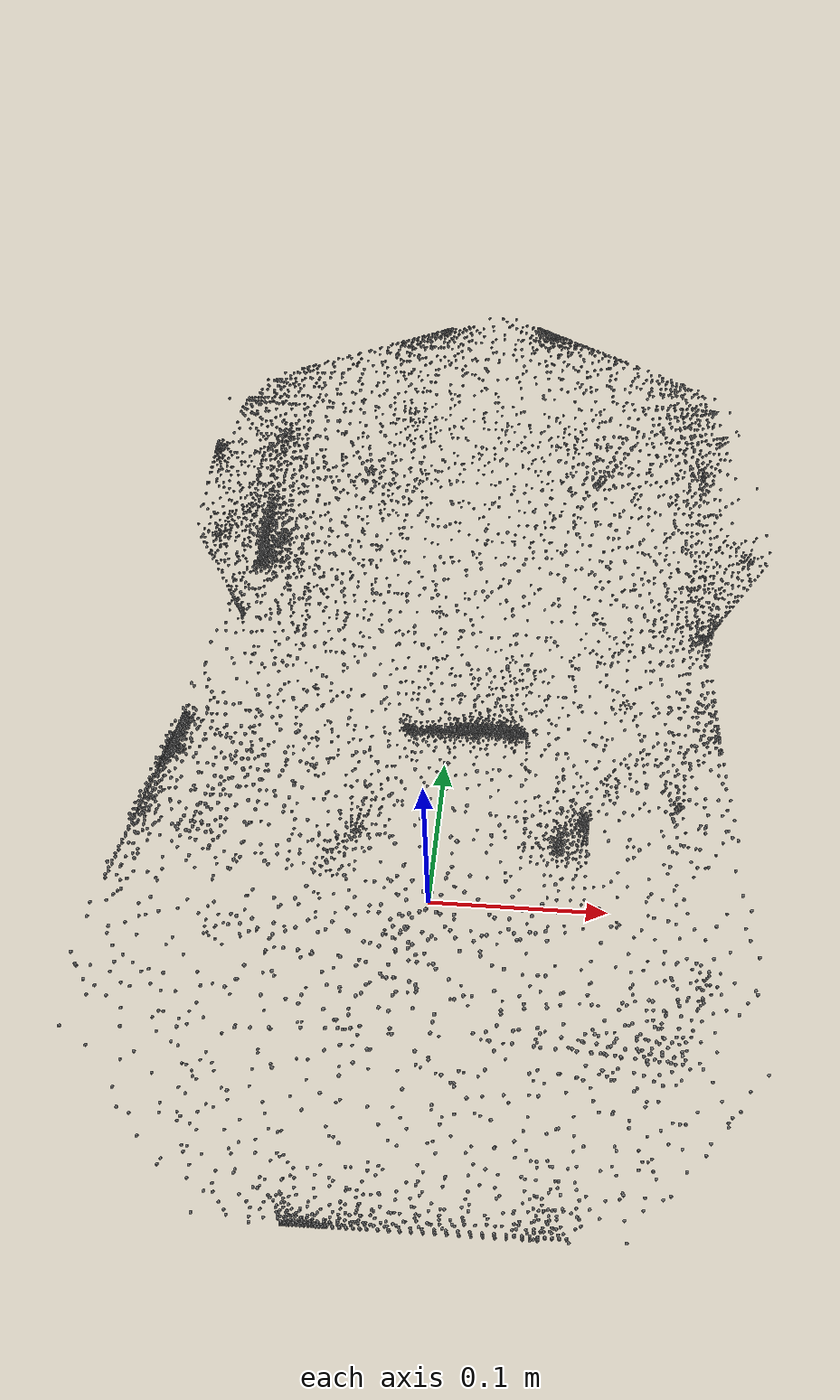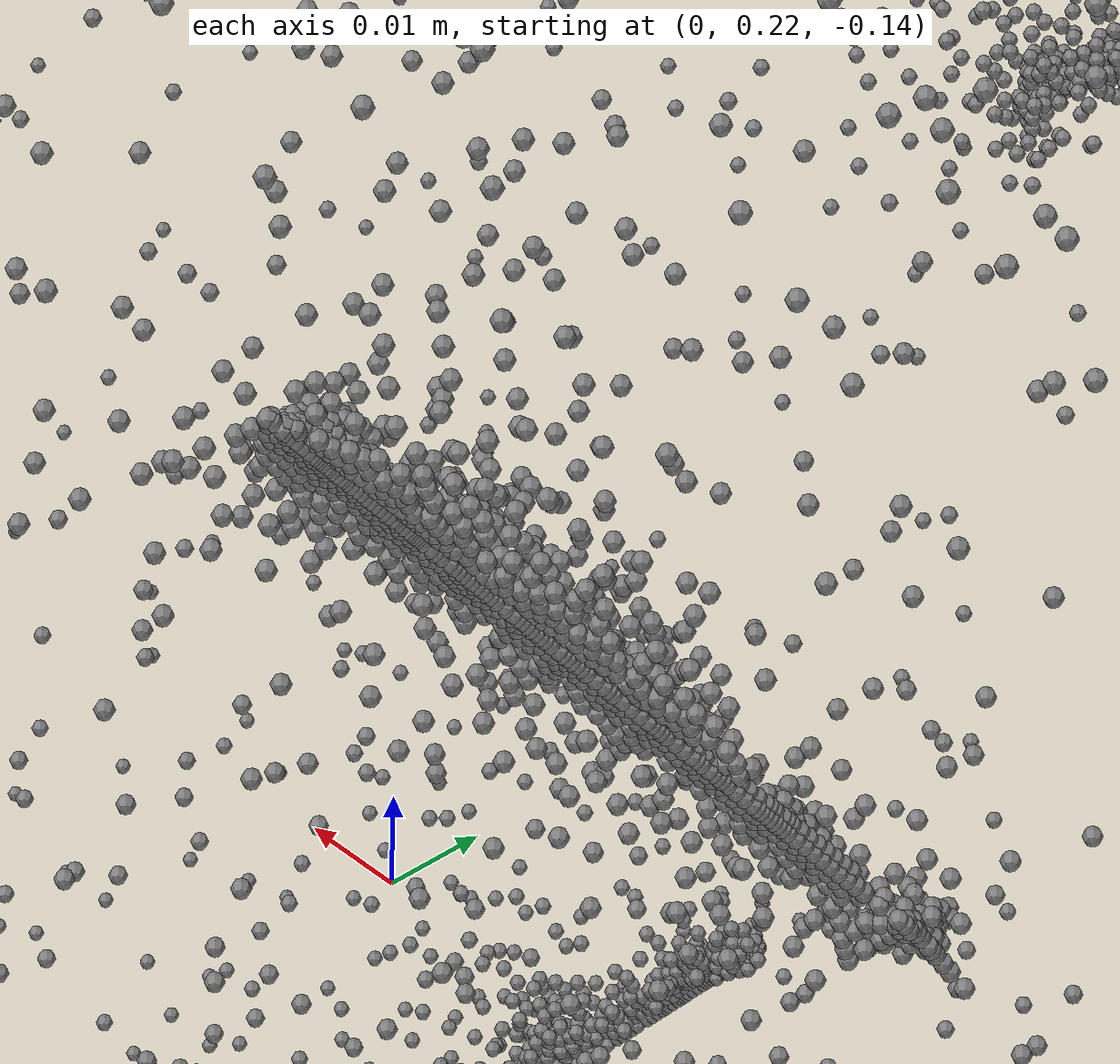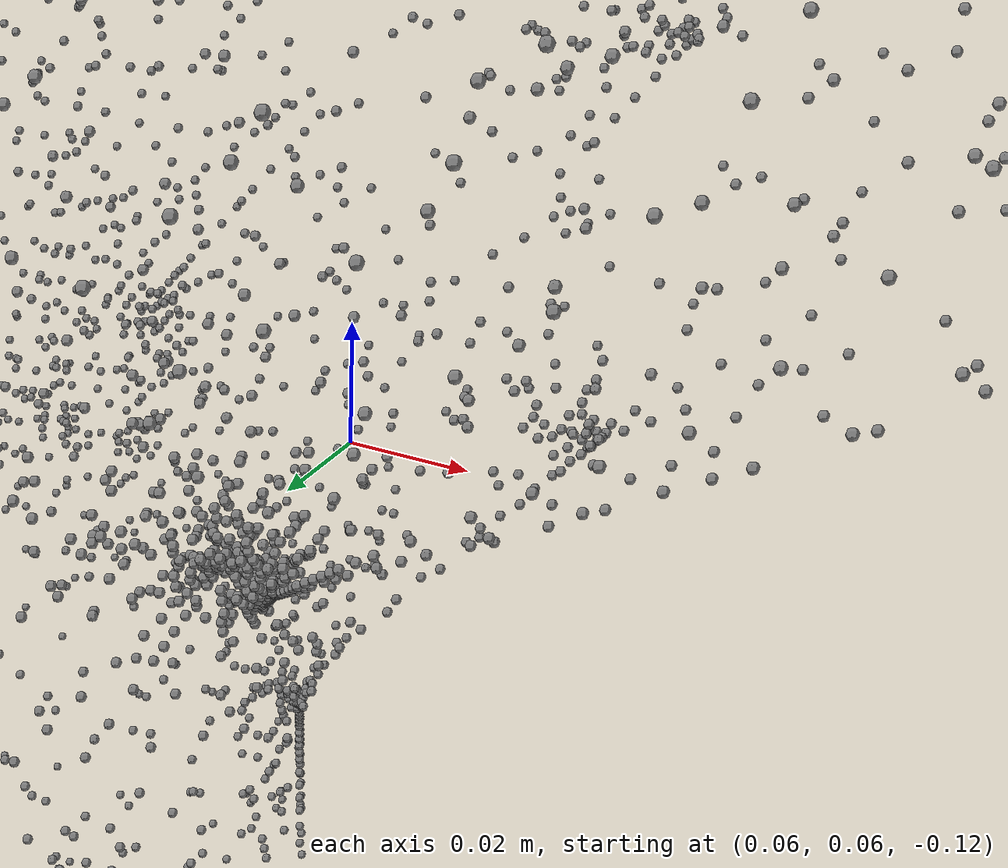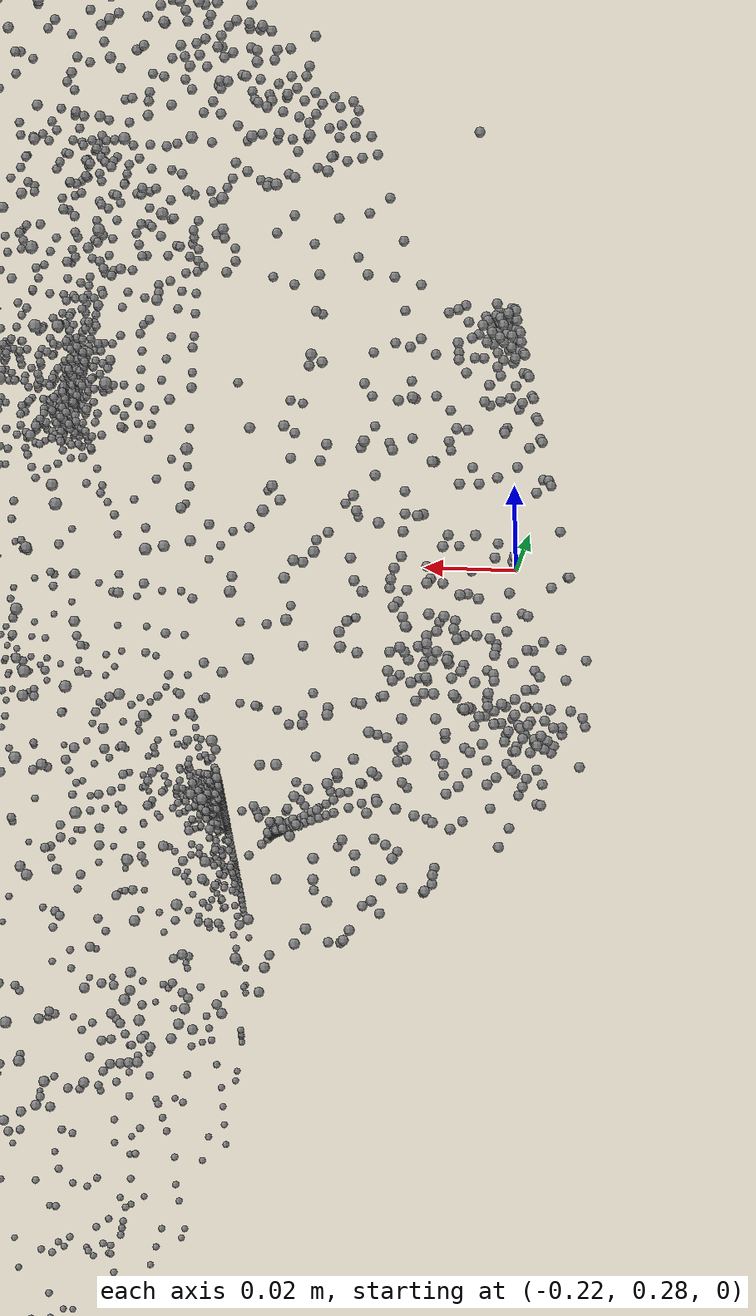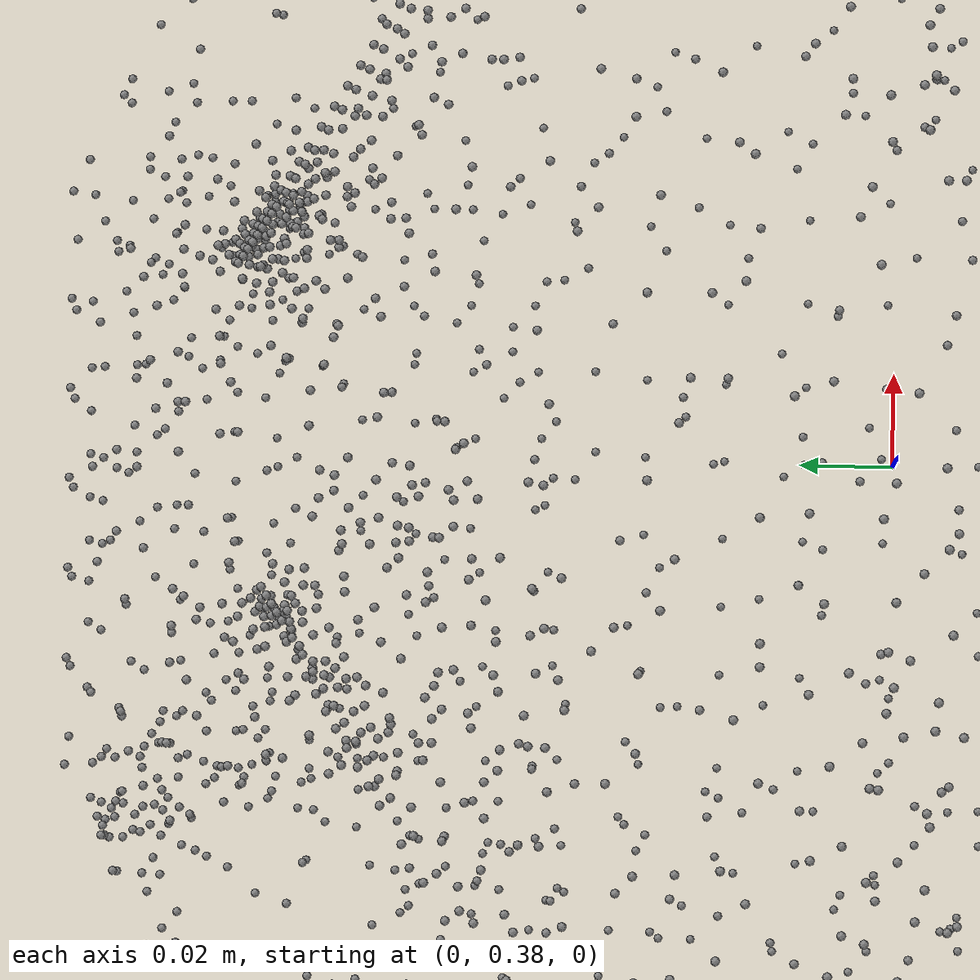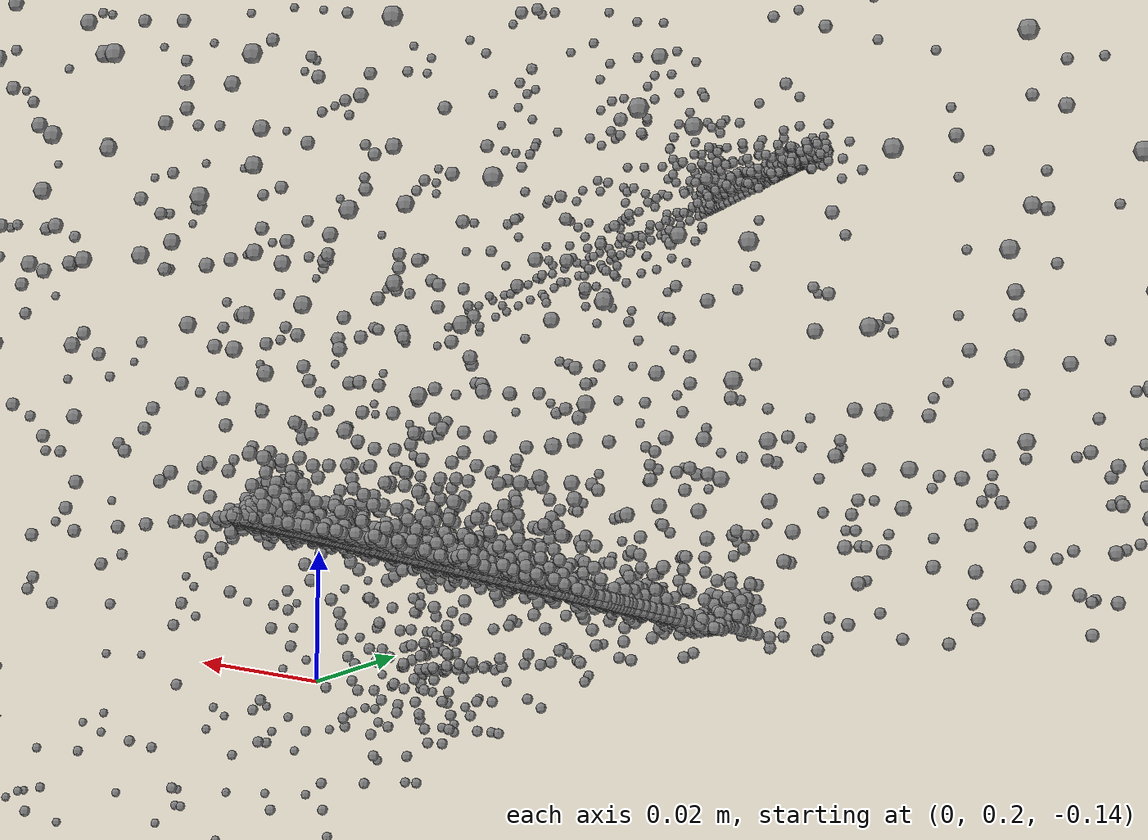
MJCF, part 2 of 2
<freejoint name="//unnamed_joint_5155"/>
      <geom name="point_mass_5155" class="/" type="sphere" size="0.001" mass="0.01" pos="0.11854036883509479 0.33235318977846195 0.083074652799701623"/>
    </body>
    <body name="point_mass_5156">
      <freejoint name="//unnamed_joint_5156"/>
      <geom name="point_mass_5156" class="/" type="sphere" size="0.001" mass="0.01" pos="-0.067171594726362721 -0.13666189713486757 -0.10839647703225071"/>
    </body>
    <body name="point_mass_5157">
      <freejoint name="//unnamed_joint_5157"/>
      <geom name="point_mass_5157" class="/" type="sphere" size="0.001" mass="0.01" pos="-0.14177871749242632 0.40015255082760887 0.025031875009855029"/>
    </body>
    <body name="point_mass_5158">
      <freejoint name="//unnamed_joint_5158"/>
      <geom name="point_mass_5158" class="/" type="sphere" size="0.001" mass="0.01" pos="-0.020142274906315729 -0.1068581719680033 -0.10765081430549686"/>
    </body>
    <body name="point_mass_5159">
      <freejoint name="//unnamed_joint_5159"/>
      <geom name="point_mass_5159" class="/" type="sphere" size="0.001" mass="0.01" pos="0.090249736647905629 0.14530495378676136 -0.10723176540708122"/>
    </body>
    <body name="point_mass_5160">
      <freejoint name="//unnamed_joint_5160"/>
      <geom name="point_mass_5160" class="/" type="sphere" size="0.001" mass="0.01" pos="0.0010455452569130216 0.24613536915671411 -0.13407569255856772"/>
    </body>
    <body name="point_mass_5161">
      <freejoint name="//unnamed_joint_5161"/>
      <geom name="point_mass_5161" class="/" type="sphere" size="0.001" mass="0.01" pos="0.19446692853726283 0.40166347103299394 -0.083975422404230643"/>
    </body>
    <body name="point_mass_5162">
      <freejoint name="//unnamed_joint_5162"/>
      <geom name="point_mass_5162" class="/" type="sphere" size="0.001" mass="0.01" pos="-0.16487853064932095 0.12671117484364741 0.0028331769848360332"/>
    </body>
    <body name="point_mass_5163">
      <freejoint name="//unnamed_joint_5163"/>
      <geom name="point_mass_5163" class="/" type="sphere" size="0.001" mass="0.01" pos="0.079996255920142686 0.12168847350717708 -0.097863442923125682"/>
    </body>
    <body name="point_mass_5164">
      <freejoint name="//unnamed_joint_5164"/>
      <geom name="point_mass_5164" class="/" type="sphere" size="0.001" mass="0.01" pos="0.090014845386245435 0.14587938367229303 -0.10679158079199162"/>
    </body>
    <body name="point_mass_5165">
      <freejoint name="//unnamed_joint_5165"/>
      <geom name="point_mass_5165" class="/" type="sphere" size="0.001" mass="0.01" pos="0.16962290426636722 0.28516019397261366 -0.064058813424364494"/>
    </body>
    <body name="point_mass_5166">
      <freejoint name="//unnamed_joint_5166"/>
      <geom name="point_mass_5166" class="/" type="sphere" size="0.001" mass="0.01" pos="0.016326204237947964 0.24927429320793551 -0.13368722953386034"/>
    </body>
    <body name="point_mass_5167">
      <freejoint name="//unnamed_joint_5167"/>
      <geom name="point_mass_5167" class="/" type="sphere" size="0.001" mass="0.01" pos="0.039949623694170849 0.48367249116834005 0.055062387451871142"/>
    </body>
    <body name="point_mass_5168">
      <freejoint name="//unnamed_joint_5168"/>
      <geom name="point_mass_5168" class="/" type="sphere" size="0.001" mass="0.01" pos="-0.18029202157406979 0.4000052599352471 -0.086353667671290296"/>
    </body>
    <body name="point_mass_5169">
      <freejoint name="//unnamed_joint_5169"/>
      <geom name="point_mass_5169" class="/" type="sphere" size="0.001" mass="0.01" pos="-0.0031147913541644812 0.24732841667719185 -0.13384710741229355"/>
    </body>
    <body name="point_mass_5170">
      <freejoint name="//unnamed_joint_5170"/>
      <geom name="point_mass_5170" class="/" type="sphere" size="0.001" mass="0.01" pos="-0.0030989180316055836 0.24698185992444488 -0.13435757857480668"/>
    </body>
    <body name="point_mass_5171">
      <freejoint name="//unnamed_joint_5171"/>
      <geom name="point_mass_5171" class="/" type="sphere" size="0.001" mass="0.01" pos="-0.040852407046045522 0.22293040272295164 0.120012685814666"/>
    </body>
    <body name="point_mass_5172">
      <freejoint name="//unnamed_joint_5172"/>
      <geom name="point_mass_5172" class="/" type="sphere" size="0.001" mass="0.01" pos="0.0060966948056628105 0.24631016189435653 -0.13392856555682939"/>
    </body>
    <body name="point_mass_5173">
      <freejoint name="//unnamed_joint_5173"/>
      <geom name="point_mass_5173" class="/" type="sphere" size="0.001" mass="0.01" pos="-0.16986098466130378 0.084191028249107153 0.0048665638680877492"/>
    </body>
    <body name="point_mass_5174">
      <freejoint name="//unnamed_joint_5174"/>
      <geom name="point_mass_5174" class="/" type="sphere" size="0.001" mass="0.01" pos="0.090322509290090475 0.14137196769953775 -0.10696678664887951"/>
    </body>
    <body name="point_mass_5175">
      <freejoint name="//unnamed_joint_5175"/>
      <geom name="point_mass_5175" class="/" type="sphere" size="0.001" mass="0.01" pos="0.067438897509641868 -0.089294832653789902 0.074475720740370954"/>
    </body>
    <body name="point_mass_5176">
      <freejoint name="//unnamed_joint_5176"/>
      <geom name="point_mass_5176" class="/" type="sphere" size="0.001" mass="0.01" pos="0.021957315467363896 0.24913862468565912 -0.13180227998078853"/>
    </body>
    <body name="point_mass_5177">
      <freejoint name="//unnamed_joint_5177"/>
      <geom name="point_mass_5177" class="/" type="sphere" size="0.001" mass="0.01" pos="-0.15660621713880515 0.41097976781596135 0.038794597403318941"/>
    </body>
    <body name="point_mass_5178">
      <freejoint name="//unnamed_joint_5178"/>
      <geom name="point_mass_5178" class="/" type="sphere" size="0.001" mass="0.01" pos="-0.12529403703090955 0.20937118673873897 0.065206286153512635"/>
    </body>
    <body name="point_mass_5179">
      <freejoint name="//unnamed_joint_5179"/>
      <geom name="point_mass_5179" class="/" type="sphere" size="0.001" mass="0.01" pos="-0.19956781831063883 0.40765114624817489 -0.0036208194274584314"/>
    </body>
    <body name="point_mass_5180">
      <freejoint name="//unnamed_joint_5180"/>
      <geom name="point_mass_5180" class="/" type="sphere" size="0.001" mass="0.01" pos="-0.11436426832099211 0.20140020617375357 0.071042625757634925"/>
    </body>
    <body name="point_mass_5181">
      <freejoint name="//unnamed_joint_5181"/>
      <geom name="point_mass_5181" class="/" type="sphere" size="0.001" mass="0.01" pos="-0.023650997135521545 0.30903468612495993 -0.12118841649349009"/>
    </body>
    <body name="point_mass_5182">
      <freejoint name="//unnamed_joint_5182"/>
      <geom name="point_mass_5182" class="/" type="sphere" size="0.001" mass="0.01" pos="-0.0072288918403652933 0.23524805426786108 0.10849807456745146"/>
    </body>
    <body name="point_mass_5183">
      <freejoint name="//unnamed_joint_5183"/>
      <geom name="point_mass_5183" class="/" type="sphere" size="0.001" mass="0.01" pos="-0.03976500870101296 0.24173487948509251 -0.13193383135716905"/>
    </body>
    <body name="point_mass_5184">
      <freejoint name="//unnamed_joint_5184"/>
      <geom name="point_mass_5184" class="/" type="sphere" size="0.001" mass="0.01" pos="0.090750664232820535 0.14498778629483969 -0.10719678891881754"/>
    </body>
    <body name="point_mass_5185">
      <freejoint name="//unnamed_joint_5185"/>
      <geom name="point_mass_5185" class="/" type="sphere" size="0.001" mass="0.01" pos="0.2067070938215369 0.37689490340177961 -0.069052154319757947"/>
    </body>
    <body name="point_mass_5186">
      <freejoint name="//unnamed_joint_5186"/>
      <geom name="point_mass_5186" class="/" type="sphere" size="0.001" mass="0.01" pos="0.022580790155645902 0.49828442630667819 0.039789672630592167"/>
    </body>
    <body name="point_mass_5187">
      <freejoint name="//unnamed_joint_5187"/>
      <geom name="point_mass_5187" class="/" type="sphere" size="0.001" mass="0.01" pos="0.03575005716124189 -0.083431868366139347 -0.084880299203679663"/>
    </body>
    <body name="point_mass_5188">
      <freejoint name="//unnamed_joint_5188"/>
      <geom name="point_mass_5188" class="/" type="sphere" size="0.001" mass="0.01" pos="0.090790234900836778 0.14515511177355181 -0.10724041209566351"/>
    </body>
    <body name="point_mass_5189">
      <freejoint name="//unnamed_joint_5189"/>
      <geom name="point_mass_5189" class="/" type="sphere" size="0.001" mass="0.01" pos="-0.1250735415912729 0.21347319780836396 0.065466290632000324"/>
    </body>
    <body name="point_mass_5190">
      <freejoint name="//unnamed_joint_5190"/>
      <geom name="point_mass_5190" class="/" type="sphere" size="0.001" mass="0.01" pos="-0.042115184137341354 0.26658601670265536 0.10102698466421567"/>
    </body>
    <body name="point_mass_5191">
      <freejoint name="//unnamed_joint_5191"/>
      <geom name="point_mass_5191" class="/" type="sphere" size="0.001" mass="0.01" pos="-0.15141482761407676 0.091641724411236844 0.02188489329068723"/>
    </body>
    <body name="point_mass_5192">
      <freejoint name="//unnamed_joint_5192"/>
      <geom name="point_mass_5192" class="/" type="sphere" size="0.001" mass="0.01" pos="0.090200152047117288 0.14693216622006045 -0.10728577143020006"/>
    </body>
    <body name="point_mass_5193">
      <freejoint name="//unnamed_joint_5193"/>
      <geom name="point_mass_5193" class="/" type="sphere" size="0.001" mass="0.01" pos="-0.095700885791702855 0.28196338972775498 0.06938363265535509"/>
    </body>
    <body name="point_mass_5194">
      <freejoint name="//unnamed_joint_5194"/>
      <geom name="point_mass_5194" class="/" type="sphere" size="0.001" mass="0.01" pos="0.16177542577857615 0.40685758232653807 -0.083970511394007713"/>
    </body>
    <body name="point_mass_5195">
      <freejoint name="//unnamed_joint_5195"/>
      <geom name="point_mass_5195" class="/" type="sphere" size="0.001" mass="0.01" pos="-0.17098600668035574 0.054247318391778751 0.0011622494927851668"/>
    </body>
    <body name="point_mass_5196">
      <freejoint name="//unnamed_joint_5196"/>
      <geom name="point_mass_5196" class="/" type="sphere" size="0.001" mass="0.01" pos="0.074577360865846751 0.22706412610658433 -0.037228262233378641"/>
    </body>
    <body name="point_mass_5197">
      <freejoint name="//unnamed_joint_5197"/>
      <geom name="point_mass_5197" class="/" type="sphere" size="0.001" mass="0.01" pos="0.12898590041429503 0.40647084883500495 0.058833667492672541"/>
    </body>
    <body name="point_mass_5198">
      <freejoint name="//unnamed_joint_5198"/>
      <geom name="point_mass_5198" class="/" type="sphere" size="0.001" mass="0.01" pos="-0.0077775875507955653 0.24701509494051724 -0.13452562695044812"/>
    </body>
    <body name="point_mass_5199">
      <freejoint name="//unnamed_joint_5199"/>
      <geom name="point_mass_5199" class="/" type="sphere" size="0.001" mass="0.01" pos="-0.0077907209299581705 0.2473754415528896 -0.13399468729144254"/>
    </body>
    <body name="point_mass_5200">
      <freejoint name="//unnamed_joint_5200"/>
      <geom name="point_mass_5200" class="/" type="sphere" size="0.001" mass="0.01" pos="0.0054922798635430748 0.24235204101090879 -0.13066334221836759"/>
    </body>
    <body name="point_mass_5201">
      <freejoint name="//unnamed_joint_5201"/>
      <geom name="point_mass_5201" class="/" type="sphere" size="0.001" mass="0.01" pos="-0.017777627135729539 0.033060956053124035 -0.035883551948452518"/>
    </body>
    <body name="point_mass_5202">
      <freejoint name="//unnamed_joint_5202"/>
      <geom name="point_mass_5202" class="/" type="sphere" size="0.001" mass="0.01" pos="0.048164598811663573 0.51183896731979905 0.034812201407814346"/>
    </body>
    <body name="point_mass_5203">
      <freejoint name="//unnamed_joint_5203"/>
      <geom name="point_mass_5203" class="/" type="sphere" size="0.001" mass="0.01" pos="0.046360044129855921 0.51531103360838049 0.031152983960409587"/>
    </body>
    <body name="point_mass_5204">
      <freejoint name="//unnamed_joint_5204"/>
      <geom name="point_mass_5204" class="/" type="sphere" size="0.001" mass="0.01" pos="-0.13520577433375486 0.37979127702624421 0.056876868044188934"/>
    </body>
    <body name="point_mass_5205">
      <freejoint name="//unnamed_joint_5205"/>
      <geom name="point_mass_5205" class="/" type="sphere" size="0.001" mass="0.01" pos="0.13061800544400146 0.4269351524910085 0.046842009742603892"/>
    </body>
    <body name="point_mass_5206">
      <freejoint name="//unnamed_joint_5206"/>
      <geom name="point_mass_5206" class="/" type="sphere" size="0.001" mass="0.01" pos="-0.035765104655635122 0.50825067330180129 0.035697800313042288"/>
    </body>
    <body name="point_mass_5207">
      <freejoint name="//unnamed_joint_5207"/>
      <geom name="point_mass_5207" class="/" type="sphere" size="0.001" mass="0.01" pos="0.137444526861142 0.10312291523561892 0.037696932339109285"/>
    </body>
    <body name="point_mass_5208">
      <freejoint name="//unnamed_joint_5208"/>
      <geom name="point_mass_5208" class="/" type="sphere" size="0.001" mass="0.01" pos="0.16963227811959902 0.28524482276090823 -0.064060196945414496"/>
    </body>
    <body name="point_mass_5209">
      <freejoint name="//unnamed_joint_5209"/>
      <geom name="point_mass_5209" class="/" type="sphere" size="0.001" mass="0.01" pos="0.028448770989340809 0.24095626771668768 -0.13227989923451422"/>
    </body>
    <body name="point_mass_5210">
      <freejoint name="//unnamed_joint_5210"/>
      <geom name="point_mass_5210" class="/" type="sphere" size="0.001" mass="0.01" pos="0.080555811134349037 0.21598062978095933 -0.066316089011795795"/>
    </body>
    <body name="point_mass_5211">
      <freejoint name="//unnamed_joint_5211"/>
      <geom name="point_mass_5211" class="/" type="sphere" size="0.001" mass="0.01" pos="0.034197205909110559 0.24762386070929196 -0.13210460349297837"/>
    </body>
    <body name="point_mass_5212">
      <freejoint name="//unnamed_joint_5212"/>
      <geom name="point_mass_5212" class="/" type="sphere" size="0.001" mass="0.01" pos="-0.022410486302896587 0.246186887124308 -0.13489944592081937"/>
    </body>
    <body name="point_mass_5213">
      <freejoint name="//unnamed_joint_5213"/>
      <geom name="point_mass_5213" class="/" type="sphere" size="0.001" mass="0.01" pos="-0.0034351994915023751 0.24936970491940813 -0.13428139777628786"/>
    </body>
    <body name="point_mass_5214">
      <freejoint name="//unnamed_joint_5214"/>
      <geom name="point_mass_5214" class="/" type="sphere" size="0.001" mass="0.01" pos="-0.11827206513956556 0.26223134674085485 0.081075241890811584"/>
    </body>
    <body name="point_mass_5215">
      <freejoint name="//unnamed_joint_5215"/>
      <geom name="point_mass_5215" class="/" type="sphere" size="0.001" mass="0.01" pos="0.16962385537580879 0.28516786230517888 -0.064036052822125877"/>
    </body>
    <body name="point_mass_5216">
      <freejoint name="//unnamed_joint_5216"/>
      <geom name="point_mass_5216" class="/" type="sphere" size="0.001" mass="0.01" pos="0.065673087365535662 -0.13375773338610381 -0.091690653467928818"/>
    </body>
    <body name="point_mass_5217">
      <freejoint name="//unnamed_joint_5217"/>
      <geom name="point_mass_5217" class="/" type="sphere" size="0.001" mass="0.01" pos="-0.13840571506764021 0.2836833057928006 -0.075339721934784401"/>
    </body>
    <body name="point_mass_5218">
      <freejoint name="//unnamed_joint_5218"/>
      <geom name="point_mass_5218" class="/" type="sphere" size="0.001" mass="0.01" pos="0.16882578349759897 0.28541634110587377 -0.063112167316047241"/>
    </body>
    <body name="point_mass_5219">
      <freejoint name="//unnamed_joint_5219"/>
      <geom name="point_mass_5219" class="/" type="sphere" size="0.001" mass="0.01" pos="-0.040553196208229829 -0.12337836223606601 -0.12225046188406651"/>
    </body>
    <body name="point_mass_5220">
      <freejoint name="//unnamed_joint_5220"/>
      <geom name="point_mass_5220" class="/" type="sphere" size="0.001" mass="0.01" pos="0.029918946572137808 0.24601141322699638 -0.12805008271926396"/>
    </body>
    <body name="point_mass_5221">
      <freejoint name="//unnamed_joint_5221"/>
      <geom name="point_mass_5221" class="/" type="sphere" size="0.001" mass="0.01" pos="-0.053820647054335438 0.48735545247100059 0.037584511582687434"/>
    </body>
    <body name="point_mass_5222">
      <freejoint name="//unnamed_joint_5222"/>
      <geom name="point_mass_5222" class="/" type="sphere" size="0.001" mass="0.01" pos="0.13356320204517899 0.11731930084972994 0.023216204908155045"/>
    </body>
    <body name="point_mass_5223">
      <freejoint name="//unnamed_joint_5223"/>
      <geom name="point_mass_5223" class="/" type="sphere" size="0.001" mass="0.01" pos="0.090811881410989684 0.14512908015758716 -0.10727760515204317"/>
    </body>
    <body name="point_mass_5224">
      <freejoint name="//unnamed_joint_5224"/>
      <geom name="point_mass_5224" class="/" type="sphere" size="0.001" mass="0.01" pos="0.12800344107403766 0.41760022198073521 0.053023389252951469"/>
    </body>
    <body name="point_mass_5225">
      <freejoint name="//unnamed_joint_5225"/>
      <geom name="point_mass_5225" class="/" type="sphere" size="0.001" mass="0.01" pos="0.16963506893384109 0.28529252813689548 -0.064108041773284191"/>
    </body>
    <body name="point_mass_5226">
      <freejoint name="//unnamed_joint_5226"/>
      <geom name="point_mass_5226" class="/" type="sphere" size="0.001" mass="0.01" pos="-0.0083387432204945766 0.24594642979603151 -0.13437114251424168"/>
    </body>
    <body name="point_mass_5227">
      <freejoint name="//unnamed_joint_5227"/>
      <geom name="point_mass_5227" class="/" type="sphere" size="0.001" mass="0.01" pos="-0.11530725400987894 0.32073165378615875 0.057697903075626236"/>
    </body>
    <body name="point_mass_5228">
      <freejoint name="//unnamed_joint_5228"/>
      <geom name="point_mass_5228" class="/" type="sphere" size="0.001" mass="0.01" pos="-0.045605612743353612 0.22009084723853123 0.12820314756317597"/>
    </body>
    <body name="point_mass_5229">
      <freejoint name="//unnamed_joint_5229"/>
      <geom name="point_mass_5229" class="/" type="sphere" size="0.001" mass="0.01" pos="-0.18300424031166307 0.313594611959014 -0.061100229751484617"/>
    </body>
    <body name="point_mass_5230">
      <freejoint name="//unnamed_joint_5230"/>
      <geom name="point_mass_5230" class="/" type="sphere" size="0.001" mass="0.01" pos="-0.18279555525944308 0.31338037966584892 -0.065137178340508389"/>
    </body>
    <body name="point_mass_5231">
      <freejoint name="//unnamed_joint_5231"/>
      <geom name="point_mass_5231" class="/" type="sphere" size="0.001" mass="0.01" pos="-0.17806233117681516 0.31263492866914533 -0.074161515505497225"/>
    </body>
    <body name="point_mass_5232">
      <freejoint name="//unnamed_joint_5232"/>
      <geom name="point_mass_5232" class="/" type="sphere" size="0.001" mass="0.01" pos="0.024845979312894624 -0.14053567872621747 -0.10025231224641822"/>
    </body>
    <body name="point_mass_5233">
      <freejoint name="//unnamed_joint_5233"/>
      <geom name="point_mass_5233" class="/" type="sphere" size="0.001" mass="0.01" pos="-0.11987899671991413 0.1177385813060445 -0.00019951472695197697"/>
    </body>
    <body name="point_mass_5234">
      <freejoint name="//unnamed_joint_5234"/>
      <geom name="point_mass_5234" class="/" type="sphere" size="0.001" mass="0.01" pos="0.060444544364339624 0.50220419023025442 0.0348368107960767"/>
    </body>
    <body name="point_mass_5235">
      <freejoint name="//unnamed_joint_5235"/>
      <geom name="point_mass_5235" class="/" type="sphere" size="0.001" mass="0.01" pos="0.038602435582733879 0.24729404054707124 -0.13205724659757362"/>
    </body>
    <body name="point_mass_5236">
      <freejoint name="//unnamed_joint_5236"/>
      <geom name="point_mass_5236" class="/" type="sphere" size="0.001" mass="0.01" pos="0.01286394525656941 0.24657085301589995 -0.1321302864802783"/>
    </body>
    <body name="point_mass_5237">
      <freejoint name="//unnamed_joint_5237"/>
      <geom name="point_mass_5237" class="/" type="sphere" size="0.001" mass="0.01" pos="-0.12376059880866144 0.18741449195921339 0.070164237077785782"/>
    </body>
    <body name="point_mass_5238">
      <freejoint name="//unnamed_joint_5238"/>
      <geom name="point_mass_5238" class="/" type="sphere" size="0.001" mass="0.01" pos="-0.10318190516426291 -0.01509725675125044 0.09765408220786452"/>
    </body>
    <body name="point_mass_5239">
      <freejoint name="//unnamed_joint_5239"/>
      <geom name="point_mass_5239" class="/" type="sphere" size="0.001" mass="0.01" pos="-0.01539134837371302 0.24622467512554422 -0.13466160283912362"/>
    </body>
    <body name="point_mass_5240">
      <freejoint name="//unnamed_joint_5240"/>
      <geom name="point_mass_5240" class="/" type="sphere" size="0.001" mass="0.01" pos="-0.018304593968973007 0.24708987372668009 -0.13490373579564124"/>
    </body>
    <body name="point_mass_5241">
      <freejoint name="//unnamed_joint_5241"/>
      <geom name="point_mass_5241" class="/" type="sphere" size="0.001" mass="0.01" pos="-0.018322525080293417 0.24748135777190328 -0.13432708801701665"/>
    </body>
    <body name="point_mass_5242">
      <freejoint name="//unnamed_joint_5242"/>
      <geom name="point_mass_5242" class="/" type="sphere" size="0.001" mass="0.01" pos="-0.01715269940905273 0.24746959307231009 -0.13429016643203795"/>
    </body>
    <body name="point_mass_5243">
      <freejoint name="//unnamed_joint_5243"/>
      <geom name="point_mass_5243" class="/" type="sphere" size="0.001" mass="0.01" pos="-0.017134926589175516 0.24708156497266198 -0.13486172370173088"/>
    </body>
    <body name="point_mass_5244">
      <freejoint name="//unnamed_joint_5244"/>
      <geom name="point_mass_5244" class="/" type="sphere" size="0.001" mass="0.01" pos="-0.019492350751534104 0.24749312247149646 -0.13436400960199535"/>
    </body>
    <body name="point_mass_5245">
      <freejoint name="//unnamed_joint_5245"/>
      <geom name="point_mass_5245" class="/" type="sphere" size="0.001" mass="0.01" pos="-0.019474261348770495 0.24709818248069818 -0.1349457478895516"/>
    </body>
    <body name="point_mass_5246">
      <freejoint name="//unnamed_joint_5246"/>
      <geom name="point_mass_5246" class="/" type="sphere" size="0.001" mass="0.01" pos="-0.043333125200922938 0.24290048526109762 -0.13342430708737804"/>
    </body>
    <body name="point_mass_5247">
      <freejoint name="//unnamed_joint_5247"/>
      <geom name="point_mass_5247" class="/" type="sphere" size="0.001" mass="0.01" pos="-0.12470096455276299 0.20987475718259896 0.065849032613564978"/>
    </body>
    <body name="point_mass_5248">
      <freejoint name="//unnamed_joint_5248"/>
      <geom name="point_mass_5248" class="/" type="sphere" size="0.001" mass="0.01" pos="0.16879225937305364 0.45286196898185749 -0.034035681428114521"/>
    </body>
    <body name="point_mass_5249">
      <freejoint name="//unnamed_joint_5249"/>
      <geom name="point_mass_5249" class="/" type="sphere" size="0.001" mass="0.01" pos="0.15364981002875902 0.34696981561126716 0.045832995146131823"/>
    </body>
    <body name="point_mass_5250">
      <freejoint name="//unnamed_joint_5250"/>
      <geom name="point_mass_5250" class="/" type="sphere" size="0.001" mass="0.01" pos="0.090553087446763839 0.14257986007481813 -0.10702328309102167"/>
    </body>
    <body name="point_mass_5251">
      <freejoint name="//unnamed_joint_5251"/>
      <geom name="point_mass_5251" class="/" type="sphere" size="0.001" mass="0.01" pos="-0.077059214672091342 0.1934095583396726 -0.12280387815835539"/>
    </body>
    <body name="point_mass_5252">
      <freejoint name="//unnamed_joint_5252"/>
      <geom name="point_mass_5252" class="/" type="sphere" size="0.001" mass="0.01" pos="-0.063881906698628657 0.19399532763999566 -0.12604201472330709"/>
    </body>
    <body name="point_mass_5253">
      <freejoint name="//unnamed_joint_5253"/>
      <geom name="point_mass_5253" class="/" type="sphere" size="0.001" mass="0.01" pos="-0.051804188768322414 0.19110158538422606 -0.12569841185937244"/>
    </body>
    <body name="point_mass_5254">
      <freejoint name="//unnamed_joint_5254"/>
      <geom name="point_mass_5254" class="/" type="sphere" size="0.001" mass="0.01" pos="-0.026940163455104176 -0.13935662989858183 -0.11892224128201567"/>
    </body>
    <body name="point_mass_5255">
      <freejoint name="//unnamed_joint_5255"/>
      <geom name="point_mass_5255" class="/" type="sphere" size="0.001" mass="0.01" pos="-0.027058013362057279 -0.13991394985613281 -0.11620807589065374"/>
    </body>
    <body name="point_mass_5256">
      <freejoint name="//unnamed_joint_5256"/>
      <geom name="point_mass_5256" class="/" type="sphere" size="0.001" mass="0.01" pos="-0.024952271521926389 -0.13353118823074039 -0.12345670392515633"/>
    </body>
    <body name="point_mass_5257">
      <freejoint name="//unnamed_joint_5257"/>
      <geom name="point_mass_5257" class="/" type="sphere" size="0.001" mass="0.01" pos="0.16963879854259825 0.28524782532981791 -0.064054425525846587"/>
    </body>
    <body name="point_mass_5258">
      <freejoint name="//unnamed_joint_5258"/>
      <geom name="point_mass_5258" class="/" type="sphere" size="0.001" mass="0.01" pos="0.16960264179474091 0.28515336172764488 -0.063983969503254634"/>
    </body>
    <body name="point_mass_5259">
      <freejoint name="//unnamed_joint_5259"/>
      <geom name="point_mass_5259" class="/" type="sphere" size="0.001" mass="0.01" pos="-0.1000098183801878 0.38050700028067619 -0.069128450549787737"/>
    </body>
    <body name="point_mass_5260">
      <freejoint name="//unnamed_joint_5260"/>
      <geom name="point_mass_5260" class="/" type="sphere" size="0.001" mass="0.01" pos="0.056401965651678182 0.47097265855651216 0.041321899865719686"/>
    </body>
    <body name="point_mass_5261">
      <freejoint name="//unnamed_joint_5261"/>
      <geom name="point_mass_5261" class="/" type="sphere" size="0.001" mass="0.01" pos="0.061168063716250581 0.12196878157835106 -0.11410424391706298"/>
    </body>
    <body name="point_mass_5262">
      <freejoint name="//unnamed_joint_5262"/>
      <geom name="point_mass_5262" class="/" type="sphere" size="0.001" mass="0.01" pos="-0.12259102771201211 0.32159558659193072 0.067048129757431921"/>
    </body>
    <body name="point_mass_5263">
      <freejoint name="//unnamed_joint_5263"/>
      <geom name="point_mass_5263" class="/" type="sphere" size="0.001" mass="0.01" pos="0.064899066558373214 0.13081393991631393 -0.10695009065347728"/>
    </body>
    <body name="point_mass_5264">
      <freejoint name="//unnamed_joint_5264"/>
      <geom name="point_mass_5264" class="/" type="sphere" size="0.001" mass="0.01" pos="-0.12565285225959094 0.21677332083469891 0.066515973662645805"/>
    </body>
    <body name="point_mass_5265">
      <freejoint name="//unnamed_joint_5265"/>
      <geom name="point_mass_5265" class="/" type="sphere" size="0.001" mass="0.01" pos="-0.12613661067390322 0.21676832858276843 0.06593193895978082"/>
    </body>
    <body name="point_mass_5266">
      <freejoint name="//unnamed_joint_5266"/>
      <geom name="point_mass_5266" class="/" type="sphere" size="0.001" mass="0.01" pos="-0.1246225217178166 0.2171633465794143 0.067771897211781021"/>
    </body>
    <body name="point_mass_5267">
      <freejoint name="//unnamed_joint_5267"/>
      <geom name="point_mass_5267" class="/" type="sphere" size="0.001" mass="0.01" pos="-0.068586312530251881 -0.13701140506316359 -0.11586978212147356"/>
    </body>
    <body name="point_mass_5268">
      <freejoint name="//unnamed_joint_5268"/>
      <geom name="point_mass_5268" class="/" type="sphere" size="0.001" mass="0.01" pos="-0.076404579913427154 0.076808614521786556 0.11104459282163277"/>
    </body>
    <body name="point_mass_5269">
      <freejoint name="//unnamed_joint_5269"/>
      <geom name="point_mass_5269" class="/" type="sphere" size="0.001" mass="0.01" pos="0.16845005166871274 0.4478781328213759 -0.0080825446796786195"/>
    </body>
    <body name="point_mass_5270">
      <freejoint name="//unnamed_joint_5270"/>
      <geom name="point_mass_5270" class="/" type="sphere" size="0.001" mass="0.01" pos="-0.032510548328467156 0.24478392776168273 -0.1124128028015183"/>
    </body>
    <body name="point_mass_5271">
      <freejoint name="//unnamed_joint_5271"/>
      <geom name="point_mass_5271" class="/" type="sphere" size="0.001" mass="0.01" pos="0.16955371042504125 0.28515470294121958 -0.064057746455083275"/>
    </body>
    <body name="point_mass_5272">
      <freejoint name="//unnamed_joint_5272"/>
      <geom name="point_mass_5272" class="/" type="sphere" size="0.001" mass="0.01" pos="-0.15596720907057873 0.12169805889669301 -0.001661189445452125"/>
    </body>
    <body name="point_mass_5273">
      <freejoint name="//unnamed_joint_5273"/>
      <geom name="point_mass_5273" class="/" type="sphere" size="0.001" mass="0.01" pos="0.13349026646837692 0.29869226867318721 0.04806173431797512"/>
    </body>
    <body name="point_mass_5274">
      <freejoint name="//unnamed_joint_5274"/>
      <geom name="point_mass_5274" class="/" type="sphere" size="0.001" mass="0.01" pos="0.001989661603614766 0.24611041489314806 -0.13403881086428759"/>
    </body>
    <body name="point_mass_5275">
      <freejoint name="//unnamed_joint_5275"/>
      <geom name="point_mass_5275" class="/" type="sphere" size="0.001" mass="0.01" pos="-0.16868838516467394 0.36542383286880203 0.03285815212571206"/>
    </body>
    <body name="point_mass_5276">
      <freejoint name="//unnamed_joint_5276"/>
      <geom name="point_mass_5276" class="/" type="sphere" size="0.001" mass="0.01" pos="-0.17216509867516067 0.060166065733299835 0.011673152172648225"/>
    </body>
    <body name="point_mass_5277">
      <freejoint name="//unnamed_joint_5277"/>
      <geom name="point_mass_5277" class="/" type="sphere" size="0.001" mass="0.01" pos="0.067350438466029866 0.37953153290250879 0.086594487759256447"/>
    </body>
    <body name="point_mass_5278">
      <freejoint name="//unnamed_joint_5278"/>
      <geom name="point_mass_5278" class="/" type="sphere" size="0.001" mass="0.01" pos="-0.040558752230072 0.42165740510307115 -0.13283104512687521"/>
    </body>
    <body name="point_mass_5279">
      <freejoint name="//unnamed_joint_5279"/>
      <geom name="point_mass_5279" class="/" type="sphere" size="0.001" mass="0.01" pos="0.044349510945485109 0.51663024492434217 0.035595812267213332"/>
    </body>
    <body name="point_mass_5280">
      <freejoint name="//unnamed_joint_5280"/>
      <geom name="point_mass_5280" class="/" type="sphere" size="0.001" mass="0.01" pos="0.090798827051664255 0.14517195669527516 -0.10728291987677727"/>
    </body>
    <body name="point_mass_5281">
      <freejoint name="//unnamed_joint_5281"/>
      <geom name="point_mass_5281" class="/" type="sphere" size="0.001" mass="0.01" pos="0.17809528078049447 0.31056723625911936 -0.064311301356281977"/>
    </body>
    <body name="point_mass_5282">
      <freejoint name="//unnamed_joint_5282"/>
      <geom name="point_mass_5282" class="/" type="sphere" size="0.001" mass="0.01" pos="0.16955517863993444 0.28503677378995451 -0.064049959432441808"/>
    </body>
    <body name="point_mass_5283">
      <freejoint name="//unnamed_joint_5283"/>
      <geom name="point_mass_5283" class="/" type="sphere" size="0.001" mass="0.01" pos="0.023211210319269739 0.24617547271750673 -0.13331171124772301"/>
    </body>
    <body name="point_mass_5284">
      <freejoint name="//unnamed_joint_5284"/>
      <geom name="point_mass_5284" class="/" type="sphere" size="0.001" mass="0.01" pos="0.05719292164941666 0.23112732378817694 -0.077740271707105263"/>
    </body>
    <body name="point_mass_5285">
      <freejoint name="//unnamed_joint_5285"/>
      <geom name="point_mass_5285" class="/" type="sphere" size="0.001" mass="0.01" pos="0.16961115670550472 0.28517525042200392 -0.064023585956629769"/>
    </body>
    <body name="point_mass_5286">
      <freejoint name="//unnamed_joint_5286"/>
      <geom name="point_mass_5286" class="/" type="sphere" size="0.001" mass="0.01" pos="0.18697544915617054 0.33837278583523739 -0.055517825046450253"/>
    </body>
    <body name="point_mass_5287">
      <freejoint name="//unnamed_joint_5287"/>
      <geom name="point_mass_5287" class="/" type="sphere" size="0.001" mass="0.01" pos="0.14637240406214524 0.27515762707808294 -0.045713944303888823"/>
    </body>
    <body name="point_mass_5288">
      <freejoint name="//unnamed_joint_5288"/>
      <geom name="point_mass_5288" class="/" type="sphere" size="0.001" mass="0.01" pos="-0.053327006009528916 0.33905218497922457 -0.086102164613377843"/>
    </body>
    <body name="point_mass_5289">
      <freejoint name="//unnamed_joint_5289"/>
      <geom name="point_mass_5289" class="/" type="sphere" size="0.001" mass="0.01" pos="-0.12717566607627545 0.21287282824070733 -0.031057596563493692"/>
    </body>
    <body name="point_mass_5290">
      <freejoint name="//unnamed_joint_5290"/>
      <geom name="point_mass_5290" class="/" type="sphere" size="0.001" mass="0.01" pos="-0.18601534113032434 0.41199428115444769 -0.033491862512829818"/>
    </body>
    <body name="point_mass_5291">
      <freejoint name="//unnamed_joint_5291"/>
      <geom name="point_mass_5291" class="/" type="sphere" size="0.001" mass="0.01" pos="-0.084846637916150686 0.0055755040671846331 0.09280459361328379"/>
    </body>
    <body name="point_mass_5292">
      <freejoint name="//unnamed_joint_5292"/>
      <geom name="point_mass_5292" class="/" type="sphere" size="0.001" mass="0.01" pos="0.12107941200142486 0.34674113563977216 0.037519534142593298"/>
    </body>
    <body name="point_mass_5293">
      <freejoint name="//unnamed_joint_5293"/>
      <geom name="point_mass_5293" class="/" type="sphere" size="0.001" mass="0.01" pos="0.035347923777163191 0.51431815774686318 0.037886753510160832"/>
    </body>
    <body name="point_mass_5294">
      <freejoint name="//unnamed_joint_5294"/>
      <geom name="point_mass_5294" class="/" type="sphere" size="0.001" mass="0.01" pos="0.02259844901612839 0.24619437090328991 -0.13333608856122431"/>
    </body>
    <body name="point_mass_5295">
      <freejoint name="//unnamed_joint_5295"/>
      <geom name="point_mass_5295" class="/" type="sphere" size="0.001" mass="0.01" pos="0.02104852335594519 0.2439262656726871 -0.1330206925122355"/>
    </body>
    <body name="point_mass_5296">
      <freejoint name="//unnamed_joint_5296"/>
      <geom name="point_mass_5296" class="/" type="sphere" size="0.001" mass="0.01" pos="0.020390879076424097 0.47865135296375455 -0.091084563504603033"/>
    </body>
    <body name="point_mass_5297">
      <freejoint name="//unnamed_joint_5297"/>
      <geom name="point_mass_5297" class="/" type="sphere" size="0.001" mass="0.01" pos="-0.027056746485229013 0.5109632495798655 0.034605358271400689"/>
    </body>
    <body name="point_mass_5298">
      <freejoint name="//unnamed_joint_5298"/>
      <geom name="point_mass_5298" class="/" type="sphere" size="0.001" mass="0.01" pos="0.032185719707475129 0.2453361146828445 -0.12937716293539464"/>
    </body>
    <body name="point_mass_5299">
      <freejoint name="//unnamed_joint_5299"/>
      <geom name="point_mass_5299" class="/" type="sphere" size="0.001" mass="0.01" pos="0.091576579844724962 0.48687835955978143 0.036670116179353437"/>
    </body>
    <body name="point_mass_5300">
      <freejoint name="//unnamed_joint_5300"/>
      <geom name="point_mass_5300" class="/" type="sphere" size="0.001" mass="0.01" pos="0.090052087604687303 0.48446211594521521 0.039582893427255954"/>
    </body>
    <body name="point_mass_5301">
      <freejoint name="//unnamed_joint_5301"/>
      <geom name="point_mass_5301" class="/" type="sphere" size="0.001" mass="0.01" pos="0.044114805119760861 0.51253079550385161 0.037060157458916422"/>
    </body>
    <body name="point_mass_5302">
      <freejoint name="//unnamed_joint_5302"/>
      <geom name="point_mass_5302" class="/" type="sphere" size="0.001" mass="0.01" pos="-0.16540861142127947 0.12646978481634708 0.0031762914521900444"/>
    </body>
    <body name="point_mass_5303">
      <freejoint name="//unnamed_joint_5303"/>
      <geom name="point_mass_5303" class="/" type="sphere" size="0.001" mass="0.01" pos="-0.064230420512559047 0.45710781033689113 0.034875770602456405"/>
    </body>
    <body name="point_mass_5304">
      <freejoint name="//unnamed_joint_5304"/>
      <geom name="point_mass_5304" class="/" type="sphere" size="0.001" mass="0.01" pos="0.1432201459384464 0.417296359884688 -0.086466914920070886"/>
    </body>
    <body name="point_mass_5305">
      <freejoint name="//unnamed_joint_5305"/>
      <geom name="point_mass_5305" class="/" type="sphere" size="0.001" mass="0.01" pos="0.072744421692954919 0.14339293970541817 -0.10986740486884093"/>
    </body>
    <body name="point_mass_5306">
      <freejoint name="//unnamed_joint_5306"/>
      <geom name="point_mass_5306" class="/" type="sphere" size="0.001" mass="0.01" pos="0.065102089632982349 0.1066391337028977 -0.10324784596930149"/>
    </body>
    <body name="point_mass_5307">
      <freejoint name="//unnamed_joint_5307"/>
      <geom name="point_mass_5307" class="/" type="sphere" size="0.001" mass="0.01" pos="0.093280742098387673 0.15069205143542302 -0.10724935978998543"/>
    </body>
    <body name="point_mass_5308">
      <freejoint name="//unnamed_joint_5308"/>
      <geom name="point_mass_5308" class="/" type="sphere" size="0.001" mass="0.01" pos="0.091440000641962907 0.14926214585193234 -0.10774247252075647"/>
    </body>
    <body name="point_mass_5309">
      <freejoint name="//unnamed_joint_5309"/>
      <geom name="point_mass_5309" class="/" type="sphere" size="0.001" mass="0.01" pos="-0.13027355891949294 -0.042192817215794043 -0.053705253847775275"/>
    </body>
    <body name="point_mass_5310">
      <freejoint name="//unnamed_joint_5310"/>
      <geom name="point_mass_5310" class="/" type="sphere" size="0.001" mass="0.01" pos="-0.020211510552511532 0.24626323845115122 -0.13278709396615693"/>
    </body>
    <body name="point_mass_5311">
      <freejoint name="//unnamed_joint_5311"/>
      <geom name="point_mass_5311" class="/" type="sphere" size="0.001" mass="0.01" pos="-0.10239651594109757 0.44953349201851073 0.050612529857796129"/>
    </body>
    <body name="point_mass_5312">
      <freejoint name="//unnamed_joint_5312"/>
      <geom name="point_mass_5312" class="/" type="sphere" size="0.001" mass="0.01" pos="-0.12418784707281998 0.42672310467844971 0.05575048346322594"/>
    </body>
    <body name="point_mass_5313">
      <freejoint name="//unnamed_joint_5313"/>
      <geom name="point_mass_5313" class="/" type="sphere" size="0.001" mass="0.01" pos="-0.035471712529273683 -0.11839985006775261 -0.11532180039527576"/>
    </body>
    <body name="point_mass_5314">
      <freejoint name="//unnamed_joint_5314"/>
      <geom name="point_mass_5314" class="/" type="sphere" size="0.001" mass="0.01" pos="-0.15211744288983364 0.027878781185943474 0.055478363238934958"/>
    </body>
    <body name="point_mass_5315">
      <freejoint name="//unnamed_joint_5315"/>
      <geom name="point_mass_5315" class="/" type="sphere" size="0.001" mass="0.01" pos="-0.19882902848136105 0.39248296300203628 -0.075963089465098305"/>
    </body>
    <body name="point_mass_5316">
      <freejoint name="//unnamed_joint_5316"/>
      <geom name="point_mass_5316" class="/" type="sphere" size="0.001" mass="0.01" pos="0.090416274559775328 0.14502888754296456 -0.10691748553817995"/>
    </body>
    <body name="point_mass_5317">
      <freejoint name="//unnamed_joint_5317"/>
      <geom name="point_mass_5317" class="/" type="sphere" size="0.001" mass="0.01" pos="-0.1375208574718606 0.037270186376538721 -0.081727028343063612"/>
    </body>
    <body name="point_mass_5318">
      <freejoint name="//unnamed_joint_5318"/>
      <geom name="point_mass_5318" class="/" type="sphere" size="0.001" mass="0.01" pos="0.1643136621198466 0.14211329819547014 0.010175024648801776"/>
    </body>
    <body name="point_mass_5319">
      <freejoint name="//unnamed_joint_5319"/>
      <geom name="point_mass_5319" class="/" type="sphere" size="0.001" mass="0.01" pos="0.16963225252173325 0.28518134392004979 -0.063988286989024618"/>
    </body>
    <body name="point_mass_5320">
      <freejoint name="//unnamed_joint_5320"/>
      <geom name="point_mass_5320" class="/" type="sphere" size="0.001" mass="0.01" pos="0.025506968155039316 0.24857159507761512 -0.12998373579175304"/>
    </body>
    <body name="point_mass_5321">
      <freejoint name="//unnamed_joint_5321"/>
      <geom name="point_mass_5321" class="/" type="sphere" size="0.001" mass="0.01" pos="0.018574836068899238 0.051080864671982196 0.14073025579081994"/>
    </body>
    <body name="point_mass_5322">
      <freejoint name="//unnamed_joint_5322"/>
      <geom name="point_mass_5322" class="/" type="sphere" size="0.001" mass="0.01" pos="0.017254117377214148 0.24622357110289042 -0.13352661940193347"/>
    </body>
    <body name="point_mass_5323">
      <freejoint name="//unnamed_joint_5323"/>
      <geom name="point_mass_5323" class="/" type="sphere" size="0.001" mass="0.01" pos="-0.032358531280148428 -0.12914351153430215 0.081280170479037184"/>
    </body>
    <body name="point_mass_5324">
      <freejoint name="//unnamed_joint_5324"/>
      <geom name="point_mass_5324" class="/" type="sphere" size="0.001" mass="0.01" pos="-0.033343133887707765 -0.12396189103355036 0.089042391480256125"/>
    </body>
    <body name="point_mass_5325">
      <freejoint name="//unnamed_joint_5325"/>
      <geom name="point_mass_5325" class="/" type="sphere" size="0.001" mass="0.01" pos="0.19164187103517608 0.38165694904586528 -0.094929197536726795"/>
    </body>
    <body name="point_mass_5326">
      <freejoint name="//unnamed_joint_5326"/>
      <geom name="point_mass_5326" class="/" type="sphere" size="0.001" mass="0.01" pos="-0.16838979049960301 0.086700637349678658 0.012348429117512404"/>
    </body>
    <body name="point_mass_5327">
      <freejoint name="//unnamed_joint_5327"/>
      <geom name="point_mass_5327" class="/" type="sphere" size="0.001" mass="0.01" pos="-0.16673239640382267 0.085476823226420084 0.018108920992334642"/>
    </body>
    <body name="point_mass_5328">
      <freejoint name="//unnamed_joint_5328"/>
      <geom name="point_mass_5328" class="/" type="sphere" size="0.001" mass="0.01" pos="-0.086154141265165671 0.21433802928621598 0.085787440709977805"/>
    </body>
    <body name="point_mass_5329">
      <freejoint name="//unnamed_joint_5329"/>
      <geom name="point_mass_5329" class="/" type="sphere" size="0.001" mass="0.01" pos="-0.025537436430950237 -0.13577005614551765 -0.11795008699431643"/>
    </body>
    <body name="point_mass_5330">
      <freejoint name="//unnamed_joint_5330"/>
      <geom name="point_mass_5330" class="/" type="sphere" size="0.001" mass="0.01" pos="0.13015922913899489 0.507654716517976 -0.070003010709206698"/>
    </body>
    <body name="point_mass_5331">
      <freejoint name="//unnamed_joint_5331"/>
      <geom name="point_mass_5331" class="/" type="sphere" size="0.001" mass="0.01" pos="0.1291908759375858 0.50898424370051987 -0.05452082514056511"/>
    </body>
    <body name="point_mass_5332">
      <freejoint name="//unnamed_joint_5332"/>
      <geom name="point_mass_5332" class="/" type="sphere" size="0.001" mass="0.01" pos="0.12142696950167482 0.51236874120453146 -0.026738831235204992"/>
    </body>
    <body name="point_mass_5333">
      <freejoint name="//unnamed_joint_5333"/>
      <geom name="point_mass_5333" class="/" type="sphere" size="0.001" mass="0.01" pos="-0.10916583152604352 0.20606948524370425 0.080894239601616125"/>
    </body>
    <body name="point_mass_5334">
      <freejoint name="//unnamed_joint_5334"/>
      <geom name="point_mass_5334" class="/" type="sphere" size="0.001" mass="0.01" pos="0.040927847474562747 0.24464297808970636 -0.13152818881299855"/>
    </body>
    <body name="point_mass_5335">
      <freejoint name="//unnamed_joint_5335"/>
      <geom name="point_mass_5335" class="/" type="sphere" size="0.001" mass="0.01" pos="-0.13606925816322821 0.33798474341186702 -0.11211006785180327"/>
    </body>
    <body name="point_mass_5336">
      <freejoint name="//unnamed_joint_5336"/>
      <geom name="point_mass_5336" class="/" type="sphere" size="0.001" mass="0.01" pos="0.011023928765105537 0.23581633294517179 -0.11745895098665973"/>
    </body>
    <body name="point_mass_5337">
      <freejoint name="//unnamed_joint_5337"/>
      <geom name="point_mass_5337" class="/" type="sphere" size="0.001" mass="0.01" pos="-0.015842271463059415 0.43789571724001847 -0.0091886367349314196"/>
    </body>
    <body name="point_mass_5338">
      <freejoint name="//unnamed_joint_5338"/>
      <geom name="point_mass_5338" class="/" type="sphere" size="0.001" mass="0.01" pos="-0.1730310420998569 0.069774442470818127 -0.0010114258856232239"/>
    </body>
    <body name="point_mass_5339">
      <freejoint name="//unnamed_joint_5339"/>
      <geom name="point_mass_5339" class="/" type="sphere" size="0.001" mass="0.01" pos="-0.054784986882221082 0.52825426445680834 -0.015977221574921988"/>
    </body>
    <body name="point_mass_5340">
      <freejoint name="//unnamed_joint_5340"/>
      <geom name="point_mass_5340" class="/" type="sphere" size="0.001" mass="0.01" pos="-0.14620418956892522 -0.0078216461956028931 -0.058912061130283425"/>
    </body>
    <body name="point_mass_5341">
      <freejoint name="//unnamed_joint_5341"/>
      <geom name="point_mass_5341" class="/" type="sphere" size="0.001" mass="0.01" pos="0.08715170510522105 0.12272115102148015 -0.11303302242427697"/>
    </body>
    <body name="point_mass_5342">
      <freejoint name="//unnamed_joint_5342"/>
      <geom name="point_mass_5342" class="/" type="sphere" size="0.001" mass="0.01" pos="0.09108421183929663 0.12224486507338163 -0.1122432123504214"/>
    </body>
    <body name="point_mass_5343">
      <freejoint name="//unnamed_joint_5343"/>
      <geom name="point_mass_5343" class="/" type="sphere" size="0.001" mass="0.01" pos="0.09087776688985677 0.14510510082483682 -0.10727489118114655"/>
    </body>
    <body name="point_mass_5344">
      <freejoint name="//unnamed_joint_5344"/>
      <geom name="point_mass_5344" class="/" type="sphere" size="0.001" mass="0.01" pos="-0.12427039594636111 0.21857551273684184 0.065254585299245035"/>
    </body>
    <body name="point_mass_5345">
      <freejoint name="//unnamed_joint_5345"/>
      <geom name="point_mass_5345" class="/" type="sphere" size="0.001" mass="0.01" pos="0.1177596243972743 0.14046618004976191 0.072134114838338509"/>
    </body>
    <body name="point_mass_5346">
      <freejoint name="//unnamed_joint_5346"/>
      <geom name="point_mass_5346" class="/" type="sphere" size="0.001" mass="0.01" pos="0.084498121921950831 -0.017311777052593503 -0.1193061663596276"/>
    </body>
    <body name="point_mass_5347">
      <freejoint name="//unnamed_joint_5347"/>
      <geom name="point_mass_5347" class="/" type="sphere" size="0.001" mass="0.01" pos="0.031000388810231726 0.51202295712901791 0.043240698597537222"/>
    </body>
    <body name="point_mass_5348">
      <freejoint name="//unnamed_joint_5348"/>
      <geom name="point_mass_5348" class="/" type="sphere" size="0.001" mass="0.01" pos="0.043698577713345892 0.39094132761683487 0.06421795312521543"/>
    </body>
    <body name="point_mass_5349">
      <freejoint name="//unnamed_joint_5349"/>
      <geom name="point_mass_5349" class="/" type="sphere" size="0.001" mass="0.01" pos="0.11035752661779612 0.32403229971789849 0.014901250813003704"/>
    </body>
    <body name="point_mass_5350">
      <freejoint name="//unnamed_joint_5350"/>
      <geom name="point_mass_5350" class="/" type="sphere" size="0.001" mass="0.01" pos="-0.16753879846865338 0.28563049938775154 -0.062617812924519581"/>
    </body>
    <body name="point_mass_5351">
      <freejoint name="//unnamed_joint_5351"/>
      <geom name="point_mass_5351" class="/" type="sphere" size="0.001" mass="0.01" pos="-0.043494583492189182 -0.13107862359218525 -0.11810483947779962"/>
    </body>
    <body name="point_mass_5352">
      <freejoint name="//unnamed_joint_5352"/>
      <geom name="point_mass_5352" class="/" type="sphere" size="0.001" mass="0.01" pos="0.029055414604954422 0.24700488743837923 -0.13283176382537931"/>
    </body>
    <body name="point_mass_5353">
      <freejoint name="//unnamed_joint_5353"/>
      <geom name="point_mass_5353" class="/" type="sphere" size="0.001" mass="0.01" pos="0.029066934912825491 0.2467533691889473 -0.13320224599227207"/>
    </body>
    <body name="point_mass_5354">
      <freejoint name="//unnamed_joint_5354"/>
      <geom name="point_mass_5354" class="/" type="sphere" size="0.001" mass="0.01" pos="-0.15966254720562031 -0.063015234754324551 -0.0025261651672986315"/>
    </body>
    <body name="point_mass_5355">
      <freejoint name="//unnamed_joint_5355"/>
      <geom name="point_mass_5355" class="/" type="sphere" size="0.001" mass="0.01" pos="0.028767740390270285 0.24623147600112455 -0.13312767619256957"/>
    </body>
    <body name="point_mass_5356">
      <freejoint name="//unnamed_joint_5356"/>
      <geom name="point_mass_5356" class="/" type="sphere" size="0.001" mass="0.01" pos="-0.037599328113438635 0.50979152284220786 0.039015370278141705"/>
    </body>
    <body name="point_mass_5357">
      <freejoint name="//unnamed_joint_5357"/>
      <geom name="point_mass_5357" class="/" type="sphere" size="0.001" mass="0.01" pos="-0.038261590518301379 0.51082840794894813 0.03786449826326628"/>
    </body>
    <body name="point_mass_5358">
      <freejoint name="//unnamed_joint_5358"/>
      <geom name="point_mass_5358" class="/" type="sphere" size="0.001" mass="0.01" pos="-0.040342351116685451 0.51227483455312994 0.035260680548322758"/>
    </body>
    <body name="point_mass_5359">
      <freejoint name="//unnamed_joint_5359"/>
      <geom name="point_mass_5359" class="/" type="sphere" size="0.001" mass="0.01" pos="0.17900579116137666 0.43146048808263782 0.0050260390304861825"/>
    </body>
    <body name="point_mass_5360">
      <freejoint name="//unnamed_joint_5360"/>
      <geom name="point_mass_5360" class="/" type="sphere" size="0.001" mass="0.01" pos="0.0044799809189393289 0.24603566279406361 -0.13394007325212018"/>
    </body>
    <body name="point_mass_5361">
      <freejoint name="//unnamed_joint_5361"/>
      <geom name="point_mass_5361" class="/" type="sphere" size="0.001" mass="0.01" pos="-0.020919526319501065 0.43075513283120281 -0.067640966280765019"/>
    </body>
    <body name="point_mass_5362">
      <freejoint name="//unnamed_joint_5362"/>
      <geom name="point_mass_5362" class="/" type="sphere" size="0.001" mass="0.01" pos="-0.1598592285376321 0.09988579733855163 0.0044072516374130529"/>
    </body>
    <body name="point_mass_5363">
      <freejoint name="//unnamed_joint_5363"/>
      <geom name="point_mass_5363" class="/" type="sphere" size="0.001" mass="0.01" pos="-0.16564092626936389 0.12405485640124832 0.0033345707598834186"/>
    </body>
    <body name="point_mass_5364">
      <freejoint name="//unnamed_joint_5364"/>
      <geom name="point_mass_5364" class="/" type="sphere" size="0.001" mass="0.01" pos="-0.11300786903071935 -0.024566977646367227 0.086875218019532213"/>
    </body>
    <body name="point_mass_5365">
      <freejoint name="//unnamed_joint_5365"/>
      <geom name="point_mass_5365" class="/" type="sphere" size="0.001" mass="0.01" pos="-0.16487871380430505 0.12760028260149905 0.0035093723188112267"/>
    </body>
    <body name="point_mass_5366">
      <freejoint name="//unnamed_joint_5366"/>
      <geom name="point_mass_5366" class="/" type="sphere" size="0.001" mass="0.01" pos="-0.028408312179500718 0.48697091793523434 0.04397786204188437"/>
    </body>
    <body name="point_mass_5367">
      <freejoint name="//unnamed_joint_5367"/>
      <geom name="point_mass_5367" class="/" type="sphere" size="0.001" mass="0.01" pos="0.039403936346704312 0.24654897439984083 -0.13254115344528386"/>
    </body>
    <body name="point_mass_5368">
      <freejoint name="//unnamed_joint_5368"/>
      <geom name="point_mass_5368" class="/" type="sphere" size="0.001" mass="0.01" pos="-0.070492329319716746 -0.01374869193174354 0.091699439395693333"/>
    </body>
    <body name="point_mass_5369">
      <freejoint name="//unnamed_joint_5369"/>
      <geom name="point_mass_5369" class="/" type="sphere" size="0.001" mass="0.01" pos="0.076849986245350152 0.15721028815675084 -0.11485480994885328"/>
    </body>
    <body name="point_mass_5370">
      <freejoint name="//unnamed_joint_5370"/>
      <geom name="point_mass_5370" class="/" type="sphere" size="0.001" mass="0.01" pos="-0.13693791960533319 0.3488996026239774 -0.03348481042859925"/>
    </body>
    <body name="point_mass_5371">
      <freejoint name="//unnamed_joint_5371"/>
      <geom name="point_mass_5371" class="/" type="sphere" size="0.001" mass="0.01" pos="0.15373325897818196 -0.022302201502845533 -0.069409068112592495"/>
    </body>
    <body name="point_mass_5372">
      <freejoint name="//unnamed_joint_5372"/>
      <geom name="point_mass_5372" class="/" type="sphere" size="0.001" mass="0.01" pos="-0.051513519803517052 0.46457374812302332 0.057069094014391392"/>
    </body>
    <body name="point_mass_5373">
      <freejoint name="//unnamed_joint_5373"/>
      <geom name="point_mass_5373" class="/" type="sphere" size="0.001" mass="0.01" pos="-0.1661571758000388 0.11812011898396713 0.0036295965862163239"/>
    </body>
    <body name="point_mass_5374">
      <freejoint name="//unnamed_joint_5374"/>
      <geom name="point_mass_5374" class="/" type="sphere" size="0.001" mass="0.01" pos="0.090856695043144212 0.14505201757903283 -0.10716900478541416"/>
    </body>
    <body name="point_mass_5375">
      <freejoint name="//unnamed_joint_5375"/>
      <geom name="point_mass_5375" class="/" type="sphere" size="0.001" mass="0.01" pos="-0.10049693591283043 0.21235205855966735 0.086413364453945055"/>
    </body>
    <body name="point_mass_5376">
      <freejoint name="//unnamed_joint_5376"/>
      <geom name="point_mass_5376" class="/" type="sphere" size="0.001" mass="0.01" pos="-0.20574658702447418 0.36772046799655633 -0.065875139391532667"/>
    </body>
    <body name="point_mass_5377">
      <freejoint name="//unnamed_joint_5377"/>
      <geom name="point_mass_5377" class="/" type="sphere" size="0.001" mass="0.01" pos="-0.12488220954415095 0.22046673616877305 0.065078697106102784"/>
    </body>
    <body name="point_mass_5378">
      <freejoint name="//unnamed_joint_5378"/>
      <geom name="point_mass_5378" class="/" type="sphere" size="0.001" mass="0.01" pos="0.089253290215717596 0.14547361434091294 -0.10610689612316576"/>
    </body>
    <body name="point_mass_5379">
      <freejoint name="//unnamed_joint_5379"/>
      <geom name="point_mass_5379" class="/" type="sphere" size="0.001" mass="0.01" pos="-0.10846123792504703 0.37235994796617877 -0.12832958443512235"/>
    </body>
    <body name="point_mass_5380">
      <freejoint name="//unnamed_joint_5380"/>
      <geom name="point_mass_5380" class="/" type="sphere" size="0.001" mass="0.01" pos="-0.12967054114695084 0.22917940179672153 0.062768124263489683"/>
    </body>
    <body name="point_mass_5381">
      <freejoint name="//unnamed_joint_5381"/>
      <geom name="point_mass_5381" class="/" type="sphere" size="0.001" mass="0.01" pos="-0.0038311115441726816 0.24590879596171619 -0.13420832348345296"/>
    </body>
    <body name="point_mass_5382">
      <freejoint name="//unnamed_joint_5382"/>
      <geom name="point_mass_5382" class="/" type="sphere" size="0.001" mass="0.01" pos="0.082123049630793102 0.15585365546366714 -0.10686961435769382"/>
    </body>
    <body name="point_mass_5383">
      <freejoint name="//unnamed_joint_5383"/>
      <geom name="point_mass_5383" class="/" type="sphere" size="0.001" mass="0.01" pos="0.16779163432877145 0.28438334807016286 -0.063033965149905016"/>
    </body>
    <body name="point_mass_5384">
      <freejoint name="//unnamed_joint_5384"/>
      <geom name="point_mass_5384" class="/" type="sphere" size="0.001" mass="0.01" pos="-0.14762631282872937 0.40065512547530985 0.048357386759329594"/>
    </body>
    <body name="point_mass_5385">
      <freejoint name="//unnamed_joint_5385"/>
      <geom name="point_mass_5385" class="/" type="sphere" size="0.001" mass="0.01" pos="-0.11688436583832773 0.24632719723972396 0.061045922568200059"/>
    </body>
    <body name="point_mass_5386">
      <freejoint name="//unnamed_joint_5386"/>
      <geom name="point_mass_5386" class="/" type="sphere" size="0.001" mass="0.01" pos="-0.008503509339982597 0.48254223261470741 0.055908048263609719"/>
    </body>
    <body name="point_mass_5387">
      <freejoint name="//unnamed_joint_5387"/>
      <geom name="point_mass_5387" class="/" type="sphere" size="0.001" mass="0.01" pos="-0.15245596928715777 0.3797077157144339 0.050432304631143836"/>
    </body>
    <body name="point_mass_5388">
      <freejoint name="//unnamed_joint_5388"/>
      <geom name="point_mass_5388" class="/" type="sphere" size="0.001" mass="0.01" pos="0.17061769839848678 0.40052170059363457 -0.11771161840188246"/>
    </body>
    <body name="point_mass_5389">
      <freejoint name="//unnamed_joint_5389"/>
      <geom name="point_mass_5389" class="/" type="sphere" size="0.001" mass="0.01" pos="0.17045493930173911 0.39838818871566739 -0.11878362959340433"/>
    </body>
    <body name="point_mass_5390">
      <freejoint name="//unnamed_joint_5390"/>
      <geom name="point_mass_5390" class="/" type="sphere" size="0.001" mass="0.01" pos="0.11427662909273928 0.34768785782636902 0.085564281345155008"/>
    </body>
    <body name="point_mass_5391">
      <freejoint name="//unnamed_joint_5391"/>
      <geom name="point_mass_5391" class="/" type="sphere" size="0.001" mass="0.01" pos="0.028698098079721662 0.51957479807909968 0.024372472703253847"/>
    </body>
    <body name="point_mass_5392">
      <freejoint name="//unnamed_joint_5392"/>
      <geom name="point_mass_5392" class="/" type="sphere" size="0.001" mass="0.01" pos="0.03582008843676493 0.24682046735421603 -0.13196475255568879"/>
    </body>
    <body name="point_mass_5393">
      <freejoint name="//unnamed_joint_5393"/>
      <geom name="point_mass_5393" class="/" type="sphere" size="0.001" mass="0.01" pos="0.17185708847483011 0.34606139415450066 0.025844402643350445"/>
    </body>
    <body name="point_mass_5394">
      <freejoint name="//unnamed_joint_5394"/>
      <geom name="point_mass_5394" class="/" type="sphere" size="0.001" mass="0.01" pos="0.012509836506743588 0.24515906623367101 -0.13215352422242124"/>
    </body>
    <body name="point_mass_5395">
      <freejoint name="//unnamed_joint_5395"/>
      <geom name="point_mass_5395" class="/" type="sphere" size="0.001" mass="0.01" pos="-0.19886138984068125 0.39153725381623861 -0.066078898462701846"/>
    </body>
    <body name="point_mass_5396">
      <freejoint name="//unnamed_joint_5396"/>
      <geom name="point_mass_5396" class="/" type="sphere" size="0.001" mass="0.01" pos="-0.0024256179152854166 0.2477809863156053 -0.13271688659594447"/>
    </body>
    <body name="point_mass_5397">
      <freejoint name="//unnamed_joint_5397"/>
      <geom name="point_mass_5397" class="/" type="sphere" size="0.001" mass="0.01" pos="-0.018907142462345965 0.24572452769621028 -0.13470238716135061"/>
    </body>
    <body name="point_mass_5398">
      <freejoint name="//unnamed_joint_5398"/>
      <geom name="point_mass_5398" class="/" type="sphere" size="0.001" mass="0.01" pos="0.04265924798975753 0.5135873848769088 0.034510584270523566"/>
    </body>
    <body name="point_mass_5399">
      <freejoint name="//unnamed_joint_5399"/>
      <geom name="point_mass_5399" class="/" type="sphere" size="0.001" mass="0.01" pos="0.0064344387601385352 0.24648787339000491 -0.13313783470047394"/>
    </body>
    <body name="point_mass_5400">
      <freejoint name="//unnamed_joint_5400"/>
      <geom name="point_mass_5400" class="/" type="sphere" size="0.001" mass="0.01" pos="-0.1690238354360338 0.072836439906665412 0.0026642233620066051"/>
    </body>
    <body name="point_mass_5401">
      <freejoint name="//unnamed_joint_5401"/>
      <geom name="point_mass_5401" class="/" type="sphere" size="0.001" mass="0.01" pos="0.0080129220764706063 0.24690292676127298 -0.13395846368265835"/>
    </body>
    <body name="point_mass_5402">
      <freejoint name="//unnamed_joint_5402"/>
      <geom name="point_mass_5402" class="/" type="sphere" size="0.001" mass="0.01" pos="0.0080014889470036259 0.24721662250003193 -0.13349625967670631"/>
    </body>
    <body name="point_mass_5403">
      <freejoint name="//unnamed_joint_5403"/>
      <geom name="point_mass_5403" class="/" type="sphere" size="0.001" mass="0.01" pos="0.0083135195798537381 0.24848053444813786 -0.13375011955058416"/>
    </body>
    <body name="point_mass_5404">
      <freejoint name="//unnamed_joint_5404"/>
      <geom name="point_mass_5404" class="/" type="sphere" size="0.001" mass="0.01" pos="-0.12464231681938866 0.21567345729852047 0.067554496562028499"/>
    </body>
    <body name="point_mass_5405">
      <freejoint name="//unnamed_joint_5405"/>
      <geom name="point_mass_5405" class="/" type="sphere" size="0.001" mass="0.01" pos="-0.050338837740060781 0.49968690558187046 0.037187692463141721"/>
    </body>
    <body name="point_mass_5406">
      <freejoint name="//unnamed_joint_5406"/>
      <geom name="point_mass_5406" class="/" type="sphere" size="0.001" mass="0.01" pos="0.036533168884150646 0.24607066062357213 -0.13283155604071248"/>
    </body>
    <body name="point_mass_5407">
      <freejoint name="//unnamed_joint_5407"/>
      <geom name="point_mass_5407" class="/" type="sphere" size="0.001" mass="0.01" pos="-0.071443058339117987 -0.14047148508775906 -0.10444669232092771"/>
    </body>
    <body name="point_mass_5408">
      <freejoint name="//unnamed_joint_5408"/>
      <geom name="point_mass_5408" class="/" type="sphere" size="0.001" mass="0.01" pos="-0.202429050162096 0.3588896371957252 -0.080815073098337825"/>
    </body>
    <body name="point_mass_5409">
      <freejoint name="//unnamed_joint_5409"/>
      <geom name="point_mass_5409" class="/" type="sphere" size="0.001" mass="0.01" pos="-0.16730236048446515 0.28571607848149988 -0.062481019338173328"/>
    </body>
    <body name="point_mass_5410">
      <freejoint name="//unnamed_joint_5410"/>
      <geom name="point_mass_5410" class="/" type="sphere" size="0.001" mass="0.01" pos="-0.022950721456457147 0.32132682573683879 -0.13444806888754138"/>
    </body>
    <body name="point_mass_5411">
      <freejoint name="//unnamed_joint_5411"/>
      <geom name="point_mass_5411" class="/" type="sphere" size="0.001" mass="0.01" pos="0.003277370418885938 0.24879156218582421 -0.13396326084692387"/>
    </body>
    <body name="point_mass_5412">
      <freejoint name="//unnamed_joint_5412"/>
      <geom name="point_mass_5412" class="/" type="sphere" size="0.001" mass="0.01" pos="-0.059977048682565912 0.45882995861038206 -0.010400264995587698"/>
    </body>
    <body name="point_mass_5413">
      <freejoint name="//unnamed_joint_5413"/>
      <geom name="point_mass_5413" class="/" type="sphere" size="0.001" mass="0.01" pos="0.020867292188189425 0.24708723372538052 -0.1330901941753527"/>
    </body>
    <body name="point_mass_5414">
      <freejoint name="//unnamed_joint_5414"/>
      <geom name="point_mass_5414" class="/" type="sphere" size="0.001" mass="0.01" pos="0.020879920447224719 0.24681152579869139 -0.1334963070445977"/>
    </body>
    <body name="point_mass_5415">
      <freejoint name="//unnamed_joint_5415"/>
      <geom name="point_mass_5415" class="/" type="sphere" size="0.001" mass="0.01" pos="0.024367344792777676 0.24998625063951527 -0.13153529728512137"/>
    </body>
    <body name="point_mass_5416">
      <freejoint name="//unnamed_joint_5416"/>
      <geom name="point_mass_5416" class="/" type="sphere" size="0.001" mass="0.01" pos="-0.051322483697496597 0.28461882979288849 0.10028953275610832"/>
    </body>
    <body name="point_mass_5417">
      <freejoint name="//unnamed_joint_5417"/>
      <geom name="point_mass_5417" class="/" type="sphere" size="0.001" mass="0.01" pos="-0.15035349062958625 0.395377824030687 0.057475953709205711"/>
    </body>
    <body name="point_mass_5418">
      <freejoint name="//unnamed_joint_5418"/>
      <geom name="point_mass_5418" class="/" type="sphere" size="0.001" mass="0.01" pos="0.090749891859791071 0.14511443320504688 -0.10732720359319618"/>
    </body>
    <body name="point_mass_5419">
      <freejoint name="//unnamed_joint_5419"/>
      <geom name="point_mass_5419" class="/" type="sphere" size="0.001" mass="0.01" pos="0.097457015235360475 0.13699148498270483 -0.014634528253377636"/>
    </body>
    <body name="point_mass_5420">
      <freejoint name="//unnamed_joint_5420"/>
      <geom name="point_mass_5420" class="/" type="sphere" size="0.001" mass="0.01" pos="0.020342329561175734 0.24615906078231256 -0.13340876564711876"/>
    </body>
    <body name="point_mass_5421">
      <freejoint name="//unnamed_joint_5421"/>
      <geom name="point_mass_5421" class="/" type="sphere" size="0.001" mass="0.01" pos="-0.16557822440285874 0.12263877063633319 0.0033573212714536"/>
    </body>
    <body name="point_mass_5422">
      <freejoint name="//unnamed_joint_5422"/>
      <geom name="point_mass_5422" class="/" type="sphere" size="0.001" mass="0.01" pos="0.0086096640278702351 0.24247423394252685 -0.13321667775974558"/>
    </body>
    <body name="point_mass_5423">
      <freejoint name="//unnamed_joint_5423"/>
      <geom name="point_mass_5423" class="/" type="sphere" size="0.001" mass="0.01" pos="0.15294017524190798 0.24074008189313151 0.019788517902247175"/>
    </body>
    <body name="point_mass_5424">
      <freejoint name="//unnamed_joint_5424"/>
      <geom name="point_mass_5424" class="/" type="sphere" size="0.001" mass="0.01" pos="0.068796779969262395 0.53660805633012498 -0.089195372857038976"/>
    </body>
    <body name="point_mass_5425">
      <freejoint name="//unnamed_joint_5425"/>
      <geom name="point_mass_5425" class="/" type="sphere" size="0.001" mass="0.01" pos="0.043143680843130153 0.24506477599212384 -0.13116448998364047"/>
    </body>
    <body name="point_mass_5426">
      <freejoint name="//unnamed_joint_5426"/>
      <geom name="point_mass_5426" class="/" type="sphere" size="0.001" mass="0.01" pos="0.035590095377430089 0.25122123564815063 -0.12503738903066411"/>
    </body>
    <body name="point_mass_5427">
      <freejoint name="//unnamed_joint_5427"/>
      <geom name="point_mass_5427" class="/" type="sphere" size="0.001" mass="0.01" pos="-0.001618200904440527 0.044209932339851647 0.11827407711780227"/>
    </body>
    <body name="point_mass_5428">
      <freejoint name="//unnamed_joint_5428"/>
      <geom name="point_mass_5428" class="/" type="sphere" size="0.001" mass="0.01" pos="-0.15986906795048739 0.093106392833106372 0.016970586998869854"/>
    </body>
    <body name="point_mass_5429">
      <freejoint name="//unnamed_joint_5429"/>
      <geom name="point_mass_5429" class="/" type="sphere" size="0.001" mass="0.01" pos="-0.02022802299073051 0.48490784272205412 0.049549968178896453"/>
    </body>
    <body name="point_mass_5430">
      <freejoint name="//unnamed_joint_5430"/>
      <geom name="point_mass_5430" class="/" type="sphere" size="0.001" mass="0.01" pos="-0.19368496074151523 0.38927361839403957 -0.079660690926936076"/>
    </body>
    <body name="point_mass_5431">
      <freejoint name="//unnamed_joint_5431"/>
      <geom name="point_mass_5431" class="/" type="sphere" size="0.001" mass="0.01" pos="0.14829579649946845 0.42780634396376716 0.050948962977997059"/>
    </body>
    <body name="point_mass_5432">
      <freejoint name="//unnamed_joint_5432"/>
      <geom name="point_mass_5432" class="/" type="sphere" size="0.001" mass="0.01" pos="0.1453269578906925 0.43019909062076472 0.050950253881799662"/>
    </body>
    <body name="point_mass_5433">
      <freejoint name="//unnamed_joint_5433"/>
      <geom name="point_mass_5433" class="/" type="sphere" size="0.001" mass="0.01" pos="-0.16805501015190627 0.094146606519705675 0.0051422252712925911"/>
    </body>
    <body name="point_mass_5434">
      <freejoint name="//unnamed_joint_5434"/>
      <geom name="point_mass_5434" class="/" type="sphere" size="0.001" mass="0.01" pos="0.021040808445547159 0.24697341992008195 -0.13223285750009942"/>
    </body>
    <body name="point_mass_5435">
      <freejoint name="//unnamed_joint_5435"/>
      <geom name="point_mass_5435" class="/" type="sphere" size="0.001" mass="0.01" pos="0.048023664170601867 0.49611431496983033 0.03788066201747374"/>
    </body>
    <body name="point_mass_5436">
      <freejoint name="//unnamed_joint_5436"/>
      <geom name="point_mass_5436" class="/" type="sphere" size="0.001" mass="0.01" pos="0.11141705058596539 0.057171947539156595 -0.097238329216851105"/>
    </body>
    <body name="point_mass_5437">
      <freejoint name="//unnamed_joint_5437"/>
      <geom name="point_mass_5437" class="/" type="sphere" size="0.001" mass="0.01" pos="0.16667448356747627 0.23680373840034008 -0.0048987555601343047"/>
    </body>
    <body name="point_mass_5438">
      <freejoint name="//unnamed_joint_5438"/>
      <geom name="point_mass_5438" class="/" type="sphere" size="0.001" mass="0.01" pos="-0.071334240195676829 0.33841515739784256 -0.050089972584512914"/>
    </body>
    <body name="point_mass_5439">
      <freejoint name="//unnamed_joint_5439"/>
      <geom name="point_mass_5439" class="/" type="sphere" size="0.001" mass="0.01" pos="-0.02429931640902664 0.46423177532363274 -0.12612465489754887"/>
    </body>
    <body name="point_mass_5440">
      <freejoint name="//unnamed_joint_5440"/>
      <geom name="point_mass_5440" class="/" type="sphere" size="0.001" mass="0.01" pos="-0.16552226089781477 0.097045342236298723 0.0049407279866382388"/>
    </body>
    <body name="point_mass_5441">
      <freejoint name="//unnamed_joint_5441"/>
      <geom name="point_mass_5441" class="/" type="sphere" size="0.001" mass="0.01" pos="0.094544084769469183 0.46379330905958233 -0.073906324457654396"/>
    </body>
    <body name="point_mass_5442">
      <freejoint name="//unnamed_joint_5442"/>
      <geom name="point_mass_5442" class="/" type="sphere" size="0.001" mass="0.01" pos="0.14707185599603537 0.13480483949431715 -0.061322202597512095"/>
    </body>
    <body name="point_mass_5443">
      <freejoint name="//unnamed_joint_5443"/>
      <geom name="point_mass_5443" class="/" type="sphere" size="0.001" mass="0.01" pos="-0.020114337157745285 0.24600121639164546 -0.13478939911130122"/>
    </body>
    <body name="point_mass_5444">
      <freejoint name="//unnamed_joint_5444"/>
      <geom name="point_mass_5444" class="/" type="sphere" size="0.001" mass="0.01" pos="0.091452899225284323 0.50790956068192616 -0.090654903845800522"/>
    </body>
    <body name="point_mass_5445">
      <freejoint name="//unnamed_joint_5445"/>
      <geom name="point_mass_5445" class="/" type="sphere" size="0.001" mass="0.01" pos="0.097073328462143949 -0.063554657848093984 -0.08077473821240122"/>
    </body>
    <body name="point_mass_5446">
      <freejoint name="//unnamed_joint_5446"/>
      <geom name="point_mass_5446" class="/" type="sphere" size="0.001" mass="0.01" pos="-0.088003269758292507 0.24111716677162282 0.082482287999842807"/>
    </body>
    <body name="point_mass_5447">
      <freejoint name="//unnamed_joint_5447"/>
      <geom name="point_mass_5447" class="/" type="sphere" size="0.001" mass="0.01" pos="0.030254281480489552 0.50549529683070538 0.040176175446357522"/>
    </body>
    <body name="point_mass_5448">
      <freejoint name="//unnamed_joint_5448"/>
      <geom name="point_mass_5448" class="/" type="sphere" size="0.001" mass="0.01" pos="-0.16553693304922895 0.12688887805918064 0.0038045247952029045"/>
    </body>
    <body name="point_mass_5449">
      <freejoint name="//unnamed_joint_5449"/>
      <geom name="point_mass_5449" class="/" type="sphere" size="0.001" mass="0.01" pos="0.15274410400859151 0.32737867806521781 0.047627838541680449"/>
    </body>
    <body name="point_mass_5450">
      <freejoint name="//unnamed_joint_5450"/>
      <geom name="point_mass_5450" class="/" type="sphere" size="0.001" mass="0.01" pos="-0.10333156875418795 0.25128175559630811 0.095659489386309304"/>
    </body>
    <body name="point_mass_5451">
      <freejoint name="//unnamed_joint_5451"/>
      <geom name="point_mass_5451" class="/" type="sphere" size="0.001" mass="0.01" pos="0.11720566472585056 0.13494906048957844 -0.055053592281549879"/>
    </body>
    <body name="point_mass_5452">
      <freejoint name="//unnamed_joint_5452"/>
      <geom name="point_mass_5452" class="/" type="sphere" size="0.001" mass="0.01" pos="-0.064110260430699881 0.084010075127894615 -0.1136898824618639"/>
    </body>
    <body name="point_mass_5453">
      <freejoint name="//unnamed_joint_5453"/>
      <geom name="point_mass_5453" class="/" type="sphere" size="0.001" mass="0.01" pos="-0.029790827889102908 0.22665723651564804 -0.094861178946610752"/>
    </body>
    <body name="point_mass_5454">
      <freejoint name="//unnamed_joint_5454"/>
      <geom name="point_mass_5454" class="/" type="sphere" size="0.001" mass="0.01" pos="0.14979964665527004 0.08252692669732789 0.014124407972311024"/>
    </body>
    <body name="point_mass_5455">
      <freejoint name="//unnamed_joint_5455"/>
      <geom name="point_mass_5455" class="/" type="sphere" size="0.001" mass="0.01" pos="0.036088377832164988 0.5122473576133828 0.041594898395185327"/>
    </body>
    <body name="point_mass_5456">
      <freejoint name="//unnamed_joint_5456"/>
      <geom name="point_mass_5456" class="/" type="sphere" size="0.001" mass="0.01" pos="0.16962150410365096 0.28527776768344559 -0.064069610396345442"/>
    </body>
    <body name="point_mass_5457">
      <freejoint name="//unnamed_joint_5457"/>
      <geom name="point_mass_5457" class="/" type="sphere" size="0.001" mass="0.01" pos="-0.010497366886604766 0.32919704949709783 -0.13685254404517927"/>
    </body>
    <body name="point_mass_5458">
      <freejoint name="//unnamed_joint_5458"/>
      <geom name="point_mass_5458" class="/" type="sphere" size="0.001" mass="0.01" pos="0.028784809454875056 0.24637660675740031 -0.13223739374224269"/>
    </body>
    <body name="point_mass_5459">
      <freejoint name="//unnamed_joint_5459"/>
      <geom name="point_mass_5459" class="/" type="sphere" size="0.001" mass="0.01" pos="0.099439084812482717 0.1300119836032701 0.026925523496048487"/>
    </body>
    <body name="point_mass_5460">
      <freejoint name="//unnamed_joint_5460"/>
      <geom name="point_mass_5460" class="/" type="sphere" size="0.001" mass="0.01" pos="-0.095322130271798672 -0.011198202146904363 0.092023064973434154"/>
    </body>
    <body name="point_mass_5461">
      <freejoint name="//unnamed_joint_5461"/>
      <geom name="point_mass_5461" class="/" type="sphere" size="0.001" mass="0.01" pos="-0.012196296698171056 0.24501788056118121 -0.13332332390413484"/>
    </body>
    <body name="point_mass_5462">
      <freejoint name="//unnamed_joint_5462"/>
      <geom name="point_mass_5462" class="/" type="sphere" size="0.001" mass="0.01" pos="0.03853633207057134 0.24880208729548001 -0.1289111734384783"/>
    </body>
    <body name="point_mass_5463">
      <freejoint name="//unnamed_joint_5463"/>
      <geom name="point_mass_5463" class="/" type="sphere" size="0.001" mass="0.01" pos="-0.034016790763954821 0.51114423239154627 0.037071892207670314"/>
    </body>
    <body name="point_mass_5464">
      <freejoint name="//unnamed_joint_5464"/>
      <geom name="point_mass_5464" class="/" type="sphere" size="0.001" mass="0.01" pos="0.10582290308548338 0.44794893832562638 -0.039031126333128559"/>
    </body>
    <body name="point_mass_5465">
      <freejoint name="//unnamed_joint_5465"/>
      <geom name="point_mass_5465" class="/" type="sphere" size="0.001" mass="0.01" pos="0.1696429735782303 0.2852357450790094 -0.064056440849412671"/>
    </body>
    <body name="point_mass_5466">
      <freejoint name="//unnamed_joint_5466"/>
      <geom name="point_mass_5466" class="/" type="sphere" size="0.001" mass="0.01" pos="-0.063320229123930594 0.024354135247115868 -0.142080001067106"/>
    </body>
    <body name="point_mass_5467">
      <freejoint name="//unnamed_joint_5467"/>
      <geom name="point_mass_5467" class="/" type="sphere" size="0.001" mass="0.01" pos="-0.085093378882512158 0.0234530441122194 -0.13841894392768961"/>
    </body>
    <body name="point_mass_5468">
      <freejoint name="//unnamed_joint_5468"/>
      <geom name="point_mass_5468" class="/" type="sphere" size="0.001" mass="0.01" pos="0.068724599208619272 0.12135204392047171 -0.11007931189405522"/>
    </body>
    <body name="point_mass_5469">
      <freejoint name="//unnamed_joint_5469"/>
      <geom name="point_mass_5469" class="/" type="sphere" size="0.001" mass="0.01" pos="-0.1383569369475586 0.091039294684567978 -0.091772180597760919"/>
    </body>
    <body name="point_mass_5470">
      <freejoint name="//unnamed_joint_5470"/>
      <geom name="point_mass_5470" class="/" type="sphere" size="0.001" mass="0.01" pos="-0.0025246155408010741 0.2461635570037172 -0.13420438582755065"/>
    </body>
    <body name="point_mass_5471">
      <freejoint name="//unnamed_joint_5471"/>
      <geom name="point_mass_5471" class="/" type="sphere" size="0.001" mass="0.01" pos="0.11752430903568858 0.0084293117512301736 -0.034269141522622421"/>
    </body>
    <body name="point_mass_5472">
      <freejoint name="//unnamed_joint_5472"/>
      <geom name="point_mass_5472" class="/" type="sphere" size="0.001" mass="0.01" pos="0.045936153444008254 0.50277944213896275 0.038160060427110946"/>
    </body>
    <body name="point_mass_5473">
      <freejoint name="//unnamed_joint_5473"/>
      <geom name="point_mass_5473" class="/" type="sphere" size="0.001" mass="0.01" pos="0.0013530821552778689 0.24630059778041022 -0.13283124490441284"/>
    </body>
    <body name="point_mass_5474">
      <freejoint name="//unnamed_joint_5474"/>
      <geom name="point_mass_5474" class="/" type="sphere" size="0.001" mass="0.01" pos="0.031273368569834765 0.24621280413641333 -0.13303753693154932"/>
    </body>
    <body name="point_mass_5475">
      <freejoint name="//unnamed_joint_5475"/>
      <geom name="point_mass_5475" class="/" type="sphere" size="0.001" mass="0.01" pos="-0.028785102479292977 0.50271650537144175 0.0096950160988792337"/>
    </body>
    <body name="point_mass_5476">
      <freejoint name="//unnamed_joint_5476"/>
      <geom name="point_mass_5476" class="/" type="sphere" size="0.001" mass="0.01" pos="0.0079943311014992278 -0.052832207616040051 0.10859025906382039"/>
    </body>
    <body name="point_mass_5477">
      <freejoint name="//unnamed_joint_5477"/>
      <geom name="point_mass_5477" class="/" type="sphere" size="0.001" mass="0.01" pos="-0.070566902360035766 0.43420807007957896 -0.10047958454198859"/>
    </body>
    <body name="point_mass_5478">
      <freejoint name="//unnamed_joint_5478"/>
      <geom name="point_mass_5478" class="/" type="sphere" size="0.001" mass="0.01" pos="0.17002591922738119 0.28684424337692088 -0.063772722876192622"/>
    </body>
    <body name="point_mass_5479">
      <freejoint name="//unnamed_joint_5479"/>
      <geom name="point_mass_5479" class="/" type="sphere" size="0.001" mass="0.01" pos="0.038016058032125696 -0.11802046428156414 -0.097892987636761103"/>
    </body>
    <body name="point_mass_5480">
      <freejoint name="//unnamed_joint_5480"/>
      <geom name="point_mass_5480" class="/" type="sphere" size="0.001" mass="0.01" pos="-0.027869801401800051 -0.13653747975261796 -0.11379650883541742"/>
    </body>
    <body name="point_mass_5481">
      <freejoint name="//unnamed_joint_5481"/>
      <geom name="point_mass_5481" class="/" type="sphere" size="0.001" mass="0.01" pos="0.024654332832675124 0.24686731936174031 -0.11442248472087513"/>
    </body>
    <body name="point_mass_5482">
      <freejoint name="//unnamed_joint_5482"/>
      <geom name="point_mass_5482" class="/" type="sphere" size="0.001" mass="0.01" pos="0.056630289604668094 -0.10447112421001926 -0.089567754371836214"/>
    </body>
    <body name="point_mass_5483">
      <freejoint name="//unnamed_joint_5483"/>
      <geom name="point_mass_5483" class="/" type="sphere" size="0.001" mass="0.01" pos="-0.17673499661165387 0.3024495119347273 -0.064243807325572833"/>
    </body>
    <body name="point_mass_5484">
      <freejoint name="//unnamed_joint_5484"/>
      <geom name="point_mass_5484" class="/" type="sphere" size="0.001" mass="0.01" pos="-0.17671470895092825 0.30231432895714727 -0.061767575135893552"/>
    </body>
    <body name="point_mass_5485">
      <freejoint name="//unnamed_joint_5485"/>
      <geom name="point_mass_5485" class="/" type="sphere" size="0.001" mass="0.01" pos="0.054621153280265455 0.50809694253848725 0.03348346851568252"/>
    </body>
    <body name="point_mass_5486">
      <freejoint name="//unnamed_joint_5486"/>
      <geom name="point_mass_5486" class="/" type="sphere" size="0.001" mass="0.01" pos="-0.025561184951394606 0.24576429170067343 -0.1349401653582141"/>
    </body>
    <body name="point_mass_5487">
      <freejoint name="//unnamed_joint_5487"/>
      <geom name="point_mass_5487" class="/" type="sphere" size="0.001" mass="0.01" pos="-0.083663036843239266 0.23993057929572773 0.11105565490927448"/>
    </body>
    <body name="point_mass_5488">
      <freejoint name="//unnamed_joint_5488"/>
      <geom name="point_mass_5488" class="/" type="sphere" size="0.001" mass="0.01" pos="-0.026575698795308533 0.24248243227032817 -0.13075448256955732"/>
    </body>
    <body name="point_mass_5489">
      <freejoint name="//unnamed_joint_5489"/>
      <geom name="point_mass_5489" class="/" type="sphere" size="0.001" mass="0.01" pos="0.028759436433264389 -0.098862862273191909 -0.099948860804022224"/>
    </body>
    <body name="point_mass_5490">
      <freejoint name="//unnamed_joint_5490"/>
      <geom name="point_mass_5490" class="/" type="sphere" size="0.001" mass="0.01" pos="-0.072725736345893036 0.41725510037188934 -0.041011346259896213"/>
    </body>
    <body name="point_mass_5491">
      <freejoint name="//unnamed_joint_5491"/>
      <geom name="point_mass_5491" class="/" type="sphere" size="0.001" mass="0.01" pos="0.14834198206568372 0.38487477565312866 0.051174298456895959"/>
    </body>
    <body name="point_mass_5492">
      <freejoint name="//unnamed_joint_5492"/>
      <geom name="point_mass_5492" class="/" type="sphere" size="0.001" mass="0.01" pos="0.089555834807957327 0.14590498276305566 -0.10741817606099199"/>
    </body>
    <body name="point_mass_5493">
      <freejoint name="//unnamed_joint_5493"/>
      <geom name="point_mass_5493" class="/" type="sphere" size="0.001" mass="0.01" pos="0.15507309894899182 0.41659724558565059 0.05276942704536558"/>
    </body>
    <body name="point_mass_5494">
      <freejoint name="//unnamed_joint_5494"/>
      <geom name="point_mass_5494" class="/" type="sphere" size="0.001" mass="0.01" pos="-0.12427968981558078 -0.023248182450691289 0.084189923203207048"/>
    </body>
    <body name="point_mass_5495">
      <freejoint name="//unnamed_joint_5495"/>
      <geom name="point_mass_5495" class="/" type="sphere" size="0.001" mass="0.01" pos="0.0056603936525974341 0.24724016642075006 -0.13357014842011539"/>
    </body>
    <body name="point_mass_5496">
      <freejoint name="//unnamed_joint_5496"/>
      <geom name="point_mass_5496" class="/" type="sphere" size="0.001" mass="0.01" pos="0.0056750795873829526 0.24691953366893782 -0.13404243427113124"/>
    </body>
    <body name="point_mass_5497">
      <freejoint name="//unnamed_joint_5497"/>
      <geom name="point_mass_5497" class="/" type="sphere" size="0.001" mass="0.01" pos="0.0059723333597492415 0.24836526334772391 -0.13379511973699751"/>
    </body>
    <body name="point_mass_5498">
      <freejoint name="//unnamed_joint_5498"/>
      <geom name="point_mass_5498" class="/" type="sphere" size="0.001" mass="0.01" pos="0.0091711950978003685 0.24601374012524868 -0.13377343058663632"/>
    </body>
    <body name="point_mass_5499">
      <freejoint name="//unnamed_joint_5499"/>
      <geom name="point_mass_5499" class="/" type="sphere" size="0.001" mass="0.01" pos="0.16962609694202202 0.2852426060658288 -0.064056206501383245"/>
    </body>
    <body name="point_mass_5500">
      <freejoint name="//unnamed_joint_5500"/>
      <geom name="point_mass_5500" class="/" type="sphere" size="0.001" mass="0.01" pos="-0.083583270072980775 0.12156099691611154 -0.11221271007873117"/>
    </body>
    <body name="point_mass_5501">
      <freejoint name="//unnamed_joint_5501"/>
      <geom name="point_mass_5501" class="/" type="sphere" size="0.001" mass="0.01" pos="-0.096763000525544554 0.20435704910804653 0.080745708610919509"/>
    </body>
    <body name="point_mass_5502">
      <freejoint name="//unnamed_joint_5502"/>
      <geom name="point_mass_5502" class="/" type="sphere" size="0.001" mass="0.01" pos="0.1491483309257931 0.12608220585639832 0.01635879741464185"/>
    </body>
    <body name="point_mass_5503">
      <freejoint name="//unnamed_joint_5503"/>
      <geom name="point_mass_5503" class="/" type="sphere" size="0.001" mass="0.01" pos="0.10174299483737069 0.472706190631347 0.036993972139494319"/>
    </body>
    <body name="point_mass_5504">
      <freejoint name="//unnamed_joint_5504"/>
      <geom name="point_mass_5504" class="/" type="sphere" size="0.001" mass="0.01" pos="0.090257640204771727 0.14593947672067761 -0.10765971044017363"/>
    </body>
    <body name="point_mass_5505">
      <freejoint name="//unnamed_joint_5505"/>
      <geom name="point_mass_5505" class="/" type="sphere" size="0.001" mass="0.01" pos="0.089979470448581567 0.1461081112783908 -0.10779815750578639"/>
    </body>
    <body name="point_mass_5506">
      <freejoint name="//unnamed_joint_5506"/>
      <geom name="point_mass_5506" class="/" type="sphere" size="0.001" mass="0.01" pos="-0.11896565860243354 -0.015983926561687508 0.077812198882291045"/>
    </body>
    <body name="point_mass_5507">
      <freejoint name="//unnamed_joint_5507"/>
      <geom name="point_mass_5507" class="/" type="sphere" size="0.001" mass="0.01" pos="0.20617169552694681 0.40006433305630906 -0.080322821696658969"/>
    </body>
    <body name="point_mass_5508">
      <freejoint name="//unnamed_joint_5508"/>
      <geom name="point_mass_5508" class="/" type="sphere" size="0.001" mass="0.01" pos="0.20518956391502066 0.39938547458482737 -0.082727558054611433"/>
    </body>
    <body name="point_mass_5509">
      <freejoint name="//unnamed_joint_5509"/>
      <geom name="point_mass_5509" class="/" type="sphere" size="0.001" mass="0.01" pos="-0.165515074101662 0.12548298429045035 0.0032543261572690633"/>
    </body>
    <body name="point_mass_5510">
      <freejoint name="//unnamed_joint_5510"/>
      <geom name="point_mass_5510" class="/" type="sphere" size="0.001" mass="0.01" pos="-0.17149479295594949 0.059740741849840746 0.0063320995173005426"/>
    </body>
    <body name="point_mass_5511">
      <freejoint name="//unnamed_joint_5511"/>
      <geom name="point_mass_5511" class="/" type="sphere" size="0.001" mass="0.01" pos="-0.00083569210860369968 0.24603486364455962 -0.11954805508637206"/>
    </body>
    <body name="point_mass_5512">
      <freejoint name="//unnamed_joint_5512"/>
      <geom name="point_mass_5512" class="/" type="sphere" size="0.001" mass="0.01" pos="-0.135244108910514 0.2516109629769519 0.043386726950549188"/>
    </body>
    <body name="point_mass_5513">
      <freejoint name="//unnamed_joint_5513"/>
      <geom name="point_mass_5513" class="/" type="sphere" size="0.001" mass="0.01" pos="0.015602419385686517 0.24714018148370087 -0.13325636205263436"/>
    </body>
    <body name="point_mass_5514">
      <freejoint name="//unnamed_joint_5514"/>
      <geom name="point_mass_5514" class="/" type="sphere" size="0.001" mass="0.01" pos="0.015615760045154315 0.24684891986015539 -0.13368538507224106"/>
    </body>
    <body name="point_mass_5515">
      <freejoint name="//unnamed_joint_5515"/>
      <geom name="point_mass_5515" class="/" type="sphere" size="0.001" mass="0.01" pos="0.083389550828851355 0.1030401772247239 -0.074327017369680559"/>
    </body>
    <body name="point_mass_5516">
      <freejoint name="//unnamed_joint_5516"/>
      <geom name="point_mass_5516" class="/" type="sphere" size="0.001" mass="0.01" pos="-0.086932863201502453 0.38442327983731411 -0.13610255531528082"/>
    </body>
    <body name="point_mass_5517">
      <freejoint name="//unnamed_joint_5517"/>
      <geom name="point_mass_5517" class="/" type="sphere" size="0.001" mass="0.01" pos="0.0033260034252826417 0.24629843584101144 -0.13402296966683983"/>
    </body>
    <body name="point_mass_5518">
      <freejoint name="//unnamed_joint_5518"/>
      <geom name="point_mass_5518" class="/" type="sphere" size="0.001" mass="0.01" pos="0.083345611326907779 0.10109787903846687 -0.11892739096282673"/>
    </body>
    <body name="point_mass_5519">
      <freejoint name="//unnamed_joint_5519"/>
      <geom name="point_mass_5519" class="/" type="sphere" size="0.001" mass="0.01" pos="0.09106541807367996 0.10016531239376814 -0.11737637384617874"/>
    </body>
    <body name="point_mass_5520">
      <freejoint name="//unnamed_joint_5520"/>
      <geom name="point_mass_5520" class="/" type="sphere" size="0.001" mass="0.01" pos="0.15215538668969497 0.1481409674398268 -0.063619853694751621"/>
    </body>
    <body name="point_mass_5521">
      <freejoint name="//unnamed_joint_5521"/>
      <geom name="point_mass_5521" class="/" type="sphere" size="0.001" mass="0.01" pos="0.15558654325036581 0.3295399505257261 0.046785656914600633"/>
    </body>
    <body name="point_mass_5522">
      <freejoint name="//unnamed_joint_5522"/>
      <geom name="point_mass_5522" class="/" type="sphere" size="0.001" mass="0.01" pos="-0.064844620950046061 0.50907821022397204 -6.8309115532006121e-07"/>
    </body>
    <body name="point_mass_5523">
      <freejoint name="//unnamed_joint_5523"/>
      <geom name="point_mass_5523" class="/" type="sphere" size="0.001" mass="0.01" pos="-0.12556950859958046 0.2181418774817529 0.063915881825967996"/>
    </body>
    <body name="point_mass_5524">
      <freejoint name="//unnamed_joint_5524"/>
      <geom name="point_mass_5524" class="/" type="sphere" size="0.001" mass="0.01" pos="-0.035249844929290217 0.51719368135376498 0.033405552222908426"/>
    </body>
    <body name="point_mass_5525">
      <freejoint name="//unnamed_joint_5525"/>
      <geom name="point_mass_5525" class="/" type="sphere" size="0.001" mass="0.01" pos="0.03225372312404147 0.49644324755153979 0.042373304391543812"/>
    </body>
    <body name="point_mass_5526">
      <freejoint name="//unnamed_joint_5526"/>
      <geom name="point_mass_5526" class="/" type="sphere" size="0.001" mass="0.01" pos="0.20085566134142757 0.40758881139116804 -0.079601091819912206"/>
    </body>
    <body name="point_mass_5527">
      <freejoint name="//unnamed_joint_5527"/>
      <geom name="point_mass_5527" class="/" type="sphere" size="0.001" mass="0.01" pos="0.19943136930050503 0.40660432753370623 -0.083088452183389047"/>
    </body>
    <body name="point_mass_5528">
      <freejoint name="//unnamed_joint_5528"/>
      <geom name="point_mass_5528" class="/" type="sphere" size="0.001" mass="0.01" pos="-0.090344341754706903 -0.13972555805759707 -0.057228299781867026"/>
    </body>
    <body name="point_mass_5529">
      <freejoint name="//unnamed_joint_5529"/>
      <geom name="point_mass_5529" class="/" type="sphere" size="0.001" mass="0.01" pos="0.058765608376719763 0.4920980783535791 0.02317410060593816"/>
    </body>
    <body name="point_mass_5530">
      <freejoint name="//unnamed_joint_5530"/>
      <geom name="point_mass_5530" class="/" type="sphere" size="0.001" mass="0.01" pos="-0.10566283442515219 0.34326926188165818 -0.12785921371298212"/>
    </body>
    <body name="point_mass_5531">
      <freejoint name="//unnamed_joint_5531"/>
      <geom name="point_mass_5531" class="/" type="sphere" size="0.001" mass="0.01" pos="-0.0012843160971567867 0.48545198360951552 -0.068978292157571758"/>
    </body>
    <body name="point_mass_5532">
      <freejoint name="//unnamed_joint_5532"/>
      <geom name="point_mass_5532" class="/" type="sphere" size="0.001" mass="0.01" pos="-0.11249302891571544 -0.089417804337893661 -0.11292735593173896"/>
    </body>
    <body name="point_mass_5533">
      <freejoint name="//unnamed_joint_5533"/>
      <geom name="point_mass_5533" class="/" type="sphere" size="0.001" mass="0.01" pos="0.083489228680896935 0.14341262046292788 -0.10992664903045438"/>
    </body>
    <body name="point_mass_5534">
      <freejoint name="//unnamed_joint_5534"/>
      <geom name="point_mass_5534" class="/" type="sphere" size="0.001" mass="0.01" pos="-0.20334733564959823 0.39357108190102774 -0.077075176517155716"/>
    </body>
    <body name="point_mass_5535">
      <freejoint name="//unnamed_joint_5535"/>
      <geom name="point_mass_5535" class="/" type="sphere" size="0.001" mass="0.01" pos="-0.10891444744519187 0.20591365503877324 0.082820403433804313"/>
    </body>
    <body name="point_mass_5536">
      <freejoint name="//unnamed_joint_5536"/>
      <geom name="point_mass_5536" class="/" type="sphere" size="0.001" mass="0.01" pos="0.069469544803723693 0.12847813777625561 -0.11209008190780878"/>
    </body>
    <body name="point_mass_5537">
      <freejoint name="//unnamed_joint_5537"/>
      <geom name="point_mass_5537" class="/" type="sphere" size="0.001" mass="0.01" pos="0.068966886098231706 0.12594236244468129 -0.11278320609357381"/>
    </body>
    <body name="point_mass_5538">
      <freejoint name="//unnamed_joint_5538"/>
      <geom name="point_mass_5538" class="/" type="sphere" size="0.001" mass="0.01" pos="-0.20055515813372179 0.40484474110514818 -0.0042370093202786594"/>
    </body>
    <body name="point_mass_5539">
      <freejoint name="//unnamed_joint_5539"/>
      <geom name="point_mass_5539" class="/" type="sphere" size="0.001" mass="0.01" pos="-0.054053127497126978 -0.13636738214068048 -0.11781513022785652"/>
    </body>
    <body name="point_mass_5540">
      <freejoint name="//unnamed_joint_5540"/>
      <geom name="point_mass_5540" class="/" type="sphere" size="0.001" mass="0.01" pos="0.027009454673939857 0.25030452595358443 -0.13119463723775326"/>
    </body>
    <body name="point_mass_5541">
      <freejoint name="//unnamed_joint_5541"/>
      <geom name="point_mass_5541" class="/" type="sphere" size="0.001" mass="0.01" pos="0.0488140247234621 -0.082208741008987882 0.10147672867192448"/>
    </body>
    <body name="point_mass_5542">
      <freejoint name="//unnamed_joint_5542"/>
      <geom name="point_mass_5542" class="/" type="sphere" size="0.001" mass="0.01" pos="-0.19469199227671657 0.39495202706378602 -0.047377698640887929"/>
    </body>
    <body name="point_mass_5543">
      <freejoint name="//unnamed_joint_5543"/>
      <geom name="point_mass_5543" class="/" type="sphere" size="0.001" mass="0.01" pos="0.19860917290997676 0.40393037040992563 -0.078301824001806727"/>
    </body>
    <body name="point_mass_5544">
      <freejoint name="//unnamed_joint_5544"/>
      <geom name="point_mass_5544" class="/" type="sphere" size="0.001" mass="0.01" pos="0.068417144385054529 -0.12921072436868714 -0.097632872891036351"/>
    </body>
    <body name="point_mass_5545">
      <freejoint name="//unnamed_joint_5545"/>
      <geom name="point_mass_5545" class="/" type="sphere" size="0.001" mass="0.01" pos="0.027944596337110578 0.18391825121000852 -0.12301097721910362"/>
    </body>
    <body name="point_mass_5546">
      <freejoint name="//unnamed_joint_5546"/>
      <geom name="point_mass_5546" class="/" type="sphere" size="0.001" mass="0.01" pos="0.0279031602337028 0.24806374319909408 -0.13309177025431104"/>
    </body>
    <body name="point_mass_5547">
      <freejoint name="//unnamed_joint_5547"/>
      <geom name="point_mass_5547" class="/" type="sphere" size="0.001" mass="0.01" pos="-0.053140770147527952 0.15135931223381424 -0.11858514512684744"/>
    </body>
    <body name="point_mass_5548">
      <freejoint name="//unnamed_joint_5548"/>
      <geom name="point_mass_5548" class="/" type="sphere" size="0.001" mass="0.01" pos="-0.043483887479686005 0.1626117590045803 -0.12049668971048197"/>
    </body>
    <body name="point_mass_5549">
      <freejoint name="//unnamed_joint_5549"/>
      <geom name="point_mass_5549" class="/" type="sphere" size="0.001" mass="0.01" pos="0.089880862188938482 0.14518378102757407 -0.10673967115625319"/>
    </body>
    <body name="point_mass_5550">
      <freejoint name="//unnamed_joint_5550"/>
      <geom name="point_mass_5550" class="/" type="sphere" size="0.001" mass="0.01" pos="-0.12236695151014113 0.40663503532399226 -0.06428302633878788"/>
    </body>
    <body name="point_mass_5551">
      <freejoint name="//unnamed_joint_5551"/>
      <geom name="point_mass_5551" class="/" type="sphere" size="0.001" mass="0.01" pos="0.087348975768752057 0.1462303724718812 -0.10886269768910263"/>
    </body>
    <body name="point_mass_5552">
      <freejoint name="//unnamed_joint_5552"/>
      <geom name="point_mass_5552" class="/" type="sphere" size="0.001" mass="0.01" pos="0.13944252734119872 0.25111194932655267 -0.0022179767385546267"/>
    </body>
    <body name="point_mass_5553">
      <freejoint name="//unnamed_joint_5553"/>
      <geom name="point_mass_5553" class="/" type="sphere" size="0.001" mass="0.01" pos="-0.029781647278581347 0.2428136393304251 -0.1326304927737707"/>
    </body>
    <body name="point_mass_5554">
      <freejoint name="//unnamed_joint_5554"/>
      <geom name="point_mass_5554" class="/" type="sphere" size="0.001" mass="0.01" pos="0.12385138547510631 0.029716898319018071 -0.057807097978834751"/>
    </body>
    <body name="point_mass_5555">
      <freejoint name="//unnamed_joint_5555"/>
      <geom name="point_mass_5555" class="/" type="sphere" size="0.001" mass="0.01" pos="-0.065484730513894363 0.49463638629291751 0.037954722783642522"/>
    </body>
    <body name="point_mass_5556">
      <freejoint name="//unnamed_joint_5556"/>
      <geom name="point_mass_5556" class="/" type="sphere" size="0.001" mass="0.01" pos="-0.064292439904492946 0.49276965134508233 0.040026671736026823"/>
    </body>
    <body name="point_mass_5557">
      <freejoint name="//unnamed_joint_5557"/>
      <geom name="point_mass_5557" class="/" type="sphere" size="0.001" mass="0.01" pos="-0.070423068542836809 0.49840779049075856 0.031445692934736064"/>
    </body>
    <body name="point_mass_5558">
      <freejoint name="//unnamed_joint_5558"/>
      <geom name="point_mass_5558" class="/" type="sphere" size="0.001" mass="0.01" pos="-0.072827003364166032 0.45011597126348385 -0.086397174126442405"/>
    </body>
    <body name="point_mass_5559">
      <freejoint name="//unnamed_joint_5559"/>
      <geom name="point_mass_5559" class="/" type="sphere" size="0.001" mass="0.01" pos="0.096768198027289351 0.13201515256083388 -0.044697621752841081"/>
    </body>
    <body name="point_mass_5560">
      <freejoint name="//unnamed_joint_5560"/>
      <geom name="point_mass_5560" class="/" type="sphere" size="0.001" mass="0.01" pos="-0.1172117411260476 0.41153715212019215 -0.09282599488845851"/>
    </body>
    <body name="point_mass_5561">
      <freejoint name="//unnamed_joint_5561"/>
      <geom name="point_mass_5561" class="/" type="sphere" size="0.001" mass="0.01" pos="0.059316033222547998 0.51202409064228016 -0.1080383142355848"/>
    </body>
    <body name="point_mass_5562">
      <freejoint name="//unnamed_joint_5562"/>
      <geom name="point_mass_5562" class="/" type="sphere" size="0.001" mass="0.01" pos="0.14862420363219445 0.33241872606423351 0.04785632129991331"/>
    </body>
    <body name="point_mass_5563">
      <freejoint name="//unnamed_joint_5563"/>
      <geom name="point_mass_5563" class="/" type="sphere" size="0.001" mass="0.01" pos="0.14061407475119114 0.42798166523424241 0.048911417748525081"/>
    </body>
    <body name="point_mass_5564">
      <freejoint name="//unnamed_joint_5564"/>
      <geom name="point_mass_5564" class="/" type="sphere" size="0.001" mass="0.01" pos="-0.16684609562158934 0.28948688030737668 -0.061714562271101094"/>
    </body>
    <body name="point_mass_5565">
      <freejoint name="//unnamed_joint_5565"/>
      <geom name="point_mass_5565" class="/" type="sphere" size="0.001" mass="0.01" pos="-0.048553964666835973 0.22772872154517187 0.10391113144190806"/>
    </body>
    <body name="point_mass_5566">
      <freejoint name="//unnamed_joint_5566"/>
      <geom name="point_mass_5566" class="/" type="sphere" size="0.001" mass="0.01" pos="-0.12512597206591697 0.21253054609442706 0.065397044849631131"/>
    </body>
    <body name="point_mass_5567">
      <freejoint name="//unnamed_joint_5567"/>
      <geom name="point_mass_5567" class="/" type="sphere" size="0.001" mass="0.01" pos="-0.047514639657436991 0.50206328156104951 0.037336321620442321"/>
    </body>
    <body name="point_mass_5568">
      <freejoint name="//unnamed_joint_5568"/>
      <geom name="point_mass_5568" class="/" type="sphere" size="0.001" mass="0.01" pos="0.16962025219172452 0.28515226422230494 -0.064060329254123485"/>
    </body>
    <body name="point_mass_5569">
      <freejoint name="//unnamed_joint_5569"/>
      <geom name="point_mass_5569" class="/" type="sphere" size="0.001" mass="0.01" pos="0.01590978940479992 0.2461699255467196 -0.13356461607431697"/>
    </body>
    <body name="point_mass_5570">
      <freejoint name="//unnamed_joint_5570"/>
      <geom name="point_mass_5570" class="/" type="sphere" size="0.001" mass="0.01" pos="0.02555337390171878 0.24618860937192466 -0.13222317462822483"/>
    </body>
    <body name="point_mass_5571">
      <freejoint name="//unnamed_joint_5571"/>
      <geom name="point_mass_5571" class="/" type="sphere" size="0.001" mass="0.01" pos="0.0095927287074741609 0.44656263200963936 -0.11174475489023722"/>
    </body>
    <body name="point_mass_5572">
      <freejoint name="//unnamed_joint_5572"/>
      <geom name="point_mass_5572" class="/" type="sphere" size="0.001" mass="0.01" pos="0.0081995951446052397 0.24615479398889384 -0.1323504173606421"/>
    </body>
    <body name="point_mass_5573">
      <freejoint name="//unnamed_joint_5573"/>
      <geom name="point_mass_5573" class="/" type="sphere" size="0.001" mass="0.01" pos="0.060657334409296729 0.41561697642737866 0.053042731967760597"/>
    </body>
    <body name="point_mass_5574">
      <freejoint name="//unnamed_joint_5574"/>
      <geom name="point_mass_5574" class="/" type="sphere" size="0.001" mass="0.01" pos="0.062901944409532354 0.11525582446274882 -0.10997613485299877"/>
    </body>
    <body name="point_mass_5575">
      <freejoint name="//unnamed_joint_5575"/>
      <geom name="point_mass_5575" class="/" type="sphere" size="0.001" mass="0.01" pos="0.11995159848997194 0.019270348954677385 -0.088017437039543775"/>
    </body>
    <body name="point_mass_5576">
      <freejoint name="//unnamed_joint_5576"/>
      <geom name="point_mass_5576" class="/" type="sphere" size="0.001" mass="0.01" pos="-0.044746310402813683 0.50524154194074389 0.033539524593225886"/>
    </body>
    <body name="point_mass_5577">
      <freejoint name="//unnamed_joint_5577"/>
      <geom name="point_mass_5577" class="/" type="sphere" size="0.001" mass="0.01" pos="0.08276871460453597 0.47989951220327309 0.037108524478076395"/>
    </body>
    <body name="point_mass_5578">
      <freejoint name="//unnamed_joint_5578"/>
      <geom name="point_mass_5578" class="/" type="sphere" size="0.001" mass="0.01" pos="0.12957649922640069 0.39792602068673255 0.071628039770630647"/>
    </body>
    <body name="point_mass_5579">
      <freejoint name="//unnamed_joint_5579"/>
      <geom name="point_mass_5579" class="/" type="sphere" size="0.001" mass="0.01" pos="-0.068837992794458666 0.49576227126392158 0.034930714390284064"/>
    </body>
    <body name="point_mass_5580">
      <freejoint name="//unnamed_joint_5580"/>
      <geom name="point_mass_5580" class="/" type="sphere" size="0.001" mass="0.01" pos="0.041179489287629725 0.50999731605229104 0.036901525214378027"/>
    </body>
    <body name="point_mass_5581">
      <freejoint name="//unnamed_joint_5581"/>
      <geom name="point_mass_5581" class="/" type="sphere" size="0.001" mass="0.01" pos="-0.06216325090683069 0.49176332754458096 0.036820250897538841"/>
    </body>
    <body name="point_mass_5582">
      <freejoint name="//unnamed_joint_5582"/>
      <geom name="point_mass_5582" class="/" type="sphere" size="0.001" mass="0.01" pos="0.16009063754903566 0.41012063518089881 0.051597078384510553"/>
    </body>
    <body name="point_mass_5583">
      <freejoint name="//unnamed_joint_5583"/>
      <geom name="point_mass_5583" class="/" type="sphere" size="0.001" mass="0.01" pos="-0.1328717788771088 0.25533870467563263 0.06205872161381415"/>
    </body>
    <body name="point_mass_5584">
      <freejoint name="//unnamed_joint_5584"/>
      <geom name="point_mass_5584" class="/" type="sphere" size="0.001" mass="0.01" pos="0.058286441009383301 0.16036026574773912 -0.10848317738189914"/>
    </body>
    <body name="point_mass_5585">
      <freejoint name="//unnamed_joint_5585"/>
      <geom name="point_mass_5585" class="/" type="sphere" size="0.001" mass="0.01" pos="0.16962805851522578 0.28525662407990721 -0.064049225864909451"/>
    </body>
    <body name="point_mass_5586">
      <freejoint name="//unnamed_joint_5586"/>
      <geom name="point_mass_5586" class="/" type="sphere" size="0.001" mass="0.01" pos="-0.12608652236646931 0.25212146103053762 0.066236749642773152"/>
    </body>
    <body name="point_mass_5587">
      <freejoint name="//unnamed_joint_5587"/>
      <geom name="point_mass_5587" class="/" type="sphere" size="0.001" mass="0.01" pos="-0.12563401857336076 0.21561158851738055 0.062954397422769301"/>
    </body>
    <body name="point_mass_5588">
      <freejoint name="//unnamed_joint_5588"/>
      <geom name="point_mass_5588" class="/" type="sphere" size="0.001" mass="0.01" pos="-0.039580398145963626 0.23737387530037493 -0.12758297586702316"/>
    </body>
    <body name="point_mass_5589">
      <freejoint name="//unnamed_joint_5589"/>
      <geom name="point_mass_5589" class="/" type="sphere" size="0.001" mass="0.01" pos="-0.029427583525607579 0.24623104562881787 -0.13515055990158553"/>
    </body>
    <body name="point_mass_5590">
      <freejoint name="//unnamed_joint_5590"/>
      <geom name="point_mass_5590" class="/" type="sphere" size="0.001" mass="0.01" pos="-0.0278025343968521 0.24530173994387949 -0.13494276914752873"/>
    </body>
    <body name="point_mass_5591">
      <freejoint name="//unnamed_joint_5591"/>
      <geom name="point_mass_5591" class="/" type="sphere" size="0.001" mass="0.01" pos="-0.033605632683460868 0.535723538236344 -0.049988446196164459"/>
    </body>
    <body name="point_mass_5592">
      <freejoint name="//unnamed_joint_5592"/>
      <geom name="point_mass_5592" class="/" type="sphere" size="0.001" mass="0.01" pos="0.029800453188260662 0.24686614755856912 -0.13203924324329602"/>
    </body>
    <body name="point_mass_5593">
      <freejoint name="//unnamed_joint_5593"/>
      <geom name="point_mass_5593" class="/" type="sphere" size="0.001" mass="0.01" pos="0.042017014974779499 -0.1328055880927593 -0.10287174749882697"/>
    </body>
    <body name="point_mass_5594">
      <freejoint name="//unnamed_joint_5594"/>
      <geom name="point_mass_5594" class="/" type="sphere" size="0.001" mass="0.01" pos="-0.0039967111818049357 0.35594745850567716 -0.12978257989198885"/>
    </body>
    <body name="point_mass_5595">
      <freejoint name="//unnamed_joint_5595"/>
      <geom name="point_mass_5595" class="/" type="sphere" size="0.001" mass="0.01" pos="0.081341550746256652 0.13051293614132647 -0.11114963281707793"/>
    </body>
    <body name="point_mass_5596">
      <freejoint name="//unnamed_joint_5596"/>
      <geom name="point_mass_5596" class="/" type="sphere" size="0.001" mass="0.01" pos="-0.0095413657944543942 0.24717989393188425 -0.13255942743556154"/>
    </body>
    <body name="point_mass_5597">
      <freejoint name="//unnamed_joint_5597"/>
      <geom name="point_mass_5597" class="/" type="sphere" size="0.001" mass="0.01" pos="0.12973063093669066 0.21549826355007071 0.022947256437920838"/>
    </body>
    <body name="point_mass_5598">
      <freejoint name="//unnamed_joint_5598"/>
      <geom name="point_mass_5598" class="/" type="sphere" size="0.001" mass="0.01" pos="0.016703621307553561 -0.10422269572040836 0.097914625465366695"/>
    </body>
    <body name="point_mass_5599">
      <freejoint name="//unnamed_joint_5599"/>
      <geom name="point_mass_5599" class="/" type="sphere" size="0.001" mass="0.01" pos="-0.090766360283865019 0.18740573254724427 -0.10310667790390254"/>
    </body>
    <body name="point_mass_5600">
      <freejoint name="//unnamed_joint_5600"/>
      <geom name="point_mass_5600" class="/" type="sphere" size="0.001" mass="0.01" pos="0.0040687113466967174 0.23421379691155755 -0.13202963336149556"/>
    </body>
    <body name="point_mass_5601">
      <freejoint name="//unnamed_joint_5601"/>
      <geom name="point_mass_5601" class="/" type="sphere" size="0.001" mass="0.01" pos="0.1325063633040168 0.39112043933970664 0.060597342919446344"/>
    </body>
    <body name="point_mass_5602">
      <freejoint name="//unnamed_joint_5602"/>
      <geom name="point_mass_5602" class="/" type="sphere" size="0.001" mass="0.01" pos="0.16960963110141042 0.28570541809543648 -0.063941191921894666"/>
    </body>
    <body name="point_mass_5603">
      <freejoint name="//unnamed_joint_5603"/>
      <geom name="point_mass_5603" class="/" type="sphere" size="0.001" mass="0.01" pos="0.12468312508003139 0.32253586436228254 0.048290210004914111"/>
    </body>
    <body name="point_mass_5604">
      <freejoint name="//unnamed_joint_5604"/>
      <geom name="point_mass_5604" class="/" type="sphere" size="0.001" mass="0.01" pos="0.1623219621014057 0.098617006791719933 0.027321605277794085"/>
    </body>
    <body name="point_mass_5605">
      <freejoint name="//unnamed_joint_5605"/>
      <geom name="point_mass_5605" class="/" type="sphere" size="0.001" mass="0.01" pos="0.16016611176522741 0.10883594545174506 0.030353571584985264"/>
    </body>
    <body name="point_mass_5606">
      <freejoint name="//unnamed_joint_5606"/>
      <geom name="point_mass_5606" class="/" type="sphere" size="0.001" mass="0.01" pos="0.14262915776295054 0.38168256245124338 -0.061102776322370031"/>
    </body>
    <body name="point_mass_5607">
      <freejoint name="//unnamed_joint_5607"/>
      <geom name="point_mass_5607" class="/" type="sphere" size="0.001" mass="0.01" pos="0.087933953733744505 -0.1068269183611721 0.053202513746149316"/>
    </body>
    <body name="point_mass_5608">
      <freejoint name="//unnamed_joint_5608"/>
      <geom name="point_mass_5608" class="/" type="sphere" size="0.001" mass="0.01" pos="0.090756784153103079 0.1439669956414657 -0.10701356412415941"/>
    </body>
    <body name="point_mass_5609">
      <freejoint name="//unnamed_joint_5609"/>
      <geom name="point_mass_5609" class="/" type="sphere" size="0.001" mass="0.01" pos="0.085582757294796405 0.34111603976492622 -0.11777513296932678"/>
    </body>
    <body name="point_mass_5610">
      <freejoint name="//unnamed_joint_5610"/>
      <geom name="point_mass_5610" class="/" type="sphere" size="0.001" mass="0.01" pos="0.089518075274031175 0.14342173662661561 -0.10616490570392777"/>
    </body>
    <body name="point_mass_5611">
      <freejoint name="//unnamed_joint_5611"/>
      <geom name="point_mass_5611" class="/" type="sphere" size="0.001" mass="0.01" pos="0.16962401142489603 0.2855278439047132 -0.063950460900159406"/>
    </body>
    <body name="point_mass_5612">
      <freejoint name="//unnamed_joint_5612"/>
      <geom name="point_mass_5612" class="/" type="sphere" size="0.001" mass="0.01" pos="-0.16784840105587531 0.0611854972542447 0.0091484528465516964"/>
    </body>
    <body name="point_mass_5613">
      <freejoint name="//unnamed_joint_5613"/>
      <geom name="point_mass_5613" class="/" type="sphere" size="0.001" mass="0.01" pos="0.067054015343641429 0.24037426738044981 0.12195501092244999"/>
    </body>
    <body name="point_mass_5614">
      <freejoint name="//unnamed_joint_5614"/>
      <geom name="point_mass_5614" class="/" type="sphere" size="0.001" mass="0.01" pos="0.01612560873560517 0.11343792380854099 -0.089393167854032035"/>
    </body>
    <body name="point_mass_5615">
      <freejoint name="//unnamed_joint_5615"/>
      <geom name="point_mass_5615" class="/" type="sphere" size="0.001" mass="0.01" pos="0.090704680657395037 0.145134731324851 -0.10724452053644633"/>
    </body>
    <body name="point_mass_5616">
      <freejoint name="//unnamed_joint_5616"/>
      <geom name="point_mass_5616" class="/" type="sphere" size="0.001" mass="0.01" pos="-0.13030865317910556 0.23760190867105632 0.052759007896180023"/>
    </body>
    <body name="point_mass_5617">
      <freejoint name="//unnamed_joint_5617"/>
      <geom name="point_mass_5617" class="/" type="sphere" size="0.001" mass="0.01" pos="-0.12458667383217499 0.20771841748013192 0.065791136489177102"/>
    </body>
    <body name="point_mass_5618">
      <freejoint name="//unnamed_joint_5618"/>
      <geom name="point_mass_5618" class="/" type="sphere" size="0.001" mass="0.01" pos="-0.10722318496879948 0.20319999470674743 0.0818406259850539"/>
    </body>
    <body name="point_mass_5619">
      <freejoint name="//unnamed_joint_5619"/>
      <geom name="point_mass_5619" class="/" type="sphere" size="0.001" mass="0.01" pos="0.090269165406988081 0.25915877204283794 0.11263045291511251"/>
    </body>
    <body name="point_mass_5620">
      <freejoint name="//unnamed_joint_5620"/>
      <geom name="point_mass_5620" class="/" type="sphere" size="0.001" mass="0.01" pos="0.094351065454577804 0.25737090713790961 0.11049928308179052"/>
    </body>
    <body name="point_mass_5621">
      <freejoint name="//unnamed_joint_5621"/>
      <geom name="point_mass_5621" class="/" type="sphere" size="0.001" mass="0.01" pos="-0.0069435404907479768 0.50858542742546597 -0.037322205453762233"/>
    </body>
    <body name="point_mass_5622">
      <freejoint name="//unnamed_joint_5622"/>
      <geom name="point_mass_5622" class="/" type="sphere" size="0.001" mass="0.01" pos="0.032273460821750061 0.46906166321875897 -0.060576033404699206"/>
    </body>
    <body name="point_mass_5623">
      <freejoint name="//unnamed_joint_5623"/>
      <geom name="point_mass_5623" class="/" type="sphere" size="0.001" mass="0.01" pos="0.16948480596771431 0.28499125310968032 -0.064042128549158306"/>
    </body>
    <body name="point_mass_5624">
      <freejoint name="//unnamed_joint_5624"/>
      <geom name="point_mass_5624" class="/" type="sphere" size="0.001" mass="0.01" pos="0.019429022085561479 0.24523812980303547 -0.1323584574663878"/>
    </body>
    <body name="point_mass_5625">
      <freejoint name="//unnamed_joint_5625"/>
      <geom name="point_mass_5625" class="/" type="sphere" size="0.001" mass="0.01" pos="0.16429602682860761 0.2785347541582272 -0.061098708137504253"/>
    </body>
    <body name="point_mass_5626">
      <freejoint name="//unnamed_joint_5626"/>
      <geom name="point_mass_5626" class="/" type="sphere" size="0.001" mass="0.01" pos="-0.061229702747660091 0.415196376130615 -0.12065264453143104"/>
    </body>
    <body name="point_mass_5627">
      <freejoint name="//unnamed_joint_5627"/>
      <geom name="point_mass_5627" class="/" type="sphere" size="0.001" mass="0.01" pos="-0.025824846535661417 0.42752829399185061 0.046597690178507609"/>
    </body>
    <body name="point_mass_5628">
      <freejoint name="//unnamed_joint_5628"/>
      <geom name="point_mass_5628" class="/" type="sphere" size="0.001" mass="0.01" pos="-0.16157687948614496 0.096677375280837349 0.0060476047589349"/>
    </body>
    <body name="point_mass_5629">
      <freejoint name="//unnamed_joint_5629"/>
      <geom name="point_mass_5629" class="/" type="sphere" size="0.001" mass="0.01" pos="0.02876585643001495 0.24755106605889884 -0.13186481877228262"/>
    </body>
    <body name="point_mass_5630">
      <freejoint name="//unnamed_joint_5630"/>
      <geom name="point_mass_5630" class="/" type="sphere" size="0.001" mass="0.01" pos="0.06964953582794392 0.4880109323312638 0.043904913472001983"/>
    </body>
    <body name="point_mass_5631">
      <freejoint name="//unnamed_joint_5631"/>
      <geom name="point_mass_5631" class="/" type="sphere" size="0.001" mass="0.01" pos="0.0054204255836702566 0.24652074956869308 -0.1333424638027228"/>
    </body>
    <body name="point_mass_5632">
      <freejoint name="//unnamed_joint_5632"/>
      <geom name="point_mass_5632" class="/" type="sphere" size="0.001" mass="0.01" pos="-0.085110557290458994 0.39265715244747312 0.05479388057491541"/>
    </body>
    <body name="point_mass_5633">
      <freejoint name="//unnamed_joint_5633"/>
      <geom name="point_mass_5633" class="/" type="sphere" size="0.001" mass="0.01" pos="-0.030080022530180814 0.11261211088564363 -0.11936573664552809"/>
    </body>
    <body name="point_mass_5634">
      <freejoint name="//unnamed_joint_5634"/>
      <geom name="point_mass_5634" class="/" type="sphere" size="0.001" mass="0.01" pos="0.039409390150739007 0.25240494791331847 -0.11996686737429314"/>
    </body>
    <body name="point_mass_5635">
      <freejoint name="//unnamed_joint_5635"/>
      <geom name="point_mass_5635" class="/" type="sphere" size="0.001" mass="0.01" pos="0.024859737959336083 0.24824683675437936 -0.13179971910618521"/>
    </body>
    <body name="point_mass_5636">
      <freejoint name="//unnamed_joint_5636"/>
      <geom name="point_mass_5636" class="/" type="sphere" size="0.001" mass="0.01" pos="0.16963500084364611 0.28525535956072262 -0.064066952215115699"/>
    </body>
    <body name="point_mass_5637">
      <freejoint name="//unnamed_joint_5637"/>
      <geom name="point_mass_5637" class="/" type="sphere" size="0.001" mass="0.01" pos="0.011185840271040852 -0.14052441016295625 -0.10070573654914604"/>
    </body>
    <body name="point_mass_5638">
      <freejoint name="//unnamed_joint_5638"/>
      <geom name="point_mass_5638" class="/" type="sphere" size="0.001" mass="0.01" pos="0.10094278041456509 0.32234371593275851 0.054236390781902191"/>
    </body>
    <body name="point_mass_5639">
      <freejoint name="//unnamed_joint_5639"/>
      <geom name="point_mass_5639" class="/" type="sphere" size="0.001" mass="0.01" pos="-0.16525250280088818 0.12517258912787749 0.0024285960079595634"/>
    </body>
    <body name="point_mass_5640">
      <freejoint name="//unnamed_joint_5640"/>
      <geom name="point_mass_5640" class="/" type="sphere" size="0.001" mass="0.01" pos="0.094315776314034386 0.30383133405169327 -0.069679886645729813"/>
    </body>
    <body name="point_mass_5641">
      <freejoint name="//unnamed_joint_5641"/>
      <geom name="point_mass_5641" class="/" type="sphere" size="0.001" mass="0.01" pos="0.16961291388079247 0.28522958366066425 -0.064042011196150314"/>
    </body>
    <body name="point_mass_5642">
      <freejoint name="//unnamed_joint_5642"/>
      <geom name="point_mass_5642" class="/" type="sphere" size="0.001" mass="0.01" pos="0.089198144309902805 0.14135589749605981 -0.10799463930163192"/>
    </body>
    <body name="point_mass_5643">
      <freejoint name="//unnamed_joint_5643"/>
      <geom name="point_mass_5643" class="/" type="sphere" size="0.001" mass="0.01" pos="-0.013181551614052303 0.24282569626079786 -0.13212880830918458"/>
    </body>
    <body name="point_mass_5644">
      <freejoint name="//unnamed_joint_5644"/>
      <geom name="point_mass_5644" class="/" type="sphere" size="0.001" mass="0.01" pos="0.16962152780283815 0.28515194687753864 -0.064010558779403745"/>
    </body>
    <body name="point_mass_5645">
      <freejoint name="//unnamed_joint_5645"/>
      <geom name="point_mass_5645" class="/" type="sphere" size="0.001" mass="0.01" pos="0.011328102940632584 0.24995157522106271 -0.13235084254150911"/>
    </body>
    <body name="point_mass_5646">
      <freejoint name="//unnamed_joint_5646"/>
      <geom name="point_mass_5646" class="/" type="sphere" size="0.001" mass="0.01" pos="-0.11175331160626098 0.11097526698228036 0.024155939747567357"/>
    </body>
    <body name="point_mass_5647">
      <freejoint name="//unnamed_joint_5647"/>
      <geom name="point_mass_5647" class="/" type="sphere" size="0.001" mass="0.01" pos="-0.12682403989525337 0.25784899198095307 0.070501505916222562"/>
    </body>
    <body name="point_mass_5648">
      <freejoint name="//unnamed_joint_5648"/>
      <geom name="point_mass_5648" class="/" type="sphere" size="0.001" mass="0.01" pos="-0.12896155531521039 0.25782693461684802 0.067920888981523042"/>
    </body>
    <body name="point_mass_5649">
      <freejoint name="//unnamed_joint_5649"/>
      <geom name="point_mass_5649" class="/" type="sphere" size="0.001" mass="0.01" pos="-0.12236648973443616 0.25938088192354325 0.075914773040578268"/>
    </body>
    <body name="point_mass_5650">
      <freejoint name="//unnamed_joint_5650"/>
      <geom name="point_mass_5650" class="/" type="sphere" size="0.001" mass="0.01" pos="0.080766143499081122 0.28972653223431794 -0.031135455141525759"/>
    </body>
    <body name="point_mass_5651">
      <freejoint name="//unnamed_joint_5651"/>
      <geom name="point_mass_5651" class="/" type="sphere" size="0.001" mass="0.01" pos="0.16962218434687892 0.28517092969594415 -0.064066770763429259"/>
    </body>
    <body name="point_mass_5652">
      <freejoint name="//unnamed_joint_5652"/>
      <geom name="point_mass_5652" class="/" type="sphere" size="0.001" mass="0.01" pos="-0.19726263615910583 0.36545984114411001 -0.076156543024216858"/>
    </body>
    <body name="point_mass_5653">
      <freejoint name="//unnamed_joint_5653"/>
      <geom name="point_mass_5653" class="/" type="sphere" size="0.001" mass="0.01" pos="0.057747288592863585 0.22085979445107939 0.097184381150890689"/>
    </body>
    <body name="point_mass_5654">
      <freejoint name="//unnamed_joint_5654"/>
      <geom name="point_mass_5654" class="/" type="sphere" size="0.001" mass="0.01" pos="0.15906065848184731 0.2686647111372622 -0.05176508391439847"/>
    </body>
    <body name="point_mass_5655">
      <freejoint name="//unnamed_joint_5655"/>
      <geom name="point_mass_5655" class="/" type="sphere" size="0.001" mass="0.01" pos="0.1654498376829858 0.40322951571997756 0.04597150499419278"/>
    </body>
    <body name="point_mass_5656">
      <freejoint name="//unnamed_joint_5656"/>
      <geom name="point_mass_5656" class="/" type="sphere" size="0.001" mass="0.01" pos="0.017385963031530526 0.22239368032229187 -0.12964225487321543"/>
    </body>
    <body name="point_mass_5657">
      <freejoint name="//unnamed_joint_5657"/>
      <geom name="point_mass_5657" class="/" type="sphere" size="0.001" mass="0.01" pos="-0.099713314766189984 0.36800828958060749 0.021159143197443865"/>
    </body>
    <body name="point_mass_5658">
      <freejoint name="//unnamed_joint_5658"/>
      <geom name="point_mass_5658" class="/" type="sphere" size="0.001" mass="0.01" pos="-0.060318859437796357 0.14596810806741853 -0.11307449095726273"/>
    </body>
    <body name="point_mass_5659">
      <freejoint name="//unnamed_joint_5659"/>
      <geom name="point_mass_5659" class="/" type="sphere" size="0.001" mass="0.01" pos="-0.17564207767080628 0.047902628519228031 0.0014910651936616195"/>
    </body>
    <body name="point_mass_5660">
      <freejoint name="//unnamed_joint_5660"/>
      <geom name="point_mass_5660" class="/" type="sphere" size="0.001" mass="0.01" pos="-0.099532223092680672 0.2482179612334465 -0.099174716992338846"/>
    </body>
    <body name="point_mass_5661">
      <freejoint name="//unnamed_joint_5661"/>
      <geom name="point_mass_5661" class="/" type="sphere" size="0.001" mass="0.01" pos="-0.10137751659539575 0.49284685185685539 -0.086507991069846607"/>
    </body>
    <body name="point_mass_5662">
      <freejoint name="//unnamed_joint_5662"/>
      <geom name="point_mass_5662" class="/" type="sphere" size="0.001" mass="0.01" pos="-0.12736866918219675 0.27695012727807666 0.072354870418425268"/>
    </body>
    <body name="point_mass_5663">
      <freejoint name="//unnamed_joint_5663"/>
      <geom name="point_mass_5663" class="/" type="sphere" size="0.001" mass="0.01" pos="-0.13027521978604428 0.27692013424286971 0.068845796655684785"/>
    </body>
    <body name="point_mass_5664">
      <freejoint name="//unnamed_joint_5664"/>
      <geom name="point_mass_5664" class="/" type="sphere" size="0.001" mass="0.01" pos="0.16963694610194113 0.28524122451077055 -0.064062327570255886"/>
    </body>
    <body name="point_mass_5665">
      <freejoint name="//unnamed_joint_5665"/>
      <geom name="point_mass_5665" class="/" type="sphere" size="0.001" mass="0.01" pos="-0.14962036363230816 0.38609972782185276 0.022743106510000055"/>
    </body>
    <body name="point_mass_5666">
      <freejoint name="//unnamed_joint_5666"/>
      <geom name="point_mass_5666" class="/" type="sphere" size="0.001" mass="0.01" pos="0.16390655515156666 0.27258232086603029 -0.069970043103320806"/>
    </body>
    <body name="point_mass_5667">
      <freejoint name="//unnamed_joint_5667"/>
      <geom name="point_mass_5667" class="/" type="sphere" size="0.001" mass="0.01" pos="-0.045292984121917568 0.24568070164535294 -0.13252756298492729"/>
    </body>
    <body name="point_mass_5668">
      <freejoint name="//unnamed_joint_5668"/>
      <geom name="point_mass_5668" class="/" type="sphere" size="0.001" mass="0.01" pos="0.09022261994299266 0.48094604391473811 0.037096592739983121"/>
    </body>
    <body name="point_mass_5669">
      <freejoint name="//unnamed_joint_5669"/>
      <geom name="point_mass_5669" class="/" type="sphere" size="0.001" mass="0.01" pos="0.10205588573958096 -0.0087322028843578973 0.10172275767867935"/>
    </body>
    <body name="point_mass_5670">
      <freejoint name="//unnamed_joint_5670"/>
      <geom name="point_mass_5670" class="/" type="sphere" size="0.001" mass="0.01" pos="0.09000495664144198 0.14631692785916989 -0.10735886337052458"/>
    </body>
    <body name="point_mass_5671">
      <freejoint name="//unnamed_joint_5671"/>
      <geom name="point_mass_5671" class="/" type="sphere" size="0.001" mass="0.01" pos="0.013739477349180892 0.24610362914634518 -0.13362926544674625"/>
    </body>
    <body name="point_mass_5672">
      <freejoint name="//unnamed_joint_5672"/>
      <geom name="point_mass_5672" class="/" type="sphere" size="0.001" mass="0.01" pos="-0.026868214704435785 0.34052404907369821 -0.13503363905233118"/>
    </body>
    <body name="point_mass_5673">
      <freejoint name="//unnamed_joint_5673"/>
      <geom name="point_mass_5673" class="/" type="sphere" size="0.001" mass="0.01" pos="0.16213733605167396 0.38906225804961181 -0.071091947304588607"/>
    </body>
    <body name="point_mass_5674">
      <freejoint name="//unnamed_joint_5674"/>
      <geom name="point_mass_5674" class="/" type="sphere" size="0.001" mass="0.01" pos="0.076620003847394841 0.44449271233360976 0.047134235887062587"/>
    </body>
    <body name="point_mass_5675">
      <freejoint name="//unnamed_joint_5675"/>
      <geom name="point_mass_5675" class="/" type="sphere" size="0.001" mass="0.01" pos="0.035393357349062737 0.24314584359111935 -0.12734867712497433"/>
    </body>
    <body name="point_mass_5676">
      <freejoint name="//unnamed_joint_5676"/>
      <geom name="point_mass_5676" class="/" type="sphere" size="0.001" mass="0.01" pos="0.11702928604473992 0.082385968779879692 -0.087871388876525861"/>
    </body>
    <body name="point_mass_5677">
      <freejoint name="//unnamed_joint_5677"/>
      <geom name="point_mass_5677" class="/" type="sphere" size="0.001" mass="0.01" pos="-0.12361750982504413 0.25047482706385138 -0.093013704267873365"/>
    </body>
    <body name="point_mass_5678">
      <freejoint name="//unnamed_joint_5678"/>
      <geom name="point_mass_5678" class="/" type="sphere" size="0.001" mass="0.01" pos="-0.0092484779201316876 0.2463446932795611 -0.13446760810250025"/>
    </body>
    <body name="point_mass_5679">
      <freejoint name="//unnamed_joint_5679"/>
      <geom name="point_mass_5679" class="/" type="sphere" size="0.001" mass="0.01" pos="0.16962532706704886 0.28521178859313961 -0.064083396842860421"/>
    </body>
    <body name="point_mass_5680">
      <freejoint name="//unnamed_joint_5680"/>
      <geom name="point_mass_5680" class="/" type="sphere" size="0.001" mass="0.01" pos="-0.11914591387223954 0.040675516018247426 0.090932971861076989"/>
    </body>
    <body name="point_mass_5681">
      <freejoint name="//unnamed_joint_5681"/>
      <geom name="point_mass_5681" class="/" type="sphere" size="0.001" mass="0.01" pos="0.17742697997420889 0.39633454254891004 -0.10611228857760079"/>
    </body>
    <body name="point_mass_5682">
      <freejoint name="//unnamed_joint_5682"/>
      <geom name="point_mass_5682" class="/" type="sphere" size="0.001" mass="0.01" pos="0.052603364898675974 0.44487291045112332 -0.070502215802558929"/>
    </body>
    <body name="point_mass_5683">
      <freejoint name="//unnamed_joint_5683"/>
      <geom name="point_mass_5683" class="/" type="sphere" size="0.001" mass="0.01" pos="-0.13306556751878643 0.32413563326186484 -0.11289067583159765"/>
    </body>
    <body name="point_mass_5684">
      <freejoint name="//unnamed_joint_5684"/>
      <geom name="point_mass_5684" class="/" type="sphere" size="0.001" mass="0.01" pos="-0.058449085279281179 0.53278635901575822 -0.075938239543940383"/>
    </body>
    <body name="point_mass_5685">
      <freejoint name="//unnamed_joint_5685"/>
      <geom name="point_mass_5685" class="/" type="sphere" size="0.001" mass="0.01" pos="-0.12427853247664057 0.20702917414524002 0.064493908496730493"/>
    </body>
    <body name="point_mass_5686">
      <freejoint name="//unnamed_joint_5686"/>
      <geom name="point_mass_5686" class="/" type="sphere" size="0.001" mass="0.01" pos="-0.079142757798445623 0.4081430632226718 -0.13239275685431359"/>
    </body>
    <body name="point_mass_5687">
      <freejoint name="//unnamed_joint_5687"/>
      <geom name="point_mass_5687" class="/" type="sphere" size="0.001" mass="0.01" pos="0.16955998344209006 0.28509508727128718 -0.064037372421793359"/>
    </body>
    <body name="point_mass_5688">
      <freejoint name="//unnamed_joint_5688"/>
      <geom name="point_mass_5688" class="/" type="sphere" size="0.001" mass="0.01" pos="0.0083642211206330797 0.24612578767655163 -0.13381972480594354"/>
    </body>
    <body name="point_mass_5689">
      <freejoint name="//unnamed_joint_5689"/>
      <geom name="point_mass_5689" class="/" type="sphere" size="0.001" mass="0.01" pos="0.14374085036586515 0.28432312699342061 -0.023190666161424515"/>
    </body>
    <body name="point_mass_5690">
      <freejoint name="//unnamed_joint_5690"/>
      <geom name="point_mass_5690" class="/" type="sphere" size="0.001" mass="0.01" pos="-0.1696978337473268 0.075758653544233598 0.0064628479354421394"/>
    </body>
    <body name="point_mass_5691">
      <freejoint name="//unnamed_joint_5691"/>
      <geom name="point_mass_5691" class="/" type="sphere" size="0.001" mass="0.01" pos="-0.055124244961314038 0.37399813078022592 -0.10377141941789242"/>
    </body>
    <body name="point_mass_5692">
      <freejoint name="//unnamed_joint_5692"/>
      <geom name="point_mass_5692" class="/" type="sphere" size="0.001" mass="0.01" pos="0.070193617183532855 -0.12655510586128466 -0.11290922933597006"/>
    </body>
    <body name="point_mass_5693">
      <freejoint name="//unnamed_joint_5693"/>
      <geom name="point_mass_5693" class="/" type="sphere" size="0.001" mass="0.01" pos="-0.043862498801980537 -0.13596422546409606 -0.1138327592699304"/>
    </body>
    <body name="point_mass_5694">
      <freejoint name="//unnamed_joint_5694"/>
      <geom name="point_mass_5694" class="/" type="sphere" size="0.001" mass="0.01" pos="0.09088129979459901 0.14516450003128578 -0.10728335966591182"/>
    </body>
    <body name="point_mass_5695">
      <freejoint name="//unnamed_joint_5695"/>
      <geom name="point_mass_5695" class="/" type="sphere" size="0.001" mass="0.01" pos="0.16964194178718722 0.28522553635687553 -0.064052859719054972"/>
    </body>
    <body name="point_mass_5696">
      <freejoint name="//unnamed_joint_5696"/>
      <geom name="point_mass_5696" class="/" type="sphere" size="0.001" mass="0.01" pos="0.16963774428834225 0.28520967130758573 -0.064053318786773561"/>
    </body>
    <body name="point_mass_5697">
      <freejoint name="//unnamed_joint_5697"/>
      <geom name="point_mass_5697" class="/" type="sphere" size="0.001" mass="0.01" pos="-0.10389912336352346 0.19771893527039869 0.081488895838481068"/>
    </body>
    <body name="point_mass_5698">
      <freejoint name="//unnamed_joint_5698"/>
      <geom name="point_mass_5698" class="/" type="sphere" size="0.001" mass="0.01" pos="0.090852636526548042 0.14520728416125406 -0.10721787857299708"/>
    </body>
    <body name="point_mass_5699">
      <freejoint name="//unnamed_joint_5699"/>
      <geom name="point_mass_5699" class="/" type="sphere" size="0.001" mass="0.01" pos="-0.062953462483371789 0.13857146512919621 -0.11238090068092729"/>
    </body>
    <body name="point_mass_5700">
      <freejoint name="//unnamed_joint_5700"/>
      <geom name="point_mass_5700" class="/" type="sphere" size="0.001" mass="0.01" pos="0.16958585756999375 0.28509522775324891 -0.064106806647579603"/>
    </body>
    <body name="point_mass_5701">
      <freejoint name="//unnamed_joint_5701"/>
      <geom name="point_mass_5701" class="/" type="sphere" size="0.001" mass="0.01" pos="-0.063521950634686603 0.49491255786262439 0.032651926417962378"/>
    </body>
    <body name="point_mass_5702">
      <freejoint name="//unnamed_joint_5702"/>
      <geom name="point_mass_5702" class="/" type="sphere" size="0.001" mass="0.01" pos="0.14066194156496348 0.15528363924030295 -0.068283638744663006"/>
    </body>
    <body name="point_mass_5703">
      <freejoint name="//unnamed_joint_5703"/>
      <geom name="point_mass_5703" class="/" type="sphere" size="0.001" mass="0.01" pos="0.14907204399901441 0.25722615594855019 0.022886160730798525"/>
    </body>
    <body name="point_mass_5704">
      <freejoint name="//unnamed_joint_5704"/>
      <geom name="point_mass_5704" class="/" type="sphere" size="0.001" mass="0.01" pos="0.043089290354635802 0.52644140964656516 -0.096981518909545789"/>
    </body>
    <body name="point_mass_5705">
      <freejoint name="//unnamed_joint_5705"/>
      <geom name="point_mass_5705" class="/" type="sphere" size="0.001" mass="0.01" pos="0.11810483177414829 0.28966173979890741 0.01296652247004455"/>
    </body>
    <body name="point_mass_5706">
      <freejoint name="//unnamed_joint_5706"/>
      <geom name="point_mass_5706" class="/" type="sphere" size="0.001" mass="0.01" pos="-0.094504339530353226 -0.040587035133762911 0.077141083467264171"/>
    </body>
    <body name="point_mass_5707">
      <freejoint name="//unnamed_joint_5707"/>
      <geom name="point_mass_5707" class="/" type="sphere" size="0.001" mass="0.01" pos="0.20266477423301948 0.39920525392595752 -0.085487104286302018"/>
    </body>
    <body name="point_mass_5708">
      <freejoint name="//unnamed_joint_5708"/>
      <geom name="point_mass_5708" class="/" type="sphere" size="0.001" mass="0.01" pos="-0.10663460546099497 0.32527351324340015 -0.034490362034349888"/>
    </body>
    <body name="point_mass_5709">
      <freejoint name="//unnamed_joint_5709"/>
      <geom name="point_mass_5709" class="/" type="sphere" size="0.001" mass="0.01" pos="-0.16535786012403544 0.12686503695108348 0.0032097545346027375"/>
    </body>
    <body name="point_mass_5710">
      <freejoint name="//unnamed_joint_5710"/>
      <geom name="point_mass_5710" class="/" type="sphere" size="0.001" mass="0.01" pos="0.17190687786406517 0.37223573049969666 -0.10573094999150083"/>
    </body>
    <body name="point_mass_5711">
      <freejoint name="//unnamed_joint_5711"/>
      <geom name="point_mass_5711" class="/" type="sphere" size="0.001" mass="0.01" pos="0.1697918658711027 0.28627416413374274 -0.063674638536616784"/>
    </body>
    <body name="point_mass_5712">
      <freejoint name="//unnamed_joint_5712"/>
      <geom name="point_mass_5712" class="/" type="sphere" size="0.001" mass="0.01" pos="-0.031918543898060585 -0.086337776462648147 0.07449871099262563"/>
    </body>
    <body name="point_mass_5713">
      <freejoint name="//unnamed_joint_5713"/>
      <geom name="point_mass_5713" class="/" type="sphere" size="0.001" mass="0.01" pos="-0.16752308798895532 0.28602139700407059 -0.062591865161293697"/>
    </body>
    <body name="point_mass_5714">
      <freejoint name="//unnamed_joint_5714"/>
      <geom name="point_mass_5714" class="/" type="sphere" size="0.001" mass="0.01" pos="0.16962140928467512 0.28515693481160498 -0.064050007203214548"/>
    </body>
    <body name="point_mass_5715">
      <freejoint name="//unnamed_joint_5715"/>
      <geom name="point_mass_5715" class="/" type="sphere" size="0.001" mass="0.01" pos="0.080357259714018414 0.44360727979541792 -0.092451390438685249"/>
    </body>
    <body name="point_mass_5716">
      <freejoint name="//unnamed_joint_5716"/>
      <geom name="point_mass_5716" class="/" type="sphere" size="0.001" mass="0.01" pos="0.042856729266966112 0.26750978534527403 -0.11282021533497907"/>
    </body>
    <body name="point_mass_5717">
      <freejoint name="//unnamed_joint_5717"/>
      <geom name="point_mass_5717" class="/" type="sphere" size="0.001" mass="0.01" pos="0.019511213868353926 0.24084427462298552 -0.13257234790136835"/>
    </body>
    <body name="point_mass_5718">
      <freejoint name="//unnamed_joint_5718"/>
      <geom name="point_mass_5718" class="/" type="sphere" size="0.001" mass="0.01" pos="-0.061546285470431512 -0.042583994564241889 0.05238256323343668"/>
    </body>
    <body name="point_mass_5719">
      <freejoint name="//unnamed_joint_5719"/>
      <geom name="point_mass_5719" class="/" type="sphere" size="0.001" mass="0.01" pos="-0.027918850729543615 0.23921159063578903 -0.1339552658702767"/>
    </body>
    <body name="point_mass_5720">
      <freejoint name="//unnamed_joint_5720"/>
      <geom name="point_mass_5720" class="/" type="sphere" size="0.001" mass="0.01" pos="-0.026410127118326916 0.23050992786759719 -0.13248608931595293"/>
    </body>
    <body name="point_mass_5721">
      <freejoint name="//unnamed_joint_5721"/>
      <geom name="point_mass_5721" class="/" type="sphere" size="0.001" mass="0.01" pos="0.0063315820898527213 0.45185177445604446 -0.08292484525322176"/>
    </body>
    <body name="point_mass_5722">
      <freejoint name="//unnamed_joint_5722"/>
      <geom name="point_mass_5722" class="/" type="sphere" size="0.001" mass="0.01" pos="0.088669800354122558 0.1436621793903213 -0.10358396867348735"/>
    </body>
    <body name="point_mass_5723">
      <freejoint name="//unnamed_joint_5723"/>
      <geom name="point_mass_5723" class="/" type="sphere" size="0.001" mass="0.01" pos="-0.20021927397669037 0.40038975891900386 -0.0022450813682229425"/>
    </body>
    <body name="point_mass_5724">
      <freejoint name="//unnamed_joint_5724"/>
      <geom name="point_mass_5724" class="/" type="sphere" size="0.001" mass="0.01" pos="0.0535002159715968 -0.035692014212588434 0.1181923605974165"/>
    </body>
    <body name="point_mass_5725">
      <freejoint name="//unnamed_joint_5725"/>
      <geom name="point_mass_5725" class="/" type="sphere" size="0.001" mass="0.01" pos="0.033562104129126337 0.51015295667703853 0.039395995378979982"/>
    </body>
    <body name="point_mass_5726">
      <freejoint name="//unnamed_joint_5726"/>
      <geom name="point_mass_5726" class="/" type="sphere" size="0.001" mass="0.01" pos="0.0087584969578097891 0.24438942302328753 -0.13230849291684238"/>
    </body>
    <body name="point_mass_5727">
      <freejoint name="//unnamed_joint_5727"/>
      <geom name="point_mass_5727" class="/" type="sphere" size="0.001" mass="0.01" pos="0.0057665344071877005 0.24926770629697267 -0.1324005923579179"/>
    </body>
    <body name="point_mass_5728">
      <freejoint name="//unnamed_joint_5728"/>
      <geom name="point_mass_5728" class="/" type="sphere" size="0.001" mass="0.01" pos="-0.19720987029987316 0.40256909903943427 -0.0049392850707141254"/>
    </body>
    <body name="point_mass_5729">
      <freejoint name="//unnamed_joint_5729"/>
      <geom name="point_mass_5729" class="/" type="sphere" size="0.001" mass="0.01" pos="-0.16762412698336449 0.28629310403487207 -0.062761734345919126"/>
    </body>
    <body name="point_mass_5730">
      <freejoint name="//unnamed_joint_5730"/>
      <geom name="point_mass_5730" class="/" type="sphere" size="0.001" mass="0.01" pos="-0.18385924078133417 0.41342790721919831 -0.075372588305847879"/>
    </body>
    <body name="point_mass_5731">
      <freejoint name="//unnamed_joint_5731"/>
      <geom name="point_mass_5731" class="/" type="sphere" size="0.001" mass="0.01" pos="0.0024493265839355093 0.24648693945165503 -0.13339468751759784"/>
    </body>
    <body name="point_mass_5732">
      <freejoint name="//unnamed_joint_5732"/>
      <geom name="point_mass_5732" class="/" type="sphere" size="0.001" mass="0.01" pos="0.055391897050384081 -0.091790513041352273 0.058884573918152584"/>
    </body>
    <body name="point_mass_5733">
      <freejoint name="//unnamed_joint_5733"/>
      <geom name="point_mass_5733" class="/" type="sphere" size="0.001" mass="0.01" pos="0.071543640871460867 0.13135576547346464 -0.11119138810431614"/>
    </body>
    <body name="point_mass_5734">
      <freejoint name="//unnamed_joint_5734"/>
      <geom name="point_mass_5734" class="/" type="sphere" size="0.001" mass="0.01" pos="0.032914063400602482 0.2484426066479383 -0.13302528402942665"/>
    </body>
    <body name="point_mass_5735">
      <freejoint name="//unnamed_joint_5735"/>
      <geom name="point_mass_5735" class="/" type="sphere" size="0.001" mass="0.01" pos="-0.03640759536275686 0.51042068257093476 0.036927572871143816"/>
    </body>
    <body name="point_mass_5736">
      <freejoint name="//unnamed_joint_5736"/>
      <geom name="point_mass_5736" class="/" type="sphere" size="0.001" mass="0.01" pos="-0.1094784579581706 0.41844334273472245 0.063711526678855268"/>
    </body>
    <body name="point_mass_5737">
      <freejoint name="//unnamed_joint_5737"/>
      <geom name="point_mass_5737" class="/" type="sphere" size="0.001" mass="0.01" pos="0.088767936262757474 0.14717840954257932 -0.10845694978804718"/>
    </body>
    <body name="point_mass_5738">
      <freejoint name="//unnamed_joint_5738"/>
      <geom name="point_mass_5738" class="/" type="sphere" size="0.001" mass="0.01" pos="0.041736316784313665 0.24322837380362025 -0.13218792994389658"/>
    </body>
    <body name="point_mass_5739">
      <freejoint name="//unnamed_joint_5739"/>
      <geom name="point_mass_5739" class="/" type="sphere" size="0.001" mass="0.01" pos="-0.14797513033245485 0.10621314212259274 0.051985836740732413"/>
    </body>
    <body name="point_mass_5740">
      <freejoint name="//unnamed_joint_5740"/>
      <geom name="point_mass_5740" class="/" type="sphere" size="0.001" mass="0.01" pos="-0.19890799241322568 0.41146108637539552 -0.027110345992262325"/>
    </body>
    <body name="point_mass_5741">
      <freejoint name="//unnamed_joint_5741"/>
      <geom name="point_mass_5741" class="/" type="sphere" size="0.001" mass="0.01" pos="0.090789679412969435 0.1449836010520956 -0.10728966865459952"/>
    </body>
    <body name="point_mass_5742">
      <freejoint name="//unnamed_joint_5742"/>
      <geom name="point_mass_5742" class="/" type="sphere" size="0.001" mass="0.01" pos="0.0043446150717229431 0.45548916338068185 -0.12806699929763118"/>
    </body>
    <body name="point_mass_5743">
      <freejoint name="//unnamed_joint_5743"/>
      <geom name="point_mass_5743" class="/" type="sphere" size="0.001" mass="0.01" pos="-0.16869716382633709 0.067026240028480774 -0.00068440819075307464"/>
    </body>
    <body name="point_mass_5744">
      <freejoint name="//unnamed_joint_5744"/>
      <geom name="point_mass_5744" class="/" type="sphere" size="0.001" mass="0.01" pos="0.18081994729953527 0.30633554554885201 -0.065923333685635896"/>
    </body>
    <body name="point_mass_5745">
      <freejoint name="//unnamed_joint_5745"/>
      <geom name="point_mass_5745" class="/" type="sphere" size="0.001" mass="0.01" pos="0.18080230830567454 0.30622474651199361 -0.063016434657736611"/>
    </body>
    <body name="point_mass_5746">
      <freejoint name="//unnamed_joint_5746"/>
      <geom name="point_mass_5746" class="/" type="sphere" size="0.001" mass="0.01" pos="0.048077188561561256 -0.12833482166771529 -0.090304101718551022"/>
    </body>
    <body name="point_mass_5747">
      <freejoint name="//unnamed_joint_5747"/>
      <geom name="point_mass_5747" class="/" type="sphere" size="0.001" mass="0.01" pos="0.023892094922449199 0.24612209852007977 -0.13327935277698139"/>
    </body>
    <body name="point_mass_5748">
      <freejoint name="//unnamed_joint_5748"/>
      <geom name="point_mass_5748" class="/" type="sphere" size="0.001" mass="0.01" pos="0.026224580033395332 0.24556389653609495 -0.13213692311948072"/>
    </body>
    <body name="point_mass_5749">
      <freejoint name="//unnamed_joint_5749"/>
      <geom name="point_mass_5749" class="/" type="sphere" size="0.001" mass="0.01" pos="0.14675940007857874 0.42377307257003749 0.028381752071694355"/>
    </body>
    <body name="point_mass_5750">
      <freejoint name="//unnamed_joint_5750"/>
      <geom name="point_mass_5750" class="/" type="sphere" size="0.001" mass="0.01" pos="-0.037368603976947128 0.50755930277720762 0.040154021887334725"/>
    </body>
    <body name="point_mass_5751">
      <freejoint name="//unnamed_joint_5751"/>
      <geom name="point_mass_5751" class="/" type="sphere" size="0.001" mass="0.01" pos="-0.039799237034643789 0.50428112866622854 0.041079493251013725"/>
    </body>
    <body name="point_mass_5752">
      <freejoint name="//unnamed_joint_5752"/>
      <geom name="point_mass_5752" class="/" type="sphere" size="0.001" mass="0.01" pos="-0.16474025175885856 0.11388903286070184 0.0043501310928591788"/>
    </body>
    <body name="point_mass_5753">
      <freejoint name="//unnamed_joint_5753"/>
      <geom name="point_mass_5753" class="/" type="sphere" size="0.001" mass="0.01" pos="-0.10624683767973606 0.26949311500434803 -0.10715508362205814"/>
    </body>
    <body name="point_mass_5754">
      <freejoint name="//unnamed_joint_5754"/>
      <geom name="point_mass_5754" class="/" type="sphere" size="0.001" mass="0.01" pos="-0.037172562091419947 0.51436093281663975 0.035054916282930094"/>
    </body>
    <body name="point_mass_5755">
      <freejoint name="//unnamed_joint_5755"/>
      <geom name="point_mass_5755" class="/" type="sphere" size="0.001" mass="0.01" pos="0.16954968514200358 0.28506365177173076 -0.063905510942275631"/>
    </body>
    <body name="point_mass_5756">
      <freejoint name="//unnamed_joint_5756"/>
      <geom name="point_mass_5756" class="/" type="sphere" size="0.001" mass="0.01" pos="-0.10909076167563972 0.19869846437799268 0.085500378505667107"/>
    </body>
    <body name="point_mass_5757">
      <freejoint name="//unnamed_joint_5757"/>
      <geom name="point_mass_5757" class="/" type="sphere" size="0.001" mass="0.01" pos="-0.093559524002523264 0.01017168944641245 0.09046237966790073"/>
    </body>
    <body name="point_mass_5758">
      <freejoint name="//unnamed_joint_5758"/>
      <geom name="point_mass_5758" class="/" type="sphere" size="0.001" mass="0.01" pos="0.070345163240194949 0.39347968317644511 0.075620159389829911"/>
    </body>
    <body name="point_mass_5759">
      <freejoint name="//unnamed_joint_5759"/>
      <geom name="point_mass_5759" class="/" type="sphere" size="0.001" mass="0.01" pos="0.0068817832952329889 0.24788977740870424 -0.13170624423209137"/>
    </body>
    <body name="point_mass_5760">
      <freejoint name="//unnamed_joint_5760"/>
      <geom name="point_mass_5760" class="/" type="sphere" size="0.001" mass="0.01" pos="-0.076266418932958144 0.1972185253873257 0.080637069191289892"/>
    </body>
    <body name="point_mass_5761">
      <freejoint name="//unnamed_joint_5761"/>
      <geom name="point_mass_5761" class="/" type="sphere" size="0.001" mass="0.01" pos="0.088348463651106574 0.13971498972121682 -0.10681781589547666"/>
    </body>
    <body name="point_mass_5762">
      <freejoint name="//unnamed_joint_5762"/>
      <geom name="point_mass_5762" class="/" type="sphere" size="0.001" mass="0.01" pos="-0.034075033601931981 0.50680452451660041 0.038556677953160978"/>
    </body>
    <body name="point_mass_5763">
      <freejoint name="//unnamed_joint_5763"/>
      <geom name="point_mass_5763" class="/" type="sphere" size="0.001" mass="0.01" pos="0.092025249922546098 0.25257394096004093 0.10661475663505129"/>
    </body>
    <body name="point_mass_5764">
      <freejoint name="//unnamed_joint_5764"/>
      <geom name="point_mass_5764" class="/" type="sphere" size="0.001" mass="0.01" pos="-0.12928217435879219 0.23299130671365822 0.063866828383478472"/>
    </body>
    <body name="point_mass_5765">
      <freejoint name="//unnamed_joint_5765"/>
      <geom name="point_mass_5765" class="/" type="sphere" size="0.001" mass="0.01" pos="-0.19051667332241878 0.38016026289588306 0.0029425318279610621"/>
    </body>
    <body name="point_mass_5766">
      <freejoint name="//unnamed_joint_5766"/>
      <geom name="point_mass_5766" class="/" type="sphere" size="0.001" mass="0.01" pos="0.10258148852154957 0.15086836321789815 0.056529862187860928"/>
    </body>
    <body name="point_mass_5767">
      <freejoint name="//unnamed_joint_5767"/>
      <geom name="point_mass_5767" class="/" type="sphere" size="0.001" mass="0.01" pos="-0.064164316287658452 0.46292276083154266 -0.12325202659660879"/>
    </body>
    <body name="point_mass_5768">
      <freejoint name="//unnamed_joint_5768"/>
      <geom name="point_mass_5768" class="/" type="sphere" size="0.001" mass="0.01" pos="0.0081539635744385351 0.24653421614194493 -0.13330795071186921"/>
    </body>
    <body name="point_mass_5769">
      <freejoint name="//unnamed_joint_5769"/>
      <geom name="point_mass_5769" class="/" type="sphere" size="0.001" mass="0.01" pos="0.15311086028581819 -0.00085189191615163114 -0.063859441051492452"/>
    </body>
    <body name="point_mass_5770">
      <freejoint name="//unnamed_joint_5770"/>
      <geom name="point_mass_5770" class="/" type="sphere" size="0.001" mass="0.01" pos="-0.12975354534181829 0.22384468757041839 0.061881880061096219"/>
    </body>
    <body name="point_mass_5771">
      <freejoint name="//unnamed_joint_5771"/>
      <geom name="point_mass_5771" class="/" type="sphere" size="0.001" mass="0.01" pos="-0.12814503731496488 0.22249612557979725 0.063943778150439792"/>
    </body>
    <body name="point_mass_5772">
      <freejoint name="//unnamed_joint_5772"/>
      <geom name="point_mass_5772" class="/" type="sphere" size="0.001" mass="0.01" pos="-0.12490808492405968 0.21146975058383341 0.06532644850089625"/>
    </body>
    <body name="point_mass_5773">
      <freejoint name="//unnamed_joint_5773"/>
      <geom name="point_mass_5773" class="/" type="sphere" size="0.001" mass="0.01" pos="0.08532358025701639 0.1342706996566555 -0.11001405149862047"/>
    </body>
    <body name="point_mass_5774">
      <freejoint name="//unnamed_joint_5774"/>
      <geom name="point_mass_5774" class="/" type="sphere" size="0.001" mass="0.01" pos="-0.011587043234807673 0.24642079522566285 -0.13456129029640326"/>
    </body>
    <body name="point_mass_5775">
      <freejoint name="//unnamed_joint_5775"/>
      <geom name="point_mass_5775" class="/" type="sphere" size="0.001" mass="0.01" pos="-0.010593099398604087 0.24593456586641516 -0.13444757561665407"/>
    </body>
    <body name="point_mass_5776">
      <freejoint name="//unnamed_joint_5776"/>
      <geom name="point_mass_5776" class="/" type="sphere" size="0.001" mass="0.01" pos="0.1696417350037811 0.28525952912513336 -0.064040378926013358"/>
    </body>
    <body name="point_mass_5777">
      <freejoint name="//unnamed_joint_5777"/>
      <geom name="point_mass_5777" class="/" type="sphere" size="0.001" mass="0.01" pos="0.15519609314075303 0.1250296910348771 0.017984549080567552"/>
    </body>
    <body name="point_mass_5778">
      <freejoint name="//unnamed_joint_5778"/>
      <geom name="point_mass_5778" class="/" type="sphere" size="0.001" mass="0.01" pos="0.16966637165895343 0.28529465284727235 -0.064036592155709032"/>
    </body>
    <body name="point_mass_5779">
      <freejoint name="//unnamed_joint_5779"/>
      <geom name="point_mass_5779" class="/" type="sphere" size="0.001" mass="0.01" pos="0.16961006093922021 0.28515078143864786 -0.064044261311999681"/>
    </body>
    <body name="point_mass_5780">
      <freejoint name="//unnamed_joint_5780"/>
      <geom name="point_mass_5780" class="/" type="sphere" size="0.001" mass="0.01" pos="0.053035158467419109 0.12441576276567366 0.026426362795005466"/>
    </body>
    <body name="point_mass_5781">
      <freejoint name="//unnamed_joint_5781"/>
      <geom name="point_mass_5781" class="/" type="sphere" size="0.001" mass="0.01" pos="0.14751439952046763 -0.050338582235471156 0.010050083774564176"/>
    </body>
    <body name="point_mass_5782">
      <freejoint name="//unnamed_joint_5782"/>
      <geom name="point_mass_5782" class="/" type="sphere" size="0.001" mass="0.01" pos="-0.17185291852047968 0.078875878221444651 -8.8368001314250051e-05"/>
    </body>
    <body name="point_mass_5783">
      <freejoint name="//unnamed_joint_5783"/>
      <geom name="point_mass_5783" class="/" type="sphere" size="0.001" mass="0.01" pos="-0.17144327197302431 0.081619203302565169 0.0015348740001822183"/>
    </body>
    <body name="point_mass_5784">
      <freejoint name="//unnamed_joint_5784"/>
      <geom name="point_mass_5784" class="/" type="sphere" size="0.001" mass="0.01" pos="0.13876168986049409 0.087840390699037652 -0.069230889607151749"/>
    </body>
    <body name="point_mass_5785">
      <freejoint name="//unnamed_joint_5785"/>
      <geom name="point_mass_5785" class="/" type="sphere" size="0.001" mass="0.01" pos="-0.0021192997851098407 0.099827717083093209 0.12902981780447387"/>
    </body>
    <body name="point_mass_5786">
      <freejoint name="//unnamed_joint_5786"/>
      <geom name="point_mass_5786" class="/" type="sphere" size="0.001" mass="0.01" pos="-0.084742959373533183 0.11542494429043521 -0.11338493510288378"/>
    </body>
    <body name="point_mass_5787">
      <freejoint name="//unnamed_joint_5787"/>
      <geom name="point_mass_5787" class="/" type="sphere" size="0.001" mass="0.01" pos="0.13008383066503115 0.46397210287977109 -0.017635972169656709"/>
    </body>
    <body name="point_mass_5788">
      <freejoint name="//unnamed_joint_5788"/>
      <geom name="point_mass_5788" class="/" type="sphere" size="0.001" mass="0.01" pos="0.022865581130752318 0.24599936874058675 -0.13247189412196392"/>
    </body>
    <body name="point_mass_5789">
      <freejoint name="//unnamed_joint_5789"/>
      <geom name="point_mass_5789" class="/" type="sphere" size="0.001" mass="0.01" pos="0.16963652511707628 0.28523677284436261 -0.064055168612321842"/>
    </body>
    <body name="point_mass_5790">
      <freejoint name="//unnamed_joint_5790"/>
      <geom name="point_mass_5790" class="/" type="sphere" size="0.001" mass="0.01" pos="0.091093633216766751 0.13331341857188694 -0.1096699413491154"/>
    </body>
    <body name="point_mass_5791">
      <freejoint name="//unnamed_joint_5791"/>
      <geom name="point_mass_5791" class="/" type="sphere" size="0.001" mass="0.01" pos="0.089070792756553746 0.13362391817883548 -0.11006099636985126"/>
    </body>
    <body name="point_mass_5792">
      <freejoint name="//unnamed_joint_5792"/>
      <geom name="point_mass_5792" class="/" type="sphere" size="0.001" mass="0.01" pos="-0.10091486598644485 0.36874502337172577 0.052328780369775257"/>
    </body>
    <body name="point_mass_5793">
      <freejoint name="//unnamed_joint_5793"/>
      <geom name="point_mass_5793" class="/" type="sphere" size="0.001" mass="0.01" pos="-0.030015784417343989 -0.13590407043534936 -0.11792405550190078"/>
    </body>
    <body name="point_mass_5794">
      <freejoint name="//unnamed_joint_5794"/>
      <geom name="point_mass_5794" class="/" type="sphere" size="0.001" mass="0.01" pos="-0.16170964676155319 0.33770091534789404 -0.036731443636714101"/>
    </body>
    <body name="point_mass_5795">
      <freejoint name="//unnamed_joint_5795"/>
      <geom name="point_mass_5795" class="/" type="sphere" size="0.001" mass="0.01" pos="0.015106436237478437 0.24673180316372739 -0.13278330526161566"/>
    </body>
    <body name="point_mass_5796">
      <freejoint name="//unnamed_joint_5796"/>
      <geom name="point_mass_5796" class="/" type="sphere" size="0.001" mass="0.01" pos="0.15108884566964292 0.31512113001868075 0.046365358717840935"/>
    </body>
    <body name="point_mass_5797">
      <freejoint name="//unnamed_joint_5797"/>
      <geom name="point_mass_5797" class="/" type="sphere" size="0.001" mass="0.01" pos="0.15378541675289042 0.41503697119577748 0.044593934066644747"/>
    </body>
    <body name="point_mass_5798">
      <freejoint name="//unnamed_joint_5798"/>
      <geom name="point_mass_5798" class="/" type="sphere" size="0.001" mass="0.01" pos="-0.0084843757713939684 0.47632524553624334 -0.1211460079033392"/>
    </body>
    <body name="point_mass_5799">
      <freejoint name="//unnamed_joint_5799"/>
      <geom name="point_mass_5799" class="/" type="sphere" size="0.001" mass="0.01" pos="0.02174013931707805 0.24698781888874038 -0.1325904741194612"/>
    </body>
    <body name="point_mass_5800">
      <freejoint name="//unnamed_joint_5800"/>
      <geom name="point_mass_5800" class="/" type="sphere" size="0.001" mass="0.01" pos="-0.10810897872626751 0.11159550124354592 -0.11228723546532815"/>
    </body>
    <body name="point_mass_5801">
      <freejoint name="//unnamed_joint_5801"/>
      <geom name="point_mass_5801" class="/" type="sphere" size="0.001" mass="0.01" pos="0.16812103255064711 0.28665117659826106 -0.062691343647141892"/>
    </body>
    <body name="point_mass_5802">
      <freejoint name="//unnamed_joint_5802"/>
      <geom name="point_mass_5802" class="/" type="sphere" size="0.001" mass="0.01" pos="-0.17478465578508393 0.30199861602692596 -0.062940990603757518"/>
    </body>
    <body name="point_mass_5803">
      <freejoint name="//unnamed_joint_5803"/>
      <geom name="point_mass_5803" class="/" type="sphere" size="0.001" mass="0.01" pos="0.15367805534592696 0.40640674096312901 0.047705096975594038"/>
    </body>
    <body name="point_mass_5804">
      <freejoint name="//unnamed_joint_5804"/>
      <geom name="point_mass_5804" class="/" type="sphere" size="0.001" mass="0.01" pos="-0.14096703703423932 0.39865904175516825 0.054309666682344243"/>
    </body>
    <body name="point_mass_5805">
      <freejoint name="//unnamed_joint_5805"/>
      <geom name="point_mass_5805" class="/" type="sphere" size="0.001" mass="0.01" pos="0.079348537835424074 0.23647169030790907 0.11806937987917916"/>
    </body>
    <body name="point_mass_5806">
      <freejoint name="//unnamed_joint_5806"/>
      <geom name="point_mass_5806" class="/" type="sphere" size="0.001" mass="0.01" pos="0.017359774070679786 -0.081090457040294453 0.12392952084461491"/>
    </body>
    <body name="point_mass_5807">
      <freejoint name="//unnamed_joint_5807"/>
      <geom name="point_mass_5807" class="/" type="sphere" size="0.001" mass="0.01" pos="0.009208801087093918 -0.080667447660345809 0.12526202813997467"/>
    </body>
    <body name="point_mass_5808">
      <freejoint name="//unnamed_joint_5808"/>
      <geom name="point_mass_5808" class="/" type="sphere" size="0.001" mass="0.01" pos="-0.16395831173024628 0.079195066129715205 -0.0013480358368941482"/>
    </body>
    <body name="point_mass_5809">
      <freejoint name="//unnamed_joint_5809"/>
      <geom name="point_mass_5809" class="/" type="sphere" size="0.001" mass="0.01" pos="0.040232310916794335 0.24299428075431209 -0.13220209831829113"/>
    </body>
    <body name="point_mass_5810">
      <freejoint name="//unnamed_joint_5810"/>
      <geom name="point_mass_5810" class="/" type="sphere" size="0.001" mass="0.01" pos="-0.1224881960640616 0.22992366615599902 0.063010833501873295"/>
    </body>
    <body name="point_mass_5811">
      <freejoint name="//unnamed_joint_5811"/>
      <geom name="point_mass_5811" class="/" type="sphere" size="0.001" mass="0.01" pos="0.085570432181562864 0.34151312475028217 -0.13404434963505679"/>
    </body>
    <body name="point_mass_5812">
      <freejoint name="//unnamed_joint_5812"/>
      <geom name="point_mass_5812" class="/" type="sphere" size="0.001" mass="0.01" pos="-0.034579710306815711 0.22967318861994362 -0.13242624171035042"/>
    </body>
    <body name="point_mass_5813">
      <freejoint name="//unnamed_joint_5813"/>
      <geom name="point_mass_5813" class="/" type="sphere" size="0.001" mass="0.01" pos="-0.050569736875739832 0.50732564414755132 0.034191610128953186"/>
    </body>
    <body name="point_mass_5814">
      <freejoint name="//unnamed_joint_5814"/>
      <geom name="point_mass_5814" class="/" type="sphere" size="0.001" mass="0.01" pos="0.1040901068830891 0.051443780272191902 -0.040508549954911967"/>
    </body>
    <body name="point_mass_5815">
      <freejoint name="//unnamed_joint_5815"/>
      <geom name="point_mass_5815" class="/" type="sphere" size="0.001" mass="0.01" pos="0.16940390204720943 0.28481028287601062 -0.064005565287390889"/>
    </body>
    <body name="point_mass_5816">
      <freejoint name="//unnamed_joint_5816"/>
      <geom name="point_mass_5816" class="/" type="sphere" size="0.001" mass="0.01" pos="-0.089747892510105329 0.34000888827373971 0.08174298928188789"/>
    </body>
    <body name="point_mass_5817">
      <freejoint name="//unnamed_joint_5817"/>
      <geom name="point_mass_5817" class="/" type="sphere" size="0.001" mass="0.01" pos="-0.026047658874045518 -0.13079824504080464 0.084892553646396182"/>
    </body>
    <body name="point_mass_5818">
      <freejoint name="//unnamed_joint_5818"/>
      <geom name="point_mass_5818" class="/" type="sphere" size="0.001" mass="0.01" pos="-0.16745433923841388 0.101585752503923 0.004706399443073871"/>
    </body>
    <body name="point_mass_5819">
      <freejoint name="//unnamed_joint_5819"/>
      <geom name="point_mass_5819" class="/" type="sphere" size="0.001" mass="0.01" pos="0.16965156867311498 0.28520140937272254 -0.064016374973585935"/>
    </body>
    <body name="point_mass_5820">
      <freejoint name="//unnamed_joint_5820"/>
      <geom name="point_mass_5820" class="/" type="sphere" size="0.001" mass="0.01" pos="0.090965847267807778 0.14813855213750191 -0.10774399253540097"/>
    </body>
    <body name="point_mass_5821">
      <freejoint name="//unnamed_joint_5821"/>
      <geom name="point_mass_5821" class="/" type="sphere" size="0.001" mass="0.01" pos="0.12653962682406134 0.22239143183099538 -0.024752700100127312"/>
    </body>
    <body name="point_mass_5822">
      <freejoint name="//unnamed_joint_5822"/>
      <geom name="point_mass_5822" class="/" type="sphere" size="0.001" mass="0.01" pos="0.0063882210011814902 0.23681422933073309 -0.13237238425790113"/>
    </body>
    <body name="point_mass_5823">
      <freejoint name="//unnamed_joint_5823"/>
      <geom name="point_mass_5823" class="/" type="sphere" size="0.001" mass="0.01" pos="-0.12699066370499607 0.22918139552330408 0.06653324943147032"/>
    </body>
    <body name="point_mass_5824">
      <freejoint name="//unnamed_joint_5824"/>
      <geom name="point_mass_5824" class="/" type="sphere" size="0.001" mass="0.01" pos="-0.12600418491612572 0.2290951932856494 0.067711552912047807"/>
    </body>
    <body name="point_mass_5825">
      <freejoint name="//unnamed_joint_5825"/>
      <geom name="point_mass_5825" class="/" type="sphere" size="0.001" mass="0.01" pos="-0.12398818687491604 0.22992705408405215 0.07017791677599812"/>
    </body>
    <body name="point_mass_5826">
      <freejoint name="//unnamed_joint_5826"/>
      <geom name="point_mass_5826" class="/" type="sphere" size="0.001" mass="0.01" pos="-0.10127577568433237 0.37869088430360115 0.072589508376363104"/>
    </body>
    <body name="point_mass_5827">
      <freejoint name="//unnamed_joint_5827"/>
      <geom name="point_mass_5827" class="/" type="sphere" size="0.001" mass="0.01" pos="-0.10998130661593093 0.19792642709484579 0.078697985307359053"/>
    </body>
    <body name="point_mass_5828">
      <freejoint name="//unnamed_joint_5828"/>
      <geom name="point_mass_5828" class="/" type="sphere" size="0.001" mass="0.01" pos="0.11812035618830874 0.26518528482757592 0.059133247471179873"/>
    </body>
    <body name="point_mass_5829">
      <freejoint name="//unnamed_joint_5829"/>
      <geom name="point_mass_5829" class="/" type="sphere" size="0.001" mass="0.01" pos="0.16963918016120999 0.28524677325447567 -0.064071708146787157"/>
    </body>
    <body name="point_mass_5830">
      <freejoint name="//unnamed_joint_5830"/>
      <geom name="point_mass_5830" class="/" type="sphere" size="0.001" mass="0.01" pos="-0.16560026377498227 0.12457089550854711 0.0034267329383022645"/>
    </body>
    <body name="point_mass_5831">
      <freejoint name="//unnamed_joint_5831"/>
      <geom name="point_mass_5831" class="/" type="sphere" size="0.001" mass="0.01" pos="-0.12350066249463577 0.22611991421170941 0.070251758461280053"/>
    </body>
    <body name="point_mass_5832">
      <freejoint name="//unnamed_joint_5832"/>
      <geom name="point_mass_5832" class="/" type="sphere" size="0.001" mass="0.01" pos="0.13611598926067431 0.15795216936733436 -0.053196011862407883"/>
    </body>
    <body name="point_mass_5833">
      <freejoint name="//unnamed_joint_5833"/>
      <geom name="point_mass_5833" class="/" type="sphere" size="0.001" mass="0.01" pos="0.027893815369062686 0.24484669733286377 -0.13293259714185512"/>
    </body>
    <body name="point_mass_5834">
      <freejoint name="//unnamed_joint_5834"/>
      <geom name="point_mass_5834" class="/" type="sphere" size="0.001" mass="0.01" pos="0.027814842668578463 0.24284996457024502 -0.13261025120676379"/>
    </body>
    <body name="point_mass_5835">
      <freejoint name="//unnamed_joint_5835"/>
      <geom name="point_mass_5835" class="/" type="sphere" size="0.001" mass="0.01" pos="0.027885617691515156 0.24581159429151883 -0.13308997846697496"/>
    </body>
    <body name="point_mass_5836">
      <freejoint name="//unnamed_joint_5836"/>
      <geom name="point_mass_5836" class="/" type="sphere" size="0.001" mass="0.01" pos="0.02736884813195388 0.24419142038794725 -0.13146649637946359"/>
    </body>
    <body name="point_mass_5837">
      <freejoint name="//unnamed_joint_5837"/>
      <geom name="point_mass_5837" class="/" type="sphere" size="0.001" mass="0.01" pos="-0.072770530814754833 0.48886996338613387 0.030243130321616414"/>
    </body>
    <body name="point_mass_5838">
      <freejoint name="//unnamed_joint_5838"/>
      <geom name="point_mass_5838" class="/" type="sphere" size="0.001" mass="0.01" pos="0.067232193467267345 0.032877165043442041 0.095007852028471645"/>
    </body>
    <body name="point_mass_5839">
      <freejoint name="//unnamed_joint_5839"/>
      <geom name="point_mass_5839" class="/" type="sphere" size="0.001" mass="0.01" pos="0.057178652715529986 0.13195247222449119 -0.1133545676344094"/>
    </body>
    <body name="point_mass_5840">
      <freejoint name="//unnamed_joint_5840"/>
      <geom name="point_mass_5840" class="/" type="sphere" size="0.001" mass="0.01" pos="0.0026428832735863228 0.15869096223168383 0.079013768169018297"/>
    </body>
    <body name="point_mass_5841">
      <freejoint name="//unnamed_joint_5841"/>
      <geom name="point_mass_5841" class="/" type="sphere" size="0.001" mass="0.01" pos="-0.16534507034930482 0.12619293401016574 0.0025856912438650104"/>
    </body>
    <body name="point_mass_5842">
      <freejoint name="//unnamed_joint_5842"/>
      <geom name="point_mass_5842" class="/" type="sphere" size="0.001" mass="0.01" pos="0.030079649406009854 0.246156347627904 -0.1330698405680435"/>
    </body>
    <body name="point_mass_5843">
      <freejoint name="//unnamed_joint_5843"/>
      <geom name="point_mass_5843" class="/" type="sphere" size="0.001" mass="0.01" pos="-0.12366984438694957 0.21064052157543034 0.063854492734919346"/>
    </body>
    <body name="point_mass_5844">
      <freejoint name="//unnamed_joint_5844"/>
      <geom name="point_mass_5844" class="/" type="sphere" size="0.001" mass="0.01" pos="0.16785969207367565 0.28511773780762673 -0.062354438702050222"/>
    </body>
    <body name="point_mass_5845">
      <freejoint name="//unnamed_joint_5845"/>
      <geom name="point_mass_5845" class="/" type="sphere" size="0.001" mass="0.01" pos="0.16486649326990793 0.28411153281741197 -0.060143252221400385"/>
    </body>
    <body name="point_mass_5846">
      <freejoint name="//unnamed_joint_5846"/>
      <geom name="point_mass_5846" class="/" type="sphere" size="0.001" mass="0.01" pos="0.10772678343948175 0.5161686014327791 -0.061171448882994681"/>
    </body>
    <body name="point_mass_5847">
      <freejoint name="//unnamed_joint_5847"/>
      <geom name="point_mass_5847" class="/" type="sphere" size="0.001" mass="0.01" pos="0.07863630733603115 0.12091104679231642 -0.057622035290469359"/>
    </body>
    <body name="point_mass_5848">
      <freejoint name="//unnamed_joint_5848"/>
      <geom name="point_mass_5848" class="/" type="sphere" size="0.001" mass="0.01" pos="0.13997157176822822 0.44537645685349464 0.036020275317829711"/>
    </body>
    <body name="point_mass_5849">
      <freejoint name="//unnamed_joint_5849"/>
      <geom name="point_mass_5849" class="/" type="sphere" size="0.001" mass="0.01" pos="0.088252382157361781 0.062508030901752151 0.069955960038692491"/>
    </body>
    <body name="point_mass_5850">
      <freejoint name="//unnamed_joint_5850"/>
      <geom name="point_mass_5850" class="/" type="sphere" size="0.001" mass="0.01" pos="-0.16863990486562547 0.39647102766779574 0.041486252948048252"/>
    </body>
    <body name="point_mass_5851">
      <freejoint name="//unnamed_joint_5851"/>
      <geom name="point_mass_5851" class="/" type="sphere" size="0.001" mass="0.01" pos="-0.040319214874490937 0.24548457852464367 -0.13420448125325452"/>
    </body>
    <body name="point_mass_5852">
      <freejoint name="//unnamed_joint_5852"/>
      <geom name="point_mass_5852" class="/" type="sphere" size="0.001" mass="0.01" pos="0.021580244639871259 -0.031010888050646501 -0.13402452072382162"/>
    </body>
    <body name="point_mass_5853">
      <freejoint name="//unnamed_joint_5853"/>
      <geom name="point_mass_5853" class="/" type="sphere" size="0.001" mass="0.01" pos="-0.074471635827059374 -0.022876217833708884 0.067820783190057812"/>
    </body>
    <body name="point_mass_5854">
      <freejoint name="//unnamed_joint_5854"/>
      <geom name="point_mass_5854" class="/" type="sphere" size="0.001" mass="0.01" pos="-0.14224297984873496 0.33833606194306426 0.051275032111766795"/>
    </body>
    <body name="point_mass_5855">
      <freejoint name="//unnamed_joint_5855"/>
      <geom name="point_mass_5855" class="/" type="sphere" size="0.001" mass="0.01" pos="0.16963933712818688 0.28528030776984331 -0.06405197339522016"/>
    </body>
    <body name="point_mass_5856">
      <freejoint name="//unnamed_joint_5856"/>
      <geom name="point_mass_5856" class="/" type="sphere" size="0.001" mass="0.01" pos="-0.16316239491345536 0.12538395712493905 -0.0001714760657414434"/>
    </body>
    <body name="point_mass_5857">
      <freejoint name="//unnamed_joint_5857"/>
      <geom name="point_mass_5857" class="/" type="sphere" size="0.001" mass="0.01" pos="-0.011662580163731786 0.24741072967813857 -0.13249095737795569"/>
    </body>
    <body name="point_mass_5858">
      <freejoint name="//unnamed_joint_5858"/>
      <geom name="point_mass_5858" class="/" type="sphere" size="0.001" mass="0.01" pos="-0.067093570727395996 0.14250648612378206 -0.11706926459162434"/>
    </body>
    <body name="point_mass_5859">
      <freejoint name="//unnamed_joint_5859"/>
      <geom name="point_mass_5859" class="/" type="sphere" size="0.001" mass="0.01" pos="-0.11190414303425979 0.2596632038016029 0.08749473669394367"/>
    </body>
    <body name="point_mass_5860">
      <freejoint name="//unnamed_joint_5860"/>
      <geom name="point_mass_5860" class="/" type="sphere" size="0.001" mass="0.01" pos="-0.12559753237486909 0.21483315230534239 0.066327721005164153"/>
    </body>
    <body name="point_mass_5861">
      <freejoint name="//unnamed_joint_5861"/>
      <geom name="point_mass_5861" class="/" type="sphere" size="0.001" mass="0.01" pos="-0.12600317721956664 0.21482896610703603 0.065837992880971613"/>
    </body>
    <body name="point_mass_5862">
      <freejoint name="//unnamed_joint_5862"/>
      <geom name="point_mass_5862" class="/" type="sphere" size="0.001" mass="0.01" pos="-0.12705414504975118 0.21433574685213369 0.064293226203834902"/>
    </body>
    <body name="point_mass_5863">
      <freejoint name="//unnamed_joint_5863"/>
      <geom name="point_mass_5863" class="/" type="sphere" size="0.001" mass="0.01" pos="0.090816605848048265 0.14530125993385573 -0.10727792862364494"/>
    </body>
    <body name="point_mass_5864">
      <freejoint name="//unnamed_joint_5864"/>
      <geom name="point_mass_5864" class="/" type="sphere" size="0.001" mass="0.01" pos="-0.064449428548848442 0.36967530871484061 0.080041025023336931"/>
    </body>
    <body name="point_mass_5865">
      <freejoint name="//unnamed_joint_5865"/>
      <geom name="point_mass_5865" class="/" type="sphere" size="0.001" mass="0.01" pos="-0.083770308575165167 0.44886035642837369 -0.12652625399763012"/>
    </body>
    <body name="point_mass_5866">
      <freejoint name="//unnamed_joint_5866"/>
      <geom name="point_mass_5866" class="/" type="sphere" size="0.001" mass="0.01" pos="-0.10588006822826647 0.46105251495046323 -0.12612935257173391"/>
    </body>
    <body name="point_mass_5867">
      <freejoint name="//unnamed_joint_5867"/>
      <geom name="point_mass_5867" class="/" type="sphere" size="0.001" mass="0.01" pos="0.088458765486710125 0.15265759781438951 -0.10552190132398959"/>
    </body>
    <body name="point_mass_5868">
      <freejoint name="//unnamed_joint_5868"/>
      <geom name="point_mass_5868" class="/" type="sphere" size="0.001" mass="0.01" pos="-0.0099778663102663805 0.24632518869833417 -0.13448978712880222"/>
    </body>
    <body name="point_mass_5869">
      <freejoint name="//unnamed_joint_5869"/>
      <geom name="point_mass_5869" class="/" type="sphere" size="0.001" mass="0.01" pos="0.12837398992051977 0.35581551870661471 -0.022531967284127787"/>
    </body>
    <body name="point_mass_5870">
      <freejoint name="//unnamed_joint_5870"/>
      <geom name="point_mass_5870" class="/" type="sphere" size="0.001" mass="0.01" pos="-0.089421310960247274 -0.028744130171490103 -0.018045002364910079"/>
    </body>
    <body name="point_mass_5871">
      <freejoint name="//unnamed_joint_5871"/>
      <geom name="point_mass_5871" class="/" type="sphere" size="0.001" mass="0.01" pos="0.051963314157614987 0.51231009125678739 0.028407910007539849"/>
    </body>
    <body name="point_mass_5872">
      <freejoint name="//unnamed_joint_5872"/>
      <geom name="point_mass_5872" class="/" type="sphere" size="0.001" mass="0.01" pos="-0.057754718000968326 0.30647370563120779 0.089326113528669149"/>
    </body>
    <body name="point_mass_5873">
      <freejoint name="//unnamed_joint_5873"/>
      <geom name="point_mass_5873" class="/" type="sphere" size="0.001" mass="0.01" pos="-0.14595997010998826 0.34517466795350749 0.045183921603310459"/>
    </body>
    <body name="point_mass_5874">
      <freejoint name="//unnamed_joint_5874"/>
      <geom name="point_mass_5874" class="/" type="sphere" size="0.001" mass="0.01" pos="0.16962629409911728 0.28523320169572169 -0.064065038792968265"/>
    </body>
    <body name="point_mass_5875">
      <freejoint name="//unnamed_joint_5875"/>
      <geom name="point_mass_5875" class="/" type="sphere" size="0.001" mass="0.01" pos="-0.010990296868200274 0.24244414795186564 -0.13389310245236108"/>
    </body>
    <body name="point_mass_5876">
      <freejoint name="//unnamed_joint_5876"/>
      <geom name="point_mass_5876" class="/" type="sphere" size="0.001" mass="0.01" pos="0.042541030085251022 0.51615266375038782 0.032410835288752278"/>
    </body>
    <body name="point_mass_5877">
      <freejoint name="//unnamed_joint_5877"/>
      <geom name="point_mass_5877" class="/" type="sphere" size="0.001" mass="0.01" pos="0.16958070536286798 0.28516264398947549 -0.06408496451228439"/>
    </body>
    <body name="point_mass_5878">
      <freejoint name="//unnamed_joint_5878"/>
      <geom name="point_mass_5878" class="/" type="sphere" size="0.001" mass="0.01" pos="-0.12411385228269553 0.21216769665487803 0.065854084286997988"/>
    </body>
    <body name="point_mass_5879">
      <freejoint name="//unnamed_joint_5879"/>
      <geom name="point_mass_5879" class="/" type="sphere" size="0.001" mass="0.01" pos="-0.021777349218438467 0.24557782468457401 -0.13359065381295965"/>
    </body>
    <body name="point_mass_5880">
      <freejoint name="//unnamed_joint_5880"/>
      <geom name="point_mass_5880" class="/" type="sphere" size="0.001" mass="0.01" pos="-0.043952568744888343 0.24504112922268628 -0.13315753169535893"/>
    </body>
    <body name="point_mass_5881">
      <freejoint name="//unnamed_joint_5881"/>
      <geom name="point_mass_5881" class="/" type="sphere" size="0.001" mass="0.01" pos="0.16950018218299592 0.28501238709893256 -0.063742100367533014"/>
    </body>
    <body name="point_mass_5882">
      <freejoint name="//unnamed_joint_5882"/>
      <geom name="point_mass_5882" class="/" type="sphere" size="0.001" mass="0.01" pos="-2.6499509666859638e-05 -0.11926312560530751 0.10058916491388149"/>
    </body>
    <body name="point_mass_5883">
      <freejoint name="//unnamed_joint_5883"/>
      <geom name="point_mass_5883" class="/" type="sphere" size="0.001" mass="0.01" pos="0.1350306982321488 0.38491000823035859 -0.031974253038609499"/>
    </body>
    <body name="point_mass_5884">
      <freejoint name="//unnamed_joint_5884"/>
      <geom name="point_mass_5884" class="/" type="sphere" size="0.001" mass="0.01" pos="0.041707308117548456 0.044284982726449859 0.11497230618875426"/>
    </body>
    <body name="point_mass_5885">
      <freejoint name="//unnamed_joint_5885"/>
      <geom name="point_mass_5885" class="/" type="sphere" size="0.001" mass="0.01" pos="-0.11312327214063315 0.087003285893221094 0.023863122591527702"/>
    </body>
    <body name="point_mass_5886">
      <freejoint name="//unnamed_joint_5886"/>
      <geom name="point_mass_5886" class="/" type="sphere" size="0.001" mass="0.01" pos="0.007791706370097214 0.24985325247747731 -0.13214656083582313"/>
    </body>
    <body name="point_mass_5887">
      <freejoint name="//unnamed_joint_5887"/>
      <geom name="point_mass_5887" class="/" type="sphere" size="0.001" mass="0.01" pos="-0.12384994690664901 0.25544723390451557 0.073666864179518468"/>
    </body>
    <body name="point_mass_5888">
      <freejoint name="//unnamed_joint_5888"/>
      <geom name="point_mass_5888" class="/" type="sphere" size="0.001" mass="0.01" pos="0.1526816066335506 -0.039136045538983935 -0.028851366687237284"/>
    </body>
    <body name="point_mass_5889">
      <freejoint name="//unnamed_joint_5889"/>
      <geom name="point_mass_5889" class="/" type="sphere" size="0.001" mass="0.01" pos="0.16961304350729489 0.28515268500386209 -0.064055566710070233"/>
    </body>
    <body name="point_mass_5890">
      <freejoint name="//unnamed_joint_5890"/>
      <geom name="point_mass_5890" class="/" type="sphere" size="0.001" mass="0.01" pos="-0.11172798800002352 0.46969771019180245 -0.0870698434716657"/>
    </body>
    <body name="point_mass_5891">
      <freejoint name="//unnamed_joint_5891"/>
      <geom name="point_mass_5891" class="/" type="sphere" size="0.001" mass="0.01" pos="0.064459270896601667 -0.090385717620080311 0.016279791433670674"/>
    </body>
    <body name="point_mass_5892">
      <freejoint name="//unnamed_joint_5892"/>
      <geom name="point_mass_5892" class="/" type="sphere" size="0.001" mass="0.01" pos="0.090787957322295984 0.14506198156767391 -0.10730337685073542"/>
    </body>
    <body name="point_mass_5893">
      <freejoint name="//unnamed_joint_5893"/>
      <geom name="point_mass_5893" class="/" type="sphere" size="0.001" mass="0.01" pos="0.048343144488579654 -0.12361069675177486 -0.070972901343061112"/>
    </body>
    <body name="point_mass_5894">
      <freejoint name="//unnamed_joint_5894"/>
      <geom name="point_mass_5894" class="/" type="sphere" size="0.001" mass="0.01" pos="0.16963262199117712 0.28522679513061078 -0.064041874592446035"/>
    </body>
    <body name="point_mass_5895">
      <freejoint name="//unnamed_joint_5895"/>
      <geom name="point_mass_5895" class="/" type="sphere" size="0.001" mass="0.01" pos="-0.080786160350033095 -0.14037929508444213 -0.099222182012157656"/>
    </body>
    <body name="point_mass_5896">
      <freejoint name="//unnamed_joint_5896"/>
      <geom name="point_mass_5896" class="/" type="sphere" size="0.001" mass="0.01" pos="-0.037088225479564717 0.5045300307881091 0.037263298646326173"/>
    </body>
    <body name="point_mass_5897">
      <freejoint name="//unnamed_joint_5897"/>
      <geom name="point_mass_5897" class="/" type="sphere" size="0.001" mass="0.01" pos="0.17194001349039814 0.42953747459014263 -0.093856401920833013"/>
    </body>
    <body name="point_mass_5898">
      <freejoint name="//unnamed_joint_5898"/>
      <geom name="point_mass_5898" class="/" type="sphere" size="0.001" mass="0.01" pos="0.06100287853182363 0.063213498570819315 0.10662001009283033"/>
    </body>
    <body name="point_mass_5899">
      <freejoint name="//unnamed_joint_5899"/>
      <geom name="point_mass_5899" class="/" type="sphere" size="0.001" mass="0.01" pos="-0.039470080876699357 0.24530468905755867 -0.12778943614061158"/>
    </body>
    <body name="point_mass_5900">
      <freejoint name="//unnamed_joint_5900"/>
      <geom name="point_mass_5900" class="/" type="sphere" size="0.001" mass="0.01" pos="0.015134863005477832 0.24847255965482742 -0.13355097334292027"/>
    </body>
    <body name="point_mass_5901">
      <freejoint name="//unnamed_joint_5901"/>
      <geom name="point_mass_5901" class="/" type="sphere" size="0.001" mass="0.01" pos="-0.12326122125825999 0.40914535713987404 0.0078390164218284271"/>
    </body>
    <body name="point_mass_5902">
      <freejoint name="//unnamed_joint_5902"/>
      <geom name="point_mass_5902" class="/" type="sphere" size="0.001" mass="0.01" pos="0.031321084828647754 0.24628841131414753 -0.13170375125161138"/>
    </body>
    <body name="point_mass_5903">
      <freejoint name="//unnamed_joint_5903"/>
      <geom name="point_mass_5903" class="/" type="sphere" size="0.001" mass="0.01" pos="-0.0064810503704668971 0.49541537381191308 0.051124742065804918"/>
    </body>
    <body name="point_mass_5904">
      <freejoint name="//unnamed_joint_5904"/>
      <geom name="point_mass_5904" class="/" type="sphere" size="0.001" mass="0.01" pos="0.081377342726260266 0.49004439488814044 0.039335097163651966"/>
    </body>
    <body name="point_mass_5905">
      <freejoint name="//unnamed_joint_5905"/>
      <geom name="point_mass_5905" class="/" type="sphere" size="0.001" mass="0.01" pos="0.082721360303018923 0.4921745952279124 0.036767144559139542"/>
    </body>
    <body name="point_mass_5906">
      <freejoint name="//unnamed_joint_5906"/>
      <geom name="point_mass_5906" class="/" type="sphere" size="0.001" mass="0.01" pos="-0.12222457899912155 0.26021951878266214 0.069939228773888418"/>
    </body>
    <body name="point_mass_5907">
      <freejoint name="//unnamed_joint_5907"/>
      <geom name="point_mass_5907" class="/" type="sphere" size="0.001" mass="0.01" pos="0.032566844367394869 0.24696957370120171 -0.13272093743854407"/>
    </body>
    <body name="point_mass_5908">
      <freejoint name="//unnamed_joint_5908"/>
      <geom name="point_mass_5908" class="/" type="sphere" size="0.001" mass="0.01" pos="0.032577889536706033 0.24672842905738307 -0.13307613958123496"/>
    </body>
    <body name="point_mass_5909">
      <freejoint name="//unnamed_joint_5909"/>
      <geom name="point_mass_5909" class="/" type="sphere" size="0.001" mass="0.01" pos="-0.10099661642117873 0.33937656213247058 0.085657343350883736"/>
    </body>
    <body name="point_mass_5910">
      <freejoint name="//unnamed_joint_5910"/>
      <geom name="point_mass_5910" class="/" type="sphere" size="0.001" mass="0.01" pos="-0.14885072781052566 0.38322845634428609 0.056428629060281135"/>
    </body>
    <body name="point_mass_5911">
      <freejoint name="//unnamed_joint_5911"/>
      <geom name="point_mass_5911" class="/" type="sphere" size="0.001" mass="0.01" pos="-0.11987745400095803 0.23363020863975928 0.063101838594216877"/>
    </body>
    <body name="point_mass_5912">
      <freejoint name="//unnamed_joint_5912"/>
      <geom name="point_mass_5912" class="/" type="sphere" size="0.001" mass="0.01" pos="0.029252897949231315 0.24669709452142746 -0.13231583864725732"/>
    </body>
    <body name="point_mass_5913">
      <freejoint name="//unnamed_joint_5913"/>
      <geom name="point_mass_5913" class="/" type="sphere" size="0.001" mass="0.01" pos="-0.003306788799916147 0.20488701551308236 0.11775759689632451"/>
    </body>
    <body name="point_mass_5914">
      <freejoint name="//unnamed_joint_5914"/>
      <geom name="point_mass_5914" class="/" type="sphere" size="0.001" mass="0.01" pos="-0.073751637114828142 0.44138142144121467 0.062257152078319222"/>
    </body>
    <body name="point_mass_5915">
      <freejoint name="//unnamed_joint_5915"/>
      <geom name="point_mass_5915" class="/" type="sphere" size="0.001" mass="0.01" pos="-0.12971815139461298 0.42883662831419322 -0.085878988661103217"/>
    </body>
    <body name="point_mass_5916">
      <freejoint name="//unnamed_joint_5916"/>
      <geom name="point_mass_5916" class="/" type="sphere" size="0.001" mass="0.01" pos="-0.17057125214293511 0.40086852319470945 0.039869794539544465"/>
    </body>
    <body name="point_mass_5917">
      <freejoint name="//unnamed_joint_5917"/>
      <geom name="point_mass_5917" class="/" type="sphere" size="0.001" mass="0.01" pos="-0.0023645191234395388 0.24857082044665885 -0.13408357651120797"/>
    </body>
    <body name="point_mass_5918">
      <freejoint name="//unnamed_joint_5918"/>
      <geom name="point_mass_5918" class="/" type="sphere" size="0.001" mass="0.01" pos="0.046444647786941205 -0.020482518359113511 -0.1334359032327696"/>
    </body>
    <body name="point_mass_5919">
      <freejoint name="//unnamed_joint_5919"/>
      <geom name="point_mass_5919" class="/" type="sphere" size="0.001" mass="0.01" pos="0.14908262967966129 0.23676991722592006 -0.051050444174428874"/>
    </body>
    <body name="point_mass_5920">
      <freejoint name="//unnamed_joint_5920"/>
      <geom name="point_mass_5920" class="/" type="sphere" size="0.001" mass="0.01" pos="0.17302291481831511 0.41843803133997015 -0.085699481129573471"/>
    </body>
    <body name="point_mass_5921">
      <freejoint name="//unnamed_joint_5921"/>
      <geom name="point_mass_5921" class="/" type="sphere" size="0.001" mass="0.01" pos="-0.11517147279765938 0.44654940345650185 0.048607703632087981"/>
    </body>
    <body name="point_mass_5922">
      <freejoint name="//unnamed_joint_5922"/>
      <geom name="point_mass_5922" class="/" type="sphere" size="0.001" mass="0.01" pos="0.02584844885417574 0.5079924135516718 0.040988031705140975"/>
    </body>
    <body name="point_mass_5923">
      <freejoint name="//unnamed_joint_5923"/>
      <geom name="point_mass_5923" class="/" type="sphere" size="0.001" mass="0.01" pos="-0.0084407740214734964 0.49845284070732743 0.036815098420712157"/>
    </body>
    <body name="point_mass_5924">
      <freejoint name="//unnamed_joint_5924"/>
      <geom name="point_mass_5924" class="/" type="sphere" size="0.001" mass="0.01" pos="0.15992245970199334 0.28278632248371527 -0.059308606714563748"/>
    </body>
    <body name="point_mass_5925">
      <freejoint name="//unnamed_joint_5925"/>
      <geom name="point_mass_5925" class="/" type="sphere" size="0.001" mass="0.01" pos="0.15107536438394581 0.116117822279898 0.012841429161264776"/>
    </body>
    <body name="point_mass_5926">
      <freejoint name="//unnamed_joint_5926"/>
      <geom name="point_mass_5926" class="/" type="sphere" size="0.001" mass="0.01" pos="0.015592527000238795 0.24766284913325226 -0.13141236234385401"/>
    </body>
    <body name="point_mass_5927">
      <freejoint name="//unnamed_joint_5927"/>
      <geom name="point_mass_5927" class="/" type="sphere" size="0.001" mass="0.01" pos="0.090691204163145481 0.1510712999551827 -0.10555457279100112"/>
    </body>
    <body name="point_mass_5928">
      <freejoint name="//unnamed_joint_5928"/>
      <geom name="point_mass_5928" class="/" type="sphere" size="0.001" mass="0.01" pos="-0.1643046068252442 0.12573528634992173 0.0023143129104716848"/>
    </body>
    <body name="point_mass_5929">
      <freejoint name="//unnamed_joint_5929"/>
      <geom name="point_mass_5929" class="/" type="sphere" size="0.001" mass="0.01" pos="-0.094346015797479893 0.35397517166407244 0.086182170059888388"/>
    </body>
    <body name="point_mass_5930">
      <freejoint name="//unnamed_joint_5930"/>
      <geom name="point_mass_5930" class="/" type="sphere" size="0.001" mass="0.01" pos="-0.20365335668819878 0.39890471099840658 -0.07172818320103419"/>
    </body>
    <body name="point_mass_5931">
      <freejoint name="//unnamed_joint_5931"/>
      <geom name="point_mass_5931" class="/" type="sphere" size="0.001" mass="0.01" pos="0.0092695277829757082 0.50385904120344316 0.036943077783606081"/>
    </body>
    <body name="point_mass_5932">
      <freejoint name="//unnamed_joint_5932"/>
      <geom name="point_mass_5932" class="/" type="sphere" size="0.001" mass="0.01" pos="0.1504400311573402 -0.013800377685292116 -0.06254090938994257"/>
    </body>
    <body name="point_mass_5933">
      <freejoint name="//unnamed_joint_5933"/>
      <geom name="point_mass_5933" class="/" type="sphere" size="0.001" mass="0.01" pos="0.17192697163111439 0.43879778231424027 0.014034423456337883"/>
    </body>
    <body name="point_mass_5934">
      <freejoint name="//unnamed_joint_5934"/>
      <geom name="point_mass_5934" class="/" type="sphere" size="0.001" mass="0.01" pos="0.15509919769457459 0.42823697899244273 0.0068753327891562114"/>
    </body>
    <body name="point_mass_5935">
      <freejoint name="//unnamed_joint_5935"/>
      <geom name="point_mass_5935" class="/" type="sphere" size="0.001" mass="0.01" pos="-0.071310151658468796 0.4660787424950632 0.028302037900602643"/>
    </body>
    <body name="point_mass_5936">
      <freejoint name="//unnamed_joint_5936"/>
      <geom name="point_mass_5936" class="/" type="sphere" size="0.001" mass="0.01" pos="-0.037901662762290261 0.012249521288089781 0.045887809071322137"/>
    </body>
    <body name="point_mass_5937">
      <freejoint name="//unnamed_joint_5937"/>
      <geom name="point_mass_5937" class="/" type="sphere" size="0.001" mass="0.01" pos="-0.12688335385606103 0.2156784574865333 0.064727199860244708"/>
    </body>
    <body name="point_mass_5938">
      <freejoint name="//unnamed_joint_5938"/>
      <geom name="point_mass_5938" class="/" type="sphere" size="0.001" mass="0.01" pos="0.11576050372308563 0.28493814586219873 -0.016972107873509997"/>
    </body>
    <body name="point_mass_5939">
      <freejoint name="//unnamed_joint_5939"/>
      <geom name="point_mass_5939" class="/" type="sphere" size="0.001" mass="0.01" pos="-0.12544243524567034 0.21429648273158416 0.065506355036844613"/>
    </body>
    <body name="point_mass_5940">
      <freejoint name="//unnamed_joint_5940"/>
      <geom name="point_mass_5940" class="/" type="sphere" size="0.001" mass="0.01" pos="0.084514173355049016 0.10496683487385153 -0.1115379449835938"/>
    </body>
    <body name="point_mass_5941">
      <freejoint name="//unnamed_joint_5941"/>
      <geom name="point_mass_5941" class="/" type="sphere" size="0.001" mass="0.01" pos="0.04155340611296772 0.51385208156031392 0.037382357565912891"/>
    </body>
    <body name="point_mass_5942">
      <freejoint name="//unnamed_joint_5942"/>
      <geom name="point_mass_5942" class="/" type="sphere" size="0.001" mass="0.01" pos="0.16964284025485488 0.28518792075465732 -0.064028748243664182"/>
    </body>
    <body name="point_mass_5943">
      <freejoint name="//unnamed_joint_5943"/>
      <geom name="point_mass_5943" class="/" type="sphere" size="0.001" mass="0.01" pos="0.026715763262473047 0.2470284168375656 -0.13290560699533671"/>
    </body>
    <body name="point_mass_5944">
      <freejoint name="//unnamed_joint_5944"/>
      <geom name="point_mass_5944" class="/" type="sphere" size="0.001" mass="0.01" pos="0.026727600153230502 0.2467699866969835 -0.13328627018009279"/>
    </body>
    <body name="point_mass_5945">
      <freejoint name="//unnamed_joint_5945"/>
      <geom name="point_mass_5945" class="/" type="sphere" size="0.001" mass="0.01" pos="0.027022254586574628 0.24786182954260561 -0.13307456346528082"/>
    </body>
    <body name="point_mass_5946">
      <freejoint name="//unnamed_joint_5946"/>
      <geom name="point_mass_5946" class="/" type="sphere" size="0.001" mass="0.01" pos="-0.1284729119646616 0.38634603931418676 -0.07689780069892313"/>
    </body>
    <body name="point_mass_5947">
      <freejoint name="//unnamed_joint_5947"/>
      <geom name="point_mass_5947" class="/" type="sphere" size="0.001" mass="0.01" pos="0.029811881903240661 0.2466054299725931 -0.13265172308421153"/>
    </body>
    <body name="point_mass_5948">
      <freejoint name="//unnamed_joint_5948"/>
      <geom name="point_mass_5948" class="/" type="sphere" size="0.001" mass="0.01" pos="0.03322220877890384 0.25851745434742751 -0.11462258612276829"/>
    </body>
    <body name="point_mass_5949">
      <freejoint name="//unnamed_joint_5949"/>
      <geom name="point_mass_5949" class="/" type="sphere" size="0.001" mass="0.01" pos="0.072518433538793572 0.52650319659890454 -0.086947647465866487"/>
    </body>
    <body name="point_mass_5950">
      <freejoint name="//unnamed_joint_5950"/>
      <geom name="point_mass_5950" class="/" type="sphere" size="0.001" mass="0.01" pos="0.16648421900771554 0.28156917204052473 -0.062378512054047035"/>
    </body>
    <body name="point_mass_5951">
      <freejoint name="//unnamed_joint_5951"/>
      <geom name="point_mass_5951" class="/" type="sphere" size="0.001" mass="0.01" pos="-0.14877712225556083 -0.025862023525443239 -0.070434886957192078"/>
    </body>
    <body name="point_mass_5952">
      <freejoint name="//unnamed_joint_5952"/>
      <geom name="point_mass_5952" class="/" type="sphere" size="0.001" mass="0.01" pos="-0.069461832149893141 0.21328480083509688 0.066832927370368"/>
    </body>
    <body name="point_mass_5953">
      <freejoint name="//unnamed_joint_5953"/>
      <geom name="point_mass_5953" class="/" type="sphere" size="0.001" mass="0.01" pos="0.16963479325165209 0.28524655182059683 -0.06408176690667293"/>
    </body>
    <body name="point_mass_5954">
      <freejoint name="//unnamed_joint_5954"/>
      <geom name="point_mass_5954" class="/" type="sphere" size="0.001" mass="0.01" pos="0.16962724060444609 0.28524031373015402 -0.064095653594110097"/>
    </body>
    <body name="point_mass_5955">
      <freejoint name="//unnamed_joint_5955"/>
      <geom name="point_mass_5955" class="/" type="sphere" size="0.001" mass="0.01" pos="0.16962489702620387 0.28526126653629086 -0.064113362478827263"/>
    </body>
    <body name="point_mass_5956">
      <freejoint name="//unnamed_joint_5956"/>
      <geom name="point_mass_5956" class="/" type="sphere" size="0.001" mass="0.01" pos="0.014490991153219711 0.032734970586081817 -0.13875538785384392"/>
    </body>
    <body name="point_mass_5957">
      <freejoint name="//unnamed_joint_5957"/>
      <geom name="point_mass_5957" class="/" type="sphere" size="0.001" mass="0.01" pos="0.14345306442186156 0.059365774300838836 -0.056465407968316936"/>
    </body>
    <body name="point_mass_5958">
      <freejoint name="//unnamed_joint_5958"/>
      <geom name="point_mass_5958" class="/" type="sphere" size="0.001" mass="0.01" pos="0.02692760379704378 0.24468294125886358 -0.12969159535925051"/>
    </body>
    <body name="point_mass_5959">
      <freejoint name="//unnamed_joint_5959"/>
      <geom name="point_mass_5959" class="/" type="sphere" size="0.001" mass="0.01" pos="0.034619280239417301 0.24630085473409555 -0.13293556384620914"/>
    </body>
    <body name="point_mass_5960">
      <freejoint name="//unnamed_joint_5960"/>
      <geom name="point_mass_5960" class="/" type="sphere" size="0.001" mass="0.01" pos="-0.0072808447866731752 0.24608579358265228 -0.13435705846492801"/>
    </body>
    <body name="point_mass_5961">
      <freejoint name="//unnamed_joint_5961"/>
      <geom name="point_mass_5961" class="/" type="sphere" size="0.001" mass="0.01" pos="0.1544414482961699 0.4261390169355353 0.049034892219728052"/>
    </body>
    <body name="point_mass_5962">
      <freejoint name="//unnamed_joint_5962"/>
      <geom name="point_mass_5962" class="/" type="sphere" size="0.001" mass="0.01" pos="-0.10817121730332317 0.18966017491965184 0.077923916008489968"/>
    </body>
    <body name="point_mass_5963">
      <freejoint name="//unnamed_joint_5963"/>
      <geom name="point_mass_5963" class="/" type="sphere" size="0.001" mass="0.01" pos="0.16993400898444563 0.28119020112184118 -0.059975967917755751"/>
    </body>
    <body name="point_mass_5964">
      <freejoint name="//unnamed_joint_5964"/>
      <geom name="point_mass_5964" class="/" type="sphere" size="0.001" mass="0.01" pos="0.0076802143561168212 0.11434068048146241 0.11699201854055917"/>
    </body>
    <body name="point_mass_5965">
      <freejoint name="//unnamed_joint_5965"/>
      <geom name="point_mass_5965" class="/" type="sphere" size="0.001" mass="0.01" pos="0.087149567607321177 0.13804705663606448 -0.10456872435656325"/>
    </body>
    <body name="point_mass_5966">
      <freejoint name="//unnamed_joint_5966"/>
      <geom name="point_mass_5966" class="/" type="sphere" size="0.001" mass="0.01" pos="-0.051534827372283869 -0.058155808221394829 0.091379569292653354"/>
    </body>
    <body name="point_mass_5967">
      <freejoint name="//unnamed_joint_5967"/>
      <geom name="point_mass_5967" class="/" type="sphere" size="0.001" mass="0.01" pos="0.16307387783379709 0.28643642244612122 -0.055235285261591577"/>
    </body>
    <body name="point_mass_5968">
      <freejoint name="//unnamed_joint_5968"/>
      <geom name="point_mass_5968" class="/" type="sphere" size="0.001" mass="0.01" pos="0.024378595486075107 0.24705192126003142 -0.13297937177994279"/>
    </body>
    <body name="point_mass_5969">
      <freejoint name="//unnamed_joint_5969"/>
      <geom name="point_mass_5969" class="/" type="sphere" size="0.001" mass="0.01" pos="0.024390748623662674 0.24678658656534894 -0.13337020517529774"/>
    </body>
    <body name="point_mass_5970">
      <freejoint name="//unnamed_joint_5970"/>
      <geom name="point_mass_5970" class="/" type="sphere" size="0.001" mass="0.01" pos="0.024689911437571658 0.24817332023927505 -0.13320968453926241"/>
    </body>
    <body name="point_mass_5971">
      <freejoint name="//unnamed_joint_5971"/>
      <geom name="point_mass_5971" class="/" type="sphere" size="0.001" mass="0.01" pos="-0.16563837636370685 0.12332665330313775 0.003203220867661572"/>
    </body>
    <body name="point_mass_5972">
      <freejoint name="//unnamed_joint_5972"/>
      <geom name="point_mass_5972" class="/" type="sphere" size="0.001" mass="0.01" pos="-0.10115561497698962 0.4436760040570184 -0.11728184262592281"/>
    </body>
    <body name="point_mass_5973">
      <freejoint name="//unnamed_joint_5973"/>
      <geom name="point_mass_5973" class="/" type="sphere" size="0.001" mass="0.01" pos="0.0052521683655487829 0.24745131332100223 -0.13279656894534289"/>
    </body>
    <body name="point_mass_5974">
      <freejoint name="//unnamed_joint_5974"/>
      <geom name="point_mass_5974" class="/" type="sphere" size="0.001" mass="0.01" pos="-0.014990560285787647 0.24630579549548035 -0.13344305767509251"/>
    </body>
    <body name="point_mass_5975">
      <freejoint name="//unnamed_joint_5975"/>
      <geom name="point_mass_5975" class="/" type="sphere" size="0.001" mass="0.01" pos="0.058773104125124612 0.49591872497796829 0.036682000028131621"/>
    </body>
    <body name="point_mass_5976">
      <freejoint name="//unnamed_joint_5976"/>
      <geom name="point_mass_5976" class="/" type="sphere" size="0.001" mass="0.01" pos="0.025284915733923122 0.24611622936930908 -0.13322998074202591"/>
    </body>
    <body name="point_mass_5977">
      <freejoint name="//unnamed_joint_5977"/>
      <geom name="point_mass_5977" class="/" type="sphere" size="0.001" mass="0.01" pos="-0.041550948237336162 0.24649695624096982 -0.12079222865429501"/>
    </body>
    <body name="point_mass_5978">
      <freejoint name="//unnamed_joint_5978"/>
      <geom name="point_mass_5978" class="/" type="sphere" size="0.001" mass="0.01" pos="-0.0020616730483386308 0.24620129983952582 -0.13289387162115726"/>
    </body>
    <body name="point_mass_5979">
      <freejoint name="//unnamed_joint_5979"/>
      <geom name="point_mass_5979" class="/" type="sphere" size="0.001" mass="0.01" pos="0.083273691021029522 0.21885258740250985 0.095316135292224047"/>
    </body>
    <body name="point_mass_5980">
      <freejoint name="//unnamed_joint_5980"/>
      <geom name="point_mass_5980" class="/" type="sphere" size="0.001" mass="0.01" pos="0.05279137124647576 0.50527076644265767 0.036935670677188462"/>
    </body>
    <body name="point_mass_5981">
      <freejoint name="//unnamed_joint_5981"/>
      <geom name="point_mass_5981" class="/" type="sphere" size="0.001" mass="0.01" pos="-0.13433393827994175 0.26185372878732277 -0.046551863701565339"/>
    </body>
    <body name="point_mass_5982">
      <freejoint name="//unnamed_joint_5982"/>
      <geom name="point_mass_5982" class="/" type="sphere" size="0.001" mass="0.01" pos="0.0074959862641732992 0.24712390469148149 -0.13222434708098549"/>
    </body>
    <body name="point_mass_5983">
      <freejoint name="//unnamed_joint_5983"/>
      <geom name="point_mass_5983" class="/" type="sphere" size="0.001" mass="0.01" pos="0.16961779990743225 0.28515803917523957 -0.064054660518900117"/>
    </body>
    <body name="point_mass_5984">
      <freejoint name="//unnamed_joint_5984"/>
      <geom name="point_mass_5984" class="/" type="sphere" size="0.001" mass="0.01" pos="-0.014221936952533924 0.24604185059681055 -0.13459118646027377"/>
    </body>
    <body name="point_mass_5985">
      <freejoint name="//unnamed_joint_5985"/>
      <geom name="point_mass_5985" class="/" type="sphere" size="0.001" mass="0.01" pos="-0.12579169440579394 0.23138076730148954 0.063270756497489644"/>
    </body>
    <body name="point_mass_5986">
      <freejoint name="//unnamed_joint_5986"/>
      <geom name="point_mass_5986" class="/" type="sphere" size="0.001" mass="0.01" pos="-0.087239771508957842 -0.12752833697929802 -0.1010676814033904"/>
    </body>
    <body name="point_mass_5987">
      <freejoint name="//unnamed_joint_5987"/>
      <geom name="point_mass_5987" class="/" type="sphere" size="0.001" mass="0.01" pos="0.16961352690304266 0.28512517853813651 -0.064060088509774973"/>
    </body>
    <body name="point_mass_5988">
      <freejoint name="//unnamed_joint_5988"/>
      <geom name="point_mass_5988" class="/" type="sphere" size="0.001" mass="0.01" pos="0.14578055424878544 0.14165444709903963 -0.055827035602133743"/>
    </body>
    <body name="point_mass_5989">
      <freejoint name="//unnamed_joint_5989"/>
      <geom name="point_mass_5989" class="/" type="sphere" size="0.001" mass="0.01" pos="0.15019400609927308 0.42384899389696129 0.040376310204271723"/>
    </body>
    <body name="point_mass_5990">
      <freejoint name="//unnamed_joint_5990"/>
      <geom name="point_mass_5990" class="/" type="sphere" size="0.001" mass="0.01" pos="-0.19574272362546932 0.39648293073722929 -0.0052654513448106687"/>
    </body>
    <body name="point_mass_5991">
      <freejoint name="//unnamed_joint_5991"/>
      <geom name="point_mass_5991" class="/" type="sphere" size="0.001" mass="0.01" pos="0.03921950542099216 0.24698595884125679 -0.13211035823243278"/>
    </body>
    <body name="point_mass_5992">
      <freejoint name="//unnamed_joint_5992"/>
      <geom name="point_mass_5992" class="/" type="sphere" size="0.001" mass="0.01" pos="0.041366270079008276 0.25558249148188572 -0.10882592233469848"/>
    </body>
    <body name="point_mass_5993">
      <freejoint name="//unnamed_joint_5993"/>
      <geom name="point_mass_5993" class="/" type="sphere" size="0.001" mass="0.01" pos="-0.10871406694874557 0.24485939772077694 0.089249285408727314"/>
    </body>
    <body name="point_mass_5994">
      <freejoint name="//unnamed_joint_5994"/>
      <geom name="point_mass_5994" class="/" type="sphere" size="0.001" mass="0.01" pos="0.16954488681112084 0.28501454759866029 -0.063940516326305555"/>
    </body>
    <body name="point_mass_5995">
      <freejoint name="//unnamed_joint_5995"/>
      <geom name="point_mass_5995" class="/" type="sphere" size="0.001" mass="0.01" pos="0.0071903348494674604 0.24626964947047197 -0.13388395315411653"/>
    </body>
    <body name="point_mass_5996">
      <freejoint name="//unnamed_joint_5996"/>
      <geom name="point_mass_5996" class="/" type="sphere" size="0.001" mass="0.01" pos="0.0084255810503733944 0.24743062069324259 -0.13266605278985513"/>
    </body>
    <body name="point_mass_5997">
      <freejoint name="//unnamed_joint_5997"/>
      <geom name="point_mass_5997" class="/" type="sphere" size="0.001" mass="0.01" pos="0.042464061770683438 0.50602247772995901 0.035332573627724066"/>
    </body>
    <body name="point_mass_5998">
      <freejoint name="//unnamed_joint_5998"/>
      <geom name="point_mass_5998" class="/" type="sphere" size="0.001" mass="0.01" pos="0.02422262359966389 0.22837031261160393 -0.12016998160373675"/>
    </body>
    <body name="point_mass_5999">
      <freejoint name="//unnamed_joint_5999"/>
      <geom name="point_mass_5999" class="/" type="sphere" size="0.001" mass="0.01" pos="0.069347363645268181 -0.08902384339551922 -0.13326282370787726"/>
    </body>
    <body name="point_mass_6000">
      <freejoint name="//unnamed_joint_6000"/>
      <geom name="point_mass_6000" class="/" type="sphere" size="0.001" mass="0.01" pos="-0.092425772005017282 0.21588221328857174 0.078734178020232914"/>
    </body>
    <body name="point_mass_6001">
      <freejoint name="//unnamed_joint_6001"/>
      <geom name="point_mass_6001" class="/" type="sphere" size="0.001" mass="0.01" pos="-0.12112996262632607 0.21122273601604497 0.062269852581465189"/>
    </body>
    <body name="point_mass_6002">
      <freejoint name="//unnamed_joint_6002"/>
      <geom name="point_mass_6002" class="/" type="sphere" size="0.001" mass="0.01" pos="-0.11447897920654639 0.18527935168769735 0.066725460040227572"/>
    </body>
    <body name="point_mass_6003">
      <freejoint name="//unnamed_joint_6003"/>
      <geom name="point_mass_6003" class="/" type="sphere" size="0.001" mass="0.01" pos="0.036826740968850857 0.2447484660288988 -0.1293266015628714"/>
    </body>
    <body name="point_mass_6004">
      <freejoint name="//unnamed_joint_6004"/>
      <geom name="point_mass_6004" class="/" type="sphere" size="0.001" mass="0.01" pos="0.018206350524256891 -0.041905665832441347 0.11670673705332252"/>
    </body>
    <body name="point_mass_6005">
      <freejoint name="//unnamed_joint_6005"/>
      <geom name="point_mass_6005" class="/" type="sphere" size="0.001" mass="0.01" pos="0.14463693058197141 0.38971870767572259 0.066891470277679485"/>
    </body>
    <body name="point_mass_6006">
      <freejoint name="//unnamed_joint_6006"/>
      <geom name="point_mass_6006" class="/" type="sphere" size="0.001" mass="0.01" pos="-0.050846074955617902 0.50212013323780336 0.033218762178528941"/>
    </body>
    <body name="point_mass_6007">
      <freejoint name="//unnamed_joint_6007"/>
      <geom name="point_mass_6007" class="/" type="sphere" size="0.001" mass="0.01" pos="0.13791724336941269 -0.017423317980865449 0.042716213091554697"/>
    </body>
    <body name="point_mass_6008">
      <freejoint name="//unnamed_joint_6008"/>
      <geom name="point_mass_6008" class="/" type="sphere" size="0.001" mass="0.01" pos="-0.11423003461262354 0.46092505687999619 0.041918619094091447"/>
    </body>
    <body name="point_mass_6009">
      <freejoint name="//unnamed_joint_6009"/>
      <geom name="point_mass_6009" class="/" type="sphere" size="0.001" mass="0.01" pos="0.18254128092930844 0.41765369115357953 -0.07955107154263566"/>
    </body>
    <body name="point_mass_6010">
      <freejoint name="//unnamed_joint_6010"/>
      <geom name="point_mass_6010" class="/" type="sphere" size="0.001" mass="0.01" pos="0.15701123341950718 0.24257739437984741 -0.0053032932909164061"/>
    </body>
    <body name="point_mass_6011">
      <freejoint name="//unnamed_joint_6011"/>
      <geom name="point_mass_6011" class="/" type="sphere" size="0.001" mass="0.01" pos="0.090789880475656878 0.14483415058263049 -0.10726475447108742"/>
    </body>
    <body name="point_mass_6012">
      <freejoint name="//unnamed_joint_6012"/>
      <geom name="point_mass_6012" class="/" type="sphere" size="0.001" mass="0.01" pos="-0.039223808157231699 -0.1071543566393405 -0.11166343699210217"/>
    </body>
    <body name="point_mass_6013">
      <freejoint name="//unnamed_joint_6013"/>
      <geom name="point_mass_6013" class="/" type="sphere" size="0.001" mass="0.01" pos="0.16017678019692297 0.40521391226938219 0.052976963258591685"/>
    </body>
    <body name="point_mass_6014">
      <freejoint name="//unnamed_joint_6014"/>
      <geom name="point_mass_6014" class="/" type="sphere" size="0.001" mass="0.01" pos="-0.17117628101355542 0.042940032175209183 0.0021604833013392118"/>
    </body>
    <body name="point_mass_6015">
      <freejoint name="//unnamed_joint_6015"/>
      <geom name="point_mass_6015" class="/" type="sphere" size="0.001" mass="0.01" pos="0.0095809912769106026 0.33184889598878253 -0.13221778527906214"/>
    </body>
    <body name="point_mass_6016">
      <freejoint name="//unnamed_joint_6016"/>
      <geom name="point_mass_6016" class="/" type="sphere" size="0.001" mass="0.01" pos="-0.12762522417219779 0.39383689099989849 0.032770834300519233"/>
    </body>
    <body name="point_mass_6017">
      <freejoint name="//unnamed_joint_6017"/>
      <geom name="point_mass_6017" class="/" type="sphere" size="0.001" mass="0.01" pos="0.062434796605030041 -0.061980860500316155 -0.097431743654652042"/>
    </body>
    <body name="point_mass_6018">
      <freejoint name="//unnamed_joint_6018"/>
      <geom name="point_mass_6018" class="/" type="sphere" size="0.001" mass="0.01" pos="0.10649526697022704 -0.0085498633958818616 0.07982011806404414"/>
    </body>
    <body name="point_mass_6019">
      <freejoint name="//unnamed_joint_6019"/>
      <geom name="point_mass_6019" class="/" type="sphere" size="0.001" mass="0.01" pos="0.11005591548092737 0.176943706839921 -0.10425037491185277"/>
    </body>
    <body name="point_mass_6020">
      <freejoint name="//unnamed_joint_6020"/>
      <geom name="point_mass_6020" class="/" type="sphere" size="0.001" mass="0.01" pos="0.10369388085703768 0.17529233800665037 -0.10720335514426804"/>
    </body>
    <body name="point_mass_6021">
      <freejoint name="//unnamed_joint_6021"/>
      <geom name="point_mass_6021" class="/" type="sphere" size="0.001" mass="0.01" pos="-0.11912940772063384 0.19117286192118824 0.075086237332198408"/>
    </body>
    <body name="point_mass_6022">
      <freejoint name="//unnamed_joint_6022"/>
      <geom name="point_mass_6022" class="/" type="sphere" size="0.001" mass="0.01" pos="0.039950915981623931 0.2430327155457169 -0.13055412142506176"/>
    </body>
    <body name="point_mass_6023">
      <freejoint name="//unnamed_joint_6023"/>
      <geom name="point_mass_6023" class="/" type="sphere" size="0.001" mass="0.01" pos="0.10739877821479628 0.32994576328103109 -0.13062248694795009"/>
    </body>
    <body name="point_mass_6024">
      <freejoint name="//unnamed_joint_6024"/>
      <geom name="point_mass_6024" class="/" type="sphere" size="0.001" mass="0.01" pos="-0.16751044874278781 0.28611538256778574 -0.062713015084089468"/>
    </body>
    <body name="point_mass_6025">
      <freejoint name="//unnamed_joint_6025"/>
      <geom name="point_mass_6025" class="/" type="sphere" size="0.001" mass="0.01" pos="0.025561324157074367 0.26900637804419664 -0.11016734930897709"/>
    </body>
    <body name="point_mass_6026">
      <freejoint name="//unnamed_joint_6026"/>
      <geom name="point_mass_6026" class="/" type="sphere" size="0.001" mass="0.01" pos="-0.12523734893587615 0.45586757649403492 0.02066233003888077"/>
    </body>
    <body name="point_mass_6027">
      <freejoint name="//unnamed_joint_6027"/>
      <geom name="point_mass_6027" class="/" type="sphere" size="0.001" mass="0.01" pos="0.082656334029122494 0.4735027007342737 0.029105754833458664"/>
    </body>
    <body name="point_mass_6028">
      <freejoint name="//unnamed_joint_6028"/>
      <geom name="point_mass_6028" class="/" type="sphere" size="0.001" mass="0.01" pos="0.037070562490898726 0.24286151487529298 -0.12142553925201025"/>
    </body>
    <body name="point_mass_6029">
      <freejoint name="//unnamed_joint_6029"/>
      <geom name="point_mass_6029" class="/" type="sphere" size="0.001" mass="0.01" pos="0.16928012546701454 0.28590731206453718 -0.063409035222204063"/>
    </body>
    <body name="point_mass_6030">
      <freejoint name="//unnamed_joint_6030"/>
      <geom name="point_mass_6030" class="/" type="sphere" size="0.001" mass="0.01" pos="0.0409809024968966 0.24622942884499957 -0.13270279567597551"/>
    </body>
    <body name="point_mass_6031">
      <freejoint name="//unnamed_joint_6031"/>
      <geom name="point_mass_6031" class="/" type="sphere" size="0.001" mass="0.01" pos="0.028216589606392617 0.25261455038036013 -0.1281812462501199"/>
    </body>
    <body name="point_mass_6032">
      <freejoint name="//unnamed_joint_6032"/>
      <geom name="point_mass_6032" class="/" type="sphere" size="0.001" mass="0.01" pos="-0.13437489968681843 0.38078601226872183 -0.12080821652834473"/>
    </body>
    <body name="point_mass_6033">
      <freejoint name="//unnamed_joint_6033"/>
      <geom name="point_mass_6033" class="/" type="sphere" size="0.001" mass="0.01" pos="-0.11213684054588068 0.065153027016649045 -0.052983710637296788"/>
    </body>
    <body name="point_mass_6034">
      <freejoint name="//unnamed_joint_6034"/>
      <geom name="point_mass_6034" class="/" type="sphere" size="0.001" mass="0.01" pos="0.021567640538149351 0.24799089629023363 -0.13221929134525071"/>
    </body>
    <body name="point_mass_6035">
      <freejoint name="//unnamed_joint_6035"/>
      <geom name="point_mass_6035" class="/" type="sphere" size="0.001" mass="0.01" pos="0.02701320343369748 0.2462411647806243 -0.13319024388446396"/>
    </body>
    <body name="point_mass_6036">
      <freejoint name="//unnamed_joint_6036"/>
      <geom name="point_mass_6036" class="/" type="sphere" size="0.001" mass="0.01" pos="0.078296181758747904 0.46094934952424815 0.022180787523578584"/>
    </body>
    <body name="point_mass_6037">
      <freejoint name="//unnamed_joint_6037"/>
      <geom name="point_mass_6037" class="/" type="sphere" size="0.001" mass="0.01" pos="-0.0014299731547185862 0.24730719855860428 -0.1329044621380609"/>
    </body>
    <body name="point_mass_6038">
      <freejoint name="//unnamed_joint_6038"/>
      <geom name="point_mass_6038" class="/" type="sphere" size="0.001" mass="0.01" pos="-0.070962839377917503 0.078455626945076337 -0.0651425554077186"/>
    </body>
    <body name="point_mass_6039">
      <freejoint name="//unnamed_joint_6039"/>
      <geom name="point_mass_6039" class="/" type="sphere" size="0.001" mass="0.01" pos="-0.021260186152253384 0.24611919460697279 -0.13484843869776414"/>
    </body>
    <body name="point_mass_6040">
      <freejoint name="//unnamed_joint_6040"/>
      <geom name="point_mass_6040" class="/" type="sphere" size="0.001" mass="0.01" pos="-0.078201781949226265 0.091264916829255915 0.0015079549720888098"/>
    </body>
    <body name="point_mass_6041">
      <freejoint name="//unnamed_joint_6041"/>
      <geom name="point_mass_6041" class="/" type="sphere" size="0.001" mass="0.01" pos="-0.19687124563112005 0.39493353524758196 -0.088482858530321493"/>
    </body>
    <body name="point_mass_6042">
      <freejoint name="//unnamed_joint_6042"/>
      <geom name="point_mass_6042" class="/" type="sphere" size="0.001" mass="0.01" pos="0.096447199626068333 0.1722646539266372 -0.10104211380192862"/>
    </body>
    <body name="point_mass_6043">
      <freejoint name="//unnamed_joint_6043"/>
      <geom name="point_mass_6043" class="/" type="sphere" size="0.001" mass="0.01" pos="0.0050970507688152082 0.54979885453241939 -0.068714092608772245"/>
    </body>
    <body name="point_mass_6044">
      <freejoint name="//unnamed_joint_6044"/>
      <geom name="point_mass_6044" class="/" type="sphere" size="0.001" mass="0.01" pos="0.012990781721415025 0.25116017767730731 -0.13167111512753091"/>
    </body>
    <body name="point_mass_6045">
      <freejoint name="//unnamed_joint_6045"/>
      <geom name="point_mass_6045" class="/" type="sphere" size="0.001" mass="0.01" pos="-0.16460697786972295 0.12468570266772505 0.002532844917339469"/>
    </body>
    <body name="point_mass_6046">
      <freejoint name="//unnamed_joint_6046"/>
      <geom name="point_mass_6046" class="/" type="sphere" size="0.001" mass="0.01" pos="-0.11718726319324453 0.20304008496856762 0.075853558202019278"/>
    </body>
    <body name="point_mass_6047">
      <freejoint name="//unnamed_joint_6047"/>
      <geom name="point_mass_6047" class="/" type="sphere" size="0.001" mass="0.01" pos="0.026481074029453881 0.24629896061113027 -0.13321815130185991"/>
    </body>
    <body name="point_mass_6048">
      <freejoint name="//unnamed_joint_6048"/>
      <geom name="point_mass_6048" class="/" type="sphere" size="0.001" mass="0.01" pos="-0.11417948232571226 0.16887800837567993 0.049262447066247675"/>
    </body>
    <body name="point_mass_6049">
      <freejoint name="//unnamed_joint_6049"/>
      <geom name="point_mass_6049" class="/" type="sphere" size="0.001" mass="0.01" pos="0.16998581472129318 0.28446643818937034 -0.062556094816179242"/>
    </body>
    <body name="point_mass_6050">
      <freejoint name="//unnamed_joint_6050"/>
      <geom name="point_mass_6050" class="/" type="sphere" size="0.001" mass="0.01" pos="0.099584294611957974 0.13493650664415635 -0.070960162383247163"/>
    </body>
    <body name="point_mass_6051">
      <freejoint name="//unnamed_joint_6051"/>
      <geom name="point_mass_6051" class="/" type="sphere" size="0.001" mass="0.01" pos="-0.19245094608936 0.40433491402600685 -0.077348107824614418"/>
    </body>
    <body name="point_mass_6052">
      <freejoint name="//unnamed_joint_6052"/>
      <geom name="point_mass_6052" class="/" type="sphere" size="0.001" mass="0.01" pos="0.13539308089710364 -0.016444722114992576 -0.038419971024405204"/>
    </body>
    <body name="point_mass_6053">
      <freejoint name="//unnamed_joint_6053"/>
      <geom name="point_mass_6053" class="/" type="sphere" size="0.001" mass="0.01" pos="-0.10264000533200006 -0.11073489318636776 -0.11747581686181091"/>
    </body>
    <body name="point_mass_6054">
      <freejoint name="//unnamed_joint_6054"/>
      <geom name="point_mass_6054" class="/" type="sphere" size="0.001" mass="0.01" pos="0.031723625997682303 0.2414152753398201 -0.12394051499144668"/>
    </body>
    <body name="point_mass_6055">
      <freejoint name="//unnamed_joint_6055"/>
      <geom name="point_mass_6055" class="/" type="sphere" size="0.001" mass="0.01" pos="-0.14591391119644434 0.37690171998437205 0.054544255272849167"/>
    </body>
    <body name="point_mass_6056">
      <freejoint name="//unnamed_joint_6056"/>
      <geom name="point_mass_6056" class="/" type="sphere" size="0.001" mass="0.01" pos="0.085207750881852243 0.12981932858802178 -0.11120508887341335"/>
    </body>
    <body name="point_mass_6057">
      <freejoint name="//unnamed_joint_6057"/>
      <geom name="point_mass_6057" class="/" type="sphere" size="0.001" mass="0.01" pos="-0.16493901491138682 0.11658678303315623 0.0035748936707020182"/>
    </body>
    <body name="point_mass_6058">
      <freejoint name="//unnamed_joint_6058"/>
      <geom name="point_mass_6058" class="/" type="sphere" size="0.001" mass="0.01" pos="-0.19397818421008761 0.42053226283795569 -0.01019950862570014"/>
    </body>
    <body name="point_mass_6059">
      <freejoint name="//unnamed_joint_6059"/>
      <geom name="point_mass_6059" class="/" type="sphere" size="0.001" mass="0.01" pos="-0.061519968167230085 0.30463278194289206 -0.12202172736075716"/>
    </body>
    <body name="point_mass_6060">
      <freejoint name="//unnamed_joint_6060"/>
      <geom name="point_mass_6060" class="/" type="sphere" size="0.001" mass="0.01" pos="-0.027184575842029341 0.094242750724229371 0.12646194473493952"/>
    </body>
    <body name="point_mass_6061">
      <freejoint name="//unnamed_joint_6061"/>
      <geom name="point_mass_6061" class="/" type="sphere" size="0.001" mass="0.01" pos="-0.12477684576625497 0.23010878092074075 0.0588823341985764"/>
    </body>
    <body name="point_mass_6062">
      <freejoint name="//unnamed_joint_6062"/>
      <geom name="point_mass_6062" class="/" type="sphere" size="0.001" mass="0.01" pos="0.013181519779123615 0.24628993545981556 -0.13367899367853769"/>
    </body>
    <body name="point_mass_6063">
      <freejoint name="//unnamed_joint_6063"/>
      <geom name="point_mass_6063" class="/" type="sphere" size="0.001" mass="0.01" pos="0.082183593478450875 0.2673360972084578 0.10711017955162999"/>
    </body>
    <body name="point_mass_6064">
      <freejoint name="//unnamed_joint_6064"/>
      <geom name="point_mass_6064" class="/" type="sphere" size="0.001" mass="0.01" pos="-0.15023213441922617 0.099958122287918907 0.0049334149334288062"/>
    </body>
    <body name="point_mass_6065">
      <freejoint name="//unnamed_joint_6065"/>
      <geom name="point_mass_6065" class="/" type="sphere" size="0.001" mass="0.01" pos="0.13978741544503157 0.11973727955928307 -0.081306618852508047"/>
    </body>
    <body name="point_mass_6066">
      <freejoint name="//unnamed_joint_6066"/>
      <geom name="point_mass_6066" class="/" type="sphere" size="0.001" mass="0.01" pos="0.042824967568615868 0.24629144977121351 -0.13264879102579713"/>
    </body>
    <body name="point_mass_6067">
      <freejoint name="//unnamed_joint_6067"/>
      <geom name="point_mass_6067" class="/" type="sphere" size="0.001" mass="0.01" pos="-0.066872010713699762 0.13544186228105301 -0.10924170775905509"/>
    </body>
    <body name="point_mass_6068">
      <freejoint name="//unnamed_joint_6068"/>
      <geom name="point_mass_6068" class="/" type="sphere" size="0.001" mass="0.01" pos="-0.11927141161769284 0.23773908746892186 0.059215907592964696"/>
    </body>
    <body name="point_mass_6069">
      <freejoint name="//unnamed_joint_6069"/>
      <geom name="point_mass_6069" class="/" type="sphere" size="0.001" mass="0.01" pos="0.036877245402518424 0.15716478560635805 -0.11834469223439442"/>
    </body>
    <body name="point_mass_6070">
      <freejoint name="//unnamed_joint_6070"/>
      <geom name="point_mass_6070" class="/" type="sphere" size="0.001" mass="0.01" pos="-0.15588895560074972 0.011390366087056744 0.031944821772359827"/>
    </body>
    <body name="point_mass_6071">
      <freejoint name="//unnamed_joint_6071"/>
      <geom name="point_mass_6071" class="/" type="sphere" size="0.001" mass="0.01" pos="0.066756222645962496 0.49324961581269294 0.042093461620012616"/>
    </body>
    <body name="point_mass_6072">
      <freejoint name="//unnamed_joint_6072"/>
      <geom name="point_mass_6072" class="/" type="sphere" size="0.001" mass="0.01" pos="0.10254120272493354 -0.10474706821167518 0.043640855250381846"/>
    </body>
    <body name="point_mass_6073">
      <freejoint name="//unnamed_joint_6073"/>
      <geom name="point_mass_6073" class="/" type="sphere" size="0.001" mass="0.01" pos="-0.071993837068158359 0.36626734297338071 -0.13028806815148328"/>
    </body>
    <body name="point_mass_6074">
      <freejoint name="//unnamed_joint_6074"/>
      <geom name="point_mass_6074" class="/" type="sphere" size="0.001" mass="0.01" pos="-0.034088523006795435 0.5120303203958434 0.038882359097186445"/>
    </body>
    <body name="point_mass_6075">
      <freejoint name="//unnamed_joint_6075"/>
      <geom name="point_mass_6075" class="/" type="sphere" size="0.001" mass="0.01" pos="-0.034681073579567373 0.51295805970187425 0.037852631504929485"/>
    </body>
    <body name="point_mass_6076">
      <freejoint name="//unnamed_joint_6076"/>
      <geom name="point_mass_6076" class="/" type="sphere" size="0.001" mass="0.01" pos="0.088847538119595712 0.38719117628638572 -0.043425318252576624"/>
    </body>
    <body name="point_mass_6077">
      <freejoint name="//unnamed_joint_6077"/>
      <geom name="point_mass_6077" class="/" type="sphere" size="0.001" mass="0.01" pos="-0.13549366970631382 0.098298058356484863 0.067048236156086891"/>
    </body>
    <body name="point_mass_6078">
      <freejoint name="//unnamed_joint_6078"/>
      <geom name="point_mass_6078" class="/" type="sphere" size="0.001" mass="0.01" pos="-0.1671653310634198 0.28511749132454656 -0.062508039316677491"/>
    </body>
    <body name="point_mass_6079">
      <freejoint name="//unnamed_joint_6079"/>
      <geom name="point_mass_6079" class="/" type="sphere" size="0.001" mass="0.01" pos="-0.16768077519294319 0.28611544073989975 -0.06281352490230338"/>
    </body>
    <body name="point_mass_6080">
      <freejoint name="//unnamed_joint_6080"/>
      <geom name="point_mass_6080" class="/" type="sphere" size="0.001" mass="0.01" pos="-0.016904269112751183 0.40026377277700687 0.056356980260793402"/>
    </body>
    <body name="point_mass_6081">
      <freejoint name="//unnamed_joint_6081"/>
      <geom name="point_mass_6081" class="/" type="sphere" size="0.001" mass="0.01" pos="0.16961102252156601 0.28525780539696982 -0.063986328723974042"/>
    </body>
    <body name="point_mass_6082">
      <freejoint name="//unnamed_joint_6082"/>
      <geom name="point_mass_6082" class="/" type="sphere" size="0.001" mass="0.01" pos="-0.12884655921956922 -0.082472495488872144 -0.10722796876815949"/>
    </body>
    <body name="point_mass_6083">
      <freejoint name="//unnamed_joint_6083"/>
      <geom name="point_mass_6083" class="/" type="sphere" size="0.001" mass="0.01" pos="0.0024593038963725698 0.24741952330411032 -0.13223463387443701"/>
    </body>
    <body name="point_mass_6084">
      <freejoint name="//unnamed_joint_6084"/>
      <geom name="point_mass_6084" class="/" type="sphere" size="0.001" mass="0.01" pos="0.16962794931262257 0.28516196636177787 -0.064048134924669722"/>
    </body>
    <body name="point_mass_6085">
      <freejoint name="//unnamed_joint_6085"/>
      <geom name="point_mass_6085" class="/" type="sphere" size="0.001" mass="0.01" pos="0.04803606480777689 0.50907279261204053 0.039625243412683746"/>
    </body>
    <body name="point_mass_6086">
      <freejoint name="//unnamed_joint_6086"/>
      <geom name="point_mass_6086" class="/" type="sphere" size="0.001" mass="0.01" pos="-0.10588029685734399 0.20155867372798433 0.076873532375240111"/>
    </body>
    <body name="point_mass_6087">
      <freejoint name="//unnamed_joint_6087"/>
      <geom name="point_mass_6087" class="/" type="sphere" size="0.001" mass="0.01" pos="-0.073613803682562567 0.23903588730664341 0.11620444630959692"/>
    </body>
    <body name="point_mass_6088">
      <freejoint name="//unnamed_joint_6088"/>
      <geom name="point_mass_6088" class="/" type="sphere" size="0.001" mass="0.01" pos="0.17516642503735488 -0.014164943336455991 -0.03984284912651341"/>
    </body>
    <body name="point_mass_6089">
      <freejoint name="//unnamed_joint_6089"/>
      <geom name="point_mass_6089" class="/" type="sphere" size="0.001" mass="0.01" pos="0.15403868549433375 0.28840065811998616 -0.043706533935232529"/>
    </body>
    <body name="point_mass_6090">
      <freejoint name="//unnamed_joint_6090"/>
      <geom name="point_mass_6090" class="/" type="sphere" size="0.001" mass="0.01" pos="-0.12021443666348569 0.22385505731919156 0.073800035904537917"/>
    </body>
    <body name="point_mass_6091">
      <freejoint name="//unnamed_joint_6091"/>
      <geom name="point_mass_6091" class="/" type="sphere" size="0.001" mass="0.01" pos="-0.15843053303065496 0.080346574119149 0.022195202081132213"/>
    </body>
    <body name="point_mass_6092">
      <freejoint name="//unnamed_joint_6092"/>
      <geom name="point_mass_6092" class="/" type="sphere" size="0.001" mass="0.01" pos="0.15881459359094829 0.034047644131799157 0.050646238367900415"/>
    </body>
    <body name="point_mass_6093">
      <freejoint name="//unnamed_joint_6093"/>
      <geom name="point_mass_6093" class="/" type="sphere" size="0.001" mass="0.01" pos="0.1495600381588876 0.02552555998641038 0.061215588927415174"/>
    </body>
    <body name="point_mass_6094">
      <freejoint name="//unnamed_joint_6094"/>
      <geom name="point_mass_6094" class="/" type="sphere" size="0.001" mass="0.01" pos="0.083425440751793936 0.12558664408471792 -0.11239364140235743"/>
    </body>
    <body name="point_mass_6095">
      <freejoint name="//unnamed_joint_6095"/>
      <geom name="point_mass_6095" class="/" type="sphere" size="0.001" mass="0.01" pos="0.11485680802741285 0.43746915018886817 -0.00053896132337854445"/>
    </body>
    <body name="point_mass_6096">
      <freejoint name="//unnamed_joint_6096"/>
      <geom name="point_mass_6096" class="/" type="sphere" size="0.001" mass="0.01" pos="0.088333990473155308 0.13219710510183691 -0.10812017004537142"/>
    </body>
    <body name="point_mass_6097">
      <freejoint name="//unnamed_joint_6097"/>
      <geom name="point_mass_6097" class="/" type="sphere" size="0.001" mass="0.01" pos="-0.010557488310008425 0.22251099250477704 -0.1306327096191251"/>
    </body>
    <body name="point_mass_6098">
      <freejoint name="//unnamed_joint_6098"/>
      <geom name="point_mass_6098" class="/" type="sphere" size="0.001" mass="0.01" pos="0.034086545277066192 0.24624467504951297 -0.13294493578551594"/>
    </body>
    <body name="point_mass_6099">
      <freejoint name="//unnamed_joint_6099"/>
      <geom name="point_mass_6099" class="/" type="sphere" size="0.001" mass="0.01" pos="0.065509330072557409 0.020523122705468997 -0.11947773571796139"/>
    </body>
    <body name="point_mass_6100">
      <freejoint name="//unnamed_joint_6100"/>
      <geom name="point_mass_6100" class="/" type="sphere" size="0.001" mass="0.01" pos="-0.041660355646870616 0.11095535996809909 -0.077257063501586468"/>
    </body>
    <body name="point_mass_6101">
      <freejoint name="//unnamed_joint_6101"/>
      <geom name="point_mass_6101" class="/" type="sphere" size="0.001" mass="0.01" pos="-0.02649226562755546 0.24714803500480675 -0.13519782045301371"/>
    </body>
    <body name="point_mass_6102">
      <freejoint name="//unnamed_joint_6102"/>
      <geom name="point_mass_6102" class="/" type="sphere" size="0.001" mass="0.01" pos="-0.026507414117468438 0.24756367154146161 -0.1345854163163151"/>
    </body>
    <body name="point_mass_6103">
      <freejoint name="//unnamed_joint_6103"/>
      <geom name="point_mass_6103" class="/" type="sphere" size="0.001" mass="0.01" pos="0.090113536183742793 0.14589787012798838 -0.10737444821961231"/>
    </body>
    <body name="point_mass_6104">
      <freejoint name="//unnamed_joint_6104"/>
      <geom name="point_mass_6104" class="/" type="sphere" size="0.001" mass="0.01" pos="-0.16590527356497239 0.12550999547451383 0.002644910104249951"/>
    </body>
    <body name="point_mass_6105">
      <freejoint name="//unnamed_joint_6105"/>
      <geom name="point_mass_6105" class="/" type="sphere" size="0.001" mass="0.01" pos="0.023500138898649204 0.2481842157583927 -0.13324700723230337"/>
    </body>
    <body name="point_mass_6106">
      <freejoint name="//unnamed_joint_6106"/>
      <geom name="point_mass_6106" class="/" type="sphere" size="0.001" mass="0.01" pos="-0.095199420632432724 0.38482398360143144 0.038823517632811028"/>
    </body>
    <body name="point_mass_6107">
      <freejoint name="//unnamed_joint_6107"/>
      <geom name="point_mass_6107" class="/" type="sphere" size="0.001" mass="0.01" pos="0.038689320018789566 0.061702038287690948 0.12770637859064937"/>
    </body>
    <body name="point_mass_6108">
      <freejoint name="//unnamed_joint_6108"/>
      <geom name="point_mass_6108" class="/" type="sphere" size="0.001" mass="0.01" pos="0.033946467379349622 0.52841627016317394 -0.098070356514237123"/>
    </body>
    <body name="point_mass_6109">
      <freejoint name="//unnamed_joint_6109"/>
      <geom name="point_mass_6109" class="/" type="sphere" size="0.001" mass="0.01" pos="-0.11635469137561216 0.45164816187358209 0.036478990972158551"/>
    </body>
    <body name="point_mass_6110">
      <freejoint name="//unnamed_joint_6110"/>
      <geom name="point_mass_6110" class="/" type="sphere" size="0.001" mass="0.01" pos="0.060106304544839464 0.44762258384651787 -0.0034883607910039076"/>
    </body>
    <body name="point_mass_6111">
      <freejoint name="//unnamed_joint_6111"/>
      <geom name="point_mass_6111" class="/" type="sphere" size="0.001" mass="0.01" pos="-0.088378005180385952 0.11257003562220749 -0.10519072362426631"/>
    </body>
    <body name="point_mass_6112">
      <freejoint name="//unnamed_joint_6112"/>
      <geom name="point_mass_6112" class="/" type="sphere" size="0.001" mass="0.01" pos="-0.043556420776556588 0.51544906582816119 -0.10462434166592377"/>
    </body>
    <body name="point_mass_6113">
      <freejoint name="//unnamed_joint_6113"/>
      <geom name="point_mass_6113" class="/" type="sphere" size="0.001" mass="0.01" pos="0.14644408180287763 0.42004783558792957 0.047847787355908999"/>
    </body>
    <body name="point_mass_6114">
      <freejoint name="//unnamed_joint_6114"/>
      <geom name="point_mass_6114" class="/" type="sphere" size="0.001" mass="0.01" pos="-0.13200096838159306 0.10902333898452382 0.04497193079043519"/>
    </body>
    <body name="point_mass_6115">
      <freejoint name="//unnamed_joint_6115"/>
      <geom name="point_mass_6115" class="/" type="sphere" size="0.001" mass="0.01" pos="0.15341896003132266 0.0672415482827666 -0.023832145577752102"/>
    </body>
    <body name="point_mass_6116">
      <freejoint name="//unnamed_joint_6116"/>
      <geom name="point_mass_6116" class="/" type="sphere" size="0.001" mass="0.01" pos="-0.13221386865947787 0.43227896213885153 0.050971946991422983"/>
    </body>
    <body name="point_mass_6117">
      <freejoint name="//unnamed_joint_6117"/>
      <geom name="point_mass_6117" class="/" type="sphere" size="0.001" mass="0.01" pos="-0.098575038185881508 0.23281586084968098 0.033286631336067858"/>
    </body>
    <body name="point_mass_6118">
      <freejoint name="//unnamed_joint_6118"/>
      <geom name="point_mass_6118" class="/" type="sphere" size="0.001" mass="0.01" pos="-0.12442510791470447 0.23422236520533946 0.066933145651810161"/>
    </body>
    <body name="point_mass_6119">
      <freejoint name="//unnamed_joint_6119"/>
      <geom name="point_mass_6119" class="/" type="sphere" size="0.001" mass="0.01" pos="0.16964497817059709 0.28523514990466509 -0.063996954839614831"/>
    </body>
    <body name="point_mass_6120">
      <freejoint name="//unnamed_joint_6120"/>
      <geom name="point_mass_6120" class="/" type="sphere" size="0.001" mass="0.01" pos="0.041929467863016802 0.084623587655615035 0.1234220826281688"/>
    </body>
    <body name="point_mass_6121">
      <freejoint name="//unnamed_joint_6121"/>
      <geom name="point_mass_6121" class="/" type="sphere" size="0.001" mass="0.01" pos="0.16956629534354228 0.28495883176867781 -0.063914573598201102"/>
    </body>
    <body name="point_mass_6122">
      <freejoint name="//unnamed_joint_6122"/>
      <geom name="point_mass_6122" class="/" type="sphere" size="0.001" mass="0.01" pos="-0.1347893606998912 0.038121808671752647 0.043834895578650994"/>
    </body>
    <body name="point_mass_6123">
      <freejoint name="//unnamed_joint_6123"/>
      <geom name="point_mass_6123" class="/" type="sphere" size="0.001" mass="0.01" pos="0.081791002866403673 0.29358251750253883 0.013861186798211727"/>
    </body>
    <body name="point_mass_6124">
      <freejoint name="//unnamed_joint_6124"/>
      <geom name="point_mass_6124" class="/" type="sphere" size="0.001" mass="0.01" pos="0.0017759822072826359 0.24360261985800968 -0.13363794069233548"/>
    </body>
    <body name="point_mass_6125">
      <freejoint name="//unnamed_joint_6125"/>
      <geom name="point_mass_6125" class="/" type="sphere" size="0.001" mass="0.01" pos="0.00042283292654634458 0.24044604677619022 -0.13317105159017331"/>
    </body>
    <body name="point_mass_6126">
      <freejoint name="//unnamed_joint_6126"/>
      <geom name="point_mass_6126" class="/" type="sphere" size="0.001" mass="0.01" pos="-0.12369755263789656 0.20943757549110961 0.066398741349639134"/>
    </body>
    <body name="point_mass_6127">
      <freejoint name="//unnamed_joint_6127"/>
      <geom name="point_mass_6127" class="/" type="sphere" size="0.001" mass="0.01" pos="-0.063060726511315307 0.38821382232681023 0.045893140469042401"/>
    </body>
    <body name="point_mass_6128">
      <freejoint name="//unnamed_joint_6128"/>
      <geom name="point_mass_6128" class="/" type="sphere" size="0.001" mass="0.01" pos="0.029527142449404683 0.38812763096450592 0.092148427519357701"/>
    </body>
    <body name="point_mass_6129">
      <freejoint name="//unnamed_joint_6129"/>
      <geom name="point_mass_6129" class="/" type="sphere" size="0.001" mass="0.01" pos="0.031932582193176219 0.24501834649793264 -0.13199400682757328"/>
    </body>
    <body name="point_mass_6130">
      <freejoint name="//unnamed_joint_6130"/>
      <geom name="point_mass_6130" class="/" type="sphere" size="0.001" mass="0.01" pos="-0.068147513447645386 0.48444504301295122 0.012821498414925846"/>
    </body>
    <body name="point_mass_6131">
      <freejoint name="//unnamed_joint_6131"/>
      <geom name="point_mass_6131" class="/" type="sphere" size="0.001" mass="0.01" pos="0.16374377063432446 0.43759349590039814 -0.076430749344401874"/>
    </body>
    <body name="point_mass_6132">
      <freejoint name="//unnamed_joint_6132"/>
      <geom name="point_mass_6132" class="/" type="sphere" size="0.001" mass="0.01" pos="-0.14942488900269463 0.34447961157997792 0.054551879265823167"/>
    </body>
    <body name="point_mass_6133">
      <freejoint name="//unnamed_joint_6133"/>
      <geom name="point_mass_6133" class="/" type="sphere" size="0.001" mass="0.01" pos="-0.12176732233602705 0.092842114547311533 0.05299683230713282"/>
    </body>
    <body name="point_mass_6134">
      <freejoint name="//unnamed_joint_6134"/>
      <geom name="point_mass_6134" class="/" type="sphere" size="0.001" mass="0.01" pos="0.071433866188891262 0.13748799996332545 -0.11343448705098341"/>
    </body>
    <body name="point_mass_6135">
      <freejoint name="//unnamed_joint_6135"/>
      <geom name="point_mass_6135" class="/" type="sphere" size="0.001" mass="0.01" pos="0.066885337477313872 0.13862594406403742 -0.11387924640342355"/>
    </body>
    <body name="point_mass_6136">
      <freejoint name="//unnamed_joint_6136"/>
      <geom name="point_mass_6136" class="/" type="sphere" size="0.001" mass="0.01" pos="0.088084276487377711 0.27769665844596231 0.11181636030011921"/>
    </body>
    <body name="point_mass_6137">
      <freejoint name="//unnamed_joint_6137"/>
      <geom name="point_mass_6137" class="/" type="sphere" size="0.001" mass="0.01" pos="0.024406220009157518 0.24277376011203677 -0.12771554947301256"/>
    </body>
    <body name="point_mass_6138">
      <freejoint name="//unnamed_joint_6138"/>
      <geom name="point_mass_6138" class="/" type="sphere" size="0.001" mass="0.01" pos="0.048999484046280663 0.12728136757957287 -0.10823882917236212"/>
    </body>
    <body name="point_mass_6139">
      <freejoint name="//unnamed_joint_6139"/>
      <geom name="point_mass_6139" class="/" type="sphere" size="0.001" mass="0.01" pos="0.012348955082035372 0.24892382712796404 -0.13189107577688583"/>
    </body>
    <body name="point_mass_6140">
      <freejoint name="//unnamed_joint_6140"/>
      <geom name="point_mass_6140" class="/" type="sphere" size="0.001" mass="0.01" pos="-0.06556679884126615 0.17477100632155038 -0.11456701378372305"/>
    </body>
    <body name="point_mass_6141">
      <freejoint name="//unnamed_joint_6141"/>
      <geom name="point_mass_6141" class="/" type="sphere" size="0.001" mass="0.01" pos="-0.0061736229037538323 -0.095560521034072907 0.057848962308186598"/>
    </body>
    <body name="point_mass_6142">
      <freejoint name="//unnamed_joint_6142"/>
      <geom name="point_mass_6142" class="/" type="sphere" size="0.001" mass="0.01" pos="0.0078027457198783391 -0.11086548828581196 0.093954068354960313"/>
    </body>
    <body name="point_mass_6143">
      <freejoint name="//unnamed_joint_6143"/>
      <geom name="point_mass_6143" class="/" type="sphere" size="0.001" mass="0.01" pos="-0.12589798455542728 0.22537055433042649 0.067350154831999076"/>
    </body>
    <body name="point_mass_6144">
      <freejoint name="//unnamed_joint_6144"/>
      <geom name="point_mass_6144" class="/" type="sphere" size="0.001" mass="0.01" pos="-0.12672787815696748 0.22536199031083154 0.066348230824796628"/>
    </body>
    <body name="point_mass_6145">
      <freejoint name="//unnamed_joint_6145"/>
      <geom name="point_mass_6145" class="/" type="sphere" size="0.001" mass="0.01" pos="-0.049296787809880949 0.49730222929347401 0.041884141320336507"/>
    </body>
    <body name="point_mass_6146">
      <freejoint name="//unnamed_joint_6146"/>
      <geom name="point_mass_6146" class="/" type="sphere" size="0.001" mass="0.01" pos="-0.026926274472724634 0.24712740212317272 -0.13168893156581729"/>
    </body>
    <body name="point_mass_6147">
      <freejoint name="//unnamed_joint_6147"/>
      <geom name="point_mass_6147" class="/" type="sphere" size="0.001" mass="0.01" pos="-0.16947761888255966 0.072760050212454949 0.0068831400831354424"/>
    </body>
    <body name="point_mass_6148">
      <freejoint name="//unnamed_joint_6148"/>
      <geom name="point_mass_6148" class="/" type="sphere" size="0.001" mass="0.01" pos="-0.18075529350878658 0.37862347050899869 -0.074326862091706927"/>
    </body>
    <body name="point_mass_6149">
      <freejoint name="//unnamed_joint_6149"/>
      <geom name="point_mass_6149" class="/" type="sphere" size="0.001" mass="0.01" pos="-0.16009013925682772 0.11343525249605431 0.0053397755578511921"/>
    </body>
    <body name="point_mass_6150">
      <freejoint name="//unnamed_joint_6150"/>
      <geom name="point_mass_6150" class="/" type="sphere" size="0.001" mass="0.01" pos="-0.16747154663013489 0.28589082019565831 -0.062699765253426104"/>
    </body>
    <body name="point_mass_6151">
      <freejoint name="//unnamed_joint_6151"/>
      <geom name="point_mass_6151" class="/" type="sphere" size="0.001" mass="0.01" pos="0.16973752997246172 0.28537677428011171 -0.063919415481349759"/>
    </body>
    <body name="point_mass_6152">
      <freejoint name="//unnamed_joint_6152"/>
      <geom name="point_mass_6152" class="/" type="sphere" size="0.001" mass="0.01" pos="-0.12989069342774834 0.33442712708746314 0.039645935151841512"/>
    </body>
    <body name="point_mass_6153">
      <freejoint name="//unnamed_joint_6153"/>
      <geom name="point_mass_6153" class="/" type="sphere" size="0.001" mass="0.01" pos="0.0415018782616298 -0.13148989922640181 0.057042592335503316"/>
    </body>
    <body name="point_mass_6154">
      <freejoint name="//unnamed_joint_6154"/>
      <geom name="point_mass_6154" class="/" type="sphere" size="0.001" mass="0.01" pos="0.14538178573277497 0.0192231086367247 -0.048358147225284448"/>
    </body>
    <body name="point_mass_6155">
      <freejoint name="//unnamed_joint_6155"/>
      <geom name="point_mass_6155" class="/" type="sphere" size="0.001" mass="0.01" pos="0.075368225696324231 0.4905500905996284 0.037297417136592903"/>
    </body>
    <body name="point_mass_6156">
      <freejoint name="//unnamed_joint_6156"/>
      <geom name="point_mass_6156" class="/" type="sphere" size="0.001" mass="0.01" pos="-0.061269390859861196 0.52093071556189707 -0.10165541749178122"/>
    </body>
    <body name="point_mass_6157">
      <freejoint name="//unnamed_joint_6157"/>
      <geom name="point_mass_6157" class="/" type="sphere" size="0.001" mass="0.01" pos="-0.047526111169004667 0.22420564753130348 0.11279845506194944"/>
    </body>
    <body name="point_mass_6158">
      <freejoint name="//unnamed_joint_6158"/>
      <geom name="point_mass_6158" class="/" type="sphere" size="0.001" mass="0.01" pos="-0.03613211130022391 0.5125800195652811 0.032348571098133251"/>
    </body>
    <body name="point_mass_6159">
      <freejoint name="//unnamed_joint_6159"/>
      <geom name="point_mass_6159" class="/" type="sphere" size="0.001" mass="0.01" pos="0.0085538351427820267 0.23871448909302065 -0.12881784336101246"/>
    </body>
    <body name="point_mass_6160">
      <freejoint name="//unnamed_joint_6160"/>
      <geom name="point_mass_6160" class="/" type="sphere" size="0.001" mass="0.01" pos="-0.16549951354326384 0.10099073646816101 0.0047790974129761658"/>
    </body>
    <body name="point_mass_6161">
      <freejoint name="//unnamed_joint_6161"/>
      <geom name="point_mass_6161" class="/" type="sphere" size="0.001" mass="0.01" pos="0.16651362776003609 -0.031681805069530312 -0.065454495336556964"/>
    </body>
    <body name="point_mass_6162">
      <freejoint name="//unnamed_joint_6162"/>
      <geom name="point_mass_6162" class="/" type="sphere" size="0.001" mass="0.01" pos="0.1174679384258665 0.28272928405257391 0.09441642620136903"/>
    </body>
    <body name="point_mass_6163">
      <freejoint name="//unnamed_joint_6163"/>
      <geom name="point_mass_6163" class="/" type="sphere" size="0.001" mass="0.01" pos="-0.12276836975592278 0.21226169914381973 0.066994857220792153"/>
    </body>
    <body name="point_mass_6164">
      <freejoint name="//unnamed_joint_6164"/>
      <geom name="point_mass_6164" class="/" type="sphere" size="0.001" mass="0.01" pos="0.14540270263445743 0.30824866615052871 0.052106950567439428"/>
    </body>
    <body name="point_mass_6165">
      <freejoint name="//unnamed_joint_6165"/>
      <geom name="point_mass_6165" class="/" type="sphere" size="0.001" mass="0.01" pos="-0.1627101178626402 0.079818817024068719 0.013618185361990902"/>
    </body>
    <body name="point_mass_6166">
      <freejoint name="//unnamed_joint_6166"/>
      <geom name="point_mass_6166" class="/" type="sphere" size="0.001" mass="0.01" pos="0.012640696341113023 -0.13147547684175487 -0.095871972425563015"/>
    </body>
    <body name="point_mass_6167">
      <freejoint name="//unnamed_joint_6167"/>
      <geom name="point_mass_6167" class="/" type="sphere" size="0.001" mass="0.01" pos="0.16965200774015921 0.28521852416257037 -0.06402537636051675"/>
    </body>
    <body name="point_mass_6168">
      <freejoint name="//unnamed_joint_6168"/>
      <geom name="point_mass_6168" class="/" type="sphere" size="0.001" mass="0.01" pos="0.08988593609988664 0.14617160076884569 -0.1055894763476003"/>
    </body>
    <body name="point_mass_6169">
      <freejoint name="//unnamed_joint_6169"/>
      <geom name="point_mass_6169" class="/" type="sphere" size="0.001" mass="0.01" pos="-0.091089851957017173 0.31230469932053567 0.0068690546151116347"/>
    </body>
    <body name="point_mass_6170">
      <freejoint name="//unnamed_joint_6170"/>
      <geom name="point_mass_6170" class="/" type="sphere" size="0.001" mass="0.01" pos="-0.065049331154374571 0.12682734214677394 -0.11688728557538446"/>
    </body>
    <body name="point_mass_6171">
      <freejoint name="//unnamed_joint_6171"/>
      <geom name="point_mass_6171" class="/" type="sphere" size="0.001" mass="0.01" pos="-0.19634299543980618 0.40122502250954195 -0.075910798484357653"/>
    </body>
    <body name="point_mass_6172">
      <freejoint name="//unnamed_joint_6172"/>
      <geom name="point_mass_6172" class="/" type="sphere" size="0.001" mass="0.01" pos="0.11540256578091028 0.28734215946784764 0.076059190166640048"/>
    </body>
    <body name="point_mass_6173">
      <freejoint name="//unnamed_joint_6173"/>
      <geom name="point_mass_6173" class="/" type="sphere" size="0.001" mass="0.01" pos="-0.16749593677036445 0.38131704268511729 0.010491270469003304"/>
    </body>
    <body name="point_mass_6174">
      <freejoint name="//unnamed_joint_6174"/>
      <geom name="point_mass_6174" class="/" type="sphere" size="0.001" mass="0.01" pos="-0.12569642693291752 0.22449101502738603 0.065689363006359122"/>
    </body>
    <body name="point_mass_6175">
      <freejoint name="//unnamed_joint_6175"/>
      <geom name="point_mass_6175" class="/" type="sphere" size="0.001" mass="0.01" pos="0.076913776904783029 0.48483187560538082 0.04334675119863856"/>
    </body>
    <body name="point_mass_6176">
      <freejoint name="//unnamed_joint_6176"/>
      <geom name="point_mass_6176" class="/" type="sphere" size="0.001" mass="0.01" pos="0.13290101371194291 0.20554793398635873 -0.0068013141780941845"/>
    </body>
    <body name="point_mass_6177">
      <freejoint name="//unnamed_joint_6177"/>
      <geom name="point_mass_6177" class="/" type="sphere" size="0.001" mass="0.01" pos="-0.20157917940496997 0.39317770468102686 -0.08490897542233343"/>
    </body>
    <body name="point_mass_6178">
      <freejoint name="//unnamed_joint_6178"/>
      <geom name="point_mass_6178" class="/" type="sphere" size="0.001" mass="0.01" pos="0.014281281467782334 0.24630818934806065 -0.13364373631249143"/>
    </body>
    <body name="point_mass_6179">
      <freejoint name="//unnamed_joint_6179"/>
      <geom name="point_mass_6179" class="/" type="sphere" size="0.001" mass="0.01" pos="0.16961986218310485 0.28524588662375783 -0.06408091679881911"/>
    </body>
    <body name="point_mass_6180">
      <freejoint name="//unnamed_joint_6180"/>
      <geom name="point_mass_6180" class="/" type="sphere" size="0.001" mass="0.01" pos="-0.090223874812852128 0.45098816032284339 -0.067349594025245763"/>
    </body>
    <body name="point_mass_6181">
      <freejoint name="//unnamed_joint_6181"/>
      <geom name="point_mass_6181" class="/" type="sphere" size="0.001" mass="0.01" pos="-0.12248781560339088 0.2528989234520253 0.06342281820534601"/>
    </body>
    <body name="point_mass_6182">
      <freejoint name="//unnamed_joint_6182"/>
      <geom name="point_mass_6182" class="/" type="sphere" size="0.001" mass="0.01" pos="-0.12484873484429317 0.20906440914747548 0.065747919204038371"/>
    </body>
    <body name="point_mass_6183">
      <freejoint name="//unnamed_joint_6183"/>
      <geom name="point_mass_6183" class="/" type="sphere" size="0.001" mass="0.01" pos="-0.16828325257679291 0.085166874995661543 0.0077488638607459519"/>
    </body>
    <body name="point_mass_6184">
      <freejoint name="//unnamed_joint_6184"/>
      <geom name="point_mass_6184" class="/" type="sphere" size="0.001" mass="0.01" pos="0.01643352184066273 0.2227013863200841 0.075462307065752396"/>
    </body>
    <body name="point_mass_6185">
      <freejoint name="//unnamed_joint_6185"/>
      <geom name="point_mass_6185" class="/" type="sphere" size="0.001" mass="0.01" pos="-0.18933272453401176 0.38958022428763367 -0.010168350340871777"/>
    </body>
    <body name="point_mass_6186">
      <freejoint name="//unnamed_joint_6186"/>
      <geom name="point_mass_6186" class="/" type="sphere" size="0.001" mass="0.01" pos="0.17485100517724236 0.38293346861819177 0.038240665446349201"/>
    </body>
    <body name="point_mass_6187">
      <freejoint name="//unnamed_joint_6187"/>
      <geom name="point_mass_6187" class="/" type="sphere" size="0.001" mass="0.01" pos="0.1733437465756098 0.38530034716193934 0.041206153149229159"/>
    </body>
    <body name="point_mass_6188">
      <freejoint name="//unnamed_joint_6188"/>
      <geom name="point_mass_6188" class="/" type="sphere" size="0.001" mass="0.01" pos="0.17977563763621726 0.37898709885644782 0.026393843301207764"/>
    </body>
    <body name="point_mass_6189">
      <freejoint name="//unnamed_joint_6189"/>
      <geom name="point_mass_6189" class="/" type="sphere" size="0.001" mass="0.01" pos="-0.026500595067718763 0.24497505350298876 -0.13330825838186619"/>
    </body>
    <body name="point_mass_6190">
      <freejoint name="//unnamed_joint_6190"/>
      <geom name="point_mass_6190" class="/" type="sphere" size="0.001" mass="0.01" pos="-0.12235830549429431 0.21339923474218686 0.069929364515781786"/>
    </body>
    <body name="point_mass_6191">
      <freejoint name="//unnamed_joint_6191"/>
      <geom name="point_mass_6191" class="/" type="sphere" size="0.001" mass="0.01" pos="0.13070868706447053 -0.093080070640652587 0.02146464426942761"/>
    </body>
    <body name="point_mass_6192">
      <freejoint name="//unnamed_joint_6192"/>
      <geom name="point_mass_6192" class="/" type="sphere" size="0.001" mass="0.01" pos="0.13541295545411466 0.13125898185615001 -0.066079167369184372"/>
    </body>
    <body name="point_mass_6193">
      <freejoint name="//unnamed_joint_6193"/>
      <geom name="point_mass_6193" class="/" type="sphere" size="0.001" mass="0.01" pos="-0.16733183866426848 0.28596382652343277 -0.062754949064879412"/>
    </body>
    <body name="point_mass_6194">
      <freejoint name="//unnamed_joint_6194"/>
      <geom name="point_mass_6194" class="/" type="sphere" size="0.001" mass="0.01" pos="0.16953376554770269 0.285282381679694 -0.063973141784937321"/>
    </body>
    <body name="point_mass_6195">
      <freejoint name="//unnamed_joint_6195"/>
      <geom name="point_mass_6195" class="/" type="sphere" size="0.001" mass="0.01" pos="-0.1645774696388759 0.065947900284314936 0.012662906867523766"/>
    </body>
    <body name="point_mass_6196">
      <freejoint name="//unnamed_joint_6196"/>
      <geom name="point_mass_6196" class="/" type="sphere" size="0.001" mass="0.01" pos="0.13947121595618728 -0.013860085070903028 -0.075912083383854648"/>
    </body>
    <body name="point_mass_6197">
      <freejoint name="//unnamed_joint_6197"/>
      <geom name="point_mass_6197" class="/" type="sphere" size="0.001" mass="0.01" pos="0.11229596433876544 0.089690490853234259 -0.11050373930179261"/>
    </body>
    <body name="point_mass_6198">
      <freejoint name="//unnamed_joint_6198"/>
      <geom name="point_mass_6198" class="/" type="sphere" size="0.001" mass="0.01" pos="0.085112709279921886 0.13313664158742566 -0.10145365956123462"/>
    </body>
    <body name="point_mass_6199">
      <freejoint name="//unnamed_joint_6199"/>
      <geom name="point_mass_6199" class="/" type="sphere" size="0.001" mass="0.01" pos="0.090600569802136349 0.14484590629692892 -0.10712543408113127"/>
    </body>
    <body name="point_mass_6200">
      <freejoint name="//unnamed_joint_6200"/>
      <geom name="point_mass_6200" class="/" type="sphere" size="0.001" mass="0.01" pos="-0.013685816146246763 0.47445881665335016 0.05880998615967261"/>
    </body>
    <body name="point_mass_6201">
      <freejoint name="//unnamed_joint_6201"/>
      <geom name="point_mass_6201" class="/" type="sphere" size="0.001" mass="0.01" pos="-0.07911211639392661 -0.12915872180799579 -0.1064333240395208"/>
    </body>
    <body name="point_mass_6202">
      <freejoint name="//unnamed_joint_6202"/>
      <geom name="point_mass_6202" class="/" type="sphere" size="0.001" mass="0.01" pos="-0.021333153986146498 0.24685795101032215 -0.1331145306810107"/>
    </body>
    <body name="point_mass_6203">
      <freejoint name="//unnamed_joint_6203"/>
      <geom name="point_mass_6203" class="/" type="sphere" size="0.001" mass="0.01" pos="0.024548157903655096 0.24647802038118483 -0.13274471276802849"/>
    </body>
    <body name="point_mass_6204">
      <freejoint name="//unnamed_joint_6204"/>
      <geom name="point_mass_6204" class="/" type="sphere" size="0.001" mass="0.01" pos="-0.13432759425584034 0.27310072939222724 0.06257163924423792"/>
    </body>
    <body name="point_mass_6205">
      <freejoint name="//unnamed_joint_6205"/>
      <geom name="point_mass_6205" class="/" type="sphere" size="0.001" mass="0.01" pos="-0.10587684898441123 0.22030348687488879 -0.0080902924821122154"/>
    </body>
    <body name="point_mass_6206">
      <freejoint name="//unnamed_joint_6206"/>
      <geom name="point_mass_6206" class="/" type="sphere" size="0.001" mass="0.01" pos="-0.0278894018611716 -0.12453362846116642 0.081142423581001155"/>
    </body>
    <body name="point_mass_6207">
      <freejoint name="//unnamed_joint_6207"/>
      <geom name="point_mass_6207" class="/" type="sphere" size="0.001" mass="0.01" pos="0.10316192022578184 0.098916169291005759 -0.11243712625267369"/>
    </body>
    <body name="point_mass_6208">
      <freejoint name="//unnamed_joint_6208"/>
      <geom name="point_mass_6208" class="/" type="sphere" size="0.001" mass="0.01" pos="0.037035596953461571 -0.13599728826944321 -0.10966282649385717"/>
    </body>
    <body name="point_mass_6209">
      <freejoint name="//unnamed_joint_6209"/>
      <geom name="point_mass_6209" class="/" type="sphere" size="0.001" mass="0.01" pos="0.18098013006361111 0.31185890009174638 -0.072223454844011409"/>
    </body>
    <body name="point_mass_6210">
      <freejoint name="//unnamed_joint_6210"/>
      <geom name="point_mass_6210" class="/" type="sphere" size="0.001" mass="0.01" pos="-0.032415963162665887 0.28700806966208864 -0.12193124811724824"/>
    </body>
    <body name="point_mass_6211">
      <freejoint name="//unnamed_joint_6211"/>
      <geom name="point_mass_6211" class="/" type="sphere" size="0.001" mass="0.01" pos="-0.050357942147999504 0.13582839532190066 0.055970829805045037"/>
    </body>
    <body name="point_mass_6212">
      <freejoint name="//unnamed_joint_6212"/>
      <geom name="point_mass_6212" class="/" type="sphere" size="0.001" mass="0.01" pos="0.029320503606248407 -0.059154441498111034 0.0014878016944846503"/>
    </body>
    <body name="point_mass_6213">
      <freejoint name="//unnamed_joint_6213"/>
      <geom name="point_mass_6213" class="/" type="sphere" size="0.001" mass="0.01" pos="0.083252117870733111 0.16818322217220333 -0.10150956460056286"/>
    </body>
    <body name="point_mass_6214">
      <freejoint name="//unnamed_joint_6214"/>
      <geom name="point_mass_6214" class="/" type="sphere" size="0.001" mass="0.01" pos="0.10204367635650197 0.18148171798502621 -0.10030178823742145"/>
    </body>
    <body name="point_mass_6215">
      <freejoint name="//unnamed_joint_6215"/>
      <geom name="point_mass_6215" class="/" type="sphere" size="0.001" mass="0.01" pos="0.082779407164347271 -0.13834360123839901 -0.10846012167139839"/>
    </body>
    <body name="point_mass_6216">
      <freejoint name="//unnamed_joint_6216"/>
      <geom name="point_mass_6216" class="/" type="sphere" size="0.001" mass="0.01" pos="0.028329633660857282 0.23767836217616722 -0.11662548997000541"/>
    </body>
    <body name="point_mass_6217">
      <freejoint name="//unnamed_joint_6217"/>
      <geom name="point_mass_6217" class="/" type="sphere" size="0.001" mass="0.01" pos="0.08520619194484351 0.18604259606161147 -0.1052691865566851"/>
    </body>
    <body name="point_mass_6218">
      <freejoint name="//unnamed_joint_6218"/>
      <geom name="point_mass_6218" class="/" type="sphere" size="0.001" mass="0.01" pos="0.0084791385305087365 0.2471217799305401 -0.13134867948961815"/>
    </body>
    <body name="point_mass_6219">
      <freejoint name="//unnamed_joint_6219"/>
      <geom name="point_mass_6219" class="/" type="sphere" size="0.001" mass="0.01" pos="-0.0032267358414995156 0.24628746786645475 -0.13424896666517228"/>
    </body>
    <body name="point_mass_6220">
      <freejoint name="//unnamed_joint_6220"/>
      <geom name="point_mass_6220" class="/" type="sphere" size="0.001" mass="0.01" pos="0.072699839164213395 0.13820449929067463 -0.087489145310092567"/>
    </body>
    <body name="point_mass_6221">
      <freejoint name="//unnamed_joint_6221"/>
      <geom name="point_mass_6221" class="/" type="sphere" size="0.001" mass="0.01" pos="-0.12433914901913828 0.21708515992962815 0.066375686501761275"/>
    </body>
    <body name="point_mass_6222">
      <freejoint name="//unnamed_joint_6222"/>
      <geom name="point_mass_6222" class="/" type="sphere" size="0.001" mass="0.01" pos="0.12836084801705108 -0.094032887785380867 -0.10507398153572343"/>
    </body>
    <body name="point_mass_6223">
      <freejoint name="//unnamed_joint_6223"/>
      <geom name="point_mass_6223" class="/" type="sphere" size="0.001" mass="0.01" pos="0.15292750002385908 0.25586446960320608 -0.054326272064291053"/>
    </body>
    <body name="point_mass_6224">
      <freejoint name="//unnamed_joint_6224"/>
      <geom name="point_mass_6224" class="/" type="sphere" size="0.001" mass="0.01" pos="-0.064781170149548095 0.25451186171139561 0.10588923984418801"/>
    </body>
    <body name="point_mass_6225">
      <freejoint name="//unnamed_joint_6225"/>
      <geom name="point_mass_6225" class="/" type="sphere" size="0.001" mass="0.01" pos="-0.16536842312978015 0.12559580171579349 0.0036459512201636752"/>
    </body>
    <body name="point_mass_6226">
      <freejoint name="//unnamed_joint_6226"/>
      <geom name="point_mass_6226" class="/" type="sphere" size="0.001" mass="0.01" pos="0.035530234723673802 0.4851046504281652 0.010222651682400399"/>
    </body>
    <body name="point_mass_6227">
      <freejoint name="//unnamed_joint_6227"/>
      <geom name="point_mass_6227" class="/" type="sphere" size="0.001" mass="0.01" pos="-0.10042307339609081 0.20065488481833599 0.070755897310196075"/>
    </body>
    <body name="point_mass_6228">
      <freejoint name="//unnamed_joint_6228"/>
      <geom name="point_mass_6228" class="/" type="sphere" size="0.001" mass="0.01" pos="-0.033006088935378458 0.49576102434098501 0.038289001339189742"/>
    </body>
    <body name="point_mass_6229">
      <freejoint name="//unnamed_joint_6229"/>
      <geom name="point_mass_6229" class="/" type="sphere" size="0.001" mass="0.01" pos="-0.16639789532840399 0.076889365674359972 0.0090078005740542155"/>
    </body>
    <body name="point_mass_6230">
      <freejoint name="//unnamed_joint_6230"/>
      <geom name="point_mass_6230" class="/" type="sphere" size="0.001" mass="0.01" pos="-0.16628427867440054 0.12171225801525755 0.0036621771544460939"/>
    </body>
    <body name="point_mass_6231">
      <freejoint name="//unnamed_joint_6231"/>
      <geom name="point_mass_6231" class="/" type="sphere" size="0.001" mass="0.01" pos="-0.16634769626925039 0.12170338267275978 0.0033049985650903018"/>
    </body>
    <body name="point_mass_6232">
      <freejoint name="//unnamed_joint_6232"/>
      <geom name="point_mass_6232" class="/" type="sphere" size="0.001" mass="0.01" pos="0.094482690935289299 0.0095667021949561257 -0.064196159641178294"/>
    </body>
    <body name="point_mass_6233">
      <freejoint name="//unnamed_joint_6233"/>
      <geom name="point_mass_6233" class="/" type="sphere" size="0.001" mass="0.01" pos="0.16949681494877536 0.28500926000111698 -0.06389093013431002"/>
    </body>
    <body name="point_mass_6234">
      <freejoint name="//unnamed_joint_6234"/>
      <geom name="point_mass_6234" class="/" type="sphere" size="0.001" mass="0.01" pos="0.01810683953240411 0.0447019205691754 0.097313697944441793"/>
    </body>
    <body name="point_mass_6235">
      <freejoint name="//unnamed_joint_6235"/>
      <geom name="point_mass_6235" class="/" type="sphere" size="0.001" mass="0.01" pos="0.088041415394755726 0.14364714148121763 -0.10815856414030102"/>
    </body>
    <body name="point_mass_6236">
      <freejoint name="//unnamed_joint_6236"/>
      <geom name="point_mass_6236" class="/" type="sphere" size="0.001" mass="0.01" pos="0.10366287463104187 0.44978776935912035 0.014216193568606518"/>
    </body>
    <body name="point_mass_6237">
      <freejoint name="//unnamed_joint_6237"/>
      <geom name="point_mass_6237" class="/" type="sphere" size="0.001" mass="0.01" pos="0.024334154118388917 0.246909746635779 -0.13165968404748168"/>
    </body>
    <body name="point_mass_6238">
      <freejoint name="//unnamed_joint_6238"/>
      <geom name="point_mass_6238" class="/" type="sphere" size="0.001" mass="0.01" pos="-0.12226493693065643 0.23085499113265429 0.067481275510379968"/>
    </body>
    <body name="point_mass_6239">
      <freejoint name="//unnamed_joint_6239"/>
      <geom name="point_mass_6239" class="/" type="sphere" size="0.001" mass="0.01" pos="-0.16612476661387177 0.12350114396227788 0.0032461606246548917"/>
    </body>
    <body name="point_mass_6240">
      <freejoint name="//unnamed_joint_6240"/>
      <geom name="point_mass_6240" class="/" type="sphere" size="0.001" mass="0.01" pos="-0.16607009297666891 0.12350879558099542 0.003554091769904255"/>
    </body>
    <body name="point_mass_6241">
      <freejoint name="//unnamed_joint_6241"/>
      <geom name="point_mass_6241" class="/" type="sphere" size="0.001" mass="0.01" pos="-0.16620441041475659 0.12325387868953921 0.0023684828592132226"/>
    </body>
    <body name="point_mass_6242">
      <freejoint name="//unnamed_joint_6242"/>
      <geom name="point_mass_6242" class="/" type="sphere" size="0.001" mass="0.01" pos="-0.16579871503248614 0.12375488261794974 0.0043829895201562023"/>
    </body>
    <body name="point_mass_6243">
      <freejoint name="//unnamed_joint_6243"/>
      <geom name="point_mass_6243" class="/" type="sphere" size="0.001" mass="0.01" pos="-0.13110946423681261 0.25146821208145553 0.063977991715307436"/>
    </body>
    <body name="point_mass_6244">
      <freejoint name="//unnamed_joint_6244"/>
      <geom name="point_mass_6244" class="/" type="sphere" size="0.001" mass="0.01" pos="-0.016346125219357441 0.1108526633313852 0.10159953989103382"/>
    </body>
    <body name="point_mass_6245">
      <freejoint name="//unnamed_joint_6245"/>
      <geom name="point_mass_6245" class="/" type="sphere" size="0.001" mass="0.01" pos="0.11440818067493592 0.21703665812603873 0.054641350623890181"/>
    </body>
    <body name="point_mass_6246">
      <freejoint name="//unnamed_joint_6246"/>
      <geom name="point_mass_6246" class="/" type="sphere" size="0.001" mass="0.01" pos="-0.16588366014752554 0.12263635060758016 0.0046190245689520359"/>
    </body>
    <body name="point_mass_6247">
      <freejoint name="//unnamed_joint_6247"/>
      <geom name="point_mass_6247" class="/" type="sphere" size="0.001" mass="0.01" pos="-0.16600121922644059 0.12151494928507962 0.0047427384959698657"/>
    </body>
    <body name="point_mass_6248">
      <freejoint name="//unnamed_joint_6248"/>
      <geom name="point_mass_6248" class="/" type="sphere" size="0.001" mass="0.01" pos="0.080516022691059314 -0.13717375951228072 -0.10337302995017213"/>
    </body>
    <body name="point_mass_6249">
      <freejoint name="//unnamed_joint_6249"/>
      <geom name="point_mass_6249" class="/" type="sphere" size="0.001" mass="0.01" pos="0.10213761329984312 0.25683245400452381 0.10460495480413172"/>
    </body>
    <body name="point_mass_6250">
      <freejoint name="//unnamed_joint_6250"/>
      <geom name="point_mass_6250" class="/" type="sphere" size="0.001" mass="0.01" pos="0.16961001322704847 0.28529334980177146 -0.063900817385250372"/>
    </body>
    <body name="point_mass_6251">
      <freejoint name="//unnamed_joint_6251"/>
      <geom name="point_mass_6251" class="/" type="sphere" size="0.001" mass="0.01" pos="-0.010056806099489189 0.42670858787920762 -0.11530810967386407"/>
    </body>
    <body name="point_mass_6252">
      <freejoint name="//unnamed_joint_6252"/>
      <geom name="point_mass_6252" class="/" type="sphere" size="0.001" mass="0.01" pos="0.13390561684192254 0.25811545872497121 0.074687971881657295"/>
    </body>
    <body name="point_mass_6253">
      <freejoint name="//unnamed_joint_6253"/>
      <geom name="point_mass_6253" class="/" type="sphere" size="0.001" mass="0.01" pos="-0.19941487926243998 0.40335245514418744 0.00093573938395349237"/>
    </body>
    <body name="point_mass_6254">
      <freejoint name="//unnamed_joint_6254"/>
      <geom name="point_mass_6254" class="/" type="sphere" size="0.001" mass="0.01" pos="0.12247829365826408 0.26027245991636178 0.086535691247822594"/>
    </body>
    <body name="point_mass_6255">
      <freejoint name="//unnamed_joint_6255"/>
      <geom name="point_mass_6255" class="/" type="sphere" size="0.001" mass="0.01" pos="-0.012255038547873687 0.2465430478575355 -0.13362839656743009"/>
    </body>
    <body name="point_mass_6256">
      <freejoint name="//unnamed_joint_6256"/>
      <geom name="point_mass_6256" class="/" type="sphere" size="0.001" mass="0.01" pos="-0.19589533552292387 0.39678088966578706 -0.081482404061506281"/>
    </body>
    <body name="point_mass_6257">
      <freejoint name="//unnamed_joint_6257"/>
      <geom name="point_mass_6257" class="/" type="sphere" size="0.001" mass="0.01" pos="0.0093178301081764791 0.24664323056788812 -0.13253450749605075"/>
    </body>
    <body name="point_mass_6258">
      <freejoint name="//unnamed_joint_6258"/>
      <geom name="point_mass_6258" class="/" type="sphere" size="0.001" mass="0.01" pos="0.0098664104809872456 0.24798246295425569 -0.13220290796081774"/>
    </body>
    <body name="point_mass_6259">
      <freejoint name="//unnamed_joint_6259"/>
      <geom name="point_mass_6259" class="/" type="sphere" size="0.001" mass="0.01" pos="-0.12589086595004598 0.22647441182945161 0.065407286897045919"/>
    </body>
    <body name="point_mass_6260">
      <freejoint name="//unnamed_joint_6260"/>
      <geom name="point_mass_6260" class="/" type="sphere" size="0.001" mass="0.01" pos="-0.12362437974371589 0.2271350026299096 0.066463459490342255"/>
    </body>
    <body name="point_mass_6261">
      <freejoint name="//unnamed_joint_6261"/>
      <geom name="point_mass_6261" class="/" type="sphere" size="0.001" mass="0.01" pos="-0.070440607353000367 0.12283046733729563 0.027352147516996054"/>
    </body>
    <body name="point_mass_6262">
      <freejoint name="//unnamed_joint_6262"/>
      <geom name="point_mass_6262" class="/" type="sphere" size="0.001" mass="0.01" pos="-0.057349739584962742 0.45530269318938704 -0.10372474845868998"/>
    </body>
    <body name="point_mass_6263">
      <freejoint name="//unnamed_joint_6263"/>
      <geom name="point_mass_6263" class="/" type="sphere" size="0.001" mass="0.01" pos="0.059414156038777186 0.48669703476006937 0.035840600460177605"/>
    </body>
    <body name="point_mass_6264">
      <freejoint name="//unnamed_joint_6264"/>
      <geom name="point_mass_6264" class="/" type="sphere" size="0.001" mass="0.01" pos="0.1696096248989413 0.28519465527711924 -0.064109828258182233"/>
    </body>
    <body name="point_mass_6265">
      <freejoint name="//unnamed_joint_6265"/>
      <geom name="point_mass_6265" class="/" type="sphere" size="0.001" mass="0.01" pos="0.1715036930825658 0.38649373960283262 0.035653707543275827"/>
    </body>
    <body name="point_mass_6266">
      <freejoint name="//unnamed_joint_6266"/>
      <geom name="point_mass_6266" class="/" type="sphere" size="0.001" mass="0.01" pos="0.15576230221155479 -0.0080333916369897135 -0.040828365901996087"/>
    </body>
    <body name="point_mass_6267">
      <freejoint name="//unnamed_joint_6267"/>
      <geom name="point_mass_6267" class="/" type="sphere" size="0.001" mass="0.01" pos="-0.20179034536704421 0.40602731239050627 -0.0016847873339429532"/>
    </body>
    <body name="point_mass_6268">
      <freejoint name="//unnamed_joint_6268"/>
      <geom name="point_mass_6268" class="/" type="sphere" size="0.001" mass="0.01" pos="-0.20217662628175656 0.40720109885707573 -0.0024032664940983883"/>
    </body>
    <body name="point_mass_6269">
      <freejoint name="//unnamed_joint_6269"/>
      <geom name="point_mass_6269" class="/" type="sphere" size="0.001" mass="0.01" pos="-0.057082764311888953 0.49103173972912312 0.042808657592705877"/>
    </body>
    <body name="point_mass_6270">
      <freejoint name="//unnamed_joint_6270"/>
      <geom name="point_mass_6270" class="/" type="sphere" size="0.001" mass="0.01" pos="-0.12401510474429887 0.20942900446583668 0.06536230751119225"/>
    </body>
    <body name="point_mass_6271">
      <freejoint name="//unnamed_joint_6271"/>
      <geom name="point_mass_6271" class="/" type="sphere" size="0.001" mass="0.01" pos="-0.13146676708909197 0.32440698072017299 0.014297121609180107"/>
    </body>
    <body name="point_mass_6272">
      <freejoint name="//unnamed_joint_6272"/>
      <geom name="point_mass_6272" class="/" type="sphere" size="0.001" mass="0.01" pos="-0.20306416478516973 0.38886460696699254 -0.079815484244679741"/>
    </body>
    <body name="point_mass_6273">
      <freejoint name="//unnamed_joint_6273"/>
      <geom name="point_mass_6273" class="/" type="sphere" size="0.001" mass="0.01" pos="-0.0671425172839831 0.46860759732765955 -0.083093402461796612"/>
    </body>
    <body name="point_mass_6274">
      <freejoint name="//unnamed_joint_6274"/>
      <geom name="point_mass_6274" class="/" type="sphere" size="0.001" mass="0.01" pos="-0.046669358747286394 0.23432694184195582 0.082292614208463274"/>
    </body>
    <body name="point_mass_6275">
      <freejoint name="//unnamed_joint_6275"/>
      <geom name="point_mass_6275" class="/" type="sphere" size="0.001" mass="0.01" pos="0.069503926654739923 0.22397981308117357 0.098224977373003258"/>
    </body>
    <body name="point_mass_6276">
      <freejoint name="//unnamed_joint_6276"/>
      <geom name="point_mass_6276" class="/" type="sphere" size="0.001" mass="0.01" pos="0.044266605474716982 -0.082208560116508997 -0.124929162076776"/>
    </body>
    <body name="point_mass_6277">
      <freejoint name="//unnamed_joint_6277"/>
      <geom name="point_mass_6277" class="/" type="sphere" size="0.001" mass="0.01" pos="-0.19002534995387269 0.39076294969882469 -0.08901137034433465"/>
    </body>
    <body name="point_mass_6278">
      <freejoint name="//unnamed_joint_6278"/>
      <geom name="point_mass_6278" class="/" type="sphere" size="0.001" mass="0.01" pos="0.018540585687629736 0.24682814330672759 -0.13358033123241839"/>
    </body>
    <body name="point_mass_6279">
      <freejoint name="//unnamed_joint_6279"/>
      <geom name="point_mass_6279" class="/" type="sphere" size="0.001" mass="0.01" pos="0.018530286128723362 0.24711073652149193 -0.13316395385591159"/>
    </body>
    <body name="point_mass_6280">
      <freejoint name="//unnamed_joint_6280"/>
      <geom name="point_mass_6280" class="/" type="sphere" size="0.001" mass="0.01" pos="0.01884099559239634 0.24821558109611988 -0.13339074933425016"/>
    </body>
    <body name="point_mass_6281">
      <freejoint name="//unnamed_joint_6281"/>
      <geom name="point_mass_6281" class="/" type="sphere" size="0.001" mass="0.01" pos="-0.12671347844267825 0.25596111939331095 0.065299393269821537"/>
    </body>
    <body name="point_mass_6282">
      <freejoint name="//unnamed_joint_6282"/>
      <geom name="point_mass_6282" class="/" type="sphere" size="0.001" mass="0.01" pos="0.02116586908827937 0.24633480865700572 -0.13340875200245869"/>
    </body>
    <body name="point_mass_6283">
      <freejoint name="//unnamed_joint_6283"/>
      <geom name="point_mass_6283" class="/" type="sphere" size="0.001" mass="0.01" pos="0.031303280063934055 0.24595267967678711 -0.13240885731758661"/>
    </body>
    <body name="point_mass_6284">
      <freejoint name="//unnamed_joint_6284"/>
      <geom name="point_mass_6284" class="/" type="sphere" size="0.001" mass="0.01" pos="-0.07109671699033239 0.54185008406756208 -0.064464602884960226"/>
    </body>
    <body name="point_mass_6285">
      <freejoint name="//unnamed_joint_6285"/>
      <geom name="point_mass_6285" class="/" type="sphere" size="0.001" mass="0.01" pos="0.069807169175570782 0.13325916123977227 -0.11284359968301171"/>
    </body>
    <body name="point_mass_6286">
      <freejoint name="//unnamed_joint_6286"/>
      <geom name="point_mass_6286" class="/" type="sphere" size="0.001" mass="0.01" pos="0.03634236241247589 0.24652647619277712 -0.13213823660262752"/>
    </body>
    <body name="point_mass_6287">
      <freejoint name="//unnamed_joint_6287"/>
      <geom name="point_mass_6287" class="/" type="sphere" size="0.001" mass="0.01" pos="-0.069896440683626479 0.36859562257076772 0.020645848959038801"/>
    </body>
    <body name="point_mass_6288">
      <freejoint name="//unnamed_joint_6288"/>
      <geom name="point_mass_6288" class="/" type="sphere" size="0.001" mass="0.01" pos="-0.15658068545363099 0.38750930189055194 0.04460367069897761"/>
    </body>
    <body name="point_mass_6289">
      <freejoint name="//unnamed_joint_6289"/>
      <geom name="point_mass_6289" class="/" type="sphere" size="0.001" mass="0.01" pos="0.079686591316094457 0.48661360354276278 0.03746481787604352"/>
    </body>
    <body name="point_mass_6290">
      <freejoint name="//unnamed_joint_6290"/>
      <geom name="point_mass_6290" class="/" type="sphere" size="0.001" mass="0.01" pos="-0.072954020551687968 0.48306362929680802 -0.11589946288819901"/>
    </body>
    <body name="point_mass_6291">
      <freejoint name="//unnamed_joint_6291"/>
      <geom name="point_mass_6291" class="/" type="sphere" size="0.001" mass="0.01" pos="-0.12611587992950402 0.23301253965996216 0.068091649204757548"/>
    </body>
    <body name="point_mass_6292">
      <freejoint name="//unnamed_joint_6292"/>
      <geom name="point_mass_6292" class="/" type="sphere" size="0.001" mass="0.01" pos="-0.12725344925302465 0.23300080073577661 0.066718268038144013"/>
    </body>
    <body name="point_mass_6293">
      <freejoint name="//unnamed_joint_6293"/>
      <geom name="point_mass_6293" class="/" type="sphere" size="0.001" mass="0.01" pos="0.027464245651373561 0.253384299941459 -0.13424086197068572"/>
    </body>
    <body name="point_mass_6294">
      <freejoint name="//unnamed_joint_6294"/>
      <geom name="point_mass_6294" class="/" type="sphere" size="0.001" mass="0.01" pos="-0.011392989488074266 0.24685055360728264 -0.13021687426792899"/>
    </body>
    <body name="point_mass_6295">
      <freejoint name="//unnamed_joint_6295"/>
      <geom name="point_mass_6295" class="/" type="sphere" size="0.001" mass="0.01" pos="0.090837148466161713 0.14516915296045285 -0.10726547369488219"/>
    </body>
    <body name="point_mass_6296">
      <freejoint name="//unnamed_joint_6296"/>
      <geom name="point_mass_6296" class="/" type="sphere" size="0.001" mass="0.01" pos="0.13696295145771065 0.45427453911717475 0.040922914021305073"/>
    </body>
    <body name="point_mass_6297">
      <freejoint name="//unnamed_joint_6297"/>
      <geom name="point_mass_6297" class="/" type="sphere" size="0.001" mass="0.01" pos="0.16964777683974419 0.28510782459559109 -0.063970386061352164"/>
    </body>
    <body name="point_mass_6298">
      <freejoint name="//unnamed_joint_6298"/>
      <geom name="point_mass_6298" class="/" type="sphere" size="0.001" mass="0.01" pos="0.16965882796673887 0.28505884008949395 -0.063916038916930165"/>
    </body>
    <body name="point_mass_6299">
      <freejoint name="//unnamed_joint_6299"/>
      <geom name="point_mass_6299" class="/" type="sphere" size="0.001" mass="0.01" pos="0.16971751815000616 0.28508594931461162 -0.063795607582659564"/>
    </body>
    <body name="point_mass_6300">
      <freejoint name="//unnamed_joint_6300"/>
      <geom name="point_mass_6300" class="/" type="sphere" size="0.001" mass="0.01" pos="0.16971160418538553 0.28490053325707015 -0.063700778435521063"/>
    </body>
    <body name="point_mass_6301">
      <freejoint name="//unnamed_joint_6301"/>
      <geom name="point_mass_6301" class="/" type="sphere" size="0.001" mass="0.01" pos="0.16960696449363963 0.2851872793486433 -0.064065340420989506"/>
    </body>
    <body name="point_mass_6302">
      <freejoint name="//unnamed_joint_6302"/>
      <geom name="point_mass_6302" class="/" type="sphere" size="0.001" mass="0.01" pos="-0.12094608945605256 0.3133639968473837 -0.011168881700654436"/>
    </body>
    <body name="point_mass_6303">
      <freejoint name="//unnamed_joint_6303"/>
      <geom name="point_mass_6303" class="/" type="sphere" size="0.001" mass="0.01" pos="-0.065019386319496886 0.49888744394069634 0.021469502252566726"/>
    </body>
    <body name="point_mass_6304">
      <freejoint name="//unnamed_joint_6304"/>
      <geom name="point_mass_6304" class="/" type="sphere" size="0.001" mass="0.01" pos="0.094463715925870315 0.25367889728487331 0.097149180877565633"/>
    </body>
    <body name="point_mass_6305">
      <freejoint name="//unnamed_joint_6305"/>
      <geom name="point_mass_6305" class="/" type="sphere" size="0.001" mass="0.01" pos="-0.022607323575736971 0.53563691443201922 -0.085447263448950456"/>
    </body>
    <body name="point_mass_6306">
      <freejoint name="//unnamed_joint_6306"/>
      <geom name="point_mass_6306" class="/" type="sphere" size="0.001" mass="0.01" pos="-0.055710217277648841 0.38460163087691984 0.091553284405034074"/>
    </body>
    <body name="point_mass_6307">
      <freejoint name="//unnamed_joint_6307"/>
      <geom name="point_mass_6307" class="/" type="sphere" size="0.001" mass="0.01" pos="-0.038662448114640618 0.38433608774293282 0.092029009080611582"/>
    </body>
    <body name="point_mass_6308">
      <freejoint name="//unnamed_joint_6308"/>
      <geom name="point_mass_6308" class="/" type="sphere" size="0.001" mass="0.01" pos="-0.2040816136320569 0.4001698881768514 -0.057983307642779765"/>
    </body>
    <body name="point_mass_6309">
      <freejoint name="//unnamed_joint_6309"/>
      <geom name="point_mass_6309" class="/" type="sphere" size="0.001" mass="0.01" pos="-0.12506590230980857 0.2081505679001068 0.065636282490684927"/>
    </body>
    <body name="point_mass_6310">
      <freejoint name="//unnamed_joint_6310"/>
      <geom name="point_mass_6310" class="/" type="sphere" size="0.001" mass="0.01" pos="-0.12532479074418112 0.21758611443817602 0.065642678124092621"/>
    </body>
    <body name="point_mass_6311">
      <freejoint name="//unnamed_joint_6311"/>
      <geom name="point_mass_6311" class="/" type="sphere" size="0.001" mass="0.01" pos="0.068642550004017922 0.13528058420961525 -0.1100186477292092"/>
    </body>
    <body name="point_mass_6312">
      <freejoint name="//unnamed_joint_6312"/>
      <geom name="point_mass_6312" class="/" type="sphere" size="0.001" mass="0.01" pos="-0.12566392323328562 0.21790964564960741 0.060991863269447055"/>
    </body>
    <body name="point_mass_6313">
      <freejoint name="//unnamed_joint_6313"/>
      <geom name="point_mass_6313" class="/" type="sphere" size="0.001" mass="0.01" pos="-0.06737105115251131 -0.13235266697621473 -0.10927909021005076"/>
    </body>
    <body name="point_mass_6314">
      <freejoint name="//unnamed_joint_6314"/>
      <geom name="point_mass_6314" class="/" type="sphere" size="0.001" mass="0.01" pos="-0.030833324229921449 0.24525235398224998 -0.13359073837217428"/>
    </body>
    <body name="point_mass_6315">
      <freejoint name="//unnamed_joint_6315"/>
      <geom name="point_mass_6315" class="/" type="sphere" size="0.001" mass="0.01" pos="-0.027232512845793328 0.24657913466374803 -0.13365640413779836"/>
    </body>
    <body name="point_mass_6316">
      <freejoint name="//unnamed_joint_6316"/>
      <geom name="point_mass_6316" class="/" type="sphere" size="0.001" mass="0.01" pos="0.024700997823712715 0.24751327469988701 -0.13244648197031872"/>
    </body>
    <body name="point_mass_6317">
      <freejoint name="//unnamed_joint_6317"/>
      <geom name="point_mass_6317" class="/" type="sphere" size="0.001" mass="0.01" pos="-0.031297634783528497 0.058115178939646447 0.12126977023621027"/>
    </body>
    <body name="point_mass_6318">
      <freejoint name="//unnamed_joint_6318"/>
      <geom name="point_mass_6318" class="/" type="sphere" size="0.001" mass="0.01" pos="0.075963904948848013 0.20643417412713178 -0.11026650874594479"/>
    </body>
    <body name="point_mass_6319">
      <freejoint name="//unnamed_joint_6319"/>
      <geom name="point_mass_6319" class="/" type="sphere" size="0.001" mass="0.01" pos="-0.038215819311423545 0.53286619981717043 0.01241777493467911"/>
    </body>
    <body name="point_mass_6320">
      <freejoint name="//unnamed_joint_6320"/>
      <geom name="point_mass_6320" class="/" type="sphere" size="0.001" mass="0.01" pos="-0.0035467152134276078 0.24643209014291978 -0.13299738752142454"/>
    </body>
    <body name="point_mass_6321">
      <freejoint name="//unnamed_joint_6321"/>
      <geom name="point_mass_6321" class="/" type="sphere" size="0.001" mass="0.01" pos="-0.12826490603896631 0.22822554735689468 0.064604432195811579"/>
    </body>
    <body name="point_mass_6322">
      <freejoint name="//unnamed_joint_6322"/>
      <geom name="point_mass_6322" class="/" type="sphere" size="0.001" mass="0.01" pos="-0.16553172037969216 0.12454910844497223 0.0027546742175932524"/>
    </body>
    <body name="point_mass_6323">
      <freejoint name="//unnamed_joint_6323"/>
      <geom name="point_mass_6323" class="/" type="sphere" size="0.001" mass="0.01" pos="0.067581112454773176 -0.13905961687214943 -0.11689111505596442"/>
    </body>
    <body name="point_mass_6324">
      <freejoint name="//unnamed_joint_6324"/>
      <geom name="point_mass_6324" class="/" type="sphere" size="0.001" mass="0.01" pos="0.17501973829074727 0.37173012675900657 0.032347423399273559"/>
    </body>
    <body name="point_mass_6325">
      <freejoint name="//unnamed_joint_6325"/>
      <geom name="point_mass_6325" class="/" type="sphere" size="0.001" mass="0.01" pos="-0.035238378403610979 0.52828474630922539 -0.0031852058986245654"/>
    </body>
    <body name="point_mass_6326">
      <freejoint name="//unnamed_joint_6326"/>
      <geom name="point_mass_6326" class="/" type="sphere" size="0.001" mass="0.01" pos="0.013877767086135133 0.24652601484118197 -0.13277060463311516"/>
    </body>
    <body name="point_mass_6327">
      <freejoint name="//unnamed_joint_6327"/>
      <geom name="point_mass_6327" class="/" type="sphere" size="0.001" mass="0.01" pos="0.069328854324890679 -0.13411287607430419 -0.11351145445606683"/>
    </body>
    <body name="point_mass_6328">
      <freejoint name="//unnamed_joint_6328"/>
      <geom name="point_mass_6328" class="/" type="sphere" size="0.001" mass="0.01" pos="0.058819211648662079 -0.14040766913277203 -0.110638142957594"/>
    </body>
    <body name="point_mass_6329">
      <freejoint name="//unnamed_joint_6329"/>
      <geom name="point_mass_6329" class="/" type="sphere" size="0.001" mass="0.01" pos="0.058697401543547301 -0.14069376124360275 -0.10765558029032106"/>
    </body>
    <body name="point_mass_6330">
      <freejoint name="//unnamed_joint_6330"/>
      <geom name="point_mass_6330" class="/" type="sphere" size="0.001" mass="0.01" pos="0.14880131843400146 0.39399533119954244 -0.11884868175217206"/>
    </body>
    <body name="point_mass_6331">
      <freejoint name="//unnamed_joint_6331"/>
      <geom name="point_mass_6331" class="/" type="sphere" size="0.001" mass="0.01" pos="-0.009369957787781857 0.24637528593214267 -0.13374230243058116"/>
    </body>
    <body name="point_mass_6332">
      <freejoint name="//unnamed_joint_6332"/>
      <geom name="point_mass_6332" class="/" type="sphere" size="0.001" mass="0.01" pos="0.16960559946984724 0.2851366599788947 -0.064033248861581682"/>
    </body>
    <body name="point_mass_6333">
      <freejoint name="//unnamed_joint_6333"/>
      <geom name="point_mass_6333" class="/" type="sphere" size="0.001" mass="0.01" pos="0.1333335635136238 0.035061753316161536 -0.074843852426030116"/>
    </body>
    <body name="point_mass_6334">
      <freejoint name="//unnamed_joint_6334"/>
      <geom name="point_mass_6334" class="/" type="sphere" size="0.001" mass="0.01" pos="-0.084157443784277197 0.01652782351635336 0.087049286545411927"/>
    </body>
    <body name="point_mass_6335">
      <freejoint name="//unnamed_joint_6335"/>
      <geom name="point_mass_6335" class="/" type="sphere" size="0.001" mass="0.01" pos="-0.0034343787541763556 0.24468154890821436 -0.13189551442684361"/>
    </body>
    <body name="point_mass_6336">
      <freejoint name="//unnamed_joint_6336"/>
      <geom name="point_mass_6336" class="/" type="sphere" size="0.001" mass="0.01" pos="0.16344948133843853 0.10632101004873737 0.021661131708369717"/>
    </body>
    <body name="point_mass_6337">
      <freejoint name="//unnamed_joint_6337"/>
      <geom name="point_mass_6337" class="/" type="sphere" size="0.001" mass="0.01" pos="-0.19934312837366003 0.39679704239014568 -0.077446733638564386"/>
    </body>
    <body name="point_mass_6338">
      <freejoint name="//unnamed_joint_6338"/>
      <geom name="point_mass_6338" class="/" type="sphere" size="0.001" mass="0.01" pos="0.13574752884512009 0.040176799909568524 0.074912097378402487"/>
    </body>
    <body name="point_mass_6339">
      <freejoint name="//unnamed_joint_6339"/>
      <geom name="point_mass_6339" class="/" type="sphere" size="0.001" mass="0.01" pos="-0.05249760036687897 0.52046331920368261 -0.077355943874215155"/>
    </body>
    <body name="point_mass_6340">
      <freejoint name="//unnamed_joint_6340"/>
      <geom name="point_mass_6340" class="/" type="sphere" size="0.001" mass="0.01" pos="-0.11696592498563432 0.19475017521949287 0.067226415324146818"/>
    </body>
    <body name="point_mass_6341">
      <freejoint name="//unnamed_joint_6341"/>
      <geom name="point_mass_6341" class="/" type="sphere" size="0.001" mass="0.01" pos="-0.18895468927764336 0.39898936358344672 -0.080442221853768051"/>
    </body>
    <body name="point_mass_6342">
      <freejoint name="//unnamed_joint_6342"/>
      <geom name="point_mass_6342" class="/" type="sphere" size="0.001" mass="0.01" pos="-0.07048020799095564 -0.13461422666674772 -0.12368767913519993"/>
    </body>
    <body name="point_mass_6343">
      <freejoint name="//unnamed_joint_6343"/>
      <geom name="point_mass_6343" class="/" type="sphere" size="0.001" mass="0.01" pos="-0.065991251859954275 -0.13583210953156441 -0.1226241983013827"/>
    </body>
    <body name="point_mass_6344">
      <freejoint name="//unnamed_joint_6344"/>
      <geom name="point_mass_6344" class="/" type="sphere" size="0.001" mass="0.01" pos="-0.061488249511064484 -0.13602603490524026 -0.12236411172685473"/>
    </body>
    <body name="point_mass_6345">
      <freejoint name="//unnamed_joint_6345"/>
      <geom name="point_mass_6345" class="/" type="sphere" size="0.001" mass="0.01" pos="-0.056982479100943645 -0.13601817093917171 -0.12226234851881312"/>
    </body>
    <body name="point_mass_6346">
      <freejoint name="//unnamed_joint_6346"/>
      <geom name="point_mass_6346" class="/" type="sphere" size="0.001" mass="0.01" pos="-0.12563074199482938 0.22821066145677185 0.06613841576948816"/>
    </body>
    <body name="point_mass_6347">
      <freejoint name="//unnamed_joint_6347"/>
      <geom name="point_mass_6347" class="/" type="sphere" size="0.001" mass="0.01" pos="-0.12298230405679031 0.09206683767199729 -0.021190806456631517"/>
    </body>
    <body name="point_mass_6348">
      <freejoint name="//unnamed_joint_6348"/>
      <geom name="point_mass_6348" class="/" type="sphere" size="0.001" mass="0.01" pos="-0.074835104822967791 -0.13348672584122229 -0.11774594174103538"/>
    </body>
    <body name="point_mass_6349">
      <freejoint name="//unnamed_joint_6349"/>
      <geom name="point_mass_6349" class="/" type="sphere" size="0.001" mass="0.01" pos="-0.063449753639254383 -0.13497212879491594 -0.11790682793274249"/>
    </body>
    <body name="point_mass_6350">
      <freejoint name="//unnamed_joint_6350"/>
      <geom name="point_mass_6350" class="/" type="sphere" size="0.001" mass="0.01" pos="0.078363378543732307 0.13381996735089785 -0.1103674598211314"/>
    </body>
    <body name="point_mass_6351">
      <freejoint name="//unnamed_joint_6351"/>
      <geom name="point_mass_6351" class="/" type="sphere" size="0.001" mass="0.01" pos="-0.00032492375920083308 0.39550701773233121 0.008065639862556543"/>
    </body>
    <body name="point_mass_6352">
      <freejoint name="//unnamed_joint_6352"/>
      <geom name="point_mass_6352" class="/" type="sphere" size="0.001" mass="0.01" pos="0.17380991019725958 0.31576424864069019 -0.072804685860382343"/>
    </body>
    <body name="point_mass_6353">
      <freejoint name="//unnamed_joint_6353"/>
      <geom name="point_mass_6353" class="/" type="sphere" size="0.001" mass="0.01" pos="-0.041448269607591508 0.2464186925953219 -0.13198646377248249"/>
    </body>
    <body name="point_mass_6354">
      <freejoint name="//unnamed_joint_6354"/>
      <geom name="point_mass_6354" class="/" type="sphere" size="0.001" mass="0.01" pos="-0.20636130865545227 0.38986180384318658 -0.077816224385325317"/>
    </body>
    <body name="point_mass_6355">
      <freejoint name="//unnamed_joint_6355"/>
      <geom name="point_mass_6355" class="/" type="sphere" size="0.001" mass="0.01" pos="0.018427246259911313 0.24625009967875294 -0.13349015890057339"/>
    </body>
    <body name="point_mass_6356">
      <freejoint name="//unnamed_joint_6356"/>
      <geom name="point_mass_6356" class="/" type="sphere" size="0.001" mass="0.01" pos="0.037876802801535277 0.23825797082106706 -0.12829505709271496"/>
    </body>
    <body name="point_mass_6357">
      <freejoint name="//unnamed_joint_6357"/>
      <geom name="point_mass_6357" class="/" type="sphere" size="0.001" mass="0.01" pos="0.16966862605503982 0.28534163203521695 -0.064058863688797485"/>
    </body>
    <body name="point_mass_6358">
      <freejoint name="//unnamed_joint_6358"/>
      <geom name="point_mass_6358" class="/" type="sphere" size="0.001" mass="0.01" pos="-0.12419306701148644 0.20863519272019337 0.065176458656553277"/>
    </body>
    <body name="point_mass_6359">
      <freejoint name="//unnamed_joint_6359"/>
      <geom name="point_mass_6359" class="/" type="sphere" size="0.001" mass="0.01" pos="-0.059496295260606395 0.1270983138989874 -0.10258666884560314"/>
    </body>
    <body name="point_mass_6360">
      <freejoint name="//unnamed_joint_6360"/>
      <geom name="point_mass_6360" class="/" type="sphere" size="0.001" mass="0.01" pos="0.18646341197007663 0.40083463942478303 -0.1010287114047585"/>
    </body>
    <body name="point_mass_6361">
      <freejoint name="//unnamed_joint_6361"/>
      <geom name="point_mass_6361" class="/" type="sphere" size="0.001" mass="0.01" pos="0.090796295593937801 0.14516653746110739 -0.10699217734399113"/>
    </body>
    <body name="point_mass_6362">
      <freejoint name="//unnamed_joint_6362"/>
      <geom name="point_mass_6362" class="/" type="sphere" size="0.001" mass="0.01" pos="0.12884114165204977 0.3286618845078389 0.077641952193930608"/>
    </body>
    <body name="point_mass_6363">
      <freejoint name="//unnamed_joint_6363"/>
      <geom name="point_mass_6363" class="/" type="sphere" size="0.001" mass="0.01" pos="0.16514752720952969 0.42478061443626136 0.023078922445953522"/>
    </body>
    <body name="point_mass_6364">
      <freejoint name="//unnamed_joint_6364"/>
      <geom name="point_mass_6364" class="/" type="sphere" size="0.001" mass="0.01" pos="0.049630332058415244 -0.065295395098894204 0.10384464355702462"/>
    </body>
    <body name="point_mass_6365">
      <freejoint name="//unnamed_joint_6365"/>
      <geom name="point_mass_6365" class="/" type="sphere" size="0.001" mass="0.01" pos="0.091107000906865354 0.15254259319993704 -0.10841977359806032"/>
    </body>
    <body name="point_mass_6366">
      <freejoint name="//unnamed_joint_6366"/>
      <geom name="point_mass_6366" class="/" type="sphere" size="0.001" mass="0.01" pos="-0.12747560573012984 0.31863992490896048 0.071231458947611834"/>
    </body>
    <body name="point_mass_6367">
      <freejoint name="//unnamed_joint_6367"/>
      <geom name="point_mass_6367" class="/" type="sphere" size="0.001" mass="0.01" pos="0.14645278380227233 0.13260776211615605 -0.068476593150416418"/>
    </body>
    <body name="point_mass_6368">
      <freejoint name="//unnamed_joint_6368"/>
      <geom name="point_mass_6368" class="/" type="sphere" size="0.001" mass="0.01" pos="0.15464195494239488 0.32292560112246077 0.044202181668259767"/>
    </body>
    <body name="point_mass_6369">
      <freejoint name="//unnamed_joint_6369"/>
      <geom name="point_mass_6369" class="/" type="sphere" size="0.001" mass="0.01" pos="0.015324959389561136 0.25160767821928465 -0.13256787273373977"/>
    </body>
    <body name="point_mass_6370">
      <freejoint name="//unnamed_joint_6370"/>
      <geom name="point_mass_6370" class="/" type="sphere" size="0.001" mass="0.01" pos="0.026659322518896071 0.24626288903611096 -0.13252405606906953"/>
    </body>
    <body name="point_mass_6371">
      <freejoint name="//unnamed_joint_6371"/>
      <geom name="point_mass_6371" class="/" type="sphere" size="0.001" mass="0.01" pos="0.16943740042297217 0.2852671745093634 -0.063960503974806557"/>
    </body>
    <body name="point_mass_6372">
      <freejoint name="//unnamed_joint_6372"/>
      <geom name="point_mass_6372" class="/" type="sphere" size="0.001" mass="0.01" pos="0.027422596675073831 0.24572345174575622 -0.13220342581755015"/>
    </body>
    <body name="point_mass_6373">
      <freejoint name="//unnamed_joint_6373"/>
      <geom name="point_mass_6373" class="/" type="sphere" size="0.001" mass="0.01" pos="-0.054519306240087023 0.34599467510850929 -0.13109687295947103"/>
    </body>
    <body name="point_mass_6374">
      <freejoint name="//unnamed_joint_6374"/>
      <geom name="point_mass_6374" class="/" type="sphere" size="0.001" mass="0.01" pos="-0.16475785334119614 0.12060832589469885 0.0043352777565772802"/>
    </body>
    <body name="point_mass_6375">
      <freejoint name="//unnamed_joint_6375"/>
      <geom name="point_mass_6375" class="/" type="sphere" size="0.001" mass="0.01" pos="-0.12373768027659476 0.32688982146664092 0.07328227626204005"/>
    </body>
    <body name="point_mass_6376">
      <freejoint name="//unnamed_joint_6376"/>
      <geom name="point_mass_6376" class="/" type="sphere" size="0.001" mass="0.01" pos="0.080968419489135496 0.18718983740722167 -0.11820141911212559"/>
    </body>
    <body name="point_mass_6377">
      <freejoint name="//unnamed_joint_6377"/>
      <geom name="point_mass_6377" class="/" type="sphere" size="0.001" mass="0.01" pos="0.069186443448516016 0.18703000900666139 -0.12157795608091243"/>
    </body>
    <body name="point_mass_6378">
      <freejoint name="//unnamed_joint_6378"/>
      <geom name="point_mass_6378" class="/" type="sphere" size="0.001" mass="0.01" pos="-0.10774219451696998 0.20438449290359512 0.069747903879933834"/>
    </body>
    <body name="point_mass_6379">
      <freejoint name="//unnamed_joint_6379"/>
      <geom name="point_mass_6379" class="/" type="sphere" size="0.001" mass="0.01" pos="-0.08923810209909766 0.029488843725309959 0.096882158229473214"/>
    </body>
    <body name="point_mass_6380">
      <freejoint name="//unnamed_joint_6380"/>
      <geom name="point_mass_6380" class="/" type="sphere" size="0.001" mass="0.01" pos="0.10534809166456219 0.28122235332877948 0.091050426775049445"/>
    </body>
    <body name="point_mass_6381">
      <freejoint name="//unnamed_joint_6381"/>
      <geom name="point_mass_6381" class="/" type="sphere" size="0.001" mass="0.01" pos="-0.16605655157518015 0.12204532170958177 0.0042975373576266658"/>
    </body>
    <body name="point_mass_6382">
      <freejoint name="//unnamed_joint_6382"/>
      <geom name="point_mass_6382" class="/" type="sphere" size="0.001" mass="0.01" pos="0.13148437399914698 0.082505231239063254 -0.098159989617189719"/>
    </body>
    <body name="point_mass_6383">
      <freejoint name="//unnamed_joint_6383"/>
      <geom name="point_mass_6383" class="/" type="sphere" size="0.001" mass="0.01" pos="0.0046416761390700592 0.24560930569696066 -0.13293474482350298"/>
    </body>
    <body name="point_mass_6384">
      <freejoint name="//unnamed_joint_6384"/>
      <geom name="point_mass_6384" class="/" type="sphere" size="0.001" mass="0.01" pos="-0.10171718072233062 0.020647746435958375 0.10383813847781512"/>
    </body>
    <body name="point_mass_6385">
      <freejoint name="//unnamed_joint_6385"/>
      <geom name="point_mass_6385" class="/" type="sphere" size="0.001" mass="0.01" pos="-0.096488285460665707 0.017581099141391318 0.10674044464190177"/>
    </body>
    <body name="point_mass_6386">
      <freejoint name="//unnamed_joint_6386"/>
      <geom name="point_mass_6386" class="/" type="sphere" size="0.001" mass="0.01" pos="0.028010800687008511 -0.05017457750581579 0.097494026524132041"/>
    </body>
    <body name="point_mass_6387">
      <freejoint name="//unnamed_joint_6387"/>
      <geom name="point_mass_6387" class="/" type="sphere" size="0.001" mass="0.01" pos="0.11425232735690519 0.36817315261161332 0.039569389906816167"/>
    </body>
    <body name="point_mass_6388">
      <freejoint name="//unnamed_joint_6388"/>
      <geom name="point_mass_6388" class="/" type="sphere" size="0.001" mass="0.01" pos="0.034707324064347511 -0.11672402057688708 0.06382772211344942"/>
    </body>
    <body name="point_mass_6389">
      <freejoint name="//unnamed_joint_6389"/>
      <geom name="point_mass_6389" class="/" type="sphere" size="0.001" mass="0.01" pos="-0.094229283979469225 -0.11517473549169349 -0.072803069032983267"/>
    </body>
    <body name="point_mass_6390">
      <freejoint name="//unnamed_joint_6390"/>
      <geom name="point_mass_6390" class="/" type="sphere" size="0.001" mass="0.01" pos="0.16290438032098342 0.4022854890898569 0.04898155487693464"/>
    </body>
    <body name="point_mass_6391">
      <freejoint name="//unnamed_joint_6391"/>
      <geom name="point_mass_6391" class="/" type="sphere" size="0.001" mass="0.01" pos="0.0021174120615692861 0.2451008323846226 -0.13280394454359237"/>
    </body>
    <body name="point_mass_6392">
      <freejoint name="//unnamed_joint_6392"/>
      <geom name="point_mass_6392" class="/" type="sphere" size="0.001" mass="0.01" pos="-0.1257892822189797 -0.11219421560570982 -0.088698304170441167"/>
    </body>
    <body name="point_mass_6393">
      <freejoint name="//unnamed_joint_6393"/>
      <geom name="point_mass_6393" class="/" type="sphere" size="0.001" mass="0.01" pos="-0.10152064071600567 0.25322970541571821 0.082389180837871792"/>
    </body>
    <body name="point_mass_6394">
      <freejoint name="//unnamed_joint_6394"/>
      <geom name="point_mass_6394" class="/" type="sphere" size="0.001" mass="0.01" pos="-0.052574266160657267 0.24793461521466931 0.11399190320736736"/>
    </body>
    <body name="point_mass_6395">
      <freejoint name="//unnamed_joint_6395"/>
      <geom name="point_mass_6395" class="/" type="sphere" size="0.001" mass="0.01" pos="0.081753143263801509 0.27821395455246462 0.10163009145366825"/>
    </body>
    <body name="point_mass_6396">
      <freejoint name="//unnamed_joint_6396"/>
      <geom name="point_mass_6396" class="/" type="sphere" size="0.001" mass="0.01" pos="0.046021817614208385 0.37513746268435993 0.097331604268951058"/>
    </body>
    <body name="point_mass_6397">
      <freejoint name="//unnamed_joint_6397"/>
      <geom name="point_mass_6397" class="/" type="sphere" size="0.001" mass="0.01" pos="-0.14364007376277343 0.29956517158947588 -0.024547523802796883"/>
    </body>
    <body name="point_mass_6398">
      <freejoint name="//unnamed_joint_6398"/>
      <geom name="point_mass_6398" class="/" type="sphere" size="0.001" mass="0.01" pos="0.089942091537761032 0.14557812842280138 -0.1070989978163813"/>
    </body>
    <body name="point_mass_6399">
      <freejoint name="//unnamed_joint_6399"/>
      <geom name="point_mass_6399" class="/" type="sphere" size="0.001" mass="0.01" pos="-0.029388361072805284 0.25000556585668549 -0.1287451639160338"/>
    </body>
    <body name="point_mass_6400">
      <freejoint name="//unnamed_joint_6400"/>
      <geom name="point_mass_6400" class="/" type="sphere" size="0.001" mass="0.01" pos="0.1695288621626122 0.28505790974853296 -0.064012490932950333"/>
    </body>
    <body name="point_mass_6401">
      <freejoint name="//unnamed_joint_6401"/>
      <geom name="point_mass_6401" class="/" type="sphere" size="0.001" mass="0.01" pos="-0.035915850674060626 0.23622953256844034 -0.13361692016123725"/>
    </body>
    <body name="point_mass_6402">
      <freejoint name="//unnamed_joint_6402"/>
      <geom name="point_mass_6402" class="/" type="sphere" size="0.001" mass="0.01" pos="0.021391618244091724 0.46725707058215338 -0.0065623786008100551"/>
    </body>
    <body name="point_mass_6403">
      <freejoint name="//unnamed_joint_6403"/>
      <geom name="point_mass_6403" class="/" type="sphere" size="0.001" mass="0.01" pos="0.040253035999322485 0.33676231367442788 -0.024183595438154293"/>
    </body>
    <body name="point_mass_6404">
      <freejoint name="//unnamed_joint_6404"/>
      <geom name="point_mass_6404" class="/" type="sphere" size="0.001" mass="0.01" pos="-0.16111195304898018 0.094280015900354841 -0.0036994176614055848"/>
    </body>
    <body name="point_mass_6405">
      <freejoint name="//unnamed_joint_6405"/>
      <geom name="point_mass_6405" class="/" type="sphere" size="0.001" mass="0.01" pos="0.0089239770644666521 0.24568507097641781 -0.12856556423007032"/>
    </body>
    <body name="point_mass_6406">
      <freejoint name="//unnamed_joint_6406"/>
      <geom name="point_mass_6406" class="/" type="sphere" size="0.001" mass="0.01" pos="-0.036628926353816732 0.51861456224928182 0.019000727704737281"/>
    </body>
    <body name="point_mass_6407">
      <freejoint name="//unnamed_joint_6407"/>
      <geom name="point_mass_6407" class="/" type="sphere" size="0.001" mass="0.01" pos="-0.12521522753062125 0.20979103044464431 0.065539462185616792"/>
    </body>
    <body name="point_mass_6408">
      <freejoint name="//unnamed_joint_6408"/>
      <geom name="point_mass_6408" class="/" type="sphere" size="0.001" mass="0.01" pos="-0.065054794448951708 0.2321147816104453 0.11276650402210758"/>
    </body>
    <body name="point_mass_6409">
      <freejoint name="//unnamed_joint_6409"/>
      <geom name="point_mass_6409" class="/" type="sphere" size="0.001" mass="0.01" pos="-0.00058158598486823007 0.25001904997753449 -0.13240873193892902"/>
    </body>
    <body name="point_mass_6410">
      <freejoint name="//unnamed_joint_6410"/>
      <geom name="point_mass_6410" class="/" type="sphere" size="0.001" mass="0.01" pos="-0.12530677817859451 0.44932202778140307 0.036695473502883762"/>
    </body>
    <body name="point_mass_6411">
      <freejoint name="//unnamed_joint_6411"/>
      <geom name="point_mass_6411" class="/" type="sphere" size="0.001" mass="0.01" pos="0.1696178024384995 0.28518803735824727 -0.064086963574405506"/>
    </body>
    <body name="point_mass_6412">
      <freejoint name="//unnamed_joint_6412"/>
      <geom name="point_mass_6412" class="/" type="sphere" size="0.001" mass="0.01" pos="0.026307912511450326 0.24732860564305686 -0.13180203029242751"/>
    </body>
    <body name="point_mass_6413">
      <freejoint name="//unnamed_joint_6413"/>
      <geom name="point_mass_6413" class="/" type="sphere" size="0.001" mass="0.01" pos="0.089764368964709448 0.14779174949967858 -0.10623020106845037"/>
    </body>
    <body name="point_mass_6414">
      <freejoint name="//unnamed_joint_6414"/>
      <geom name="point_mass_6414" class="/" type="sphere" size="0.001" mass="0.01" pos="-0.04421417093320168 0.51220822896438967 0.033098297245303665"/>
    </body>
    <body name="point_mass_6415">
      <freejoint name="//unnamed_joint_6415"/>
      <geom name="point_mass_6415" class="/" type="sphere" size="0.001" mass="0.01" pos="-0.02041252557574048 0.55132815946441649 -0.029150042376258855"/>
    </body>
    <body name="point_mass_6416">
      <freejoint name="//unnamed_joint_6416"/>
      <geom name="point_mass_6416" class="/" type="sphere" size="0.001" mass="0.01" pos="0.20111526971565619 0.39368619369677049 -0.08462906763044023"/>
    </body>
    <body name="point_mass_6417">
      <freejoint name="//unnamed_joint_6417"/>
      <geom name="point_mass_6417" class="/" type="sphere" size="0.001" mass="0.01" pos="-0.14071919741216612 0.31287263954335137 -0.059641941485189379"/>
    </body>
    <body name="point_mass_6418">
      <freejoint name="//unnamed_joint_6418"/>
      <geom name="point_mass_6418" class="/" type="sphere" size="0.001" mass="0.01" pos="-0.12514252327577402 0.21058257374086181 0.065170881787825374"/>
    </body>
    <body name="point_mass_6419">
      <freejoint name="//unnamed_joint_6419"/>
      <geom name="point_mass_6419" class="/" type="sphere" size="0.001" mass="0.01" pos="-0.1444193846382032 0.084574234193755343 -0.013793177056487731"/>
    </body>
    <body name="point_mass_6420">
      <freejoint name="//unnamed_joint_6420"/>
      <geom name="point_mass_6420" class="/" type="sphere" size="0.001" mass="0.01" pos="0.16964465506993026 0.2852048665020423 -0.064034455568021786"/>
    </body>
    <body name="point_mass_6421">
      <freejoint name="//unnamed_joint_6421"/>
      <geom name="point_mass_6421" class="/" type="sphere" size="0.001" mass="0.01" pos="0.048340711707228867 -0.14053496891508035 -0.098156231674401309"/>
    </body>
    <body name="point_mass_6422">
      <freejoint name="//unnamed_joint_6422"/>
      <geom name="point_mass_6422" class="/" type="sphere" size="0.001" mass="0.01" pos="-0.07373480731140318 -0.13342089012263483 -0.10908826554213397"/>
    </body>
    <body name="point_mass_6423">
      <freejoint name="//unnamed_joint_6423"/>
      <geom name="point_mass_6423" class="/" type="sphere" size="0.001" mass="0.01" pos="0.029499583130137414 0.24580969439917333 -0.13235097792026043"/>
    </body>
    <body name="point_mass_6424">
      <freejoint name="//unnamed_joint_6424"/>
      <geom name="point_mass_6424" class="/" type="sphere" size="0.001" mass="0.01" pos="-0.067263737087549694 0.12963889547053278 -0.11626776979817764"/>
    </body>
    <body name="point_mass_6425">
      <freejoint name="//unnamed_joint_6425"/>
      <geom name="point_mass_6425" class="/" type="sphere" size="0.001" mass="0.01" pos="-0.033481204754987462 -0.13233952390470635 0.066381954298416174"/>
    </body>
    <body name="point_mass_6426">
      <freejoint name="//unnamed_joint_6426"/>
      <geom name="point_mass_6426" class="/" type="sphere" size="0.001" mass="0.01" pos="-0.037054924907226394 -0.13837564356257992 0.035856196462462263"/>
    </body>
    <body name="point_mass_6427">
      <freejoint name="//unnamed_joint_6427"/>
      <geom name="point_mass_6427" class="/" type="sphere" size="0.001" mass="0.01" pos="-0.1624058096627074 0.083442877914125885 0.032467769456739938"/>
    </body>
    <body name="point_mass_6428">
      <freejoint name="//unnamed_joint_6428"/>
      <geom name="point_mass_6428" class="/" type="sphere" size="0.001" mass="0.01" pos="0.12664010904123124 -0.09418506845401263 -0.011633374155281465"/>
    </body>
    <body name="point_mass_6429">
      <freejoint name="//unnamed_joint_6429"/>
      <geom name="point_mass_6429" class="/" type="sphere" size="0.001" mass="0.01" pos="0.013732452977745642 0.2543273132850698 -0.13482049075243868"/>
    </body>
    <body name="point_mass_6430">
      <freejoint name="//unnamed_joint_6430"/>
      <geom name="point_mass_6430" class="/" type="sphere" size="0.001" mass="0.01" pos="-0.11907266184564103 0.3188791530351609 0.073469025621945558"/>
    </body>
    <body name="point_mass_6431">
      <freejoint name="//unnamed_joint_6431"/>
      <geom name="point_mass_6431" class="/" type="sphere" size="0.001" mass="0.01" pos="-0.027446448523673724 0.25287214103371686 -0.11786552508925524"/>
    </body>
    <body name="point_mass_6432">
      <freejoint name="//unnamed_joint_6432"/>
      <geom name="point_mass_6432" class="/" type="sphere" size="0.001" mass="0.01" pos="0.045646935020231427 0.22520619965898592 -0.12911777299689745"/>
    </body>
    <body name="point_mass_6433">
      <freejoint name="//unnamed_joint_6433"/>
      <geom name="point_mass_6433" class="/" type="sphere" size="0.001" mass="0.01" pos="0.056687534815934124 0.22219152663266686 -0.12798993374908266"/>
    </body>
    <body name="point_mass_6434">
      <freejoint name="//unnamed_joint_6434"/>
      <geom name="point_mass_6434" class="/" type="sphere" size="0.001" mass="0.01" pos="0.033859927188920877 0.24747606843798944 -0.130968068346445"/>
    </body>
    <body name="point_mass_6435">
      <freejoint name="//unnamed_joint_6435"/>
      <geom name="point_mass_6435" class="/" type="sphere" size="0.001" mass="0.01" pos="0.10705661558001897 -0.10434378813405713 0.028358616082154009"/>
    </body>
    <body name="point_mass_6436">
      <freejoint name="//unnamed_joint_6436"/>
      <geom name="point_mass_6436" class="/" type="sphere" size="0.001" mass="0.01" pos="0.16963510053756364 0.28524767040634363 -0.064065843297126904"/>
    </body>
    <body name="point_mass_6437">
      <freejoint name="//unnamed_joint_6437"/>
      <geom name="point_mass_6437" class="/" type="sphere" size="0.001" mass="0.01" pos="0.05790006136823686 -0.10557687833267154 0.074669991959919774"/>
    </body>
    <body name="point_mass_6438">
      <freejoint name="//unnamed_joint_6438"/>
      <geom name="point_mass_6438" class="/" type="sphere" size="0.001" mass="0.01" pos="-0.078468226782977477 0.24294867870712689 0.10069276389564577"/>
    </body>
    <body name="point_mass_6439">
      <freejoint name="//unnamed_joint_6439"/>
      <geom name="point_mass_6439" class="/" type="sphere" size="0.001" mass="0.01" pos="0.0083514444133758643 0.21046897867430692 -0.12801482867699004"/>
    </body>
    <body name="point_mass_6440">
      <freejoint name="//unnamed_joint_6440"/>
      <geom name="point_mass_6440" class="/" type="sphere" size="0.001" mass="0.01" pos="-0.0036997041897848248 0.24733429902698845 -0.1338655682047829"/>
    </body>
    <body name="point_mass_6441">
      <freejoint name="//unnamed_joint_6441"/>
      <geom name="point_mass_6441" class="/" type="sphere" size="0.001" mass="0.01" pos="-0.0033907545716775388 0.24832431453646203 -0.13406251346465345"/>
    </body>
    <body name="point_mass_6442">
      <freejoint name="//unnamed_joint_6442"/>
      <geom name="point_mass_6442" class="/" type="sphere" size="0.001" mass="0.01" pos="0.041929166885143872 0.084878962990180939 0.092726257456175618"/>
    </body>
    <body name="point_mass_6443">
      <freejoint name="//unnamed_joint_6443"/>
      <geom name="point_mass_6443" class="/" type="sphere" size="0.001" mass="0.01" pos="-0.072044835624457834 -0.12830335273337423 -0.10559644671400184"/>
    </body>
    <body name="point_mass_6444">
      <freejoint name="//unnamed_joint_6444"/>
      <geom name="point_mass_6444" class="/" type="sphere" size="0.001" mass="0.01" pos="-0.047975291445214362 0.25269576139093514 -0.050405182265137211"/>
    </body>
    <body name="point_mass_6445">
      <freejoint name="//unnamed_joint_6445"/>
      <geom name="point_mass_6445" class="/" type="sphere" size="0.001" mass="0.01" pos="0.17152978349445036 -0.025320581461145842 -0.051242155076370935"/>
    </body>
    <body name="point_mass_6446">
      <freejoint name="//unnamed_joint_6446"/>
      <geom name="point_mass_6446" class="/" type="sphere" size="0.001" mass="0.01" pos="0.054651044911640224 0.144787008056211 -0.080491678376971548"/>
    </body>
    <body name="point_mass_6447">
      <freejoint name="//unnamed_joint_6447"/>
      <geom name="point_mass_6447" class="/" type="sphere" size="0.001" mass="0.01" pos="-0.18039247979598697 0.40864199706222604 -0.062240791177759311"/>
    </body>
    <body name="point_mass_6448">
      <freejoint name="//unnamed_joint_6448"/>
      <geom name="point_mass_6448" class="/" type="sphere" size="0.001" mass="0.01" pos="0.169599899267839 0.2850993573248623 -0.064076616989038007"/>
    </body>
    <body name="point_mass_6449">
      <freejoint name="//unnamed_joint_6449"/>
      <geom name="point_mass_6449" class="/" type="sphere" size="0.001" mass="0.01" pos="0.08881874120017047 0.14443617051819541 -0.10681352103863065"/>
    </body>
    <body name="point_mass_6450">
      <freejoint name="//unnamed_joint_6450"/>
      <geom name="point_mass_6450" class="/" type="sphere" size="0.001" mass="0.01" pos="-0.12612578466029786 0.25857430149719585 0.058163134003655588"/>
    </body>
    <body name="point_mass_6451">
      <freejoint name="//unnamed_joint_6451"/>
      <geom name="point_mass_6451" class="/" type="sphere" size="0.001" mass="0.01" pos="-0.10229359668309176 0.17456125863832539 -0.095915048472706377"/>
    </body>
    <body name="point_mass_6452">
      <freejoint name="//unnamed_joint_6452"/>
      <geom name="point_mass_6452" class="/" type="sphere" size="0.001" mass="0.01" pos="-0.12479222700165495 0.21096794784158099 0.066765668356155231"/>
    </body>
    <body name="point_mass_6453">
      <freejoint name="//unnamed_joint_6453"/>
      <geom name="point_mass_6453" class="/" type="sphere" size="0.001" mass="0.01" pos="-0.10447030110779243 0.37439461677918395 -0.016562201793358718"/>
    </body>
    <body name="point_mass_6454">
      <freejoint name="//unnamed_joint_6454"/>
      <geom name="point_mass_6454" class="/" type="sphere" size="0.001" mass="0.01" pos="0.10897213806730288 0.19607353194537208 -0.1074467765944099"/>
    </body>
    <body name="point_mass_6455">
      <freejoint name="//unnamed_joint_6455"/>
      <geom name="point_mass_6455" class="/" type="sphere" size="0.001" mass="0.01" pos="-0.12263080747948134 0.23601073359291674 0.066570851560713976"/>
    </body>
    <body name="point_mass_6456">
      <freejoint name="//unnamed_joint_6456"/>
      <geom name="point_mass_6456" class="/" type="sphere" size="0.001" mass="0.01" pos="-0.16485400976604267 0.12630714329390239 0.0032678714770948396"/>
    </body>
    <body name="point_mass_6457">
      <freejoint name="//unnamed_joint_6457"/>
      <geom name="point_mass_6457" class="/" type="sphere" size="0.001" mass="0.01" pos="-0.12047229849947662 0.20344399578744268 0.071975697698785132"/>
    </body>
    <body name="point_mass_6458">
      <freejoint name="//unnamed_joint_6458"/>
      <geom name="point_mass_6458" class="/" type="sphere" size="0.001" mass="0.01" pos="0.043231520150104598 -0.1334004472347923 -0.11360233703480228"/>
    </body>
    <body name="point_mass_6459">
      <freejoint name="//unnamed_joint_6459"/>
      <geom name="point_mass_6459" class="/" type="sphere" size="0.001" mass="0.01" pos="0.069484418466790293 0.20890184335901102 0.10549066473463047"/>
    </body>
    <body name="point_mass_6460">
      <freejoint name="//unnamed_joint_6460"/>
      <geom name="point_mass_6460" class="/" type="sphere" size="0.001" mass="0.01" pos="0.16966472951189671 0.28522666942154845 -0.06400060014358934"/>
    </body>
    <body name="point_mass_6461">
      <freejoint name="//unnamed_joint_6461"/>
      <geom name="point_mass_6461" class="/" type="sphere" size="0.001" mass="0.01" pos="-0.061208335309142547 0.41155941639459825 -0.13950844545977423"/>
    </body>
    <body name="point_mass_6462">
      <freejoint name="//unnamed_joint_6462"/>
      <geom name="point_mass_6462" class="/" type="sphere" size="0.001" mass="0.01" pos="0.038269732750678451 0.23851675508424691 -0.13154132749467246"/>
    </body>
    <body name="point_mass_6463">
      <freejoint name="//unnamed_joint_6463"/>
      <geom name="point_mass_6463" class="/" type="sphere" size="0.001" mass="0.01" pos="-0.15005400626994814 0.25703977375647447 0.031832118613560764"/>
    </body>
    <body name="point_mass_6464">
      <freejoint name="//unnamed_joint_6464"/>
      <geom name="point_mass_6464" class="/" type="sphere" size="0.001" mass="0.01" pos="0.028598821008911382 0.25280001695296067 -0.13197069221048224"/>
    </body>
    <body name="point_mass_6465">
      <freejoint name="//unnamed_joint_6465"/>
      <geom name="point_mass_6465" class="/" type="sphere" size="0.001" mass="0.01" pos="0.031128690949500167 0.24690839901384715 -0.13027142256098137"/>
    </body>
    <body name="point_mass_6466">
      <freejoint name="//unnamed_joint_6466"/>
      <geom name="point_mass_6466" class="/" type="sphere" size="0.001" mass="0.01" pos="0.090445253689161287 0.14599325491616261 -0.10741719922062128"/>
    </body>
    <body name="point_mass_6467">
      <freejoint name="//unnamed_joint_6467"/>
      <geom name="point_mass_6467" class="/" type="sphere" size="0.001" mass="0.01" pos="0.04057302519287484 0.24530647825752619 -0.13018304271862158"/>
    </body>
    <body name="point_mass_6468">
      <freejoint name="//unnamed_joint_6468"/>
      <geom name="point_mass_6468" class="/" type="sphere" size="0.001" mass="0.01" pos="-0.13096282337562995 0.24909773010603004 0.053950681522439585"/>
    </body>
    <body name="point_mass_6469">
      <freejoint name="//unnamed_joint_6469"/>
      <geom name="point_mass_6469" class="/" type="sphere" size="0.001" mass="0.01" pos="0.029399578521025715 0.24690475319868821 -0.13107070891792436"/>
    </body>
    <body name="point_mass_6470">
      <freejoint name="//unnamed_joint_6470"/>
      <geom name="point_mass_6470" class="/" type="sphere" size="0.001" mass="0.01" pos="-0.082979695391167257 0.17727682139706299 -0.087229606019493255"/>
    </body>
    <body name="point_mass_6471">
      <freejoint name="//unnamed_joint_6471"/>
      <geom name="point_mass_6471" class="/" type="sphere" size="0.001" mass="0.01" pos="-0.0033646031526292767 0.24806068131104489 -0.13317524807478567"/>
    </body>
    <body name="point_mass_6472">
      <freejoint name="//unnamed_joint_6472"/>
      <geom name="point_mass_6472" class="/" type="sphere" size="0.001" mass="0.01" pos="0.01888866767877586 -0.061234388751319119 -0.0912124032891901"/>
    </body>
    <body name="point_mass_6473">
      <freejoint name="//unnamed_joint_6473"/>
      <geom name="point_mass_6473" class="/" type="sphere" size="0.001" mass="0.01" pos="-0.025628209271066689 0.3535299155961078 -0.063212951784250709"/>
    </body>
    <body name="point_mass_6474">
      <freejoint name="//unnamed_joint_6474"/>
      <geom name="point_mass_6474" class="/" type="sphere" size="0.001" mass="0.01" pos="0.09608010097197664 0.26733905135500169 0.0050098373729085648"/>
    </body>
    <body name="point_mass_6475">
      <freejoint name="//unnamed_joint_6475"/>
      <geom name="point_mass_6475" class="/" type="sphere" size="0.001" mass="0.01" pos="-0.013563184300163617 0.24634391447125445 -0.13461746674887221"/>
    </body>
    <body name="point_mass_6476">
      <freejoint name="//unnamed_joint_6476"/>
      <geom name="point_mass_6476" class="/" type="sphere" size="0.001" mass="0.01" pos="-0.061820472359996825 -0.12792302437902933 0.037849800835922404"/>
    </body>
    <body name="point_mass_6477">
      <freejoint name="//unnamed_joint_6477"/>
      <geom name="point_mass_6477" class="/" type="sphere" size="0.001" mass="0.01" pos="0.1691776342580586 0.28755961964383336 -0.061500735258739378"/>
    </body>
    <body name="point_mass_6478">
      <freejoint name="//unnamed_joint_6478"/>
      <geom name="point_mass_6478" class="/" type="sphere" size="0.001" mass="0.01" pos="-0.025949421773769507 0.45093457107444046 -0.10524541870821377"/>
    </body>
    <body name="point_mass_6479">
      <freejoint name="//unnamed_joint_6479"/>
      <geom name="point_mass_6479" class="/" type="sphere" size="0.001" mass="0.01" pos="-0.0099718882553103162 0.27117358686600829 -0.10037741741071214"/>
    </body>
    <body name="point_mass_6480">
      <freejoint name="//unnamed_joint_6480"/>
      <geom name="point_mass_6480" class="/" type="sphere" size="0.001" mass="0.01" pos="-0.050891852989587837 0.14635313977414585 -0.10968450940339811"/>
    </body>
    <body name="point_mass_6481">
      <freejoint name="//unnamed_joint_6481"/>
      <geom name="point_mass_6481" class="/" type="sphere" size="0.001" mass="0.01" pos="0.10163685097685905 0.23238561328523052 -0.014732071789691988"/>
    </body>
    <body name="point_mass_6482">
      <freejoint name="//unnamed_joint_6482"/>
      <geom name="point_mass_6482" class="/" type="sphere" size="0.001" mass="0.01" pos="-0.17253333598388149 0.047459748247004677 0.0028343760732612439"/>
    </body>
    <body name="point_mass_6483">
      <freejoint name="//unnamed_joint_6483"/>
      <geom name="point_mass_6483" class="/" type="sphere" size="0.001" mass="0.01" pos="0.015673516248594276 0.23462015642970724 -0.05831773724036534"/>
    </body>
    <body name="point_mass_6484">
      <freejoint name="//unnamed_joint_6484"/>
      <geom name="point_mass_6484" class="/" type="sphere" size="0.001" mass="0.01" pos="0.099224476380254792 0.15105173973327307 0.10410197669925103"/>
    </body>
    <body name="point_mass_6485">
      <freejoint name="//unnamed_joint_6485"/>
      <geom name="point_mass_6485" class="/" type="sphere" size="0.001" mass="0.01" pos="0.17651696303717757 0.42985057485021888 -0.077166852799337035"/>
    </body>
    <body name="point_mass_6486">
      <freejoint name="//unnamed_joint_6486"/>
      <geom name="point_mass_6486" class="/" type="sphere" size="0.001" mass="0.01" pos="-0.062904740538922199 -0.12930704366099097 -0.10268044132265046"/>
    </body>
    <body name="point_mass_6487">
      <freejoint name="//unnamed_joint_6487"/>
      <geom name="point_mass_6487" class="/" type="sphere" size="0.001" mass="0.01" pos="-0.095112705043336881 0.021021786790949556 0.097434430555589979"/>
    </body>
    <body name="point_mass_6488">
      <freejoint name="//unnamed_joint_6488"/>
      <geom name="point_mass_6488" class="/" type="sphere" size="0.001" mass="0.01" pos="0.10385943162799802 0.36007420110279054 0.054687350512539701"/>
    </body>
    <body name="point_mass_6489">
      <freejoint name="//unnamed_joint_6489"/>
      <geom name="point_mass_6489" class="/" type="sphere" size="0.001" mass="0.01" pos="0.004614675911830496 0.24850315646868182 -0.13386382725061505"/>
    </body>
    <body name="point_mass_6490">
      <freejoint name="//unnamed_joint_6490"/>
      <geom name="point_mass_6490" class="/" type="sphere" size="0.001" mass="0.01" pos="0.078381606177867602 0.3013440159245695 0.11277416289903799"/>
    </body>
    <body name="point_mass_6491">
      <freejoint name="//unnamed_joint_6491"/>
      <geom name="point_mass_6491" class="/" type="sphere" size="0.001" mass="0.01" pos="0.029101162070836618 0.24619238194051743 -0.13270653720336756"/>
    </body>
    <body name="point_mass_6492">
      <freejoint name="//unnamed_joint_6492"/>
      <geom name="point_mass_6492" class="/" type="sphere" size="0.001" mass="0.01" pos="-0.0037525906136680622 0.24953345807471153 -0.1329450780626826"/>
    </body>
    <body name="point_mass_6493">
      <freejoint name="//unnamed_joint_6493"/>
      <geom name="point_mass_6493" class="/" type="sphere" size="0.001" mass="0.01" pos="0.033819535509788307 0.2449977363492829 -0.131693583172864"/>
    </body>
    <body name="point_mass_6494">
      <freejoint name="//unnamed_joint_6494"/>
      <geom name="point_mass_6494" class="/" type="sphere" size="0.001" mass="0.01" pos="-0.0053757098127571812 -0.089692913288323683 0.11452136685928767"/>
    </body>
    <body name="point_mass_6495">
      <freejoint name="//unnamed_joint_6495"/>
      <geom name="point_mass_6495" class="/" type="sphere" size="0.001" mass="0.01" pos="0.071725627169725192 0.1017300016638715 0.095041863727836823"/>
    </body>
    <body name="point_mass_6496">
      <freejoint name="//unnamed_joint_6496"/>
      <geom name="point_mass_6496" class="/" type="sphere" size="0.001" mass="0.01" pos="-0.053997477288461243 0.42088252698257178 0.012637696165949338"/>
    </body>
    <body name="point_mass_6497">
      <freejoint name="//unnamed_joint_6497"/>
      <geom name="point_mass_6497" class="/" type="sphere" size="0.001" mass="0.01" pos="0.15241971094938364 0.088382393106266915 -0.0076158077261664191"/>
    </body>
    <body name="point_mass_6498">
      <freejoint name="//unnamed_joint_6498"/>
      <geom name="point_mass_6498" class="/" type="sphere" size="0.001" mass="0.01" pos="0.027516042955000188 0.32439490729126058 -0.13742590993215961"/>
    </body>
    <body name="point_mass_6499">
      <freejoint name="//unnamed_joint_6499"/>
      <geom name="point_mass_6499" class="/" type="sphere" size="0.001" mass="0.01" pos="-0.11478822999981191 0.19143011519637668 0.080111309620104584"/>
    </body>
    <body name="point_mass_6500">
      <freejoint name="//unnamed_joint_6500"/>
      <geom name="point_mass_6500" class="/" type="sphere" size="0.001" mass="0.01" pos="-0.10533869188191219 -0.04550730397907949 -0.1215447347470834"/>
    </body>
    <body name="point_mass_6501">
      <freejoint name="//unnamed_joint_6501"/>
      <geom name="point_mass_6501" class="/" type="sphere" size="0.001" mass="0.01" pos="-0.15379753750695524 0.093295527735040851 0.011327207120835682"/>
    </body>
    <body name="point_mass_6502">
      <freejoint name="//unnamed_joint_6502"/>
      <geom name="point_mass_6502" class="/" type="sphere" size="0.001" mass="0.01" pos="-0.1208217648914001 0.20393052012017837 0.067254101862903426"/>
    </body>
    <body name="point_mass_6503">
      <freejoint name="//unnamed_joint_6503"/>
      <geom name="point_mass_6503" class="/" type="sphere" size="0.001" mass="0.01" pos="-0.13824239486864237 0.32356840028826983 0.035347271865977865"/>
    </body>
    <body name="point_mass_6504">
      <freejoint name="//unnamed_joint_6504"/>
      <geom name="point_mass_6504" class="/" type="sphere" size="0.001" mass="0.01" pos="0.090879907606987345 0.144163801175205 -0.10692828109501701"/>
    </body>
    <body name="point_mass_6505">
      <freejoint name="//unnamed_joint_6505"/>
      <geom name="point_mass_6505" class="/" type="sphere" size="0.001" mass="0.01" pos="-0.16701531139853196 0.061620936892430075 0.015436283989782442"/>
    </body>
    <body name="point_mass_6506">
      <freejoint name="//unnamed_joint_6506"/>
      <geom name="point_mass_6506" class="/" type="sphere" size="0.001" mass="0.01" pos="-0.16781742943366418 0.10334521099498456 0.0068712999755881198"/>
    </body>
    <body name="point_mass_6507">
      <freejoint name="//unnamed_joint_6507"/>
      <geom name="point_mass_6507" class="/" type="sphere" size="0.001" mass="0.01" pos="-0.16613250833791537 0.12366998851677817 0.0027220120274809483"/>
    </body>
    <body name="point_mass_6508">
      <freejoint name="//unnamed_joint_6508"/>
      <geom name="point_mass_6508" class="/" type="sphere" size="0.001" mass="0.01" pos="-0.044865184122829416 0.528293777189485 -0.090847506701255465"/>
    </body>
    <body name="point_mass_6509">
      <freejoint name="//unnamed_joint_6509"/>
      <geom name="point_mass_6509" class="/" type="sphere" size="0.001" mass="0.01" pos="-0.00249680166459499 0.25152649694155482 -0.13470263252063774"/>
    </body>
    <body name="point_mass_6510">
      <freejoint name="//unnamed_joint_6510"/>
      <geom name="point_mass_6510" class="/" type="sphere" size="0.001" mass="0.01" pos="0.16963319680361669 0.28519540581008762 -0.064013209220857084"/>
    </body>
    <body name="point_mass_6511">
      <freejoint name="//unnamed_joint_6511"/>
      <geom name="point_mass_6511" class="/" type="sphere" size="0.001" mass="0.01" pos="0.061522541865900442 0.53155315223295607 -0.081576707023964037"/>
    </body>
    <body name="point_mass_6512">
      <freejoint name="//unnamed_joint_6512"/>
      <geom name="point_mass_6512" class="/" type="sphere" size="0.001" mass="0.01" pos="0.10840563331324443 0.38029731724610161 0.065428787733033622"/>
    </body>
    <body name="point_mass_6513">
      <freejoint name="//unnamed_joint_6513"/>
      <geom name="point_mass_6513" class="/" type="sphere" size="0.001" mass="0.01" pos="-0.1257553643951293 0.22648288200009664 0.062199765348259786"/>
    </body>
    <body name="point_mass_6514">
      <freejoint name="//unnamed_joint_6514"/>
      <geom name="point_mass_6514" class="/" type="sphere" size="0.001" mass="0.01" pos="0.021407727828734464 0.14720366317016531 -0.036813083510479058"/>
    </body>
    <body name="point_mass_6515">
      <freejoint name="//unnamed_joint_6515"/>
      <geom name="point_mass_6515" class="/" type="sphere" size="0.001" mass="0.01" pos="0.03616140046216007 0.25079549491861253 -0.11305164547997733"/>
    </body>
    <body name="point_mass_6516">
      <freejoint name="//unnamed_joint_6516"/>
      <geom name="point_mass_6516" class="/" type="sphere" size="0.001" mass="0.01" pos="0.16947687748763224 0.28510626561289615 -0.063996920357239237"/>
    </body>
    <body name="point_mass_6517">
      <freejoint name="//unnamed_joint_6517"/>
      <geom name="point_mass_6517" class="/" type="sphere" size="0.001" mass="0.01" pos="-0.040660658473223532 0.50685625561484637 0.035532321489568419"/>
    </body>
    <body name="point_mass_6518">
      <freejoint name="//unnamed_joint_6518"/>
      <geom name="point_mass_6518" class="/" type="sphere" size="0.001" mass="0.01" pos="0.14573431368058568 0.42935104317135253 0.045868116727912939"/>
    </body>
    <body name="point_mass_6519">
      <freejoint name="//unnamed_joint_6519"/>
      <geom name="point_mass_6519" class="/" type="sphere" size="0.001" mass="0.01" pos="0.03768137934472153 -0.054843262849132164 -0.050830615475318197"/>
    </body>
    <body name="point_mass_6520">
      <freejoint name="//unnamed_joint_6520"/>
      <geom name="point_mass_6520" class="/" type="sphere" size="0.001" mass="0.01" pos="0.12705335987574815 -0.098934694256125555 0.040257983361480218"/>
    </body>
    <body name="point_mass_6521">
      <freejoint name="//unnamed_joint_6521"/>
      <geom name="point_mass_6521" class="/" type="sphere" size="0.001" mass="0.01" pos="-0.16676093391654848 0.05006414284618229 0.00082110224646930751"/>
    </body>
    <body name="point_mass_6522">
      <freejoint name="//unnamed_joint_6522"/>
      <geom name="point_mass_6522" class="/" type="sphere" size="0.001" mass="0.01" pos="0.16964070890613495 0.28527890020399682 -0.064086966395484793"/>
    </body>
    <body name="point_mass_6523">
      <freejoint name="//unnamed_joint_6523"/>
      <geom name="point_mass_6523" class="/" type="sphere" size="0.001" mass="0.01" pos="-0.13112060309871948 0.44112723235745877 -0.1191526820554378"/>
    </body>
    <body name="point_mass_6524">
      <freejoint name="//unnamed_joint_6524"/>
      <geom name="point_mass_6524" class="/" type="sphere" size="0.001" mass="0.01" pos="-0.040257435373885486 -0.13665472420313349 -0.12136655194978399"/>
    </body>
    <body name="point_mass_6525">
      <freejoint name="//unnamed_joint_6525"/>
      <geom name="point_mass_6525" class="/" type="sphere" size="0.001" mass="0.01" pos="0.010677434885373576 0.24308419737000483 -0.12795863083576967"/>
    </body>
    <body name="point_mass_6526">
      <freejoint name="//unnamed_joint_6526"/>
      <geom name="point_mass_6526" class="/" type="sphere" size="0.001" mass="0.01" pos="-0.0036065286326824129 0.31296044036295156 -0.13125619871315353"/>
    </body>
    <body name="point_mass_6527">
      <freejoint name="//unnamed_joint_6527"/>
      <geom name="point_mass_6527" class="/" type="sphere" size="0.001" mass="0.01" pos="-0.16721559353391036 0.28592735364686273 -0.062607393699323027"/>
    </body>
    <body name="point_mass_6528">
      <freejoint name="//unnamed_joint_6528"/>
      <geom name="point_mass_6528" class="/" type="sphere" size="0.001" mass="0.01" pos="0.052333984959578826 0.21359324322072532 0.11376112531733372"/>
    </body>
    <body name="point_mass_6529">
      <freejoint name="//unnamed_joint_6529"/>
      <geom name="point_mass_6529" class="/" type="sphere" size="0.001" mass="0.01" pos="0.089339491190595532 0.14550469113533307 -0.10688345442311357"/>
    </body>
    <body name="point_mass_6530">
      <freejoint name="//unnamed_joint_6530"/>
      <geom name="point_mass_6530" class="/" type="sphere" size="0.001" mass="0.01" pos="-0.19039613903918212 0.34908648676773446 -0.051347113830374741"/>
    </body>
    <body name="point_mass_6531">
      <freejoint name="//unnamed_joint_6531"/>
      <geom name="point_mass_6531" class="/" type="sphere" size="0.001" mass="0.01" pos="-0.046816138832424324 0.11300442388948978 -0.11975663880787545"/>
    </body>
    <body name="point_mass_6532">
      <freejoint name="//unnamed_joint_6532"/>
      <geom name="point_mass_6532" class="/" type="sphere" size="0.001" mass="0.01" pos="0.15642852069879629 0.32422257624452738 0.033939763842448185"/>
    </body>
    <body name="point_mass_6533">
      <freejoint name="//unnamed_joint_6533"/>
      <geom name="point_mass_6533" class="/" type="sphere" size="0.001" mass="0.01" pos="-0.038964358269171162 0.34678349450316343 -0.14974185706266679"/>
    </body>
    <body name="point_mass_6534">
      <freejoint name="//unnamed_joint_6534"/>
      <geom name="point_mass_6534" class="/" type="sphere" size="0.001" mass="0.01" pos="0.030068638777982288 0.23239691330040063 -0.13083002851726255"/>
    </body>
    <body name="point_mass_6535">
      <freejoint name="//unnamed_joint_6535"/>
      <geom name="point_mass_6535" class="/" type="sphere" size="0.001" mass="0.01" pos="0.0019184015476403564 0.24559492388598486 -0.13083194585453076"/>
    </body>
    <body name="point_mass_6536">
      <freejoint name="//unnamed_joint_6536"/>
      <geom name="point_mass_6536" class="/" type="sphere" size="0.001" mass="0.01" pos="0.092822432147248723 0.24550756107740182 0.10536565746688954"/>
    </body>
    <body name="point_mass_6537">
      <freejoint name="//unnamed_joint_6537"/>
      <geom name="point_mass_6537" class="/" type="sphere" size="0.001" mass="0.01" pos="-0.19552532403665673 0.37269483704967621 -0.066013065860246897"/>
    </body>
    <body name="point_mass_6538">
      <freejoint name="//unnamed_joint_6538"/>
      <geom name="point_mass_6538" class="/" type="sphere" size="0.001" mass="0.01" pos="0.16142205842591106 0.3284139288505154 0.014709152125361081"/>
    </body>
    <body name="point_mass_6539">
      <freejoint name="//unnamed_joint_6539"/>
      <geom name="point_mass_6539" class="/" type="sphere" size="0.001" mass="0.01" pos="0.16110051958794008 0.42024504291064502 -0.094583915975489569"/>
    </body>
    <body name="point_mass_6540">
      <freejoint name="//unnamed_joint_6540"/>
      <geom name="point_mass_6540" class="/" type="sphere" size="0.001" mass="0.01" pos="-0.095293930694095808 0.26103790492800261 -0.071464155626901754"/>
    </body>
    <body name="point_mass_6541">
      <freejoint name="//unnamed_joint_6541"/>
      <geom name="point_mass_6541" class="/" type="sphere" size="0.001" mass="0.01" pos="-0.15233687609306445 0.41590591884817818 0.046859994381464654"/>
    </body>
    <body name="point_mass_6542">
      <freejoint name="//unnamed_joint_6542"/>
      <geom name="point_mass_6542" class="/" type="sphere" size="0.001" mass="0.01" pos="-0.094275363474162155 0.18838214307933498 0.05899997235653729"/>
    </body>
    <body name="point_mass_6543">
      <freejoint name="//unnamed_joint_6543"/>
      <geom name="point_mass_6543" class="/" type="sphere" size="0.001" mass="0.01" pos="0.090234709937734914 0.42317940450186414 -0.01314438564857325"/>
    </body>
    <body name="point_mass_6544">
      <freejoint name="//unnamed_joint_6544"/>
      <geom name="point_mass_6544" class="/" type="sphere" size="0.001" mass="0.01" pos="0.16912582201291929 0.38249215088076172 0.037731395071468256"/>
    </body>
    <body name="point_mass_6545">
      <freejoint name="//unnamed_joint_6545"/>
      <geom name="point_mass_6545" class="/" type="sphere" size="0.001" mass="0.01" pos="-0.091670994543468096 0.34880014174425727 -0.082746447943141968"/>
    </body>
    <body name="point_mass_6546">
      <freejoint name="//unnamed_joint_6546"/>
      <geom name="point_mass_6546" class="/" type="sphere" size="0.001" mass="0.01" pos="0.013847680878825486 0.24715782853309065 -0.13331174443010241"/>
    </body>
    <body name="point_mass_6547">
      <freejoint name="//unnamed_joint_6547"/>
      <geom name="point_mass_6547" class="/" type="sphere" size="0.001" mass="0.01" pos="0.01386125897545808 0.24686138299118252 -0.1337484032131066"/>
    </body>
    <body name="point_mass_6548">
      <freejoint name="//unnamed_joint_6548"/>
      <geom name="point_mass_6548" class="/" type="sphere" size="0.001" mass="0.01" pos="0.014156402621933312 0.24812920867145749 -0.13350740766263441"/>
    </body>
    <body name="point_mass_6549">
      <freejoint name="//unnamed_joint_6549"/>
      <geom name="point_mass_6549" class="/" type="sphere" size="0.001" mass="0.01" pos="0.02757606838869724 0.24627518156036124 -0.13317621620746445"/>
    </body>
    <body name="point_mass_6550">
      <freejoint name="//unnamed_joint_6550"/>
      <geom name="point_mass_6550" class="/" type="sphere" size="0.001" mass="0.01" pos="-0.10666345987950264 0.24924881761929835 0.064240145503938972"/>
    </body>
    <body name="point_mass_6551">
      <freejoint name="//unnamed_joint_6551"/>
      <geom name="point_mass_6551" class="/" type="sphere" size="0.001" mass="0.01" pos="0.15676544975140158 0.33676245302584207 0.042981700200754536"/>
    </body>
    <body name="point_mass_6552">
      <freejoint name="//unnamed_joint_6552"/>
      <geom name="point_mass_6552" class="/" type="sphere" size="0.001" mass="0.01" pos="-0.12608583470790272 0.23437145412031052 0.064776643344408136"/>
    </body>
    <body name="point_mass_6553">
      <freejoint name="//unnamed_joint_6553"/>
      <geom name="point_mass_6553" class="/" type="sphere" size="0.001" mass="0.01" pos="-0.083340414743940897 -0.072469926490467004 0.076456832816654871"/>
    </body>
    <body name="point_mass_6554">
      <freejoint name="//unnamed_joint_6554"/>
      <geom name="point_mass_6554" class="/" type="sphere" size="0.001" mass="0.01" pos="-0.053085500949846556 0.43454868875922953 -0.083658964754610293"/>
    </body>
    <body name="point_mass_6555">
      <freejoint name="//unnamed_joint_6555"/>
      <geom name="point_mass_6555" class="/" type="sphere" size="0.001" mass="0.01" pos="-0.060015049805547838 -0.13572455997665631 -0.11743576725223259"/>
    </body>
    <body name="point_mass_6556">
      <freejoint name="//unnamed_joint_6556"/>
      <geom name="point_mass_6556" class="/" type="sphere" size="0.001" mass="0.01" pos="0.16961985607138544 0.28508477006146532 -0.063834323167073131"/>
    </body>
    <body name="point_mass_6557">
      <freejoint name="//unnamed_joint_6557"/>
      <geom name="point_mass_6557" class="/" type="sphere" size="0.001" mass="0.01" pos="-0.054748387763922352 -0.13738429615724465 -0.12113652376550101"/>
    </body>
    <body name="point_mass_6558">
      <freejoint name="//unnamed_joint_6558"/>
      <geom name="point_mass_6558" class="/" type="sphere" size="0.001" mass="0.01" pos="-0.039970620377578835 -0.13655739964442651 -0.11671725589002555"/>
    </body>
    <body name="point_mass_6559">
      <freejoint name="//unnamed_joint_6559"/>
      <geom name="point_mass_6559" class="/" type="sphere" size="0.001" mass="0.01" pos="0.14786325120594132 -0.058819670915915376 -0.073569341578281572"/>
    </body>
    <body name="point_mass_6560">
      <freejoint name="//unnamed_joint_6560"/>
      <geom name="point_mass_6560" class="/" type="sphere" size="0.001" mass="0.01" pos="-0.12536474991500701 0.30778200073882633 0.078718439421230135"/>
    </body>
    <body name="point_mass_6561">
      <freejoint name="//unnamed_joint_6561"/>
      <geom name="point_mass_6561" class="/" type="sphere" size="0.001" mass="0.01" pos="-0.12824245792221617 0.30759548063005115 0.075328359123495128"/>
    </body>
    <body name="point_mass_6562">
      <freejoint name="//unnamed_joint_6562"/>
      <geom name="point_mass_6562" class="/" type="sphere" size="0.001" mass="0.01" pos="-0.13238282811761307 0.30755275581522895 0.070329693924184228"/>
    </body>
    <body name="point_mass_6563">
      <freejoint name="//unnamed_joint_6563"/>
      <geom name="point_mass_6563" class="/" type="sphere" size="0.001" mass="0.01" pos="-0.12532354732159731 0.21390770783001983 0.064542531158397601"/>
    </body>
    <body name="point_mass_6564">
      <freejoint name="//unnamed_joint_6564"/>
      <geom name="point_mass_6564" class="/" type="sphere" size="0.001" mass="0.01" pos="-0.090827644560287635 0.12600465401110814 -0.10144458908311688"/>
    </body>
    <body name="point_mass_6565">
      <freejoint name="//unnamed_joint_6565"/>
      <geom name="point_mass_6565" class="/" type="sphere" size="0.001" mass="0.01" pos="0.013504843737823234 0.41669407449394402 0.03641672300114477"/>
    </body>
    <body name="point_mass_6566">
      <freejoint name="//unnamed_joint_6566"/>
      <geom name="point_mass_6566" class="/" type="sphere" size="0.001" mass="0.01" pos="-0.02146691440533963 0.28527637929187205 0.031134036340481966"/>
    </body>
    <body name="point_mass_6567">
      <freejoint name="//unnamed_joint_6567"/>
      <geom name="point_mass_6567" class="/" type="sphere" size="0.001" mass="0.01" pos="0.0011723072118028951 0.55322314649308846 -0.034967245866181329"/>
    </body>
    <body name="point_mass_6568">
      <freejoint name="//unnamed_joint_6568"/>
      <geom name="point_mass_6568" class="/" type="sphere" size="0.001" mass="0.01" pos="0.028740807854208201 0.2453851151320714 -0.13212986656759323"/>
    </body>
    <body name="point_mass_6569">
      <freejoint name="//unnamed_joint_6569"/>
      <geom name="point_mass_6569" class="/" type="sphere" size="0.001" mass="0.01" pos="0.077118208329747959 -0.11328283352598675 0.024714205945051023"/>
    </body>
    <body name="point_mass_6570">
      <freejoint name="//unnamed_joint_6570"/>
      <geom name="point_mass_6570" class="/" type="sphere" size="0.001" mass="0.01" pos="0.021097341921537092 0.24624527149209072 -0.13271204579204512"/>
    </body>
    <body name="point_mass_6571">
      <freejoint name="//unnamed_joint_6571"/>
      <geom name="point_mass_6571" class="/" type="sphere" size="0.001" mass="0.01" pos="0.15598425197716431 0.34060841242513018 0.047057997971798965"/>
    </body>
    <body name="point_mass_6572">
      <freejoint name="//unnamed_joint_6572"/>
      <geom name="point_mass_6572" class="/" type="sphere" size="0.001" mass="0.01" pos="0.16960750557478793 0.28541633607013434 -0.063472331221746947"/>
    </body>
    <body name="point_mass_6573">
      <freejoint name="//unnamed_joint_6573"/>
      <geom name="point_mass_6573" class="/" type="sphere" size="0.001" mass="0.01" pos="-0.16429632828906662 0.065348193704944074 0.033318031948775056"/>
    </body>
    <body name="point_mass_6574">
      <freejoint name="//unnamed_joint_6574"/>
      <geom name="point_mass_6574" class="/" type="sphere" size="0.001" mass="0.01" pos="0.17653842284942567 0.37869416450488858 0.032750016321653495"/>
    </body>
    <body name="point_mass_6575">
      <freejoint name="//unnamed_joint_6575"/>
      <geom name="point_mass_6575" class="/" type="sphere" size="0.001" mass="0.01" pos="0.17383163121479961 0.44579509557852726 -0.059367991114563513"/>
    </body>
    <body name="point_mass_6576">
      <freejoint name="//unnamed_joint_6576"/>
      <geom name="point_mass_6576" class="/" type="sphere" size="0.001" mass="0.01" pos="0.023897476064562953 0.21353810278643195 0.11037025022833677"/>
    </body>
    <body name="point_mass_6577">
      <freejoint name="//unnamed_joint_6577"/>
      <geom name="point_mass_6577" class="/" type="sphere" size="0.001" mass="0.01" pos="-0.015478114169545549 0.54641321050358771 -0.012751787624186188"/>
    </body>
    <body name="point_mass_6578">
      <freejoint name="//unnamed_joint_6578"/>
      <geom name="point_mass_6578" class="/" type="sphere" size="0.001" mass="0.01" pos="0.0099085290891210431 0.30319140152737867 0.0013106558010584786"/>
    </body>
    <body name="point_mass_6579">
      <freejoint name="//unnamed_joint_6579"/>
      <geom name="point_mass_6579" class="/" type="sphere" size="0.001" mass="0.01" pos="-0.026771009572447928 0.24596541597513391 -0.13501496596827126"/>
    </body>
    <body name="point_mass_6580">
      <freejoint name="//unnamed_joint_6580"/>
      <geom name="point_mass_6580" class="/" type="sphere" size="0.001" mass="0.01" pos="0.16296609923496086 0.2820126959237288 -0.062853177151583492"/>
    </body>
    <body name="point_mass_6581">
      <freejoint name="//unnamed_joint_6581"/>
      <geom name="point_mass_6581" class="/" type="sphere" size="0.001" mass="0.01" pos="-0.13796187299444626 0.092993527408381987 0.048733699121830065"/>
    </body>
    <body name="point_mass_6582">
      <freejoint name="//unnamed_joint_6582"/>
      <geom name="point_mass_6582" class="/" type="sphere" size="0.001" mass="0.01" pos="-0.1136937690815205 0.19273343219179953 0.074447278831310859"/>
    </body>
    <body name="point_mass_6583">
      <freejoint name="//unnamed_joint_6583"/>
      <geom name="point_mass_6583" class="/" type="sphere" size="0.001" mass="0.01" pos="0.16962182162977915 0.28516923458756532 -0.064047568464968063"/>
    </body>
    <body name="point_mass_6584">
      <freejoint name="//unnamed_joint_6584"/>
      <geom name="point_mass_6584" class="/" type="sphere" size="0.001" mass="0.01" pos="0.16952094536282211 0.28535960872956329 -0.06407545118867003"/>
    </body>
    <body name="point_mass_6585">
      <freejoint name="//unnamed_joint_6585"/>
      <geom name="point_mass_6585" class="/" type="sphere" size="0.001" mass="0.01" pos="-0.11339745493306072 0.023330779266132907 0.094817372837310579"/>
    </body>
    <body name="point_mass_6586">
      <freejoint name="//unnamed_joint_6586"/>
      <geom name="point_mass_6586" class="/" type="sphere" size="0.001" mass="0.01" pos="0.08776278859522571 0.14163725669810051 -0.1052847195460028"/>
    </body>
    <body name="point_mass_6587">
      <freejoint name="//unnamed_joint_6587"/>
      <geom name="point_mass_6587" class="/" type="sphere" size="0.001" mass="0.01" pos="-0.0017832787663701853 -0.14051080479215974 -0.10094579003102411"/>
    </body>
    <body name="point_mass_6588">
      <freejoint name="//unnamed_joint_6588"/>
      <geom name="point_mass_6588" class="/" type="sphere" size="0.001" mass="0.01" pos="0.091423023974346956 0.14734470919525491 -0.10469605923184622"/>
    </body>
    <body name="point_mass_6589">
      <freejoint name="//unnamed_joint_6589"/>
      <geom name="point_mass_6589" class="/" type="sphere" size="0.001" mass="0.01" pos="-0.16750640960516033 0.28580765065239294 -0.062540354747353435"/>
    </body>
    <body name="point_mass_6590">
      <freejoint name="//unnamed_joint_6590"/>
      <geom name="point_mass_6590" class="/" type="sphere" size="0.001" mass="0.01" pos="-0.037517636621671208 0.24468667973543476 -0.13367082807684066"/>
    </body>
    <body name="point_mass_6591">
      <freejoint name="//unnamed_joint_6591"/>
      <geom name="point_mass_6591" class="/" type="sphere" size="0.001" mass="0.01" pos="0.023638444198480168 0.50591106458837576 0.035865688935707685"/>
    </body>
    <body name="point_mass_6592">
      <freejoint name="//unnamed_joint_6592"/>
      <geom name="point_mass_6592" class="/" type="sphere" size="0.001" mass="0.01" pos="-0.037004354805471887 0.24095031127602679 -0.13447564341159196"/>
    </body>
    <body name="point_mass_6593">
      <freejoint name="//unnamed_joint_6593"/>
      <geom name="point_mass_6593" class="/" type="sphere" size="0.001" mass="0.01" pos="-0.023038606820250478 0.26388673065376517 -0.074555229446953156"/>
    </body>
    <body name="point_mass_6594">
      <freejoint name="//unnamed_joint_6594"/>
      <geom name="point_mass_6594" class="/" type="sphere" size="0.001" mass="0.01" pos="-0.20169699844601835 0.39998558506416215 -0.0051013607896752723"/>
    </body>
    <body name="point_mass_6595">
      <freejoint name="//unnamed_joint_6595"/>
      <geom name="point_mass_6595" class="/" type="sphere" size="0.001" mass="0.01" pos="0.09073137154705424 0.14521827789791039 -0.10728640482195823"/>
    </body>
    <body name="point_mass_6596">
      <freejoint name="//unnamed_joint_6596"/>
      <geom name="point_mass_6596" class="/" type="sphere" size="0.001" mass="0.01" pos="-0.12841606395414717 0.22539010823810543 0.063981949727505538"/>
    </body>
    <body name="point_mass_6597">
      <freejoint name="//unnamed_joint_6597"/>
      <geom name="point_mass_6597" class="/" type="sphere" size="0.001" mass="0.01" pos="-0.16771250179989544 0.10524218108616801 0.0063686762658226323"/>
    </body>
    <body name="point_mass_6598">
      <freejoint name="//unnamed_joint_6598"/>
      <geom name="point_mass_6598" class="/" type="sphere" size="0.001" mass="0.01" pos="-0.1756533434202843 -0.00075169934803403474 0.0081834966547998881"/>
    </body>
    <body name="point_mass_6599">
      <freejoint name="//unnamed_joint_6599"/>
      <geom name="point_mass_6599" class="/" type="sphere" size="0.001" mass="0.01" pos="-0.075713980509020992 -0.12635972919824157 -0.11207312830233859"/>
    </body>
    <body name="point_mass_6600">
      <freejoint name="//unnamed_joint_6600"/>
      <geom name="point_mass_6600" class="/" type="sphere" size="0.001" mass="0.01" pos="-0.059829163698349536 -0.11156484752473532 -0.10652068695658597"/>
    </body>
    <body name="point_mass_6601">
      <freejoint name="//unnamed_joint_6601"/>
      <geom name="point_mass_6601" class="/" type="sphere" size="0.001" mass="0.01" pos="-0.063993412366099983 -0.072044036697540947 0.056576122525388788"/>
    </body>
    <body name="point_mass_6602">
      <freejoint name="//unnamed_joint_6602"/>
      <geom name="point_mass_6602" class="/" type="sphere" size="0.001" mass="0.01" pos="0.1695870457704621 0.28525562875996768 -0.064094144393527924"/>
    </body>
    <body name="point_mass_6603">
      <freejoint name="//unnamed_joint_6603"/>
      <geom name="point_mass_6603" class="/" type="sphere" size="0.001" mass="0.01" pos="0.097759803584201749 -0.14014706539219624 -0.0684327416554735"/>
    </body>
    <body name="point_mass_6604">
      <freejoint name="//unnamed_joint_6604"/>
      <geom name="point_mass_6604" class="/" type="sphere" size="0.001" mass="0.01" pos="0.12176482413076024 -0.125982336231344 -0.047875762572583677"/>
    </body>
    <body name="point_mass_6605">
      <freejoint name="//unnamed_joint_6605"/>
      <geom name="point_mass_6605" class="/" type="sphere" size="0.001" mass="0.01" pos="0.11531237371173093 -0.13257812756077167 -0.064970500677993662"/>
    </body>
    <body name="point_mass_6606">
      <freejoint name="//unnamed_joint_6606"/>
      <geom name="point_mass_6606" class="/" type="sphere" size="0.001" mass="0.01" pos="0.040058346495421671 -0.064128487754860602 0.040664749837141259"/>
    </body>
    <body name="point_mass_6607">
      <freejoint name="//unnamed_joint_6607"/>
      <geom name="point_mass_6607" class="/" type="sphere" size="0.001" mass="0.01" pos="-0.015181601064892138 0.23818126615662341 -0.13334475189942421"/>
    </body>
    <body name="point_mass_6608">
      <freejoint name="//unnamed_joint_6608"/>
      <geom name="point_mass_6608" class="/" type="sphere" size="0.001" mass="0.01" pos="-0.17161592721954777 0.066230109982558974 0.010817933593100904"/>
    </body>
    <body name="point_mass_6609">
      <freejoint name="//unnamed_joint_6609"/>
      <geom name="point_mass_6609" class="/" type="sphere" size="0.001" mass="0.01" pos="0.042135995725526114 0.24604414080090292 -0.13263247592730953"/>
    </body>
    <body name="point_mass_6610">
      <freejoint name="//unnamed_joint_6610"/>
      <geom name="point_mass_6610" class="/" type="sphere" size="0.001" mass="0.01" pos="0.047173527642333096 0.48474950531772432 0.029689854617574458"/>
    </body>
    <body name="point_mass_6611">
      <freejoint name="//unnamed_joint_6611"/>
      <geom name="point_mass_6611" class="/" type="sphere" size="0.001" mass="0.01" pos="0.16958847214027975 0.28511857366063126 -0.064051271383398098"/>
    </body>
    <body name="point_mass_6612">
      <freejoint name="//unnamed_joint_6612"/>
      <geom name="point_mass_6612" class="/" type="sphere" size="0.001" mass="0.01" pos="-0.12900859261306294 -0.0051953881553260112 0.068134562903603618"/>
    </body>
    <body name="point_mass_6613">
      <freejoint name="//unnamed_joint_6613"/>
      <geom name="point_mass_6613" class="/" type="sphere" size="0.001" mass="0.01" pos="0.018606746191780606 0.49893256085975435 0.050523606254993268"/>
    </body>
    <body name="point_mass_6614">
      <freejoint name="//unnamed_joint_6614"/>
      <geom name="point_mass_6614" class="/" type="sphere" size="0.001" mass="0.01" pos="0.01547862261323755 0.53531646181218562 -0.048602244701977312"/>
    </body>
    <body name="point_mass_6615">
      <freejoint name="//unnamed_joint_6615"/>
      <geom name="point_mass_6615" class="/" type="sphere" size="0.001" mass="0.01" pos="-0.032505618947067133 0.48304449510206082 0.029492925439808609"/>
    </body>
    <body name="point_mass_6616">
      <freejoint name="//unnamed_joint_6616"/>
      <geom name="point_mass_6616" class="/" type="sphere" size="0.001" mass="0.01" pos="-0.028814427612085868 0.24561996105035919 -0.13389473649016509"/>
    </body>
    <body name="point_mass_6617">
      <freejoint name="//unnamed_joint_6617"/>
      <geom name="point_mass_6617" class="/" type="sphere" size="0.001" mass="0.01" pos="-0.071396883887069246 -0.12415347073837711 -0.096586086837545507"/>
    </body>
    <body name="point_mass_6618">
      <freejoint name="//unnamed_joint_6618"/>
      <geom name="point_mass_6618" class="/" type="sphere" size="0.001" mass="0.01" pos="0.055213478121936464 0.51219666221399074 0.033294782497305601"/>
    </body>
    <body name="point_mass_6619">
      <freejoint name="//unnamed_joint_6619"/>
      <geom name="point_mass_6619" class="/" type="sphere" size="0.001" mass="0.01" pos="0.022332746225053057 0.24787037882756321 -0.13247491167634026"/>
    </body>
    <body name="point_mass_6620">
      <freejoint name="//unnamed_joint_6620"/>
      <geom name="point_mass_6620" class="/" type="sphere" size="0.001" mass="0.01" pos="-0.072975576929718317 -0.11844807567283658 -0.10781669336913619"/>
    </body>
    <body name="point_mass_6621">
      <freejoint name="//unnamed_joint_6621"/>
      <geom name="point_mass_6621" class="/" type="sphere" size="0.001" mass="0.01" pos="-0.12459185331123421 0.22787498514414611 0.064201499852408209"/>
    </body>
    <body name="point_mass_6622">
      <freejoint name="//unnamed_joint_6622"/>
      <geom name="point_mass_6622" class="/" type="sphere" size="0.001" mass="0.01" pos="-0.17563333961604186 0.0079740647288759486 0.0059034179512191193"/>
    </body>
    <body name="point_mass_6623">
      <freejoint name="//unnamed_joint_6623"/>
      <geom name="point_mass_6623" class="/" type="sphere" size="0.001" mass="0.01" pos="0.026811725414918729 0.25026834400360565 -0.1285758509298133"/>
    </body>
    <body name="point_mass_6624">
      <freejoint name="//unnamed_joint_6624"/>
      <geom name="point_mass_6624" class="/" type="sphere" size="0.001" mass="0.01" pos="0.11648463644805035 0.041449859910402766 0.061931557036054616"/>
    </body>
    <body name="point_mass_6625">
      <freejoint name="//unnamed_joint_6625"/>
      <geom name="point_mass_6625" class="/" type="sphere" size="0.001" mass="0.01" pos="0.086041882520911897 0.14145340403135725 -0.10277524342305794"/>
    </body>
    <body name="point_mass_6626">
      <freejoint name="//unnamed_joint_6626"/>
      <geom name="point_mass_6626" class="/" type="sphere" size="0.001" mass="0.01" pos="-0.018602526304588286 0.13340270245538643 -0.027338206303304233"/>
    </body>
    <body name="point_mass_6627">
      <freejoint name="//unnamed_joint_6627"/>
      <geom name="point_mass_6627" class="/" type="sphere" size="0.001" mass="0.01" pos="0.02417268085101533 0.25177338065556382 -0.12560190451081407"/>
    </body>
    <body name="point_mass_6628">
      <freejoint name="//unnamed_joint_6628"/>
      <geom name="point_mass_6628" class="/" type="sphere" size="0.001" mass="0.01" pos="0.09039310637680667 0.14471450564734076 -0.10602087167952226"/>
    </body>
    <body name="point_mass_6629">
      <freejoint name="//unnamed_joint_6629"/>
      <geom name="point_mass_6629" class="/" type="sphere" size="0.001" mass="0.01" pos="0.032734863164727429 0.24710802081649247 -0.13157700949446988"/>
    </body>
    <body name="point_mass_6630">
      <freejoint name="//unnamed_joint_6630"/>
      <geom name="point_mass_6630" class="/" type="sphere" size="0.001" mass="0.01" pos="-0.007700824526797728 0.24571100372595506 -0.13284280913517463"/>
    </body>
    <body name="point_mass_6631">
      <freejoint name="//unnamed_joint_6631"/>
      <geom name="point_mass_6631" class="/" type="sphere" size="0.001" mass="0.01" pos="-0.20130084405108631 0.40277226927872872 -0.016087745631748307"/>
    </body>
    <body name="point_mass_6632">
      <freejoint name="//unnamed_joint_6632"/>
      <geom name="point_mass_6632" class="/" type="sphere" size="0.001" mass="0.01" pos="0.028738224295781784 0.24721719987295945 -0.12960245485749958"/>
    </body>
    <body name="point_mass_6633">
      <freejoint name="//unnamed_joint_6633"/>
      <geom name="point_mass_6633" class="/" type="sphere" size="0.001" mass="0.01" pos="0.062768868006462392 0.23575713339891297 -0.10758773936476598"/>
    </body>
    <body name="point_mass_6634">
      <freejoint name="//unnamed_joint_6634"/>
      <geom name="point_mass_6634" class="/" type="sphere" size="0.001" mass="0.01" pos="-0.14956095259404487 0.33656368405644105 -0.089178529392833716"/>
    </body>
    <body name="point_mass_6635">
      <freejoint name="//unnamed_joint_6635"/>
      <geom name="point_mass_6635" class="/" type="sphere" size="0.001" mass="0.01" pos="-0.10125681148609442 0.11031878886252457 -0.020714722603253369"/>
    </body>
    <body name="point_mass_6636">
      <freejoint name="//unnamed_joint_6636"/>
      <geom name="point_mass_6636" class="/" type="sphere" size="0.001" mass="0.01" pos="-0.0062697925919299458 0.21910096776283644 -0.12048077470639582"/>
    </body>
    <body name="point_mass_6637">
      <freejoint name="//unnamed_joint_6637"/>
      <geom name="point_mass_6637" class="/" type="sphere" size="0.001" mass="0.01" pos="0.029685579474569807 0.54628009744943828 -0.077666902271653862"/>
    </body>
    <body name="point_mass_6638">
      <freejoint name="//unnamed_joint_6638"/>
      <geom name="point_mass_6638" class="/" type="sphere" size="0.001" mass="0.01" pos="-0.024866988147958194 0.24635782202853038 -0.13501266765956665"/>
    </body>
    <body name="point_mass_6639">
      <freejoint name="//unnamed_joint_6639"/>
      <geom name="point_mass_6639" class="/" type="sphere" size="0.001" mass="0.01" pos="0.033527267705594374 0.24179781038521445 -0.1322403761901661"/>
    </body>
    <body name="point_mass_6640">
      <freejoint name="//unnamed_joint_6640"/>
      <geom name="point_mass_6640" class="/" type="sphere" size="0.001" mass="0.01" pos="-0.024719893037384838 0.24609543670211609 -0.13390854057172846"/>
    </body>
    <body name="point_mass_6641">
      <freejoint name="//unnamed_joint_6641"/>
      <geom name="point_mass_6641" class="/" type="sphere" size="0.001" mass="0.01" pos="0.05260285783409123 0.51237922388044854 0.034780990867190623"/>
    </body>
    <body name="point_mass_6642">
      <freejoint name="//unnamed_joint_6642"/>
      <geom name="point_mass_6642" class="/" type="sphere" size="0.001" mass="0.01" pos="0.095955804406823317 -0.12970118450095339 -0.075976235493040667"/>
    </body>
    <body name="point_mass_6643">
      <freejoint name="//unnamed_joint_6643"/>
      <geom name="point_mass_6643" class="/" type="sphere" size="0.001" mass="0.01" pos="0.16965735638310439 0.285279260382093 -0.064048516901463876"/>
    </body>
    <body name="point_mass_6644">
      <freejoint name="//unnamed_joint_6644"/>
      <geom name="point_mass_6644" class="/" type="sphere" size="0.001" mass="0.01" pos="-0.17684636924344804 0.31032802608965188 -0.061730455589423729"/>
    </body>
    <body name="point_mass_6645">
      <freejoint name="//unnamed_joint_6645"/>
      <geom name="point_mass_6645" class="/" type="sphere" size="0.001" mass="0.01" pos="0.070492052757509957 0.3792743082768516 -0.010348618358241255"/>
    </body>
    <body name="point_mass_6646">
      <freejoint name="//unnamed_joint_6646"/>
      <geom name="point_mass_6646" class="/" type="sphere" size="0.001" mass="0.01" pos="-0.13582814895851805 0.33177140730736721 0.059775267596580597"/>
    </body>
    <body name="point_mass_6647">
      <freejoint name="//unnamed_joint_6647"/>
      <geom name="point_mass_6647" class="/" type="sphere" size="0.001" mass="0.01" pos="-0.16746185510149392 0.28597032873949196 -0.062441522618742668"/>
    </body>
    <body name="point_mass_6648">
      <freejoint name="//unnamed_joint_6648"/>
      <geom name="point_mass_6648" class="/" type="sphere" size="0.001" mass="0.01" pos="-0.012617447169639275 0.24779046236761315 -0.13332120018029323"/>
    </body>
    <body name="point_mass_6649">
      <freejoint name="//unnamed_joint_6649"/>
      <geom name="point_mass_6649" class="/" type="sphere" size="0.001" mass="0.01" pos="-0.0048186477208751544 0.20474096927212546 -0.11451627103268797"/>
    </body>
    <body name="point_mass_6650">
      <freejoint name="//unnamed_joint_6650"/>
      <geom name="point_mass_6650" class="/" type="sphere" size="0.001" mass="0.01" pos="-0.13479744213057618 0.0024926704059261545 0.04426102266003662"/>
    </body>
    <body name="point_mass_6651">
      <freejoint name="//unnamed_joint_6651"/>
      <geom name="point_mass_6651" class="/" type="sphere" size="0.001" mass="0.01" pos="0.069599764178914142 -0.13975357080456827 -0.11343181671178987"/>
    </body>
    <body name="point_mass_6652">
      <freejoint name="//unnamed_joint_6652"/>
      <geom name="point_mass_6652" class="/" type="sphere" size="0.001" mass="0.01" pos="0.0012298132225543657 0.25142022606259229 -0.12961287328849047"/>
    </body>
    <body name="point_mass_6653">
      <freejoint name="//unnamed_joint_6653"/>
      <geom name="point_mass_6653" class="/" type="sphere" size="0.001" mass="0.01" pos="0.03318524958339153 0.24611557357762115 -0.13295524692015848"/>
    </body>
    <body name="point_mass_6654">
      <freejoint name="//unnamed_joint_6654"/>
      <geom name="point_mass_6654" class="/" type="sphere" size="0.001" mass="0.01" pos="-0.13356940139698564 0.022144224995717766 -0.092246199237320414"/>
    </body>
    <body name="point_mass_6655">
      <freejoint name="//unnamed_joint_6655"/>
      <geom name="point_mass_6655" class="/" type="sphere" size="0.001" mass="0.01" pos="-0.12189960827416645 -0.10652038416260602 -0.11006658569454481"/>
    </body>
    <body name="point_mass_6656">
      <freejoint name="//unnamed_joint_6656"/>
      <geom name="point_mass_6656" class="/" type="sphere" size="0.001" mass="0.01" pos="-0.0084731757093024791 0.24676997377283183 -0.13336407905963785"/>
    </body>
    <body name="point_mass_6657">
      <freejoint name="//unnamed_joint_6657"/>
      <geom name="point_mass_6657" class="/" type="sphere" size="0.001" mass="0.01" pos="0.03125464227300493 0.24215554966753469 -0.12948980470196686"/>
    </body>
    <body name="point_mass_6658">
      <freejoint name="//unnamed_joint_6658"/>
      <geom name="point_mass_6658" class="/" type="sphere" size="0.001" mass="0.01" pos="-0.12169814003071358 0.20521577748859973 0.070324367534453189"/>
    </body>
    <body name="point_mass_6659">
      <freejoint name="//unnamed_joint_6659"/>
      <geom name="point_mass_6659" class="/" type="sphere" size="0.001" mass="0.01" pos="0.16964658857782983 0.28526095385777445 -0.0640119307159423"/>
    </body>
    <body name="point_mass_6660">
      <freejoint name="//unnamed_joint_6660"/>
      <geom name="point_mass_6660" class="/" type="sphere" size="0.001" mass="0.01" pos="-0.058144074256287342 0.51434936017684518 0.023002825358435862"/>
    </body>
    <body name="point_mass_6661">
      <freejoint name="//unnamed_joint_6661"/>
      <geom name="point_mass_6661" class="/" type="sphere" size="0.001" mass="0.01" pos="0.09086595513015952 0.1444082842887455 -0.10697799406421568"/>
    </body>
    <body name="point_mass_6662">
      <freejoint name="//unnamed_joint_6662"/>
      <geom name="point_mass_6662" class="/" type="sphere" size="0.001" mass="0.01" pos="0.071527856072151633 -0.13433937406631938 -0.099726124166717917"/>
    </body>
    <body name="point_mass_6663">
      <freejoint name="//unnamed_joint_6663"/>
      <geom name="point_mass_6663" class="/" type="sphere" size="0.001" mass="0.01" pos="-0.17153871584231373 0.33012719599483709 -0.048074114427254011"/>
    </body>
    <body name="point_mass_6664">
      <freejoint name="//unnamed_joint_6664"/>
      <geom name="point_mass_6664" class="/" type="sphere" size="0.001" mass="0.01" pos="-0.071841509083195351 -0.049448895682962714 -0.12227635605768064"/>
    </body>
    <body name="point_mass_6665">
      <freejoint name="//unnamed_joint_6665"/>
      <geom name="point_mass_6665" class="/" type="sphere" size="0.001" mass="0.01" pos="-0.037763506812111061 0.37249314766457398 -0.13295835908884845"/>
    </body>
    <body name="point_mass_6666">
      <freejoint name="//unnamed_joint_6666"/>
      <geom name="point_mass_6666" class="/" type="sphere" size="0.001" mass="0.01" pos="0.0041675500701380628 0.24878388348134009 -0.1327592771629329"/>
    </body>
    <body name="point_mass_6667">
      <freejoint name="//unnamed_joint_6667"/>
      <geom name="point_mass_6667" class="/" type="sphere" size="0.001" mass="0.01" pos="0.026931693706072183 0.49926948882745642 0.012215349688766333"/>
    </body>
    <body name="point_mass_6668">
      <freejoint name="//unnamed_joint_6668"/>
      <geom name="point_mass_6668" class="/" type="sphere" size="0.001" mass="0.01" pos="0.039502516209907003 0.50009911869234536 0.046787081137567244"/>
    </body>
    <body name="point_mass_6669">
      <freejoint name="//unnamed_joint_6669"/>
      <geom name="point_mass_6669" class="/" type="sphere" size="0.001" mass="0.01" pos="0.090822773207739127 0.14573674507890969 -0.10740168485582249"/>
    </body>
    <body name="point_mass_6670">
      <freejoint name="//unnamed_joint_6670"/>
      <geom name="point_mass_6670" class="/" type="sphere" size="0.001" mass="0.01" pos="-0.11161360025099482 -0.12466361199926616 -0.1065215240651731"/>
    </body>
    <body name="point_mass_6671">
      <freejoint name="//unnamed_joint_6671"/>
      <geom name="point_mass_6671" class="/" type="sphere" size="0.001" mass="0.01" pos="0.025391663703039226 0.51784106814498698 -0.097723785971418953"/>
    </body>
    <body name="point_mass_6672">
      <freejoint name="//unnamed_joint_6672"/>
      <geom name="point_mass_6672" class="/" type="sphere" size="0.001" mass="0.01" pos="0.086282322766848926 -0.10604637124323706 0.0087479204660283749"/>
    </body>
    <body name="point_mass_6673">
      <freejoint name="//unnamed_joint_6673"/>
      <geom name="point_mass_6673" class="/" type="sphere" size="0.001" mass="0.01" pos="0.043142852838582574 0.24152290087534156 -0.1318613660139093"/>
    </body>
    <body name="point_mass_6674">
      <freejoint name="//unnamed_joint_6674"/>
      <geom name="point_mass_6674" class="/" type="sphere" size="0.001" mass="0.01" pos="0.1270311912857949 0.34159859775388263 0.078278654281171381"/>
    </body>
    <body name="point_mass_6675">
      <freejoint name="//unnamed_joint_6675"/>
      <geom name="point_mass_6675" class="/" type="sphere" size="0.001" mass="0.01" pos="-0.022124607924818795 -0.12264299830791395 0.071325960139789174"/>
    </body>
    <body name="point_mass_6676">
      <freejoint name="//unnamed_joint_6676"/>
      <geom name="point_mass_6676" class="/" type="sphere" size="0.001" mass="0.01" pos="-0.022156892138190862 0.24633940231938431 -0.13080046562500897"/>
    </body>
    <body name="point_mass_6677">
      <freejoint name="//unnamed_joint_6677"/>
      <geom name="point_mass_6677" class="/" type="sphere" size="0.001" mass="0.01" pos="-0.00018235488951518918 0.24637313505403144 -0.13415708717920521"/>
    </body>
    <body name="point_mass_6678">
      <freejoint name="//unnamed_joint_6678"/>
      <geom name="point_mass_6678" class="/" type="sphere" size="0.001" mass="0.01" pos="0.16962612168099181 0.28517869075654045 -0.064024820940725355"/>
    </body>
    <body name="point_mass_6679">
      <freejoint name="//unnamed_joint_6679"/>
      <geom name="point_mass_6679" class="/" type="sphere" size="0.001" mass="0.01" pos="0.036857503678374197 0.22566089693492683 -0.12949733639409244"/>
    </body>
    <body name="point_mass_6680">
      <freejoint name="//unnamed_joint_6680"/>
      <geom name="point_mass_6680" class="/" type="sphere" size="0.001" mass="0.01" pos="0.030502156633302909 0.24762284692637185 -0.13218875005748282"/>
    </body>
    <body name="point_mass_6681">
      <freejoint name="//unnamed_joint_6681"/>
      <geom name="point_mass_6681" class="/" type="sphere" size="0.001" mass="0.01" pos="0.16970986501056218 0.28531353212263877 -0.063946635925561129"/>
    </body>
    <body name="point_mass_6682">
      <freejoint name="//unnamed_joint_6682"/>
      <geom name="point_mass_6682" class="/" type="sphere" size="0.001" mass="0.01" pos="-0.04975071770264794 0.28862942503166616 -0.12726994922737978"/>
    </body>
    <body name="point_mass_6683">
      <freejoint name="//unnamed_joint_6683"/>
      <geom name="point_mass_6683" class="/" type="sphere" size="0.001" mass="0.01" pos="-0.12515611899447615 0.2086904415314722 0.066043124798880498"/>
    </body>
    <body name="point_mass_6684">
      <freejoint name="//unnamed_joint_6684"/>
      <geom name="point_mass_6684" class="/" type="sphere" size="0.001" mass="0.01" pos="0.17191583895654899 0.38510134274387481 0.026813175783459341"/>
    </body>
    <body name="point_mass_6685">
      <freejoint name="//unnamed_joint_6685"/>
      <geom name="point_mass_6685" class="/" type="sphere" size="0.001" mass="0.01" pos="0.1707459818571806 0.32597861811518669 -0.098719633184373379"/>
    </body>
    <body name="point_mass_6686">
      <freejoint name="//unnamed_joint_6686"/>
      <geom name="point_mass_6686" class="/" type="sphere" size="0.001" mass="0.01" pos="-0.026066705534055878 0.24642980218855465 -0.13506609077504589"/>
    </body>
    <body name="point_mass_6687">
      <freejoint name="//unnamed_joint_6687"/>
      <geom name="point_mass_6687" class="/" type="sphere" size="0.001" mass="0.01" pos="0.15290269775802762 -0.035403976548442809 -0.065761846591008297"/>
    </body>
    <body name="point_mass_6688">
      <freejoint name="//unnamed_joint_6688"/>
      <geom name="point_mass_6688" class="/" type="sphere" size="0.001" mass="0.01" pos="0.14919887352220867 0.33427065372309489 0.033276561583571354"/>
    </body>
    <body name="point_mass_6689">
      <freejoint name="//unnamed_joint_6689"/>
      <geom name="point_mass_6689" class="/" type="sphere" size="0.001" mass="0.01" pos="-0.15299888619946622 0.36728707646751435 0.027439850835339744"/>
    </body>
    <body name="point_mass_6690">
      <freejoint name="//unnamed_joint_6690"/>
      <geom name="point_mass_6690" class="/" type="sphere" size="0.001" mass="0.01" pos="0.03088229213298653 0.24393580960498895 -0.12942473990444989"/>
    </body>
    <body name="point_mass_6691">
      <freejoint name="//unnamed_joint_6691"/>
      <geom name="point_mass_6691" class="/" type="sphere" size="0.001" mass="0.01" pos="-0.20075862407798342 0.4031211013217178 -0.0015808399892599657"/>
    </body>
    <body name="point_mass_6692">
      <freejoint name="//unnamed_joint_6692"/>
      <geom name="point_mass_6692" class="/" type="sphere" size="0.001" mass="0.01" pos="-0.11918012808083454 -0.00061890849541703557 0.089224429753139059"/>
    </body>
    <body name="point_mass_6693">
      <freejoint name="//unnamed_joint_6693"/>
      <geom name="point_mass_6693" class="/" type="sphere" size="0.001" mass="0.01" pos="0.1614765966632648 0.00038560118664263295 -0.072902824255405257"/>
    </body>
    <body name="point_mass_6694">
      <freejoint name="//unnamed_joint_6694"/>
      <geom name="point_mass_6694" class="/" type="sphere" size="0.001" mass="0.01" pos="-0.019966081245119352 -0.13560210834268507 -0.12170831909576037"/>
    </body>
    <body name="point_mass_6695">
      <freejoint name="//unnamed_joint_6695"/>
      <geom name="point_mass_6695" class="/" type="sphere" size="0.001" mass="0.01" pos="0.07373761259980384 0.23587276372286944 0.004740251965350226"/>
    </body>
    <body name="point_mass_6696">
      <freejoint name="//unnamed_joint_6696"/>
      <geom name="point_mass_6696" class="/" type="sphere" size="0.001" mass="0.01" pos="0.084573472954111051 0.40082171985970472 0.022924824872342014"/>
    </body>
    <body name="point_mass_6697">
      <freejoint name="//unnamed_joint_6697"/>
      <geom name="point_mass_6697" class="/" type="sphere" size="0.001" mass="0.01" pos="-0.19934419985508769 0.40147928563618218 -0.0064356433336776372"/>
    </body>
    <body name="point_mass_6698">
      <freejoint name="//unnamed_joint_6698"/>
      <geom name="point_mass_6698" class="/" type="sphere" size="0.001" mass="0.01" pos="0.048109301616324276 0.37075439322145642 0.085286737938691182"/>
    </body>
    <body name="point_mass_6699">
      <freejoint name="//unnamed_joint_6699"/>
      <geom name="point_mass_6699" class="/" type="sphere" size="0.001" mass="0.01" pos="0.090104469535412068 0.14540726088629038 -0.10763207500565614"/>
    </body>
    <body name="point_mass_6700">
      <freejoint name="//unnamed_joint_6700"/>
      <geom name="point_mass_6700" class="/" type="sphere" size="0.001" mass="0.01" pos="0.16716801656824481 0.37677099348709009 0.03343112458263843"/>
    </body>
    <body name="point_mass_6701">
      <freejoint name="//unnamed_joint_6701"/>
      <geom name="point_mass_6701" class="/" type="sphere" size="0.001" mass="0.01" pos="0.029722481862520422 0.24601283656548939 -0.1326842202831951"/>
    </body>
    <body name="point_mass_6702">
      <freejoint name="//unnamed_joint_6702"/>
      <geom name="point_mass_6702" class="/" type="sphere" size="0.001" mass="0.01" pos="0.12473336575852949 -0.091202834451388798 0.035941476241352119"/>
    </body>
    <body name="point_mass_6703">
      <freejoint name="//unnamed_joint_6703"/>
      <geom name="point_mass_6703" class="/" type="sphere" size="0.001" mass="0.01" pos="0.017996394779402309 0.23411898575713189 -0.12374743383028161"/>
    </body>
    <body name="point_mass_6704">
      <freejoint name="//unnamed_joint_6704"/>
      <geom name="point_mass_6704" class="/" type="sphere" size="0.001" mass="0.01" pos="-0.037428623458949706 0.24603039205096464 -0.13423661366295148"/>
    </body>
    <body name="point_mass_6705">
      <freejoint name="//unnamed_joint_6705"/>
      <geom name="point_mass_6705" class="/" type="sphere" size="0.001" mass="0.01" pos="0.012021980329464103 0.2280895494697695 -0.13075606798956027"/>
    </body>
    <body name="point_mass_6706">
      <freejoint name="//unnamed_joint_6706"/>
      <geom name="point_mass_6706" class="/" type="sphere" size="0.001" mass="0.01" pos="-0.11880050896551267 -0.0030822193471685714 0.079346539635656993"/>
    </body>
    <body name="point_mass_6707">
      <freejoint name="//unnamed_joint_6707"/>
      <geom name="point_mass_6707" class="/" type="sphere" size="0.001" mass="0.01" pos="0.090395389454129338 0.14114924895830241 -0.10800963832267338"/>
    </body>
    <body name="point_mass_6708">
      <freejoint name="//unnamed_joint_6708"/>
      <geom name="point_mass_6708" class="/" type="sphere" size="0.001" mass="0.01" pos="0.091100272164075305 0.14111307883297189 -0.10785663850221684"/>
    </body>
    <body name="point_mass_6709">
      <freejoint name="//unnamed_joint_6709"/>
      <geom name="point_mass_6709" class="/" type="sphere" size="0.001" mass="0.01" pos="-0.028074995337472881 0.19387276873908499 -0.12593337011926978"/>
    </body>
    <body name="point_mass_6710">
      <freejoint name="//unnamed_joint_6710"/>
      <geom name="point_mass_6710" class="/" type="sphere" size="0.001" mass="0.01" pos="0.1578586741554778 0.3436158176333452 0.041384880705502759"/>
    </body>
    <body name="point_mass_6711">
      <freejoint name="//unnamed_joint_6711"/>
      <geom name="point_mass_6711" class="/" type="sphere" size="0.001" mass="0.01" pos="0.029627543564306892 0.24278056918268498 -0.13253594072712852"/>
    </body>
    <body name="point_mass_6712">
      <freejoint name="//unnamed_joint_6712"/>
      <geom name="point_mass_6712" class="/" type="sphere" size="0.001" mass="0.01" pos="-0.00038230741674865612 0.24608612134762881 -0.13237767713373016"/>
    </body>
    <body name="point_mass_6713">
      <freejoint name="//unnamed_joint_6713"/>
      <geom name="point_mass_6713" class="/" type="sphere" size="0.001" mass="0.01" pos="0.15109977101236541 0.14551999302099755 0.01254521011682842"/>
    </body>
    <body name="point_mass_6714">
      <freejoint name="//unnamed_joint_6714"/>
      <geom name="point_mass_6714" class="/" type="sphere" size="0.001" mass="0.01" pos="-0.068122436394135483 -0.12181175705629826 -0.070298725335538159"/>
    </body>
    <body name="point_mass_6715">
      <freejoint name="//unnamed_joint_6715"/>
      <geom name="point_mass_6715" class="/" type="sphere" size="0.001" mass="0.01" pos="-0.080643775542043133 0.18064961323111553 0.076172473295020346"/>
    </body>
    <body name="point_mass_6716">
      <freejoint name="//unnamed_joint_6716"/>
      <geom name="point_mass_6716" class="/" type="sphere" size="0.001" mass="0.01" pos="-0.022691004160149273 0.49751354523315572 0.022943472177396375"/>
    </body>
    <body name="point_mass_6717">
      <freejoint name="//unnamed_joint_6717"/>
      <geom name="point_mass_6717" class="/" type="sphere" size="0.001" mass="0.01" pos="-0.075606881410669818 0.39987320940474236 0.021592580743575496"/>
    </body>
    <body name="point_mass_6718">
      <freejoint name="//unnamed_joint_6718"/>
      <geom name="point_mass_6718" class="/" type="sphere" size="0.001" mass="0.01" pos="0.17001203863623288 0.28492624482146117 -0.062850675772292947"/>
    </body>
    <body name="point_mass_6719">
      <freejoint name="//unnamed_joint_6719"/>
      <geom name="point_mass_6719" class="/" type="sphere" size="0.001" mass="0.01" pos="-0.20054093894085462 0.40507577259968086 -3.6540574876289529e-05"/>
    </body>
    <body name="point_mass_6720">
      <freejoint name="//unnamed_joint_6720"/>
      <geom name="point_mass_6720" class="/" type="sphere" size="0.001" mass="0.01" pos="0.03222402954875915 0.2436296883744731 -0.131034896502077"/>
    </body>
    <body name="point_mass_6721">
      <freejoint name="//unnamed_joint_6721"/>
      <geom name="point_mass_6721" class="/" type="sphere" size="0.001" mass="0.01" pos="-0.02342931982516875 0.24404554296773637 -0.13260154425916751"/>
    </body>
    <body name="point_mass_6722">
      <freejoint name="//unnamed_joint_6722"/>
      <geom name="point_mass_6722" class="/" type="sphere" size="0.001" mass="0.01" pos="-0.13851723581374145 0.33881883246413669 0.057617793892348973"/>
    </body>
    <body name="point_mass_6723">
      <freejoint name="//unnamed_joint_6723"/>
      <geom name="point_mass_6723" class="/" type="sphere" size="0.001" mass="0.01" pos="-0.075914349727099761 0.38727226667106152 0.087767062243074179"/>
    </body>
    <body name="point_mass_6724">
      <freejoint name="//unnamed_joint_6724"/>
      <geom name="point_mass_6724" class="/" type="sphere" size="0.001" mass="0.01" pos="0.045252326834225358 0.23574681243512244 -0.13084762370261405"/>
    </body>
    <body name="point_mass_6725">
      <freejoint name="//unnamed_joint_6725"/>
      <geom name="point_mass_6725" class="/" type="sphere" size="0.001" mass="0.01" pos="-0.19942623129642625 0.4049180038358739 -0.0020331801727517325"/>
    </body>
    <body name="point_mass_6726">
      <freejoint name="//unnamed_joint_6726"/>
      <geom name="point_mass_6726" class="/" type="sphere" size="0.001" mass="0.01" pos="-0.11823325937212004 0.20690170205252315 0.069973277174800855"/>
    </body>
    <body name="point_mass_6727">
      <freejoint name="//unnamed_joint_6727"/>
      <geom name="point_mass_6727" class="/" type="sphere" size="0.001" mass="0.01" pos="-0.042044755565766243 0.50212854804900142 0.037441914446095549"/>
    </body>
    <body name="point_mass_6728">
      <freejoint name="//unnamed_joint_6728"/>
      <geom name="point_mass_6728" class="/" type="sphere" size="0.001" mass="0.01" pos="-0.179204235666439 0.42056671622080266 -0.050836234596813475"/>
    </body>
    <body name="point_mass_6729">
      <freejoint name="//unnamed_joint_6729"/>
      <geom name="point_mass_6729" class="/" type="sphere" size="0.001" mass="0.01" pos="0.035034003952325109 0.24700675261669983 -0.13136155726406126"/>
    </body>
    <body name="point_mass_6730">
      <freejoint name="//unnamed_joint_6730"/>
      <geom name="point_mass_6730" class="/" type="sphere" size="0.001" mass="0.01" pos="-0.032421755694977732 -0.11157084913728497 0.058776286096744151"/>
    </body>
    <body name="point_mass_6731">
      <freejoint name="//unnamed_joint_6731"/>
      <geom name="point_mass_6731" class="/" type="sphere" size="0.001" mass="0.01" pos="0.16385443213511092 0.15875137411149667 0.0075478722221870211"/>
    </body>
    <body name="point_mass_6732">
      <freejoint name="//unnamed_joint_6732"/>
      <geom name="point_mass_6732" class="/" type="sphere" size="0.001" mass="0.01" pos="-0.11943904621552381 0.33318575485629798 0.028952716750600301"/>
    </body>
    <body name="point_mass_6733">
      <freejoint name="//unnamed_joint_6733"/>
      <geom name="point_mass_6733" class="/" type="sphere" size="0.001" mass="0.01" pos="0.046169445530418164 0.16493413658862868 0.025015802548052073"/>
    </body>
    <body name="point_mass_6734">
      <freejoint name="//unnamed_joint_6734"/>
      <geom name="point_mass_6734" class="/" type="sphere" size="0.001" mass="0.01" pos="-0.068547831253052652 0.17874771755702182 0.048544884710526044"/>
    </body>
    <body name="point_mass_6735">
      <freejoint name="//unnamed_joint_6735"/>
      <geom name="point_mass_6735" class="/" type="sphere" size="0.001" mass="0.01" pos="-0.025426887127862945 0.26104263139887218 0.059118557259297086"/>
    </body>
    <body name="point_mass_6736">
      <freejoint name="//unnamed_joint_6736"/>
      <geom name="point_mass_6736" class="/" type="sphere" size="0.001" mass="0.01" pos="0.038596291745118839 0.24807151512237471 -0.13154548756821166"/>
    </body>
    <body name="point_mass_6737">
      <freejoint name="//unnamed_joint_6737"/>
      <geom name="point_mass_6737" class="/" type="sphere" size="0.001" mass="0.01" pos="0.00074061524554698967 0.25057859302915392 0.019083303466307579"/>
    </body>
    <body name="point_mass_6738">
      <freejoint name="//unnamed_joint_6738"/>
      <geom name="point_mass_6738" class="/" type="sphere" size="0.001" mass="0.01" pos="-0.10614566046745721 -0.031588522184359147 0.083270057079824822"/>
    </body>
    <body name="point_mass_6739">
      <freejoint name="//unnamed_joint_6739"/>
      <geom name="point_mass_6739" class="/" type="sphere" size="0.001" mass="0.01" pos="0.0029151517040092449 0.33555372580486226 -0.036078532502641883"/>
    </body>
    <body name="point_mass_6740">
      <freejoint name="//unnamed_joint_6740"/>
      <geom name="point_mass_6740" class="/" type="sphere" size="0.001" mass="0.01" pos="0.01598680698522198 0.34676294189012863 0.0085605876646956038"/>
    </body>
    <body name="point_mass_6741">
      <freejoint name="//unnamed_joint_6741"/>
      <geom name="point_mass_6741" class="/" type="sphere" size="0.001" mass="0.01" pos="-0.035876718927246865 -0.13560554070777986 -0.11733659798726356"/>
    </body>
    <body name="point_mass_6742">
      <freejoint name="//unnamed_joint_6742"/>
      <geom name="point_mass_6742" class="/" type="sphere" size="0.001" mass="0.01" pos="-0.16936872441176051 0.38148662495973312 -0.10696341630407208"/>
    </body>
    <body name="point_mass_6743">
      <freejoint name="//unnamed_joint_6743"/>
      <geom name="point_mass_6743" class="/" type="sphere" size="0.001" mass="0.01" pos="-0.11762137627991508 0.18985828187487613 -0.10360935565134369"/>
    </body>
    <body name="point_mass_6744">
      <freejoint name="//unnamed_joint_6744"/>
      <geom name="point_mass_6744" class="/" type="sphere" size="0.001" mass="0.01" pos="-0.12724211214229952 0.26183509645590136 0.064128125813234044"/>
    </body>
    <body name="point_mass_6745">
      <freejoint name="//unnamed_joint_6745"/>
      <geom name="point_mass_6745" class="/" type="sphere" size="0.001" mass="0.01" pos="0.029530180088601331 0.24631503973423077 -0.13237350010830345"/>
    </body>
    <body name="point_mass_6746">
      <freejoint name="//unnamed_joint_6746"/>
      <geom name="point_mass_6746" class="/" type="sphere" size="0.001" mass="0.01" pos="0.0068160186460390721 -0.10477463560961192 0.077452105623695575"/>
    </body>
    <body name="point_mass_6747">
      <freejoint name="//unnamed_joint_6747"/>
      <geom name="point_mass_6747" class="/" type="sphere" size="0.001" mass="0.01" pos="-0.18200238219824352 0.36388979306724956 -0.090218677091853813"/>
    </body>
    <body name="point_mass_6748">
      <freejoint name="//unnamed_joint_6748"/>
      <geom name="point_mass_6748" class="/" type="sphere" size="0.001" mass="0.01" pos="0.095139375527565559 0.15990726298665286 0.025263770868547763"/>
    </body>
    <body name="point_mass_6749">
      <freejoint name="//unnamed_joint_6749"/>
      <geom name="point_mass_6749" class="/" type="sphere" size="0.001" mass="0.01" pos="-0.030709406894264154 0.37758015581987514 0.072874719610000638"/>
    </body>
    <body name="point_mass_6750">
      <freejoint name="//unnamed_joint_6750"/>
      <geom name="point_mass_6750" class="/" type="sphere" size="0.001" mass="0.01" pos="-0.20921811322333586 0.39114486904480505 -0.072442977382887602"/>
    </body>
    <body name="point_mass_6751">
      <freejoint name="//unnamed_joint_6751"/>
      <geom name="point_mass_6751" class="/" type="sphere" size="0.001" mass="0.01" pos="-0.17879308982449513 0.40439290484418267 -0.053364774796908404"/>
    </body>
    <body name="point_mass_6752">
      <freejoint name="//unnamed_joint_6752"/>
      <geom name="point_mass_6752" class="/" type="sphere" size="0.001" mass="0.01" pos="0.044997977728632441 0.48772771571509649 0.041877216821591769"/>
    </body>
    <body name="point_mass_6753">
      <freejoint name="//unnamed_joint_6753"/>
      <geom name="point_mass_6753" class="/" type="sphere" size="0.001" mass="0.01" pos="0.089546708967976771 0.14419816480827261 -0.10765257294093192"/>
    </body>
    <body name="point_mass_6754">
      <freejoint name="//unnamed_joint_6754"/>
      <geom name="point_mass_6754" class="/" type="sphere" size="0.001" mass="0.01" pos="0.037464819790726141 0.2266197615844231 -0.11986333611065471"/>
    </body>
    <body name="point_mass_6755">
      <freejoint name="//unnamed_joint_6755"/>
      <geom name="point_mass_6755" class="/" type="sphere" size="0.001" mass="0.01" pos="0.15331978314727476 0.015145976753278365 0.028461639482571612"/>
    </body>
    <body name="point_mass_6756">
      <freejoint name="//unnamed_joint_6756"/>
      <geom name="point_mass_6756" class="/" type="sphere" size="0.001" mass="0.01" pos="-0.12489454692890295 0.2121447719550307 0.06382934064968801"/>
    </body>
    <body name="point_mass_6757">
      <freejoint name="//unnamed_joint_6757"/>
      <geom name="point_mass_6757" class="/" type="sphere" size="0.001" mass="0.01" pos="-0.12088879719174239 0.23937047294902974 0.068689376820221609"/>
    </body>
    <body name="point_mass_6758">
      <freejoint name="//unnamed_joint_6758"/>
      <geom name="point_mass_6758" class="/" type="sphere" size="0.001" mass="0.01" pos="-0.037196417299669264 0.23803470115841147 -0.074113221408253022"/>
    </body>
    <body name="point_mass_6759">
      <freejoint name="//unnamed_joint_6759"/>
      <geom name="point_mass_6759" class="/" type="sphere" size="0.001" mass="0.01" pos="-0.017177651086607255 0.24532567198559938 -0.13457732922187976"/>
    </body>
    <body name="point_mass_6760">
      <freejoint name="//unnamed_joint_6760"/>
      <geom name="point_mass_6760" class="/" type="sphere" size="0.001" mass="0.01" pos="0.034566810921624821 0.23690972496133167 -0.13140840338286394"/>
    </body>
    <body name="point_mass_6761">
      <freejoint name="//unnamed_joint_6761"/>
      <geom name="point_mass_6761" class="/" type="sphere" size="0.001" mass="0.01" pos="0.021506738709948358 -0.096184033150833181 0.076652534651357462"/>
    </body>
    <body name="point_mass_6762">
      <freejoint name="//unnamed_joint_6762"/>
      <geom name="point_mass_6762" class="/" type="sphere" size="0.001" mass="0.01" pos="-0.057326750603784726 0.49447595679970002 -0.051679647876821298"/>
    </body>
    <body name="point_mass_6763">
      <freejoint name="//unnamed_joint_6763"/>
      <geom name="point_mass_6763" class="/" type="sphere" size="0.001" mass="0.01" pos="-0.16750480024775982 0.28597991092163738 -0.062793990405023037"/>
    </body>
    <body name="point_mass_6764">
      <freejoint name="//unnamed_joint_6764"/>
      <geom name="point_mass_6764" class="/" type="sphere" size="0.001" mass="0.01" pos="-0.08261522350053023 0.060345005283824721 -0.11292549069365236"/>
    </body>
    <body name="point_mass_6765">
      <freejoint name="//unnamed_joint_6765"/>
      <geom name="point_mass_6765" class="/" type="sphere" size="0.001" mass="0.01" pos="-0.084410634627962292 0.19492549900182785 0.036841476850201837"/>
    </body>
    <body name="point_mass_6766">
      <freejoint name="//unnamed_joint_6766"/>
      <geom name="point_mass_6766" class="/" type="sphere" size="0.001" mass="0.01" pos="0.1334985811611073 -0.09985947918414162 0.024884102243128366"/>
    </body>
    <body name="point_mass_6767">
      <freejoint name="//unnamed_joint_6767"/>
      <geom name="point_mass_6767" class="/" type="sphere" size="0.001" mass="0.01" pos="0.11667471610341683 0.27982825063722494 -0.1045289142794944"/>
    </body>
    <body name="point_mass_6768">
      <freejoint name="//unnamed_joint_6768"/>
      <geom name="point_mass_6768" class="/" type="sphere" size="0.001" mass="0.01" pos="0.11794700529986529 0.19278288211642536 -0.10067067975678391"/>
    </body>
    <body name="point_mass_6769">
      <freejoint name="//unnamed_joint_6769"/>
      <geom name="point_mass_6769" class="/" type="sphere" size="0.001" mass="0.01" pos="-0.13466427532799541 0.092145670340246649 0.0095557413953257161"/>
    </body>
    <body name="point_mass_6770">
      <freejoint name="//unnamed_joint_6770"/>
      <geom name="point_mass_6770" class="/" type="sphere" size="0.001" mass="0.01" pos="-0.11819665594105877 0.25690167563368022 0.05867612558547345"/>
    </body>
    <body name="point_mass_6771">
      <freejoint name="//unnamed_joint_6771"/>
      <geom name="point_mass_6771" class="/" type="sphere" size="0.001" mass="0.01" pos="-0.1257387388787064 0.26046843637449391 0.067912684394043674"/>
    </body>
    <body name="point_mass_6772">
      <freejoint name="//unnamed_joint_6772"/>
      <geom name="point_mass_6772" class="/" type="sphere" size="0.001" mass="0.01" pos="0.063882692167756411 0.38673263001676306 0.093525159616281064"/>
    </body>
    <body name="point_mass_6773">
      <freejoint name="//unnamed_joint_6773"/>
      <geom name="point_mass_6773" class="/" type="sphere" size="0.001" mass="0.01" pos="0.16951036363846342 0.28548153614741661 -0.063879206877869313"/>
    </body>
    <body name="point_mass_6774">
      <freejoint name="//unnamed_joint_6774"/>
      <geom name="point_mass_6774" class="/" type="sphere" size="0.001" mass="0.01" pos="-0.089668851573756328 0.40022039615150584 0.077843200003755109"/>
    </body>
    <body name="point_mass_6775">
      <freejoint name="//unnamed_joint_6775"/>
      <geom name="point_mass_6775" class="/" type="sphere" size="0.001" mass="0.01" pos="0.16962505719800999 0.28520194509057972 -0.06403496926757761"/>
    </body>
    <body name="point_mass_6776">
      <freejoint name="//unnamed_joint_6776"/>
      <geom name="point_mass_6776" class="/" type="sphere" size="0.001" mass="0.01" pos="0.16965621414943743 0.28526859486370498 -0.063959289565994115"/>
    </body>
    <body name="point_mass_6777">
      <freejoint name="//unnamed_joint_6777"/>
      <geom name="point_mass_6777" class="/" type="sphere" size="0.001" mass="0.01" pos="-0.098729007683714426 0.24960134099237949 -0.10994028838836253"/>
    </body>
    <body name="point_mass_6778">
      <freejoint name="//unnamed_joint_6778"/>
      <geom name="point_mass_6778" class="/" type="sphere" size="0.001" mass="0.01" pos="0.16965303400641091 0.28487225221027684 -0.063820243050226821"/>
    </body>
    <body name="point_mass_6779">
      <freejoint name="//unnamed_joint_6779"/>
      <geom name="point_mass_6779" class="/" type="sphere" size="0.001" mass="0.01" pos="-0.014036761680295403 -0.12241489762415539 0.051990686763591365"/>
    </body>
    <body name="point_mass_6780">
      <freejoint name="//unnamed_joint_6780"/>
      <geom name="point_mass_6780" class="/" type="sphere" size="0.001" mass="0.01" pos="-0.16763218305766969 0.28678606637529663 -0.062507978201257697"/>
    </body>
    <body name="point_mass_6781">
      <freejoint name="//unnamed_joint_6781"/>
      <geom name="point_mass_6781" class="/" type="sphere" size="0.001" mass="0.01" pos="-0.034370806219772725 0.17782089435351051 -0.046884945811248503"/>
    </body>
    <body name="point_mass_6782">
      <freejoint name="//unnamed_joint_6782"/>
      <geom name="point_mass_6782" class="/" type="sphere" size="0.001" mass="0.01" pos="0.018682826931858701 0.24712226521795366 -0.13195426637678401"/>
    </body>
    <body name="point_mass_6783">
      <freejoint name="//unnamed_joint_6783"/>
      <geom name="point_mass_6783" class="/" type="sphere" size="0.001" mass="0.01" pos="-0.11083009839057922 0.20735277980566025 0.082624413073062897"/>
    </body>
    <body name="point_mass_6784">
      <freejoint name="//unnamed_joint_6784"/>
      <geom name="point_mass_6784" class="/" type="sphere" size="0.001" mass="0.01" pos="0.18560276559969432 0.31529912922864578 -0.066744920609453209"/>
    </body>
    <body name="point_mass_6785">
      <freejoint name="//unnamed_joint_6785"/>
      <geom name="point_mass_6785" class="/" type="sphere" size="0.001" mass="0.01" pos="0.1855778992684981 0.31514295544553844 -0.062647531035794068"/>
    </body>
    <body name="point_mass_6786">
      <freejoint name="//unnamed_joint_6786"/>
      <geom name="point_mass_6786" class="/" type="sphere" size="0.001" mass="0.01" pos="-0.17412130742699364 0.05994769305638141 0.002294539282092084"/>
    </body>
    <body name="point_mass_6787">
      <freejoint name="//unnamed_joint_6787"/>
      <geom name="point_mass_6787" class="/" type="sphere" size="0.001" mass="0.01" pos="-0.11829632201880406 -0.066075204017332995 -0.10774062914674258"/>
    </body>
    <body name="point_mass_6788">
      <freejoint name="//unnamed_joint_6788"/>
      <geom name="point_mass_6788" class="/" type="sphere" size="0.001" mass="0.01" pos="-0.093573220773578658 0.47105041221662042 0.034332431075641358"/>
    </body>
    <body name="point_mass_6789">
      <freejoint name="//unnamed_joint_6789"/>
      <geom name="point_mass_6789" class="/" type="sphere" size="0.001" mass="0.01" pos="-0.12882476048637737 0.26679565591203608 0.060743978446652164"/>
    </body>
    <body name="point_mass_6790">
      <freejoint name="//unnamed_joint_6790"/>
      <geom name="point_mass_6790" class="/" type="sphere" size="0.001" mass="0.01" pos="0.16617633218265912 0.28127526262470304 -0.058398485503612492"/>
    </body>
    <body name="point_mass_6791">
      <freejoint name="//unnamed_joint_6791"/>
      <geom name="point_mass_6791" class="/" type="sphere" size="0.001" mass="0.01" pos="0.028952634599136273 0.23661846709997716 -0.13155614015927999"/>
    </body>
    <body name="point_mass_6792">
      <freejoint name="//unnamed_joint_6792"/>
      <geom name="point_mass_6792" class="/" type="sphere" size="0.001" mass="0.01" pos="0.10659533292292007 0.4222014397644932 0.02055895807711006"/>
    </body>
    <body name="point_mass_6793">
      <freejoint name="//unnamed_joint_6793"/>
      <geom name="point_mass_6793" class="/" type="sphere" size="0.001" mass="0.01" pos="0.15839480116010168 0.40160629210266441 0.048577600946796251"/>
    </body>
    <body name="point_mass_6794">
      <freejoint name="//unnamed_joint_6794"/>
      <geom name="point_mass_6794" class="/" type="sphere" size="0.001" mass="0.01" pos="-0.039937999737543306 0.064518271275276123 0.021429842143341885"/>
    </body>
    <body name="point_mass_6795">
      <freejoint name="//unnamed_joint_6795"/>
      <geom name="point_mass_6795" class="/" type="sphere" size="0.001" mass="0.01" pos="0.16978395135103055 0.28520829566948963 -0.063712957762452463"/>
    </body>
    <body name="point_mass_6796">
      <freejoint name="//unnamed_joint_6796"/>
      <geom name="point_mass_6796" class="/" type="sphere" size="0.001" mass="0.01" pos="-0.040758075745467109 0.25557433351880099 -0.11165635072069877"/>
    </body>
    <body name="point_mass_6797">
      <freejoint name="//unnamed_joint_6797"/>
      <geom name="point_mass_6797" class="/" type="sphere" size="0.001" mass="0.01" pos="0.050642395538870705 0.50650728514508092 0.040154476007580223"/>
    </body>
    <body name="point_mass_6798">
      <freejoint name="//unnamed_joint_6798"/>
      <geom name="point_mass_6798" class="/" type="sphere" size="0.001" mass="0.01" pos="0.13057117183436037 0.017443030158560108 0.041444754866519565"/>
    </body>
    <body name="point_mass_6799">
      <freejoint name="//unnamed_joint_6799"/>
      <geom name="point_mass_6799" class="/" type="sphere" size="0.001" mass="0.01" pos="-0.15292921210226776 0.07198563387615059 0.03268028736322795"/>
    </body>
    <body name="point_mass_6800">
      <freejoint name="//unnamed_joint_6800"/>
      <geom name="point_mass_6800" class="/" type="sphere" size="0.001" mass="0.01" pos="0.017516002265064588 0.10240771799140297 0.076046148615611153"/>
    </body>
    <body name="point_mass_6801">
      <freejoint name="//unnamed_joint_6801"/>
      <geom name="point_mass_6801" class="/" type="sphere" size="0.001" mass="0.01" pos="-0.12576744183159172 0.21140271616159473 0.065672019396683712"/>
    </body>
    <body name="point_mass_6802">
      <freejoint name="//unnamed_joint_6802"/>
      <geom name="point_mass_6802" class="/" type="sphere" size="0.001" mass="0.01" pos="-0.12549905190057012 0.21137926374516899 0.065992593571510869"/>
    </body>
    <body name="point_mass_6803">
      <freejoint name="//unnamed_joint_6803"/>
      <geom name="point_mass_6803" class="/" type="sphere" size="0.001" mass="0.01" pos="-0.1754813426739672 0.048047341215828154 0.0057156466334513135"/>
    </body>
    <body name="point_mass_6804">
      <freejoint name="//unnamed_joint_6804"/>
      <geom name="point_mass_6804" class="/" type="sphere" size="0.001" mass="0.01" pos="0.16953041398844146 0.28507179725692755 -0.063959074596739898"/>
    </body>
    <body name="point_mass_6805">
      <freejoint name="//unnamed_joint_6805"/>
      <geom name="point_mass_6805" class="/" type="sphere" size="0.001" mass="0.01" pos="0.16959196758364603 0.28513133207298097 -0.064113756476352535"/>
    </body>
    <body name="point_mass_6806">
      <freejoint name="//unnamed_joint_6806"/>
      <geom name="point_mass_6806" class="/" type="sphere" size="0.001" mass="0.01" pos="0.15145262873277276 0.37265661185711407 -0.10815126368464786"/>
    </body>
    <body name="point_mass_6807">
      <freejoint name="//unnamed_joint_6807"/>
      <geom name="point_mass_6807" class="/" type="sphere" size="0.001" mass="0.01" pos="-0.16768433315985715 0.10661730131339479 0.0058508435406879073"/>
    </body>
    <body name="point_mass_6808">
      <freejoint name="//unnamed_joint_6808"/>
      <geom name="point_mass_6808" class="/" type="sphere" size="0.001" mass="0.01" pos="0.13677541875596605 0.32748658726858504 0.067485147395469874"/>
    </body>
    <body name="point_mass_6809">
      <freejoint name="//unnamed_joint_6809"/>
      <geom name="point_mass_6809" class="/" type="sphere" size="0.001" mass="0.01" pos="0.033842803602471279 0.24895565585716417 -0.13210676772103894"/>
    </body>
    <body name="point_mass_6810">
      <freejoint name="//unnamed_joint_6810"/>
      <geom name="point_mass_6810" class="/" type="sphere" size="0.001" mass="0.01" pos="0.12241642469908957 -0.055350085205155282 -0.0068935821829326305"/>
    </body>
    <body name="point_mass_6811">
      <freejoint name="//unnamed_joint_6811"/>
      <geom name="point_mass_6811" class="/" type="sphere" size="0.001" mass="0.01" pos="0.090769506132594782 0.1448611850183926 -0.10699496131137752"/>
    </body>
    <body name="point_mass_6812">
      <freejoint name="//unnamed_joint_6812"/>
      <geom name="point_mass_6812" class="/" type="sphere" size="0.001" mass="0.01" pos="0.14870528529986754 0.14796453781906815 -0.070011036327175979"/>
    </body>
    <body name="point_mass_6813">
      <freejoint name="//unnamed_joint_6813"/>
      <geom name="point_mass_6813" class="/" type="sphere" size="0.001" mass="0.01" pos="0.0067340218242877663 0.24386118707687315 -0.13184822287810305"/>
    </body>
    <body name="point_mass_6814">
      <freejoint name="//unnamed_joint_6814"/>
      <geom name="point_mass_6814" class="/" type="sphere" size="0.001" mass="0.01" pos="0.15555664896965027 0.089021112304180861 -0.066431459039449692"/>
    </body>
    <body name="point_mass_6815">
      <freejoint name="//unnamed_joint_6815"/>
      <geom name="point_mass_6815" class="/" type="sphere" size="0.001" mass="0.01" pos="0.068231038174455791 0.14035672166888846 -0.10985346691169391"/>
    </body>
    <body name="point_mass_6816">
      <freejoint name="//unnamed_joint_6816"/>
      <geom name="point_mass_6816" class="/" type="sphere" size="0.001" mass="0.01" pos="-0.1431575565564904 0.061318875074268551 0.062030743361904728"/>
    </body>
    <body name="point_mass_6817">
      <freejoint name="//unnamed_joint_6817"/>
      <geom name="point_mass_6817" class="/" type="sphere" size="0.001" mass="0.01" pos="0.020502427483238442 0.24749493696693903 -0.13257658535449229"/>
    </body>
    <body name="point_mass_6818">
      <freejoint name="//unnamed_joint_6818"/>
      <geom name="point_mass_6818" class="/" type="sphere" size="0.001" mass="0.01" pos="0.0059876484694287952 0.24693675626409456 -0.13322424793845189"/>
    </body>
    <body name="point_mass_6819">
      <freejoint name="//unnamed_joint_6819"/>
      <geom name="point_mass_6819" class="/" type="sphere" size="0.001" mass="0.01" pos="-0.010268134713383422 0.24661911484443222 -0.1314253193078205"/>
    </body>
    <body name="point_mass_6820">
      <freejoint name="//unnamed_joint_6820"/>
      <geom name="point_mass_6820" class="/" type="sphere" size="0.001" mass="0.01" pos="0.072146867281969188 0.53601838932211032 -0.049303116961831081"/>
    </body>
    <body name="point_mass_6821">
      <freejoint name="//unnamed_joint_6821"/>
      <geom name="point_mass_6821" class="/" type="sphere" size="0.001" mass="0.01" pos="0.011175169457164291 -0.076495482169900431 0.11942843998257555"/>
    </body>
    <body name="point_mass_6822">
      <freejoint name="//unnamed_joint_6822"/>
      <geom name="point_mass_6822" class="/" type="sphere" size="0.001" mass="0.01" pos="0.16965461768871504 0.28517353451256261 -0.063992972724021394"/>
    </body>
    <body name="point_mass_6823">
      <freejoint name="//unnamed_joint_6823"/>
      <geom name="point_mass_6823" class="/" type="sphere" size="0.001" mass="0.01" pos="0.16961691435877532 0.28514661486328763 -0.064034992256053885"/>
    </body>
    <body name="point_mass_6824">
      <freejoint name="//unnamed_joint_6824"/>
      <geom name="point_mass_6824" class="/" type="sphere" size="0.001" mass="0.01" pos="-0.01073719422152483 0.55110481967696723 -0.073193356252958156"/>
    </body>
    <body name="point_mass_6825">
      <freejoint name="//unnamed_joint_6825"/>
      <geom name="point_mass_6825" class="/" type="sphere" size="0.001" mass="0.01" pos="-0.16741874519842578 0.28612627355007836 -0.062764333333279618"/>
    </body>
    <body name="point_mass_6826">
      <freejoint name="//unnamed_joint_6826"/>
      <geom name="point_mass_6826" class="/" type="sphere" size="0.001" mass="0.01" pos="-0.052934728145212127 0.30052537962204756 -0.065989231339962928"/>
    </body>
    <body name="point_mass_6827">
      <freejoint name="//unnamed_joint_6827"/>
      <geom name="point_mass_6827" class="/" type="sphere" size="0.001" mass="0.01" pos="-0.016464913970355037 0.24612768535352034 -0.1346831304803858"/>
    </body>
    <body name="point_mass_6828">
      <freejoint name="//unnamed_joint_6828"/>
      <geom name="point_mass_6828" class="/" type="sphere" size="0.001" mass="0.01" pos="0.14911052732455871 0.48083046602629098 -0.072575928344107504"/>
    </body>
    <body name="point_mass_6829">
      <freejoint name="//unnamed_joint_6829"/>
      <geom name="point_mass_6829" class="/" type="sphere" size="0.001" mass="0.01" pos="0.14338234071544478 0.47687109035952191 -0.086601318054411375"/>
    </body>
    <body name="point_mass_6830">
      <freejoint name="//unnamed_joint_6830"/>
      <geom name="point_mass_6830" class="/" type="sphere" size="0.001" mass="0.01" pos="0.16921112790528428 0.37321561577158247 0.012081353799432371"/>
    </body>
    <body name="point_mass_6831">
      <freejoint name="//unnamed_joint_6831"/>
      <geom name="point_mass_6831" class="/" type="sphere" size="0.001" mass="0.01" pos="0.16962802868071578 0.28525963531709164 -0.064076147850444007"/>
    </body>
    <body name="point_mass_6832">
      <freejoint name="//unnamed_joint_6832"/>
      <geom name="point_mass_6832" class="/" type="sphere" size="0.001" mass="0.01" pos="-0.044414661849883366 0.14932850319902896 -0.062645559458694239"/>
    </body>
    <body name="point_mass_6833">
      <freejoint name="//unnamed_joint_6833"/>
      <geom name="point_mass_6833" class="/" type="sphere" size="0.001" mass="0.01" pos="-0.11151312149900086 -0.021119557727036095 0.089147097932550642"/>
    </body>
    <body name="point_mass_6834">
      <freejoint name="//unnamed_joint_6834"/>
      <geom name="point_mass_6834" class="/" type="sphere" size="0.001" mass="0.01" pos="-0.16617718582553476 0.12261052679812649 0.0036081344621751743"/>
    </body>
    <body name="point_mass_6835">
      <freejoint name="//unnamed_joint_6835"/>
      <geom name="point_mass_6835" class="/" type="sphere" size="0.001" mass="0.01" pos="-0.16623623144156108 0.12260226331751883 0.0032755795948725972"/>
    </body>
    <body name="point_mass_6836">
      <freejoint name="//unnamed_joint_6836"/>
      <geom name="point_mass_6836" class="/" type="sphere" size="0.001" mass="0.01" pos="-0.16631533127136586 0.12235523490184012 0.0024071999070811125"/>
    </body>
    <body name="point_mass_6837">
      <freejoint name="//unnamed_joint_6837"/>
      <geom name="point_mass_6837" class="/" type="sphere" size="0.001" mass="0.01" pos="-0.10305385734675163 0.45946661107315467 0.038455698896442271"/>
    </body>
    <body name="point_mass_6838">
      <freejoint name="//unnamed_joint_6838"/>
      <geom name="point_mass_6838" class="/" type="sphere" size="0.001" mass="0.01" pos="-0.008184650370234638 0.2472237432661602 -0.12866317709870301"/>
    </body>
    <body name="point_mass_6839">
      <freejoint name="//unnamed_joint_6839"/>
      <geom name="point_mass_6839" class="/" type="sphere" size="0.001" mass="0.01" pos="0.053623226220173771 0.49146765222368599 0.033605603677863895"/>
    </body>
    <body name="point_mass_6840">
      <freejoint name="//unnamed_joint_6840"/>
      <geom name="point_mass_6840" class="/" type="sphere" size="0.001" mass="0.01" pos="0.10603763846321015 0.26264793307500595 0.089756353419791338"/>
    </body>
    <body name="point_mass_6841">
      <freejoint name="//unnamed_joint_6841"/>
      <geom name="point_mass_6841" class="/" type="sphere" size="0.001" mass="0.01" pos="-0.096226194749691032 -0.032579898138794396 0.097180870889287521"/>
    </body>
    <body name="point_mass_6842">
      <freejoint name="//unnamed_joint_6842"/>
      <geom name="point_mass_6842" class="/" type="sphere" size="0.001" mass="0.01" pos="0.16962106623005982 0.28516191643453537 -0.064049903643110917"/>
    </body>
    <body name="point_mass_6843">
      <freejoint name="//unnamed_joint_6843"/>
      <geom name="point_mass_6843" class="/" type="sphere" size="0.001" mass="0.01" pos="-0.066121083073858139 -0.13772897867147679 -0.11753642977670291"/>
    </body>
    <body name="point_mass_6844">
      <freejoint name="//unnamed_joint_6844"/>
      <geom name="point_mass_6844" class="/" type="sphere" size="0.001" mass="0.01" pos="-0.032861646997498252 0.26945035120917937 -0.11292044877428423"/>
    </body>
    <body name="point_mass_6845">
      <freejoint name="//unnamed_joint_6845"/>
      <geom name="point_mass_6845" class="/" type="sphere" size="0.001" mass="0.01" pos="-0.085697486936740022 0.19595721249492454 -0.08905835424901884"/>
    </body>
    <body name="point_mass_6846">
      <freejoint name="//unnamed_joint_6846"/>
      <geom name="point_mass_6846" class="/" type="sphere" size="0.001" mass="0.01" pos="0.041856431409809769 0.23736365258180037 -0.13122891022307057"/>
    </body>
    <body name="point_mass_6847">
      <freejoint name="//unnamed_joint_6847"/>
      <geom name="point_mass_6847" class="/" type="sphere" size="0.001" mass="0.01" pos="-0.17937200598644379 0.39656431907822665 -0.064314001180477559"/>
    </body>
    <body name="point_mass_6848">
      <freejoint name="//unnamed_joint_6848"/>
      <geom name="point_mass_6848" class="/" type="sphere" size="0.001" mass="0.01" pos="0.019142864840937295 0.35085409861286476 -0.15072313022168701"/>
    </body>
    <body name="point_mass_6849">
      <freejoint name="//unnamed_joint_6849"/>
      <geom name="point_mass_6849" class="/" type="sphere" size="0.001" mass="0.01" pos="0.13794276635112435 0.26393900698225276 0.056307835957207938"/>
    </body>
    <body name="point_mass_6850">
      <freejoint name="//unnamed_joint_6850"/>
      <geom name="point_mass_6850" class="/" type="sphere" size="0.001" mass="0.01" pos="0.090930999641990251 0.4730204820637996 0.036294363300129757"/>
    </body>
    <body name="point_mass_6851">
      <freejoint name="//unnamed_joint_6851"/>
      <geom name="point_mass_6851" class="/" type="sphere" size="0.001" mass="0.01" pos="-0.028257369565557123 0.24626499203615412 -0.13511540843574263"/>
    </body>
    <body name="point_mass_6852">
      <freejoint name="//unnamed_joint_6852"/>
      <geom name="point_mass_6852" class="/" type="sphere" size="0.001" mass="0.01" pos="-0.16464419893417595 0.3572825783041661 0.0027568321988354397"/>
    </body>
    <body name="point_mass_6853">
      <freejoint name="//unnamed_joint_6853"/>
      <geom name="point_mass_6853" class="/" type="sphere" size="0.001" mass="0.01" pos="-0.017731034990637131 0.24621409116017393 -0.13474121054417756"/>
    </body>
    <body name="point_mass_6854">
      <freejoint name="//unnamed_joint_6854"/>
      <geom name="point_mass_6854" class="/" type="sphere" size="0.001" mass="0.01" pos="0.094048501268197582 0.29177121765688607 0.034499131350087878"/>
    </body>
    <body name="point_mass_6855">
      <freejoint name="//unnamed_joint_6855"/>
      <geom name="point_mass_6855" class="/" type="sphere" size="0.001" mass="0.01" pos="-0.12517059897570487 0.31256246618672801 0.073419554066090853"/>
    </body>
    <body name="point_mass_6856">
      <freejoint name="//unnamed_joint_6856"/>
      <geom name="point_mass_6856" class="/" type="sphere" size="0.001" mass="0.01" pos="-0.16719706880253049 0.08105152345926378 0.0090461616630603918"/>
    </body>
    <body name="point_mass_6857">
      <freejoint name="//unnamed_joint_6857"/>
      <geom name="point_mass_6857" class="/" type="sphere" size="0.001" mass="0.01" pos="-0.15849369136852404 0.065171364544912611 0.021646925132874011"/>
    </body>
    <body name="point_mass_6858">
      <freejoint name="//unnamed_joint_6858"/>
      <geom name="point_mass_6858" class="/" type="sphere" size="0.001" mass="0.01" pos="-0.12806343711836546 0.2734477443001736 0.06433479782312998"/>
    </body>
    <body name="point_mass_6859">
      <freejoint name="//unnamed_joint_6859"/>
      <geom name="point_mass_6859" class="/" type="sphere" size="0.001" mass="0.01" pos="-0.12005744160588039 0.25144677819104139 0.050052476332084136"/>
    </body>
    <body name="point_mass_6860">
      <freejoint name="//unnamed_joint_6860"/>
      <geom name="point_mass_6860" class="/" type="sphere" size="0.001" mass="0.01" pos="-0.0083592620475661239 0.24816518613330324 -0.13298003924548035"/>
    </body>
    <body name="point_mass_6861">
      <freejoint name="//unnamed_joint_6861"/>
      <geom name="point_mass_6861" class="/" type="sphere" size="0.001" mass="0.01" pos="0.13837812070758779 -0.096242572276139762 0.033505982647078922"/>
    </body>
    <body name="point_mass_6862">
      <freejoint name="//unnamed_joint_6862"/>
      <geom name="point_mass_6862" class="/" type="sphere" size="0.001" mass="0.01" pos="-0.12494243033704532 0.2300338550980234 0.067263453214762098"/>
    </body>
    <body name="point_mass_6863">
      <freejoint name="//unnamed_joint_6863"/>
      <geom name="point_mass_6863" class="/" type="sphere" size="0.001" mass="0.01" pos="0.078043998142358545 0.1287143689989344 -0.11173979046946433"/>
    </body>
    <body name="point_mass_6864">
      <freejoint name="//unnamed_joint_6864"/>
      <geom name="point_mass_6864" class="/" type="sphere" size="0.001" mass="0.01" pos="-0.0047709934804758634 0.2478518525208675 -0.13260295716146339"/>
    </body>
    <body name="point_mass_6865">
      <freejoint name="//unnamed_joint_6865"/>
      <geom name="point_mass_6865" class="/" type="sphere" size="0.001" mass="0.01" pos="-0.070594984860561816 0.44705553527088515 0.018786269585610062"/>
    </body>
    <body name="point_mass_6866">
      <freejoint name="//unnamed_joint_6866"/>
      <geom name="point_mass_6866" class="/" type="sphere" size="0.001" mass="0.01" pos="-0.12410535138817103 0.30325947839507872 0.074618718815291585"/>
    </body>
    <body name="point_mass_6867">
      <freejoint name="//unnamed_joint_6867"/>
      <geom name="point_mass_6867" class="/" type="sphere" size="0.001" mass="0.01" pos="0.15665420308708891 0.090199156442318046 -0.033917690773008997"/>
    </body>
    <body name="point_mass_6868">
      <freejoint name="//unnamed_joint_6868"/>
      <geom name="point_mass_6868" class="/" type="sphere" size="0.001" mass="0.01" pos="0.16962977977850449 0.28524279979307443 -0.064067933868206098"/>
    </body>
    <body name="point_mass_6869">
      <freejoint name="//unnamed_joint_6869"/>
      <geom name="point_mass_6869" class="/" type="sphere" size="0.001" mass="0.01" pos="-0.098906207867534984 0.23224172188830539 0.098334528038044766"/>
    </body>
    <body name="point_mass_6870">
      <freejoint name="//unnamed_joint_6870"/>
      <geom name="point_mass_6870" class="/" type="sphere" size="0.001" mass="0.01" pos="0.0086310307503981148 0.24891737708655948 -0.12420472048986084"/>
    </body>
    <body name="point_mass_6871">
      <freejoint name="//unnamed_joint_6871"/>
      <geom name="point_mass_6871" class="/" type="sphere" size="0.001" mass="0.01" pos="0.068493322980207799 -0.1393462250710783 -0.018521078348105822"/>
    </body>
    <body name="point_mass_6872">
      <freejoint name="//unnamed_joint_6872"/>
      <geom name="point_mass_6872" class="/" type="sphere" size="0.001" mass="0.01" pos="0.027897267533028 0.24676167794296539 -0.13324425808618243"/>
    </body>
    <body name="point_mass_6873">
      <freejoint name="//unnamed_joint_6873"/>
      <geom name="point_mass_6873" class="/" type="sphere" size="0.001" mass="0.01" pos="0.027887975458733286 0.24701662813717415 -0.1328686100877792"/>
    </body>
    <body name="point_mass_6874">
      <freejoint name="//unnamed_joint_6874"/>
      <geom name="point_mass_6874" class="/" type="sphere" size="0.001" mass="0.01" pos="-0.030717129742973231 0.24595366165373775 -0.13515022508374241"/>
    </body>
    <body name="point_mass_6875">
      <freejoint name="//unnamed_joint_6875"/>
      <geom name="point_mass_6875" class="/" type="sphere" size="0.001" mass="0.01" pos="0.050099003758828406 -0.11873350851644171 0.009132023678516555"/>
    </body>
    <body name="point_mass_6876">
      <freejoint name="//unnamed_joint_6876"/>
      <geom name="point_mass_6876" class="/" type="sphere" size="0.001" mass="0.01" pos="-0.032623925409388049 -0.13647972578327985 -0.12132129946312499"/>
    </body>
    <body name="point_mass_6877">
      <freejoint name="//unnamed_joint_6877"/>
      <geom name="point_mass_6877" class="/" type="sphere" size="0.001" mass="0.01" pos="0.16524765776725958 0.39041634116787416 0.040560644773934069"/>
    </body>
    <body name="point_mass_6878">
      <freejoint name="//unnamed_joint_6878"/>
      <geom name="point_mass_6878" class="/" type="sphere" size="0.001" mass="0.01" pos="0.028183542113230965 0.24628475303259426 -0.13315665788678627"/>
    </body>
    <body name="point_mass_6879">
      <freejoint name="//unnamed_joint_6879"/>
      <geom name="point_mass_6879" class="/" type="sphere" size="0.001" mass="0.01" pos="-0.14690240406055388 0.3905470812311016 0.04943650508410042"/>
    </body>
    <body name="point_mass_6880">
      <freejoint name="//unnamed_joint_6880"/>
      <geom name="point_mass_6880" class="/" type="sphere" size="0.001" mass="0.01" pos="0.036899545326629909 0.24786723456342286 -0.12686863457329831"/>
    </body>
    <body name="point_mass_6881">
      <freejoint name="//unnamed_joint_6881"/>
      <geom name="point_mass_6881" class="/" type="sphere" size="0.001" mass="0.01" pos="-0.012374975260134884 0.24625890939854742 -0.13456232307405497"/>
    </body>
    <body name="point_mass_6882">
      <freejoint name="//unnamed_joint_6882"/>
      <geom name="point_mass_6882" class="/" type="sphere" size="0.001" mass="0.01" pos="-0.025803573497194907 0.47792382729095606 -0.039782676850621798"/>
    </body>
    <body name="point_mass_6883">
      <freejoint name="//unnamed_joint_6883"/>
      <geom name="point_mass_6883" class="/" type="sphere" size="0.001" mass="0.01" pos="-0.20850441619871685 0.39130122726570826 -0.07856718543142846"/>
    </body>
    <body name="point_mass_6884">
      <freejoint name="//unnamed_joint_6884"/>
      <geom name="point_mass_6884" class="/" type="sphere" size="0.001" mass="0.01" pos="-0.20793448236874038 0.39092826663294256 -0.08004043659410208"/>
    </body>
    <body name="point_mass_6885">
      <freejoint name="//unnamed_joint_6885"/>
      <geom name="point_mass_6885" class="/" type="sphere" size="0.001" mass="0.01" pos="-0.20691205699993073 0.38839152935383392 -0.083143394355983447"/>
    </body>
    <body name="point_mass_6886">
      <freejoint name="//unnamed_joint_6886"/>
      <geom name="point_mass_6886" class="/" type="sphere" size="0.001" mass="0.01" pos="-0.083824125560618662 0.21673439081150719 -0.065663061379678672"/>
    </body>
    <body name="point_mass_6887">
      <freejoint name="//unnamed_joint_6887"/>
      <geom name="point_mass_6887" class="/" type="sphere" size="0.001" mass="0.01" pos="0.016409769819244746 0.50142386850274101 0.024816112617738289"/>
    </body>
    <body name="point_mass_6888">
      <freejoint name="//unnamed_joint_6888"/>
      <geom name="point_mass_6888" class="/" type="sphere" size="0.001" mass="0.01" pos="-0.026450503376152026 0.24426842391932183 -0.13472753481467878"/>
    </body>
    <body name="point_mass_6889">
      <freejoint name="//unnamed_joint_6889"/>
      <geom name="point_mass_6889" class="/" type="sphere" size="0.001" mass="0.01" pos="0.17238096721757479 0.29624858876222354 -0.063753223697992287"/>
    </body>
    <body name="point_mass_6890">
      <freejoint name="//unnamed_joint_6890"/>
      <geom name="point_mass_6890" class="/" type="sphere" size="0.001" mass="0.01" pos="0.1637442484498024 0.31363214552402496 0.029571359045803547"/>
    </body>
    <body name="point_mass_6891">
      <freejoint name="//unnamed_joint_6891"/>
      <geom name="point_mass_6891" class="/" type="sphere" size="0.001" mass="0.01" pos="0.089833082829377686 0.27157518823133758 -0.11422944598772897"/>
    </body>
    <body name="point_mass_6892">
      <freejoint name="//unnamed_joint_6892"/>
      <geom name="point_mass_6892" class="/" type="sphere" size="0.001" mass="0.01" pos="0.086176606897746172 0.11963371088277347 -0.078573713482103041"/>
    </body>
    <body name="point_mass_6893">
      <freejoint name="//unnamed_joint_6893"/>
      <geom name="point_mass_6893" class="/" type="sphere" size="0.001" mass="0.01" pos="0.13492776712747145 -0.04722256802299029 -0.047795587869531232"/>
    </body>
    <body name="point_mass_6894">
      <freejoint name="//unnamed_joint_6894"/>
      <geom name="point_mass_6894" class="/" type="sphere" size="0.001" mass="0.01" pos="0.089443887251875145 0.14690171158442927 -0.10814263973821125"/>
    </body>
    <body name="point_mass_6895">
      <freejoint name="//unnamed_joint_6895"/>
      <geom name="point_mass_6895" class="/" type="sphere" size="0.001" mass="0.01" pos="0.14723041008184359 0.028058574263120872 0.048295003101428424"/>
    </body>
    <body name="point_mass_6896">
      <freejoint name="//unnamed_joint_6896"/>
      <geom name="point_mass_6896" class="/" type="sphere" size="0.001" mass="0.01" pos="-0.12025429192316547 0.21071594077577635 0.072040373645222699"/>
    </body>
    <body name="point_mass_6897">
      <freejoint name="//unnamed_joint_6897"/>
      <geom name="point_mass_6897" class="/" type="sphere" size="0.001" mass="0.01" pos="-0.10708320633967632 0.40103497685875061 -0.12726358446215022"/>
    </body>
    <body name="point_mass_6898">
      <freejoint name="//unnamed_joint_6898"/>
      <geom name="point_mass_6898" class="/" type="sphere" size="0.001" mass="0.01" pos="0.090650794589095376 0.13473944175240241 -0.096838717633859928"/>
    </body>
    <body name="point_mass_6899">
      <freejoint name="//unnamed_joint_6899"/>
      <geom name="point_mass_6899" class="/" type="sphere" size="0.001" mass="0.01" pos="0.0197097384421339 0.24578219578821808 -0.13142033509313447"/>
    </body>
    <body name="point_mass_6900">
      <freejoint name="//unnamed_joint_6900"/>
      <geom name="point_mass_6900" class="/" type="sphere" size="0.001" mass="0.01" pos="0.17099148428732619 0.37583401754960899 0.025214666431859378"/>
    </body>
    <body name="point_mass_6901">
      <freejoint name="//unnamed_joint_6901"/>
      <geom name="point_mass_6901" class="/" type="sphere" size="0.001" mass="0.01" pos="-0.15171179486018396 0.41965838568021274 0.04989090132422784"/>
    </body>
    <body name="point_mass_6902">
      <freejoint name="//unnamed_joint_6902"/>
      <geom name="point_mass_6902" class="/" type="sphere" size="0.001" mass="0.01" pos="-0.1539492676435065 0.41767350019711158 0.049752960374476324"/>
    </body>
    <body name="point_mass_6903">
      <freejoint name="//unnamed_joint_6903"/>
      <geom name="point_mass_6903" class="/" type="sphere" size="0.001" mass="0.01" pos="-0.030754890601211195 0.49577116246457492 0.047621838230219621"/>
    </body>
    <body name="point_mass_6904">
      <freejoint name="//unnamed_joint_6904"/>
      <geom name="point_mass_6904" class="/" type="sphere" size="0.001" mass="0.01" pos="0.039915634384795194 0.24747111856269591 -0.1318768360864758"/>
    </body>
    <body name="point_mass_6905">
      <freejoint name="//unnamed_joint_6905"/>
      <geom name="point_mass_6905" class="/" type="sphere" size="0.001" mass="0.01" pos="-0.068264764450912591 -0.13733976062821154 -0.1214952659835247"/>
    </body>
    <body name="point_mass_6906">
      <freejoint name="//unnamed_joint_6906"/>
      <geom name="point_mass_6906" class="/" type="sphere" size="0.001" mass="0.01" pos="-0.0025038027495652591 0.24919548860788338 -0.13180205789444221"/>
    </body>
    <body name="point_mass_6907">
      <freejoint name="//unnamed_joint_6907"/>
      <geom name="point_mass_6907" class="/" type="sphere" size="0.001" mass="0.01" pos="0.030956431452775837 0.24676579926088044 -0.13225903732209149"/>
    </body>
    <body name="point_mass_6908">
      <freejoint name="//unnamed_joint_6908"/>
      <geom name="point_mass_6908" class="/" type="sphere" size="0.001" mass="0.01" pos="-0.12465348042151599 0.20336195722210854 0.067115034917568372"/>
    </body>
    <body name="point_mass_6909">
      <freejoint name="//unnamed_joint_6909"/>
      <geom name="point_mass_6909" class="/" type="sphere" size="0.001" mass="0.01" pos="-0.020068585898517632 0.48565023092432025 0.016370290312732069"/>
    </body>
    <body name="point_mass_6910">
      <freejoint name="//unnamed_joint_6910"/>
      <geom name="point_mass_6910" class="/" type="sphere" size="0.001" mass="0.01" pos="0.039948515762149264 0.23243742769554931 -0.12585055762625383"/>
    </body>
    <body name="point_mass_6911">
      <freejoint name="//unnamed_joint_6911"/>
      <geom name="point_mass_6911" class="/" type="sphere" size="0.001" mass="0.01" pos="0.15618395717406144 0.31431156747569722 0.023088618297581253"/>
    </body>
    <body name="point_mass_6912">
      <freejoint name="//unnamed_joint_6912"/>
      <geom name="point_mass_6912" class="/" type="sphere" size="0.001" mass="0.01" pos="0.16940020482068915 0.28522337427297378 -0.063655805111912406"/>
    </body>
    <body name="point_mass_6913">
      <freejoint name="//unnamed_joint_6913"/>
      <geom name="point_mass_6913" class="/" type="sphere" size="0.001" mass="0.01" pos="0.083542079062586941 -0.14015298580887176 -0.070060893787145501"/>
    </body>
    <body name="point_mass_6914">
      <freejoint name="//unnamed_joint_6914"/>
      <geom name="point_mass_6914" class="/" type="sphere" size="0.001" mass="0.01" pos="0.089112761196335682 0.31804164807784729 0.078489358997192935"/>
    </body>
    <body name="point_mass_6915">
      <freejoint name="//unnamed_joint_6915"/>
      <geom name="point_mass_6915" class="/" type="sphere" size="0.001" mass="0.01" pos="-0.050208909112839158 -0.091105025293072517 0.10467473373668593"/>
    </body>
    <body name="point_mass_6916">
      <freejoint name="//unnamed_joint_6916"/>
      <geom name="point_mass_6916" class="/" type="sphere" size="0.001" mass="0.01" pos="0.10929553769528866 0.26168308779597282 -0.12124196067452431"/>
    </body>
    <body name="point_mass_6917">
      <freejoint name="//unnamed_joint_6917"/>
      <geom name="point_mass_6917" class="/" type="sphere" size="0.001" mass="0.01" pos="0.11617797837823596 0.2602033647768483 -0.11760770968491313"/>
    </body>
    <body name="point_mass_6918">
      <freejoint name="//unnamed_joint_6918"/>
      <geom name="point_mass_6918" class="/" type="sphere" size="0.001" mass="0.01" pos="-0.10003095724815936 0.047413530832105595 -0.1060007771953929"/>
    </body>
    <body name="point_mass_6919">
      <freejoint name="//unnamed_joint_6919"/>
      <geom name="point_mass_6919" class="/" type="sphere" size="0.001" mass="0.01" pos="-0.036443669101046842 -0.13678454145834754 -0.1211730636284007"/>
    </body>
    <body name="point_mass_6920">
      <freejoint name="//unnamed_joint_6920"/>
      <geom name="point_mass_6920" class="/" type="sphere" size="0.001" mass="0.01" pos="-0.025794781883057085 0.24632743335576648 -0.13416708498584609"/>
    </body>
    <body name="point_mass_6921">
      <freejoint name="//unnamed_joint_6921"/>
      <geom name="point_mass_6921" class="/" type="sphere" size="0.001" mass="0.01" pos="0.017435663575284553 0.24841218321090497 -0.13347241365306545"/>
    </body>
    <body name="point_mass_6922">
      <freejoint name="//unnamed_joint_6922"/>
      <geom name="point_mass_6922" class="/" type="sphere" size="0.001" mass="0.01" pos="0.034953050209223804 0.24964595179662039 -0.13202388881749014"/>
    </body>
    <body name="point_mass_6923">
      <freejoint name="//unnamed_joint_6923"/>
      <geom name="point_mass_6923" class="/" type="sphere" size="0.001" mass="0.01" pos="-0.16593613535984009 0.11996646793783057 0.0036569813315353496"/>
    </body>
    <body name="point_mass_6924">
      <freejoint name="//unnamed_joint_6924"/>
      <geom name="point_mass_6924" class="/" type="sphere" size="0.001" mass="0.01" pos="-0.14340879217813887 0.42146977192210194 0.052315530695482296"/>
    </body>
    <body name="point_mass_6925">
      <freejoint name="//unnamed_joint_6925"/>
      <geom name="point_mass_6925" class="/" type="sphere" size="0.001" mass="0.01" pos="0.025642881580028296 0.3777408551638291 -0.1326084509884633"/>
    </body>
    <body name="point_mass_6926">
      <freejoint name="//unnamed_joint_6926"/>
      <geom name="point_mass_6926" class="/" type="sphere" size="0.001" mass="0.01" pos="0.16962865229016164 0.28516883076656918 -0.063559273537616645"/>
    </body>
    <body name="point_mass_6927">
      <freejoint name="//unnamed_joint_6927"/>
      <geom name="point_mass_6927" class="/" type="sphere" size="0.001" mass="0.01" pos="-0.20349844530193295 0.37421597329086992 -0.077200080718935027"/>
    </body>
    <body name="point_mass_6928">
      <freejoint name="//unnamed_joint_6928"/>
      <geom name="point_mass_6928" class="/" type="sphere" size="0.001" mass="0.01" pos="0.13123560221995018 0.019419893178913343 0.061179622080849864"/>
    </body>
    <body name="point_mass_6929">
      <freejoint name="//unnamed_joint_6929"/>
      <geom name="point_mass_6929" class="/" type="sphere" size="0.001" mass="0.01" pos="0.050375481343679439 0.23386044138789894 -0.11543312639421455"/>
    </body>
    <body name="point_mass_6930">
      <freejoint name="//unnamed_joint_6930"/>
      <geom name="point_mass_6930" class="/" type="sphere" size="0.001" mass="0.01" pos="-0.03403546589079804 0.52696963325484936 0.010722401792323552"/>
    </body>
    <body name="point_mass_6931">
      <freejoint name="//unnamed_joint_6931"/>
      <geom name="point_mass_6931" class="/" type="sphere" size="0.001" mass="0.01" pos="0.024304254595751786 0.2453038059648836 -0.13214226363955806"/>
    </body>
    <body name="point_mass_6932">
      <freejoint name="//unnamed_joint_6932"/>
      <geom name="point_mass_6932" class="/" type="sphere" size="0.001" mass="0.01" pos="0.020358004306786279 -0.059464122520453307 0.11653285322395861"/>
    </body>
    <body name="point_mass_6933">
      <freejoint name="//unnamed_joint_6933"/>
      <geom name="point_mass_6933" class="/" type="sphere" size="0.001" mass="0.01" pos="-0.20456873738313996 0.35587222644896144 -0.046366188739641379"/>
    </body>
    <body name="point_mass_6934">
      <freejoint name="//unnamed_joint_6934"/>
      <geom name="point_mass_6934" class="/" type="sphere" size="0.001" mass="0.01" pos="0.085340337460274487 0.12640923500701878 -0.088977090048814433"/>
    </body>
    <body name="point_mass_6935">
      <freejoint name="//unnamed_joint_6935"/>
      <geom name="point_mass_6935" class="/" type="sphere" size="0.001" mass="0.01" pos="-0.11878950736801494 0.031813115317102937 0.070683973820535234"/>
    </body>
    <body name="point_mass_6936">
      <freejoint name="//unnamed_joint_6936"/>
      <geom name="point_mass_6936" class="/" type="sphere" size="0.001" mass="0.01" pos="0.0062294484915312812 0.24767070180397535 -0.133048027191255"/>
    </body>
    <body name="point_mass_6937">
      <freejoint name="//unnamed_joint_6937"/>
      <geom name="point_mass_6937" class="/" type="sphere" size="0.001" mass="0.01" pos="0.10007027838375716 -0.0097396291061263608 -0.08144552858538838"/>
    </body>
    <body name="point_mass_6938">
      <freejoint name="//unnamed_joint_6938"/>
      <geom name="point_mass_6938" class="/" type="sphere" size="0.001" mass="0.01" pos="0.014483920948225832 0.24769848201546088 -0.13274570140896244"/>
    </body>
    <body name="point_mass_6939">
      <freejoint name="//unnamed_joint_6939"/>
      <geom name="point_mass_6939" class="/" type="sphere" size="0.001" mass="0.01" pos="0.16958300343911484 0.28500365600620703 -0.063866447478194185"/>
    </body>
    <body name="point_mass_6940">
      <freejoint name="//unnamed_joint_6940"/>
      <geom name="point_mass_6940" class="/" type="sphere" size="0.001" mass="0.01" pos="0.011580271944624453 0.22242571146829709 -0.11776927810349461"/>
    </body>
    <body name="point_mass_6941">
      <freejoint name="//unnamed_joint_6941"/>
      <geom name="point_mass_6941" class="/" type="sphere" size="0.001" mass="0.01" pos="-0.10369213694350692 0.28817329161218408 -0.063739551602655889"/>
    </body>
    <body name="point_mass_6942">
      <freejoint name="//unnamed_joint_6942"/>
      <geom name="point_mass_6942" class="/" type="sphere" size="0.001" mass="0.01" pos="0.028229103606610666 0.24604398108066547 -0.1326274599262002"/>
    </body>
    <body name="point_mass_6943">
      <freejoint name="//unnamed_joint_6943"/>
      <geom name="point_mass_6943" class="/" type="sphere" size="0.001" mass="0.01" pos="-0.11177384453082879 0.25175495494383204 0.086762927934802864"/>
    </body>
    <body name="point_mass_6944">
      <freejoint name="//unnamed_joint_6944"/>
      <geom name="point_mass_6944" class="/" type="sphere" size="0.001" mass="0.01" pos="-0.072336972929482254 -0.080238761278663334 0.085370361524213359"/>
    </body>
    <body name="point_mass_6945">
      <freejoint name="//unnamed_joint_6945"/>
      <geom name="point_mass_6945" class="/" type="sphere" size="0.001" mass="0.01" pos="0.14041395811242235 0.15002633184631986 -0.051801190588994704"/>
    </body>
    <body name="point_mass_6946">
      <freejoint name="//unnamed_joint_6946"/>
      <geom name="point_mass_6946" class="/" type="sphere" size="0.001" mass="0.01" pos="0.16968269467799038 0.285186782620934 -0.06393552307987746"/>
    </body>
    <body name="point_mass_6947">
      <freejoint name="//unnamed_joint_6947"/>
      <geom name="point_mass_6947" class="/" type="sphere" size="0.001" mass="0.01" pos="0.12761191179348014 0.077710957209753767 0.057127851442058196"/>
    </body>
    <body name="point_mass_6948">
      <freejoint name="//unnamed_joint_6948"/>
      <geom name="point_mass_6948" class="/" type="sphere" size="0.001" mass="0.01" pos="0.022986680017376769 0.24391249794074338 -0.13295107783281515"/>
    </body>
    <body name="point_mass_6949">
      <freejoint name="//unnamed_joint_6949"/>
      <geom name="point_mass_6949" class="/" type="sphere" size="0.001" mass="0.01" pos="-0.18222520350117599 0.4294535959005632 -0.064024916895072989"/>
    </body>
    <body name="point_mass_6950">
      <freejoint name="//unnamed_joint_6950"/>
      <geom name="point_mass_6950" class="/" type="sphere" size="0.001" mass="0.01" pos="-0.1660036497743137 0.12284800589857056 0.0041000688424958735"/>
    </body>
    <body name="point_mass_6951">
      <freejoint name="//unnamed_joint_6951"/>
      <geom name="point_mass_6951" class="/" type="sphere" size="0.001" mass="0.01" pos="-0.16797345289032495 0.28664712784704593 -0.062952291202784255"/>
    </body>
    <body name="point_mass_6952">
      <freejoint name="//unnamed_joint_6952"/>
      <geom name="point_mass_6952" class="/" type="sphere" size="0.001" mass="0.01" pos="-0.167971346918588 0.28663309732702918 -0.062695282140095038"/>
    </body>
    <body name="point_mass_6953">
      <freejoint name="//unnamed_joint_6953"/>
      <geom name="point_mass_6953" class="/" type="sphere" size="0.001" mass="0.01" pos="0.14374902381629673 0.15317054870200841 -0.0033163793756491489"/>
    </body>
    <body name="point_mass_6954">
      <freejoint name="//unnamed_joint_6954"/>
      <geom name="point_mass_6954" class="/" type="sphere" size="0.001" mass="0.01" pos="-0.12422092679926176 0.24413283440174685 0.071757821439066269"/>
    </body>
    <body name="point_mass_6955">
      <freejoint name="//unnamed_joint_6955"/>
      <geom name="point_mass_6955" class="/" type="sphere" size="0.001" mass="0.01" pos="-0.16419962800718549 0.37116932996465946 0.020979519226213703"/>
    </body>
    <body name="point_mass_6956">
      <freejoint name="//unnamed_joint_6956"/>
      <geom name="point_mass_6956" class="/" type="sphere" size="0.001" mass="0.01" pos="0.10499984844109293 0.24617202079246794 -0.09710385797742023"/>
    </body>
    <body name="point_mass_6957">
      <freejoint name="//unnamed_joint_6957"/>
      <geom name="point_mass_6957" class="/" type="sphere" size="0.001" mass="0.01" pos="0.090105295352048323 0.14045673053653249 -0.10726818815037024"/>
    </body>
    <body name="point_mass_6958">
      <freejoint name="//unnamed_joint_6958"/>
      <geom name="point_mass_6958" class="/" type="sphere" size="0.001" mass="0.01" pos="0.020499434670751559 0.24694272887654356 -0.1295278674698962"/>
    </body>
    <body name="point_mass_6959">
      <freejoint name="//unnamed_joint_6959"/>
      <geom name="point_mass_6959" class="/" type="sphere" size="0.001" mass="0.01" pos="0.033615470495669278 0.24628261998400111 -0.13296748890095353"/>
    </body>
    <body name="point_mass_6960">
      <freejoint name="//unnamed_joint_6960"/>
      <geom name="point_mass_6960" class="/" type="sphere" size="0.001" mass="0.01" pos="0.025259555870299068 0.24307993943263723 -0.13022140978548358"/>
    </body>
    <body name="point_mass_6961">
      <freejoint name="//unnamed_joint_6961"/>
      <geom name="point_mass_6961" class="/" type="sphere" size="0.001" mass="0.01" pos="-0.16501135313549956 0.12319648527342954 0.0040450922109058493"/>
    </body>
    <body name="point_mass_6962">
      <freejoint name="//unnamed_joint_6962"/>
      <geom name="point_mass_6962" class="/" type="sphere" size="0.001" mass="0.01" pos="-0.0056419151043809838 0.24760409170850078 -0.13053590206282678"/>
    </body>
    <body name="point_mass_6963">
      <freejoint name="//unnamed_joint_6963"/>
      <geom name="point_mass_6963" class="/" type="sphere" size="0.001" mass="0.01" pos="0.017330570590774176 0.24766895369703446 -0.13242120980803193"/>
    </body>
    <body name="point_mass_6964">
      <freejoint name="//unnamed_joint_6964"/>
      <geom name="point_mass_6964" class="/" type="sphere" size="0.001" mass="0.01" pos="0.030292709793267938 0.24905940320129014 -0.12860356313060808"/>
    </body>
    <body name="point_mass_6965">
      <freejoint name="//unnamed_joint_6965"/>
      <geom name="point_mass_6965" class="/" type="sphere" size="0.001" mass="0.01" pos="0.015196951960173977 0.24936634777409566 -0.13187197906684878"/>
    </body>
    <body name="point_mass_6966">
      <freejoint name="//unnamed_joint_6966"/>
      <geom name="point_mass_6966" class="/" type="sphere" size="0.001" mass="0.01" pos="-0.16753814797826549 0.28600232670970344 -0.062705225093730443"/>
    </body>
    <body name="point_mass_6967">
      <freejoint name="//unnamed_joint_6967"/>
      <geom name="point_mass_6967" class="/" type="sphere" size="0.001" mass="0.01" pos="0.019816974953802642 0.24488152900247323 -0.12995215953100575"/>
    </body>
    <body name="point_mass_6968">
      <freejoint name="//unnamed_joint_6968"/>
      <geom name="point_mass_6968" class="/" type="sphere" size="0.001" mass="0.01" pos="-0.053427319466764392 0.50601796625396844 0.023462605110315567"/>
    </body>
    <body name="point_mass_6969">
      <freejoint name="//unnamed_joint_6969"/>
      <geom name="point_mass_6969" class="/" type="sphere" size="0.001" mass="0.01" pos="-0.0083078310852880161 0.24707624624054456 -0.13090486469893847"/>
    </body>
    <body name="point_mass_6970">
      <freejoint name="//unnamed_joint_6970"/>
      <geom name="point_mass_6970" class="/" type="sphere" size="0.001" mass="0.01" pos="0.16077153249006157 0.40761270810075978 0.045571076882870709"/>
    </body>
    <body name="point_mass_6971">
      <freejoint name="//unnamed_joint_6971"/>
      <geom name="point_mass_6971" class="/" type="sphere" size="0.001" mass="0.01" pos="-0.13522888965249127 0.28099720420468344 0.062435245112806861"/>
    </body>
    <body name="point_mass_6972">
      <freejoint name="//unnamed_joint_6972"/>
      <geom name="point_mass_6972" class="/" type="sphere" size="0.001" mass="0.01" pos="0.16615451989814919 0.28434266460740515 -0.061985547966819446"/>
    </body>
    <body name="point_mass_6973">
      <freejoint name="//unnamed_joint_6973"/>
      <geom name="point_mass_6973" class="/" type="sphere" size="0.001" mass="0.01" pos="-0.021260157271483102 -0.13732734664822899 -0.11625329102157532"/>
    </body>
    <body name="point_mass_6974">
      <freejoint name="//unnamed_joint_6974"/>
      <geom name="point_mass_6974" class="/" type="sphere" size="0.001" mass="0.01" pos="0.024663620528841114 0.044438683952493084 0.12380148437469811"/>
    </body>
    <body name="point_mass_6975">
      <freejoint name="//unnamed_joint_6975"/>
      <geom name="point_mass_6975" class="/" type="sphere" size="0.001" mass="0.01" pos="-0.032571896753970778 -0.13738973756669609 -0.11570523436052894"/>
    </body>
    <body name="point_mass_6976">
      <freejoint name="//unnamed_joint_6976"/>
      <geom name="point_mass_6976" class="/" type="sphere" size="0.001" mass="0.01" pos="-0.066164239954832699 0.13055247799356418 -0.11329666992825668"/>
    </body>
    <body name="point_mass_6977">
      <freejoint name="//unnamed_joint_6977"/>
      <geom name="point_mass_6977" class="/" type="sphere" size="0.001" mass="0.01" pos="0.16866433327898619 0.28526693954142496 -0.063786772277866999"/>
    </body>
    <body name="point_mass_6978">
      <freejoint name="//unnamed_joint_6978"/>
      <geom name="point_mass_6978" class="/" type="sphere" size="0.001" mass="0.01" pos="0.033896768173942764 0.47826057203030814 0.043029878939937607"/>
    </body>
    <body name="point_mass_6979">
      <freejoint name="//unnamed_joint_6979"/>
      <geom name="point_mass_6979" class="/" type="sphere" size="0.001" mass="0.01" pos="-0.031035189125134297 0.26749024613358652 0.081405503860956838"/>
    </body>
    <body name="point_mass_6980">
      <freejoint name="//unnamed_joint_6980"/>
      <geom name="point_mass_6980" class="/" type="sphere" size="0.001" mass="0.01" pos="0.1199852129000948 0.15619494401651471 0.068634898129287109"/>
    </body>
    <body name="point_mass_6981">
      <freejoint name="//unnamed_joint_6981"/>
      <geom name="point_mass_6981" class="/" type="sphere" size="0.001" mass="0.01" pos="-0.12491205015433432 0.31787126558539947 0.07484926028372102"/>
    </body>
    <body name="point_mass_6982">
      <freejoint name="//unnamed_joint_6982"/>
      <geom name="point_mass_6982" class="/" type="sphere" size="0.001" mass="0.01" pos="-0.17581329051642619 0.38952953987242567 -0.0080780493825581626"/>
    </body>
    <body name="point_mass_6983">
      <freejoint name="//unnamed_joint_6983"/>
      <geom name="point_mass_6983" class="/" type="sphere" size="0.001" mass="0.01" pos="-0.068519967545381866 -0.13704803389625145 -0.11887197129593904"/>
    </body>
    <body name="point_mass_6984">
      <freejoint name="//unnamed_joint_6984"/>
      <geom name="point_mass_6984" class="/" type="sphere" size="0.001" mass="0.01" pos="-0.064555314552320026 -0.13648629923271136 -0.11361094399849478"/>
    </body>
    <body name="point_mass_6985">
      <freejoint name="//unnamed_joint_6985"/>
      <geom name="point_mass_6985" class="/" type="sphere" size="0.001" mass="0.01" pos="0.039697466629492653 0.23564100826525533 -0.11631649944285113"/>
    </body>
    <body name="point_mass_6986">
      <freejoint name="//unnamed_joint_6986"/>
      <geom name="point_mass_6986" class="/" type="sphere" size="0.001" mass="0.01" pos="0.033758370658510679 -0.1402670587308357 -0.081876968911814327"/>
    </body>
    <body name="point_mass_6987">
      <freejoint name="//unnamed_joint_6987"/>
      <geom name="point_mass_6987" class="/" type="sphere" size="0.001" mass="0.01" pos="-0.15500831953090896 0.051048081158792863 -0.009266898226393757"/>
    </body>
    <body name="point_mass_6988">
      <freejoint name="//unnamed_joint_6988"/>
      <geom name="point_mass_6988" class="/" type="sphere" size="0.001" mass="0.01" pos="-0.16812145486424285 0.096101198714535666 0.0048096875800825445"/>
    </body>
    <body name="point_mass_6989">
      <freejoint name="//unnamed_joint_6989"/>
      <geom name="point_mass_6989" class="/" type="sphere" size="0.001" mass="0.01" pos="-0.15304075919181595 0.11000369866929563 0.0094818591053461975"/>
    </body>
    <body name="point_mass_6990">
      <freejoint name="//unnamed_joint_6990"/>
      <geom name="point_mass_6990" class="/" type="sphere" size="0.001" mass="0.01" pos="0.090386811900453681 0.14655269058711007 -0.10771033220870242"/>
    </body>
    <body name="point_mass_6991">
      <freejoint name="//unnamed_joint_6991"/>
      <geom name="point_mass_6991" class="/" type="sphere" size="0.001" mass="0.01" pos="0.1696514123229951 0.2853315298422035 -0.06397252776349481"/>
    </body>
    <body name="point_mass_6992">
      <freejoint name="//unnamed_joint_6992"/>
      <geom name="point_mass_6992" class="/" type="sphere" size="0.001" mass="0.01" pos="0.021427546601762923 0.24806665753874735 -0.13063178972311243"/>
    </body>
    <body name="point_mass_6993">
      <freejoint name="//unnamed_joint_6993"/>
      <geom name="point_mass_6993" class="/" type="sphere" size="0.001" mass="0.01" pos="-0.025645843838864847 0.24688640274927365 -0.13288310373507675"/>
    </body>
    <body name="point_mass_6994">
      <freejoint name="//unnamed_joint_6994"/>
      <geom name="point_mass_6994" class="/" type="sphere" size="0.001" mass="0.01" pos="-0.17339382369639658 0.39916986192050841 0.041479982753813642"/>
    </body>
    <body name="point_mass_6995">
      <freejoint name="//unnamed_joint_6995"/>
      <geom name="point_mass_6995" class="/" type="sphere" size="0.001" mass="0.01" pos="0.08787372455404753 0.12907410704282876 -0.10932466581852204"/>
    </body>
    <body name="point_mass_6996">
      <freejoint name="//unnamed_joint_6996"/>
      <geom name="point_mass_6996" class="/" type="sphere" size="0.001" mass="0.01" pos="0.090407241802269001 0.14634099101212039 -0.10724894850706021"/>
    </body>
    <body name="point_mass_6997">
      <freejoint name="//unnamed_joint_6997"/>
      <geom name="point_mass_6997" class="/" type="sphere" size="0.001" mass="0.01" pos="0.1403378598371805 0.14225404739037084 0.018020585128267562"/>
    </body>
    <body name="point_mass_6998">
      <freejoint name="//unnamed_joint_6998"/>
      <geom name="point_mass_6998" class="/" type="sphere" size="0.001" mass="0.01" pos="-0.16411186492484858 0.1258950439045011 0.0035735107903720402"/>
    </body>
    <body name="point_mass_6999">
      <freejoint name="//unnamed_joint_6999"/>
      <geom name="point_mass_6999" class="/" type="sphere" size="0.001" mass="0.01" pos="0.069431635014584478 -0.031684852266299815 -0.077361221012576462"/>
    </body>
    <body name="point_mass_7000">
      <freejoint name="//unnamed_joint_7000"/>
      <geom name="point_mass_7000" class="/" type="sphere" size="0.001" mass="0.01" pos="0.0056209555428787233 0.23595138633804003 -0.12945956708909051"/>
    </body>
    <body name="point_mass_7001">
      <freejoint name="//unnamed_joint_7001"/>
      <geom name="point_mass_7001" class="/" type="sphere" size="0.001" mass="0.01" pos="0.017399437791035206 0.24312423932096322 -0.12988229682322294"/>
    </body>
    <body name="point_mass_7002">
      <freejoint name="//unnamed_joint_7002"/>
      <geom name="point_mass_7002" class="/" type="sphere" size="0.001" mass="0.01" pos="0.022816699218124112 0.50544249215849113 0.047582155461821707"/>
    </body>
    <body name="point_mass_7003">
      <freejoint name="//unnamed_joint_7003"/>
      <geom name="point_mass_7003" class="/" type="sphere" size="0.001" mass="0.01" pos="0.0063301648127411167 0.24709518540084949 -0.132343213715303"/>
    </body>
    <body name="point_mass_7004">
      <freejoint name="//unnamed_joint_7004"/>
      <geom name="point_mass_7004" class="/" type="sphere" size="0.001" mass="0.01" pos="-0.1682750876291367 0.079194750504378755 0.015769113483465703"/>
    </body>
    <body name="point_mass_7005">
      <freejoint name="//unnamed_joint_7005"/>
      <geom name="point_mass_7005" class="/" type="sphere" size="0.001" mass="0.01" pos="-0.12443836482725651 0.32110104519485622 0.072974020030938488"/>
    </body>
    <body name="point_mass_7006">
      <freejoint name="//unnamed_joint_7006"/>
      <geom name="point_mass_7006" class="/" type="sphere" size="0.001" mass="0.01" pos="0.16732576135104651 0.27267419441524299 -0.06208276478039329"/>
    </body>
    <body name="point_mass_7007">
      <freejoint name="//unnamed_joint_7007"/>
      <geom name="point_mass_7007" class="/" type="sphere" size="0.001" mass="0.01" pos="-0.036824631832739631 -0.14021888673452509 -0.11307638420239727"/>
    </body>
    <body name="point_mass_7008">
      <freejoint name="//unnamed_joint_7008"/>
      <geom name="point_mass_7008" class="/" type="sphere" size="0.001" mass="0.01" pos="0.10740037293851942 0.26884897569637972 -0.11432237289329564"/>
    </body>
    <body name="point_mass_7009">
      <freejoint name="//unnamed_joint_7009"/>
      <geom name="point_mass_7009" class="/" type="sphere" size="0.001" mass="0.01" pos="0.017464089704828184 -0.13926290132962441 -0.017513934317160217"/>
    </body>
    <body name="point_mass_7010">
      <freejoint name="//unnamed_joint_7010"/>
      <geom name="point_mass_7010" class="/" type="sphere" size="0.001" mass="0.01" pos="-0.010389428438188471 -0.13882774169143935 0.0085644739289477551"/>
    </body>
    <body name="point_mass_7011">
      <freejoint name="//unnamed_joint_7011"/>
      <geom name="point_mass_7011" class="/" type="sphere" size="0.001" mass="0.01" pos="0.038030750231161967 0.24724152837786095 -0.12376546099856556"/>
    </body>
    <body name="point_mass_7012">
      <freejoint name="//unnamed_joint_7012"/>
      <geom name="point_mass_7012" class="/" type="sphere" size="0.001" mass="0.01" pos="0.007664851974469371 0.24703897575109099 -0.13289730706810746"/>
    </body>
    <body name="point_mass_7013">
      <freejoint name="//unnamed_joint_7013"/>
      <geom name="point_mass_7013" class="/" type="sphere" size="0.001" mass="0.01" pos="0.090717439794390439 0.14533977512998067 -0.10725499551291742"/>
    </body>
    <body name="point_mass_7014">
      <freejoint name="//unnamed_joint_7014"/>
      <geom name="point_mass_7014" class="/" type="sphere" size="0.001" mass="0.01" pos="-0.12950921481290767 0.28962152482696196 0.057457434182201304"/>
    </body>
    <body name="point_mass_7015">
      <freejoint name="//unnamed_joint_7015"/>
      <geom name="point_mass_7015" class="/" type="sphere" size="0.001" mass="0.01" pos="-0.16623882268344634 0.12281712563626228 0.0027398721071886329"/>
    </body>
    <body name="point_mass_7016">
      <freejoint name="//unnamed_joint_7016"/>
      <geom name="point_mass_7016" class="/" type="sphere" size="0.001" mass="0.01" pos="0.13500276487560886 0.43370382798651075 0.041569041620092159"/>
    </body>
    <body name="point_mass_7017">
      <freejoint name="//unnamed_joint_7017"/>
      <geom name="point_mass_7017" class="/" type="sphere" size="0.001" mass="0.01" pos="-0.062090953922706936 -0.13800177884518561 -0.11666377064889286"/>
    </body>
    <body name="point_mass_7018">
      <freejoint name="//unnamed_joint_7018"/>
      <geom name="point_mass_7018" class="/" type="sphere" size="0.001" mass="0.01" pos="0.0068350046546088398 0.24725302946127969 -0.13294855398651029"/>
    </body>
    <body name="point_mass_7019">
      <freejoint name="//unnamed_joint_7019"/>
      <geom name="point_mass_7019" class="/" type="sphere" size="0.001" mass="0.01" pos="0.17006913049230751 0.28618416817553322 -0.063963427372544401"/>
    </body>
    <body name="point_mass_7020">
      <freejoint name="//unnamed_joint_7020"/>
      <geom name="point_mass_7020" class="/" type="sphere" size="0.001" mass="0.01" pos="0.019506488286335683 0.24600561577247049 -0.13269037742100492"/>
    </body>
    <body name="point_mass_7021">
      <freejoint name="//unnamed_joint_7021"/>
      <geom name="point_mass_7021" class="/" type="sphere" size="0.001" mass="0.01" pos="0.090284386645404002 0.14609551874412219 -0.10748250956942106"/>
    </body>
    <body name="point_mass_7022">
      <freejoint name="//unnamed_joint_7022"/>
      <geom name="point_mass_7022" class="/" type="sphere" size="0.001" mass="0.01" pos="0.16963857248054248 0.28524786855998019 -0.064063628985675816"/>
    </body>
    <body name="point_mass_7023">
      <freejoint name="//unnamed_joint_7023"/>
      <geom name="point_mass_7023" class="/" type="sphere" size="0.001" mass="0.01" pos="-0.084782684194457725 0.04122266077072307 0.1019878175716931"/>
    </body>
    <body name="point_mass_7024">
      <freejoint name="//unnamed_joint_7024"/>
      <geom name="point_mass_7024" class="/" type="sphere" size="0.001" mass="0.01" pos="0.17016739420311539 0.28636450582235795 -0.063837957765980863"/>
    </body>
    <body name="point_mass_7025">
      <freejoint name="//unnamed_joint_7025"/>
      <geom name="point_mass_7025" class="/" type="sphere" size="0.001" mass="0.01" pos="0.026679155175832144 -0.065639877490036636 0.1055639104004953"/>
    </body>
    <body name="point_mass_7026">
      <freejoint name="//unnamed_joint_7026"/>
      <geom name="point_mass_7026" class="/" type="sphere" size="0.001" mass="0.01" pos="-0.032951935964039641 0.5226864254443776 -0.10080647758955363"/>
    </body>
    <body name="point_mass_7027">
      <freejoint name="//unnamed_joint_7027"/>
      <geom name="point_mass_7027" class="/" type="sphere" size="0.001" mass="0.01" pos="0.090796098926032798 0.14507921200928692 -0.10725012959398748"/>
    </body>
    <body name="point_mass_7028">
      <freejoint name="//unnamed_joint_7028"/>
      <geom name="point_mass_7028" class="/" type="sphere" size="0.001" mass="0.01" pos="-0.11253524148605432 0.46066716725443452 0.028544385335247776"/>
    </body>
    <body name="point_mass_7029">
      <freejoint name="//unnamed_joint_7029"/>
      <geom name="point_mass_7029" class="/" type="sphere" size="0.001" mass="0.01" pos="0.17024592537440303 0.28596706479094569 -0.062895652263482274"/>
    </body>
    <body name="point_mass_7030">
      <freejoint name="//unnamed_joint_7030"/>
      <geom name="point_mass_7030" class="/" type="sphere" size="0.001" mass="0.01" pos="-0.034791689583980975 0.24252502474407928 -0.13473364102430402"/>
    </body>
    <body name="point_mass_7031">
      <freejoint name="//unnamed_joint_7031"/>
      <geom name="point_mass_7031" class="/" type="sphere" size="0.001" mass="0.01" pos="0.027242528918789012 0.2371589637111714 -0.12603062126549602"/>
    </body>
    <body name="point_mass_7032">
      <freejoint name="//unnamed_joint_7032"/>
      <geom name="point_mass_7032" class="/" type="sphere" size="0.001" mass="0.01" pos="0.11277940688860355 0.078401846201355527 0.036918486832078094"/>
    </body>
    <body name="point_mass_7033">
      <freejoint name="//unnamed_joint_7033"/>
      <geom name="point_mass_7033" class="/" type="sphere" size="0.001" mass="0.01" pos="-0.023166751266520211 -0.048319058006467658 0.063883496153514518"/>
    </body>
    <body name="point_mass_7034">
      <freejoint name="//unnamed_joint_7034"/>
      <geom name="point_mass_7034" class="/" type="sphere" size="0.001" mass="0.01" pos="0.15347181619242978 0.28803971383930926 -0.063158774443958635"/>
    </body>
    <body name="point_mass_7035">
      <freejoint name="//unnamed_joint_7035"/>
      <geom name="point_mass_7035" class="/" type="sphere" size="0.001" mass="0.01" pos="0.032803005270944242 0.2442915114085214 -0.10871319341224253"/>
    </body>
    <body name="point_mass_7036">
      <freejoint name="//unnamed_joint_7036"/>
      <geom name="point_mass_7036" class="/" type="sphere" size="0.001" mass="0.01" pos="-0.095042726271297534 0.24902460752929795 0.10226064222614803"/>
    </body>
    <body name="point_mass_7037">
      <freejoint name="//unnamed_joint_7037"/>
      <geom name="point_mass_7037" class="/" type="sphere" size="0.001" mass="0.01" pos="-0.20597053495155188 0.3819308198453798 -0.082673084066269775"/>
    </body>
    <body name="point_mass_7038">
      <freejoint name="//unnamed_joint_7038"/>
      <geom name="point_mass_7038" class="/" type="sphere" size="0.001" mass="0.01" pos="0.090760212316817426 0.14514047025824217 -0.10728246086662048"/>
    </body>
    <body name="point_mass_7039">
      <freejoint name="//unnamed_joint_7039"/>
      <geom name="point_mass_7039" class="/" type="sphere" size="0.001" mass="0.01" pos="0.090706305204153403 0.14554624586589954 -0.10723108232539308"/>
    </body>
    <body name="point_mass_7040">
      <freejoint name="//unnamed_joint_7040"/>
      <geom name="point_mass_7040" class="/" type="sphere" size="0.001" mass="0.01" pos="-0.15814368022065034 0.38521870821156723 0.054505585222799031"/>
    </body>
    <body name="point_mass_7041">
      <freejoint name="//unnamed_joint_7041"/>
      <geom name="point_mass_7041" class="/" type="sphere" size="0.001" mass="0.01" pos="-0.15615219460729859 0.38818129631424902 0.056049852226658342"/>
    </body>
    <body name="point_mass_7042">
      <freejoint name="//unnamed_joint_7042"/>
      <geom name="point_mass_7042" class="/" type="sphere" size="0.001" mass="0.01" pos="0.13882523822023501 0.30735143505380624 0.028098417350328527"/>
    </body>
    <body name="point_mass_7043">
      <freejoint name="//unnamed_joint_7043"/>
      <geom name="point_mass_7043" class="/" type="sphere" size="0.001" mass="0.01" pos="-0.16552477143722938 0.12299479365365462 0.0025096300234776631"/>
    </body>
    <body name="point_mass_7044">
      <freejoint name="//unnamed_joint_7044"/>
      <geom name="point_mass_7044" class="/" type="sphere" size="0.001" mass="0.01" pos="0.15992437149209343 0.3491383920853191 0.032072640172247507"/>
    </body>
    <body name="point_mass_7045">
      <freejoint name="//unnamed_joint_7045"/>
      <geom name="point_mass_7045" class="/" type="sphere" size="0.001" mass="0.01" pos="0.16962679350170023 0.28522643018458887 -0.064088563548792013"/>
    </body>
    <body name="point_mass_7046">
      <freejoint name="//unnamed_joint_7046"/>
      <geom name="point_mass_7046" class="/" type="sphere" size="0.001" mass="0.01" pos="0.017051994354516382 0.24922937087161326 -0.13218849672894678"/>
    </body>
    <body name="point_mass_7047">
      <freejoint name="//unnamed_joint_7047"/>
      <geom name="point_mass_7047" class="/" type="sphere" size="0.001" mass="0.01" pos="-0.089835915947468967 0.23025931234613287 0.10559841335783152"/>
    </body>
    <body name="point_mass_7048">
      <freejoint name="//unnamed_joint_7048"/>
      <geom name="point_mass_7048" class="/" type="sphere" size="0.001" mass="0.01" pos="-0.0015551387742359926 0.24366071648959439 -0.13376319408630752"/>
    </body>
    <body name="point_mass_7049">
      <freejoint name="//unnamed_joint_7049"/>
      <geom name="point_mass_7049" class="/" type="sphere" size="0.001" mass="0.01" pos="0.15826684464793148 0.34158537766934877 0.022756194260020651"/>
    </body>
    <body name="point_mass_7050">
      <freejoint name="//unnamed_joint_7050"/>
      <geom name="point_mass_7050" class="/" type="sphere" size="0.001" mass="0.01" pos="0.0069393901721586694 0.22975472350649931 -0.13120385577204985"/>
    </body>
    <body name="point_mass_7051">
      <freejoint name="//unnamed_joint_7051"/>
      <geom name="point_mass_7051" class="/" type="sphere" size="0.001" mass="0.01" pos="0.020215740993106732 -0.1387956797387431 0.013334783605465042"/>
    </body>
    <body name="point_mass_7052">
      <freejoint name="//unnamed_joint_7052"/>
      <geom name="point_mass_7052" class="/" type="sphere" size="0.001" mass="0.01" pos="0.02814830219625156 0.24667740816677708 -0.13248348234552426"/>
    </body>
    <body name="point_mass_7053">
      <freejoint name="//unnamed_joint_7053"/>
      <geom name="point_mass_7053" class="/" type="sphere" size="0.001" mass="0.01" pos="0.16515607540656363 0.28609168013171771 -0.061245983957790982"/>
    </body>
    <body name="point_mass_7054">
      <freejoint name="//unnamed_joint_7054"/>
      <geom name="point_mass_7054" class="/" type="sphere" size="0.001" mass="0.01" pos="0.041443550677342948 0.21374262570532321 0.09630237536172892"/>
    </body>
    <body name="point_mass_7055">
      <freejoint name="//unnamed_joint_7055"/>
      <geom name="point_mass_7055" class="/" type="sphere" size="0.001" mass="0.01" pos="-0.054673371188806212 -0.14003114226408889 -0.11512171151273456"/>
    </body>
    <body name="point_mass_7056">
      <freejoint name="//unnamed_joint_7056"/>
      <geom name="point_mass_7056" class="/" type="sphere" size="0.001" mass="0.01" pos="0.090810002696201125 0.14522418245488045 -0.10727160045114095"/>
    </body>
    <body name="point_mass_7057">
      <freejoint name="//unnamed_joint_7057"/>
      <geom name="point_mass_7057" class="/" type="sphere" size="0.001" mass="0.01" pos="0.13587778380191212 -0.083638601412179131 0.036594869726027011"/>
    </body>
    <body name="point_mass_7058">
      <freejoint name="//unnamed_joint_7058"/>
      <geom name="point_mass_7058" class="/" type="sphere" size="0.001" mass="0.01" pos="-0.052582611529884027 -0.076329662847442858 0.10676811698438497"/>
    </body>
    <body name="point_mass_7059">
      <freejoint name="//unnamed_joint_7059"/>
      <geom name="point_mass_7059" class="/" type="sphere" size="0.001" mass="0.01" pos="-0.081015978322276652 0.47461246055377088 -0.098117450839796838"/>
    </body>
    <body name="point_mass_7060">
      <freejoint name="//unnamed_joint_7060"/>
      <geom name="point_mass_7060" class="/" type="sphere" size="0.001" mass="0.01" pos="-0.14188604507761526 0.16902855315188411 0.0071195191301920285"/>
    </body>
    <body name="point_mass_7061">
      <freejoint name="//unnamed_joint_7061"/>
      <geom name="point_mass_7061" class="/" type="sphere" size="0.001" mass="0.01" pos="-0.1094101637380314 0.2073829104048896 0.082321947152734457"/>
    </body>
    <body name="point_mass_7062">
      <freejoint name="//unnamed_joint_7062"/>
      <geom name="point_mass_7062" class="/" type="sphere" size="0.001" mass="0.01" pos="0.16962978125023478 0.28522332171611292 -0.063893971071791761"/>
    </body>
    <body name="point_mass_7063">
      <freejoint name="//unnamed_joint_7063"/>
      <geom name="point_mass_7063" class="/" type="sphere" size="0.001" mass="0.01" pos="0.045760203751491584 0.21058517940164331 0.078058691839648781"/>
    </body>
    <body name="point_mass_7064">
      <freejoint name="//unnamed_joint_7064"/>
      <geom name="point_mass_7064" class="/" type="sphere" size="0.001" mass="0.01" pos="-0.032071449019071233 0.17011356697236524 0.040628845412181445"/>
    </body>
    <body name="point_mass_7065">
      <freejoint name="//unnamed_joint_7065"/>
      <geom name="point_mass_7065" class="/" type="sphere" size="0.001" mass="0.01" pos="-0.13797314961018314 0.04340242610544643 -0.10033288153227923"/>
    </body>
    <body name="point_mass_7066">
      <freejoint name="//unnamed_joint_7066"/>
      <geom name="point_mass_7066" class="/" type="sphere" size="0.001" mass="0.01" pos="-0.0073011188664448261 0.24707618851578736 -0.13315906919977255"/>
    </body>
    <body name="point_mass_7067">
      <freejoint name="//unnamed_joint_7067"/>
      <geom name="point_mass_7067" class="/" type="sphere" size="0.001" mass="0.01" pos="-0.11739126988123431 0.24195953194645275 0.072171258519691847"/>
    </body>
    <body name="point_mass_7068">
      <freejoint name="//unnamed_joint_7068"/>
      <geom name="point_mass_7068" class="/" type="sphere" size="0.001" mass="0.01" pos="-0.0073775457881112665 0.3648172154870114 -0.012936845514897936"/>
    </body>
    <body name="point_mass_7069">
      <freejoint name="//unnamed_joint_7069"/>
      <geom name="point_mass_7069" class="/" type="sphere" size="0.001" mass="0.01" pos="-0.12308305423470514 0.24085596203530682 0.051359019476747439"/>
    </body>
    <body name="point_mass_7070">
      <freejoint name="//unnamed_joint_7070"/>
      <geom name="point_mass_7070" class="/" type="sphere" size="0.001" mass="0.01" pos="0.11197332920733133 0.27370454121491317 0.075955766992657131"/>
    </body>
    <body name="point_mass_7071">
      <freejoint name="//unnamed_joint_7071"/>
      <geom name="point_mass_7071" class="/" type="sphere" size="0.001" mass="0.01" pos="0.11079550160456086 0.46059085593977539 0.045692342315265713"/>
    </body>
    <body name="point_mass_7072">
      <freejoint name="//unnamed_joint_7072"/>
      <geom name="point_mass_7072" class="/" type="sphere" size="0.001" mass="0.01" pos="0.089935695068065688 0.14262589427906663 -0.10763122443278121"/>
    </body>
    <body name="point_mass_7073">
      <freejoint name="//unnamed_joint_7073"/>
      <geom name="point_mass_7073" class="/" type="sphere" size="0.001" mass="0.01" pos="-0.16534998481810315 0.1271349417925971 0.0031514265228419396"/>
    </body>
    <body name="point_mass_7074">
      <freejoint name="//unnamed_joint_7074"/>
      <geom name="point_mass_7074" class="/" type="sphere" size="0.001" mass="0.01" pos="0.094374115056486602 0.023978120485486823 0.077621169383243066"/>
    </body>
    <body name="point_mass_7075">
      <freejoint name="//unnamed_joint_7075"/>
      <geom name="point_mass_7075" class="/" type="sphere" size="0.001" mass="0.01" pos="0.18062702860755891 0.39313083603551752 -0.11177719761939911"/>
    </body>
    <body name="point_mass_7076">
      <freejoint name="//unnamed_joint_7076"/>
      <geom name="point_mass_7076" class="/" type="sphere" size="0.001" mass="0.01" pos="0.18090629936191391 0.39679162970844456 -0.10993778353984433"/>
    </body>
    <body name="point_mass_7077">
      <freejoint name="//unnamed_joint_7077"/>
      <geom name="point_mass_7077" class="/" type="sphere" size="0.001" mass="0.01" pos="0.18185716327662024 0.4012788673864161 -0.10546217786262295"/>
    </body>
    <body name="point_mass_7078">
      <freejoint name="//unnamed_joint_7078"/>
      <geom name="point_mass_7078" class="/" type="sphere" size="0.001" mass="0.01" pos="0.17926292192458124 0.35519652337522806 -0.10389319072939793"/>
    </body>
    <body name="point_mass_7079">
      <freejoint name="//unnamed_joint_7079"/>
      <geom name="point_mass_7079" class="/" type="sphere" size="0.001" mass="0.01" pos="0.0054991961659048884 0.24743821900947682 -0.13079720767587844"/>
    </body>
    <body name="point_mass_7080">
      <freejoint name="//unnamed_joint_7080"/>
      <geom name="point_mass_7080" class="/" type="sphere" size="0.001" mass="0.01" pos="0.090926756592147037 0.145044733607084 -0.10724541292089092"/>
    </body>
    <body name="point_mass_7081">
      <freejoint name="//unnamed_joint_7081"/>
      <geom name="point_mass_7081" class="/" type="sphere" size="0.001" mass="0.01" pos="0.09103434385273633 0.14491969182307596 -0.10718192672962087"/>
    </body>
    <body name="point_mass_7082">
      <freejoint name="//unnamed_joint_7082"/>
      <geom name="point_mass_7082" class="/" type="sphere" size="0.001" mass="0.01" pos="-0.0025559741281865615 0.24038430458046089 -0.13326454689728329"/>
    </body>
    <body name="point_mass_7083">
      <freejoint name="//unnamed_joint_7083"/>
      <geom name="point_mass_7083" class="/" type="sphere" size="0.001" mass="0.01" pos="-0.0037091018300630945 0.23587533917411846 -0.13257051967511813"/>
    </body>
    <body name="point_mass_7084">
      <freejoint name="//unnamed_joint_7084"/>
      <geom name="point_mass_7084" class="/" type="sphere" size="0.001" mass="0.01" pos="0.14773019496213757 0.067516120637460292 -0.083103918757607226"/>
    </body>
    <body name="point_mass_7085">
      <freejoint name="//unnamed_joint_7085"/>
      <geom name="point_mass_7085" class="/" type="sphere" size="0.001" mass="0.01" pos="-0.042457607265618313 0.51470993273186316 0.0082347897868802634"/>
    </body>
    <body name="point_mass_7086">
      <freejoint name="//unnamed_joint_7086"/>
      <geom name="point_mass_7086" class="/" type="sphere" size="0.001" mass="0.01" pos="-0.088446038346775752 -0.049231801890063341 0.097134812642547072"/>
    </body>
    <body name="point_mass_7087">
      <freejoint name="//unnamed_joint_7087"/>
      <geom name="point_mass_7087" class="/" type="sphere" size="0.001" mass="0.01" pos="0.1693734297124134 0.28501531009510012 -0.063969778485376147"/>
    </body>
    <body name="point_mass_7088">
      <freejoint name="//unnamed_joint_7088"/>
      <geom name="point_mass_7088" class="/" type="sphere" size="0.001" mass="0.01" pos="0.090847549729160065 0.14510765410521545 -0.10723859403115105"/>
    </body>
    <body name="point_mass_7089">
      <freejoint name="//unnamed_joint_7089"/>
      <geom name="point_mass_7089" class="/" type="sphere" size="0.001" mass="0.01" pos="-0.028197347995603594 0.2466963553577263 -0.13446347016526569"/>
    </body>
    <body name="point_mass_7090">
      <freejoint name="//unnamed_joint_7090"/>
      <geom name="point_mass_7090" class="/" type="sphere" size="0.001" mass="0.01" pos="0.09063642016806342 0.14588479550981934 -0.10727761650092391"/>
    </body>
    <body name="point_mass_7091">
      <freejoint name="//unnamed_joint_7091"/>
      <geom name="point_mass_7091" class="/" type="sphere" size="0.001" mass="0.01" pos="0.16957210312447477 0.28512010638859592 -0.063708733603822371"/>
    </body>
    <body name="point_mass_7092">
      <freejoint name="//unnamed_joint_7092"/>
      <geom name="point_mass_7092" class="/" type="sphere" size="0.001" mass="0.01" pos="-0.037098817987920869 0.30833192606432847 -0.13066219348525648"/>
    </body>
    <body name="point_mass_7093">
      <freejoint name="//unnamed_joint_7093"/>
      <geom name="point_mass_7093" class="/" type="sphere" size="0.001" mass="0.01" pos="-0.10217541818256226 0.0044643992311429979 0.10182711273274019"/>
    </body>
    <body name="point_mass_7094">
      <freejoint name="//unnamed_joint_7094"/>
      <geom name="point_mass_7094" class="/" type="sphere" size="0.001" mass="0.01" pos="-0.092755363944568375 0.0021316793361002596 0.10537382719338452"/>
    </body>
    <body name="point_mass_7095">
      <freejoint name="//unnamed_joint_7095"/>
      <geom name="point_mass_7095" class="/" type="sphere" size="0.001" mass="0.01" pos="0.11888951283929655 0.18157440845289155 -0.098683339412105303"/>
    </body>
    <body name="point_mass_7096">
      <freejoint name="//unnamed_joint_7096"/>
      <geom name="point_mass_7096" class="/" type="sphere" size="0.001" mass="0.01" pos="-0.080541977241779625 0.01266748917796069 0.11273720755310634"/>
    </body>
    <body name="point_mass_7097">
      <freejoint name="//unnamed_joint_7097"/>
      <geom name="point_mass_7097" class="/" type="sphere" size="0.001" mass="0.01" pos="0.09239231133064138 0.15215628023928476 -0.10089187461943994"/>
    </body>
    <body name="point_mass_7098">
      <freejoint name="//unnamed_joint_7098"/>
      <geom name="point_mass_7098" class="/" type="sphere" size="0.001" mass="0.01" pos="0.027554390611407121 0.24777249016514924 -0.13223043495325204"/>
    </body>
    <body name="point_mass_7099">
      <freejoint name="//unnamed_joint_7099"/>
      <geom name="point_mass_7099" class="/" type="sphere" size="0.001" mass="0.01" pos="-0.18635135212985882 0.40638072940952502 -0.080426361597017465"/>
    </body>
    <body name="point_mass_7100">
      <freejoint name="//unnamed_joint_7100"/>
      <geom name="point_mass_7100" class="/" type="sphere" size="0.001" mass="0.01" pos="-0.12308755522713523 0.25425006905183506 0.069012256723706172"/>
    </body>
    <body name="point_mass_7101">
      <freejoint name="//unnamed_joint_7101"/>
      <geom name="point_mass_7101" class="/" type="sphere" size="0.001" mass="0.01" pos="0.17970391465851182 0.31516295905656411 -0.065775365100348801"/>
    </body>
    <body name="point_mass_7102">
      <freejoint name="//unnamed_joint_7102"/>
      <geom name="point_mass_7102" class="/" type="sphere" size="0.001" mass="0.01" pos="0.030251761043737585 0.4908497287067331 0.027814734941902584"/>
    </body>
    <body name="point_mass_7103">
      <freejoint name="//unnamed_joint_7103"/>
      <geom name="point_mass_7103" class="/" type="sphere" size="0.001" mass="0.01" pos="0.027998708548373951 0.24736471554883555 -0.13208544960930532"/>
    </body>
    <body name="point_mass_7104">
      <freejoint name="//unnamed_joint_7104"/>
      <geom name="point_mass_7104" class="/" type="sphere" size="0.001" mass="0.01" pos="-0.018450814840170426 0.29581563975627867 -0.062587665928997796"/>
    </body>
    <body name="point_mass_7105">
      <freejoint name="//unnamed_joint_7105"/>
      <geom name="point_mass_7105" class="/" type="sphere" size="0.001" mass="0.01" pos="0.027500392803902752 0.25146634743615409 -0.13383022842290626"/>
    </body>
    <body name="point_mass_7106">
      <freejoint name="//unnamed_joint_7106"/>
      <geom name="point_mass_7106" class="/" type="sphere" size="0.001" mass="0.01" pos="0.15995312656183031 0.27471443969857445 -0.062336926667678802"/>
    </body>
    <body name="point_mass_7107">
      <freejoint name="//unnamed_joint_7107"/>
      <geom name="point_mass_7107" class="/" type="sphere" size="0.001" mass="0.01" pos="-0.025920918962122827 -0.08614046988690284 0.11599207559017942"/>
    </body>
    <body name="point_mass_7108">
      <freejoint name="//unnamed_joint_7108"/>
      <geom name="point_mass_7108" class="/" type="sphere" size="0.001" mass="0.01" pos="-0.14418366300906341 0.023404946134392708 0.04737689315688598"/>
    </body>
    <body name="point_mass_7109">
      <freejoint name="//unnamed_joint_7109"/>
      <geom name="point_mass_7109" class="/" type="sphere" size="0.001" mass="0.01" pos="0.0905343471991647 0.1463016677009058 -0.10761005237159232"/>
    </body>
    <body name="point_mass_7110">
      <freejoint name="//unnamed_joint_7110"/>
      <geom name="point_mass_7110" class="/" type="sphere" size="0.001" mass="0.01" pos="0.13810224479427527 0.15930812966342409 -0.041154930715461641"/>
    </body>
    <body name="point_mass_7111">
      <freejoint name="//unnamed_joint_7111"/>
      <geom name="point_mass_7111" class="/" type="sphere" size="0.001" mass="0.01" pos="-0.074319777097520939 0.3880123546601299 0.070372176745560386"/>
    </body>
    <body name="point_mass_7112">
      <freejoint name="//unnamed_joint_7112"/>
      <geom name="point_mass_7112" class="/" type="sphere" size="0.001" mass="0.01" pos="-0.029969673389459543 0.5198628283741098 -0.090009063231734979"/>
    </body>
    <body name="point_mass_7113">
      <freejoint name="//unnamed_joint_7113"/>
      <geom name="point_mass_7113" class="/" type="sphere" size="0.001" mass="0.01" pos="-0.17051444620460043 0.086230641091934471 0.0057968634991474154"/>
    </body>
    <body name="point_mass_7114">
      <freejoint name="//unnamed_joint_7114"/>
      <geom name="point_mass_7114" class="/" type="sphere" size="0.001" mass="0.01" pos="-0.17075055696297786 0.086197597204777085 0.0044670478886896505"/>
    </body>
    <body name="point_mass_7115">
      <freejoint name="//unnamed_joint_7115"/>
      <geom name="point_mass_7115" class="/" type="sphere" size="0.001" mass="0.01" pos="0.0095564483676155339 0.23363393607926677 -0.12598511053736422"/>
    </body>
    <body name="point_mass_7116">
      <freejoint name="//unnamed_joint_7116"/>
      <geom name="point_mass_7116" class="/" type="sphere" size="0.001" mass="0.01" pos="-0.046728282320918219 0.24384806623623234 0.099392738218078786"/>
    </body>
    <body name="point_mass_7117">
      <freejoint name="//unnamed_joint_7117"/>
      <geom name="point_mass_7117" class="/" type="sphere" size="0.001" mass="0.01" pos="0.19806008599698544 0.36425995454192162 -0.092385227791965008"/>
    </body>
    <body name="point_mass_7118">
      <freejoint name="//unnamed_joint_7118"/>
      <geom name="point_mass_7118" class="/" type="sphere" size="0.001" mass="0.01" pos="0.16932275772060068 0.28515443866856499 -0.063929657553417382"/>
    </body>
    <body name="point_mass_7119">
      <freejoint name="//unnamed_joint_7119"/>
      <geom name="point_mass_7119" class="/" type="sphere" size="0.001" mass="0.01" pos="-0.16616330042044078 0.12148905259996226 0.0041900739835360624"/>
    </body>
    <body name="point_mass_7120">
      <freejoint name="//unnamed_joint_7120"/>
      <geom name="point_mass_7120" class="/" type="sphere" size="0.001" mass="0.01" pos="-0.16617669547192837 0.12066989617144702 0.0045330922618786141"/>
    </body>
    <body name="point_mass_7121">
      <freejoint name="//unnamed_joint_7121"/>
      <geom name="point_mass_7121" class="/" type="sphere" size="0.001" mass="0.01" pos="0.0055594334342975518 0.24831174693424254 -0.13233313063862179"/>
    </body>
    <body name="point_mass_7122">
      <freejoint name="//unnamed_joint_7122"/>
      <geom name="point_mass_7122" class="/" type="sphere" size="0.001" mass="0.01" pos="-0.013907465773005539 0.24771277672553255 -0.13323968573097666"/>
    </body>
    <body name="point_mass_7123">
      <freejoint name="//unnamed_joint_7123"/>
      <geom name="point_mass_7123" class="/" type="sphere" size="0.001" mass="0.01" pos="0.0057101063535282184 0.24953145620094791 -0.13404556409105925"/>
    </body>
    <body name="point_mass_7124">
      <freejoint name="//unnamed_joint_7124"/>
      <geom name="point_mass_7124" class="/" type="sphere" size="0.001" mass="0.01" pos="0.081023115665731463 0.40034523538040562 0.056723274683598661"/>
    </body>
    <body name="point_mass_7125">
      <freejoint name="//unnamed_joint_7125"/>
      <geom name="point_mass_7125" class="/" type="sphere" size="0.001" mass="0.01" pos="-0.036816981508824578 0.39763812478973021 0.06896882410867769"/>
    </body>
    <body name="point_mass_7126">
      <freejoint name="//unnamed_joint_7126"/>
      <geom name="point_mass_7126" class="/" type="sphere" size="0.001" mass="0.01" pos="0.1682565900400948 0.28602672378540295 -0.062242728880956007"/>
    </body>
    <body name="point_mass_7127">
      <freejoint name="//unnamed_joint_7127"/>
      <geom name="point_mass_7127" class="/" type="sphere" size="0.001" mass="0.01" pos="-0.0072960179116971511 0.075340588925823959 0.12829834006079377"/>
    </body>
    <body name="point_mass_7128">
      <freejoint name="//unnamed_joint_7128"/>
      <geom name="point_mass_7128" class="/" type="sphere" size="0.001" mass="0.01" pos="0.020429357711366166 0.24837018162146615 -0.13193940840282031"/>
    </body>
    <body name="point_mass_7129">
      <freejoint name="//unnamed_joint_7129"/>
      <geom name="point_mass_7129" class="/" type="sphere" size="0.001" mass="0.01" pos="0.15483720219574842 -0.026578715581771988 -0.051301155920178462"/>
    </body>
    <body name="point_mass_7130">
      <freejoint name="//unnamed_joint_7130"/>
      <geom name="point_mass_7130" class="/" type="sphere" size="0.001" mass="0.01" pos="-0.066489585882643726 -0.13143480297843815 -0.11716812660959734"/>
    </body>
    <body name="point_mass_7131">
      <freejoint name="//unnamed_joint_7131"/>
      <geom name="point_mass_7131" class="/" type="sphere" size="0.001" mass="0.01" pos="0.0060139756652396702 0.24513139941623621 -0.13265218773426307"/>
    </body>
    <body name="point_mass_7132">
      <freejoint name="//unnamed_joint_7132"/>
      <geom name="point_mass_7132" class="/" type="sphere" size="0.001" mass="0.01" pos="0.12268281627054506 0.47115860605363336 -0.088033175128879593"/>
    </body>
    <body name="point_mass_7133">
      <freejoint name="//unnamed_joint_7133"/>
      <geom name="point_mass_7133" class="/" type="sphere" size="0.001" mass="0.01" pos="0.038451854098670191 0.31278068191252351 -0.14426376881791195"/>
    </body>
    <body name="point_mass_7134">
      <freejoint name="//unnamed_joint_7134"/>
      <geom name="point_mass_7134" class="/" type="sphere" size="0.001" mass="0.01" pos="0.0069776170230489397 0.24813741869630337 -0.13371807476017733"/>
    </body>
    <body name="point_mass_7135">
      <freejoint name="//unnamed_joint_7135"/>
      <geom name="point_mass_7135" class="/" type="sphere" size="0.001" mass="0.01" pos="-0.12508289701559686 0.24047519554568483 0.070272788069193681"/>
    </body>
    <body name="point_mass_7136">
      <freejoint name="//unnamed_joint_7136"/>
      <geom name="point_mass_7136" class="/" type="sphere" size="0.001" mass="0.01" pos="-0.15690722482377589 0.087846165491093905 0.040868262725557949"/>
    </body>
    <body name="point_mass_7137">
      <freejoint name="//unnamed_joint_7137"/>
      <geom name="point_mass_7137" class="/" type="sphere" size="0.001" mass="0.01" pos="-0.057002297794456945 -0.13795595005281597 -0.11823605444034781"/>
    </body>
    <body name="point_mass_7138">
      <freejoint name="//unnamed_joint_7138"/>
      <geom name="point_mass_7138" class="/" type="sphere" size="0.001" mass="0.01" pos="-0.12458432387191902 0.23222913968283371 0.069780816600539392"/>
    </body>
    <body name="point_mass_7139">
      <freejoint name="//unnamed_joint_7139"/>
      <geom name="point_mass_7139" class="/" type="sphere" size="0.001" mass="0.01" pos="-0.1247781815500042 0.21301775215038196 0.067049344653745055"/>
    </body>
    <body name="point_mass_7140">
      <freejoint name="//unnamed_joint_7140"/>
      <geom name="point_mass_7140" class="/" type="sphere" size="0.001" mass="0.01" pos="-0.090059237031095141 0.42608023848178045 0.030473670153489535"/>
    </body>
    <body name="point_mass_7141">
      <freejoint name="//unnamed_joint_7141"/>
      <geom name="point_mass_7141" class="/" type="sphere" size="0.001" mass="0.01" pos="-0.14873169954009835 0.022849084401514501 -0.046486755804919393"/>
    </body>
    <body name="point_mass_7142">
      <freejoint name="//unnamed_joint_7142"/>
      <geom name="point_mass_7142" class="/" type="sphere" size="0.001" mass="0.01" pos="-0.034543544946462494 -0.082695758951040588 0.098785246967331569"/>
    </body>
    <body name="point_mass_7143">
      <freejoint name="//unnamed_joint_7143"/>
      <geom name="point_mass_7143" class="/" type="sphere" size="0.001" mass="0.01" pos="-0.12766106452196296 0.22027380958618728 0.064301942080638649"/>
    </body>
    <body name="point_mass_7144">
      <freejoint name="//unnamed_joint_7144"/>
      <geom name="point_mass_7144" class="/" type="sphere" size="0.001" mass="0.01" pos="0.090025097687235975 0.14419547674802408 -0.10746222020696558"/>
    </body>
    <body name="point_mass_7145">
      <freejoint name="//unnamed_joint_7145"/>
      <geom name="point_mass_7145" class="/" type="sphere" size="0.001" mass="0.01" pos="0.16947600344552671 0.28642259764417355 -0.0645749739313837"/>
    </body>
    <body name="point_mass_7146">
      <freejoint name="//unnamed_joint_7146"/>
      <geom name="point_mass_7146" class="/" type="sphere" size="0.001" mass="0.01" pos="0.088456821649819911 0.14260079568780232 -0.10666800281562093"/>
    </body>
    <body name="point_mass_7147">
      <freejoint name="//unnamed_joint_7147"/>
      <geom name="point_mass_7147" class="/" type="sphere" size="0.001" mass="0.01" pos="0.10145252525216786 -0.13177324120076861 -0.039567668402883102"/>
    </body>
    <body name="point_mass_7148">
      <freejoint name="//unnamed_joint_7148"/>
      <geom name="point_mass_7148" class="/" type="sphere" size="0.001" mass="0.01" pos="0.16963149801959573 0.28522816514556998 -0.064053968877318249"/>
    </body>
    <body name="point_mass_7149">
      <freejoint name="//unnamed_joint_7149"/>
      <geom name="point_mass_7149" class="/" type="sphere" size="0.001" mass="0.01" pos="-0.093148883521145101 0.25188722882520698 0.094957087191038153"/>
    </body>
    <body name="point_mass_7150">
      <freejoint name="//unnamed_joint_7150"/>
      <geom name="point_mass_7150" class="/" type="sphere" size="0.001" mass="0.01" pos="-0.18613270666706877 0.35533928489257161 -0.074886439875453459"/>
    </body>
    <body name="point_mass_7151">
      <freejoint name="//unnamed_joint_7151"/>
      <geom name="point_mass_7151" class="/" type="sphere" size="0.001" mass="0.01" pos="-0.12272954869255716 0.19955806380167787 0.069835677996168022"/>
    </body>
    <body name="point_mass_7152">
      <freejoint name="//unnamed_joint_7152"/>
      <geom name="point_mass_7152" class="/" type="sphere" size="0.001" mass="0.01" pos="0.16962667537458836 0.28522462333237869 -0.064017232447563979"/>
    </body>
    <body name="point_mass_7153">
      <freejoint name="//unnamed_joint_7153"/>
      <geom name="point_mass_7153" class="/" type="sphere" size="0.001" mass="0.01" pos="0.089780043954244812 0.14397329216937316 -0.10684809804183053"/>
    </body>
    <body name="point_mass_7154">
      <freejoint name="//unnamed_joint_7154"/>
      <geom name="point_mass_7154" class="/" type="sphere" size="0.001" mass="0.01" pos="0.062258990600653916 0.43751785829476564 0.071979257327379781"/>
    </body>
    <body name="point_mass_7155">
      <freejoint name="//unnamed_joint_7155"/>
      <geom name="point_mass_7155" class="/" type="sphere" size="0.001" mass="0.01" pos="0.045489547631196975 0.43231333519037013 0.076055976604833375"/>
    </body>
    <body name="point_mass_7156">
      <freejoint name="//unnamed_joint_7156"/>
      <geom name="point_mass_7156" class="/" type="sphere" size="0.001" mass="0.01" pos="-0.011980166989738514 0.24910584130301666 -0.13187965789476283"/>
    </body>
    <body name="point_mass_7157">
      <freejoint name="//unnamed_joint_7157"/>
      <geom name="point_mass_7157" class="/" type="sphere" size="0.001" mass="0.01" pos="-0.16870354202448412 0.096156955825897311 0.0072104546867828197"/>
    </body>
    <body name="point_mass_7158">
      <freejoint name="//unnamed_joint_7158"/>
      <geom name="point_mass_7158" class="/" type="sphere" size="0.001" mass="0.01" pos="-0.12026676341341051 -0.12852707091688292 -0.060662734407621127"/>
    </body>
    <body name="point_mass_7159">
      <freejoint name="//unnamed_joint_7159"/>
      <geom name="point_mass_7159" class="/" type="sphere" size="0.001" mass="0.01" pos="-0.16916281861537513 0.085742768208440318 0.005420137166748152"/>
    </body>
    <body name="point_mass_7160">
      <freejoint name="//unnamed_joint_7160"/>
      <geom name="point_mass_7160" class="/" type="sphere" size="0.001" mass="0.01" pos="0.048782740576442045 0.50525211782988544 0.038688975337677553"/>
    </body>
    <body name="point_mass_7161">
      <freejoint name="//unnamed_joint_7161"/>
      <geom name="point_mass_7161" class="/" type="sphere" size="0.001" mass="0.01" pos="0.14837103406647564 0.29243319987269467 -0.078176202690309213"/>
    </body>
    <body name="point_mass_7162">
      <freejoint name="//unnamed_joint_7162"/>
      <geom name="point_mass_7162" class="/" type="sphere" size="0.001" mass="0.01" pos="0.041779929528681495 0.24625383321699815 -0.13267899365245617"/>
    </body>
    <body name="point_mass_7163">
      <freejoint name="//unnamed_joint_7163"/>
      <geom name="point_mass_7163" class="/" type="sphere" size="0.001" mass="0.01" pos="-0.14130238904135387 0.080027771355165075 0.06222506890431817"/>
    </body>
    <body name="point_mass_7164">
      <freejoint name="//unnamed_joint_7164"/>
      <geom name="point_mass_7164" class="/" type="sphere" size="0.001" mass="0.01" pos="0.04244030127357909 0.24524757821767704 -0.13158302225921076"/>
    </body>
    <body name="point_mass_7165">
      <freejoint name="//unnamed_joint_7165"/>
      <geom name="point_mass_7165" class="/" type="sphere" size="0.001" mass="0.01" pos="-0.030774531446189884 0.49989009454363104 -0.082125372856111836"/>
    </body>
    <body name="point_mass_7166">
      <freejoint name="//unnamed_joint_7166"/>
      <geom name="point_mass_7166" class="/" type="sphere" size="0.001" mass="0.01" pos="0.035780067239670948 0.2464680907752333 -0.13245039095245159"/>
    </body>
    <body name="point_mass_7167">
      <freejoint name="//unnamed_joint_7167"/>
      <geom name="point_mass_7167" class="/" type="sphere" size="0.001" mass="0.01" pos="0.088694509023979518 0.14901550461475918 -0.1043301379938652"/>
    </body>
    <body name="point_mass_7168">
      <freejoint name="//unnamed_joint_7168"/>
      <geom name="point_mass_7168" class="/" type="sphere" size="0.001" mass="0.01" pos="-0.10515290286872286 0.19566229570612703 0.060196032049175952"/>
    </body>
    <body name="point_mass_7169">
      <freejoint name="//unnamed_joint_7169"/>
      <geom name="point_mass_7169" class="/" type="sphere" size="0.001" mass="0.01" pos="-0.10166991289985366 0.003527469252632461 0.094836506287347966"/>
    </body>
    <body name="point_mass_7170">
      <freejoint name="//unnamed_joint_7170"/>
      <geom name="point_mass_7170" class="/" type="sphere" size="0.001" mass="0.01" pos="-0.13072761018617912 0.087495201521197191 -0.035972552437302498"/>
    </body>
    <body name="point_mass_7171">
      <freejoint name="//unnamed_joint_7171"/>
      <geom name="point_mass_7171" class="/" type="sphere" size="0.001" mass="0.01" pos="0.037494520615813091 0.24835496996064838 -0.13199565841522801"/>
    </body>
    <body name="point_mass_7172">
      <freejoint name="//unnamed_joint_7172"/>
      <geom name="point_mass_7172" class="/" type="sphere" size="0.001" mass="0.01" pos="0.089925652405546369 0.41169125224868003 0.077246611341507218"/>
    </body>
    <body name="point_mass_7173">
      <freejoint name="//unnamed_joint_7173"/>
      <geom name="point_mass_7173" class="/" type="sphere" size="0.001" mass="0.01" pos="-0.055187955757177415 0.13632337763827268 -0.10952549394663162"/>
    </body>
    <body name="point_mass_7174">
      <freejoint name="//unnamed_joint_7174"/>
      <geom name="point_mass_7174" class="/" type="sphere" size="0.001" mass="0.01" pos="0.12142992234005409 0.13958126565129453 0.052045942848810305"/>
    </body>
    <body name="point_mass_7175">
      <freejoint name="//unnamed_joint_7175"/>
      <geom name="point_mass_7175" class="/" type="sphere" size="0.001" mass="0.01" pos="-0.11296400824525521 0.018338121429337939 -0.046586497539719052"/>
    </body>
    <body name="point_mass_7176">
      <freejoint name="//unnamed_joint_7176"/>
      <geom name="point_mass_7176" class="/" type="sphere" size="0.001" mass="0.01" pos="0.054081299829517003 0.35747617218301653 0.070065420460631245"/>
    </body>
    <body name="point_mass_7177">
      <freejoint name="//unnamed_joint_7177"/>
      <geom name="point_mass_7177" class="/" type="sphere" size="0.001" mass="0.01" pos="0.16961979174440442 0.28521071498176614 -0.064055436870167418"/>
    </body>
    <body name="point_mass_7178">
      <freejoint name="//unnamed_joint_7178"/>
      <geom name="point_mass_7178" class="/" type="sphere" size="0.001" mass="0.01" pos="-0.14012543774800976 0.021883028345751156 0.069489166513557327"/>
    </body>
    <body name="point_mass_7179">
      <freejoint name="//unnamed_joint_7179"/>
      <geom name="point_mass_7179" class="/" type="sphere" size="0.001" mass="0.01" pos="-0.00046626121179143762 -0.075183183692841479 -0.047107774183523098"/>
    </body>
    <body name="point_mass_7180">
      <freejoint name="//unnamed_joint_7180"/>
      <geom name="point_mass_7180" class="/" type="sphere" size="0.001" mass="0.01" pos="-0.14440966392815066 0.097982104170573348 0.014263183838006514"/>
    </body>
    <body name="point_mass_7181">
      <freejoint name="//unnamed_joint_7181"/>
      <geom name="point_mass_7181" class="/" type="sphere" size="0.001" mass="0.01" pos="-0.045419921350682117 0.37311198464872325 0.096081744511652953"/>
    </body>
    <body name="point_mass_7182">
      <freejoint name="//unnamed_joint_7182"/>
      <geom name="point_mass_7182" class="/" type="sphere" size="0.001" mass="0.01" pos="-0.041679664149205861 0.47529932168339362 0.054548365388357681"/>
    </body>
    <body name="point_mass_7183">
      <freejoint name="//unnamed_joint_7183"/>
      <geom name="point_mass_7183" class="/" type="sphere" size="0.001" mass="0.01" pos="-0.03142935506548937 0.013758769011298098 0.11012446505693037"/>
    </body>
    <body name="point_mass_7184">
      <freejoint name="//unnamed_joint_7184"/>
      <geom name="point_mass_7184" class="/" type="sphere" size="0.001" mass="0.01" pos="0.077001878119237255 0.28896796216509246 -0.11563450546880168"/>
    </body>
    <body name="point_mass_7185">
      <freejoint name="//unnamed_joint_7185"/>
      <geom name="point_mass_7185" class="/" type="sphere" size="0.001" mass="0.01" pos="0.09072774487854593 0.14308223662806496 -0.10719243333845108"/>
    </body>
    <body name="point_mass_7186">
      <freejoint name="//unnamed_joint_7186"/>
      <geom name="point_mass_7186" class="/" type="sphere" size="0.001" mass="0.01" pos="0.16964166271880168 0.28523251212939743 -0.064026449655967071"/>
    </body>
    <body name="point_mass_7187">
      <freejoint name="//unnamed_joint_7187"/>
      <geom name="point_mass_7187" class="/" type="sphere" size="0.001" mass="0.01" pos="0.047515644016638298 0.22204951014344346 -0.11814220938375687"/>
    </body>
    <body name="point_mass_7188">
      <freejoint name="//unnamed_joint_7188"/>
      <geom name="point_mass_7188" class="/" type="sphere" size="0.001" mass="0.01" pos="0.10908290278012149 0.0081065563745282947 0.09730563773701531"/>
    </body>
    <body name="point_mass_7189">
      <freejoint name="//unnamed_joint_7189"/>
      <geom name="point_mass_7189" class="/" type="sphere" size="0.001" mass="0.01" pos="0.032830873173675112 0.24309176830841622 -0.13247525515821201"/>
    </body>
    <body name="point_mass_7190">
      <freejoint name="//unnamed_joint_7190"/>
      <geom name="point_mass_7190" class="/" type="sphere" size="0.001" mass="0.01" pos="0.12598373578040348 0.24667598662981172 -0.019044601923773708"/>
    </body>
    <body name="point_mass_7191">
      <freejoint name="//unnamed_joint_7191"/>
      <geom name="point_mass_7191" class="/" type="sphere" size="0.001" mass="0.01" pos="0.16964164731614531 0.28525281384956724 -0.064069515203875452"/>
    </body>
    <body name="point_mass_7192">
      <freejoint name="//unnamed_joint_7192"/>
      <geom name="point_mass_7192" class="/" type="sphere" size="0.001" mass="0.01" pos="0.038066943583357445 0.24701867553342163 -0.13219219325586748"/>
    </body>
    <body name="point_mass_7193">
      <freejoint name="//unnamed_joint_7193"/>
      <geom name="point_mass_7193" class="/" type="sphere" size="0.001" mass="0.01" pos="-0.068724748956974918 0.50483301412174919 -0.097987503248380667"/>
    </body>
    <body name="point_mass_7194">
      <freejoint name="//unnamed_joint_7194"/>
      <geom name="point_mass_7194" class="/" type="sphere" size="0.001" mass="0.01" pos="0.042531278092111297 0.22853863418701501 -0.10899935790963901"/>
    </body>
    <body name="point_mass_7195">
      <freejoint name="//unnamed_joint_7195"/>
      <geom name="point_mass_7195" class="/" type="sphere" size="0.001" mass="0.01" pos="-0.017410547138775587 0.096343953213152214 0.14455769415048483"/>
    </body>
    <body name="point_mass_7196">
      <freejoint name="//unnamed_joint_7196"/>
      <geom name="point_mass_7196" class="/" type="sphere" size="0.001" mass="0.01" pos="0.039409452445926245 0.24565252346720209 -0.13266349469501693"/>
    </body>
    <body name="point_mass_7197">
      <freejoint name="//unnamed_joint_7197"/>
      <geom name="point_mass_7197" class="/" type="sphere" size="0.001" mass="0.01" pos="0.089783852677340098 0.14493670291606861 -0.10768115653451485"/>
    </body>
    <body name="point_mass_7198">
      <freejoint name="//unnamed_joint_7198"/>
      <geom name="point_mass_7198" class="/" type="sphere" size="0.001" mass="0.01" pos="0.16986191106585802 0.28485335915800541 -0.063324075346370912"/>
    </body>
    <body name="point_mass_7199">
      <freejoint name="//unnamed_joint_7199"/>
      <geom name="point_mass_7199" class="/" type="sphere" size="0.001" mass="0.01" pos="0.045114459646393462 0.23665113162749507 -0.12633787988248663"/>
    </body>
    <body name="point_mass_7200">
      <freejoint name="//unnamed_joint_7200"/>
      <geom name="point_mass_7200" class="/" type="sphere" size="0.001" mass="0.01" pos="-0.16763108155509576 0.28602615331991077 -0.062814738868366762"/>
    </body>
    <body name="point_mass_7201">
      <freejoint name="//unnamed_joint_7201"/>
      <geom name="point_mass_7201" class="/" type="sphere" size="0.001" mass="0.01" pos="-0.16760124859528386 0.28590296680396726 -0.062636451569353851"/>
    </body>
    <body name="point_mass_7202">
      <freejoint name="//unnamed_joint_7202"/>
      <geom name="point_mass_7202" class="/" type="sphere" size="0.001" mass="0.01" pos="-0.16754049180603442 0.28608302742453556 -0.062829519294934369"/>
    </body>
    <body name="point_mass_7203">
      <freejoint name="//unnamed_joint_7203"/>
      <geom name="point_mass_7203" class="/" type="sphere" size="0.001" mass="0.01" pos="-0.11364470753237636 0.20827171652578585 0.073902177094315805"/>
    </body>
    <body name="point_mass_7204">
      <freejoint name="//unnamed_joint_7204"/>
      <geom name="point_mass_7204" class="/" type="sphere" size="0.001" mass="0.01" pos="-0.1266160058058195 0.36108446110513204 0.019820172174029042"/>
    </body>
    <body name="point_mass_7205">
      <freejoint name="//unnamed_joint_7205"/>
      <geom name="point_mass_7205" class="/" type="sphere" size="0.001" mass="0.01" pos="-0.1799952540735246 0.37362931525399989 -0.10012297935218245"/>
    </body>
    <body name="point_mass_7206">
      <freejoint name="//unnamed_joint_7206"/>
      <geom name="point_mass_7206" class="/" type="sphere" size="0.001" mass="0.01" pos="0.048556570108408033 0.23295712323695669 -0.094725604311478223"/>
    </body>
    <body name="point_mass_7207">
      <freejoint name="//unnamed_joint_7207"/>
      <geom name="point_mass_7207" class="/" type="sphere" size="0.001" mass="0.01" pos="0.014795498519319713 0.24829143662006767 -0.13155568968177883"/>
    </body>
    <body name="point_mass_7208">
      <freejoint name="//unnamed_joint_7208"/>
      <geom name="point_mass_7208" class="/" type="sphere" size="0.001" mass="0.01" pos="0.039074797584264923 0.24765647928008494 -0.13267619924857921"/>
    </body>
    <body name="point_mass_7209">
      <freejoint name="//unnamed_joint_7209"/>
      <geom name="point_mass_7209" class="/" type="sphere" size="0.001" mass="0.01" pos="-0.0063650948862302211 0.24774045007881437 -0.13278654577689022"/>
    </body>
    <body name="point_mass_7210">
      <freejoint name="//unnamed_joint_7210"/>
      <geom name="point_mass_7210" class="/" type="sphere" size="0.001" mass="0.01" pos="-0.19088179213187725 0.4103826095203067 -0.012360269514541042"/>
    </body>
    <body name="point_mass_7211">
      <freejoint name="//unnamed_joint_7211"/>
      <geom name="point_mass_7211" class="/" type="sphere" size="0.001" mass="0.01" pos="0.14688833811216073 0.13072927675398063 -0.066470817005094718"/>
    </body>
    <body name="point_mass_7212">
      <freejoint name="//unnamed_joint_7212"/>
      <geom name="point_mass_7212" class="/" type="sphere" size="0.001" mass="0.01" pos="0.0405619178745147 0.52411130371842751 0.030123603866581312"/>
    </body>
    <body name="point_mass_7213">
      <freejoint name="//unnamed_joint_7213"/>
      <geom name="point_mass_7213" class="/" type="sphere" size="0.001" mass="0.01" pos="0.038768673208356835 0.5280181554431983 0.026667309684939161"/>
    </body>
    <body name="point_mass_7214">
      <freejoint name="//unnamed_joint_7214"/>
      <geom name="point_mass_7214" class="/" type="sphere" size="0.001" mass="0.01" pos="0.15934305676021371 0.33699609170926625 0.046548340360487848"/>
    </body>
    <body name="point_mass_7215">
      <freejoint name="//unnamed_joint_7215"/>
      <geom name="point_mass_7215" class="/" type="sphere" size="0.001" mass="0.01" pos="0.010552732272566962 0.24178556698810366 -0.13105473921284497"/>
    </body>
    <body name="point_mass_7216">
      <freejoint name="//unnamed_joint_7216"/>
      <geom name="point_mass_7216" class="/" type="sphere" size="0.001" mass="0.01" pos="-0.012176907663277132 0.23253325681141049 -0.11669811395793817"/>
    </body>
    <body name="point_mass_7217">
      <freejoint name="//unnamed_joint_7217"/>
      <geom name="point_mass_7217" class="/" type="sphere" size="0.001" mass="0.01" pos="0.028610269806162367 0.2477574746000783 -0.13300556900239066"/>
    </body>
    <body name="point_mass_7218">
      <freejoint name="//unnamed_joint_7218"/>
      <geom name="point_mass_7218" class="/" type="sphere" size="0.001" mass="0.01" pos="-0.18198079565895556 0.40311939703230276 -0.068191821909672976"/>
    </body>
    <body name="point_mass_7219">
      <freejoint name="//unnamed_joint_7219"/>
      <geom name="point_mass_7219" class="/" type="sphere" size="0.001" mass="0.01" pos="0.093003298682891478 0.39002050518750114 0.074252667136319159"/>
    </body>
    <body name="point_mass_7220">
      <freejoint name="//unnamed_joint_7220"/>
      <geom name="point_mass_7220" class="/" type="sphere" size="0.001" mass="0.01" pos="0.13461249514463919 0.42349481249724985 0.035475748384787106"/>
    </body>
    <body name="point_mass_7221">
      <freejoint name="//unnamed_joint_7221"/>
      <geom name="point_mass_7221" class="/" type="sphere" size="0.001" mass="0.01" pos="-0.12667626950133698 0.041375915204716084 -0.020934936458204999"/>
    </body>
    <body name="point_mass_7222">
      <freejoint name="//unnamed_joint_7222"/>
      <geom name="point_mass_7222" class="/" type="sphere" size="0.001" mass="0.01" pos="0.050515096335515028 -0.012889823065011175 0.12321176596916224"/>
    </body>
    <body name="point_mass_7223">
      <freejoint name="//unnamed_joint_7223"/>
      <geom name="point_mass_7223" class="/" type="sphere" size="0.001" mass="0.01" pos="0.066926724154621378 0.46866541772066361 -0.12476276992944395"/>
    </body>
    <body name="point_mass_7224">
      <freejoint name="//unnamed_joint_7224"/>
      <geom name="point_mass_7224" class="/" type="sphere" size="0.001" mass="0.01" pos="-0.16447193989704906 0.096577225708733158 0.0067168258515611663"/>
    </body>
    <body name="point_mass_7225">
      <freejoint name="//unnamed_joint_7225"/>
      <geom name="point_mass_7225" class="/" type="sphere" size="0.001" mass="0.01" pos="0.040563483064951777 -0.023354930544622392 0.10428224709665483"/>
    </body>
    <body name="point_mass_7226">
      <freejoint name="//unnamed_joint_7226"/>
      <geom name="point_mass_7226" class="/" type="sphere" size="0.001" mass="0.01" pos="-0.11624128238853283 0.26346129373283739 0.050117814895241419"/>
    </body>
    <body name="point_mass_7227">
      <freejoint name="//unnamed_joint_7227"/>
      <geom name="point_mass_7227" class="/" type="sphere" size="0.001" mass="0.01" pos="-0.21212883219333006 0.38937753357449423 -0.036680548591549372"/>
    </body>
    <body name="point_mass_7228">
      <freejoint name="//unnamed_joint_7228"/>
      <geom name="point_mass_7228" class="/" type="sphere" size="0.001" mass="0.01" pos="0.036246463725254828 0.24634287411031575 -0.1325416220728495"/>
    </body>
    <body name="point_mass_7229">
      <freejoint name="//unnamed_joint_7229"/>
      <geom name="point_mass_7229" class="/" type="sphere" size="0.001" mass="0.01" pos="0.1519044865616235 0.39936178926933008 0.050563052109970169"/>
    </body>
    <body name="point_mass_7230">
      <freejoint name="//unnamed_joint_7230"/>
      <geom name="point_mass_7230" class="/" type="sphere" size="0.001" mass="0.01" pos="-0.03534752459813148 -0.13420719574700557 -0.11080071752622259"/>
    </body>
    <body name="point_mass_7231">
      <freejoint name="//unnamed_joint_7231"/>
      <geom name="point_mass_7231" class="/" type="sphere" size="0.001" mass="0.01" pos="0.14103707855563843 0.25014833367919759 0.050641023162032679"/>
    </body>
    <body name="point_mass_7232">
      <freejoint name="//unnamed_joint_7232"/>
      <geom name="point_mass_7232" class="/" type="sphere" size="0.001" mass="0.01" pos="0.0072793966057229766 0.24812528138099529 -0.13279581076181191"/>
    </body>
    <body name="point_mass_7233">
      <freejoint name="//unnamed_joint_7233"/>
      <geom name="point_mass_7233" class="/" type="sphere" size="0.001" mass="0.01" pos="-0.16546938158042104 0.12170396905263689 0.0040768789533115321"/>
    </body>
    <body name="point_mass_7234">
      <freejoint name="//unnamed_joint_7234"/>
      <geom name="point_mass_7234" class="/" type="sphere" size="0.001" mass="0.01" pos="-0.07573488178840608 -0.098919189398189528 0.081325478389495193"/>
    </body>
    <body name="point_mass_7235">
      <freejoint name="//unnamed_joint_7235"/>
      <geom name="point_mass_7235" class="/" type="sphere" size="0.001" mass="0.01" pos="0.090846696306526448 0.14457528961260185 -0.10719918480760236"/>
    </body>
    <body name="point_mass_7236">
      <freejoint name="//unnamed_joint_7236"/>
      <geom name="point_mass_7236" class="/" type="sphere" size="0.001" mass="0.01" pos="-0.088670186962898093 -0.12506294963322256 0.0054086186931763675"/>
    </body>
    <body name="point_mass_7237">
      <freejoint name="//unnamed_joint_7237"/>
      <geom name="point_mass_7237" class="/" type="sphere" size="0.001" mass="0.01" pos="0.13215638281586489 0.40476056605631783 0.028220181469176032"/>
    </body>
    <body name="point_mass_7238">
      <freejoint name="//unnamed_joint_7238"/>
      <geom name="point_mass_7238" class="/" type="sphere" size="0.001" mass="0.01" pos="-0.12483520536707637 0.21283238291586026 0.065993860039783053"/>
    </body>
    <body name="point_mass_7239">
      <freejoint name="//unnamed_joint_7239"/>
      <geom name="point_mass_7239" class="/" type="sphere" size="0.001" mass="0.01" pos="-0.11401418756340276 0.30085894485025849 0.077170060093975812"/>
    </body>
    <body name="point_mass_7240">
      <freejoint name="//unnamed_joint_7240"/>
      <geom name="point_mass_7240" class="/" type="sphere" size="0.001" mass="0.01" pos="-0.03940690163989035 0.50709426569523774 0.037754196170114898"/>
    </body>
    <body name="point_mass_7241">
      <freejoint name="//unnamed_joint_7241"/>
      <geom name="point_mass_7241" class="/" type="sphere" size="0.001" mass="0.01" pos="0.090510506469501262 0.14595715861311709 -0.10692064793970731"/>
    </body>
    <body name="point_mass_7242">
      <freejoint name="//unnamed_joint_7242"/>
      <geom name="point_mass_7242" class="/" type="sphere" size="0.001" mass="0.01" pos="0.13497663481693578 0.29516502854745613 -0.045469040184113865"/>
    </body>
    <body name="point_mass_7243">
      <freejoint name="//unnamed_joint_7243"/>
      <geom name="point_mass_7243" class="/" type="sphere" size="0.001" mass="0.01" pos="0.037641559048211523 0.24763788390142161 -0.13202850517586992"/>
    </body>
    <body name="point_mass_7244">
      <freejoint name="//unnamed_joint_7244"/>
      <geom name="point_mass_7244" class="/" type="sphere" size="0.001" mass="0.01" pos="0.041482005985182174 0.24405549672298626 -0.12907107498819079"/>
    </body>
    <body name="point_mass_7245">
      <freejoint name="//unnamed_joint_7245"/>
      <geom name="point_mass_7245" class="/" type="sphere" size="0.001" mass="0.01" pos="-0.034414038021746821 0.51538281799309649 0.035647721505266086"/>
    </body>
    <body name="point_mass_7246">
      <freejoint name="//unnamed_joint_7246"/>
      <geom name="point_mass_7246" class="/" type="sphere" size="0.001" mass="0.01" pos="0.10222254000885085 0.24927418503566454 0.10410707967626011"/>
    </body>
    <body name="point_mass_7247">
      <freejoint name="//unnamed_joint_7247"/>
      <geom name="point_mass_7247" class="/" type="sphere" size="0.001" mass="0.01" pos="-0.066791069165893072 -0.13415465738440888 -0.12068494927908677"/>
    </body>
    <body name="point_mass_7248">
      <freejoint name="//unnamed_joint_7248"/>
      <geom name="point_mass_7248" class="/" type="sphere" size="0.001" mass="0.01" pos="-0.12453255230664834 0.21524618342019561 0.063939859654782022"/>
    </body>
    <body name="point_mass_7249">
      <freejoint name="//unnamed_joint_7249"/>
      <geom name="point_mass_7249" class="/" type="sphere" size="0.001" mass="0.01" pos="0.17956176372994137 0.37647455023890447 -0.10048015698111118"/>
    </body>
    <body name="point_mass_7250">
      <freejoint name="//unnamed_joint_7250"/>
      <geom name="point_mass_7250" class="/" type="sphere" size="0.001" mass="0.01" pos="0.14208768032747277 0.38734926272064985 0.058940221178779499"/>
    </body>
    <body name="point_mass_7251">
      <freejoint name="//unnamed_joint_7251"/>
      <geom name="point_mass_7251" class="/" type="sphere" size="0.001" mass="0.01" pos="-0.11259968269578237 0.4563654268448169 0.0040097193458375696"/>
    </body>
    <body name="point_mass_7252">
      <freejoint name="//unnamed_joint_7252"/>
      <geom name="point_mass_7252" class="/" type="sphere" size="0.001" mass="0.01" pos="-0.06960298089203204 0.16683519559128732 0.087244143627786319"/>
    </body>
    <body name="point_mass_7253">
      <freejoint name="//unnamed_joint_7253"/>
      <geom name="point_mass_7253" class="/" type="sphere" size="0.001" mass="0.01" pos="-0.0059098930102024173 0.23619617549865024 -0.12886971234259978"/>
    </body>
    <body name="point_mass_7254">
      <freejoint name="//unnamed_joint_7254"/>
      <geom name="point_mass_7254" class="/" type="sphere" size="0.001" mass="0.01" pos="-0.1289930469107009 0.23770806484366105 0.044076090678256921"/>
    </body>
    <body name="point_mass_7255">
      <freejoint name="//unnamed_joint_7255"/>
      <geom name="point_mass_7255" class="/" type="sphere" size="0.001" mass="0.01" pos="-0.1654153941257597 0.12245231877766796 0.0040859515997668707"/>
    </body>
    <body name="point_mass_7256">
      <freejoint name="//unnamed_joint_7256"/>
      <geom name="point_mass_7256" class="/" type="sphere" size="0.001" mass="0.01" pos="0.1691308737857051 0.28511453732469899 -0.063717832281078704"/>
    </body>
    <body name="point_mass_7257">
      <freejoint name="//unnamed_joint_7257"/>
      <geom name="point_mass_7257" class="/" type="sphere" size="0.001" mass="0.01" pos="-0.062973201723747887 0.1597145356638856 0.065683005161580474"/>
    </body>
    <body name="point_mass_7258">
      <freejoint name="//unnamed_joint_7258"/>
      <geom name="point_mass_7258" class="/" type="sphere" size="0.001" mass="0.01" pos="0.16974124874030672 0.28518026548139064 -0.06379571939805187"/>
    </body>
    <body name="point_mass_7259">
      <freejoint name="//unnamed_joint_7259"/>
      <geom name="point_mass_7259" class="/" type="sphere" size="0.001" mass="0.01" pos="0.03246276651089517 0.24084991790233107 -0.13034398456709859"/>
    </body>
    <body name="point_mass_7260">
      <freejoint name="//unnamed_joint_7260"/>
      <geom name="point_mass_7260" class="/" type="sphere" size="0.001" mass="0.01" pos="-0.048941965487762792 0.38055029077300517 0.07820756380424064"/>
    </body>
    <body name="point_mass_7261">
      <freejoint name="//unnamed_joint_7261"/>
      <geom name="point_mass_7261" class="/" type="sphere" size="0.001" mass="0.01" pos="0.16964089206152122 0.28522971382631634 -0.064057743657518415"/>
    </body>
    <body name="point_mass_7262">
      <freejoint name="//unnamed_joint_7262"/>
      <geom name="point_mass_7262" class="/" type="sphere" size="0.001" mass="0.01" pos="-0.09257918797319363 0.12560959696424115 0.00058979332682019083"/>
    </body>
    <body name="point_mass_7263">
      <freejoint name="//unnamed_joint_7263"/>
      <geom name="point_mass_7263" class="/" type="sphere" size="0.001" mass="0.01" pos="0.018878235546292657 0.24898048332583517 -0.12440523234885018"/>
    </body>
    <body name="point_mass_7264">
      <freejoint name="//unnamed_joint_7264"/>
      <geom name="point_mass_7264" class="/" type="sphere" size="0.001" mass="0.01" pos="0.013282047942345663 0.24460793789589164 -0.12849177507833726"/>
    </body>
    <body name="point_mass_7265">
      <freejoint name="//unnamed_joint_7265"/>
      <geom name="point_mass_7265" class="/" type="sphere" size="0.001" mass="0.01" pos="0.045080138497012645 -0.13870555281418395 0.021408252297788314"/>
    </body>
    <body name="point_mass_7266">
      <freejoint name="//unnamed_joint_7266"/>
      <geom name="point_mass_7266" class="/" type="sphere" size="0.001" mass="0.01" pos="0.14800838536596067 0.26487974871561892 -0.013761783121053696"/>
    </body>
    <body name="point_mass_7267">
      <freejoint name="//unnamed_joint_7267"/>
      <geom name="point_mass_7267" class="/" type="sphere" size="0.001" mass="0.01" pos="0.089704285276833037 0.14469359596254672 -0.10713185542531749"/>
    </body>
    <body name="point_mass_7268">
      <freejoint name="//unnamed_joint_7268"/>
      <geom name="point_mass_7268" class="/" type="sphere" size="0.001" mass="0.01" pos="-0.075753180683383492 0.16470024808434347 -0.092929081714424003"/>
    </body>
    <body name="point_mass_7269">
      <freejoint name="//unnamed_joint_7269"/>
      <geom name="point_mass_7269" class="/" type="sphere" size="0.001" mass="0.01" pos="0.00077848922490811963 0.23490683378703975 -0.12709037122769165"/>
    </body>
    <body name="point_mass_7270">
      <freejoint name="//unnamed_joint_7270"/>
      <geom name="point_mass_7270" class="/" type="sphere" size="0.001" mass="0.01" pos="-0.054261623629503347 -0.0095154114334519407 -0.12983140331818124"/>
    </body>
    <body name="point_mass_7271">
      <freejoint name="//unnamed_joint_7271"/>
      <geom name="point_mass_7271" class="/" type="sphere" size="0.001" mass="0.01" pos="-0.063719442923957134 -0.096284243322265761 0.07353805078827011"/>
    </body>
    <body name="point_mass_7272">
      <freejoint name="//unnamed_joint_7272"/>
      <geom name="point_mass_7272" class="/" type="sphere" size="0.001" mass="0.01" pos="0.091118495393956167 0.14573336951155039 -0.10325199644927149"/>
    </body>
    <body name="point_mass_7273">
      <freejoint name="//unnamed_joint_7273"/>
      <geom name="point_mass_7273" class="/" type="sphere" size="0.001" mass="0.01" pos="-0.058301401823494171 0.16942794108463274 -0.076854216546215257"/>
    </body>
    <body name="point_mass_7274">
      <freejoint name="//unnamed_joint_7274"/>
      <geom name="point_mass_7274" class="/" type="sphere" size="0.001" mass="0.01" pos="-0.038124036082095872 0.50968514277088206 0.035868294362252855"/>
    </body>
    <body name="point_mass_7275">
      <freejoint name="//unnamed_joint_7275"/>
      <geom name="point_mass_7275" class="/" type="sphere" size="0.001" mass="0.01" pos="-0.17661654490514697 0.039937458062235955 0.0017433640702161851"/>
    </body>
    <body name="point_mass_7276">
      <freejoint name="//unnamed_joint_7276"/>
      <geom name="point_mass_7276" class="/" type="sphere" size="0.001" mass="0.01" pos="-0.12606277926937948 0.19363618409965344 0.066698272329092465"/>
    </body>
    <body name="point_mass_7277">
      <freejoint name="//unnamed_joint_7277"/>
      <geom name="point_mass_7277" class="/" type="sphere" size="0.001" mass="0.01" pos="0.20505314186741475 0.39426530481988947 -0.082379163519575666"/>
    </body>
    <body name="point_mass_7278">
      <freejoint name="//unnamed_joint_7278"/>
      <geom name="point_mass_7278" class="/" type="sphere" size="0.001" mass="0.01" pos="0.026957065305109496 0.24563396829989731 -0.13105910515638897"/>
    </body>
    <body name="point_mass_7279">
      <freejoint name="//unnamed_joint_7279"/>
      <geom name="point_mass_7279" class="/" type="sphere" size="0.001" mass="0.01" pos="-0.18319034392114808 0.4311101977845111 -0.041901097108873311"/>
    </body>
    <body name="point_mass_7280">
      <freejoint name="//unnamed_joint_7280"/>
      <geom name="point_mass_7280" class="/" type="sphere" size="0.001" mass="0.01" pos="-0.05677167884452778 0.21760056841772571 0.121817833198428"/>
    </body>
    <body name="point_mass_7281">
      <freejoint name="//unnamed_joint_7281"/>
      <geom name="point_mass_7281" class="/" type="sphere" size="0.001" mass="0.01" pos="-0.09834450608002783 0.26994712524535719 0.048282788035800522"/>
    </body>
    <body name="point_mass_7282">
      <freejoint name="//unnamed_joint_7282"/>
      <geom name="point_mass_7282" class="/" type="sphere" size="0.001" mass="0.01" pos="-0.06601903000263136 -0.13785711281075144 -0.1210353862426632"/>
    </body>
    <body name="point_mass_7283">
      <freejoint name="//unnamed_joint_7283"/>
      <geom name="point_mass_7283" class="/" type="sphere" size="0.001" mass="0.01" pos="-0.11725672682277463 0.31119449171118962 0.087242020841010848"/>
    </body>
    <body name="point_mass_7284">
      <freejoint name="//unnamed_joint_7284"/>
      <geom name="point_mass_7284" class="/" type="sphere" size="0.001" mass="0.01" pos="-0.0077328921868053636 0.24015406955228025 -0.13000704336665825"/>
    </body>
    <body name="point_mass_7285">
      <freejoint name="//unnamed_joint_7285"/>
      <geom name="point_mass_7285" class="/" type="sphere" size="0.001" mass="0.01" pos="-0.12506648470535567 0.20768326712863672 0.065449293197985814"/>
    </body>
    <body name="point_mass_7286">
      <freejoint name="//unnamed_joint_7286"/>
      <geom name="point_mass_7286" class="/" type="sphere" size="0.001" mass="0.01" pos="-0.16758517690669314 0.28606456537508096 -0.062754274587142417"/>
    </body>
    <body name="point_mass_7287">
      <freejoint name="//unnamed_joint_7287"/>
      <geom name="point_mass_7287" class="/" type="sphere" size="0.001" mass="0.01" pos="-0.13117607482415283 0.24415072143135702 0.044478885784900626"/>
    </body>
    <body name="point_mass_7288">
      <freejoint name="//unnamed_joint_7288"/>
      <geom name="point_mass_7288" class="/" type="sphere" size="0.001" mass="0.01" pos="0.16964184579918412 0.28526767415754017 -0.064077754309637816"/>
    </body>
    <body name="point_mass_7289">
      <freejoint name="//unnamed_joint_7289"/>
      <geom name="point_mass_7289" class="/" type="sphere" size="0.001" mass="0.01" pos="0.010591699378862928 0.24160158028300519 -0.12313473943703707"/>
    </body>
    <body name="point_mass_7290">
      <freejoint name="//unnamed_joint_7290"/>
      <geom name="point_mass_7290" class="/" type="sphere" size="0.001" mass="0.01" pos="-0.050630984085104393 -0.091503483588298226 0.086466016091727868"/>
    </body>
    <body name="point_mass_7291">
      <freejoint name="//unnamed_joint_7291"/>
      <geom name="point_mass_7291" class="/" type="sphere" size="0.001" mass="0.01" pos="0.036094537382253225 0.52388065920835636 0.022863964291640823"/>
    </body>
    <body name="point_mass_7292">
      <freejoint name="//unnamed_joint_7292"/>
      <geom name="point_mass_7292" class="/" type="sphere" size="0.001" mass="0.01" pos="-0.0020186319952659381 0.24289273307486628 -0.13186956968440083"/>
    </body>
    <body name="point_mass_7293">
      <freejoint name="//unnamed_joint_7293"/>
      <geom name="point_mass_7293" class="/" type="sphere" size="0.001" mass="0.01" pos="-0.12306270172410765 0.31809292969513586 0.082076777303786402"/>
    </body>
    <body name="point_mass_7294">
      <freejoint name="//unnamed_joint_7294"/>
      <geom name="point_mass_7294" class="/" type="sphere" size="0.001" mass="0.01" pos="-0.1056644841581737 0.25674876727389168 0.03925765337818099"/>
    </body>
    <body name="point_mass_7295">
      <freejoint name="//unnamed_joint_7295"/>
      <geom name="point_mass_7295" class="/" type="sphere" size="0.001" mass="0.01" pos="0.077059454163093302 0.48202757291431858 -0.12007417954299912"/>
    </body>
    <body name="point_mass_7296">
      <freejoint name="//unnamed_joint_7296"/>
      <geom name="point_mass_7296" class="/" type="sphere" size="0.001" mass="0.01" pos="-0.0071883005165128749 0.24747924114819661 -0.12158394653102299"/>
    </body>
    <body name="point_mass_7297">
      <freejoint name="//unnamed_joint_7297"/>
      <geom name="point_mass_7297" class="/" type="sphere" size="0.001" mass="0.01" pos="-0.18222091675822091 0.42803688832581288 -0.074566279884113185"/>
    </body>
    <body name="point_mass_7298">
      <freejoint name="//unnamed_joint_7298"/>
      <geom name="point_mass_7298" class="/" type="sphere" size="0.001" mass="0.01" pos="-0.17965394267637949 0.42635707879793083 -0.08120178272973648"/>
    </body>
    <body name="point_mass_7299">
      <freejoint name="//unnamed_joint_7299"/>
      <geom name="point_mass_7299" class="/" type="sphere" size="0.001" mass="0.01" pos="0.046327470849787694 0.20702800439080898 -0.12613449635244073"/>
    </body>
    <body name="point_mass_7300">
      <freejoint name="//unnamed_joint_7300"/>
      <geom name="point_mass_7300" class="/" type="sphere" size="0.001" mass="0.01" pos="-0.081627180570539123 0.12498032905889657 -0.044655680497279401"/>
    </body>
    <body name="point_mass_7301">
      <freejoint name="//unnamed_joint_7301"/>
      <geom name="point_mass_7301" class="/" type="sphere" size="0.001" mass="0.01" pos="0.16965594824200494 0.2851946119732216 -0.063146670238353311"/>
    </body>
    <body name="point_mass_7302">
      <freejoint name="//unnamed_joint_7302"/>
      <geom name="point_mass_7302" class="/" type="sphere" size="0.001" mass="0.01" pos="-0.070786327731173285 0.00034956878051755925 -0.058710963596427974"/>
    </body>
    <body name="point_mass_7303">
      <freejoint name="//unnamed_joint_7303"/>
      <geom name="point_mass_7303" class="/" type="sphere" size="0.001" mass="0.01" pos="0.031567802891587136 0.23785653636030418 -0.12904447443563272"/>
    </body>
    <body name="point_mass_7304">
      <freejoint name="//unnamed_joint_7304"/>
      <geom name="point_mass_7304" class="/" type="sphere" size="0.001" mass="0.01" pos="0.1132566198639552 0.15472718450243592 -0.053094404545957277"/>
    </body>
    <body name="point_mass_7305">
      <freejoint name="//unnamed_joint_7305"/>
      <geom name="point_mass_7305" class="/" type="sphere" size="0.001" mass="0.01" pos="0.18241856656528344 0.35342147824277548 0.008223762989911846"/>
    </body>
    <body name="point_mass_7306">
      <freejoint name="//unnamed_joint_7306"/>
      <geom name="point_mass_7306" class="/" type="sphere" size="0.001" mass="0.01" pos="0.11419273350125733 0.23962020431885697 0.067701798778427913"/>
    </body>
    <body name="point_mass_7307">
      <freejoint name="//unnamed_joint_7307"/>
      <geom name="point_mass_7307" class="/" type="sphere" size="0.001" mass="0.01" pos="-0.013215059329969036 0.24636293573046442 -0.13371624152152933"/>
    </body>
    <body name="point_mass_7308">
      <freejoint name="//unnamed_joint_7308"/>
      <geom name="point_mass_7308" class="/" type="sphere" size="0.001" mass="0.01" pos="0.050292277007200625 0.50148195575814469 0.038334415625316802"/>
    </body>
    <body name="point_mass_7309">
      <freejoint name="//unnamed_joint_7309"/>
      <geom name="point_mass_7309" class="/" type="sphere" size="0.001" mass="0.01" pos="0.042723859294018993 -0.13950107513849885 -0.030913651251722813"/>
    </body>
    <body name="point_mass_7310">
      <freejoint name="//unnamed_joint_7310"/>
      <geom name="point_mass_7310" class="/" type="sphere" size="0.001" mass="0.01" pos="0.07601273615656208 -0.061747323841899286 0.014189022603876143"/>
    </body>
    <body name="point_mass_7311">
      <freejoint name="//unnamed_joint_7311"/>
      <geom name="point_mass_7311" class="/" type="sphere" size="0.001" mass="0.01" pos="0.11032685983433349 0.17216125056355822 -0.10345127449121348"/>
    </body>
    <body name="point_mass_7312">
      <freejoint name="//unnamed_joint_7312"/>
      <geom name="point_mass_7312" class="/" type="sphere" size="0.001" mass="0.01" pos="0.028527590920777519 0.24694049914018043 -0.13221036999416622"/>
    </body>
    <body name="point_mass_7313">
      <freejoint name="//unnamed_joint_7313"/>
      <geom name="point_mass_7313" class="/" type="sphere" size="0.001" mass="0.01" pos="-0.043757225109740158 0.24575707228639837 -0.133569723807378"/>
    </body>
    <body name="point_mass_7314">
      <freejoint name="//unnamed_joint_7314"/>
      <geom name="point_mass_7314" class="/" type="sphere" size="0.001" mass="0.01" pos="0.068642521365951378 0.13610214388973094 -0.11337026180528696"/>
    </body>
    <body name="point_mass_7315">
      <freejoint name="//unnamed_joint_7315"/>
      <geom name="point_mass_7315" class="/" type="sphere" size="0.001" mass="0.01" pos="0.042049396235449302 0.24564305073942802 -0.13060478945681281"/>
    </body>
    <body name="point_mass_7316">
      <freejoint name="//unnamed_joint_7316"/>
      <geom name="point_mass_7316" class="/" type="sphere" size="0.001" mass="0.01" pos="0.024075765592312073 0.24215806359729902 -0.13262757747898457"/>
    </body>
    <body name="point_mass_7317">
      <freejoint name="//unnamed_joint_7317"/>
      <geom name="point_mass_7317" class="/" type="sphere" size="0.001" mass="0.01" pos="0.078014585973212827 0.10733399105182094 -0.001263645290146791"/>
    </body>
    <body name="point_mass_7318">
      <freejoint name="//unnamed_joint_7318"/>
      <geom name="point_mass_7318" class="/" type="sphere" size="0.001" mass="0.01" pos="0.091699992375110909 -0.14029124781135627 -0.078407069074952151"/>
    </body>
    <body name="point_mass_7319">
      <freejoint name="//unnamed_joint_7319"/>
      <geom name="point_mass_7319" class="/" type="sphere" size="0.001" mass="0.01" pos="-0.11229573797462893 0.22391686886543585 0.074273497310202163"/>
    </body>
    <body name="point_mass_7320">
      <freejoint name="//unnamed_joint_7320"/>
      <geom name="point_mass_7320" class="/" type="sphere" size="0.001" mass="0.01" pos="0.022133096643673616 0.24262384378115548 -0.13035489534228617"/>
    </body>
    <body name="point_mass_7321">
      <freejoint name="//unnamed_joint_7321"/>
      <geom name="point_mass_7321" class="/" type="sphere" size="0.001" mass="0.01" pos="-0.20055672917523473 0.40717825283602677 -0.0016979991457177423"/>
    </body>
    <body name="point_mass_7322">
      <freejoint name="//unnamed_joint_7322"/>
      <geom name="point_mass_7322" class="/" type="sphere" size="0.001" mass="0.01" pos="0.16526556618416843 0.3768469819531724 -0.11103486440672922"/>
    </body>
    <body name="point_mass_7323">
      <freejoint name="//unnamed_joint_7323"/>
      <geom name="point_mass_7323" class="/" type="sphere" size="0.001" mass="0.01" pos="-0.16324029756996739 0.37819588335560428 0.048819329855582946"/>
    </body>
    <body name="point_mass_7324">
      <freejoint name="//unnamed_joint_7324"/>
      <geom name="point_mass_7324" class="/" type="sphere" size="0.001" mass="0.01" pos="-0.20536044493711714 0.38655949426714553 -0.070428941925936864"/>
    </body>
    <body name="point_mass_7325">
      <freejoint name="//unnamed_joint_7325"/>
      <geom name="point_mass_7325" class="/" type="sphere" size="0.001" mass="0.01" pos="-0.004764133485801663 0.24863833779034045 -0.13416834180744672"/>
    </body>
    <body name="point_mass_7326">
      <freejoint name="//unnamed_joint_7326"/>
      <geom name="point_mass_7326" class="/" type="sphere" size="0.001" mass="0.01" pos="-0.12573176011738485 0.03467830702049176 -0.098366130226560169"/>
    </body>
    <body name="point_mass_7327">
      <freejoint name="//unnamed_joint_7327"/>
      <geom name="point_mass_7327" class="/" type="sphere" size="0.001" mass="0.01" pos="0.0038666382308870217 -0.12618979655738521 -0.085795410447164933"/>
    </body>
    <body name="point_mass_7328">
      <freejoint name="//unnamed_joint_7328"/>
      <geom name="point_mass_7328" class="/" type="sphere" size="0.001" mass="0.01" pos="-0.076218236512233598 0.2535498217803091 -0.10737662679170125"/>
    </body>
    <body name="point_mass_7329">
      <freejoint name="//unnamed_joint_7329"/>
      <geom name="point_mass_7329" class="/" type="sphere" size="0.001" mass="0.01" pos="-0.17299149975649103 0.05615409195946023 0.010885134131711752"/>
    </body>
    <body name="point_mass_7330">
      <freejoint name="//unnamed_joint_7330"/>
      <geom name="point_mass_7330" class="/" type="sphere" size="0.001" mass="0.01" pos="-0.077075292156205344 0.46621997723551456 -0.11106134568598271"/>
    </body>
    <body name="point_mass_7331">
      <freejoint name="//unnamed_joint_7331"/>
      <geom name="point_mass_7331" class="/" type="sphere" size="0.001" mass="0.01" pos="-0.055515278063054625 0.12496479266747985 -0.11005390418520072"/>
    </body>
    <body name="point_mass_7332">
      <freejoint name="//unnamed_joint_7332"/>
      <geom name="point_mass_7332" class="/" type="sphere" size="0.001" mass="0.01" pos="-0.068033800502523389 0.12488113749134394 -0.11307542167686259"/>
    </body>
    <body name="point_mass_7333">
      <freejoint name="//unnamed_joint_7333"/>
      <geom name="point_mass_7333" class="/" type="sphere" size="0.001" mass="0.01" pos="0.085528155524144611 0.18195146620937122 0.056378126299269429"/>
    </body>
    <body name="point_mass_7334">
      <freejoint name="//unnamed_joint_7334"/>
      <geom name="point_mass_7334" class="/" type="sphere" size="0.001" mass="0.01" pos="-0.043689771838362416 0.10194131046982145 0.021383585243848622"/>
    </body>
    <body name="point_mass_7335">
      <freejoint name="//unnamed_joint_7335"/>
      <geom name="point_mass_7335" class="/" type="sphere" size="0.001" mass="0.01" pos="0.011626221301183568 0.25473396797472914 -0.13238789952315416"/>
    </body>
    <body name="point_mass_7336">
      <freejoint name="//unnamed_joint_7336"/>
      <geom name="point_mass_7336" class="/" type="sphere" size="0.001" mass="0.01" pos="-0.07292635737767994 0.12755648494681485 -0.1132603015264485"/>
    </body>
    <body name="point_mass_7337">
      <freejoint name="//unnamed_joint_7337"/>
      <geom name="point_mass_7337" class="/" type="sphere" size="0.001" mass="0.01" pos="-0.073082678303125884 0.18641437949767992 -0.079665323114243958"/>
    </body>
    <body name="point_mass_7338">
      <freejoint name="//unnamed_joint_7338"/>
      <geom name="point_mass_7338" class="/" type="sphere" size="0.001" mass="0.01" pos="0.017464920604187695 0.24685286723797201 -0.12777150256223116"/>
    </body>
    <body name="point_mass_7339">
      <freejoint name="//unnamed_joint_7339"/>
      <geom name="point_mass_7339" class="/" type="sphere" size="0.001" mass="0.01" pos="0.16949891649307874 0.28510250442415846 -0.063925485651322875"/>
    </body>
    <body name="point_mass_7340">
      <freejoint name="//unnamed_joint_7340"/>
      <geom name="point_mass_7340" class="/" type="sphere" size="0.001" mass="0.01" pos="-0.20626515452820923 0.39504738241500104 -0.073658833096292384"/>
    </body>
    <body name="point_mass_7341">
      <freejoint name="//unnamed_joint_7341"/>
      <geom name="point_mass_7341" class="/" type="sphere" size="0.001" mass="0.01" pos="0.039498148655197192 0.24548310186464622 -0.13191301399285818"/>
    </body>
    <body name="point_mass_7342">
      <freejoint name="//unnamed_joint_7342"/>
      <geom name="point_mass_7342" class="/" type="sphere" size="0.001" mass="0.01" pos="0.084235183060177021 0.25526356594225114 0.10816477731063358"/>
    </body>
    <body name="point_mass_7343">
      <freejoint name="//unnamed_joint_7343"/>
      <geom name="point_mass_7343" class="/" type="sphere" size="0.001" mass="0.01" pos="0.072190248664986981 0.13960590359633437 -0.044211760317733689"/>
    </body>
    <body name="point_mass_7344">
      <freejoint name="//unnamed_joint_7344"/>
      <geom name="point_mass_7344" class="/" type="sphere" size="0.001" mass="0.01" pos="-0.13030488780423627 0.33731210973317899 -0.063566361390980902"/>
    </body>
    <body name="point_mass_7345">
      <freejoint name="//unnamed_joint_7345"/>
      <geom name="point_mass_7345" class="/" type="sphere" size="0.001" mass="0.01" pos="0.15211196116757994 0.29461399675110178 -0.060938596010927236"/>
    </body>
    <body name="point_mass_7346">
      <freejoint name="//unnamed_joint_7346"/>
      <geom name="point_mass_7346" class="/" type="sphere" size="0.001" mass="0.01" pos="-0.12306482382703086 0.24206409892914257 0.069171272638286846"/>
    </body>
    <body name="point_mass_7347">
      <freejoint name="//unnamed_joint_7347"/>
      <geom name="point_mass_7347" class="/" type="sphere" size="0.001" mass="0.01" pos="-0.16728073850684938 0.28652926485380259 -0.062398013497831299"/>
    </body>
    <body name="point_mass_7348">
      <freejoint name="//unnamed_joint_7348"/>
      <geom name="point_mass_7348" class="/" type="sphere" size="0.001" mass="0.01" pos="0.073695733894962104 0.09830743693487172 -0.11999490773897144"/>
    </body>
    <body name="point_mass_7349">
      <freejoint name="//unnamed_joint_7349"/>
      <geom name="point_mass_7349" class="/" type="sphere" size="0.001" mass="0.01" pos="0.064078231236965127 0.086823920637705942 -0.12330605769100089"/>
    </body>
    <body name="point_mass_7350">
      <freejoint name="//unnamed_joint_7350"/>
      <geom name="point_mass_7350" class="/" type="sphere" size="0.001" mass="0.01" pos="-0.041796882443258146 0.10361183749748083 -0.012903796561028195"/>
    </body>
    <body name="point_mass_7351">
      <freejoint name="//unnamed_joint_7351"/>
      <geom name="point_mass_7351" class="/" type="sphere" size="0.001" mass="0.01" pos="0.00053412697364826466 0.25472955115235479 -0.13527995952021171"/>
    </body>
    <body name="point_mass_7352">
      <freejoint name="//unnamed_joint_7352"/>
      <geom name="point_mass_7352" class="/" type="sphere" size="0.001" mass="0.01" pos="0.16405578766190826 0.23162037606375011 0.00525912791632944"/>
    </body>
    <body name="point_mass_7353">
      <freejoint name="//unnamed_joint_7353"/>
      <geom name="point_mass_7353" class="/" type="sphere" size="0.001" mass="0.01" pos="-0.15201990608314375 0.043358879877899707 0.053976188737987339"/>
    </body>
    <body name="point_mass_7354">
      <freejoint name="//unnamed_joint_7354"/>
      <geom name="point_mass_7354" class="/" type="sphere" size="0.001" mass="0.01" pos="0.14232992685974258 0.33611877063660478 0.065687350789613755"/>
    </body>
    <body name="point_mass_7355">
      <freejoint name="//unnamed_joint_7355"/>
      <geom name="point_mass_7355" class="/" type="sphere" size="0.001" mass="0.01" pos="-0.1243538857302833 0.32923486147114123 0.064970559847389281"/>
    </body>
    <body name="point_mass_7356">
      <freejoint name="//unnamed_joint_7356"/>
      <geom name="point_mass_7356" class="/" type="sphere" size="0.001" mass="0.01" pos="0.16979302069458643 0.28490092722918875 -0.063511922778454633"/>
    </body>
    <body name="point_mass_7357">
      <freejoint name="//unnamed_joint_7357"/>
      <geom name="point_mass_7357" class="/" type="sphere" size="0.001" mass="0.01" pos="0.090305711683271409 0.14646222099336076 -0.10655599799180726"/>
    </body>
    <body name="point_mass_7358">
      <freejoint name="//unnamed_joint_7358"/>
      <geom name="point_mass_7358" class="/" type="sphere" size="0.001" mass="0.01" pos="0.002164585177483129 0.24694447053136345 -0.13416852415221009"/>
    </body>
    <body name="point_mass_7359">
      <freejoint name="//unnamed_joint_7359"/>
      <geom name="point_mass_7359" class="/" type="sphere" size="0.001" mass="0.01" pos="-0.072640003391681349 0.26859945410591801 0.050007487205772909"/>
    </body>
    <body name="point_mass_7360">
      <freejoint name="//unnamed_joint_7360"/>
      <geom name="point_mass_7360" class="/" type="sphere" size="0.001" mass="0.01" pos="0.16957356127258241 0.28422357066991122 -0.063624985830852562"/>
    </body>
    <body name="point_mass_7361">
      <freejoint name="//unnamed_joint_7361"/>
      <geom name="point_mass_7361" class="/" type="sphere" size="0.001" mass="0.01" pos="0.090002071291570285 0.1794943247770244 -0.11333669711206859"/>
    </body>
    <body name="point_mass_7362">
      <freejoint name="//unnamed_joint_7362"/>
      <geom name="point_mass_7362" class="/" type="sphere" size="0.001" mass="0.01" pos="-0.051800074433333662 0.50643632582165388 -0.11056238985685693"/>
    </body>
    <body name="point_mass_7363">
      <freejoint name="//unnamed_joint_7363"/>
      <geom name="point_mass_7363" class="/" type="sphere" size="0.001" mass="0.01" pos="0.0025731904538265865 0.24415062593074305 -0.12792209017541598"/>
    </body>
    <body name="point_mass_7364">
      <freejoint name="//unnamed_joint_7364"/>
      <geom name="point_mass_7364" class="/" type="sphere" size="0.001" mass="0.01" pos="-0.037139009735325565 0.29353844884427777 -0.019093137083735976"/>
    </body>
    <body name="point_mass_7365">
      <freejoint name="//unnamed_joint_7365"/>
      <geom name="point_mass_7365" class="/" type="sphere" size="0.001" mass="0.01" pos="0.017016535992163441 0.24349610135630434 -0.13309081451917223"/>
    </body>
    <body name="point_mass_7366">
      <freejoint name="//unnamed_joint_7366"/>
      <geom name="point_mass_7366" class="/" type="sphere" size="0.001" mass="0.01" pos="-0.20582487181367987 0.38926214278574595 -0.074185918654521357"/>
    </body>
    <body name="point_mass_7367">
      <freejoint name="//unnamed_joint_7367"/>
      <geom name="point_mass_7367" class="/" type="sphere" size="0.001" mass="0.01" pos="-0.15964707146286225 0.41606004683890835 0.046977262511756407"/>
    </body>
    <body name="point_mass_7368">
      <freejoint name="//unnamed_joint_7368"/>
      <geom name="point_mass_7368" class="/" type="sphere" size="0.001" mass="0.01" pos="-0.036441394588059839 0.15393055881050241 -0.10428756412959506"/>
    </body>
    <body name="point_mass_7369">
      <freejoint name="//unnamed_joint_7369"/>
      <geom name="point_mass_7369" class="/" type="sphere" size="0.001" mass="0.01" pos="-0.070948733003386527 -0.13228441049040993 -0.093618298818765211"/>
    </body>
    <body name="point_mass_7370">
      <freejoint name="//unnamed_joint_7370"/>
      <geom name="point_mass_7370" class="/" type="sphere" size="0.001" mass="0.01" pos="0.01599618733418201 0.24768052277486824 -0.13247767108885045"/>
    </body>
    <body name="point_mass_7371">
      <freejoint name="//unnamed_joint_7371"/>
      <geom name="point_mass_7371" class="/" type="sphere" size="0.001" mass="0.01" pos="-0.10687773938446929 0.25971719414008387 0.057861690592346318"/>
    </body>
    <body name="point_mass_7372">
      <freejoint name="//unnamed_joint_7372"/>
      <geom name="point_mass_7372" class="/" type="sphere" size="0.001" mass="0.01" pos="-0.059254244522519643 -0.1373984548547407 -0.12123334814440526"/>
    </body>
    <body name="point_mass_7373">
      <freejoint name="//unnamed_joint_7373"/>
      <geom name="point_mass_7373" class="/" type="sphere" size="0.001" mass="0.01" pos="0.072650991484422292 0.13822452890535214 -0.11047638645282989"/>
    </body>
    <body name="point_mass_7374">
      <freejoint name="//unnamed_joint_7374"/>
      <geom name="point_mass_7374" class="/" type="sphere" size="0.001" mass="0.01" pos="-0.10006936854001447 0.33434309335737405 -0.10789073581930762"/>
    </body>
    <body name="point_mass_7375">
      <freejoint name="//unnamed_joint_7375"/>
      <geom name="point_mass_7375" class="/" type="sphere" size="0.001" mass="0.01" pos="-0.028889901788676068 -0.13483783340448693 -0.12252328790415901"/>
    </body>
    <body name="point_mass_7376">
      <freejoint name="//unnamed_joint_7376"/>
      <geom name="point_mass_7376" class="/" type="sphere" size="0.001" mass="0.01" pos="-0.13136320874725363 0.23928743734851296 0.032283094108995727"/>
    </body>
    <body name="point_mass_7377">
      <freejoint name="//unnamed_joint_7377"/>
      <geom name="point_mass_7377" class="/" type="sphere" size="0.001" mass="0.01" pos="0.16962472222917699 0.28526224834365299 -0.06405998027749675"/>
    </body>
    <body name="point_mass_7378">
      <freejoint name="//unnamed_joint_7378"/>
      <geom name="point_mass_7378" class="/" type="sphere" size="0.001" mass="0.01" pos="-0.1390469175560855 0.39761859326171495 -0.016586268251663025"/>
    </body>
    <body name="point_mass_7379">
      <freejoint name="//unnamed_joint_7379"/>
      <geom name="point_mass_7379" class="/" type="sphere" size="0.001" mass="0.01" pos="-0.18281366579567743 0.40382590901215742 -0.0070562283787169765"/>
    </body>
    <body name="point_mass_7380">
      <freejoint name="//unnamed_joint_7380"/>
      <geom name="point_mass_7380" class="/" type="sphere" size="0.001" mass="0.01" pos="0.14625300834143753 0.24905469428158214 0.056454730504449262"/>
    </body>
    <body name="point_mass_7381">
      <freejoint name="//unnamed_joint_7381"/>
      <geom name="point_mass_7381" class="/" type="sphere" size="0.001" mass="0.01" pos="0.1493256208601656 0.24928272968158741 0.05092207024216594"/>
    </body>
    <body name="point_mass_7382">
      <freejoint name="//unnamed_joint_7382"/>
      <geom name="point_mass_7382" class="/" type="sphere" size="0.001" mass="0.01" pos="0.031320930056301391 0.50138159783672576 0.032475065124528149"/>
    </body>
    <body name="point_mass_7383">
      <freejoint name="//unnamed_joint_7383"/>
      <geom name="point_mass_7383" class="/" type="sphere" size="0.001" mass="0.01" pos="-0.072386750079099837 0.19326800432459695 0.060231290968684119"/>
    </body>
    <body name="point_mass_7384">
      <freejoint name="//unnamed_joint_7384"/>
      <geom name="point_mass_7384" class="/" type="sphere" size="0.001" mass="0.01" pos="0.12439747312012285 0.26210705324836553 0.042696206596436449"/>
    </body>
    <body name="point_mass_7385">
      <freejoint name="//unnamed_joint_7385"/>
      <geom name="point_mass_7385" class="/" type="sphere" size="0.001" mass="0.01" pos="0.13485898367684621 0.39191242867970999 0.046924000100006386"/>
    </body>
    <body name="point_mass_7386">
      <freejoint name="//unnamed_joint_7386"/>
      <geom name="point_mass_7386" class="/" type="sphere" size="0.001" mass="0.01" pos="-0.12336277502858688 0.24560604208522702 0.069637998731437681"/>
    </body>
    <body name="point_mass_7387">
      <freejoint name="//unnamed_joint_7387"/>
      <geom name="point_mass_7387" class="/" type="sphere" size="0.001" mass="0.01" pos="-0.11652063407486805 0.23943083281334898 0.066023044474486869"/>
    </body>
    <body name="point_mass_7388">
      <freejoint name="//unnamed_joint_7388"/>
      <geom name="point_mass_7388" class="/" type="sphere" size="0.001" mass="0.01" pos="-0.052328730002982292 -0.083761337529199772 0.067624558772470492"/>
    </body>
    <body name="point_mass_7389">
      <freejoint name="//unnamed_joint_7389"/>
      <geom name="point_mass_7389" class="/" type="sphere" size="0.001" mass="0.01" pos="-0.025127286878579558 0.24223638875470235 -0.1343506991129137"/>
    </body>
    <body name="point_mass_7390">
      <freejoint name="//unnamed_joint_7390"/>
      <geom name="point_mass_7390" class="/" type="sphere" size="0.001" mass="0.01" pos="0.15290786732834144 0.329006886236622 0.024557613827682619"/>
    </body>
    <body name="point_mass_7391">
      <freejoint name="//unnamed_joint_7391"/>
      <geom name="point_mass_7391" class="/" type="sphere" size="0.001" mass="0.01" pos="0.12609933736515322 0.15757484254435797 -0.044469116841807474"/>
    </body>
    <body name="point_mass_7392">
      <freejoint name="//unnamed_joint_7392"/>
      <geom name="point_mass_7392" class="/" type="sphere" size="0.001" mass="0.01" pos="-0.054366326605909704 -0.005654113073002745 0.12039532392495567"/>
    </body>
    <body name="point_mass_7393">
      <freejoint name="//unnamed_joint_7393"/>
      <geom name="point_mass_7393" class="/" type="sphere" size="0.001" mass="0.01" pos="-0.059453828076006437 -0.13849944680879925 -0.11840695470414338"/>
    </body>
    <body name="point_mass_7394">
      <freejoint name="//unnamed_joint_7394"/>
      <geom name="point_mass_7394" class="/" type="sphere" size="0.001" mass="0.01" pos="-0.043033716021442014 0.25497737918504382 0.087335689590880436"/>
    </body>
    <body name="point_mass_7395">
      <freejoint name="//unnamed_joint_7395"/>
      <geom name="point_mass_7395" class="/" type="sphere" size="0.001" mass="0.01" pos="0.0097294000661671629 0.39590847079702812 0.062532870663780132"/>
    </body>
    <body name="point_mass_7396">
      <freejoint name="//unnamed_joint_7396"/>
      <geom name="point_mass_7396" class="/" type="sphere" size="0.001" mass="0.01" pos="-0.04818246991356695 -0.075736267550195996 0.088310534595441817"/>
    </body>
    <body name="point_mass_7397">
      <freejoint name="//unnamed_joint_7397"/>
      <geom name="point_mass_7397" class="/" type="sphere" size="0.001" mass="0.01" pos="0.10464910066527561 0.28839179140711702 -0.087771178560180574"/>
    </body>
    <body name="point_mass_7398">
      <freejoint name="//unnamed_joint_7398"/>
      <geom name="point_mass_7398" class="/" type="sphere" size="0.001" mass="0.01" pos="0.027216456321978565 0.41491234450373043 0.082125730951659398"/>
    </body>
    <body name="point_mass_7399">
      <freejoint name="//unnamed_joint_7399"/>
      <geom name="point_mass_7399" class="/" type="sphere" size="0.001" mass="0.01" pos="-0.17250458027778662 0.42509815603460704 -0.090031976717850251"/>
    </body>
    <body name="point_mass_7400">
      <freejoint name="//unnamed_joint_7400"/>
      <geom name="point_mass_7400" class="/" type="sphere" size="0.001" mass="0.01" pos="-0.14232330926874545 0.24615576821731044 0.046678401889373944"/>
    </body>
    <body name="point_mass_7401">
      <freejoint name="//unnamed_joint_7401"/>
      <geom name="point_mass_7401" class="/" type="sphere" size="0.001" mass="0.01" pos="-0.13949590632386735 0.24569484530228333 0.051351322910631908"/>
    </body>
    <body name="point_mass_7402">
      <freejoint name="//unnamed_joint_7402"/>
      <geom name="point_mass_7402" class="/" type="sphere" size="0.001" mass="0.01" pos="-0.067671998514216417 0.53750449083692331 -0.060220181744668054"/>
    </body>
    <body name="point_mass_7403">
      <freejoint name="//unnamed_joint_7403"/>
      <geom name="point_mass_7403" class="/" type="sphere" size="0.001" mass="0.01" pos="0.098134682323669217 -0.10664130908701258 0.035587050176052008"/>
    </body>
    <body name="point_mass_7404">
      <freejoint name="//unnamed_joint_7404"/>
      <geom name="point_mass_7404" class="/" type="sphere" size="0.001" mass="0.01" pos="-0.089367984446990151 0.010905340235148071 0.10854977863742304"/>
    </body>
    <body name="point_mass_7405">
      <freejoint name="//unnamed_joint_7405"/>
      <geom name="point_mass_7405" class="/" type="sphere" size="0.001" mass="0.01" pos="-0.16562299156988308 0.1226541362960431 0.0055192050690456018"/>
    </body>
    <body name="point_mass_7406">
      <freejoint name="//unnamed_joint_7406"/>
      <geom name="point_mass_7406" class="/" type="sphere" size="0.001" mass="0.01" pos="0.066639391788204994 0.087024318475833543 -0.11210291020930871"/>
    </body>
    <body name="point_mass_7407">
      <freejoint name="//unnamed_joint_7407"/>
      <geom name="point_mass_7407" class="/" type="sphere" size="0.001" mass="0.01" pos="-0.16630663697208189 0.095140111647289 0.0058204724717855977"/>
    </body>
    <body name="point_mass_7408">
      <freejoint name="//unnamed_joint_7408"/>
      <geom name="point_mass_7408" class="/" type="sphere" size="0.001" mass="0.01" pos="0.16954461963594492 0.28525196131472408 -0.063781645819751598"/>
    </body>
    <body name="point_mass_7409">
      <freejoint name="//unnamed_joint_7409"/>
      <geom name="point_mass_7409" class="/" type="sphere" size="0.001" mass="0.01" pos="0.085006168234294327 0.12502948753131587 -0.10924535844217007"/>
    </body>
    <body name="point_mass_7410">
      <freejoint name="//unnamed_joint_7410"/>
      <geom name="point_mass_7410" class="/" type="sphere" size="0.001" mass="0.01" pos="-0.10850997816421781 0.0078943574537926713 0.084110172853374035"/>
    </body>
    <body name="point_mass_7411">
      <freejoint name="//unnamed_joint_7411"/>
      <geom name="point_mass_7411" class="/" type="sphere" size="0.001" mass="0.01" pos="0.054434717768815907 -0.0069909496452747024 -0.057311056571856603"/>
    </body>
    <body name="point_mass_7412">
      <freejoint name="//unnamed_joint_7412"/>
      <geom name="point_mass_7412" class="/" type="sphere" size="0.001" mass="0.01" pos="-0.16759204302690162 0.28574370276730715 -0.062527270150342346"/>
    </body>
    <body name="point_mass_7413">
      <freejoint name="//unnamed_joint_7413"/>
      <geom name="point_mass_7413" class="/" type="sphere" size="0.001" mass="0.01" pos="0.045832313277342593 0.5059204040548152 0.037267589395981876"/>
    </body>
    <body name="point_mass_7414">
      <freejoint name="//unnamed_joint_7414"/>
      <geom name="point_mass_7414" class="/" type="sphere" size="0.001" mass="0.01" pos="0.03515077056363225 0.29491027072072029 -0.14220462553203106"/>
    </body>
    <body name="point_mass_7415">
      <freejoint name="//unnamed_joint_7415"/>
      <geom name="point_mass_7415" class="/" type="sphere" size="0.001" mass="0.01" pos="0.12054744865436715 0.42152023906280062 0.038088832741104008"/>
    </body>
    <body name="point_mass_7416">
      <freejoint name="//unnamed_joint_7416"/>
      <geom name="point_mass_7416" class="/" type="sphere" size="0.001" mass="0.01" pos="-0.056580571891252693 -0.13769735712532302 -0.11292156801413844"/>
    </body>
    <body name="point_mass_7417">
      <freejoint name="//unnamed_joint_7417"/>
      <geom name="point_mass_7417" class="/" type="sphere" size="0.001" mass="0.01" pos="0.04307892471001859 0.34642730883764877 -0.15035628775467727"/>
    </body>
    <body name="point_mass_7418">
      <freejoint name="//unnamed_joint_7418"/>
      <geom name="point_mass_7418" class="/" type="sphere" size="0.001" mass="0.01" pos="0.088574207164183211 0.15055853776430689 -0.10257785179905939"/>
    </body>
    <body name="point_mass_7419">
      <freejoint name="//unnamed_joint_7419"/>
      <geom name="point_mass_7419" class="/" type="sphere" size="0.001" mass="0.01" pos="0.090470075833860145 0.14773182311708863 -0.10036207044456533"/>
    </body>
    <body name="point_mass_7420">
      <freejoint name="//unnamed_joint_7420"/>
      <geom name="point_mass_7420" class="/" type="sphere" size="0.001" mass="0.01" pos="0.16962955402365842 0.28521410079830167 -0.063991073261343318"/>
    </body>
    <body name="point_mass_7421">
      <freejoint name="//unnamed_joint_7421"/>
      <geom name="point_mass_7421" class="/" type="sphere" size="0.001" mass="0.01" pos="-0.1725842333724226 0.29934612715979436 -0.061265254341903386"/>
    </body>
    <body name="point_mass_7422">
      <freejoint name="//unnamed_joint_7422"/>
      <geom name="point_mass_7422" class="/" type="sphere" size="0.001" mass="0.01" pos="0.079046571278460737 0.11798172614447139 -0.1145685636983524"/>
    </body>
    <body name="point_mass_7423">
      <freejoint name="//unnamed_joint_7423"/>
      <geom name="point_mass_7423" class="/" type="sphere" size="0.001" mass="0.01" pos="0.00096305730274098378 -0.080292140099337869 0.11716688848557952"/>
    </body>
    <body name="point_mass_7424">
      <freejoint name="//unnamed_joint_7424"/>
      <geom name="point_mass_7424" class="/" type="sphere" size="0.001" mass="0.01" pos="-0.053298432528299036 0.22364833053677111 0.12348103055919391"/>
    </body>
    <body name="point_mass_7425">
      <freejoint name="//unnamed_joint_7425"/>
      <geom name="point_mass_7425" class="/" type="sphere" size="0.001" mass="0.01" pos="0.15390469996626799 0.26906305564484706 -0.069376816606050509"/>
    </body>
    <body name="point_mass_7426">
      <freejoint name="//unnamed_joint_7426"/>
      <geom name="point_mass_7426" class="/" type="sphere" size="0.001" mass="0.01" pos="-0.07278122866273698 0.41008963562909001 0.058375626278425914"/>
    </body>
    <body name="point_mass_7427">
      <freejoint name="//unnamed_joint_7427"/>
      <geom name="point_mass_7427" class="/" type="sphere" size="0.001" mass="0.01" pos="-0.11743945190901309 0.21336727878223191 0.075678281978150228"/>
    </body>
    <body name="point_mass_7428">
      <freejoint name="//unnamed_joint_7428"/>
      <geom name="point_mass_7428" class="/" type="sphere" size="0.001" mass="0.01" pos="0.00052526140011872435 0.24606832327035255 -0.13333251761268031"/>
    </body>
    <body name="point_mass_7429">
      <freejoint name="//unnamed_joint_7429"/>
      <geom name="point_mass_7429" class="/" type="sphere" size="0.001" mass="0.01" pos="0.015191879707375558 0.24733235190950811 -0.12396256043337643"/>
    </body>
    <body name="point_mass_7430">
      <freejoint name="//unnamed_joint_7430"/>
      <geom name="point_mass_7430" class="/" type="sphere" size="0.001" mass="0.01" pos="-0.008586303664969543 0.24621834482229382 -0.13170607074929191"/>
    </body>
    <body name="point_mass_7431">
      <freejoint name="//unnamed_joint_7431"/>
      <geom name="point_mass_7431" class="/" type="sphere" size="0.001" mass="0.01" pos="0.11498466283933334 0.27582644439053194 -0.11564320554498614"/>
    </body>
    <body name="point_mass_7432">
      <freejoint name="//unnamed_joint_7432"/>
      <geom name="point_mass_7432" class="/" type="sphere" size="0.001" mass="0.01" pos="0.10634184787863507 0.17330217791824035 -0.099261675599932528"/>
    </body>
    <body name="point_mass_7433">
      <freejoint name="//unnamed_joint_7433"/>
      <geom name="point_mass_7433" class="/" type="sphere" size="0.001" mass="0.01" pos="0.071811595805360534 -0.01771912740508343 0.024468340879712676"/>
    </body>
    <body name="point_mass_7434">
      <freejoint name="//unnamed_joint_7434"/>
      <geom name="point_mass_7434" class="/" type="sphere" size="0.001" mass="0.01" pos="-0.10235996009151017 0.022313739408277512 0.090794814104452365"/>
    </body>
    <body name="point_mass_7435">
      <freejoint name="//unnamed_joint_7435"/>
      <geom name="point_mass_7435" class="/" type="sphere" size="0.001" mass="0.01" pos="0.090652309154931165 0.28575486628565883 0.10400148299085936"/>
    </body>
    <body name="point_mass_7436">
      <freejoint name="//unnamed_joint_7436"/>
      <geom name="point_mass_7436" class="/" type="sphere" size="0.001" mass="0.01" pos="-0.059521284877463124 -0.13997750593783567 -0.11570480276410999"/>
    </body>
    <body name="point_mass_7437">
      <freejoint name="//unnamed_joint_7437"/>
      <geom name="point_mass_7437" class="/" type="sphere" size="0.001" mass="0.01" pos="0.022154790875056011 0.24025494306704218 -0.13238450335480151"/>
    </body>
    <body name="point_mass_7438">
      <freejoint name="//unnamed_joint_7438"/>
      <geom name="point_mass_7438" class="/" type="sphere" size="0.001" mass="0.01" pos="0.045382945404612463 0.39011755920604868 0.091792513451375693"/>
    </body>
    <body name="point_mass_7439">
      <freejoint name="//unnamed_joint_7439"/>
      <geom name="point_mass_7439" class="/" type="sphere" size="0.001" mass="0.01" pos="0.12285477085002726 0.50260580725893522 -0.087887880933655876"/>
    </body>
    <body name="point_mass_7440">
      <freejoint name="//unnamed_joint_7440"/>
      <geom name="point_mass_7440" class="/" type="sphere" size="0.001" mass="0.01" pos="0.055958505551570108 0.38572309260803866 0.084261856159480703"/>
    </body>
    <body name="point_mass_7441">
      <freejoint name="//unnamed_joint_7441"/>
      <geom name="point_mass_7441" class="/" type="sphere" size="0.001" mass="0.01" pos="0.049457446910644132 -0.12199996374537599 -0.10101184589322348"/>
    </body>
    <body name="point_mass_7442">
      <freejoint name="//unnamed_joint_7442"/>
      <geom name="point_mass_7442" class="/" type="sphere" size="0.001" mass="0.01" pos="0.09021295494894975 0.14315768186098246 -0.10693139898668348"/>
    </body>
    <body name="point_mass_7443">
      <freejoint name="//unnamed_joint_7443"/>
      <geom name="point_mass_7443" class="/" type="sphere" size="0.001" mass="0.01" pos="0.02922051114252 0.33856258747887441 -0.14880971882029778"/>
    </body>
    <body name="point_mass_7444">
      <freejoint name="//unnamed_joint_7444"/>
      <geom name="point_mass_7444" class="/" type="sphere" size="0.001" mass="0.01" pos="0.049331960254364059 0.2304113615237203 0.11121897492742511"/>
    </body>
    <body name="point_mass_7445">
      <freejoint name="//unnamed_joint_7445"/>
      <geom name="point_mass_7445" class="/" type="sphere" size="0.001" mass="0.01" pos="-0.064012058192238222 -0.084450261977893556 0.087154414947913358"/>
    </body>
    <body name="point_mass_7446">
      <freejoint name="//unnamed_joint_7446"/>
      <geom name="point_mass_7446" class="/" type="sphere" size="0.001" mass="0.01" pos="0.11229986858929308 0.19055844112576145 -0.094272326616010552"/>
    </body>
    <body name="point_mass_7447">
      <freejoint name="//unnamed_joint_7447"/>
      <geom name="point_mass_7447" class="/" type="sphere" size="0.001" mass="0.01" pos="-0.12786584057381783 0.34784736227093227 0.034452390210282291"/>
    </body>
    <body name="point_mass_7448">
      <freejoint name="//unnamed_joint_7448"/>
      <geom name="point_mass_7448" class="/" type="sphere" size="0.001" mass="0.01" pos="-0.1255684941576945 0.2410474224246861 0.067197139358323138"/>
    </body>
    <body name="point_mass_7449">
      <freejoint name="//unnamed_joint_7449"/>
      <geom name="point_mass_7449" class="/" type="sphere" size="0.001" mass="0.01" pos="-0.14686087845527507 0.24844114540846532 0.037291132577349638"/>
    </body>
    <body name="point_mass_7450">
      <freejoint name="//unnamed_joint_7450"/>
      <geom name="point_mass_7450" class="/" type="sphere" size="0.001" mass="0.01" pos="0.15762101949072718 -0.019601338966495734 -0.057272978051738588"/>
    </body>
    <body name="point_mass_7451">
      <freejoint name="//unnamed_joint_7451"/>
      <geom name="point_mass_7451" class="/" type="sphere" size="0.001" mass="0.01" pos="0.097397062295837653 0.19657237892055546 -0.10007255548922625"/>
    </body>
    <body name="point_mass_7452">
      <freejoint name="//unnamed_joint_7452"/>
      <geom name="point_mass_7452" class="/" type="sphere" size="0.001" mass="0.01" pos="0.038885840071754503 0.24440870942089177 -0.12922512554458984"/>
    </body>
    <body name="point_mass_7453">
      <freejoint name="//unnamed_joint_7453"/>
      <geom name="point_mass_7453" class="/" type="sphere" size="0.001" mass="0.01" pos="0.023299879558197352 -0.082389224056080318 0.11069918187538048"/>
    </body>
    <body name="point_mass_7454">
      <freejoint name="//unnamed_joint_7454"/>
      <geom name="point_mass_7454" class="/" type="sphere" size="0.001" mass="0.01" pos="-0.059732319205566591 -0.095543394923891745 0.047616199574556844"/>
    </body>
    <body name="point_mass_7455">
      <freejoint name="//unnamed_joint_7455"/>
      <geom name="point_mass_7455" class="/" type="sphere" size="0.001" mass="0.01" pos="0.096834633723208191 0.17755416311498212 -0.053185468930530902"/>
    </body>
    <body name="point_mass_7456">
      <freejoint name="//unnamed_joint_7456"/>
      <geom name="point_mass_7456" class="/" type="sphere" size="0.001" mass="0.01" pos="0.076244242753163369 -0.13377522884704737 -0.086917920639002305"/>
    </body>
    <body name="point_mass_7457">
      <freejoint name="//unnamed_joint_7457"/>
      <geom name="point_mass_7457" class="/" type="sphere" size="0.001" mass="0.01" pos="0.074523527973591866 0.47642413735437161 0.01300892923831857"/>
    </body>
    <body name="point_mass_7458">
      <freejoint name="//unnamed_joint_7458"/>
      <geom name="point_mass_7458" class="/" type="sphere" size="0.001" mass="0.01" pos="-0.12453710478359481 0.20626307618593942 0.064963260455937491"/>
    </body>
    <body name="point_mass_7459">
      <freejoint name="//unnamed_joint_7459"/>
      <geom name="point_mass_7459" class="/" type="sphere" size="0.001" mass="0.01" pos="-0.15122500612944559 0.39247246066489239 0.035490603161649703"/>
    </body>
    <body name="point_mass_7460">
      <freejoint name="//unnamed_joint_7460"/>
      <geom name="point_mass_7460" class="/" type="sphere" size="0.001" mass="0.01" pos="0.014269572203499776 -0.11591421422910625 0.060070640510265956"/>
    </body>
    <body name="point_mass_7461">
      <freejoint name="//unnamed_joint_7461"/>
      <geom name="point_mass_7461" class="/" type="sphere" size="0.001" mass="0.01" pos="-0.011872820429794036 0.24825420505123091 -0.13429787563843545"/>
    </body>
    <body name="point_mass_7462">
      <freejoint name="//unnamed_joint_7462"/>
      <geom name="point_mass_7462" class="/" type="sphere" size="0.001" mass="0.01" pos="0.046162399722510482 0.50633203985877961 0.041592172620205592"/>
    </body>
    <body name="point_mass_7463">
      <freejoint name="//unnamed_joint_7463"/>
      <geom name="point_mass_7463" class="/" type="sphere" size="0.001" mass="0.01" pos="0.044212365022334985 0.50193957123337773 0.044427698966818967"/>
    </body>
    <body name="point_mass_7464">
      <freejoint name="//unnamed_joint_7464"/>
      <geom name="point_mass_7464" class="/" type="sphere" size="0.001" mass="0.01" pos="-0.094286957633583926 0.28265656065259276 0.024094147855710908"/>
    </body>
    <body name="point_mass_7465">
      <freejoint name="//unnamed_joint_7465"/>
      <geom name="point_mass_7465" class="/" type="sphere" size="0.001" mass="0.01" pos="-0.037304296311149329 0.50855245091656964 0.03787012140924903"/>
    </body>
    <body name="point_mass_7466">
      <freejoint name="//unnamed_joint_7466"/>
      <geom name="point_mass_7466" class="/" type="sphere" size="0.001" mass="0.01" pos="0.13604379890133864 0.26912845060957374 -0.0075758898530737008"/>
    </body>
    <body name="point_mass_7467">
      <freejoint name="//unnamed_joint_7467"/>
      <geom name="point_mass_7467" class="/" type="sphere" size="0.001" mass="0.01" pos="0.0061675881672480139 0.24574721441037281 -0.13326441553497886"/>
    </body>
    <body name="point_mass_7468">
      <freejoint name="//unnamed_joint_7468"/>
      <geom name="point_mass_7468" class="/" type="sphere" size="0.001" mass="0.01" pos="0.13505198166667176 0.14642086534891893 0.0085092463368282335"/>
    </body>
    <body name="point_mass_7469">
      <freejoint name="//unnamed_joint_7469"/>
      <geom name="point_mass_7469" class="/" type="sphere" size="0.001" mass="0.01" pos="-0.16653402252585292 0.11538461136147386 0.003930951407905274"/>
    </body>
    <body name="point_mass_7470">
      <freejoint name="//unnamed_joint_7470"/>
      <geom name="point_mass_7470" class="/" type="sphere" size="0.001" mass="0.01" pos="-0.13404339362664078 0.4024106786116684 -0.11778248743597236"/>
    </body>
    <body name="point_mass_7471">
      <freejoint name="//unnamed_joint_7471"/>
      <geom name="point_mass_7471" class="/" type="sphere" size="0.001" mass="0.01" pos="-0.058788268681993626 0.14323726880594895 -0.10728717163943023"/>
    </body>
    <body name="point_mass_7472">
      <freejoint name="//unnamed_joint_7472"/>
      <geom name="point_mass_7472" class="/" type="sphere" size="0.001" mass="0.01" pos="-0.1058218072725207 0.12763615395433381 -0.03819545224938245"/>
    </body>
    <body name="point_mass_7473">
      <freejoint name="//unnamed_joint_7473"/>
      <geom name="point_mass_7473" class="/" type="sphere" size="0.001" mass="0.01" pos="0.034657811797395785 0.23020340349910695 -0.13031337344082169"/>
    </body>
    <body name="point_mass_7474">
      <freejoint name="//unnamed_joint_7474"/>
      <geom name="point_mass_7474" class="/" type="sphere" size="0.001" mass="0.01" pos="0.1696303520621569 0.28522990888781807 -0.06395426674740709"/>
    </body>
    <body name="point_mass_7475">
      <freejoint name="//unnamed_joint_7475"/>
      <geom name="point_mass_7475" class="/" type="sphere" size="0.001" mass="0.01" pos="-0.055326734862133894 0.40051402857529189 0.068557878731701147"/>
    </body>
    <body name="point_mass_7476">
      <freejoint name="//unnamed_joint_7476"/>
      <geom name="point_mass_7476" class="/" type="sphere" size="0.001" mass="0.01" pos="-0.11506784851682027 0.41970334773245777 -0.11541946567966033"/>
    </body>
    <body name="point_mass_7477">
      <freejoint name="//unnamed_joint_7477"/>
      <geom name="point_mass_7477" class="/" type="sphere" size="0.001" mass="0.01" pos="0.034651407006553489 0.24296705441303981 -0.13239166590275858"/>
    </body>
    <body name="point_mass_7478">
      <freejoint name="//unnamed_joint_7478"/>
      <geom name="point_mass_7478" class="/" type="sphere" size="0.001" mass="0.01" pos="-0.027930280615709978 0.5026587536715994 -0.017047355498283793"/>
    </body>
    <body name="point_mass_7479">
      <freejoint name="//unnamed_joint_7479"/>
      <geom name="point_mass_7479" class="/" type="sphere" size="0.001" mass="0.01" pos="-0.12704193526933008 0.26549097731048871 0.07124300028898102"/>
    </body>
    <body name="point_mass_7480">
      <freejoint name="//unnamed_joint_7480"/>
      <geom name="point_mass_7480" class="/" type="sphere" size="0.001" mass="0.01" pos="-0.12307217148736005 0.26706379767359717 0.076091089734291739"/>
    </body>
    <body name="point_mass_7481">
      <freejoint name="//unnamed_joint_7481"/>
      <geom name="point_mass_7481" class="/" type="sphere" size="0.001" mass="0.01" pos="0.032303965941693963 0.24780208957157934 -0.13290644985121616"/>
    </body>
    <body name="point_mass_7482">
      <freejoint name="//unnamed_joint_7482"/>
      <geom name="point_mass_7482" class="/" type="sphere" size="0.001" mass="0.01" pos="0.062258517869817995 0.36195155367439502 -0.054179369845544723"/>
    </body>
    <body name="point_mass_7483">
      <freejoint name="//unnamed_joint_7483"/>
      <geom name="point_mass_7483" class="/" type="sphere" size="0.001" mass="0.01" pos="-0.12472216033052894 0.20811868715775608 0.065293704186574"/>
    </body>
    <body name="point_mass_7484">
      <freejoint name="//unnamed_joint_7484"/>
      <geom name="point_mass_7484" class="/" type="sphere" size="0.001" mass="0.01" pos="0.013061199620484827 0.23765295520783158 -0.13227697610619943"/>
    </body>
    <body name="point_mass_7485">
      <freejoint name="//unnamed_joint_7485"/>
      <geom name="point_mass_7485" class="/" type="sphere" size="0.001" mass="0.01" pos="0.11979561025186641 0.17042579587812987 -0.096733513762973483"/>
    </body>
    <body name="point_mass_7486">
      <freejoint name="//unnamed_joint_7486"/>
      <geom name="point_mass_7486" class="/" type="sphere" size="0.001" mass="0.01" pos="0.13260022550821304 0.43159891664981842 0.054403631016612053"/>
    </body>
    <body name="point_mass_7487">
      <freejoint name="//unnamed_joint_7487"/>
      <geom name="point_mass_7487" class="/" type="sphere" size="0.001" mass="0.01" pos="0.16934801520360937 0.28499322923879417 -0.063684862633695966"/>
    </body>
    <body name="point_mass_7488">
      <freejoint name="//unnamed_joint_7488"/>
      <geom name="point_mass_7488" class="/" type="sphere" size="0.001" mass="0.01" pos="-0.15304014778068736 0.42118530572203688 0.043345653067959011"/>
    </body>
    <body name="point_mass_7489">
      <freejoint name="//unnamed_joint_7489"/>
      <geom name="point_mass_7489" class="/" type="sphere" size="0.001" mass="0.01" pos="0.024087971446964267 0.24773350994816945 -0.13313347046750226"/>
    </body>
    <body name="point_mass_7490">
      <freejoint name="//unnamed_joint_7490"/>
      <geom name="point_mass_7490" class="/" type="sphere" size="0.001" mass="0.01" pos="0.060982401860370565 0.42126279274004746 -0.034219345056057913"/>
    </body>
    <body name="point_mass_7491">
      <freejoint name="//unnamed_joint_7491"/>
      <geom name="point_mass_7491" class="/" type="sphere" size="0.001" mass="0.01" pos="0.00044793521073553433 0.24633436653346785 -0.13412886541946786"/>
    </body>
    <body name="point_mass_7492">
      <freejoint name="//unnamed_joint_7492"/>
      <geom name="point_mass_7492" class="/" type="sphere" size="0.001" mass="0.01" pos="0.19188716843979453 0.32707686511564327 -0.067824447966211676"/>
    </body>
    <body name="point_mass_7493">
      <freejoint name="//unnamed_joint_7493"/>
      <geom name="point_mass_7493" class="/" type="sphere" size="0.001" mass="0.01" pos="0.19185280572039637 0.32686107100696637 -0.062162808676723497"/>
    </body>
    <body name="point_mass_7494">
      <freejoint name="//unnamed_joint_7494"/>
      <geom name="point_mass_7494" class="/" type="sphere" size="0.001" mass="0.01" pos="0.16029359082739156 0.38453144315873644 0.044467129478967728"/>
    </body>
    <body name="point_mass_7495">
      <freejoint name="//unnamed_joint_7495"/>
      <geom name="point_mass_7495" class="/" type="sphere" size="0.001" mass="0.01" pos="0.20711573174250639 0.39509771449984588 -0.080507801999927117"/>
    </body>
    <body name="point_mass_7496">
      <freejoint name="//unnamed_joint_7496"/>
      <geom name="point_mass_7496" class="/" type="sphere" size="0.001" mass="0.01" pos="0.1787113196703885 0.40352065501792705 -0.097793601489905846"/>
    </body>
    <body name="point_mass_7497">
      <freejoint name="//unnamed_joint_7497"/>
      <geom name="point_mass_7497" class="/" type="sphere" size="0.001" mass="0.01" pos="0.074836301760011367 0.10263276372547407 -0.11204571369194784"/>
    </body>
    <body name="point_mass_7498">
      <freejoint name="//unnamed_joint_7498"/>
      <geom name="point_mass_7498" class="/" type="sphere" size="0.001" mass="0.01" pos="-0.11023230928708845 -0.079771133492588159 -0.094806199450727838"/>
    </body>
    <body name="point_mass_7499">
      <freejoint name="//unnamed_joint_7499"/>
      <geom name="point_mass_7499" class="/" type="sphere" size="0.001" mass="0.01" pos="-0.071649920774624412 0.48557768862365552 -0.08749111387969484"/>
    </body>
    <body name="point_mass_7500">
      <freejoint name="//unnamed_joint_7500"/>
      <geom name="point_mass_7500" class="/" type="sphere" size="0.001" mass="0.01" pos="0.01740849526132868 0.25136719733106144 -0.13409950666479306"/>
    </body>
    <body name="point_mass_7501">
      <freejoint name="//unnamed_joint_7501"/>
      <geom name="point_mass_7501" class="/" type="sphere" size="0.001" mass="0.01" pos="0.15696073904108615 0.24515861717898282 0.033790831823427049"/>
    </body>
    <body name="point_mass_7502">
      <freejoint name="//unnamed_joint_7502"/>
      <geom name="point_mass_7502" class="/" type="sphere" size="0.001" mass="0.01" pos="0.019781968226207498 0.24776089884833236 -0.11913704652283408"/>
    </body>
    <body name="point_mass_7503">
      <freejoint name="//unnamed_joint_7503"/>
      <geom name="point_mass_7503" class="/" type="sphere" size="0.001" mass="0.01" pos="-0.0078814867423087007 0.2474735430565832 -0.13202456610967292"/>
    </body>
    <body name="point_mass_7504">
      <freejoint name="//unnamed_joint_7504"/>
      <geom name="point_mass_7504" class="/" type="sphere" size="0.001" mass="0.01" pos="0.02175127309544661 0.24637599479986239 -0.13339510809041563"/>
    </body>
    <body name="point_mass_7505">
      <freejoint name="//unnamed_joint_7505"/>
      <geom name="point_mass_7505" class="/" type="sphere" size="0.001" mass="0.01" pos="-0.16847968207614988 0.10329774796644431 0.0047700523459999443"/>
    </body>
    <body name="point_mass_7506">
      <freejoint name="//unnamed_joint_7506"/>
      <geom name="point_mass_7506" class="/" type="sphere" size="0.001" mass="0.01" pos="-0.16863272523688111 0.10327632945519913 0.0039080874545532546"/>
    </body>
    <body name="point_mass_7507">
      <freejoint name="//unnamed_joint_7507"/>
      <geom name="point_mass_7507" class="/" type="sphere" size="0.001" mass="0.01" pos="0.1872000136622943 0.3308221757080626 -0.059674378867975782"/>
    </body>
    <body name="point_mass_7508">
      <freejoint name="//unnamed_joint_7508"/>
      <geom name="point_mass_7508" class="/" type="sphere" size="0.001" mass="0.01" pos="-0.051742320837892763 -0.13943456540839597 -0.11945520395986679"/>
    </body>
    <body name="point_mass_7509">
      <freejoint name="//unnamed_joint_7509"/>
      <geom name="point_mass_7509" class="/" type="sphere" size="0.001" mass="0.01" pos="-0.051813595255131004 -0.13977162681316646 -0.11781370451740637"/>
    </body>
    <body name="point_mass_7510">
      <freejoint name="//unnamed_joint_7510"/>
      <geom name="point_mass_7510" class="/" type="sphere" size="0.001" mass="0.01" pos="-0.11433718391492644 0.22794890925321284 0.022702251711620169"/>
    </body>
    <body name="point_mass_7511">
      <freejoint name="//unnamed_joint_7511"/>
      <geom name="point_mass_7511" class="/" type="sphere" size="0.001" mass="0.01" pos="0.083424131611656363 0.13939844704019252 0.095374484995123604"/>
    </body>
    <body name="point_mass_7512">
      <freejoint name="//unnamed_joint_7512"/>
      <geom name="point_mass_7512" class="/" type="sphere" size="0.001" mass="0.01" pos="0.07113703439725072 -0.14020412950572875 -0.074493588369012154"/>
    </body>
    <body name="point_mass_7513">
      <freejoint name="//unnamed_joint_7513"/>
      <geom name="point_mass_7513" class="/" type="sphere" size="0.001" mass="0.01" pos="-0.089582025263547985 0.25820979495860419 0.10709986306165167"/>
    </body>
    <body name="point_mass_7514">
      <freejoint name="//unnamed_joint_7514"/>
      <geom name="point_mass_7514" class="/" type="sphere" size="0.001" mass="0.01" pos="-0.013041090759884282 0.24705248433359867 -0.13471468137304465"/>
    </body>
    <body name="point_mass_7515">
      <freejoint name="//unnamed_joint_7515"/>
      <geom name="point_mass_7515" class="/" type="sphere" size="0.001" mass="0.01" pos="-0.041147244064521443 0.18004348938595716 0.066923294091765756"/>
    </body>
    <body name="point_mass_7516">
      <freejoint name="//unnamed_joint_7516"/>
      <geom name="point_mass_7516" class="/" type="sphere" size="0.001" mass="0.01" pos="0.0058995973874741148 0.52414127200321559 -0.096421349102551387"/>
    </body>
    <body name="point_mass_7517">
      <freejoint name="//unnamed_joint_7517"/>
      <geom name="point_mass_7517" class="/" type="sphere" size="0.001" mass="0.01" pos="-0.14558212760453182 0.42504970273538101 0.041466171430030167"/>
    </body>
    <body name="point_mass_7518">
      <freejoint name="//unnamed_joint_7518"/>
      <geom name="point_mass_7518" class="/" type="sphere" size="0.001" mass="0.01" pos="-0.05944471644097489 0.1922208406697806 -0.056556059355284537"/>
    </body>
    <body name="point_mass_7519">
      <freejoint name="//unnamed_joint_7519"/>
      <geom name="point_mass_7519" class="/" type="sphere" size="0.001" mass="0.01" pos="0.041906301069762848 0.24309313365211391 -0.13116577073232294"/>
    </body>
    <body name="point_mass_7520">
      <freejoint name="//unnamed_joint_7520"/>
      <geom name="point_mass_7520" class="/" type="sphere" size="0.001" mass="0.01" pos="0.086307849009677376 0.15331292041823866 -0.099908945503863686"/>
    </body>
    <body name="point_mass_7521">
      <freejoint name="//unnamed_joint_7521"/>
      <geom name="point_mass_7521" class="/" type="sphere" size="0.001" mass="0.01" pos="0.041632657999387764 0.24030847686382331 -0.12977028387020523"/>
    </body>
    <body name="point_mass_7522">
      <freejoint name="//unnamed_joint_7522"/>
      <geom name="point_mass_7522" class="/" type="sphere" size="0.001" mass="0.01" pos="0.08214776269292004 0.06837035126796781 0.0010556634837227583"/>
    </body>
    <body name="point_mass_7523">
      <freejoint name="//unnamed_joint_7523"/>
      <geom name="point_mass_7523" class="/" type="sphere" size="0.001" mass="0.01" pos="-0.12386962107133881 0.36184986325855584 -0.07216542451892391"/>
    </body>
    <body name="point_mass_7524">
      <freejoint name="//unnamed_joint_7524"/>
      <geom name="point_mass_7524" class="/" type="sphere" size="0.001" mass="0.01" pos="-0.037508439934815889 -0.1404280044534893 -0.098637873837098197"/>
    </body>
    <body name="point_mass_7525">
      <freejoint name="//unnamed_joint_7525"/>
      <geom name="point_mass_7525" class="/" type="sphere" size="0.001" mass="0.01" pos="0.061531828829954463 -0.081755811726314631 0.098719700008560229"/>
    </body>
    <body name="point_mass_7526">
      <freejoint name="//unnamed_joint_7526"/>
      <geom name="point_mass_7526" class="/" type="sphere" size="0.001" mass="0.01" pos="0.042859716091176399 0.24711079421505497 -0.1318501471321161"/>
    </body>
    <body name="point_mass_7527">
      <freejoint name="//unnamed_joint_7527"/>
      <geom name="point_mass_7527" class="/" type="sphere" size="0.001" mass="0.01" pos="-0.063409500324924262 -0.1374802832535271 -0.12126865816900737"/>
    </body>
    <body name="point_mass_7528">
      <freejoint name="//unnamed_joint_7528"/>
      <geom name="point_mass_7528" class="/" type="sphere" size="0.001" mass="0.01" pos="0.043065180668393592 0.5231595631643926 0.016179985738345441"/>
    </body>
    <body name="point_mass_7529">
      <freejoint name="//unnamed_joint_7529"/>
      <geom name="point_mass_7529" class="/" type="sphere" size="0.001" mass="0.01" pos="-0.012278685943144359 0.22872880918483243 -0.13170487326593283"/>
    </body>
    <body name="point_mass_7530">
      <freejoint name="//unnamed_joint_7530"/>
      <geom name="point_mass_7530" class="/" type="sphere" size="0.001" mass="0.01" pos="0.02172657697216001 0.18798498436779787 0.063883085420880795"/>
    </body>
    <body name="point_mass_7531">
      <freejoint name="//unnamed_joint_7531"/>
      <geom name="point_mass_7531" class="/" type="sphere" size="0.001" mass="0.01" pos="-0.17918967009809222 0.41684570793530001 -0.089573249162060081"/>
    </body>
    <body name="point_mass_7532">
      <freejoint name="//unnamed_joint_7532"/>
      <geom name="point_mass_7532" class="/" type="sphere" size="0.001" mass="0.01" pos="-0.097762245248897955 -0.0019440817376331486 0.10247421873661477"/>
    </body>
    <body name="point_mass_7533">
      <freejoint name="//unnamed_joint_7533"/>
      <geom name="point_mass_7533" class="/" type="sphere" size="0.001" mass="0.01" pos="0.042311547319532981 -0.084965178094826246 0.11393937347199191"/>
    </body>
    <body name="point_mass_7534">
      <freejoint name="//unnamed_joint_7534"/>
      <geom name="point_mass_7534" class="/" type="sphere" size="0.001" mass="0.01" pos="0.09057225934239381 0.14533577067183917 -0.10743449839143356"/>
    </body>
    <body name="point_mass_7535">
      <freejoint name="//unnamed_joint_7535"/>
      <geom name="point_mass_7535" class="/" type="sphere" size="0.001" mass="0.01" pos="-0.12501037206785739 0.20857286458675692 0.06566902736220874"/>
    </body>
    <body name="point_mass_7536">
      <freejoint name="//unnamed_joint_7536"/>
      <geom name="point_mass_7536" class="/" type="sphere" size="0.001" mass="0.01" pos="0.00043444516942217664 0.24479536623400011 -0.13229637088225016"/>
    </body>
    <body name="point_mass_7537">
      <freejoint name="//unnamed_joint_7537"/>
      <geom name="point_mass_7537" class="/" type="sphere" size="0.001" mass="0.01" pos="0.025894115636598745 0.24278181715239458 -0.13266592327513724"/>
    </body>
    <body name="point_mass_7538">
      <freejoint name="//unnamed_joint_7538"/>
      <geom name="point_mass_7538" class="/" type="sphere" size="0.001" mass="0.01" pos="-0.063355150476274685 0.35782227684681772 -0.14236877600418496"/>
    </body>
    <body name="point_mass_7539">
      <freejoint name="//unnamed_joint_7539"/>
      <geom name="point_mass_7539" class="/" type="sphere" size="0.001" mass="0.01" pos="-0.070524886761228631 -0.13787127150824743 -0.12113221062156754"/>
    </body>
    <body name="point_mass_7540">
      <freejoint name="//unnamed_joint_7540"/>
      <geom name="point_mass_7540" class="/" type="sphere" size="0.001" mass="0.01" pos="0.0027176011794746821 0.24694864342392636 -0.12837900680304984"/>
    </body>
    <body name="point_mass_7541">
      <freejoint name="//unnamed_joint_7541"/>
      <geom name="point_mass_7541" class="/" type="sphere" size="0.001" mass="0.01" pos="-0.16814038197023926 0.39731198661106126 -0.075644150388269008"/>
    </body>
    <body name="point_mass_7542">
      <freejoint name="//unnamed_joint_7542"/>
      <geom name="point_mass_7542" class="/" type="sphere" size="0.001" mass="0.01" pos="0.032730746238655989 0.23182484001479089 -0.1261153478911422"/>
    </body>
    <body name="point_mass_7543">
      <freejoint name="//unnamed_joint_7543"/>
      <geom name="point_mass_7543" class="/" type="sphere" size="0.001" mass="0.01" pos="-0.066128597264802372 -0.13843876276479636 -0.11902877037468382"/>
    </body>
    <body name="point_mass_7544">
      <freejoint name="//unnamed_joint_7544"/>
      <geom name="point_mass_7544" class="/" type="sphere" size="0.001" mass="0.01" pos="-0.1014417466125717 -0.0080070901566021129 0.099752975391074111"/>
    </body>
    <body name="point_mass_7545">
      <freejoint name="//unnamed_joint_7545"/>
      <geom name="point_mass_7545" class="/" type="sphere" size="0.001" mass="0.01" pos="-0.17739748337328931 0.42126412174275912 -0.035575540823499015"/>
    </body>
    <body name="point_mass_7546">
      <freejoint name="//unnamed_joint_7546"/>
      <geom name="point_mass_7546" class="/" type="sphere" size="0.001" mass="0.01" pos="-0.061643501627941126 0.50806517878358037 -0.10959580288493845"/>
    </body>
    <body name="point_mass_7547">
      <freejoint name="//unnamed_joint_7547"/>
      <geom name="point_mass_7547" class="/" type="sphere" size="0.001" mass="0.01" pos="0.18843968621365542 0.32957645650087908 -0.066097669342338572"/>
    </body>
    <body name="point_mass_7548">
      <freejoint name="//unnamed_joint_7548"/>
      <geom name="point_mass_7548" class="/" type="sphere" size="0.001" mass="0.01" pos="0.072320313967310312 0.44127377152694824 -0.031924865349688719"/>
    </body>
    <body name="point_mass_7549">
      <freejoint name="//unnamed_joint_7549"/>
      <geom name="point_mass_7549" class="/" type="sphere" size="0.001" mass="0.01" pos="0.03609701266155782 0.44213605594891781 -0.12113004638239853"/>
    </body>
    <body name="point_mass_7550">
      <freejoint name="//unnamed_joint_7550"/>
      <geom name="point_mass_7550" class="/" type="sphere" size="0.001" mass="0.01" pos="0.089745427408049958 0.14483144849852422 -0.10599016593658557"/>
    </body>
    <body name="point_mass_7551">
      <freejoint name="//unnamed_joint_7551"/>
      <geom name="point_mass_7551" class="/" type="sphere" size="0.001" mass="0.01" pos="-0.20791276718721666 0.38907901709855774 -0.078703970712411475"/>
    </body>
    <body name="point_mass_7552">
      <freejoint name="//unnamed_joint_7552"/>
      <geom name="point_mass_7552" class="/" type="sphere" size="0.001" mass="0.01" pos="-0.030354073872980412 0.17094120586377762 -0.071455754848891245"/>
    </body>
    <body name="point_mass_7553">
      <freejoint name="//unnamed_joint_7553"/>
      <geom name="point_mass_7553" class="/" type="sphere" size="0.001" mass="0.01" pos="0.041548292120269691 0.024642534530526956 -0.14035196043237622"/>
    </body>
    <body name="point_mass_7554">
      <freejoint name="//unnamed_joint_7554"/>
      <geom name="point_mass_7554" class="/" type="sphere" size="0.001" mass="0.01" pos="0.13056841494822075 0.2677609929432534 0.017325473703518311"/>
    </body>
    <body name="point_mass_7555">
      <freejoint name="//unnamed_joint_7555"/>
      <geom name="point_mass_7555" class="/" type="sphere" size="0.001" mass="0.01" pos="-0.16773739015102868 0.28783837546359992 -0.062174766421463155"/>
    </body>
    <body name="point_mass_7556">
      <freejoint name="//unnamed_joint_7556"/>
      <geom name="point_mass_7556" class="/" type="sphere" size="0.001" mass="0.01" pos="0.019532119156047661 0.39178969707366335 -0.15550169659429039"/>
    </body>
    <body name="point_mass_7557">
      <freejoint name="//unnamed_joint_7557"/>
      <geom name="point_mass_7557" class="/" type="sphere" size="0.001" mass="0.01" pos="-0.051743047984284904 0.051358398237707138 -0.04500353456001073"/>
    </body>
    <body name="point_mass_7558">
      <freejoint name="//unnamed_joint_7558"/>
      <geom name="point_mass_7558" class="/" type="sphere" size="0.001" mass="0.01" pos="-0.072432133171680568 0.33745137007618087 0.031682315258823104"/>
    </body>
    <body name="point_mass_7559">
      <freejoint name="//unnamed_joint_7559"/>
      <geom name="point_mass_7559" class="/" type="sphere" size="0.001" mass="0.01" pos="0.073596428314363166 0.13324511422645596 -0.10244926064679147"/>
    </body>
    <body name="point_mass_7560">
      <freejoint name="//unnamed_joint_7560"/>
      <geom name="point_mass_7560" class="/" type="sphere" size="0.001" mass="0.01" pos="-0.04808307551842101 0.24120832639968312 -0.12064860699267313"/>
    </body>
    <body name="point_mass_7561">
      <freejoint name="//unnamed_joint_7561"/>
      <geom name="point_mass_7561" class="/" type="sphere" size="0.001" mass="0.01" pos="0.16248931066204644 0.27832360312156834 -0.049586583134863554"/>
    </body>
    <body name="point_mass_7562">
      <freejoint name="//unnamed_joint_7562"/>
      <geom name="point_mass_7562" class="/" type="sphere" size="0.001" mass="0.01" pos="-0.12075231853483369 0.2108092289615468 0.06862569165730667"/>
    </body>
    <body name="point_mass_7563">
      <freejoint name="//unnamed_joint_7563"/>
      <geom name="point_mass_7563" class="/" type="sphere" size="0.001" mass="0.01" pos="-0.011702241146210185 -0.077034156100689602 0.10716688086819361"/>
    </body>
    <body name="point_mass_7564">
      <freejoint name="//unnamed_joint_7564"/>
      <geom name="point_mass_7564" class="/" type="sphere" size="0.001" mass="0.01" pos="0.07602132162913483 0.10700647002275145 -0.117596988146456"/>
    </body>
    <body name="point_mass_7565">
      <freejoint name="//unnamed_joint_7565"/>
      <geom name="point_mass_7565" class="/" type="sphere" size="0.001" mass="0.01" pos="0.090241782012002683 0.14509535863044665 -0.10752573712795245"/>
    </body>
    <body name="point_mass_7566">
      <freejoint name="//unnamed_joint_7566"/>
      <geom name="point_mass_7566" class="/" type="sphere" size="0.001" mass="0.01" pos="-0.016612965911606773 0.21327476635088127 0.093533546378631149"/>
    </body>
    <body name="point_mass_7567">
      <freejoint name="//unnamed_joint_7567"/>
      <geom name="point_mass_7567" class="/" type="sphere" size="0.001" mass="0.01" pos="-0.1667880377636585 0.076567539841819063 0.012850467311055295"/>
    </body>
    <body name="point_mass_7568">
      <freejoint name="//unnamed_joint_7568"/>
      <geom name="point_mass_7568" class="/" type="sphere" size="0.001" mass="0.01" pos="0.027520250134616283 -0.13822504862151319 0.051355250282208914"/>
    </body>
    <body name="point_mass_7569">
      <freejoint name="//unnamed_joint_7569"/>
      <geom name="point_mass_7569" class="/" type="sphere" size="0.001" mass="0.01" pos="0.082095058654860553 0.15196388063506505 -0.093164040399121739"/>
    </body>
    <body name="point_mass_7570">
      <freejoint name="//unnamed_joint_7570"/>
      <geom name="point_mass_7570" class="/" type="sphere" size="0.001" mass="0.01" pos="0.10191778752151771 0.45773628311483688 -0.1043916213346666"/>
    </body>
    <body name="point_mass_7571">
      <freejoint name="//unnamed_joint_7571"/>
      <geom name="point_mass_7571" class="/" type="sphere" size="0.001" mass="0.01" pos="-0.13620887171539275 0.24328250685698116 0.046781566517253251"/>
    </body>
    <body name="point_mass_7572">
      <freejoint name="//unnamed_joint_7572"/>
      <geom name="point_mass_7572" class="/" type="sphere" size="0.001" mass="0.01" pos="0.086033255012879103 0.16419128288574292 -0.088505182048902245"/>
    </body>
    <body name="point_mass_7573">
      <freejoint name="//unnamed_joint_7573"/>
      <geom name="point_mass_7573" class="/" type="sphere" size="0.001" mass="0.01" pos="0.031541282278350083 0.24713671386202346 -0.13234812428364359"/>
    </body>
    <body name="point_mass_7574">
      <freejoint name="//unnamed_joint_7574"/>
      <geom name="point_mass_7574" class="/" type="sphere" size="0.001" mass="0.01" pos="-0.011104923736739472 0.23661226207512157 -0.13294758871445675"/>
    </body>
    <body name="point_mass_7575">
      <freejoint name="//unnamed_joint_7575"/>
      <geom name="point_mass_7575" class="/" type="sphere" size="0.001" mass="0.01" pos="0.00092865643673398495 0.25240139657682359 -0.1324561761457064"/>
    </body>
    <body name="point_mass_7576">
      <freejoint name="//unnamed_joint_7576"/>
      <geom name="point_mass_7576" class="/" type="sphere" size="0.001" mass="0.01" pos="-0.12430727403719491 0.21230937980042261 0.066596152030026765"/>
    </body>
    <body name="point_mass_7577">
      <freejoint name="//unnamed_joint_7577"/>
      <geom name="point_mass_7577" class="/" type="sphere" size="0.001" mass="0.01" pos="0.026201605402944826 0.24668192015306589 -0.1321815233688024"/>
    </body>
    <body name="point_mass_7578">
      <freejoint name="//unnamed_joint_7578"/>
      <geom name="point_mass_7578" class="/" type="sphere" size="0.001" mass="0.01" pos="0.085920165521532602 0.14465053896530924 -0.10208820265000924"/>
    </body>
    <body name="point_mass_7579">
      <freejoint name="//unnamed_joint_7579"/>
      <geom name="point_mass_7579" class="/" type="sphere" size="0.001" mass="0.01" pos="0.11693741495121966 0.26323637587636611 -0.10783586514156722"/>
    </body>
    <body name="point_mass_7580">
      <freejoint name="//unnamed_joint_7580"/>
      <geom name="point_mass_7580" class="/" type="sphere" size="0.001" mass="0.01" pos="0.096034828790181534 0.2726742217726717 0.059124275723231465"/>
    </body>
    <body name="point_mass_7581">
      <freejoint name="//unnamed_joint_7581"/>
      <geom name="point_mass_7581" class="/" type="sphere" size="0.001" mass="0.01" pos="-0.016007039626955835 0.24790688865351665 -0.13188647184170857"/>
    </body>
    <body name="point_mass_7582">
      <freejoint name="//unnamed_joint_7582"/>
      <geom name="point_mass_7582" class="/" type="sphere" size="0.001" mass="0.01" pos="0.072875425800079774 0.4579394317799359 -0.10764320070641727"/>
    </body>
    <body name="point_mass_7583">
      <freejoint name="//unnamed_joint_7583"/>
      <geom name="point_mass_7583" class="/" type="sphere" size="0.001" mass="0.01" pos="-0.0075333776678647661 0.23717045595491251 -0.13291431700473966"/>
    </body>
    <body name="point_mass_7584">
      <freejoint name="//unnamed_joint_7584"/>
      <geom name="point_mass_7584" class="/" type="sphere" size="0.001" mass="0.01" pos="0.16697498237258962 0.32411186137273756 -0.086007505168525261"/>
    </body>
    <body name="point_mass_7585">
      <freejoint name="//unnamed_joint_7585"/>
      <geom name="point_mass_7585" class="/" type="sphere" size="0.001" mass="0.01" pos="0.018700377701954363 0.24518460107038587 -0.12302083000620712"/>
    </body>
    <body name="point_mass_7586">
      <freejoint name="//unnamed_joint_7586"/>
      <geom name="point_mass_7586" class="/" type="sphere" size="0.001" mass="0.01" pos="-0.12955732688310753 0.24058576423668585 0.064582231482048155"/>
    </body>
    <body name="point_mass_7587">
      <freejoint name="//unnamed_joint_7587"/>
      <geom name="point_mass_7587" class="/" type="sphere" size="0.001" mass="0.01" pos="0.042359238998657407 0.24692584348953009 -0.13205258636043482"/>
    </body>
    <body name="point_mass_7588">
      <freejoint name="//unnamed_joint_7588"/>
      <geom name="point_mass_7588" class="/" type="sphere" size="0.001" mass="0.01" pos="-0.10096582165050361 0.20535944090433095 -0.049837621067562336"/>
    </body>
    <body name="point_mass_7589">
      <freejoint name="//unnamed_joint_7589"/>
      <geom name="point_mass_7589" class="/" type="sphere" size="0.001" mass="0.01" pos="0.15453085381472911 0.47311651797883286 -0.057684238017623631"/>
    </body>
    <body name="point_mass_7590">
      <freejoint name="//unnamed_joint_7590"/>
      <geom name="point_mass_7590" class="/" type="sphere" size="0.001" mass="0.01" pos="0.059151112536816416 0.0044899719153022486 -0.087801423412970217"/>
    </body>
    <body name="point_mass_7591">
      <freejoint name="//unnamed_joint_7591"/>
      <geom name="point_mass_7591" class="/" type="sphere" size="0.001" mass="0.01" pos="0.027915934753204679 0.17323796999154023 0.082680939451770921"/>
    </body>
    <body name="point_mass_7592">
      <freejoint name="//unnamed_joint_7592"/>
      <geom name="point_mass_7592" class="/" type="sphere" size="0.001" mass="0.01" pos="-0.13030966704064403 0.32163543867485905 0.064970079371225106"/>
    </body>
    <body name="point_mass_7593">
      <freejoint name="//unnamed_joint_7593"/>
      <geom name="point_mass_7593" class="/" type="sphere" size="0.001" mass="0.01" pos="0.016162155493794114 -0.11967163569026885 0.076927038561721089"/>
    </body>
    <body name="point_mass_7594">
      <freejoint name="//unnamed_joint_7594"/>
      <geom name="point_mass_7594" class="/" type="sphere" size="0.001" mass="0.01" pos="0.049148872150606149 0.50561628213158472 0.036868743734771593"/>
    </body>
    <body name="point_mass_7595">
      <freejoint name="//unnamed_joint_7595"/>
      <geom name="point_mass_7595" class="/" type="sphere" size="0.001" mass="0.01" pos="-0.061551467845276681 -0.1377936645837074 -0.11900951519977163"/>
    </body>
    <body name="point_mass_7596">
      <freejoint name="//unnamed_joint_7596"/>
      <geom name="point_mass_7596" class="/" type="sphere" size="0.001" mass="0.01" pos="-0.18704829940007367 0.38624303643285712 -0.0620297726171085"/>
    </body>
    <body name="point_mass_7597">
      <freejoint name="//unnamed_joint_7597"/>
      <geom name="point_mass_7597" class="/" type="sphere" size="0.001" mass="0.01" pos="0.0036557417543657753 0.2397500599345139 -0.12893987617352326"/>
    </body>
    <body name="point_mass_7598">
      <freejoint name="//unnamed_joint_7598"/>
      <geom name="point_mass_7598" class="/" type="sphere" size="0.001" mass="0.01" pos="-0.010605600436067989 0.24668080062811845 -0.12623368624282008"/>
    </body>
    <body name="point_mass_7599">
      <freejoint name="//unnamed_joint_7599"/>
      <geom name="point_mass_7599" class="/" type="sphere" size="0.001" mass="0.01" pos="0.090628807782113546 0.30509141133557749 -0.099919631496522596"/>
    </body>
    <body name="point_mass_7600">
      <freejoint name="//unnamed_joint_7600"/>
      <geom name="point_mass_7600" class="/" type="sphere" size="0.001" mass="0.01" pos="-0.12126153309939472 0.31590751358514924 0.07025986445944446"/>
    </body>
    <body name="point_mass_7601">
      <freejoint name="//unnamed_joint_7601"/>
      <geom name="point_mass_7601" class="/" type="sphere" size="0.001" mass="0.01" pos="0.005972757612777684 0.23889761770822418 -0.1309849043674684"/>
    </body>
    <body name="point_mass_7602">
      <freejoint name="//unnamed_joint_7602"/>
      <geom name="point_mass_7602" class="/" type="sphere" size="0.001" mass="0.01" pos="0.14878559559899468 0.29608603130112793 -0.052080765194150822"/>
    </body>
    <body name="point_mass_7603">
      <freejoint name="//unnamed_joint_7603"/>
      <geom name="point_mass_7603" class="/" type="sphere" size="0.001" mass="0.01" pos="0.036581272997460237 0.50957822970107414 0.012268298081651247"/>
    </body>
    <body name="point_mass_7604">
      <freejoint name="//unnamed_joint_7604"/>
      <geom name="point_mass_7604" class="/" type="sphere" size="0.001" mass="0.01" pos="-0.16311875407429538 0.12551327207590149 0.0032535678341990503"/>
    </body>
    <body name="point_mass_7605">
      <freejoint name="//unnamed_joint_7605"/>
      <geom name="point_mass_7605" class="/" type="sphere" size="0.001" mass="0.01" pos="-0.20032040614702079 0.39388013759354579 -0.079864607986664268"/>
    </body>
    <body name="point_mass_7606">
      <freejoint name="//unnamed_joint_7606"/>
      <geom name="point_mass_7606" class="/" type="sphere" size="0.001" mass="0.01" pos="0.1265825914608478 -0.10771617213203928 0.020242241520243943"/>
    </body>
    <body name="point_mass_7607">
      <freejoint name="//unnamed_joint_7607"/>
      <geom name="point_mass_7607" class="/" type="sphere" size="0.001" mass="0.01" pos="-0.079288219415641209 0.26398167245279708 0.10040876892161477"/>
    </body>
    <body name="point_mass_7608">
      <freejoint name="//unnamed_joint_7608"/>
      <geom name="point_mass_7608" class="/" type="sphere" size="0.001" mass="0.01" pos="0.072840423390137646 0.15954161291597013 -0.074029980298616752"/>
    </body>
    <body name="point_mass_7609">
      <freejoint name="//unnamed_joint_7609"/>
      <geom name="point_mass_7609" class="/" type="sphere" size="0.001" mass="0.01" pos="-0.11691642096157825 0.21161432293657345 0.070500654798279216"/>
    </body>
    <body name="point_mass_7610">
      <freejoint name="//unnamed_joint_7610"/>
      <geom name="point_mass_7610" class="/" type="sphere" size="0.001" mass="0.01" pos="-0.14860049114100687 0.082520459586664374 0.015601171118432729"/>
    </body>
    <body name="point_mass_7611">
      <freejoint name="//unnamed_joint_7611"/>
      <geom name="point_mass_7611" class="/" type="sphere" size="0.001" mass="0.01" pos="0.13876701597151081 0.24939233325854562 0.066766202855941495"/>
    </body>
    <body name="point_mass_7612">
      <freejoint name="//unnamed_joint_7612"/>
      <geom name="point_mass_7612" class="/" type="sphere" size="0.001" mass="0.01" pos="-0.029044242243496755 0.32328902079790545 -0.063608093768980148"/>
    </body>
    <body name="point_mass_7613">
      <freejoint name="//unnamed_joint_7613"/>
      <geom name="point_mass_7613" class="/" type="sphere" size="0.001" mass="0.01" pos="0.089174464142421819 -0.12916942197569331 -0.10000635315883108"/>
    </body>
    <body name="point_mass_7614">
      <freejoint name="//unnamed_joint_7614"/>
      <geom name="point_mass_7614" class="/" type="sphere" size="0.001" mass="0.01" pos="-0.044368279376083931 0.24623005674806803 -0.13123431511535863"/>
    </body>
    <body name="point_mass_7615">
      <freejoint name="//unnamed_joint_7615"/>
      <geom name="point_mass_7615" class="/" type="sphere" size="0.001" mass="0.01" pos="0.084941833557844224 0.39391796712397015 -0.087977018750308389"/>
    </body>
    <body name="point_mass_7616">
      <freejoint name="//unnamed_joint_7616"/>
      <geom name="point_mass_7616" class="/" type="sphere" size="0.001" mass="0.01" pos="0.090429129182511572 0.14517957323239278 -0.10746536075306602"/>
    </body>
    <body name="point_mass_7617">
      <freejoint name="//unnamed_joint_7617"/>
      <geom name="point_mass_7617" class="/" type="sphere" size="0.001" mass="0.01" pos="0.16942429816173643 0.28469050907344379 -0.0634896337325105"/>
    </body>
    <body name="point_mass_7618">
      <freejoint name="//unnamed_joint_7618"/>
      <geom name="point_mass_7618" class="/" type="sphere" size="0.001" mass="0.01" pos="0.1693740059300384 0.28542262525172618 -0.063872260939567355"/>
    </body>
    <body name="point_mass_7619">
      <freejoint name="//unnamed_joint_7619"/>
      <geom name="point_mass_7619" class="/" type="sphere" size="0.001" mass="0.01" pos="-0.015207528402517595 0.13203327125400266 0.071273338916830312"/>
    </body>
    <body name="point_mass_7620">
      <freejoint name="//unnamed_joint_7620"/>
      <geom name="point_mass_7620" class="/" type="sphere" size="0.001" mass="0.01" pos="0.20792570812509178 0.38929398839439078 -0.082087582609201418"/>
    </body>
    <body name="point_mass_7621">
      <freejoint name="//unnamed_joint_7621"/>
      <geom name="point_mass_7621" class="/" type="sphere" size="0.001" mass="0.01" pos="-0.027795054154415244 0.28461838525449001 -0.096656172167382801"/>
    </body>
    <body name="point_mass_7622">
      <freejoint name="//unnamed_joint_7622"/>
      <geom name="point_mass_7622" class="/" type="sphere" size="0.001" mass="0.01" pos="0.031772640607322288 0.24162512340516809 -0.13227325413683211"/>
    </body>
    <body name="point_mass_7623">
      <freejoint name="//unnamed_joint_7623"/>
      <geom name="point_mass_7623" class="/" type="sphere" size="0.001" mass="0.01" pos="0.058731213724496682 0.44964547551154654 -0.12948396378221871"/>
    </body>
    <body name="point_mass_7624">
      <freejoint name="//unnamed_joint_7624"/>
      <geom name="point_mass_7624" class="/" type="sphere" size="0.001" mass="0.01" pos="0.0062502624258255444 -0.13530116690367394 -0.10398982899403104"/>
    </body>
    <body name="point_mass_7625">
      <freejoint name="//unnamed_joint_7625"/>
      <geom name="point_mass_7625" class="/" type="sphere" size="0.001" mass="0.01" pos="0.031507703311342714 0.24655111429037194 -0.13262168331167767"/>
    </body>
    <body name="point_mass_7626">
      <freejoint name="//unnamed_joint_7626"/>
      <geom name="point_mass_7626" class="/" type="sphere" size="0.001" mass="0.01" pos="0.028755984698474513 0.24671054614378979 -0.13171247206651027"/>
    </body>
    <body name="point_mass_7627">
      <freejoint name="//unnamed_joint_7627"/>
      <geom name="point_mass_7627" class="/" type="sphere" size="0.001" mass="0.01" pos="0.07785561388681897 0.11148896318409332 -0.10979259041130979"/>
    </body>
    <body name="point_mass_7628">
      <freejoint name="//unnamed_joint_7628"/>
      <geom name="point_mass_7628" class="/" type="sphere" size="0.001" mass="0.01" pos="0.0071674049369704323 0.24625496106900258 -0.13302636083310082"/>
    </body>
    <body name="point_mass_7629">
      <freejoint name="//unnamed_joint_7629"/>
      <geom name="point_mass_7629" class="/" type="sphere" size="0.001" mass="0.01" pos="-0.04954879912239453 0.22792972189622529 0.12011896143472611"/>
    </body>
    <body name="point_mass_7630">
      <freejoint name="//unnamed_joint_7630"/>
      <geom name="point_mass_7630" class="/" type="sphere" size="0.001" mass="0.01" pos="-0.069991736195633092 0.10763561050532597 -0.06847409154951814"/>
    </body>
    <body name="point_mass_7631">
      <freejoint name="//unnamed_joint_7631"/>
      <geom name="point_mass_7631" class="/" type="sphere" size="0.001" mass="0.01" pos="0.16943065116048781 0.28515221741658081 -0.063931623141558272"/>
    </body>
    <body name="point_mass_7632">
      <freejoint name="//unnamed_joint_7632"/>
      <geom name="point_mass_7632" class="/" type="sphere" size="0.001" mass="0.01" pos="-0.16751677713141791 0.096236700257344501 0.01097826444928459"/>
    </body>
    <body name="point_mass_7633">
      <freejoint name="//unnamed_joint_7633"/>
      <geom name="point_mass_7633" class="/" type="sphere" size="0.001" mass="0.01" pos="0.16959436177973114 0.2848720653477449 -0.063383645296532676"/>
    </body>
    <body name="point_mass_7634">
      <freejoint name="//unnamed_joint_7634"/>
      <geom name="point_mass_7634" class="/" type="sphere" size="0.001" mass="0.01" pos="0.023515368925213817 0.24766720970574621 -0.13229949033414348"/>
    </body>
    <body name="point_mass_7635">
      <freejoint name="//unnamed_joint_7635"/>
      <geom name="point_mass_7635" class="/" type="sphere" size="0.001" mass="0.01" pos="-0.092390633379753132 0.20781233399340468 0.052843732937871972"/>
    </body>
    <body name="point_mass_7636">
      <freejoint name="//unnamed_joint_7636"/>
      <geom name="point_mass_7636" class="/" type="sphere" size="0.001" mass="0.01" pos="-0.19998742998413044 0.39929746319846987 -0.015230626376634365"/>
    </body>
    <body name="point_mass_7637">
      <freejoint name="//unnamed_joint_7637"/>
      <geom name="point_mass_7637" class="/" type="sphere" size="0.001" mass="0.01" pos="-0.1703266035107282 0.081200343261707358 0.0085609370982570859"/>
    </body>
    <body name="point_mass_7638">
      <freejoint name="//unnamed_joint_7638"/>
      <geom name="point_mass_7638" class="/" type="sphere" size="0.001" mass="0.01" pos="-0.054787912947433876 -0.13842623792899345 -0.11834407264294398"/>
    </body>
    <body name="point_mass_7639">
      <freejoint name="//unnamed_joint_7639"/>
      <geom name="point_mass_7639" class="/" type="sphere" size="0.001" mass="0.01" pos="0.085007179876917777 0.14653616045695972 -0.10411230848456465"/>
    </body>
    <body name="point_mass_7640">
      <freejoint name="//unnamed_joint_7640"/>
      <geom name="point_mass_7640" class="/" type="sphere" size="0.001" mass="0.01" pos="0.16922617078043925 0.28534152625947062 -0.063689381801152772"/>
    </body>
    <body name="point_mass_7641">
      <freejoint name="//unnamed_joint_7641"/>
      <geom name="point_mass_7641" class="/" type="sphere" size="0.001" mass="0.01" pos="-0.0094563557773610796 0.24573454719383031 -0.13267273037136093"/>
    </body>
    <body name="point_mass_7642">
      <freejoint name="//unnamed_joint_7642"/>
      <geom name="point_mass_7642" class="/" type="sphere" size="0.001" mass="0.01" pos="0.088646797656786652 0.1465821125718865 -0.10605545919416259"/>
    </body>
    <body name="point_mass_7643">
      <freejoint name="//unnamed_joint_7643"/>
      <geom name="point_mass_7643" class="/" type="sphere" size="0.001" mass="0.01" pos="0.025699585117968445 0.24695136307991997 -0.1311230583044794"/>
    </body>
    <body name="point_mass_7644">
      <freejoint name="//unnamed_joint_7644"/>
      <geom name="point_mass_7644" class="/" type="sphere" size="0.001" mass="0.01" pos="-0.063793858882639581 0.48812970743773965 0.042398620002640483"/>
    </body>
    <body name="point_mass_7645">
      <freejoint name="//unnamed_joint_7645"/>
      <geom name="point_mass_7645" class="/" type="sphere" size="0.001" mass="0.01" pos="0.071900110032024664 0.023501575488943573 -0.02354354292896647"/>
    </body>
    <body name="point_mass_7646">
      <freejoint name="//unnamed_joint_7646"/>
      <geom name="point_mass_7646" class="/" type="sphere" size="0.001" mass="0.01" pos="0.024175694128465555 0.24854631912425462 -0.13273850909979892"/>
    </body>
    <body name="point_mass_7647">
      <freejoint name="//unnamed_joint_7647"/>
      <geom name="point_mass_7647" class="/" type="sphere" size="0.001" mass="0.01" pos="0.090365732719892192 0.14566922972110322 -0.10757189338054235"/>
    </body>
    <body name="point_mass_7648">
      <freejoint name="//unnamed_joint_7648"/>
      <geom name="point_mass_7648" class="/" type="sphere" size="0.001" mass="0.01" pos="0.16961960676578641 0.28514170769665897 -0.064055647310171854"/>
    </body>
    <body name="point_mass_7649">
      <freejoint name="//unnamed_joint_7649"/>
      <geom name="point_mass_7649" class="/" type="sphere" size="0.001" mass="0.01" pos="-0.045800757552955831 0.24733040817318186 0.0026776288869384498"/>
    </body>
    <body name="point_mass_7650">
      <freejoint name="//unnamed_joint_7650"/>
      <geom name="point_mass_7650" class="/" type="sphere" size="0.001" mass="0.01" pos="-0.068334405502859102 -0.13967664653773276 -0.11888523198080736"/>
    </body>
    <body name="point_mass_7651">
      <freejoint name="//unnamed_joint_7651"/>
      <geom name="point_mass_7651" class="/" type="sphere" size="0.001" mass="0.01" pos="-0.068294213563548367 -0.13948657621447436 -0.11981088032037128"/>
    </body>
    <body name="point_mass_7652">
      <freejoint name="//unnamed_joint_7652"/>
      <geom name="point_mass_7652" class="/" type="sphere" size="0.001" mass="0.01" pos="-0.069065757573558789 -0.13992153484110609 -0.11633530648897167"/>
    </body>
    <body name="point_mass_7653">
      <freejoint name="//unnamed_joint_7653"/>
      <geom name="point_mass_7653" class="/" type="sphere" size="0.001" mass="0.01" pos="-0.07739349910098392 0.34749357179506685 -0.13152346985583854"/>
    </body>
    <body name="point_mass_7654">
      <freejoint name="//unnamed_joint_7654"/>
      <geom name="point_mass_7654" class="/" type="sphere" size="0.001" mass="0.01" pos="0.11281171228552253 0.26471582669489341 -0.11520539510608575"/>
    </body>
    <body name="point_mass_7655">
      <freejoint name="//unnamed_joint_7655"/>
      <geom name="point_mass_7655" class="/" type="sphere" size="0.001" mass="0.01" pos="-0.073512880748546006 0.35300900270324975 -0.10793973622133901"/>
    </body>
    <body name="point_mass_7656">
      <freejoint name="//unnamed_joint_7656"/>
      <geom name="point_mass_7656" class="/" type="sphere" size="0.001" mass="0.01" pos="-0.069692318443239851 -0.082365120105947418 0.069285316672966252"/>
    </body>
    <body name="point_mass_7657">
      <freejoint name="//unnamed_joint_7657"/>
      <geom name="point_mass_7657" class="/" type="sphere" size="0.001" mass="0.01" pos="-0.16824188624787489 0.39724423230068168 -0.041689064782903781"/>
    </body>
    <body name="point_mass_7658">
      <freejoint name="//unnamed_joint_7658"/>
      <geom name="point_mass_7658" class="/" type="sphere" size="0.001" mass="0.01" pos="0.022358991872786765 -0.10760093241693731 -0.0031790467186505384"/>
    </body>
    <body name="point_mass_7659">
      <freejoint name="//unnamed_joint_7659"/>
      <geom name="point_mass_7659" class="/" type="sphere" size="0.001" mass="0.01" pos="0.01262912379642336 -0.11448778898990361 0.03152223344306717"/>
    </body>
    <body name="point_mass_7660">
      <freejoint name="//unnamed_joint_7660"/>
      <geom name="point_mass_7660" class="/" type="sphere" size="0.001" mass="0.01" pos="0.16946639208501107 0.28540945719610933 -0.063701505393970959"/>
    </body>
    <body name="point_mass_7661">
      <freejoint name="//unnamed_joint_7661"/>
      <geom name="point_mass_7661" class="/" type="sphere" size="0.001" mass="0.01" pos="0.098992417475648437 0.25734445000511197 0.07072003816735431"/>
    </body>
    <body name="point_mass_7662">
      <freejoint name="//unnamed_joint_7662"/>
      <geom name="point_mass_7662" class="/" type="sphere" size="0.001" mass="0.01" pos="0.0068302193238381215 0.24722840172115687 -0.13353322683513669"/>
    </body>
    <body name="point_mass_7663">
      <freejoint name="//unnamed_joint_7663"/>
      <geom name="point_mass_7663" class="/" type="sphere" size="0.001" mass="0.01" pos="0.006844746967180443 0.24691122491491974 -0.13400042217722088"/>
    </body>
    <body name="point_mass_7664">
      <freejoint name="//unnamed_joint_7664"/>
      <geom name="point_mass_7664" class="/" type="sphere" size="0.001" mass="0.01" pos="-0.010713086546421018 0.23532391974874206 -0.12926828699700482"/>
    </body>
    <body name="point_mass_7665">
      <freejoint name="//unnamed_joint_7665"/>
      <geom name="point_mass_7665" class="/" type="sphere" size="0.001" mass="0.01" pos="0.016558738805732925 -0.13850351476047668 0.032156108824804436"/>
    </body>
    <body name="point_mass_7666">
      <freejoint name="//unnamed_joint_7666"/>
      <geom name="point_mass_7666" class="/" type="sphere" size="0.001" mass="0.01" pos="0.028430358883511402 0.24660223987161523 -0.13281646716281811"/>
    </body>
    <body name="point_mass_7667">
      <freejoint name="//unnamed_joint_7667"/>
      <geom name="point_mass_7667" class="/" type="sphere" size="0.001" mass="0.01" pos="0.16960958182101746 0.28513685995686472 -0.064052746352482454"/>
    </body>
    <body name="point_mass_7668">
      <freejoint name="//unnamed_joint_7668"/>
      <geom name="point_mass_7668" class="/" type="sphere" size="0.001" mass="0.01" pos="-0.21188535045859277 0.38720073621762513 -0.074451113422328449"/>
    </body>
    <body name="point_mass_7669">
      <freejoint name="//unnamed_joint_7669"/>
      <geom name="point_mass_7669" class="/" type="sphere" size="0.001" mass="0.01" pos="-0.064301464092438795 -0.13799721993956302 -0.11885030827449487"/>
    </body>
    <body name="point_mass_7670">
      <freejoint name="//unnamed_joint_7670"/>
      <geom name="point_mass_7670" class="/" type="sphere" size="0.001" mass="0.01" pos="0.076347668521810533 0.13524349872730362 -0.095358702295395073"/>
    </body>
    <body name="point_mass_7671">
      <freejoint name="//unnamed_joint_7671"/>
      <geom name="point_mass_7671" class="/" type="sphere" size="0.001" mass="0.01" pos="-0.078232589886114978 -0.10883980640820412 -0.03661184068733829"/>
    </body>
    <body name="point_mass_7672">
      <freejoint name="//unnamed_joint_7672"/>
      <geom name="point_mass_7672" class="/" type="sphere" size="0.001" mass="0.01" pos="0.11085207388777846 0.25176030867654642 0.027197547377458855"/>
    </body>
    <body name="point_mass_7673">
      <freejoint name="//unnamed_joint_7673"/>
      <geom name="point_mass_7673" class="/" type="sphere" size="0.001" mass="0.01" pos="-0.055206401715051902 0.51541103748181261 -0.10737445802527475"/>
    </body>
    <body name="point_mass_7674">
      <freejoint name="//unnamed_joint_7674"/>
      <geom name="point_mass_7674" class="/" type="sphere" size="0.001" mass="0.01" pos="0.11100458764270964 -0.034456663768053314 0.013918948379311473"/>
    </body>
    <body name="point_mass_7675">
      <freejoint name="//unnamed_joint_7675"/>
      <geom name="point_mass_7675" class="/" type="sphere" size="0.001" mass="0.01" pos="0.090792714263788987 0.14520395196808411 -0.10729068338574176"/>
    </body>
    <body name="point_mass_7676">
      <freejoint name="//unnamed_joint_7676"/>
      <geom name="point_mass_7676" class="/" type="sphere" size="0.001" mass="0.01" pos="-0.12696610727112045 0.24173277900382395 0.063725576960965841"/>
    </body>
    <body name="point_mass_7677">
      <freejoint name="//unnamed_joint_7677"/>
      <geom name="point_mass_7677" class="/" type="sphere" size="0.001" mass="0.01" pos="-0.14654079873710019 0.42002215360493955 0.046724005121838622"/>
    </body>
    <body name="point_mass_7678">
      <freejoint name="//unnamed_joint_7678"/>
      <geom name="point_mass_7678" class="/" type="sphere" size="0.001" mass="0.01" pos="-0.16649990787272706 0.09594673950227664 0.007859808102217888"/>
    </body>
    <body name="point_mass_7679">
      <freejoint name="//unnamed_joint_7679"/>
      <geom name="point_mass_7679" class="/" type="sphere" size="0.001" mass="0.01" pos="-0.038104051483267815 0.19565150330142292 -0.10623464177497409"/>
    </body>
    <body name="point_mass_7680">
      <freejoint name="//unnamed_joint_7680"/>
      <geom name="point_mass_7680" class="/" type="sphere" size="0.001" mass="0.01" pos="-0.082582831569465442 0.37633713368037436 0.079492046310797079"/>
    </body>
    <body name="point_mass_7681">
      <freejoint name="//unnamed_joint_7681"/>
      <geom name="point_mass_7681" class="/" type="sphere" size="0.001" mass="0.01" pos="-0.16368083870323374 0.072724766910965424 0.015821476992655639"/>
    </body>
    <body name="point_mass_7682">
      <freejoint name="//unnamed_joint_7682"/>
      <geom name="point_mass_7682" class="/" type="sphere" size="0.001" mass="0.01" pos="0.11103439789242076 0.23132603719055045 0.032034625203991175"/>
    </body>
    <body name="point_mass_7683">
      <freejoint name="//unnamed_joint_7683"/>
      <geom name="point_mass_7683" class="/" type="sphere" size="0.001" mass="0.01" pos="0.043271553384499888 0.24601050728152254 -0.13181196224137001"/>
    </body>
    <body name="point_mass_7684">
      <freejoint name="//unnamed_joint_7684"/>
      <geom name="point_mass_7684" class="/" type="sphere" size="0.001" mass="0.01" pos="-0.018481582482904865 0.24635425971558139 -0.1347901217211617"/>
    </body>
    <body name="point_mass_7685">
      <freejoint name="//unnamed_joint_7685"/>
      <geom name="point_mass_7685" class="/" type="sphere" size="0.001" mass="0.01" pos="0.20860929260734934 0.39289625725408595 -0.080811392983527713"/>
    </body>
    <body name="point_mass_7686">
      <freejoint name="//unnamed_joint_7686"/>
      <geom name="point_mass_7686" class="/" type="sphere" size="0.001" mass="0.01" pos="0.028852190097979791 0.34690992769312701 -0.12978898103131134"/>
    </body>
    <body name="point_mass_7687">
      <freejoint name="//unnamed_joint_7687"/>
      <geom name="point_mass_7687" class="/" type="sphere" size="0.001" mass="0.01" pos="0.0078956360568117594 0.2411156212284668 -0.13060791820703066"/>
    </body>
    <body name="point_mass_7688">
      <freejoint name="//unnamed_joint_7688"/>
      <geom name="point_mass_7688" class="/" type="sphere" size="0.001" mass="0.01" pos="0.052453031678686791 0.49706126804968026 0.036770928385617983"/>
    </body>
    <body name="point_mass_7689">
      <freejoint name="//unnamed_joint_7689"/>
      <geom name="point_mass_7689" class="/" type="sphere" size="0.001" mass="0.01" pos="-0.20992372994877748 0.38976745275526642 -0.075449105535311672"/>
    </body>
    <body name="point_mass_7690">
      <freejoint name="//unnamed_joint_7690"/>
      <geom name="point_mass_7690" class="/" type="sphere" size="0.001" mass="0.01" pos="0.19018221282802897 0.33730349227632395 -0.06462462782236042"/>
    </body>
    <body name="point_mass_7691">
      <freejoint name="//unnamed_joint_7691"/>
      <geom name="point_mass_7691" class="/" type="sphere" size="0.001" mass="0.01" pos="0.1401205155911158 0.47164399487312608 -0.074151165385325013"/>
    </body>
    <body name="point_mass_7692">
      <freejoint name="//unnamed_joint_7692"/>
      <geom name="point_mass_7692" class="/" type="sphere" size="0.001" mass="0.01" pos="-0.11090024135283155 0.30952607657470521 0.07678626598836874"/>
    </body>
    <body name="point_mass_7693">
      <freejoint name="//unnamed_joint_7693"/>
      <geom name="point_mass_7693" class="/" type="sphere" size="0.001" mass="0.01" pos="-0.07207805427830806 0.11766757111884713 -0.11929589026915331"/>
    </body>
    <body name="point_mass_7694">
      <freejoint name="//unnamed_joint_7694"/>
      <geom name="point_mass_7694" class="/" type="sphere" size="0.001" mass="0.01" pos="0.03787302828029146 0.31206926860136847 -0.13649931237705065"/>
    </body>
    <body name="point_mass_7695">
      <freejoint name="//unnamed_joint_7695"/>
      <geom name="point_mass_7695" class="/" type="sphere" size="0.001" mass="0.01" pos="0.16938069476994094 0.28527012683283909 -0.063839365720974886"/>
    </body>
    <body name="point_mass_7696">
      <freejoint name="//unnamed_joint_7696"/>
      <geom name="point_mass_7696" class="/" type="sphere" size="0.001" mass="0.01" pos="-0.077121097596585322 0.12419789242546514 -0.11780673723365181"/>
    </body>
    <body name="point_mass_7697">
      <freejoint name="//unnamed_joint_7697"/>
      <geom name="point_mass_7697" class="/" type="sphere" size="0.001" mass="0.01" pos="0.077775888984316296 0.13214541772562596 -0.10090575928544157"/>
    </body>
    <body name="point_mass_7698">
      <freejoint name="//unnamed_joint_7698"/>
      <geom name="point_mass_7698" class="/" type="sphere" size="0.001" mass="0.01" pos="-0.012802001018470011 0.43412338789264127 0.073987912736251243"/>
    </body>
    <body name="point_mass_7699">
      <freejoint name="//unnamed_joint_7699"/>
      <geom name="point_mass_7699" class="/" type="sphere" size="0.001" mass="0.01" pos="0.15711102190465021 0.0032134893580423774 -0.067599827797955994"/>
    </body>
    <body name="point_mass_7700">
      <freejoint name="//unnamed_joint_7700"/>
      <geom name="point_mass_7700" class="/" type="sphere" size="0.001" mass="0.01" pos="-0.090896667519508409 0.23168629939484525 0.092536418049111974"/>
    </body>
    <body name="point_mass_7701">
      <freejoint name="//unnamed_joint_7701"/>
      <geom name="point_mass_7701" class="/" type="sphere" size="0.001" mass="0.01" pos="0.10579890411518478 0.25960344106764649 -0.11144877726113943"/>
    </body>
    <body name="point_mass_7702">
      <freejoint name="//unnamed_joint_7702"/>
      <geom name="point_mass_7702" class="/" type="sphere" size="0.001" mass="0.01" pos="-0.059960162484172866 -0.13754696163460817 -0.11341454505318414"/>
    </body>
    <body name="point_mass_7703">
      <freejoint name="//unnamed_joint_7703"/>
      <geom name="point_mass_7703" class="/" type="sphere" size="0.001" mass="0.01" pos="-0.16954002004812635 0.057760157686455968 0.0098004353742089847"/>
    </body>
    <body name="point_mass_7704">
      <freejoint name="//unnamed_joint_7704"/>
      <geom name="point_mass_7704" class="/" type="sphere" size="0.001" mass="0.01" pos="0.00015906183730076402 0.32544865877851892 -0.067125486671154311"/>
    </body>
    <body name="point_mass_7705">
      <freejoint name="//unnamed_joint_7705"/>
      <geom name="point_mass_7705" class="/" type="sphere" size="0.001" mass="0.01" pos="0.091512388118073218 -0.1301098319887467 -0.016842514090816569"/>
    </body>
    <body name="point_mass_7706">
      <freejoint name="//unnamed_joint_7706"/>
      <geom name="point_mass_7706" class="/" type="sphere" size="0.001" mass="0.01" pos="0.15218769517810918 0.37819944487270629 0.01720898377675234"/>
    </body>
    <body name="point_mass_7707">
      <freejoint name="//unnamed_joint_7707"/>
      <geom name="point_mass_7707" class="/" type="sphere" size="0.001" mass="0.01" pos="0.038913956978610595 0.45526556752560038 -0.14441336765888457"/>
    </body>
    <body name="point_mass_7708">
      <freejoint name="//unnamed_joint_7708"/>
      <geom name="point_mass_7708" class="/" type="sphere" size="0.001" mass="0.01" pos="0.10735114733222646 -0.0015474750254347036 -0.0078156288676932435"/>
    </body>
    <body name="point_mass_7709">
      <freejoint name="//unnamed_joint_7709"/>
      <geom name="point_mass_7709" class="/" type="sphere" size="0.001" mass="0.01" pos="0.1676794456892913 0.39514407614329755 0.031649959888409573"/>
    </body>
    <body name="point_mass_7710">
      <freejoint name="//unnamed_joint_7710"/>
      <geom name="point_mass_7710" class="/" type="sphere" size="0.001" mass="0.01" pos="-0.20625884585327892 0.36791904565751232 -0.034085834878992666"/>
    </body>
    <body name="point_mass_7711">
      <freejoint name="//unnamed_joint_7711"/>
      <geom name="point_mass_7711" class="/" type="sphere" size="0.001" mass="0.01" pos="0.16922039794220642 0.28500773248729383 -0.063870962012621449"/>
    </body>
    <body name="point_mass_7712">
      <freejoint name="//unnamed_joint_7712"/>
      <geom name="point_mass_7712" class="/" type="sphere" size="0.001" mass="0.01" pos="0.11536971199306981 -0.029018574444150715 -0.028578344143222387"/>
    </body>
    <body name="point_mass_7713">
      <freejoint name="//unnamed_joint_7713"/>
      <geom name="point_mass_7713" class="/" type="sphere" size="0.001" mass="0.01" pos="0.023313528783905139 0.2489354813004144 -0.13232490583554649"/>
    </body>
    <body name="point_mass_7714">
      <freejoint name="//unnamed_joint_7714"/>
      <geom name="point_mass_7714" class="/" type="sphere" size="0.001" mass="0.01" pos="0.15628467911434646 0.14969230832709968 -0.055298263028336174"/>
    </body>
    <body name="point_mass_7715">
      <freejoint name="//unnamed_joint_7715"/>
      <geom name="point_mass_7715" class="/" type="sphere" size="0.001" mass="0.01" pos="0.047314284588802803 0.46144472308682233 -0.12901954862694442"/>
    </body>
    <body name="point_mass_7716">
      <freejoint name="//unnamed_joint_7716"/>
      <geom name="point_mass_7716" class="/" type="sphere" size="0.001" mass="0.01" pos="-0.049015780630578244 0.016418766100288796 -0.0058574584301486314"/>
    </body>
    <body name="point_mass_7717">
      <freejoint name="//unnamed_joint_7717"/>
      <geom name="point_mass_7717" class="/" type="sphere" size="0.001" mass="0.01" pos="-0.19876179661133211 0.39403790604809347 -0.013721840517558072"/>
    </body>
    <body name="point_mass_7718">
      <freejoint name="//unnamed_joint_7718"/>
      <geom name="point_mass_7718" class="/" type="sphere" size="0.001" mass="0.01" pos="0.16963298274746627 0.28524850794316969 -0.064072902207972612"/>
    </body>
    <body name="point_mass_7719">
      <freejoint name="//unnamed_joint_7719"/>
      <geom name="point_mass_7719" class="/" type="sphere" size="0.001" mass="0.01" pos="-0.11530970046376049 0.34273584784597921 0.0018199926632536149"/>
    </body>
    <body name="point_mass_7720">
      <freejoint name="//unnamed_joint_7720"/>
      <geom name="point_mass_7720" class="/" type="sphere" size="0.001" mass="0.01" pos="0.16159784472654765 -0.073765685519021906 -0.045838313028115529"/>
    </body>
    <body name="point_mass_7721">
      <freejoint name="//unnamed_joint_7721"/>
      <geom name="point_mass_7721" class="/" type="sphere" size="0.001" mass="0.01" pos="0.1695879881821018 0.2850307578305325 -0.064064114094544419"/>
    </body>
    <body name="point_mass_7722">
      <freejoint name="//unnamed_joint_7722"/>
      <geom name="point_mass_7722" class="/" type="sphere" size="0.001" mass="0.01" pos="0.16956225943761138 0.28498079786677022 -0.06409461180445318"/>
    </body>
    <body name="point_mass_7723">
      <freejoint name="//unnamed_joint_7723"/>
      <geom name="point_mass_7723" class="/" type="sphere" size="0.001" mass="0.01" pos="-0.12386459820981036 0.20475556706141099 0.06381757689238296"/>
    </body>
    <body name="point_mass_7724">
      <freejoint name="//unnamed_joint_7724"/>
      <geom name="point_mass_7724" class="/" type="sphere" size="0.001" mass="0.01" pos="0.088007371209722268 0.14178026376381928 -0.1020110732677293"/>
    </body>
    <body name="point_mass_7725">
      <freejoint name="//unnamed_joint_7725"/>
      <geom name="point_mass_7725" class="/" type="sphere" size="0.001" mass="0.01" pos="-0.070509659598377503 -0.13852559546608692 -0.11869336401631338"/>
    </body>
    <body name="point_mass_7726">
      <freejoint name="//unnamed_joint_7726"/>
      <geom name="point_mass_7726" class="/" type="sphere" size="0.001" mass="0.01" pos="-0.14818450806331607 0.35775772770274694 -0.052850223317735159"/>
    </body>
    <body name="point_mass_7727">
      <freejoint name="//unnamed_joint_7727"/>
      <geom name="point_mass_7727" class="/" type="sphere" size="0.001" mass="0.01" pos="0.082377746885292466 -0.13036974679049665 -0.075253357651747219"/>
    </body>
    <body name="point_mass_7728">
      <freejoint name="//unnamed_joint_7728"/>
      <geom name="point_mass_7728" class="/" type="sphere" size="0.001" mass="0.01" pos="0.0093057391083952723 0.24558358785442386 -0.13286231901473125"/>
    </body>
    <body name="point_mass_7729">
      <freejoint name="//unnamed_joint_7729"/>
      <geom name="point_mass_7729" class="/" type="sphere" size="0.001" mass="0.01" pos="-0.07389209605991641 0.45430538080287536 -0.10401276000195414"/>
    </body>
    <body name="point_mass_7730">
      <freejoint name="//unnamed_joint_7730"/>
      <geom name="point_mass_7730" class="/" type="sphere" size="0.001" mass="0.01" pos="-0.08153309990872093 0.37768293142461179 -0.093600826374072743"/>
    </body>
    <body name="point_mass_7731">
      <freejoint name="//unnamed_joint_7731"/>
      <geom name="point_mass_7731" class="/" type="sphere" size="0.001" mass="0.01" pos="-0.06978262901271845 -0.13054785526131735 -0.12195538775135542"/>
    </body>
    <body name="point_mass_7732">
      <freejoint name="//unnamed_joint_7732"/>
      <geom name="point_mass_7732" class="/" type="sphere" size="0.001" mass="0.01" pos="0.14565138964241053 0.012784572819760765 -0.06403068796109869"/>
    </body>
    <body name="point_mass_7733">
      <freejoint name="//unnamed_joint_7733"/>
      <geom name="point_mass_7733" class="/" type="sphere" size="0.001" mass="0.01" pos="0.017139176752970504 0.24939486873062927 -0.11190659640277285"/>
    </body>
    <body name="point_mass_7734">
      <freejoint name="//unnamed_joint_7734"/>
      <geom name="point_mass_7734" class="/" type="sphere" size="0.001" mass="0.01" pos="0.077837215834243995 0.1381105730903186 -0.11128926367708873"/>
    </body>
    <body name="point_mass_7735">
      <freejoint name="//unnamed_joint_7735"/>
      <geom name="point_mass_7735" class="/" type="sphere" size="0.001" mass="0.01" pos="0.10366030916630752 0.2398523008334926 0.048532749360106889"/>
    </body>
    <body name="point_mass_7736">
      <freejoint name="//unnamed_joint_7736"/>
      <geom name="point_mass_7736" class="/" type="sphere" size="0.001" mass="0.01" pos="-0.12892358588626776 0.24588354453206387 0.060475862069810545"/>
    </body>
    <body name="point_mass_7737">
      <freejoint name="//unnamed_joint_7737"/>
      <geom name="point_mass_7737" class="/" type="sphere" size="0.001" mass="0.01" pos="-0.0061356080971474575 0.47086041519567773 0.011430589799704453"/>
    </body>
    <body name="point_mass_7738">
      <freejoint name="//unnamed_joint_7738"/>
      <geom name="point_mass_7738" class="/" type="sphere" size="0.001" mass="0.01" pos="0.088694420139573571 0.14736465454552905 -0.10720660239370544"/>
    </body>
    <body name="point_mass_7739">
      <freejoint name="//unnamed_joint_7739"/>
      <geom name="point_mass_7739" class="/" type="sphere" size="0.001" mass="0.01" pos="0.042851709433296532 0.2465316643135522 -0.13209043010461283"/>
    </body>
    <body name="point_mass_7740">
      <freejoint name="//unnamed_joint_7740"/>
      <geom name="point_mass_7740" class="/" type="sphere" size="0.001" mass="0.01" pos="-0.042368697817944875 0.24937554770505282 -0.1287260001158724"/>
    </body>
    <body name="point_mass_7741">
      <freejoint name="//unnamed_joint_7741"/>
      <geom name="point_mass_7741" class="/" type="sphere" size="0.001" mass="0.01" pos="0.16925656805230715 0.28517329451893092 -0.063799515495893827"/>
    </body>
    <body name="point_mass_7742">
      <freejoint name="//unnamed_joint_7742"/>
      <geom name="point_mass_7742" class="/" type="sphere" size="0.001" mass="0.01" pos="-0.12916177192865597 -0.095126150729969633 -0.096792709366762764"/>
    </body>
    <body name="point_mass_7743">
      <freejoint name="//unnamed_joint_7743"/>
      <geom name="point_mass_7743" class="/" type="sphere" size="0.001" mass="0.01" pos="0.037439377649316027 0.21057818350120427 -0.11024704090002692"/>
    </body>
    <body name="point_mass_7744">
      <freejoint name="//unnamed_joint_7744"/>
      <geom name="point_mass_7744" class="/" type="sphere" size="0.001" mass="0.01" pos="0.11728820733316282 0.25644944900638406 0.07275692695721192"/>
    </body>
    <body name="point_mass_7745">
      <freejoint name="//unnamed_joint_7745"/>
      <geom name="point_mass_7745" class="/" type="sphere" size="0.001" mass="0.01" pos="0.041065651950710262 0.53175284696954306 0.020601533729250276"/>
    </body>
    <body name="point_mass_7746">
      <freejoint name="//unnamed_joint_7746"/>
      <geom name="point_mass_7746" class="/" type="sphere" size="0.001" mass="0.01" pos="-0.097258807219996607 0.15546750675349888 -0.017305627544172555"/>
    </body>
    <body name="point_mass_7747">
      <freejoint name="//unnamed_joint_7747"/>
      <geom name="point_mass_7747" class="/" type="sphere" size="0.001" mass="0.01" pos="0.01314921388963867 0.24873580677637167 -0.13366327570678516"/>
    </body>
    <body name="point_mass_7748">
      <freejoint name="//unnamed_joint_7748"/>
      <geom name="point_mass_7748" class="/" type="sphere" size="0.001" mass="0.01" pos="0.035319469909224813 0.24637236840816945 -0.13249310253652996"/>
    </body>
    <body name="point_mass_7749">
      <freejoint name="//unnamed_joint_7749"/>
      <geom name="point_mass_7749" class="/" type="sphere" size="0.001" mass="0.01" pos="-0.16735812092495381 0.10334716491407843 0.0052353113301448978"/>
    </body>
    <body name="point_mass_7750">
      <freejoint name="//unnamed_joint_7750"/>
      <geom name="point_mass_7750" class="/" type="sphere" size="0.001" mass="0.01" pos="0.073795483869391415 0.1272053381814694 -0.097349412190643608"/>
    </body>
    <body name="point_mass_7751">
      <freejoint name="//unnamed_joint_7751"/>
      <geom name="point_mass_7751" class="/" type="sphere" size="0.001" mass="0.01" pos="-0.066499260554334833 0.35373685945560734 0.060888638245228416"/>
    </body>
    <body name="point_mass_7752">
      <freejoint name="//unnamed_joint_7752"/>
      <geom name="point_mass_7752" class="/" type="sphere" size="0.001" mass="0.01" pos="0.16269796880316337 0.36363121521565483 -0.1104948062116767"/>
    </body>
    <body name="point_mass_7753">
      <freejoint name="//unnamed_joint_7753"/>
      <geom name="point_mass_7753" class="/" type="sphere" size="0.001" mass="0.01" pos="-0.012569077607531273 0.45813667552144671 0.064964119394617437"/>
    </body>
    <body name="point_mass_7754">
      <freejoint name="//unnamed_joint_7754"/>
      <geom name="point_mass_7754" class="/" type="sphere" size="0.001" mass="0.01" pos="0.0164500808474164 0.17129388221317957 0.097621920587939337"/>
    </body>
    <body name="point_mass_7755">
      <freejoint name="//unnamed_joint_7755"/>
      <geom name="point_mass_7755" class="/" type="sphere" size="0.001" mass="0.01" pos="-0.18441012010331809 0.40522340011635083 -0.075270914646637863"/>
    </body>
    <body name="point_mass_7756">
      <freejoint name="//unnamed_joint_7756"/>
      <geom name="point_mass_7756" class="/" type="sphere" size="0.001" mass="0.01" pos="-0.0018360220062703697 0.24463594521863952 -0.13259120849806164"/>
    </body>
    <body name="point_mass_7757">
      <freejoint name="//unnamed_joint_7757"/>
      <geom name="point_mass_7757" class="/" type="sphere" size="0.001" mass="0.01" pos="-0.07102282658710081 0.54583109645009509 -0.056785464387213096"/>
    </body>
    <body name="point_mass_7758">
      <freejoint name="//unnamed_joint_7758"/>
      <geom name="point_mass_7758" class="/" type="sphere" size="0.001" mass="0.01" pos="-0.14783864919846704 0.37586078664820266 -0.031934224796683779"/>
    </body>
    <body name="point_mass_7759">
      <freejoint name="//unnamed_joint_7759"/>
      <geom name="point_mass_7759" class="/" type="sphere" size="0.001" mass="0.01" pos="0.003404458868436717 0.24637303921547576 -0.12451393748083305"/>
    </body>
    <body name="point_mass_7760">
      <freejoint name="//unnamed_joint_7760"/>
      <geom name="point_mass_7760" class="/" type="sphere" size="0.001" mass="0.01" pos="-0.12290859809627878 0.21491575286835796 0.064476137369167519"/>
    </body>
    <body name="point_mass_7761">
      <freejoint name="//unnamed_joint_7761"/>
      <geom name="point_mass_7761" class="/" type="sphere" size="0.001" mass="0.01" pos="-0.12479862074840611 0.21422073088984889 0.062502870161393734"/>
    </body>
    <body name="point_mass_7762">
      <freejoint name="//unnamed_joint_7762"/>
      <geom name="point_mass_7762" class="/" type="sphere" size="0.001" mass="0.01" pos="-0.13507282972044854 0.1717515380060699 0.058958459706062089"/>
    </body>
    <body name="point_mass_7763">
      <freejoint name="//unnamed_joint_7763"/>
      <geom name="point_mass_7763" class="/" type="sphere" size="0.001" mass="0.01" pos="-0.094890732592894225 -0.0016811403534368334 0.094849674987842553"/>
    </body>
    <body name="point_mass_7764">
      <freejoint name="//unnamed_joint_7764"/>
      <geom name="point_mass_7764" class="/" type="sphere" size="0.001" mass="0.01" pos="-0.099164525230867384 0.45202390736952247 -0.033235221185784619"/>
    </body>
    <body name="point_mass_7765">
      <freejoint name="//unnamed_joint_7765"/>
      <geom name="point_mass_7765" class="/" type="sphere" size="0.001" mass="0.01" pos="0.15893421913872097 0.33951260129672117 0.03779558078173844"/>
    </body>
    <body name="point_mass_7766">
      <freejoint name="//unnamed_joint_7766"/>
      <geom name="point_mass_7766" class="/" type="sphere" size="0.001" mass="0.01" pos="-0.16449149438895105 0.43484081672440267 -0.090669631822219418"/>
    </body>
    <body name="point_mass_7767">
      <freejoint name="//unnamed_joint_7767"/>
      <geom name="point_mass_7767" class="/" type="sphere" size="0.001" mass="0.01" pos="0.073892908247244912 0.23431969828990268 0.11421217748122972"/>
    </body>
    <body name="point_mass_7768">
      <freejoint name="//unnamed_joint_7768"/>
      <geom name="point_mass_7768" class="/" type="sphere" size="0.001" mass="0.01" pos="0.026820230219474276 0.24699653820339218 -0.13038086063077106"/>
    </body>
    <body name="point_mass_7769">
      <freejoint name="//unnamed_joint_7769"/>
      <geom name="point_mass_7769" class="/" type="sphere" size="0.001" mass="0.01" pos="-0.1301320326616256 0.32243341284567489 -0.078412544209874396"/>
    </body>
    <body name="point_mass_7770">
      <freejoint name="//unnamed_joint_7770"/>
      <geom name="point_mass_7770" class="/" type="sphere" size="0.001" mass="0.01" pos="0.087194079891605103 0.14812732875922852 -0.1049195209791171"/>
    </body>
    <body name="point_mass_7771">
      <freejoint name="//unnamed_joint_7771"/>
      <geom name="point_mass_7771" class="/" type="sphere" size="0.001" mass="0.01" pos="-0.2083259711677681 0.386928949009745 -0.076483188359037363"/>
    </body>
    <body name="point_mass_7772">
      <freejoint name="//unnamed_joint_7772"/>
      <geom name="point_mass_7772" class="/" type="sphere" size="0.001" mass="0.01" pos="0.021102316384727395 0.24494069488856351 -0.13318398337377527"/>
    </body>
    <body name="point_mass_7773">
      <freejoint name="//unnamed_joint_7773"/>
      <geom name="point_mass_7773" class="/" type="sphere" size="0.001" mass="0.01" pos="-0.018907437915913761 0.24748724012169987 -0.134345548809506"/>
    </body>
    <body name="point_mass_7774">
      <freejoint name="//unnamed_joint_7774"/>
      <geom name="point_mass_7774" class="/" type="sphere" size="0.001" mass="0.01" pos="0.0048942028393839246 0.5160956102273091 -0.066765669758714258"/>
    </body>
    <body name="point_mass_7775">
      <freejoint name="//unnamed_joint_7775"/>
      <geom name="point_mass_7775" class="/" type="sphere" size="0.001" mass="0.01" pos="-0.15668855650843189 0.35782307136628611 -0.024646662589126022"/>
    </body>
    <body name="point_mass_7776">
      <freejoint name="//unnamed_joint_7776"/>
      <geom name="point_mass_7776" class="/" type="sphere" size="0.001" mass="0.01" pos="-0.12531727034275542 0.208021052512433 0.065462654426029693"/>
    </body>
    <body name="point_mass_7777">
      <freejoint name="//unnamed_joint_7777"/>
      <geom name="point_mass_7777" class="/" type="sphere" size="0.001" mass="0.01" pos="-0.12694614625524858 0.24814166086680114 0.063643583227350906"/>
    </body>
    <body name="point_mass_7778">
      <freejoint name="//unnamed_joint_7778"/>
      <geom name="point_mass_7778" class="/" type="sphere" size="0.001" mass="0.01" pos="-0.047255478816234688 0.25258713288535928 -0.12537753832363033"/>
    </body>
    <body name="point_mass_7779">
      <freejoint name="//unnamed_joint_7779"/>
      <geom name="point_mass_7779" class="/" type="sphere" size="0.001" mass="0.01" pos="-0.15222231055642194 -0.0023498451313838961 0.007630684893845034"/>
    </body>
    <body name="point_mass_7780">
      <freejoint name="//unnamed_joint_7780"/>
      <geom name="point_mass_7780" class="/" type="sphere" size="0.001" mass="0.01" pos="-0.065533951796492643 -0.13645751410997947 -0.11998960485591605"/>
    </body>
    <body name="point_mass_7781">
      <freejoint name="//unnamed_joint_7781"/>
      <geom name="point_mass_7781" class="/" type="sphere" size="0.001" mass="0.01" pos="0.16909393015157739 0.28497033618940171 -0.063479749931059384"/>
    </body>
    <body name="point_mass_7782">
      <freejoint name="//unnamed_joint_7782"/>
      <geom name="point_mass_7782" class="/" type="sphere" size="0.001" mass="0.01" pos="-0.1988631763666753 0.38389538633901032 -0.062499593764134498"/>
    </body>
    <body name="point_mass_7783">
      <freejoint name="//unnamed_joint_7783"/>
      <geom name="point_mass_7783" class="/" type="sphere" size="0.001" mass="0.01" pos="0.17562248283879156 0.3654333903198837 -0.11106969798983329"/>
    </body>
    <body name="point_mass_7784">
      <freejoint name="//unnamed_joint_7784"/>
      <geom name="point_mass_7784" class="/" type="sphere" size="0.001" mass="0.01" pos="0.049879820286590791 0.50825642139856819 0.039488431699757527"/>
    </body>
    <body name="point_mass_7785">
      <freejoint name="//unnamed_joint_7785"/>
      <geom name="point_mass_7785" class="/" type="sphere" size="0.001" mass="0.01" pos="0.0002377379898132469 -0.077217626039362219 0.015766450161701667"/>
    </body>
    <body name="point_mass_7786">
      <freejoint name="//unnamed_joint_7786"/>
      <geom name="point_mass_7786" class="/" type="sphere" size="0.001" mass="0.01" pos="-0.16728035125302354 -0.0066968009210806121 0.013983092167123588"/>
    </body>
    <body name="point_mass_7787">
      <freejoint name="//unnamed_joint_7787"/>
      <geom name="point_mass_7787" class="/" type="sphere" size="0.001" mass="0.01" pos="0.14846020762326476 0.30416502115091693 -0.031483397964706415"/>
    </body>
    <body name="point_mass_7788">
      <freejoint name="//unnamed_joint_7788"/>
      <geom name="point_mass_7788" class="/" type="sphere" size="0.001" mass="0.01" pos="0.06907992438732577 0.49514703426976964 0.036842239265812288"/>
    </body>
    <body name="point_mass_7789">
      <freejoint name="//unnamed_joint_7789"/>
      <geom name="point_mass_7789" class="/" type="sphere" size="0.001" mass="0.01" pos="0.0782684164463366 0.11765031639014965 -0.11018715930438708"/>
    </body>
    <body name="point_mass_7790">
      <freejoint name="//unnamed_joint_7790"/>
      <geom name="point_mass_7790" class="/" type="sphere" size="0.001" mass="0.01" pos="0.14654482352743683 0.27629625811051717 0.025718422016896503"/>
    </body>
    <body name="point_mass_7791">
      <freejoint name="//unnamed_joint_7791"/>
      <geom name="point_mass_7791" class="/" type="sphere" size="0.001" mass="0.01" pos="-0.09374063687492154 0.0058503383042011296 0.099735040706000366"/>
    </body>
    <body name="point_mass_7792">
      <freejoint name="//unnamed_joint_7792"/>
      <geom name="point_mass_7792" class="/" type="sphere" size="0.001" mass="0.01" pos="0.087999392470774471 0.17371062192413053 -0.074038216033963114"/>
    </body>
    <body name="point_mass_7793">
      <freejoint name="//unnamed_joint_7793"/>
      <geom name="point_mass_7793" class="/" type="sphere" size="0.001" mass="0.01" pos="-0.19774166689316194 0.41538152227661052 -0.0099619979209235859"/>
    </body>
    <body name="point_mass_7794">
      <freejoint name="//unnamed_joint_7794"/>
      <geom name="point_mass_7794" class="/" type="sphere" size="0.001" mass="0.01" pos="0.15505737799472485 0.35130399407952984 -0.10679829868978527"/>
    </body>
    <body name="point_mass_7795">
      <freejoint name="//unnamed_joint_7795"/>
      <geom name="point_mass_7795" class="/" type="sphere" size="0.001" mass="0.01" pos="0.072802489090111472 -0.1215080358968304 -0.023627168848732418"/>
    </body>
    <body name="point_mass_7796">
      <freejoint name="//unnamed_joint_7796"/>
      <geom name="point_mass_7796" class="/" type="sphere" size="0.001" mass="0.01" pos="0.00087550750831509713 0.34223522259253258 -0.097243721421080037"/>
    </body>
    <body name="point_mass_7797">
      <freejoint name="//unnamed_joint_7797"/>
      <geom name="point_mass_7797" class="/" type="sphere" size="0.001" mass="0.01" pos="0.089553752305865486 0.14642071915017305 -0.10801910067399267"/>
    </body>
    <body name="point_mass_7798">
      <freejoint name="//unnamed_joint_7798"/>
      <geom name="point_mass_7798" class="/" type="sphere" size="0.001" mass="0.01" pos="-0.095533747104416519 0.1898003636888356 -0.030579416010289885"/>
    </body>
    <body name="point_mass_7799">
      <freejoint name="//unnamed_joint_7799"/>
      <geom name="point_mass_7799" class="/" type="sphere" size="0.001" mass="0.01" pos="-0.14830683375068024 -0.029787193960862036 0.065759126853982372"/>
    </body>
    <body name="point_mass_7800">
      <freejoint name="//unnamed_joint_7800"/>
      <geom name="point_mass_7800" class="/" type="sphere" size="0.001" mass="0.01" pos="-0.034405562244071909 -0.073355996467469667 0.0045196244435832013"/>
    </body>
    <body name="point_mass_7801">
      <freejoint name="//unnamed_joint_7801"/>
      <geom name="point_mass_7801" class="/" type="sphere" size="0.001" mass="0.01" pos="-0.052374425195238321 -0.13762326041899323 -0.12089432838619445"/>
    </body>
    <body name="point_mass_7802">
      <freejoint name="//unnamed_joint_7802"/>
      <geom name="point_mass_7802" class="/" type="sphere" size="0.001" mass="0.01" pos="0.16963620613532471 0.28521582535161005 -0.064031514575346726"/>
    </body>
    <body name="point_mass_7803">
      <freejoint name="//unnamed_joint_7803"/>
      <geom name="point_mass_7803" class="/" type="sphere" size="0.001" mass="0.01" pos="-0.064905086874894352 0.38207958320428625 0.083629869779029545"/>
    </body>
    <body name="point_mass_7804">
      <freejoint name="//unnamed_joint_7804"/>
      <geom name="point_mass_7804" class="/" type="sphere" size="0.001" mass="0.01" pos="-0.12186548750330368 0.21679190818094332 0.065198923334826964"/>
    </body>
    <body name="point_mass_7805">
      <freejoint name="//unnamed_joint_7805"/>
      <geom name="point_mass_7805" class="/" type="sphere" size="0.001" mass="0.01" pos="0.053862624710253396 0.45396942431707632 -0.10029689352093683"/>
    </body>
    <body name="point_mass_7806">
      <freejoint name="//unnamed_joint_7806"/>
      <geom name="point_mass_7806" class="/" type="sphere" size="0.001" mass="0.01" pos="-0.14445940840305116 0.41887184304531005 -0.1007864420331047"/>
    </body>
    <body name="point_mass_7807">
      <freejoint name="//unnamed_joint_7807"/>
      <geom name="point_mass_7807" class="/" type="sphere" size="0.001" mass="0.01" pos="0.017597095567780371 0.24755376250592931 -0.13057219093585692"/>
    </body>
    <body name="point_mass_7808">
      <freejoint name="//unnamed_joint_7808"/>
      <geom name="point_mass_7808" class="/" type="sphere" size="0.001" mass="0.01" pos="-0.066822832049623415 -0.13989532942416327 -0.11659754141797872"/>
    </body>
    <body name="point_mass_7809">
      <freejoint name="//unnamed_joint_7809"/>
      <geom name="point_mass_7809" class="/" type="sphere" size="0.001" mass="0.01" pos="0.12901944630777895 0.24870718590592675 0.059693269757029467"/>
    </body>
    <body name="point_mass_7810">
      <freejoint name="//unnamed_joint_7810"/>
      <geom name="point_mass_7810" class="/" type="sphere" size="0.001" mass="0.01" pos="-0.050936046784759575 0.31715907527523901 -0.13076810512750064"/>
    </body>
    <body name="point_mass_7811">
      <freejoint name="//unnamed_joint_7811"/>
      <geom name="point_mass_7811" class="/" type="sphere" size="0.001" mass="0.01" pos="0.028446338247544535 -0.12383940466240416 0.040022113411644564"/>
    </body>
    <body name="point_mass_7812">
      <freejoint name="//unnamed_joint_7812"/>
      <geom name="point_mass_7812" class="/" type="sphere" size="0.001" mass="0.01" pos="0.16869095562277955 0.2847232218528461 -0.063101441348226373"/>
    </body>
    <body name="point_mass_7813">
      <freejoint name="//unnamed_joint_7813"/>
      <geom name="point_mass_7813" class="/" type="sphere" size="0.001" mass="0.01" pos="0.055142168519740589 0.055742513885430819 -0.13178147782240987"/>
    </body>
    <body name="point_mass_7814">
      <freejoint name="//unnamed_joint_7814"/>
      <geom name="point_mass_7814" class="/" type="sphere" size="0.001" mass="0.01" pos="0.0035882950589737833 -0.075322895588881417 0.12556608138959116"/>
    </body>
    <body name="point_mass_7815">
      <freejoint name="//unnamed_joint_7815"/>
      <geom name="point_mass_7815" class="/" type="sphere" size="0.001" mass="0.01" pos="0.038438176805046187 0.24194310716099951 -0.12848435268689687"/>
    </body>
    <body name="point_mass_7816">
      <freejoint name="//unnamed_joint_7816"/>
      <geom name="point_mass_7816" class="/" type="sphere" size="0.001" mass="0.01" pos="-0.0033918046132439188 0.48001017107854715 -0.015324781689472454"/>
    </body>
    <body name="point_mass_7817">
      <freejoint name="//unnamed_joint_7817"/>
      <geom name="point_mass_7817" class="/" type="sphere" size="0.001" mass="0.01" pos="0.066862862029140685 0.47117115059982917 -0.079241930268051361"/>
    </body>
    <body name="point_mass_7818">
      <freejoint name="//unnamed_joint_7818"/>
      <geom name="point_mass_7818" class="/" type="sphere" size="0.001" mass="0.01" pos="-0.14717162230709518 0.039041519994402266 -0.091352268911489037"/>
    </body>
    <body name="point_mass_7819">
      <freejoint name="//unnamed_joint_7819"/>
      <geom name="point_mass_7819" class="/" type="sphere" size="0.001" mass="0.01" pos="-0.12928936370561894 0.20157231652132662 0.061939251815745902"/>
    </body>
    <body name="point_mass_7820">
      <freejoint name="//unnamed_joint_7820"/>
      <geom name="point_mass_7820" class="/" type="sphere" size="0.001" mass="0.01" pos="0.018482210840125832 0.1844143310942776 0.11719209352249045"/>
    </body>
    <body name="point_mass_7821">
      <freejoint name="//unnamed_joint_7821"/>
      <geom name="point_mass_7821" class="/" type="sphere" size="0.001" mass="0.01" pos="0.086365280835911024 0.14628036229409555 -0.10025486953370175"/>
    </body>
    <body name="point_mass_7822">
      <freejoint name="//unnamed_joint_7822"/>
      <geom name="point_mass_7822" class="/" type="sphere" size="0.001" mass="0.01" pos="0.0070557547045255126 0.24549437569850799 -0.1337624078364528"/>
    </body>
    <body name="point_mass_7823">
      <freejoint name="//unnamed_joint_7823"/>
      <geom name="point_mass_7823" class="/" type="sphere" size="0.001" mass="0.01" pos="-0.041255278228453478 0.44006567367400401 0.056884336113872107"/>
    </body>
    <body name="point_mass_7824">
      <freejoint name="//unnamed_joint_7824"/>
      <geom name="point_mass_7824" class="/" type="sphere" size="0.001" mass="0.01" pos="0.018539741272470857 0.24104572019379433 -0.11714447239966425"/>
    </body>
    <body name="point_mass_7825">
      <freejoint name="//unnamed_joint_7825"/>
      <geom name="point_mass_7825" class="/" type="sphere" size="0.001" mass="0.01" pos="-0.14020418836983267 0.035724046402670732 -0.092310223185298634"/>
    </body>
    <body name="point_mass_7826">
      <freejoint name="//unnamed_joint_7826"/>
      <geom name="point_mass_7826" class="/" type="sphere" size="0.001" mass="0.01" pos="-0.0047973814912639972 0.21259937295916906 -0.081310023546010357"/>
    </body>
    <body name="point_mass_7827">
      <freejoint name="//unnamed_joint_7827"/>
      <geom name="point_mass_7827" class="/" type="sphere" size="0.001" mass="0.01" pos="0.029425742576124174 0.24542214229161891 -0.13297303421375303"/>
    </body>
    <body name="point_mass_7828">
      <freejoint name="//unnamed_joint_7828"/>
      <geom name="point_mass_7828" class="/" type="sphere" size="0.001" mass="0.01" pos="0.041604955963566052 0.24637199422568273 -0.13216244786384085"/>
    </body>
    <body name="point_mass_7829">
      <freejoint name="//unnamed_joint_7829"/>
      <geom name="point_mass_7829" class="/" type="sphere" size="0.001" mass="0.01" pos="0.0096127141855640238 0.23836333479724592 -0.13251250845298221"/>
    </body>
    <body name="point_mass_7830">
      <freejoint name="//unnamed_joint_7830"/>
      <geom name="point_mass_7830" class="/" type="sphere" size="0.001" mass="0.01" pos="0.033444694590519818 0.24713809781012414 -0.13213543705092767"/>
    </body>
    <body name="point_mass_7831">
      <freejoint name="//unnamed_joint_7831"/>
      <geom name="point_mass_7831" class="/" type="sphere" size="0.001" mass="0.01" pos="0.11290495377033949 0.26600565575063229 -0.12084530107676983"/>
    </body>
    <body name="point_mass_7832">
      <freejoint name="//unnamed_joint_7832"/>
      <geom name="point_mass_7832" class="/" type="sphere" size="0.001" mass="0.01" pos="-0.0085171724314818415 0.24361287682836669 -0.13168694586344021"/>
    </body>
    <body name="point_mass_7833">
      <freejoint name="//unnamed_joint_7833"/>
      <geom name="point_mass_7833" class="/" type="sphere" size="0.001" mass="0.01" pos="0.14842273861983335 -0.11895690931776529 -0.061163258884419612"/>
    </body>
    <body name="point_mass_7834">
      <freejoint name="//unnamed_joint_7834"/>
      <geom name="point_mass_7834" class="/" type="sphere" size="0.001" mass="0.01" pos="0.17278426857101861 0.35505671198298677 -0.0048855575877991249"/>
    </body>
    <body name="point_mass_7835">
      <freejoint name="//unnamed_joint_7835"/>
      <geom name="point_mass_7835" class="/" type="sphere" size="0.001" mass="0.01" pos="0.0078506211820303824 0.24379027658451657 -0.1334573301210811"/>
    </body>
    <body name="point_mass_7836">
      <freejoint name="//unnamed_joint_7836"/>
      <geom name="point_mass_7836" class="/" type="sphere" size="0.001" mass="0.01" pos="0.15923795402909913 0.31379370699106496 -0.076543276880623609"/>
    </body>
    <body name="point_mass_7837">
      <freejoint name="//unnamed_joint_7837"/>
      <geom name="point_mass_7837" class="/" type="sphere" size="0.001" mass="0.01" pos="0.079736129394293934 0.24532357266994007 0.1172377834857969"/>
    </body>
    <body name="point_mass_7838">
      <freejoint name="//unnamed_joint_7838"/>
      <geom name="point_mass_7838" class="/" type="sphere" size="0.001" mass="0.01" pos="0.020338545789734114 0.24921907467803395 -0.12810772493170358"/>
    </body>
    <body name="point_mass_7839">
      <freejoint name="//unnamed_joint_7839"/>
      <geom name="point_mass_7839" class="/" type="sphere" size="0.001" mass="0.01" pos="-0.16516944646025244 0.098275087439958345 0.0092048927039888456"/>
    </body>
    <body name="point_mass_7840">
      <freejoint name="//unnamed_joint_7840"/>
      <geom name="point_mass_7840" class="/" type="sphere" size="0.001" mass="0.01" pos="0.085742719655010999 0.14201810710293061 -0.097909951959873689"/>
    </body>
    <body name="point_mass_7841">
      <freejoint name="//unnamed_joint_7841"/>
      <geom name="point_mass_7841" class="/" type="sphere" size="0.001" mass="0.01" pos="-0.033907700771732149 0.15010531576995795 0.0083918221059657606"/>
    </body>
    <body name="point_mass_7842">
      <freejoint name="//unnamed_joint_7842"/>
      <geom name="point_mass_7842" class="/" type="sphere" size="0.001" mass="0.01" pos="0.12122162394716141 -0.077334433117241363 0.0011027918756311133"/>
    </body>
    <body name="point_mass_7843">
      <freejoint name="//unnamed_joint_7843"/>
      <geom name="point_mass_7843" class="/" type="sphere" size="0.001" mass="0.01" pos="0.080755827421191223 0.14194572891238155 -0.093683803508372659"/>
    </body>
    <body name="point_mass_7844">
      <freejoint name="//unnamed_joint_7844"/>
      <geom name="point_mass_7844" class="/" type="sphere" size="0.001" mass="0.01" pos="-0.076525336372343392 0.53838541422214159 -0.078587280094397666"/>
    </body>
    <body name="point_mass_7845">
      <freejoint name="//unnamed_joint_7845"/>
      <geom name="point_mass_7845" class="/" type="sphere" size="0.001" mass="0.01" pos="0.033300669716284946 0.24774583355285795 -0.13286511955322794"/>
    </body>
    <body name="point_mass_7846">
      <freejoint name="//unnamed_joint_7846"/>
      <geom name="point_mass_7846" class="/" type="sphere" size="0.001" mass="0.01" pos="0.082517645629142614 0.12108711142804024 -0.1136240705992122"/>
    </body>
    <body name="point_mass_7847">
      <freejoint name="//unnamed_joint_7847"/>
      <geom name="point_mass_7847" class="/" type="sphere" size="0.001" mass="0.01" pos="0.033685588598216555 0.24655536492177016 -0.1325913859289225"/>
    </body>
    <body name="point_mass_7848">
      <freejoint name="//unnamed_joint_7848"/>
      <geom name="point_mass_7848" class="/" type="sphere" size="0.001" mass="0.01" pos="-0.028634092616724449 0.23369801612950517 -0.13308245514579908"/>
    </body>
    <body name="point_mass_7849">
      <freejoint name="//unnamed_joint_7849"/>
      <geom name="point_mass_7849" class="/" type="sphere" size="0.001" mass="0.01" pos="0.0061008382310475812 0.24688283018582921 -0.10393585118032778"/>
    </body>
    <body name="point_mass_7850">
      <freejoint name="//unnamed_joint_7850"/>
      <geom name="point_mass_7850" class="/" type="sphere" size="0.001" mass="0.01" pos="-0.12284234522182787 0.21273254094107411 0.061506847278083143"/>
    </body>
    <body name="point_mass_7851">
      <freejoint name="//unnamed_joint_7851"/>
      <geom name="point_mass_7851" class="/" type="sphere" size="0.001" mass="0.01" pos="-0.08894347637078473 0.3819811395648709 0.067171142770033124"/>
    </body>
    <body name="point_mass_7852">
      <freejoint name="//unnamed_joint_7852"/>
      <geom name="point_mass_7852" class="/" type="sphere" size="0.001" mass="0.01" pos="-0.052248128282301819 0.16025621262836862 -0.12017100197624363"/>
    </body>
    <body name="point_mass_7853">
      <freejoint name="//unnamed_joint_7853"/>
      <geom name="point_mass_7853" class="/" type="sphere" size="0.001" mass="0.01" pos="0.15301671325142302 0.0020231441018829189 -0.053753474050910632"/>
    </body>
    <body name="point_mass_7854">
      <freejoint name="//unnamed_joint_7854"/>
      <geom name="point_mass_7854" class="/" type="sphere" size="0.001" mass="0.01" pos="0.033609808846042789 0.24033308864258449 -0.12817660466413724"/>
    </body>
    <body name="point_mass_7855">
      <freejoint name="//unnamed_joint_7855"/>
      <geom name="point_mass_7855" class="/" type="sphere" size="0.001" mass="0.01" pos="0.081267199226034065 0.24907058761424589 0.11144933130243913"/>
    </body>
    <body name="point_mass_7856">
      <freejoint name="//unnamed_joint_7856"/>
      <geom name="point_mass_7856" class="/" type="sphere" size="0.001" mass="0.01" pos="0.096979555671790202 -0.075374794349951993 -0.002137798061480204"/>
    </body>
    <body name="point_mass_7857">
      <freejoint name="//unnamed_joint_7857"/>
      <geom name="point_mass_7857" class="/" type="sphere" size="0.001" mass="0.01" pos="-0.1414253173560136 0.42934362210307908 -0.057601592438054891"/>
    </body>
    <body name="point_mass_7858">
      <freejoint name="//unnamed_joint_7858"/>
      <geom name="point_mass_7858" class="/" type="sphere" size="0.001" mass="0.01" pos="0.021503129314622147 0.24561551976291426 -0.13265922060476279"/>
    </body>
    <body name="point_mass_7859">
      <freejoint name="//unnamed_joint_7859"/>
      <geom name="point_mass_7859" class="/" type="sphere" size="0.001" mass="0.01" pos="-0.046387857233269658 -0.11964154491839897 -0.11039810747018533"/>
    </body>
    <body name="point_mass_7860">
      <freejoint name="//unnamed_joint_7860"/>
      <geom name="point_mass_7860" class="/" type="sphere" size="0.001" mass="0.01" pos="-0.067672520240724232 -0.13854425600776557 -0.11896996153178689"/>
    </body>
    <body name="point_mass_7861">
      <freejoint name="//unnamed_joint_7861"/>
      <geom name="point_mass_7861" class="/" type="sphere" size="0.001" mass="0.01" pos="-0.057910303457613596 0.25428652155531928 -0.11664462003530413"/>
    </body>
    <body name="point_mass_7862">
      <freejoint name="//unnamed_joint_7862"/>
      <geom name="point_mass_7862" class="/" type="sphere" size="0.001" mass="0.01" pos="0.13254783639142462 0.48663168498507875 -0.063091802231475744"/>
    </body>
    <body name="point_mass_7863">
      <freejoint name="//unnamed_joint_7863"/>
      <geom name="point_mass_7863" class="/" type="sphere" size="0.001" mass="0.01" pos="0.023918939924537155 0.24381968686422759 -0.13164199653450642"/>
    </body>
    <body name="point_mass_7864">
      <freejoint name="//unnamed_joint_7864"/>
      <geom name="point_mass_7864" class="/" type="sphere" size="0.001" mass="0.01" pos="-0.062357252694633755 0.12702273132870684 -0.11126351988404197"/>
    </body>
    <body name="point_mass_7865">
      <freejoint name="//unnamed_joint_7865"/>
      <geom name="point_mass_7865" class="/" type="sphere" size="0.001" mass="0.01" pos="0.038419223274886699 0.2463825116662739 -0.13202885665378516"/>
    </body>
    <body name="point_mass_7866">
      <freejoint name="//unnamed_joint_7866"/>
      <geom name="point_mass_7866" class="/" type="sphere" size="0.001" mass="0.01" pos="0.097750399407744243 -0.11121126928095422 0.02761497981550292"/>
    </body>
    <body name="point_mass_7867">
      <freejoint name="//unnamed_joint_7867"/>
      <geom name="point_mass_7867" class="/" type="sphere" size="0.001" mass="0.01" pos="0.10718580343186002 0.18003957461734729 -0.090539525510731897"/>
    </body>
    <body name="point_mass_7868">
      <freejoint name="//unnamed_joint_7868"/>
      <geom name="point_mass_7868" class="/" type="sphere" size="0.001" mass="0.01" pos="0.1696243615912163 0.28516804060987816 -0.064060023265912883"/>
    </body>
    <body name="point_mass_7869">
      <freejoint name="//unnamed_joint_7869"/>
      <geom name="point_mass_7869" class="/" type="sphere" size="0.001" mass="0.01" pos="-0.053030889741184042 -0.13803529677832738 -0.11871773344388617"/>
    </body>
    <body name="point_mass_7870">
      <freejoint name="//unnamed_joint_7870"/>
      <geom name="point_mass_7870" class="/" type="sphere" size="0.001" mass="0.01" pos="0.0075299114282773201 -0.1397547094152474 -0.050599938312903783"/>
    </body>
    <body name="point_mass_7871">
      <freejoint name="//unnamed_joint_7871"/>
      <geom name="point_mass_7871" class="/" type="sphere" size="0.001" mass="0.01" pos="0.104759092031684 -0.12064551843731779 0.0013382003857061297"/>
    </body>
    <body name="point_mass_7872">
      <freejoint name="//unnamed_joint_7872"/>
      <geom name="point_mass_7872" class="/" type="sphere" size="0.001" mass="0.01" pos="0.072754258082366186 0.12538924874921775 -0.11101649722191127"/>
    </body>
    <body name="point_mass_7873">
      <freejoint name="//unnamed_joint_7873"/>
      <geom name="point_mass_7873" class="/" type="sphere" size="0.001" mass="0.01" pos="-0.087207732491849335 -0.0025707238714984199 0.098605864170792798"/>
    </body>
    <body name="point_mass_7874">
      <freejoint name="//unnamed_joint_7874"/>
      <geom name="point_mass_7874" class="/" type="sphere" size="0.001" mass="0.01" pos="-0.16590007955859301 0.12217133090025895 0.0035876279434683897"/>
    </body>
    <body name="point_mass_7875">
      <freejoint name="//unnamed_joint_7875"/>
      <geom name="point_mass_7875" class="/" type="sphere" size="0.001" mass="0.01" pos="0.099475345290756995 0.28216107827689857 0.10219160824230152"/>
    </body>
    <body name="point_mass_7876">
      <freejoint name="//unnamed_joint_7876"/>
      <geom name="point_mass_7876" class="/" type="sphere" size="0.001" mass="0.01" pos="-0.11851199932417907 0.25485776473357113 0.074216913307219454"/>
    </body>
    <body name="point_mass_7877">
      <freejoint name="//unnamed_joint_7877"/>
      <geom name="point_mass_7877" class="/" type="sphere" size="0.001" mass="0.01" pos="0.010406990756775021 0.24271721525470755 -0.13319376024067889"/>
    </body>
    <body name="point_mass_7878">
      <freejoint name="//unnamed_joint_7878"/>
      <geom name="point_mass_7878" class="/" type="sphere" size="0.001" mass="0.01" pos="-0.068977208797082065 -0.13979166692197414 -0.11768904000738972"/>
    </body>
    <body name="point_mass_7879">
      <freejoint name="//unnamed_joint_7879"/>
      <geom name="point_mass_7879" class="/" type="sphere" size="0.001" mass="0.01" pos="0.080775272219940852 0.12943129157480515 -0.096399701274616556"/>
    </body>
    <body name="point_mass_7880">
      <freejoint name="//unnamed_joint_7880"/>
      <geom name="point_mass_7880" class="/" type="sphere" size="0.001" mass="0.01" pos="0.063785494953985541 -0.071666620142208384 0.10818916904162885"/>
    </body>
    <body name="point_mass_7881">
      <freejoint name="//unnamed_joint_7881"/>
      <geom name="point_mass_7881" class="/" type="sphere" size="0.001" mass="0.01" pos="-0.09668241291953926 -0.1268467336082148 -0.11361446185396176"/>
    </body>
    <body name="point_mass_7882">
      <freejoint name="//unnamed_joint_7882"/>
      <geom name="point_mass_7882" class="/" type="sphere" size="0.001" mass="0.01" pos="-0.1098258866451553 0.13337116884726394 -0.0080754092192795428"/>
    </body>
    <body name="point_mass_7883">
      <freejoint name="//unnamed_joint_7883"/>
      <geom name="point_mass_7883" class="/" type="sphere" size="0.001" mass="0.01" pos="0.1473923540747179 0.48318947928370476 -0.04510550014249351"/>
    </body>
    <body name="point_mass_7884">
      <freejoint name="//unnamed_joint_7884"/>
      <geom name="point_mass_7884" class="/" type="sphere" size="0.001" mass="0.01" pos="-0.087997186412534151 0.13237617189308973 -0.018950258522135947"/>
    </body>
    <body name="point_mass_7885">
      <freejoint name="//unnamed_joint_7885"/>
      <geom name="point_mass_7885" class="/" type="sphere" size="0.001" mass="0.01" pos="-0.14213649586151791 0.11031483756385831 0.023848581268089725"/>
    </body>
    <body name="point_mass_7886">
      <freejoint name="//unnamed_joint_7886"/>
      <geom name="point_mass_7886" class="/" type="sphere" size="0.001" mass="0.01" pos="0.091088043029843441 0.14616281721747693 -0.1073671830138436"/>
    </body>
    <body name="point_mass_7887">
      <freejoint name="//unnamed_joint_7887"/>
      <geom name="point_mass_7887" class="/" type="sphere" size="0.001" mass="0.01" pos="0.012784832197826055 0.25016370871049126 -0.13397343451460819"/>
    </body>
    <body name="point_mass_7888">
      <freejoint name="//unnamed_joint_7888"/>
      <geom name="point_mass_7888" class="/" type="sphere" size="0.001" mass="0.01" pos="0.077776443875196138 -0.10320131383963452 -0.12964287444542061"/>
    </body>
    <body name="point_mass_7889">
      <freejoint name="//unnamed_joint_7889"/>
      <geom name="point_mass_7889" class="/" type="sphere" size="0.001" mass="0.01" pos="0.08499239029072396 0.22435547566271194 0.049612529658453607"/>
    </body>
    <body name="point_mass_7890">
      <freejoint name="//unnamed_joint_7890"/>
      <geom name="point_mass_7890" class="/" type="sphere" size="0.001" mass="0.01" pos="0.036898998173946505 0.54075630166130528 0.0081426688366083994"/>
    </body>
    <body name="point_mass_7891">
      <freejoint name="//unnamed_joint_7891"/>
      <geom name="point_mass_7891" class="/" type="sphere" size="0.001" mass="0.01" pos="0.015751695305395434 0.5420096172722848 0.002988474440459141"/>
    </body>
    <body name="point_mass_7892">
      <freejoint name="//unnamed_joint_7892"/>
      <geom name="point_mass_7892" class="/" type="sphere" size="0.001" mass="0.01" pos="-0.022691426189328064 0.23468413555596909 -0.13303643107513125"/>
    </body>
    <body name="point_mass_7893">
      <freejoint name="//unnamed_joint_7893"/>
      <geom name="point_mass_7893" class="/" type="sphere" size="0.001" mass="0.01" pos="-0.067442929996301096 0.15234307639149242 -0.11202639688307256"/>
    </body>
    <body name="point_mass_7894">
      <freejoint name="//unnamed_joint_7894"/>
      <geom name="point_mass_7894" class="/" type="sphere" size="0.001" mass="0.01" pos="0.083476844752600782 0.25867594846963837 0.11490180264038728"/>
    </body>
    <body name="point_mass_7895">
      <freejoint name="//unnamed_joint_7895"/>
      <geom name="point_mass_7895" class="/" type="sphere" size="0.001" mass="0.01" pos="-0.058882174351499533 0.44993581456620035 0.0621411596863196"/>
    </body>
    <body name="point_mass_7896">
      <freejoint name="//unnamed_joint_7896"/>
      <geom name="point_mass_7896" class="/" type="sphere" size="0.001" mass="0.01" pos="0.16965187106732549 0.28524036873208369 -0.064038484250431349"/>
    </body>
    <body name="point_mass_7897">
      <freejoint name="//unnamed_joint_7897"/>
      <geom name="point_mass_7897" class="/" type="sphere" size="0.001" mass="0.01" pos="-0.061039400898939444 0.17134775726166618 -0.018908334424643403"/>
    </body>
    <body name="point_mass_7898">
      <freejoint name="//unnamed_joint_7898"/>
      <geom name="point_mass_7898" class="/" type="sphere" size="0.001" mass="0.01" pos="0.16970905374073128 0.28538375253108506 -0.063989635488011065"/>
    </body>
    <body name="point_mass_7899">
      <freejoint name="//unnamed_joint_7899"/>
      <geom name="point_mass_7899" class="/" type="sphere" size="0.001" mass="0.01" pos="0.095062608346876437 0.2323450258207565 0.073540677159519091"/>
    </body>
    <body name="point_mass_7900">
      <freejoint name="//unnamed_joint_7900"/>
      <geom name="point_mass_7900" class="/" type="sphere" size="0.001" mass="0.01" pos="-0.014004995199014603 0.23590950146082815 -0.10163971905502739"/>
    </body>
    <body name="point_mass_7901">
      <freejoint name="//unnamed_joint_7901"/>
      <geom name="point_mass_7901" class="/" type="sphere" size="0.001" mass="0.01" pos="0.14251453804669842 0.29612380972372687 0.054630719706748404"/>
    </body>
    <body name="point_mass_7902">
      <freejoint name="//unnamed_joint_7902"/>
      <geom name="point_mass_7902" class="/" type="sphere" size="0.001" mass="0.01" pos="0.16929824755846345 0.00013095585767762541 -0.053222444743927774"/>
    </body>
    <body name="point_mass_7903">
      <freejoint name="//unnamed_joint_7903"/>
      <geom name="point_mass_7903" class="/" type="sphere" size="0.001" mass="0.01" pos="0.036788163090355194 0.24645859251191213 -0.13259375873307833"/>
    </body>
    <body name="point_mass_7904">
      <freejoint name="//unnamed_joint_7904"/>
      <geom name="point_mass_7904" class="/" type="sphere" size="0.001" mass="0.01" pos="0.16288457021552313 0.28644640691321605 0.026404832784734635"/>
    </body>
    <body name="point_mass_7905">
      <freejoint name="//unnamed_joint_7905"/>
      <geom name="point_mass_7905" class="/" type="sphere" size="0.001" mass="0.01" pos="-0.060477114125500657 0.48560266020212234 0.038690265487388915"/>
    </body>
    <body name="point_mass_7906">
      <freejoint name="//unnamed_joint_7906"/>
      <geom name="point_mass_7906" class="/" type="sphere" size="0.001" mass="0.01" pos="-0.12492954059600825 0.20839317918241934 0.066269373969422007"/>
    </body>
    <body name="point_mass_7907">
      <freejoint name="//unnamed_joint_7907"/>
      <geom name="point_mass_7907" class="/" type="sphere" size="0.001" mass="0.01" pos="-0.12454893649555743 0.20795788429677486 0.066657775081694126"/>
    </body>
    <body name="point_mass_7908">
      <freejoint name="//unnamed_joint_7908"/>
      <geom name="point_mass_7908" class="/" type="sphere" size="0.001" mass="0.01" pos="-0.013890228474774875 0.23128775456302708 -0.12448153003586347"/>
    </body>
    <body name="point_mass_7909">
      <freejoint name="//unnamed_joint_7909"/>
      <geom name="point_mass_7909" class="/" type="sphere" size="0.001" mass="0.01" pos="-0.12639525479994212 0.23915898798367424 0.066131622599804957"/>
    </body>
    <body name="point_mass_7910">
      <freejoint name="//unnamed_joint_7910"/>
      <geom name="point_mass_7910" class="/" type="sphere" size="0.001" mass="0.01" pos="0.14337706117763072 0.006508790807993786 -0.074183537195186736"/>
    </body>
    <body name="point_mass_7911">
      <freejoint name="//unnamed_joint_7911"/>
      <geom name="point_mass_7911" class="/" type="sphere" size="0.001" mass="0.01" pos="-0.16589157640520538 0.12300691099962023 0.0034950413848488454"/>
    </body>
    <body name="point_mass_7912">
      <freejoint name="//unnamed_joint_7912"/>
      <geom name="point_mass_7912" class="/" type="sphere" size="0.001" mass="0.01" pos="-0.1096834814110688 0.45398314510752169 0.046497805597901454"/>
    </body>
    <body name="point_mass_7913">
      <freejoint name="//unnamed_joint_7913"/>
      <geom name="point_mass_7913" class="/" type="sphere" size="0.001" mass="0.01" pos="-0.0068248375953696714 0.23083602498760908 -0.12599167346227008"/>
    </body>
    <body name="point_mass_7914">
      <freejoint name="//unnamed_joint_7914"/>
      <geom name="point_mass_7914" class="/" type="sphere" size="0.001" mass="0.01" pos="-0.13595634942428192 0.24589190830442328 0.056358006147850317"/>
    </body>
    <body name="point_mass_7915">
      <freejoint name="//unnamed_joint_7915"/>
      <geom name="point_mass_7915" class="/" type="sphere" size="0.001" mass="0.01" pos="-0.12464864620110176 0.20136002503784967 0.061650879855377143"/>
    </body>
    <body name="point_mass_7916">
      <freejoint name="//unnamed_joint_7916"/>
      <geom name="point_mass_7916" class="/" type="sphere" size="0.001" mass="0.01" pos="-0.14445188454685445 -0.0092295446230450974 0.02861821358328533"/>
    </body>
    <body name="point_mass_7917">
      <freejoint name="//unnamed_joint_7917"/>
      <geom name="point_mass_7917" class="/" type="sphere" size="0.001" mass="0.01" pos="-0.048483357497815349 0.22009995805094865 0.12264524371123248"/>
    </body>
    <body name="point_mass_7918">
      <freejoint name="//unnamed_joint_7918"/>
      <geom name="point_mass_7918" class="/" type="sphere" size="0.001" mass="0.01" pos="-0.19407956621566702 0.39716156912783668 -0.020292968498201312"/>
    </body>
    <body name="point_mass_7919">
      <freejoint name="//unnamed_joint_7919"/>
      <geom name="point_mass_7919" class="/" type="sphere" size="0.001" mass="0.01" pos="0.089674344035760051 -0.10997493253729125 0.02866133204372848"/>
    </body>
    <body name="point_mass_7920">
      <freejoint name="//unnamed_joint_7920"/>
      <geom name="point_mass_7920" class="/" type="sphere" size="0.001" mass="0.01" pos="-0.051631382131142829 -0.13627243657926663 -0.11996352202522796"/>
    </body>
    <body name="point_mass_7921">
      <freejoint name="//unnamed_joint_7921"/>
      <geom name="point_mass_7921" class="/" type="sphere" size="0.001" mass="0.01" pos="-0.13503601742613627 0.33813768437586211 0.064739032920317852"/>
    </body>
    <body name="point_mass_7922">
      <freejoint name="//unnamed_joint_7922"/>
      <geom name="point_mass_7922" class="/" type="sphere" size="0.001" mass="0.01" pos="0.032914922444398892 0.24909969575701721 -0.094678697558115782"/>
    </body>
    <body name="point_mass_7923">
      <freejoint name="//unnamed_joint_7923"/>
      <geom name="point_mass_7923" class="/" type="sphere" size="0.001" mass="0.01" pos="0.076938882205231943 0.14069026791479045 -0.10725189812384808"/>
    </body>
    <body name="point_mass_7924">
      <freejoint name="//unnamed_joint_7924"/>
      <geom name="point_mass_7924" class="/" type="sphere" size="0.001" mass="0.01" pos="-0.12268935998519961 0.31525266993182599 0.059029114880897869"/>
    </body>
    <body name="point_mass_7925">
      <freejoint name="//unnamed_joint_7925"/>
      <geom name="point_mass_7925" class="/" type="sphere" size="0.001" mass="0.01" pos="0.14754801289066924 0.15249730533409139 -0.056816525078087661"/>
    </body>
    <body name="point_mass_7926">
      <freejoint name="//unnamed_joint_7926"/>
      <geom name="point_mass_7926" class="/" type="sphere" size="0.001" mass="0.01" pos="0.16974885480198917 0.28548549195604578 -0.063956770505605123"/>
    </body>
    <body name="point_mass_7927">
      <freejoint name="//unnamed_joint_7927"/>
      <geom name="point_mass_7927" class="/" type="sphere" size="0.001" mass="0.01" pos="0.091596690868452443 -0.10889268355388793 0.039859019630290676"/>
    </body>
    <body name="point_mass_7928">
      <freejoint name="//unnamed_joint_7928"/>
      <geom name="point_mass_7928" class="/" type="sphere" size="0.001" mass="0.01" pos="0.1071503195311856 0.31147357072443582 -0.090849335189276098"/>
    </body>
    <body name="point_mass_7929">
      <freejoint name="//unnamed_joint_7929"/>
      <geom name="point_mass_7929" class="/" type="sphere" size="0.001" mass="0.01" pos="0.047720291484495012 -0.096174985520657522 0.088871772581359199"/>
    </body>
    <body name="point_mass_7930">
      <freejoint name="//unnamed_joint_7930"/>
      <geom name="point_mass_7930" class="/" type="sphere" size="0.001" mass="0.01" pos="-0.029463355926436681 -0.069207984785377791 0.11803618498698855"/>
    </body>
    <body name="point_mass_7931">
      <freejoint name="//unnamed_joint_7931"/>
      <geom name="point_mass_7931" class="/" type="sphere" size="0.001" mass="0.01" pos="0.0010802308269486935 0.24144674995958179 -0.12401246262953518"/>
    </body>
    <body name="point_mass_7932">
      <freejoint name="//unnamed_joint_7932"/>
      <geom name="point_mass_7932" class="/" type="sphere" size="0.001" mass="0.01" pos="0.034049959133525265 0.51620395287421572 0.020813303577006129"/>
    </body>
    <body name="point_mass_7933">
      <freejoint name="//unnamed_joint_7933"/>
      <geom name="point_mass_7933" class="/" type="sphere" size="0.001" mass="0.01" pos="0.15599403512188695 0.062096717770168015 0.0051756868150392658"/>
    </body>
    <body name="point_mass_7934">
      <freejoint name="//unnamed_joint_7934"/>
      <geom name="point_mass_7934" class="/" type="sphere" size="0.001" mass="0.01" pos="0.094224021758186352 -0.015915444705810466 -0.046548416128885238"/>
    </body>
    <body name="point_mass_7935">
      <freejoint name="//unnamed_joint_7935"/>
      <geom name="point_mass_7935" class="/" type="sphere" size="0.001" mass="0.01" pos="0.037755534541854846 -0.043927213887146481 0.12266781409864699"/>
    </body>
    <body name="point_mass_7936">
      <freejoint name="//unnamed_joint_7936"/>
      <geom name="point_mass_7936" class="/" type="sphere" size="0.001" mass="0.01" pos="0.16615361003099244 0.24460892124222083 -0.042575837382310661"/>
    </body>
    <body name="point_mass_7937">
      <freejoint name="//unnamed_joint_7937"/>
      <geom name="point_mass_7937" class="/" type="sphere" size="0.001" mass="0.01" pos="0.12988542160555619 -0.065722175855106396 0.010969647622704252"/>
    </body>
    <body name="point_mass_7938">
      <freejoint name="//unnamed_joint_7938"/>
      <geom name="point_mass_7938" class="/" type="sphere" size="0.001" mass="0.01" pos="0.12125738189452638 0.39728908492769671 0.065696177775156128"/>
    </body>
    <body name="point_mass_7939">
      <freejoint name="//unnamed_joint_7939"/>
      <geom name="point_mass_7939" class="/" type="sphere" size="0.001" mass="0.01" pos="-0.076658661737667361 0.02853247158635094 0.11740600676514062"/>
    </body>
    <body name="point_mass_7940">
      <freejoint name="//unnamed_joint_7940"/>
      <geom name="point_mass_7940" class="/" type="sphere" size="0.001" mass="0.01" pos="-0.094087281900457537 0.38913834741923031 0.082022579738922935"/>
    </body>
    <body name="point_mass_7941">
      <freejoint name="//unnamed_joint_7941"/>
      <geom name="point_mass_7941" class="/" type="sphere" size="0.001" mass="0.01" pos="-0.018965402304627677 0.36851948809888568 0.042909467203046898"/>
    </body>
    <body name="point_mass_7942">
      <freejoint name="//unnamed_joint_7942"/>
      <geom name="point_mass_7942" class="/" type="sphere" size="0.001" mass="0.01" pos="-0.12686883343726651 0.23751264870070457 0.064632555193978522"/>
    </body>
    <body name="point_mass_7943">
      <freejoint name="//unnamed_joint_7943"/>
      <geom name="point_mass_7943" class="/" type="sphere" size="0.001" mass="0.01" pos="-0.068452693208438012 0.041610272476942912 0.10822153144155235"/>
    </body>
    <body name="point_mass_7944">
      <freejoint name="//unnamed_joint_7944"/>
      <geom name="point_mass_7944" class="/" type="sphere" size="0.001" mass="0.01" pos="0.0095061584918161631 0.48859662165255419 0.033876071578775223"/>
    </body>
    <body name="point_mass_7945">
      <freejoint name="//unnamed_joint_7945"/>
      <geom name="point_mass_7945" class="/" type="sphere" size="0.001" mass="0.01" pos="-0.054537810094249253 -0.13800088039864081 -0.11608092449261552"/>
    </body>
    <body name="point_mass_7946">
      <freejoint name="//unnamed_joint_7946"/>
      <geom name="point_mass_7946" class="/" type="sphere" size="0.001" mass="0.01" pos="0.10512038581255556 -0.11284222028149121 0.033139385852892736"/>
    </body>
    <body name="point_mass_7947">
      <freejoint name="//unnamed_joint_7947"/>
      <geom name="point_mass_7947" class="/" type="sphere" size="0.001" mass="0.01" pos="0.039547582011416671 0.244207115770462 -0.13242336404410127"/>
    </body>
    <body name="point_mass_7948">
      <freejoint name="//unnamed_joint_7948"/>
      <geom name="point_mass_7948" class="/" type="sphere" size="0.001" mass="0.01" pos="-0.011755303972339296 0.18056989038870075 0.074291311019710121"/>
    </body>
    <body name="point_mass_7949">
      <freejoint name="//unnamed_joint_7949"/>
      <geom name="point_mass_7949" class="/" type="sphere" size="0.001" mass="0.01" pos="0.074358765669076149 0.48918823829943403 0.041885224460016697"/>
    </body>
    <body name="point_mass_7950">
      <freejoint name="//unnamed_joint_7950"/>
      <geom name="point_mass_7950" class="/" type="sphere" size="0.001" mass="0.01" pos="-0.01939934303062555 0.24632638281421212 -0.13481748572623925"/>
    </body>
    <body name="point_mass_7951">
      <freejoint name="//unnamed_joint_7951"/>
      <geom name="point_mass_7951" class="/" type="sphere" size="0.001" mass="0.01" pos="-0.19276180293740033 0.41446561635550255 -0.067564933058442148"/>
    </body>
    <body name="point_mass_7952">
      <freejoint name="//unnamed_joint_7952"/>
      <geom name="point_mass_7952" class="/" type="sphere" size="0.001" mass="0.01" pos="0.043052262714007625 0.24566629169041948 -0.13205635679436281"/>
    </body>
    <body name="point_mass_7953">
      <freejoint name="//unnamed_joint_7953"/>
      <geom name="point_mass_7953" class="/" type="sphere" size="0.001" mass="0.01" pos="-0.021881080502050888 0.43354806219874553 -0.1324538107603313"/>
    </body>
    <body name="point_mass_7954">
      <freejoint name="//unnamed_joint_7954"/>
      <geom name="point_mass_7954" class="/" type="sphere" size="0.001" mass="0.01" pos="-0.17380340045525738 0.40217163108677217 -0.026824313745563454"/>
    </body>
    <body name="point_mass_7955">
      <freejoint name="//unnamed_joint_7955"/>
      <geom name="point_mass_7955" class="/" type="sphere" size="0.001" mass="0.01" pos="-0.010891951956659979 0.24302452973737704 -0.12249575902110088"/>
    </body>
    <body name="point_mass_7956">
      <freejoint name="//unnamed_joint_7956"/>
      <geom name="point_mass_7956" class="/" type="sphere" size="0.001" mass="0.01" pos="-0.13594443542910006 0.4254841120645958 0.045646954457863861"/>
    </body>
    <body name="point_mass_7957">
      <freejoint name="//unnamed_joint_7957"/>
      <geom name="point_mass_7957" class="/" type="sphere" size="0.001" mass="0.01" pos="-0.12377088252826082 0.23858895238800382 0.068324136072174524"/>
    </body>
    <body name="point_mass_7958">
      <freejoint name="//unnamed_joint_7958"/>
      <geom name="point_mass_7958" class="/" type="sphere" size="0.001" mass="0.01" pos="0.038105748900908128 0.052527195604616828 -0.10434676550048808"/>
    </body>
    <body name="point_mass_7959">
      <freejoint name="//unnamed_joint_7959"/>
      <geom name="point_mass_7959" class="/" type="sphere" size="0.001" mass="0.01" pos="0.021938831648943218 0.24458024440848333 -0.13187766934748857"/>
    </body>
    <body name="point_mass_7960">
      <freejoint name="//unnamed_joint_7960"/>
      <geom name="point_mass_7960" class="/" type="sphere" size="0.001" mass="0.01" pos="0.088403733587069003 0.14617289355929189 -0.10843444025569221"/>
    </body>
    <body name="point_mass_7961">
      <freejoint name="//unnamed_joint_7961"/>
      <geom name="point_mass_7961" class="/" type="sphere" size="0.001" mass="0.01" pos="0.08576956299390473 0.13089817745639371 -0.10722658124065239"/>
    </body>
    <body name="point_mass_7962">
      <freejoint name="//unnamed_joint_7962"/>
      <geom name="point_mass_7962" class="/" type="sphere" size="0.001" mass="0.01" pos="-0.12193979862780104 0.21307603577234732 0.06320747340687273"/>
    </body>
    <body name="point_mass_7963">
      <freejoint name="//unnamed_joint_7963"/>
      <geom name="point_mass_7963" class="/" type="sphere" size="0.001" mass="0.01" pos="0.015086533853281538 0.24416063289527101 -0.12561468883362278"/>
    </body>
    <body name="point_mass_7964">
      <freejoint name="//unnamed_joint_7964"/>
      <geom name="point_mass_7964" class="/" type="sphere" size="0.001" mass="0.01" pos="-0.028888767249613954 0.3599054713015718 0.10136602753737532"/>
    </body>
    <body name="point_mass_7965">
      <freejoint name="//unnamed_joint_7965"/>
      <geom name="point_mass_7965" class="/" type="sphere" size="0.001" mass="0.01" pos="-0.14714943782401427 0.31211826261441367 -0.07787680279896235"/>
    </body>
    <body name="point_mass_7966">
      <freejoint name="//unnamed_joint_7966"/>
      <geom name="point_mass_7966" class="/" type="sphere" size="0.001" mass="0.01" pos="-0.20784980173785175 0.38029262038900963 -0.075125437407331921"/>
    </body>
    <body name="point_mass_7967">
      <freejoint name="//unnamed_joint_7967"/>
      <geom name="point_mass_7967" class="/" type="sphere" size="0.001" mass="0.01" pos="-0.061734528314270995 -0.1390008212496579 -0.0072534599488593803"/>
    </body>
    <body name="point_mass_7968">
      <freejoint name="//unnamed_joint_7968"/>
      <geom name="point_mass_7968" class="/" type="sphere" size="0.001" mass="0.01" pos="0.082633933597076964 0.13398380276098373 -0.10662457188544562"/>
    </body>
    <body name="point_mass_7969">
      <freejoint name="//unnamed_joint_7969"/>
      <geom name="point_mass_7969" class="/" type="sphere" size="0.001" mass="0.01" pos="-0.14478474806541031 0.37509456310156447 -0.069447415322670167"/>
    </body>
    <body name="point_mass_7970">
      <freejoint name="//unnamed_joint_7970"/>
      <geom name="point_mass_7970" class="/" type="sphere" size="0.001" mass="0.01" pos="-0.0011281596104635895 0.24780414282559929 -0.12301543064010753"/>
    </body>
    <body name="point_mass_7971">
      <freejoint name="//unnamed_joint_7971"/>
      <geom name="point_mass_7971" class="/" type="sphere" size="0.001" mass="0.01" pos="0.1509183905380316 0.43537398596165555 -0.092541217682280616"/>
    </body>
    <body name="point_mass_7972">
      <freejoint name="//unnamed_joint_7972"/>
      <geom name="point_mass_7972" class="/" type="sphere" size="0.001" mass="0.01" pos="0.032901273347645699 0.2469436310604253 -0.13246334567784626"/>
    </body>
    <body name="point_mass_7973">
      <freejoint name="//unnamed_joint_7973"/>
      <geom name="point_mass_7973" class="/" type="sphere" size="0.001" mass="0.01" pos="-0.035257689706491832 0.14962390341538587 -0.079006814836981451"/>
    </body>
    <body name="point_mass_7974">
      <freejoint name="//unnamed_joint_7974"/>
      <geom name="point_mass_7974" class="/" type="sphere" size="0.001" mass="0.01" pos="-0.048842400365206595 0.49908546258745262 0.015680521579352416"/>
    </body>
    <body name="point_mass_7975">
      <freejoint name="//unnamed_joint_7975"/>
      <geom name="point_mass_7975" class="/" type="sphere" size="0.001" mass="0.01" pos="0.033047509724833696 0.24792495663663841 -0.13211246309991187"/>
    </body>
    <body name="point_mass_7976">
      <freejoint name="//unnamed_joint_7976"/>
      <geom name="point_mass_7976" class="/" type="sphere" size="0.001" mass="0.01" pos="-0.1247027518714528 0.21110937641913824 0.065925647093060813"/>
    </body>
    <body name="point_mass_7977">
      <freejoint name="//unnamed_joint_7977"/>
      <geom name="point_mass_7977" class="/" type="sphere" size="0.001" mass="0.01" pos="-0.14598469713831042 -0.024385523833722198 0.046483559545912753"/>
    </body>
    <body name="point_mass_7978">
      <freejoint name="//unnamed_joint_7978"/>
      <geom name="point_mass_7978" class="/" type="sphere" size="0.001" mass="0.01" pos="0.020557601751407837 0.2450582339989176 -0.13227502357334295"/>
    </body>
    <body name="point_mass_7979">
      <freejoint name="//unnamed_joint_7979"/>
      <geom name="point_mass_7979" class="/" type="sphere" size="0.001" mass="0.01" pos="-0.13063378704818959 0.33622777690782379 0.057034042357096033"/>
    </body>
    <body name="point_mass_7980">
      <freejoint name="//unnamed_joint_7980"/>
      <geom name="point_mass_7980" class="/" type="sphere" size="0.001" mass="0.01" pos="0.069587938853799963 0.14292327847668809 -0.10202811934218631"/>
    </body>
    <body name="point_mass_7981">
      <freejoint name="//unnamed_joint_7981"/>
      <geom name="point_mass_7981" class="/" type="sphere" size="0.001" mass="0.01" pos="-0.029578889526009611 0.40141968498742225 0.035664537130066461"/>
    </body>
    <body name="point_mass_7982">
      <freejoint name="//unnamed_joint_7982"/>
      <geom name="point_mass_7982" class="/" type="sphere" size="0.001" mass="0.01" pos="-0.10384474659163391 0.22280547041276391 0.060170007035035923"/>
    </body>
    <body name="point_mass_7983">
      <freejoint name="//unnamed_joint_7983"/>
      <geom name="point_mass_7983" class="/" type="sphere" size="0.001" mass="0.01" pos="-0.17146423311681314 0.40925922991865987 -0.089413043233223202"/>
    </body>
    <body name="point_mass_7984">
      <freejoint name="//unnamed_joint_7984"/>
      <geom name="point_mass_7984" class="/" type="sphere" size="0.001" mass="0.01" pos="-0.007705271925968803 0.53171497349029728 -0.02830858985170542"/>
    </body>
    <body name="point_mass_7985">
      <freejoint name="//unnamed_joint_7985"/>
      <geom name="point_mass_7985" class="/" type="sphere" size="0.001" mass="0.01" pos="0.089470787517578518 0.14460619080645556 -0.10636050015602491"/>
    </body>
    <body name="point_mass_7986">
      <freejoint name="//unnamed_joint_7986"/>
      <geom name="point_mass_7986" class="/" type="sphere" size="0.001" mass="0.01" pos="0.035793602248452884 0.24670558618224075 -0.13296063766439259"/>
    </body>
    <body name="point_mass_7987">
      <freejoint name="//unnamed_joint_7987"/>
      <geom name="point_mass_7987" class="/" type="sphere" size="0.001" mass="0.01" pos="-0.094841504243224531 0.21026116897651267 -0.089217114019829027"/>
    </body>
    <body name="point_mass_7988">
      <freejoint name="//unnamed_joint_7988"/>
      <geom name="point_mass_7988" class="/" type="sphere" size="0.001" mass="0.01" pos="-0.1288592783922009 0.20378992769794926 0.062160917319691131"/>
    </body>
    <body name="point_mass_7989">
      <freejoint name="//unnamed_joint_7989"/>
      <geom name="point_mass_7989" class="/" type="sphere" size="0.001" mass="0.01" pos="-0.11228263855600992 0.20254891507497028 0.062460011993753277"/>
    </body>
    <body name="point_mass_7990">
      <freejoint name="//unnamed_joint_7990"/>
      <geom name="point_mass_7990" class="/" type="sphere" size="0.001" mass="0.01" pos="0.18522187113184813 0.33983093616148552 -0.063904187467255319"/>
    </body>
    <body name="point_mass_7991">
      <freejoint name="//unnamed_joint_7991"/>
      <geom name="point_mass_7991" class="/" type="sphere" size="0.001" mass="0.01" pos="-0.069190720689339916 -0.13872010794864112 -0.1192551712690134"/>
    </body>
    <body name="point_mass_7992">
      <freejoint name="//unnamed_joint_7992"/>
      <geom name="point_mass_7992" class="/" type="sphere" size="0.001" mass="0.01" pos="-0.080486980229187446 0.52837341127349147 -0.086560232651438612"/>
    </body>
    <body name="point_mass_7993">
      <freejoint name="//unnamed_joint_7993"/>
      <geom name="point_mass_7993" class="/" type="sphere" size="0.001" mass="0.01" pos="0.05663525019122298 0.52509511920879726 0.017875541366451839"/>
    </body>
    <body name="point_mass_7994">
      <freejoint name="//unnamed_joint_7994"/>
      <geom name="point_mass_7994" class="/" type="sphere" size="0.001" mass="0.01" pos="0.019627685987727572 0.24819572649873753 -0.13260405678156742"/>
    </body>
    <body name="point_mass_7995">
      <freejoint name="//unnamed_joint_7995"/>
      <geom name="point_mass_7995" class="/" type="sphere" size="0.001" mass="0.01" pos="0.075358246966203302 0.12330638730618267 -0.11327206001219335"/>
    </body>
    <body name="point_mass_7996">
      <freejoint name="//unnamed_joint_7996"/>
      <geom name="point_mass_7996" class="/" type="sphere" size="0.001" mass="0.01" pos="-0.11395855905488751 0.21754407310386117 0.06165660082786252"/>
    </body>
    <body name="point_mass_7997">
      <freejoint name="//unnamed_joint_7997"/>
      <geom name="point_mass_7997" class="/" type="sphere" size="0.001" mass="0.01" pos="-0.012460964290965094 -0.074891721877278591 0.078941730464725204"/>
    </body>
    <body name="point_mass_7998">
      <freejoint name="//unnamed_joint_7998"/>
      <geom name="point_mass_7998" class="/" type="sphere" size="0.001" mass="0.01" pos="0.11810194759799494 -0.014330508825956496 -0.048042058635070821"/>
    </body>
    <body name="point_mass_7999">
      <freejoint name="//unnamed_joint_7999"/>
      <geom name="point_mass_7999" class="/" type="sphere" size="0.001" mass="0.01" pos="0.090675147696774677 0.14549760779638257 -0.10698640251379452"/>
    </body>
    <body name="point_mass_8000">
      <freejoint name="//unnamed_joint_8000"/>
      <geom name="point_mass_8000" class="/" type="sphere" size="0.001" mass="0.01" pos="0.12545595776264556 0.0060452088913975814 -0.064350746270063278"/>
    </body>
    <body name="point_mass_8001">
      <freejoint name="//unnamed_joint_8001"/>
      <geom name="point_mass_8001" class="/" type="sphere" size="0.001" mass="0.01" pos="0.12079415102008138 0.0010749827379132664 -0.083926848570556115"/>
    </body>
    <body name="point_mass_8002">
      <freejoint name="//unnamed_joint_8002"/>
      <geom name="point_mass_8002" class="/" type="sphere" size="0.001" mass="0.01" pos="0.075544129618404218 0.12485010968754834 -0.11004259091538779"/>
    </body>
    <body name="point_mass_8003">
      <freejoint name="//unnamed_joint_8003"/>
      <geom name="point_mass_8003" class="/" type="sphere" size="0.001" mass="0.01" pos="-0.043454581851729637 0.36224390153309766 0.087417609086691175"/>
    </body>
    <body name="point_mass_8004">
      <freejoint name="//unnamed_joint_8004"/>
      <geom name="point_mass_8004" class="/" type="sphere" size="0.001" mass="0.01" pos="-0.20713052028431864 0.35727109987617411 -0.068724331549664119"/>
    </body>
    <body name="point_mass_8005">
      <freejoint name="//unnamed_joint_8005"/>
      <geom name="point_mass_8005" class="/" type="sphere" size="0.001" mass="0.01" pos="-0.014947165906088172 0.41115595574936814 -0.15350916076541476"/>
    </body>
    <body name="point_mass_8006">
      <freejoint name="//unnamed_joint_8006"/>
      <geom name="point_mass_8006" class="/" type="sphere" size="0.001" mass="0.01" pos="-0.018920513931548786 0.24719874838301706 -0.13260758164760425"/>
    </body>
    <body name="point_mass_8007">
      <freejoint name="//unnamed_joint_8007"/>
      <geom name="point_mass_8007" class="/" type="sphere" size="0.001" mass="0.01" pos="-0.059176667948770592 0.50608708798970126 -0.1002239775478594"/>
    </body>
    <body name="point_mass_8008">
      <freejoint name="//unnamed_joint_8008"/>
      <geom name="point_mass_8008" class="/" type="sphere" size="0.001" mass="0.01" pos="-0.11175970192594917 0.24586288542425769 0.026811316457430821"/>
    </body>
    <body name="point_mass_8009">
      <freejoint name="//unnamed_joint_8009"/>
      <geom name="point_mass_8009" class="/" type="sphere" size="0.001" mass="0.01" pos="0.0015112372436618827 0.23690811862324965 -0.13255720154009779"/>
    </body>
    <body name="point_mass_8010">
      <freejoint name="//unnamed_joint_8010"/>
      <geom name="point_mass_8010" class="/" type="sphere" size="0.001" mass="0.01" pos="-0.12192551120660408 0.21339343762573565 0.06525238645311153"/>
    </body>
    <body name="point_mass_8011">
      <freejoint name="//unnamed_joint_8011"/>
      <geom name="point_mass_8011" class="/" type="sphere" size="0.001" mass="0.01" pos="0.11220538263427349 0.3771854680728709 0.049088363760245592"/>
    </body>
    <body name="point_mass_8012">
      <freejoint name="//unnamed_joint_8012"/>
      <geom name="point_mass_8012" class="/" type="sphere" size="0.001" mass="0.01" pos="-0.019751518105433914 0.2462505742482281 -0.13396050948622687"/>
    </body>
    <body name="point_mass_8013">
      <freejoint name="//unnamed_joint_8013"/>
      <geom name="point_mass_8013" class="/" type="sphere" size="0.001" mass="0.01" pos="-0.12423530885286538 0.20893267736688445 0.067151684925679092"/>
    </body>
    <body name="point_mass_8014">
      <freejoint name="//unnamed_joint_8014"/>
      <geom name="point_mass_8014" class="/" type="sphere" size="0.001" mass="0.01" pos="0.1008151154447805 -0.1085710775654037 0.016932787217234922"/>
    </body>
    <body name="point_mass_8015">
      <freejoint name="//unnamed_joint_8015"/>
      <geom name="point_mass_8015" class="/" type="sphere" size="0.001" mass="0.01" pos="0.088952718053441571 0.14648818387548709 -0.10826890257504632"/>
    </body>
    <body name="point_mass_8016">
      <freejoint name="//unnamed_joint_8016"/>
      <geom name="point_mass_8016" class="/" type="sphere" size="0.001" mass="0.01" pos="-0.037778302071440679 0.25107248992340769 0.068526681987670909"/>
    </body>
    <body name="point_mass_8017">
      <freejoint name="//unnamed_joint_8017"/>
      <geom name="point_mass_8017" class="/" type="sphere" size="0.001" mass="0.01" pos="-0.18654715259087884 0.3980864542757378 -0.096942912658969482"/>
    </body>
    <body name="point_mass_8018">
      <freejoint name="//unnamed_joint_8018"/>
      <geom name="point_mass_8018" class="/" type="sphere" size="0.001" mass="0.01" pos="0.16960469926868021 0.28511875575714107 -0.064076827816420781"/>
    </body>
    <body name="point_mass_8019">
      <freejoint name="//unnamed_joint_8019"/>
      <geom name="point_mass_8019" class="/" type="sphere" size="0.001" mass="0.01" pos="0.030348532040020623 0.24432429956790308 -0.13276221524793863"/>
    </body>
    <body name="point_mass_8020">
      <freejoint name="//unnamed_joint_8020"/>
      <geom name="point_mass_8020" class="/" type="sphere" size="0.001" mass="0.01" pos="0.016429279688421145 0.23248040396450015 -0.13131774569912313"/>
    </body>
    <body name="point_mass_8021">
      <freejoint name="//unnamed_joint_8021"/>
      <geom name="point_mass_8021" class="/" type="sphere" size="0.001" mass="0.01" pos="0.031682671487369959 0.24813498559676356 -0.1322026844580752"/>
    </body>
    <body name="point_mass_8022">
      <freejoint name="//unnamed_joint_8022"/>
      <geom name="point_mass_8022" class="/" type="sphere" size="0.001" mass="0.01" pos="-0.055696465033925946 0.47853753156349738 0.049207515743080681"/>
    </body>
    <body name="point_mass_8023">
      <freejoint name="//unnamed_joint_8023"/>
      <geom name="point_mass_8023" class="/" type="sphere" size="0.001" mass="0.01" pos="0.027399508486322305 0.36931745086620826 0.038428637799222752"/>
    </body>
    <body name="point_mass_8024">
      <freejoint name="//unnamed_joint_8024"/>
      <geom name="point_mass_8024" class="/" type="sphere" size="0.001" mass="0.01" pos="0.02505949973681993 0.2948026894590125 -0.043206305804122089"/>
    </body>
    <body name="point_mass_8025">
      <freejoint name="//unnamed_joint_8025"/>
      <geom name="point_mass_8025" class="/" type="sphere" size="0.001" mass="0.01" pos="0.14198061051614708 0.44584189538232932 -0.049082419914094184"/>
    </body>
    <body name="point_mass_8026">
      <freejoint name="//unnamed_joint_8026"/>
      <geom name="point_mass_8026" class="/" type="sphere" size="0.001" mass="0.01" pos="-0.072781107681560583 0.25401753153829421 0.091795700406226005"/>
    </body>
    <body name="point_mass_8027">
      <freejoint name="//unnamed_joint_8027"/>
      <geom name="point_mass_8027" class="/" type="sphere" size="0.001" mass="0.01" pos="-0.16237180589845965 0.12342154545114516 0.0035763247310400762"/>
    </body>
    <body name="point_mass_8028">
      <freejoint name="//unnamed_joint_8028"/>
      <geom name="point_mass_8028" class="/" type="sphere" size="0.001" mass="0.01" pos="0.020530321063527798 0.24571071351365312 -0.13270446227300922"/>
    </body>
    <body name="point_mass_8029">
      <freejoint name="//unnamed_joint_8029"/>
      <geom name="point_mass_8029" class="/" type="sphere" size="0.001" mass="0.01" pos="-0.1439821682870388 0.33718840032815933 -0.1211103294044733"/>
    </body>
    <body name="point_mass_8030">
      <freejoint name="//unnamed_joint_8030"/>
      <geom name="point_mass_8030" class="/" type="sphere" size="0.001" mass="0.01" pos="-0.013714119828555235 0.24668708481596971 -0.13220559185018624"/>
    </body>
    <body name="point_mass_8031">
      <freejoint name="//unnamed_joint_8031"/>
      <geom name="point_mass_8031" class="/" type="sphere" size="0.001" mass="0.01" pos="0.16210395458255042 0.37990018122084379 -0.09913613174386586"/>
    </body>
    <body name="point_mass_8032">
      <freejoint name="//unnamed_joint_8032"/>
      <geom name="point_mass_8032" class="/" type="sphere" size="0.001" mass="0.01" pos="-0.12461496407101136 0.20867980903887873 0.065426992505514231"/>
    </body>
    <body name="point_mass_8033">
      <freejoint name="//unnamed_joint_8033"/>
      <geom name="point_mass_8033" class="/" type="sphere" size="0.001" mass="0.01" pos="0.014330656312859215 0.24883715137736856 -0.13261998744554629"/>
    </body>
    <body name="point_mass_8034">
      <freejoint name="//unnamed_joint_8034"/>
      <geom name="point_mass_8034" class="/" type="sphere" size="0.001" mass="0.01" pos="0.16957015120823193 0.28512270374036081 -0.064077992899898462"/>
    </body>
    <body name="point_mass_8035">
      <freejoint name="//unnamed_joint_8035"/>
      <geom name="point_mass_8035" class="/" type="sphere" size="0.001" mass="0.01" pos="-0.0028693399693971288 0.18424958130221891 0.11991296598505415"/>
    </body>
    <body name="point_mass_8036">
      <freejoint name="//unnamed_joint_8036"/>
      <geom name="point_mass_8036" class="/" type="sphere" size="0.001" mass="0.01" pos="-0.17503129614392435 0.00035079392735342562 0.0018246248206276324"/>
    </body>
    <body name="point_mass_8037">
      <freejoint name="//unnamed_joint_8037"/>
      <geom name="point_mass_8037" class="/" type="sphere" size="0.001" mass="0.01" pos="0.023724816118808625 -0.092919252035243566 0.053600506631378671"/>
    </body>
    <body name="point_mass_8038">
      <freejoint name="//unnamed_joint_8038"/>
      <geom name="point_mass_8038" class="/" type="sphere" size="0.001" mass="0.01" pos="-0.069420868820885884 -0.13845401691490325 -0.11741420487781727"/>
    </body>
    <body name="point_mass_8039">
      <freejoint name="//unnamed_joint_8039"/>
      <geom name="point_mass_8039" class="/" type="sphere" size="0.001" mass="0.01" pos="0.089828732494546162 0.14528020162480065 -0.10734492865406454"/>
    </body>
    <body name="point_mass_8040">
      <freejoint name="//unnamed_joint_8040"/>
      <geom name="point_mass_8040" class="/" type="sphere" size="0.001" mass="0.01" pos="0.026379580765863189 0.23964741559782177 -0.1295996682341371"/>
    </body>
    <body name="point_mass_8041">
      <freejoint name="//unnamed_joint_8041"/>
      <geom name="point_mass_8041" class="/" type="sphere" size="0.001" mass="0.01" pos="0.16955126041370558 0.28510074961604803 -0.064100432704931973"/>
    </body>
    <body name="point_mass_8042">
      <freejoint name="//unnamed_joint_8042"/>
      <geom name="point_mass_8042" class="/" type="sphere" size="0.001" mass="0.01" pos="-0.12661025630072717 0.32102506406682091 0.075859296866342699"/>
    </body>
    <body name="point_mass_8043">
      <freejoint name="//unnamed_joint_8043"/>
      <geom name="point_mass_8043" class="/" type="sphere" size="0.001" mass="0.01" pos="-0.12647380013955867 0.21433626237703954 0.065106859272769727"/>
    </body>
    <body name="point_mass_8044">
      <freejoint name="//unnamed_joint_8044"/>
      <geom name="point_mass_8044" class="/" type="sphere" size="0.001" mass="0.01" pos="-0.1991603939393366 0.40283141689021851 -0.0029930660514482944"/>
    </body>
    <body name="point_mass_8045">
      <freejoint name="//unnamed_joint_8045"/>
      <geom name="point_mass_8045" class="/" type="sphere" size="0.001" mass="0.01" pos="0.019711169937925904 0.24783724939538551 -0.13328436293237156"/>
    </body>
    <body name="point_mass_8046">
      <freejoint name="//unnamed_joint_8046"/>
      <geom name="point_mass_8046" class="/" type="sphere" size="0.001" mass="0.01" pos="-0.071776112328210906 0.26126644027386747 0.074269900735542876"/>
    </body>
    <body name="point_mass_8047">
      <freejoint name="//unnamed_joint_8047"/>
      <geom name="point_mass_8047" class="/" type="sphere" size="0.001" mass="0.01" pos="-0.112547526489685 0.31401760609850526 0.070998813953631806"/>
    </body>
    <body name="point_mass_8048">
      <freejoint name="//unnamed_joint_8048"/>
      <geom name="point_mass_8048" class="/" type="sphere" size="0.001" mass="0.01" pos="0.08423086424284966 0.13653009046632084 -0.094405173349209739"/>
    </body>
    <body name="point_mass_8049">
      <freejoint name="//unnamed_joint_8049"/>
      <geom name="point_mass_8049" class="/" type="sphere" size="0.001" mass="0.01" pos="-0.11836451024051874 0.21251626812805158 0.064918273451422773"/>
    </body>
    <body name="point_mass_8050">
      <freejoint name="//unnamed_joint_8050"/>
      <geom name="point_mass_8050" class="/" type="sphere" size="0.001" mass="0.01" pos="-0.16586021209037258 0.12363803918903166 0.0031945686764334241"/>
    </body>
    <body name="point_mass_8051">
      <freejoint name="//unnamed_joint_8051"/>
      <geom name="point_mass_8051" class="/" type="sphere" size="0.001" mass="0.01" pos="0.071147740917156699 0.1256202502957614 -0.11119840344388629"/>
    </body>
    <body name="point_mass_8052">
      <freejoint name="//unnamed_joint_8052"/>
      <geom name="point_mass_8052" class="/" type="sphere" size="0.001" mass="0.01" pos="-0.0074894771643120141 0.49935944568823948 0.0016237944060436631"/>
    </body>
    <body name="point_mass_8053">
      <freejoint name="//unnamed_joint_8053"/>
      <geom name="point_mass_8053" class="/" type="sphere" size="0.001" mass="0.01" pos="-0.0067004485142227142 -0.11597540922225874 -0.061448360634411586"/>
    </body>
    <body name="point_mass_8054">
      <freejoint name="//unnamed_joint_8054"/>
      <geom name="point_mass_8054" class="/" type="sphere" size="0.001" mass="0.01" pos="-0.12360056782312864 0.32072176999404711 0.077330820456848998"/>
    </body>
    <body name="point_mass_8055">
      <freejoint name="//unnamed_joint_8055"/>
      <geom name="point_mass_8055" class="/" type="sphere" size="0.001" mass="0.01" pos="-0.098313209818805619 0.22283186391720278 0.087542445906468855"/>
    </body>
    <body name="point_mass_8056">
      <freejoint name="//unnamed_joint_8056"/>
      <geom name="point_mass_8056" class="/" type="sphere" size="0.001" mass="0.01" pos="0.074948821918983943 0.12461873385267956 -0.1066502730424061"/>
    </body>
    <body name="point_mass_8057">
      <freejoint name="//unnamed_joint_8057"/>
      <geom name="point_mass_8057" class="/" type="sphere" size="0.001" mass="0.01" pos="0.14834942516797439 0.14406056909578818 -0.062526666271612658"/>
    </body>
    <body name="point_mass_8058">
      <freejoint name="//unnamed_joint_8058"/>
      <geom name="point_mass_8058" class="/" type="sphere" size="0.001" mass="0.01" pos="-0.18047984210821108 0.41003424152796236 -0.069379159430330378"/>
    </body>
    <body name="point_mass_8059">
      <freejoint name="//unnamed_joint_8059"/>
      <geom name="point_mass_8059" class="/" type="sphere" size="0.001" mass="0.01" pos="-0.13320910426514698 0.31956210506791172 0.070911447611520989"/>
    </body>
    <body name="point_mass_8060">
      <freejoint name="//unnamed_joint_8060"/>
      <geom name="point_mass_8060" class="/" type="sphere" size="0.001" mass="0.01" pos="0.082358500578000163 0.14920565965590507 -0.10003692695406796"/>
    </body>
    <body name="point_mass_8061">
      <freejoint name="//unnamed_joint_8061"/>
      <geom name="point_mass_8061" class="/" type="sphere" size="0.001" mass="0.01" pos="-0.011384685582813098 -0.095507706464769845 0.076684167728295671"/>
    </body>
    <body name="point_mass_8062">
      <freejoint name="//unnamed_joint_8062"/>
      <geom name="point_mass_8062" class="/" type="sphere" size="0.001" mass="0.01" pos="0.05545239476118257 0.40889053358830912 -0.069819410618960839"/>
    </body>
    <body name="point_mass_8063">
      <freejoint name="//unnamed_joint_8063"/>
      <geom name="point_mass_8063" class="/" type="sphere" size="0.001" mass="0.01" pos="-0.12187225960454805 0.31168615766896407 0.0826344217590404"/>
    </body>
    <body name="point_mass_8064">
      <freejoint name="//unnamed_joint_8064"/>
      <geom name="point_mass_8064" class="/" type="sphere" size="0.001" mass="0.01" pos="0.13336605407557911 0.24927553579332684 0.074153742821506552"/>
    </body>
    <body name="point_mass_8065">
      <freejoint name="//unnamed_joint_8065"/>
      <geom name="point_mass_8065" class="/" type="sphere" size="0.001" mass="0.01" pos="-0.10038235037602998 0.30849516532038235 0.067102925631705085"/>
    </body>
    <body name="point_mass_8066">
      <freejoint name="//unnamed_joint_8066"/>
      <geom name="point_mass_8066" class="/" type="sphere" size="0.001" mass="0.01" pos="-0.062890860218989431 -0.071731530094299903 0.091923288430465627"/>
    </body>
    <body name="point_mass_8067">
      <freejoint name="//unnamed_joint_8067"/>
      <geom name="point_mass_8067" class="/" type="sphere" size="0.001" mass="0.01" pos="-0.16552236756193608 0.12733458298475078 0.0036432547387841405"/>
    </body>
    <body name="point_mass_8068">
      <freejoint name="//unnamed_joint_8068"/>
      <geom name="point_mass_8068" class="/" type="sphere" size="0.001" mass="0.01" pos="0.006881561209459249 0.24187921965213519 -0.13317987392327232"/>
    </body>
    <body name="point_mass_8069">
      <freejoint name="//unnamed_joint_8069"/>
      <geom name="point_mass_8069" class="/" type="sphere" size="0.001" mass="0.01" pos="0.074996270907744564 0.11922598025417419 -0.11437243282418087"/>
    </body>
    <body name="point_mass_8070">
      <freejoint name="//unnamed_joint_8070"/>
      <geom name="point_mass_8070" class="/" type="sphere" size="0.001" mass="0.01" pos="0.16956394571367245 0.28508741965617823 -0.064070510552815776"/>
    </body>
    <body name="point_mass_8071">
      <freejoint name="//unnamed_joint_8071"/>
      <geom name="point_mass_8071" class="/" type="sphere" size="0.001" mass="0.01" pos="-0.030795495405063482 0.23105226226464792 -0.12874778165007703"/>
    </body>
    <body name="point_mass_8072">
      <freejoint name="//unnamed_joint_8072"/>
      <geom name="point_mass_8072" class="/" type="sphere" size="0.001" mass="0.01" pos="-0.14371688762824228 0.027791697271494584 -0.088341922762515374"/>
    </body>
    <body name="point_mass_8073">
      <freejoint name="//unnamed_joint_8073"/>
      <geom name="point_mass_8073" class="/" type="sphere" size="0.001" mass="0.01" pos="-0.079321126131617903 -0.13998302964198153 -0.073134190550063885"/>
    </body>
    <body name="point_mass_8074">
      <freejoint name="//unnamed_joint_8074"/>
      <geom name="point_mass_8074" class="/" type="sphere" size="0.001" mass="0.01" pos="-0.12440279493954075 0.2071482665933353 0.066930019817332487"/>
    </body>
    <body name="point_mass_8075">
      <freejoint name="//unnamed_joint_8075"/>
      <geom name="point_mass_8075" class="/" type="sphere" size="0.001" mass="0.01" pos="-0.13104919567877735 0.3215194952563909 0.073773403145894395"/>
    </body>
    <body name="point_mass_8076">
      <freejoint name="//unnamed_joint_8076"/>
      <geom name="point_mass_8076" class="/" type="sphere" size="0.001" mass="0.01" pos="0.069666204561991824 0.12347227844276146 -0.11341853870036196"/>
    </body>
    <body name="point_mass_8077">
      <freejoint name="//unnamed_joint_8077"/>
      <geom name="point_mass_8077" class="/" type="sphere" size="0.001" mass="0.01" pos="-0.044372822908207821 0.50495455793872168 0.037133511639037012"/>
    </body>
    <body name="point_mass_8078">
      <freejoint name="//unnamed_joint_8078"/>
      <geom name="point_mass_8078" class="/" type="sphere" size="0.001" mass="0.01" pos="0.099827784409671314 0.38261973406142824 0.039984758929614644"/>
    </body>
    <body name="point_mass_8079">
      <freejoint name="//unnamed_joint_8079"/>
      <geom name="point_mass_8079" class="/" type="sphere" size="0.001" mass="0.01" pos="-0.037518389180097422 -0.13980420566030158 -0.057772362002906606"/>
    </body>
    <body name="point_mass_8080">
      <freejoint name="//unnamed_joint_8080"/>
      <geom name="point_mass_8080" class="/" type="sphere" size="0.001" mass="0.01" pos="0.076178487924556407 0.12356217998248561 -0.10229422123704805"/>
    </body>
    <body name="point_mass_8081">
      <freejoint name="//unnamed_joint_8081"/>
      <geom name="point_mass_8081" class="/" type="sphere" size="0.001" mass="0.01" pos="0.073756754387300047 0.15941068906138017 -0.089985077103230587"/>
    </body>
    <body name="point_mass_8082">
      <freejoint name="//unnamed_joint_8082"/>
      <geom name="point_mass_8082" class="/" type="sphere" size="0.001" mass="0.01" pos="0.068516193264505892 0.11982142584325141 -0.11443073955351118"/>
    </body>
    <body name="point_mass_8083">
      <freejoint name="//unnamed_joint_8083"/>
      <geom name="point_mass_8083" class="/" type="sphere" size="0.001" mass="0.01" pos="-0.0014135860025914239 0.4734231361447393 0.027654249368718693"/>
    </body>
    <body name="point_mass_8084">
      <freejoint name="//unnamed_joint_8084"/>
      <geom name="point_mass_8084" class="/" type="sphere" size="0.001" mass="0.01" pos="-0.13813737249816316 0.37593265497460709 0.062685801193279059"/>
    </body>
    <body name="point_mass_8085">
      <freejoint name="//unnamed_joint_8085"/>
      <geom name="point_mass_8085" class="/" type="sphere" size="0.001" mass="0.01" pos="0.020203455216866936 -0.12580495849381296 -0.073414591191986567"/>
    </body>
    <body name="point_mass_8086">
      <freejoint name="//unnamed_joint_8086"/>
      <geom name="point_mass_8086" class="/" type="sphere" size="0.001" mass="0.01" pos="-0.13811178865844986 0.31843032177319958 0.063747410064952575"/>
    </body>
    <body name="point_mass_8087">
      <freejoint name="//unnamed_joint_8087"/>
      <geom name="point_mass_8087" class="/" type="sphere" size="0.001" mass="0.01" pos="0.0089286796169374526 0.17197190360914788 0.071904766455332336"/>
    </body>
    <body name="point_mass_8088">
      <freejoint name="//unnamed_joint_8088"/>
      <geom name="point_mass_8088" class="/" type="sphere" size="0.001" mass="0.01" pos="-0.1804603774975809 0.39364787111669081 0.028745790078451464"/>
    </body>
    <body name="point_mass_8089">
      <freejoint name="//unnamed_joint_8089"/>
      <geom name="point_mass_8089" class="/" type="sphere" size="0.001" mass="0.01" pos="0.0081904454962150319 0.24554935024371502 -0.13315764203599462"/>
    </body>
    <body name="point_mass_8090">
      <freejoint name="//unnamed_joint_8090"/>
      <geom name="point_mass_8090" class="/" type="sphere" size="0.001" mass="0.01" pos="-0.18931491299760114 0.40832782774588672 -0.076535871001624428"/>
    </body>
    <body name="point_mass_8091">
      <freejoint name="//unnamed_joint_8091"/>
      <geom name="point_mass_8091" class="/" type="sphere" size="0.001" mass="0.01" pos="-0.0073076233320483758 0.23739414325376096 -0.12177205506507301"/>
    </body>
    <body name="point_mass_8092">
      <freejoint name="//unnamed_joint_8092"/>
      <geom name="point_mass_8092" class="/" type="sphere" size="0.001" mass="0.01" pos="-0.14742567552466523 0.082297523753028581 0.031515369024266486"/>
    </body>
    <body name="point_mass_8093">
      <freejoint name="//unnamed_joint_8093"/>
      <geom name="point_mass_8093" class="/" type="sphere" size="0.001" mass="0.01" pos="-0.044903163891175157 0.3835231509978736 0.053078645109062864"/>
    </body>
    <body name="point_mass_8094">
      <freejoint name="//unnamed_joint_8094"/>
      <geom name="point_mass_8094" class="/" type="sphere" size="0.001" mass="0.01" pos="-0.17094179988248884 0.39158490679209795 0.02509221125815075"/>
    </body>
    <body name="point_mass_8095">
      <freejoint name="//unnamed_joint_8095"/>
      <geom name="point_mass_8095" class="/" type="sphere" size="0.001" mass="0.01" pos="-0.076517016908794755 0.15319239773932375 0.01075437762619782"/>
    </body>
    <body name="point_mass_8096">
      <freejoint name="//unnamed_joint_8096"/>
      <geom name="point_mass_8096" class="/" type="sphere" size="0.001" mass="0.01" pos="0.080559128948451228 -0.1255313697863554 -0.10611883018169864"/>
    </body>
    <body name="point_mass_8097">
      <freejoint name="//unnamed_joint_8097"/>
      <geom name="point_mass_8097" class="/" type="sphere" size="0.001" mass="0.01" pos="-0.16594661460637133 0.12337151780347172 0.0040498237518796776"/>
    </body>
    <body name="point_mass_8098">
      <freejoint name="//unnamed_joint_8098"/>
      <geom name="point_mass_8098" class="/" type="sphere" size="0.001" mass="0.01" pos="-0.020059095038669247 0.24710233685770722 -0.13496675393650678"/>
    </body>
    <body name="point_mass_8099">
      <freejoint name="//unnamed_joint_8099"/>
      <geom name="point_mass_8099" class="/" type="sphere" size="0.001" mass="0.01" pos="0.047354123874118519 0.19280209085102429 0.11443646696620523"/>
    </body>
    <body name="point_mass_8100">
      <freejoint name="//unnamed_joint_8100"/>
      <geom name="point_mass_8100" class="/" type="sphere" size="0.001" mass="0.01" pos="-0.12844429266280041 0.32470390386828835 0.070762576361005053"/>
    </body>
    <body name="point_mass_8101">
      <freejoint name="//unnamed_joint_8101"/>
      <geom name="point_mass_8101" class="/" type="sphere" size="0.001" mass="0.01" pos="-0.10381473461125762 0.39291882135562323 0.062505088569330236"/>
    </body>
    <body name="point_mass_8102">
      <freejoint name="//unnamed_joint_8102"/>
      <geom name="point_mass_8102" class="/" type="sphere" size="0.001" mass="0.01" pos="-0.13695609772958234 0.24097510506600306 0.054243462384834941"/>
    </body>
    <body name="point_mass_8103">
      <freejoint name="//unnamed_joint_8103"/>
      <geom name="point_mass_8103" class="/" type="sphere" size="0.001" mass="0.01" pos="0.018387282766537148 -0.13395869677957378 -0.12211508944259242"/>
    </body>
    <body name="point_mass_8104">
      <freejoint name="//unnamed_joint_8104"/>
      <geom name="point_mass_8104" class="/" type="sphere" size="0.001" mass="0.01" pos="0.073198114692652749 0.12697673219428549 -0.10809639299738502"/>
    </body>
    <body name="point_mass_8105">
      <freejoint name="//unnamed_joint_8105"/>
      <geom name="point_mass_8105" class="/" type="sphere" size="0.001" mass="0.01" pos="0.047911275535952431 0.31257991617068953 0.0048507556087798087"/>
    </body>
    <body name="point_mass_8106">
      <freejoint name="//unnamed_joint_8106"/>
      <geom name="point_mass_8106" class="/" type="sphere" size="0.001" mass="0.01" pos="0.090259102880249298 0.14425589997087693 -0.10708360974771022"/>
    </body>
    <body name="point_mass_8107">
      <freejoint name="//unnamed_joint_8107"/>
      <geom name="point_mass_8107" class="/" type="sphere" size="0.001" mass="0.01" pos="-0.12477164280696537 0.2086059548599592 0.065988986622262269"/>
    </body>
    <body name="point_mass_8108">
      <freejoint name="//unnamed_joint_8108"/>
      <geom name="point_mass_8108" class="/" type="sphere" size="0.001" mass="0.01" pos="0.044578782379313356 0.49840859691204598 0.0063404754384846756"/>
    </body>
    <body name="point_mass_8109">
      <freejoint name="//unnamed_joint_8109"/>
      <geom name="point_mass_8109" class="/" type="sphere" size="0.001" mass="0.01" pos="0.17995587117699718 0.39711681058712633 -0.084214227115131976"/>
    </body>
    <body name="point_mass_8110">
      <freejoint name="//unnamed_joint_8110"/>
      <geom name="point_mass_8110" class="/" type="sphere" size="0.001" mass="0.01" pos="0.16960145273977231 0.28519818256183421 -0.063954781018500176"/>
    </body>
    <body name="point_mass_8111">
      <freejoint name="//unnamed_joint_8111"/>
      <geom name="point_mass_8111" class="/" type="sphere" size="0.001" mass="0.01" pos="0.078149468156269844 -0.13075428095954644 0.0017558900731265079"/>
    </body>
    <body name="point_mass_8112">
      <freejoint name="//unnamed_joint_8112"/>
      <geom name="point_mass_8112" class="/" type="sphere" size="0.001" mass="0.01" pos="-0.11273997126934096 0.39621844159075092 0.073579345697280349"/>
    </body>
    <body name="point_mass_8113">
      <freejoint name="//unnamed_joint_8113"/>
      <geom name="point_mass_8113" class="/" type="sphere" size="0.001" mass="0.01" pos="-0.12035244683212906 0.38897487289370902 0.073640842324931566"/>
    </body>
    <body name="point_mass_8114">
      <freejoint name="//unnamed_joint_8114"/>
      <geom name="point_mass_8114" class="/" type="sphere" size="0.001" mass="0.01" pos="-0.11019703001522499 0.00042124638491946404 0.089173147022072297"/>
    </body>
    <body name="point_mass_8115">
      <freejoint name="//unnamed_joint_8115"/>
      <geom name="point_mass_8115" class="/" type="sphere" size="0.001" mass="0.01" pos="0.075877402433133845 0.12822447930183289 -0.10340952331787784"/>
    </body>
    <body name="point_mass_8116">
      <freejoint name="//unnamed_joint_8116"/>
      <geom name="point_mass_8116" class="/" type="sphere" size="0.001" mass="0.01" pos="-0.099370368506546347 0.011963772719139003 0.097546063469552052"/>
    </body>
    <body name="point_mass_8117">
      <freejoint name="//unnamed_joint_8117"/>
      <geom name="point_mass_8117" class="/" type="sphere" size="0.001" mass="0.01" pos="-0.1383183970810255 0.12326249486253689 0.0093461390106311139"/>
    </body>
    <body name="point_mass_8118">
      <freejoint name="//unnamed_joint_8118"/>
      <geom name="point_mass_8118" class="/" type="sphere" size="0.001" mass="0.01" pos="-0.03327799307557823 0.21195409597838946 -0.12923383379698233"/>
    </body>
    <body name="point_mass_8119">
      <freejoint name="//unnamed_joint_8119"/>
      <geom name="point_mass_8119" class="/" type="sphere" size="0.001" mass="0.01" pos="0.027865099138464976 0.24642295169538297 -0.13280329439114777"/>
    </body>
    <body name="point_mass_8120">
      <freejoint name="//unnamed_joint_8120"/>
      <geom name="point_mass_8120" class="/" type="sphere" size="0.001" mass="0.01" pos="-0.070152698813785386 -0.13572312515894844 -0.11865766870572529"/>
    </body>
    <body name="point_mass_8121">
      <freejoint name="//unnamed_joint_8121"/>
      <geom name="point_mass_8121" class="/" type="sphere" size="0.001" mass="0.01" pos="-0.077108735764695652 0.22431414570161873 0.10231261585956311"/>
    </body>
    <body name="point_mass_8122">
      <freejoint name="//unnamed_joint_8122"/>
      <geom name="point_mass_8122" class="/" type="sphere" size="0.001" mass="0.01" pos="0.16958514972675157 0.28530331551173177 -0.064008142980252272"/>
    </body>
    <body name="point_mass_8123">
      <freejoint name="//unnamed_joint_8123"/>
      <geom name="point_mass_8123" class="/" type="sphere" size="0.001" mass="0.01" pos="-0.12091375671278026 0.2122430361407405 0.023585040491341355"/>
    </body>
    <body name="point_mass_8124">
      <freejoint name="//unnamed_joint_8124"/>
      <geom name="point_mass_8124" class="/" type="sphere" size="0.001" mass="0.01" pos="0.090236619157129744 0.14486188986986076 -0.10720317438583513"/>
    </body>
    <body name="point_mass_8125">
      <freejoint name="//unnamed_joint_8125"/>
      <geom name="point_mass_8125" class="/" type="sphere" size="0.001" mass="0.01" pos="0.085710858274391941 0.13495873278594103 -0.10583846380641115"/>
    </body>
    <body name="point_mass_8126">
      <freejoint name="//unnamed_joint_8126"/>
      <geom name="point_mass_8126" class="/" type="sphere" size="0.001" mass="0.01" pos="-0.11267170448551772 0.24369921867230424 0.067380922656585782"/>
    </body>
    <body name="point_mass_8127">
      <freejoint name="//unnamed_joint_8127"/>
      <geom name="point_mass_8127" class="/" type="sphere" size="0.001" mass="0.01" pos="0.096917256857183914 -0.10102435950504905 0.025564171426641615"/>
    </body>
    <body name="point_mass_8128">
      <freejoint name="//unnamed_joint_8128"/>
      <geom name="point_mass_8128" class="/" type="sphere" size="0.001" mass="0.01" pos="-0.15426824461029406 -0.027609889032256994 0.021358812401548681"/>
    </body>
    <body name="point_mass_8129">
      <freejoint name="//unnamed_joint_8129"/>
      <geom name="point_mass_8129" class="/" type="sphere" size="0.001" mass="0.01" pos="0.090370600446860072 0.14432627363273631 -0.10734680074926739"/>
    </body>
    <body name="point_mass_8130">
      <freejoint name="//unnamed_joint_8130"/>
      <geom name="point_mass_8130" class="/" type="sphere" size="0.001" mass="0.01" pos="0.055619269492960373 0.033451975977556184 0.04125071832936613"/>
    </body>
    <body name="point_mass_8131">
      <freejoint name="//unnamed_joint_8131"/>
      <geom name="point_mass_8131" class="/" type="sphere" size="0.001" mass="0.01" pos="0.073128594464595922 0.12369178135905415 -0.11324398726492226"/>
    </body>
    <body name="point_mass_8132">
      <freejoint name="//unnamed_joint_8132"/>
      <geom name="point_mass_8132" class="/" type="sphere" size="0.001" mass="0.01" pos="0.068817238757677271 -0.12641464479890191 -0.067932650931940661"/>
    </body>
    <body name="point_mass_8133">
      <freejoint name="//unnamed_joint_8133"/>
      <geom name="point_mass_8133" class="/" type="sphere" size="0.001" mass="0.01" pos="-0.11637311641158801 0.3901731434180985 0.065922751214383346"/>
    </body>
    <body name="point_mass_8134">
      <freejoint name="//unnamed_joint_8134"/>
      <geom name="point_mass_8134" class="/" type="sphere" size="0.001" mass="0.01" pos="0.079070330606387462 0.13409316505553126 -0.08806793272830854"/>
    </body>
    <body name="point_mass_8135">
      <freejoint name="//unnamed_joint_8135"/>
      <geom name="point_mass_8135" class="/" type="sphere" size="0.001" mass="0.01" pos="0.0032588386611897835 -0.088718300008990517 0.11861238715972607"/>
    </body>
    <body name="point_mass_8136">
      <freejoint name="//unnamed_joint_8136"/>
      <geom name="point_mass_8136" class="/" type="sphere" size="0.001" mass="0.01" pos="-0.031665979547461698 -0.12298566459086346 -0.1319259451129482"/>
    </body>
    <body name="point_mass_8137">
      <freejoint name="//unnamed_joint_8137"/>
      <geom name="point_mass_8137" class="/" type="sphere" size="0.001" mass="0.01" pos="-0.12373734801530466 0.21071678041914824 0.066530682454428197"/>
    </body>
    <body name="point_mass_8138">
      <freejoint name="//unnamed_joint_8138"/>
      <geom name="point_mass_8138" class="/" type="sphere" size="0.001" mass="0.01" pos="-0.12117555328794731 0.2405533393051317 0.0086950224387041548"/>
    </body>
    <body name="point_mass_8139">
      <freejoint name="//unnamed_joint_8139"/>
      <geom name="point_mass_8139" class="/" type="sphere" size="0.001" mass="0.01" pos="0.090765374200499321 0.14526832885392033 -0.10730165640198576"/>
    </body>
    <body name="point_mass_8140">
      <freejoint name="//unnamed_joint_8140"/>
      <geom name="point_mass_8140" class="/" type="sphere" size="0.001" mass="0.01" pos="-0.15201647851595679 0.036422894656544691 0.040476828907561282"/>
    </body>
    <body name="point_mass_8141">
      <freejoint name="//unnamed_joint_8141"/>
      <geom name="point_mass_8141" class="/" type="sphere" size="0.001" mass="0.01" pos="0.065380023816849875 0.18002242003712313 0.10675354610819249"/>
    </body>
    <body name="point_mass_8142">
      <freejoint name="//unnamed_joint_8142"/>
      <geom name="point_mass_8142" class="/" type="sphere" size="0.001" mass="0.01" pos="0.075921277212273111 0.13571535267530815 -0.10748066022196212"/>
    </body>
    <body name="point_mass_8143">
      <freejoint name="//unnamed_joint_8143"/>
      <geom name="point_mass_8143" class="/" type="sphere" size="0.001" mass="0.01" pos="-0.012158259111427079 0.52254409320789463 -0.013017184386517645"/>
    </body>
    <body name="point_mass_8144">
      <freejoint name="//unnamed_joint_8144"/>
      <geom name="point_mass_8144" class="/" type="sphere" size="0.001" mass="0.01" pos="0.13903808886176877 0.25471156050728389 -0.040884588383554049"/>
    </body>
    <body name="point_mass_8145">
      <freejoint name="//unnamed_joint_8145"/>
      <geom name="point_mass_8145" class="/" type="sphere" size="0.001" mass="0.01" pos="-0.1180262086046962 0.19484066765589836 0.00084078049087765738"/>
    </body>
    <body name="point_mass_8146">
      <freejoint name="//unnamed_joint_8146"/>
      <geom name="point_mass_8146" class="/" type="sphere" size="0.001" mass="0.01" pos="-0.11509350324358351 0.2739238181152312 0.070997678993982807"/>
    </body>
    <body name="point_mass_8147">
      <freejoint name="//unnamed_joint_8147"/>
      <geom name="point_mass_8147" class="/" type="sphere" size="0.001" mass="0.01" pos="0.092949397158414604 -0.084755586537404504 0.019597471660590896"/>
    </body>
    <body name="point_mass_8148">
      <freejoint name="//unnamed_joint_8148"/>
      <geom name="point_mass_8148" class="/" type="sphere" size="0.001" mass="0.01" pos="0.16956800262309357 0.2849350878238085 -0.06358633232231431"/>
    </body>
    <body name="point_mass_8149">
      <freejoint name="//unnamed_joint_8149"/>
      <geom name="point_mass_8149" class="/" type="sphere" size="0.001" mass="0.01" pos="0.0031293206703252854 0.25171797105626237 -0.13457669009227743"/>
    </body>
    <body name="point_mass_8150">
      <freejoint name="//unnamed_joint_8150"/>
      <geom name="point_mass_8150" class="/" type="sphere" size="0.001" mass="0.01" pos="-0.0017724995060388006 0.051149551773701583 -0.084692376796922167"/>
    </body>
    <body name="point_mass_8151">
      <freejoint name="//unnamed_joint_8151"/>
      <geom name="point_mass_8151" class="/" type="sphere" size="0.001" mass="0.01" pos="-0.16599250042369759 0.12251458236188095 0.0033258111355573714"/>
    </body>
    <body name="point_mass_8152">
      <freejoint name="//unnamed_joint_8152"/>
      <geom name="point_mass_8152" class="/" type="sphere" size="0.001" mass="0.01" pos="-0.11687668289101023 0.20545601206572658 0.064664322968619153"/>
    </body>
    <body name="point_mass_8153">
      <freejoint name="//unnamed_joint_8153"/>
      <geom name="point_mass_8153" class="/" type="sphere" size="0.001" mass="0.01" pos="0.16435999601337428 0.45918549474309006 -0.052090853475802085"/>
    </body>
    <body name="point_mass_8154">
      <freejoint name="//unnamed_joint_8154"/>
      <geom name="point_mass_8154" class="/" type="sphere" size="0.001" mass="0.01" pos="-0.093450013921796637 0.43817665854133669 0.018902507151774942"/>
    </body>
    <body name="point_mass_8155">
      <freejoint name="//unnamed_joint_8155"/>
      <geom name="point_mass_8155" class="/" type="sphere" size="0.001" mass="0.01" pos="-0.11301962099776679 0.21065689059299739 0.06126039523958221"/>
    </body>
    <body name="point_mass_8156">
      <freejoint name="//unnamed_joint_8156"/>
      <geom name="point_mass_8156" class="/" type="sphere" size="0.001" mass="0.01" pos="-0.18571205557241274 0.41451501448699835 -0.06699375197301323"/>
    </body>
    <body name="point_mass_8157">
      <freejoint name="//unnamed_joint_8157"/>
      <geom name="point_mass_8157" class="/" type="sphere" size="0.001" mass="0.01" pos="-0.031939777031351063 0.030243255266712728 -0.076714690091147314"/>
    </body>
    <body name="point_mass_8158">
      <freejoint name="//unnamed_joint_8158"/>
      <geom name="point_mass_8158" class="/" type="sphere" size="0.001" mass="0.01" pos="-0.041146843714902105 -0.049381949284855751 -0.077207858438018459"/>
    </body>
    <body name="point_mass_8159">
      <freejoint name="//unnamed_joint_8159"/>
      <geom name="point_mass_8159" class="/" type="sphere" size="0.001" mass="0.01" pos="-0.08630527982490574 0.48185612791135346 -0.022785728339086524"/>
    </body>
    <body name="point_mass_8160">
      <freejoint name="//unnamed_joint_8160"/>
      <geom name="point_mass_8160" class="/" type="sphere" size="0.001" mass="0.01" pos="0.072234910431672364 0.121663164816971 -0.10519077312374002"/>
    </body>
    <body name="point_mass_8161">
      <freejoint name="//unnamed_joint_8161"/>
      <geom name="point_mass_8161" class="/" type="sphere" size="0.001" mass="0.01" pos="0.16063525505226384 0.26672623801349804 -0.012413153765339512"/>
    </body>
    <body name="point_mass_8162">
      <freejoint name="//unnamed_joint_8162"/>
      <geom name="point_mass_8162" class="/" type="sphere" size="0.001" mass="0.01" pos="-0.024507760228586205 0.16933327237173337 -0.017117507867526711"/>
    </body>
    <body name="point_mass_8163">
      <freejoint name="//unnamed_joint_8163"/>
      <geom name="point_mass_8163" class="/" type="sphere" size="0.001" mass="0.01" pos="-0.076575278549661077 -0.13321630822982689 -0.099906187940283747"/>
    </body>
    <body name="point_mass_8164">
      <freejoint name="//unnamed_joint_8164"/>
      <geom name="point_mass_8164" class="/" type="sphere" size="0.001" mass="0.01" pos="0.17096798424755077 0.059518651786490198 0.015264491942196198"/>
    </body>
    <body name="point_mass_8165">
      <freejoint name="//unnamed_joint_8165"/>
      <geom name="point_mass_8165" class="/" type="sphere" size="0.001" mass="0.01" pos="0.028108070934825855 0.24590872973477038 -0.13154741137528578"/>
    </body>
    <body name="point_mass_8166">
      <freejoint name="//unnamed_joint_8166"/>
      <geom name="point_mass_8166" class="/" type="sphere" size="0.001" mass="0.01" pos="-0.12044762996885569 0.22415376889632066 0.068597778734087414"/>
    </body>
    <body name="point_mass_8167">
      <freejoint name="//unnamed_joint_8167"/>
      <geom name="point_mass_8167" class="/" type="sphere" size="0.001" mass="0.01" pos="-0.042216406396598585 0.23747091300427645 -0.10935048671373319"/>
    </body>
    <body name="point_mass_8168">
      <freejoint name="//unnamed_joint_8168"/>
      <geom name="point_mass_8168" class="/" type="sphere" size="0.001" mass="0.01" pos="0.1696385872382625 0.28525255088914658 -0.06406173329688146"/>
    </body>
    <body name="point_mass_8169">
      <freejoint name="//unnamed_joint_8169"/>
      <geom name="point_mass_8169" class="/" type="sphere" size="0.001" mass="0.01" pos="0.13792792899645079 0.49226662143988897 -0.030758543023298675"/>
    </body>
    <body name="point_mass_8170">
      <freejoint name="//unnamed_joint_8170"/>
      <geom name="point_mass_8170" class="/" type="sphere" size="0.001" mass="0.01" pos="-0.041134976946533723 0.15082275805655596 -0.030985394000127245"/>
    </body>
    <body name="point_mass_8171">
      <freejoint name="//unnamed_joint_8171"/>
      <geom name="point_mass_8171" class="/" type="sphere" size="0.001" mass="0.01" pos="0.015291488651110399 0.25032263411939026 -0.13393651649323413"/>
    </body>
    <body name="point_mass_8172">
      <freejoint name="//unnamed_joint_8172"/>
      <geom name="point_mass_8172" class="/" type="sphere" size="0.001" mass="0.01" pos="0.17204811042838572 0.34159886071527629 -0.082989841728483865"/>
    </body>
    <body name="point_mass_8173">
      <freejoint name="//unnamed_joint_8173"/>
      <geom name="point_mass_8173" class="/" type="sphere" size="0.001" mass="0.01" pos="-0.12776871396605893 0.25211174695877969 0.061310320544104402"/>
    </body>
    <body name="point_mass_8174">
      <freejoint name="//unnamed_joint_8174"/>
      <geom name="point_mass_8174" class="/" type="sphere" size="0.001" mass="0.01" pos="-0.091224332526582977 0.23052788285502671 0.051852022593015849"/>
    </body>
    <body name="point_mass_8175">
      <freejoint name="//unnamed_joint_8175"/>
      <geom name="point_mass_8175" class="/" type="sphere" size="0.001" mass="0.01" pos="0.09074251847796419 0.14585574083786515 -0.10707949832826751"/>
    </body>
    <body name="point_mass_8176">
      <freejoint name="//unnamed_joint_8176"/>
      <geom name="point_mass_8176" class="/" type="sphere" size="0.001" mass="0.01" pos="-0.036855870582370838 0.23187720512523477 -0.12774418743606453"/>
    </body>
    <body name="point_mass_8177">
      <freejoint name="//unnamed_joint_8177"/>
      <geom name="point_mass_8177" class="/" type="sphere" size="0.001" mass="0.01" pos="0.16962331027933131 0.28537722294792545 -0.064007558854526789"/>
    </body>
    <body name="point_mass_8178">
      <freejoint name="//unnamed_joint_8178"/>
      <geom name="point_mass_8178" class="/" type="sphere" size="0.001" mass="0.01" pos="0.013170794646164897 0.24599683406467812 -0.13298408660721245"/>
    </body>
    <body name="point_mass_8179">
      <freejoint name="//unnamed_joint_8179"/>
      <geom name="point_mass_8179" class="/" type="sphere" size="0.001" mass="0.01" pos="-0.03322227177119981 0.1353230042190911 -0.085448001792420916"/>
    </body>
    <body name="point_mass_8180">
      <freejoint name="//unnamed_joint_8180"/>
      <geom name="point_mass_8180" class="/" type="sphere" size="0.001" mass="0.01" pos="-0.15435965604495608 0.44340963801510314 -0.052920386785924652"/>
    </body>
    <body name="point_mass_8181">
      <freejoint name="//unnamed_joint_8181"/>
      <geom name="point_mass_8181" class="/" type="sphere" size="0.001" mass="0.01" pos="0.022681489894656445 0.24702511538038566 -0.12606799499009949"/>
    </body>
    <body name="point_mass_8182">
      <freejoint name="//unnamed_joint_8182"/>
      <geom name="point_mass_8182" class="/" type="sphere" size="0.001" mass="0.01" pos="-0.1279252251990825 0.33892174601797204 0.046377750067042978"/>
    </body>
    <body name="point_mass_8183">
      <freejoint name="//unnamed_joint_8183"/>
      <geom name="point_mass_8183" class="/" type="sphere" size="0.001" mass="0.01" pos="0.089376203532040704 0.14668181338464242 -0.10763862296010238"/>
    </body>
    <body name="point_mass_8184">
      <freejoint name="//unnamed_joint_8184"/>
      <geom name="point_mass_8184" class="/" type="sphere" size="0.001" mass="0.01" pos="-0.1620013644099921 0.3895746166474835 -0.023840981254415975"/>
    </body>
    <body name="point_mass_8185">
      <freejoint name="//unnamed_joint_8185"/>
      <geom name="point_mass_8185" class="/" type="sphere" size="0.001" mass="0.01" pos="-0.16617848070193919 0.1232452992915674 0.0028569056027481711"/>
    </body>
    <body name="point_mass_8186">
      <freejoint name="//unnamed_joint_8186"/>
      <geom name="point_mass_8186" class="/" type="sphere" size="0.001" mass="0.01" pos="0.13191652430889372 -0.094585066117762198 0.029565419314528985"/>
    </body>
    <body name="point_mass_8187">
      <freejoint name="//unnamed_joint_8187"/>
      <geom name="point_mass_8187" class="/" type="sphere" size="0.001" mass="0.01" pos="0.088591548696460007 0.14697635445138013 -0.10288125690718831"/>
    </body>
    <body name="point_mass_8188">
      <freejoint name="//unnamed_joint_8188"/>
      <geom name="point_mass_8188" class="/" type="sphere" size="0.001" mass="0.01" pos="-0.16825894650654052 0.37318915891809473 -0.033239433967549893"/>
    </body>
    <body name="point_mass_8189">
      <freejoint name="//unnamed_joint_8189"/>
      <geom name="point_mass_8189" class="/" type="sphere" size="0.001" mass="0.01" pos="0.15257618158916911 -0.0060346231068254402 -0.071440368006014915"/>
    </body>
    <body name="point_mass_8190">
      <freejoint name="//unnamed_joint_8190"/>
      <geom name="point_mass_8190" class="/" type="sphere" size="0.001" mass="0.01" pos="0.16951850789959966 0.28480329956919659 -0.063689466452888727"/>
    </body>
    <body name="point_mass_8191">
      <freejoint name="//unnamed_joint_8191"/>
      <geom name="point_mass_8191" class="/" type="sphere" size="0.001" mass="0.01" pos="0.027622047291083373 0.35375841739183739 -0.041458971605263087"/>
    </body>
    <body name="point_mass_8192">
      <freejoint name="//unnamed_joint_8192"/>
      <geom name="point_mass_8192" class="/" type="sphere" size="0.001" mass="0.01" pos="-0.091905279856488095 0.24678130056281911 0.045306439143385176"/>
    </body>
    <body name="point_mass_8193">
      <freejoint name="//unnamed_joint_8193"/>
      <geom name="point_mass_8193" class="/" type="sphere" size="0.001" mass="0.01" pos="-0.0065203527111597839 -0.10594195092643112 0.090255739555975434"/>
    </body>
    <body name="point_mass_8194">
      <freejoint name="//unnamed_joint_8194"/>
      <geom name="point_mass_8194" class="/" type="sphere" size="0.001" mass="0.01" pos="0.13030050800227633 0.38001702309114527 0.045969913788337494"/>
    </body>
    <body name="point_mass_8195">
      <freejoint name="//unnamed_joint_8195"/>
      <geom name="point_mass_8195" class="/" type="sphere" size="0.001" mass="0.01" pos="0.037947891745716333 0.47057837620377541 -0.13927339017391205"/>
    </body>
    <body name="point_mass_8196">
      <freejoint name="//unnamed_joint_8196"/>
      <geom name="point_mass_8196" class="/" type="sphere" size="0.001" mass="0.01" pos="-0.06226949357787176 0.15820464070262608 -0.047707518895149924"/>
    </body>
    <body name="point_mass_8197">
      <freejoint name="//unnamed_joint_8197"/>
      <geom name="point_mass_8197" class="/" type="sphere" size="0.001" mass="0.01" pos="0.067349033785348886 0.14816609969520175 -0.083424192366086683"/>
    </body>
    <body name="point_mass_8198">
      <freejoint name="//unnamed_joint_8198"/>
      <geom name="point_mass_8198" class="/" type="sphere" size="0.001" mass="0.01" pos="-0.16586137637884851 0.12259128614111223 0.0037287950298008181"/>
    </body>
    <body name="point_mass_8199">
      <freejoint name="//unnamed_joint_8199"/>
      <geom name="point_mass_8199" class="/" type="sphere" size="0.001" mass="0.01" pos="0.17683122566096288 0.3806035024151328 -0.027985639601638586"/>
    </body>
    <body name="point_mass_8200">
      <freejoint name="//unnamed_joint_8200"/>
      <geom name="point_mass_8200" class="/" type="sphere" size="0.001" mass="0.01" pos="0.17014256807831885 0.28632191380306204 -0.063980284707671503"/>
    </body>
    <body name="point_mass_8201">
      <freejoint name="//unnamed_joint_8201"/>
      <geom name="point_mass_8201" class="/" type="sphere" size="0.001" mass="0.01" pos="-0.098326436002972806 0.013341622021317681 0.10515239594407776"/>
    </body>
    <body name="point_mass_8202">
      <freejoint name="//unnamed_joint_8202"/>
      <geom name="point_mass_8202" class="/" type="sphere" size="0.001" mass="0.01" pos="0.090689476059497579 0.145244712599153 -0.10737283635615152"/>
    </body>
    <body name="point_mass_8203">
      <freejoint name="//unnamed_joint_8203"/>
      <geom name="point_mass_8203" class="/" type="sphere" size="0.001" mass="0.01" pos="0.16526224754552293 0.33880040263799649 -0.097602490508184786"/>
    </body>
    <body name="point_mass_8204">
      <freejoint name="//unnamed_joint_8204"/>
      <geom name="point_mass_8204" class="/" type="sphere" size="0.001" mass="0.01" pos="0.090836135653841577 0.14519344442935675 -0.10730609784109232"/>
    </body>
    <body name="point_mass_8205">
      <freejoint name="//unnamed_joint_8205"/>
      <geom name="point_mass_8205" class="/" type="sphere" size="0.001" mass="0.01" pos="0.16965247716577261 0.28526418029042172 -0.064051018833317"/>
    </body>
    <body name="point_mass_8206">
      <freejoint name="//unnamed_joint_8206"/>
      <geom name="point_mass_8206" class="/" type="sphere" size="0.001" mass="0.01" pos="0.16964873613727699 0.28525620023959414 -0.064055034632570826"/>
    </body>
    <body name="point_mass_8207">
      <freejoint name="//unnamed_joint_8207"/>
      <geom name="point_mass_8207" class="/" type="sphere" size="0.001" mass="0.01" pos="0.11988900556103316 0.30501679534615633 0.067888947291391971"/>
    </body>
    <body name="point_mass_8208">
      <freejoint name="//unnamed_joint_8208"/>
      <geom name="point_mass_8208" class="/" type="sphere" size="0.001" mass="0.01" pos="0.15778528669003269 -0.010612197765154267 -0.067048517184171402"/>
    </body>
    <body name="point_mass_8209">
      <freejoint name="//unnamed_joint_8209"/>
      <geom name="point_mass_8209" class="/" type="sphere" size="0.001" mass="0.01" pos="-0.18197621204040479 0.39029903088442164 -0.10676382928908507"/>
    </body>
    <body name="point_mass_8210">
      <freejoint name="//unnamed_joint_8210"/>
      <geom name="point_mass_8210" class="/" type="sphere" size="0.001" mass="0.01" pos="-0.12884855531874218 0.38143788628827247 0.073117054378740304"/>
    </body>
    <body name="point_mass_8211">
      <freejoint name="//unnamed_joint_8211"/>
      <geom name="point_mass_8211" class="/" type="sphere" size="0.001" mass="0.01" pos="0.015297678707751984 0.24026141650343319 -0.12191742489454643"/>
    </body>
    <body name="point_mass_8212">
      <freejoint name="//unnamed_joint_8212"/>
      <geom name="point_mass_8212" class="/" type="sphere" size="0.001" mass="0.01" pos="-0.019392330816668614 0.11136484276807654 -0.098045680955072489"/>
    </body>
    <body name="point_mass_8213">
      <freejoint name="//unnamed_joint_8213"/>
      <geom name="point_mass_8213" class="/" type="sphere" size="0.001" mass="0.01" pos="0.07908348102467104 -0.12012714387891162 -0.11916389714363376"/>
    </body>
    <body name="point_mass_8214">
      <freejoint name="//unnamed_joint_8214"/>
      <geom name="point_mass_8214" class="/" type="sphere" size="0.001" mass="0.01" pos="-0.013994258830776074 0.24492431973973808 -0.13309092793676364"/>
    </body>
    <body name="point_mass_8215">
      <freejoint name="//unnamed_joint_8215"/>
      <geom name="point_mass_8215" class="/" type="sphere" size="0.001" mass="0.01" pos="-0.0008319444852670976 0.16040755952307434 -0.11963029408873325"/>
    </body>
    <body name="point_mass_8216">
      <freejoint name="//unnamed_joint_8216"/>
      <geom name="point_mass_8216" class="/" type="sphere" size="0.001" mass="0.01" pos="-0.028331473953013237 -0.12826740318620541 -0.12768478603975139"/>
    </body>
    <body name="point_mass_8217">
      <freejoint name="//unnamed_joint_8217"/>
      <geom name="point_mass_8217" class="/" type="sphere" size="0.001" mass="0.01" pos="0.067601698688514261 0.37617767713263589 0.035683099185532884"/>
    </body>
    <body name="point_mass_8218">
      <freejoint name="//unnamed_joint_8218"/>
      <geom name="point_mass_8218" class="/" type="sphere" size="0.001" mass="0.01" pos="-0.20574564942468165 0.38250021697073044 -0.050526066278026291"/>
    </body>
    <body name="point_mass_8219">
      <freejoint name="//unnamed_joint_8219"/>
      <geom name="point_mass_8219" class="/" type="sphere" size="0.001" mass="0.01" pos="0.16954630930092487 0.28443755590762521 -0.063813573865157389"/>
    </body>
    <body name="point_mass_8220">
      <freejoint name="//unnamed_joint_8220"/>
      <geom name="point_mass_8220" class="/" type="sphere" size="0.001" mass="0.01" pos="-0.035468523287743955 0.22070110461162629 -0.13082685791676721"/>
    </body>
    <body name="point_mass_8221">
      <freejoint name="//unnamed_joint_8221"/>
      <geom name="point_mass_8221" class="/" type="sphere" size="0.001" mass="0.01" pos="0.017140036663576309 0.23988616222335474 -0.10735090404451222"/>
    </body>
    <body name="point_mass_8222">
      <freejoint name="//unnamed_joint_8222"/>
      <geom name="point_mass_8222" class="/" type="sphere" size="0.001" mass="0.01" pos="-0.028609970143946017 -0.006056597275506977 -0.071237035332110163"/>
    </body>
    <body name="point_mass_8223">
      <freejoint name="//unnamed_joint_8223"/>
      <geom name="point_mass_8223" class="/" type="sphere" size="0.001" mass="0.01" pos="0.15791109128317624 0.12003780679816195 0.0086046534916030329"/>
    </body>
    <body name="point_mass_8224">
      <freejoint name="//unnamed_joint_8224"/>
      <geom name="point_mass_8224" class="/" type="sphere" size="0.001" mass="0.01" pos="-0.050222066259831138 -0.10685329420864254 0.0090488223387150749"/>
    </body>
    <body name="point_mass_8225">
      <freejoint name="//unnamed_joint_8225"/>
      <geom name="point_mass_8225" class="/" type="sphere" size="0.001" mass="0.01" pos="-0.14704659020154889 0.034559280306213178 -0.092242741045516344"/>
    </body>
    <body name="point_mass_8226">
      <freejoint name="//unnamed_joint_8226"/>
      <geom name="point_mass_8226" class="/" type="sphere" size="0.001" mass="0.01" pos="-0.07466831592053759 0.020271805073193393 0.098558197007802842"/>
    </body>
    <body name="point_mass_8227">
      <freejoint name="//unnamed_joint_8227"/>
      <geom name="point_mass_8227" class="/" type="sphere" size="0.001" mass="0.01" pos="-0.16244440124836096 0.12468285845363897 0.0052942112584487017"/>
    </body>
    <body name="point_mass_8228">
      <freejoint name="//unnamed_joint_8228"/>
      <geom name="point_mass_8228" class="/" type="sphere" size="0.001" mass="0.01" pos="0.10996211890282648 0.30438074139939353 -0.10962880700423101"/>
    </body>
    <body name="point_mass_8229">
      <freejoint name="//unnamed_joint_8229"/>
      <geom name="point_mass_8229" class="/" type="sphere" size="0.001" mass="0.01" pos="0.1693545444726986 0.3663547669539125 -0.1092665655558268"/>
    </body>
    <body name="point_mass_8230">
      <freejoint name="//unnamed_joint_8230"/>
      <geom name="point_mass_8230" class="/" type="sphere" size="0.001" mass="0.01" pos="-0.12044401603749939 0.2119617033168458 0.057593571475282636"/>
    </body>
    <body name="point_mass_8231">
      <freejoint name="//unnamed_joint_8231"/>
      <geom name="point_mass_8231" class="/" type="sphere" size="0.001" mass="0.01" pos="-0.13546324467456966 0.31762918832224085 0.067410438749390164"/>
    </body>
    <body name="point_mass_8232">
      <freejoint name="//unnamed_joint_8232"/>
      <geom name="point_mass_8232" class="/" type="sphere" size="0.001" mass="0.01" pos="0.090760017808437371 0.14516258952645844 -0.10733118638296398"/>
    </body>
    <body name="point_mass_8233">
      <freejoint name="//unnamed_joint_8233"/>
      <geom name="point_mass_8233" class="/" type="sphere" size="0.001" mass="0.01" pos="0.094613183744604243 0.32149095877215039 -0.10622496279127022"/>
    </body>
    <body name="point_mass_8234">
      <freejoint name="//unnamed_joint_8234"/>
      <geom name="point_mass_8234" class="/" type="sphere" size="0.001" mass="0.01" pos="-0.011469778974886777 0.48208723242039381 0.047266640438983168"/>
    </body>
    <body name="point_mass_8235">
      <freejoint name="//unnamed_joint_8235"/>
      <geom name="point_mass_8235" class="/" type="sphere" size="0.001" mass="0.01" pos="0.086959744016379625 0.14978928626949678 -0.098315271843250812"/>
    </body>
    <body name="point_mass_8236">
      <freejoint name="//unnamed_joint_8236"/>
      <geom name="point_mass_8236" class="/" type="sphere" size="0.001" mass="0.01" pos="-0.018423750942972321 0.20824633479846286 -0.10885553548470994"/>
    </body>
    <body name="point_mass_8237">
      <freejoint name="//unnamed_joint_8237"/>
      <geom name="point_mass_8237" class="/" type="sphere" size="0.001" mass="0.01" pos="-0.13458850765039759 -0.048296632634289523 0.046237159450682429"/>
    </body>
    <body name="point_mass_8238">
      <freejoint name="//unnamed_joint_8238"/>
      <geom name="point_mass_8238" class="/" type="sphere" size="0.001" mass="0.01" pos="0.09004804855508626 0.14560160874580566 -0.10744257240228863"/>
    </body>
    <body name="point_mass_8239">
      <freejoint name="//unnamed_joint_8239"/>
      <geom name="point_mass_8239" class="/" type="sphere" size="0.001" mass="0.01" pos="0.11755895390719645 0.26490432308091405 -0.11830891770700253"/>
    </body>
    <body name="point_mass_8240">
      <freejoint name="//unnamed_joint_8240"/>
      <geom name="point_mass_8240" class="/" type="sphere" size="0.001" mass="0.01" pos="-0.12448722992864292 0.42015302799048365 0.047785349781541316"/>
    </body>
    <body name="point_mass_8241">
      <freejoint name="//unnamed_joint_8241"/>
      <geom name="point_mass_8241" class="/" type="sphere" size="0.001" mass="0.01" pos="0.042196086658661563 0.18708502609991726 0.092956204544562757"/>
    </body>
    <body name="point_mass_8242">
      <freejoint name="//unnamed_joint_8242"/>
      <geom name="point_mass_8242" class="/" type="sphere" size="0.001" mass="0.01" pos="0.15995852615334069 0.12596566704260342 0.0091215284757597773"/>
    </body>
    <body name="point_mass_8243">
      <freejoint name="//unnamed_joint_8243"/>
      <geom name="point_mass_8243" class="/" type="sphere" size="0.001" mass="0.01" pos="0.018652274742896838 0.44166908227860935 -0.1319829878050906"/>
    </body>
    <body name="point_mass_8244">
      <freejoint name="//unnamed_joint_8244"/>
      <geom name="point_mass_8244" class="/" type="sphere" size="0.001" mass="0.01" pos="0.030645120467070963 0.24899570065097673 -0.13158025882210858"/>
    </body>
    <body name="point_mass_8245">
      <freejoint name="//unnamed_joint_8245"/>
      <geom name="point_mass_8245" class="/" type="sphere" size="0.001" mass="0.01" pos="0.16954357236068118 0.28498696064833257 -0.064032219281487737"/>
    </body>
    <body name="point_mass_8246">
      <freejoint name="//unnamed_joint_8246"/>
      <geom name="point_mass_8246" class="/" type="sphere" size="0.001" mass="0.01" pos="-0.1638898119236514 0.12299334484174534 0.0050088854366842576"/>
    </body>
    <body name="point_mass_8247">
      <freejoint name="//unnamed_joint_8247"/>
      <geom name="point_mass_8247" class="/" type="sphere" size="0.001" mass="0.01" pos="-0.017519712674150388 0.4735283101254385 0.025859008435348541"/>
    </body>
    <body name="point_mass_8248">
      <freejoint name="//unnamed_joint_8248"/>
      <geom name="point_mass_8248" class="/" type="sphere" size="0.001" mass="0.01" pos="-0.12431652094645568 0.20886623666005727 0.066050802368939135"/>
    </body>
    <body name="point_mass_8249">
      <freejoint name="//unnamed_joint_8249"/>
      <geom name="point_mass_8249" class="/" type="sphere" size="0.001" mass="0.01" pos="0.18511368377622464 0.38211059581154899 -0.077420086704393862"/>
    </body>
    <body name="point_mass_8250">
      <freejoint name="//unnamed_joint_8250"/>
      <geom name="point_mass_8250" class="/" type="sphere" size="0.001" mass="0.01" pos="-0.031845178497854128 0.33219912261504536 0.10750119752044079"/>
    </body>
    <body name="point_mass_8251">
      <freejoint name="//unnamed_joint_8251"/>
      <geom name="point_mass_8251" class="/" type="sphere" size="0.001" mass="0.01" pos="-0.13240489993695839 0.32740092000039733 0.064343729578176273"/>
    </body>
    <body name="point_mass_8252">
      <freejoint name="//unnamed_joint_8252"/>
      <geom name="point_mass_8252" class="/" type="sphere" size="0.001" mass="0.01" pos="0.080412913831796509 0.13363036173701129 -0.076608966496544195"/>
    </body>
    <body name="point_mass_8253">
      <freejoint name="//unnamed_joint_8253"/>
      <geom name="point_mass_8253" class="/" type="sphere" size="0.001" mass="0.01" pos="-0.11094737622549361 0.33545340008164948 0.04800691848489632"/>
    </body>
    <body name="point_mass_8254">
      <freejoint name="//unnamed_joint_8254"/>
      <geom name="point_mass_8254" class="/" type="sphere" size="0.001" mass="0.01" pos="-0.066746746706439569 -0.13693782527832662 -0.11938533882493689"/>
    </body>
    <body name="point_mass_8255">
      <freejoint name="//unnamed_joint_8255"/>
      <geom name="point_mass_8255" class="/" type="sphere" size="0.001" mass="0.01" pos="-0.020186120683442849 0.24677813165614554 -0.13440024485989735"/>
    </body>
    <body name="point_mass_8256">
      <freejoint name="//unnamed_joint_8256"/>
      <geom name="point_mass_8256" class="/" type="sphere" size="0.001" mass="0.01" pos="-0.083375582274819615 0.15225986635720165 -0.062288508651350667"/>
    </body>
    <body name="point_mass_8257">
      <freejoint name="//unnamed_joint_8257"/>
      <geom name="point_mass_8257" class="/" type="sphere" size="0.001" mass="0.01" pos="-0.12449919571558701 0.20853711658238874 0.066791470897086341"/>
    </body>
    <body name="point_mass_8258">
      <freejoint name="//unnamed_joint_8258"/>
      <geom name="point_mass_8258" class="/" type="sphere" size="0.001" mass="0.01" pos="-0.1896519469173123 0.36891263804885543 -0.036060931776726694"/>
    </body>
    <body name="point_mass_8259">
      <freejoint name="//unnamed_joint_8259"/>
      <geom name="point_mass_8259" class="/" type="sphere" size="0.001" mass="0.01" pos="0.0019575934010558791 0.38466683100804416 -0.042273368711155494"/>
    </body>
    <body name="point_mass_8260">
      <freejoint name="//unnamed_joint_8260"/>
      <geom name="point_mass_8260" class="/" type="sphere" size="0.001" mass="0.01" pos="0.075238317829842985 0.32624437365375281 -0.0071949935617661954"/>
    </body>
    <body name="point_mass_8261">
      <freejoint name="//unnamed_joint_8261"/>
      <geom name="point_mass_8261" class="/" type="sphere" size="0.001" mass="0.01" pos="0.090278449772924124 0.15248845266898056 -0.093457308555682253"/>
    </body>
    <body name="point_mass_8262">
      <freejoint name="//unnamed_joint_8262"/>
      <geom name="point_mass_8262" class="/" type="sphere" size="0.001" mass="0.01" pos="0.090866558083492588 0.14700986458526114 -0.10693763377734838"/>
    </body>
    <body name="point_mass_8263">
      <freejoint name="//unnamed_joint_8263"/>
      <geom name="point_mass_8263" class="/" type="sphere" size="0.001" mass="0.01" pos="0.099063631650175538 0.24670529094732205 0.061971214384251717"/>
    </body>
    <body name="point_mass_8264">
      <freejoint name="//unnamed_joint_8264"/>
      <geom name="point_mass_8264" class="/" type="sphere" size="0.001" mass="0.01" pos="0.0193890587181174 0.24771834699229062 -0.092493075464203711"/>
    </body>
    <body name="point_mass_8265">
      <freejoint name="//unnamed_joint_8265"/>
      <geom name="point_mass_8265" class="/" type="sphere" size="0.001" mass="0.01" pos="-0.10582474688036517 0.35188906894960442 0.049558021897972135"/>
    </body>
    <body name="point_mass_8266">
      <freejoint name="//unnamed_joint_8266"/>
      <geom name="point_mass_8266" class="/" type="sphere" size="0.001" mass="0.01" pos="-0.06733892555743852 -0.13507721581244714 -0.11729644060909168"/>
    </body>
    <body name="point_mass_8267">
      <freejoint name="//unnamed_joint_8267"/>
      <geom name="point_mass_8267" class="/" type="sphere" size="0.001" mass="0.01" pos="-0.068294399669762737 0.0057501247212520716 0.089645135911990997"/>
    </body>
    <body name="point_mass_8268">
      <freejoint name="//unnamed_joint_8268"/>
      <geom name="point_mass_8268" class="/" type="sphere" size="0.001" mass="0.01" pos="0.068509086590959584 0.11744837489882375 -0.10248526548820761"/>
    </body>
    <body name="point_mass_8269">
      <freejoint name="//unnamed_joint_8269"/>
      <geom name="point_mass_8269" class="/" type="sphere" size="0.001" mass="0.01" pos="0.18292305221693098 0.3410838464306522 0.00023780993990447398"/>
    </body>
    <body name="point_mass_8270">
      <freejoint name="//unnamed_joint_8270"/>
      <geom name="point_mass_8270" class="/" type="sphere" size="0.001" mass="0.01" pos="-0.064011028904529435 -0.13995226009394382 -0.1159900995133414"/>
    </body>
    <body name="point_mass_8271">
      <freejoint name="//unnamed_joint_8271"/>
      <geom name="point_mass_8271" class="/" type="sphere" size="0.001" mass="0.01" pos="-0.16601062177454468 0.12246046840224578 0.0042601354171532893"/>
    </body>
    <body name="point_mass_8272">
      <freejoint name="//unnamed_joint_8272"/>
      <geom name="point_mass_8272" class="/" type="sphere" size="0.001" mass="0.01" pos="-0.11321415359041841 0.42020114495310112 0.030564418108217972"/>
    </body>
    <body name="point_mass_8273">
      <freejoint name="//unnamed_joint_8273"/>
      <geom name="point_mass_8273" class="/" type="sphere" size="0.001" mass="0.01" pos="0.16026084138901422 -0.014171025325663174 -0.063369485709756285"/>
    </body>
    <body name="point_mass_8274">
      <freejoint name="//unnamed_joint_8274"/>
      <geom name="point_mass_8274" class="/" type="sphere" size="0.001" mass="0.01" pos="0.16963016033199008 0.2852521478879998 -0.064058010251682257"/>
    </body>
    <body name="point_mass_8275">
      <freejoint name="//unnamed_joint_8275"/>
      <geom name="point_mass_8275" class="/" type="sphere" size="0.001" mass="0.01" pos="0.074025792294672627 0.12156234949715093 -0.1106526507227201"/>
    </body>
    <body name="point_mass_8276">
      <freejoint name="//unnamed_joint_8276"/>
      <geom name="point_mass_8276" class="/" type="sphere" size="0.001" mass="0.01" pos="0.025971247802430545 0.24649574684163381 -0.13275552116555489"/>
    </body>
    <body name="point_mass_8277">
      <freejoint name="//unnamed_joint_8277"/>
      <geom name="point_mass_8277" class="/" type="sphere" size="0.001" mass="0.01" pos="0.020004631706617114 0.42958233899656939 -0.15102262670981736"/>
    </body>
    <body name="point_mass_8278">
      <freejoint name="//unnamed_joint_8278"/>
      <geom name="point_mass_8278" class="/" type="sphere" size="0.001" mass="0.01" pos="0.16117639660090261 0.35594297655083212 -0.0983745332092162"/>
    </body>
    <body name="point_mass_8279">
      <freejoint name="//unnamed_joint_8279"/>
      <geom name="point_mass_8279" class="/" type="sphere" size="0.001" mass="0.01" pos="-0.18580432647943276 0.42399966565231112 -0.067915270349947349"/>
    </body>
    <body name="point_mass_8280">
      <freejoint name="//unnamed_joint_8280"/>
      <geom name="point_mass_8280" class="/" type="sphere" size="0.001" mass="0.01" pos="-0.17937839559917046 0.39801188005612154 -0.10379104862375096"/>
    </body>
    <body name="point_mass_8281">
      <freejoint name="//unnamed_joint_8281"/>
      <geom name="point_mass_8281" class="/" type="sphere" size="0.001" mass="0.01" pos="-0.0020813282547252859 0.26667345850964808 -0.032245384184967404"/>
    </body>
    <body name="point_mass_8282">
      <freejoint name="//unnamed_joint_8282"/>
      <geom name="point_mass_8282" class="/" type="sphere" size="0.001" mass="0.01" pos="-0.05267123979948006 0.18170062831600958 0.015886856253054096"/>
    </body>
    <body name="point_mass_8283">
      <freejoint name="//unnamed_joint_8283"/>
      <geom name="point_mass_8283" class="/" type="sphere" size="0.001" mass="0.01" pos="-0.10928125452693918 0.31904560583170494 0.093934429208596182"/>
    </body>
    <body name="point_mass_8284">
      <freejoint name="//unnamed_joint_8284"/>
      <geom name="point_mass_8284" class="/" type="sphere" size="0.001" mass="0.01" pos="-0.16577017521944346 0.12229823671079668 0.0029667853480476341"/>
    </body>
    <body name="point_mass_8285">
      <freejoint name="//unnamed_joint_8285"/>
      <geom name="point_mass_8285" class="/" type="sphere" size="0.001" mass="0.01" pos="-0.0068584810663626632 0.24983075234480503 -0.12607091160189496"/>
    </body>
    <body name="point_mass_8286">
      <freejoint name="//unnamed_joint_8286"/>
      <geom name="point_mass_8286" class="/" type="sphere" size="0.001" mass="0.01" pos="-0.060062644069085 0.28172434769169408 -0.11366873926073622"/>
    </body>
    <body name="point_mass_8287">
      <freejoint name="//unnamed_joint_8287"/>
      <geom name="point_mass_8287" class="/" type="sphere" size="0.001" mass="0.01" pos="-0.12443126859831243 0.20831892962235654 0.066268587207751958"/>
    </body>
    <body name="point_mass_8288">
      <freejoint name="//unnamed_joint_8288"/>
      <geom name="point_mass_8288" class="/" type="sphere" size="0.001" mass="0.01" pos="0.025118332389374397 0.25637886206822424 -0.13494934028900255"/>
    </body>
    <body name="point_mass_8289">
      <freejoint name="//unnamed_joint_8289"/>
      <geom name="point_mass_8289" class="/" type="sphere" size="0.001" mass="0.01" pos="0.0023931271610672347 0.47560831228018258 0.043469692956265175"/>
    </body>
    <body name="point_mass_8290">
      <freejoint name="//unnamed_joint_8290"/>
      <geom name="point_mass_8290" class="/" type="sphere" size="0.001" mass="0.01" pos="0.16953677408286796 0.28517467612442282 -0.063964933256819179"/>
    </body>
    <body name="point_mass_8291">
      <freejoint name="//unnamed_joint_8291"/>
      <geom name="point_mass_8291" class="/" type="sphere" size="0.001" mass="0.01" pos="-0.021245208621682832 0.24751075060770411 -0.1344193326235355"/>
    </body>
    <body name="point_mass_8292">
      <freejoint name="//unnamed_joint_8292"/>
      <geom name="point_mass_8292" class="/" type="sphere" size="0.001" mass="0.01" pos="0.0066662225607529244 0.24374714913075782 -0.13349147988597274"/>
    </body>
    <body name="point_mass_8293">
      <freejoint name="//unnamed_joint_8293"/>
      <geom name="point_mass_8293" class="/" type="sphere" size="0.001" mass="0.01" pos="0.011074184003659705 0.24724965980729408 -0.13203102471984599"/>
    </body>
    <body name="point_mass_8294">
      <freejoint name="//unnamed_joint_8294"/>
      <geom name="point_mass_8294" class="/" type="sphere" size="0.001" mass="0.01" pos="-0.12069674550705362 0.34115695248463102 0.038997694705299894"/>
    </body>
    <body name="point_mass_8295">
      <freejoint name="//unnamed_joint_8295"/>
      <geom name="point_mass_8295" class="/" type="sphere" size="0.001" mass="0.01" pos="0.18526216941620358 0.40015696064948614 -0.091611886618600619"/>
    </body>
    <body name="point_mass_8296">
      <freejoint name="//unnamed_joint_8296"/>
      <geom name="point_mass_8296" class="/" type="sphere" size="0.001" mass="0.01" pos="0.027396230345552785 0.24619418321775699 -0.13271547572131706"/>
    </body>
    <body name="point_mass_8297">
      <freejoint name="//unnamed_joint_8297"/>
      <geom name="point_mass_8297" class="/" type="sphere" size="0.001" mass="0.01" pos="-0.16264962392574064 0.098446123155573495 0.0072644922658264988"/>
    </body>
    <body name="point_mass_8298">
      <freejoint name="//unnamed_joint_8298"/>
      <geom name="point_mass_8298" class="/" type="sphere" size="0.001" mass="0.01" pos="-0.092416279665104878 0.012478110150730057 0.10078759122715991"/>
    </body>
    <body name="point_mass_8299">
      <freejoint name="//unnamed_joint_8299"/>
      <geom name="point_mass_8299" class="/" type="sphere" size="0.001" mass="0.01" pos="0.12429324754608659 -0.098666170818662871 0.018855665949517885"/>
    </body>
    <body name="point_mass_8300">
      <freejoint name="//unnamed_joint_8300"/>
      <geom name="point_mass_8300" class="/" type="sphere" size="0.001" mass="0.01" pos="-0.16376436594873667 0.029540011950302869 0.042300572386011481"/>
    </body>
    <body name="point_mass_8301">
      <freejoint name="//unnamed_joint_8301"/>
      <geom name="point_mass_8301" class="/" type="sphere" size="0.001" mass="0.01" pos="-0.16794035797513301 0.030470163148197192 0.034956937653656518"/>
    </body>
    <body name="point_mass_8302">
      <freejoint name="//unnamed_joint_8302"/>
      <geom name="point_mass_8302" class="/" type="sphere" size="0.001" mass="0.01" pos="0.019743934100385146 0.25130858097248138 -0.13401849168165159"/>
    </body>
    <body name="point_mass_8303">
      <freejoint name="//unnamed_joint_8303"/>
      <geom name="point_mass_8303" class="/" type="sphere" size="0.001" mass="0.01" pos="0.04609383863435404 -0.12315564321383146 -0.040936751850636124"/>
    </body>
    <body name="point_mass_8304">
      <freejoint name="//unnamed_joint_8304"/>
      <geom name="point_mass_8304" class="/" type="sphere" size="0.001" mass="0.01" pos="-0.054987157859076013 0.21716477830307546 -0.071549553515832767"/>
    </body>
    <body name="point_mass_8305">
      <freejoint name="//unnamed_joint_8305"/>
      <geom name="point_mass_8305" class="/" type="sphere" size="0.001" mass="0.01" pos="-0.0004063586817420401 0.24514708353388492 -0.13321652104845391"/>
    </body>
    <body name="point_mass_8306">
      <freejoint name="//unnamed_joint_8306"/>
      <geom name="point_mass_8306" class="/" type="sphere" size="0.001" mass="0.01" pos="0.06542646684202906 0.2088259774614484 0.086691042489003903"/>
    </body>
    <body name="point_mass_8307">
      <freejoint name="//unnamed_joint_8307"/>
      <geom name="point_mass_8307" class="/" type="sphere" size="0.001" mass="0.01" pos="0.078284528084050065 0.24161061325846261 -0.077703745296519078"/>
    </body>
    <body name="point_mass_8308">
      <freejoint name="//unnamed_joint_8308"/>
      <geom name="point_mass_8308" class="/" type="sphere" size="0.001" mass="0.01" pos="-0.0072198358518629083 0.52348714899328441 -0.10191172266585258"/>
    </body>
    <body name="point_mass_8309">
      <freejoint name="//unnamed_joint_8309"/>
      <geom name="point_mass_8309" class="/" type="sphere" size="0.001" mass="0.01" pos="-0.12132065625704311 0.20915538932184416 0.059881059373576143"/>
    </body>
    <body name="point_mass_8310">
      <freejoint name="//unnamed_joint_8310"/>
      <geom name="point_mass_8310" class="/" type="sphere" size="0.001" mass="0.01" pos="-0.20151049976009203 0.39145410634963163 -0.057621519860201635"/>
    </body>
    <body name="point_mass_8311">
      <freejoint name="//unnamed_joint_8311"/>
      <geom name="point_mass_8311" class="/" type="sphere" size="0.001" mass="0.01" pos="0.026435183308281131 0.246772063885488 -0.13329677320357036"/>
    </body>
    <body name="point_mass_8312">
      <freejoint name="//unnamed_joint_8312"/>
      <geom name="point_mass_8312" class="/" type="sphere" size="0.001" mass="0.01" pos="0.007749219109288533 0.24472403209517887 -0.13361288117884562"/>
    </body>
    <body name="point_mass_8313">
      <freejoint name="//unnamed_joint_8313"/>
      <geom name="point_mass_8313" class="/" type="sphere" size="0.001" mass="0.01" pos="-0.19835042755845927 0.39636419281917989 -0.0013224195277683195"/>
    </body>
    <body name="point_mass_8314">
      <freejoint name="//unnamed_joint_8314"/>
      <geom name="point_mass_8314" class="/" type="sphere" size="0.001" mass="0.01" pos="0.16948138115717223 0.28452067288467786 -0.06401302697453061"/>
    </body>
    <body name="point_mass_8315">
      <freejoint name="//unnamed_joint_8315"/>
      <geom name="point_mass_8315" class="/" type="sphere" size="0.001" mass="0.01" pos="-0.036170370332960347 0.51341732277427898 0.036549233780692532"/>
    </body>
    <body name="point_mass_8316">
      <freejoint name="//unnamed_joint_8316"/>
      <geom name="point_mass_8316" class="/" type="sphere" size="0.001" mass="0.01" pos="-0.038264516385781842 0.51248463772466513 0.036251832454611693"/>
    </body>
    <body name="point_mass_8317">
      <freejoint name="//unnamed_joint_8317"/>
      <geom name="point_mass_8317" class="/" type="sphere" size="0.001" mass="0.01" pos="-0.096787198075829126 0.41190615522923152 0.046763183393914116"/>
    </body>
    <body name="point_mass_8318">
      <freejoint name="//unnamed_joint_8318"/>
      <geom name="point_mass_8318" class="/" type="sphere" size="0.001" mass="0.01" pos="-0.16108165711539951 0.12153527580965774 0.0018348984800053442"/>
    </body>
    <body name="point_mass_8319">
      <freejoint name="//unnamed_joint_8319"/>
      <geom name="point_mass_8319" class="/" type="sphere" size="0.001" mass="0.01" pos="-0.016112473085816953 0.20709902811454034 0.0051296355511928045"/>
    </body>
    <body name="point_mass_8320">
      <freejoint name="//unnamed_joint_8320"/>
      <geom name="point_mass_8320" class="/" type="sphere" size="0.001" mass="0.01" pos="-0.15121818664376688 0.43351136854819633 -0.080541382565290087"/>
    </body>
    <body name="point_mass_8321">
      <freejoint name="//unnamed_joint_8321"/>
      <geom name="point_mass_8321" class="/" type="sphere" size="0.001" mass="0.01" pos="0.16963743040813789 0.28526322370163087 -0.064060755074718617"/>
    </body>
    <body name="point_mass_8322">
      <freejoint name="//unnamed_joint_8322"/>
      <geom name="point_mass_8322" class="/" type="sphere" size="0.001" mass="0.01" pos="-0.08193627460412814 -0.12767869073470228 -0.087371164030437529"/>
    </body>
    <body name="point_mass_8323">
      <freejoint name="//unnamed_joint_8323"/>
      <geom name="point_mass_8323" class="/" type="sphere" size="0.001" mass="0.01" pos="0.019530406096814459 0.24979659541752616 -0.13231771804912934"/>
    </body>
    <body name="point_mass_8324">
      <freejoint name="//unnamed_joint_8324"/>
      <geom name="point_mass_8324" class="/" type="sphere" size="0.001" mass="0.01" pos="-0.21452816762952953 0.37061355052327405 -0.069814799293811264"/>
    </body>
    <body name="point_mass_8325">
      <freejoint name="//unnamed_joint_8325"/>
      <geom name="point_mass_8325" class="/" type="sphere" size="0.001" mass="0.01" pos="-0.070577529781129897 0.502434085917144 -0.11002922295448286"/>
    </body>
    <body name="point_mass_8326">
      <freejoint name="//unnamed_joint_8326"/>
      <geom name="point_mass_8326" class="/" type="sphere" size="0.001" mass="0.01" pos="0.16964828235717444 0.28544318170770516 -0.063937634015844916"/>
    </body>
    <body name="point_mass_8327">
      <freejoint name="//unnamed_joint_8327"/>
      <geom name="point_mass_8327" class="/" type="sphere" size="0.001" mass="0.01" pos="0.071412891381138585 0.11569841894073477 -0.10992428180318842"/>
    </body>
    <body name="point_mass_8328">
      <freejoint name="//unnamed_joint_8328"/>
      <geom name="point_mass_8328" class="/" type="sphere" size="0.001" mass="0.01" pos="-0.20622454261777212 0.38563415686409858 -0.078890748678447503"/>
    </body>
    <body name="point_mass_8329">
      <freejoint name="//unnamed_joint_8329"/>
      <geom name="point_mass_8329" class="/" type="sphere" size="0.001" mass="0.01" pos="-0.18221620552959467 0.38513652141503374 0.002622522781292077"/>
    </body>
    <body name="point_mass_8330">
      <freejoint name="//unnamed_joint_8330"/>
      <geom name="point_mass_8330" class="/" type="sphere" size="0.001" mass="0.01" pos="0.056426149459764992 0.37892388482383932 0.096217909135987614"/>
    </body>
    <body name="point_mass_8331">
      <freejoint name="//unnamed_joint_8331"/>
      <geom name="point_mass_8331" class="/" type="sphere" size="0.001" mass="0.01" pos="-0.088205863024798048 0.17649614343782583 0.032915931296854162"/>
    </body>
    <body name="point_mass_8332">
      <freejoint name="//unnamed_joint_8332"/>
      <geom name="point_mass_8332" class="/" type="sphere" size="0.001" mass="0.01" pos="0.1696281711257816 0.28515264745867813 -0.064042163394036483"/>
    </body>
    <body name="point_mass_8333">
      <freejoint name="//unnamed_joint_8333"/>
      <geom name="point_mass_8333" class="/" type="sphere" size="0.001" mass="0.01" pos="-0.11390011265663753 0.31647357323931052 0.067496559194067413"/>
    </body>
    <body name="point_mass_8334">
      <freejoint name="//unnamed_joint_8334"/>
      <geom name="point_mass_8334" class="/" type="sphere" size="0.001" mass="0.01" pos="-0.11827708596864457 0.21252408759542737 0.060750084043199169"/>
    </body>
    <body name="point_mass_8335">
      <freejoint name="//unnamed_joint_8335"/>
      <geom name="point_mass_8335" class="/" type="sphere" size="0.001" mass="0.01" pos="0.12197838216368313 -0.094773188545430473 0.0066034690388891443"/>
    </body>
    <body name="point_mass_8336">
      <freejoint name="//unnamed_joint_8336"/>
      <geom name="point_mass_8336" class="/" type="sphere" size="0.001" mass="0.01" pos="0.12377589975078825 0.37225921208084423 0.040189834020715492"/>
    </body>
    <body name="point_mass_8337">
      <freejoint name="//unnamed_joint_8337"/>
      <geom name="point_mass_8337" class="/" type="sphere" size="0.001" mass="0.01" pos="-0.1351256237176813 0.34163702419764552 0.043250971508958555"/>
    </body>
    <body name="point_mass_8338">
      <freejoint name="//unnamed_joint_8338"/>
      <geom name="point_mass_8338" class="/" type="sphere" size="0.001" mass="0.01" pos="0.16297462855212511 0.39347582371405393 -0.097565646126898747"/>
    </body>
    <body name="point_mass_8339">
      <freejoint name="//unnamed_joint_8339"/>
      <geom name="point_mass_8339" class="/" type="sphere" size="0.001" mass="0.01" pos="0.16949041321126376 0.28523078305811123 -0.063915343951040426"/>
    </body>
    <body name="point_mass_8340">
      <freejoint name="//unnamed_joint_8340"/>
      <geom name="point_mass_8340" class="/" type="sphere" size="0.001" mass="0.01" pos="-0.19328249262642699 0.38199748272637141 -0.052115715510113264"/>
    </body>
    <body name="point_mass_8341">
      <freejoint name="//unnamed_joint_8341"/>
      <geom name="point_mass_8341" class="/" type="sphere" size="0.001" mass="0.01" pos="-0.16905836793719001 0.094350335134230745 0.0068723072396468937"/>
    </body>
    <body name="point_mass_8342">
      <freejoint name="//unnamed_joint_8342"/>
      <geom name="point_mass_8342" class="/" type="sphere" size="0.001" mass="0.01" pos="0.15574629651731681 0.1593692234666006 -0.056031588944324223"/>
    </body>
    <body name="point_mass_8343">
      <freejoint name="//unnamed_joint_8343"/>
      <geom name="point_mass_8343" class="/" type="sphere" size="0.001" mass="0.01" pos="-0.099219243605798743 0.31515104005138023 0.085013794523209729"/>
    </body>
    <body name="point_mass_8344">
      <freejoint name="//unnamed_joint_8344"/>
      <geom name="point_mass_8344" class="/" type="sphere" size="0.001" mass="0.01" pos="0.038295796048486923 0.2464580972428462 -0.13247732307212778"/>
    </body>
    <body name="point_mass_8345">
      <freejoint name="//unnamed_joint_8345"/>
      <geom name="point_mass_8345" class="/" type="sphere" size="0.001" mass="0.01" pos="-0.014941945255490656 0.24493306205174917 -0.13075355866986577"/>
    </body>
    <body name="point_mass_8346">
      <freejoint name="//unnamed_joint_8346"/>
      <geom name="point_mass_8346" class="/" type="sphere" size="0.001" mass="0.01" pos="0.12791837784115589 0.31601989138824726 0.074939349740883551"/>
    </body>
    <body name="point_mass_8347">
      <freejoint name="//unnamed_joint_8347"/>
      <geom name="point_mass_8347" class="/" type="sphere" size="0.001" mass="0.01" pos="0.070489017912423735 0.12641220584465918 -0.10701132160086699"/>
    </body>
    <body name="point_mass_8348">
      <freejoint name="//unnamed_joint_8348"/>
      <geom name="point_mass_8348" class="/" type="sphere" size="0.001" mass="0.01" pos="-0.12622482761654236 0.23683353232473001 0.068462396391136771"/>
    </body>
    <body name="point_mass_8349">
      <freejoint name="//unnamed_joint_8349"/>
      <geom name="point_mass_8349" class="/" type="sphere" size="0.001" mass="0.01" pos="-0.056705851375717667 0.48909521218408203 -0.094805033792532314"/>
    </body>
    <body name="point_mass_8350">
      <freejoint name="//unnamed_joint_8350"/>
      <geom name="point_mass_8350" class="/" type="sphere" size="0.001" mass="0.01" pos="0.029711043839266454 0.24490534991964516 -0.13188441190669123"/>
    </body>
    <body name="point_mass_8351">
      <freejoint name="//unnamed_joint_8351"/>
      <geom name="point_mass_8351" class="/" type="sphere" size="0.001" mass="0.01" pos="0.169627552893579 0.28515674910718541 -0.064046000797118294"/>
    </body>
    <body name="point_mass_8352">
      <freejoint name="//unnamed_joint_8352"/>
      <geom name="point_mass_8352" class="/" type="sphere" size="0.001" mass="0.01" pos="0.029351217378329207 0.23263710103607499 -0.078338530503370987"/>
    </body>
    <body name="point_mass_8353">
      <freejoint name="//unnamed_joint_8353"/>
      <geom name="point_mass_8353" class="/" type="sphere" size="0.001" mass="0.01" pos="0.081990319053152488 0.2445453707301472 0.065289413375412442"/>
    </body>
    <body name="point_mass_8354">
      <freejoint name="//unnamed_joint_8354"/>
      <geom name="point_mass_8354" class="/" type="sphere" size="0.001" mass="0.01" pos="0.02754632698566788 0.26983437457689796 -0.077401346896119855"/>
    </body>
    <body name="point_mass_8355">
      <freejoint name="//unnamed_joint_8355"/>
      <geom name="point_mass_8355" class="/" type="sphere" size="0.001" mass="0.01" pos="-0.0034893915301640946 0.54143123517242653 0.0040824219885284754"/>
    </body>
    <body name="point_mass_8356">
      <freejoint name="//unnamed_joint_8356"/>
      <geom name="point_mass_8356" class="/" type="sphere" size="0.001" mass="0.01" pos="-0.12559729963156135 0.32399930403892913 0.076163523903635386"/>
    </body>
    <body name="point_mass_8357">
      <freejoint name="//unnamed_joint_8357"/>
      <geom name="point_mass_8357" class="/" type="sphere" size="0.001" mass="0.01" pos="-0.050179582653905853 0.15866788606132068 -0.10901455752982915"/>
    </body>
    <body name="point_mass_8358">
      <freejoint name="//unnamed_joint_8358"/>
      <geom name="point_mass_8358" class="/" type="sphere" size="0.001" mass="0.01" pos="-0.1295775553894328 0.31413143948147398 0.065450260092312529"/>
    </body>
    <body name="point_mass_8359">
      <freejoint name="//unnamed_joint_8359"/>
      <geom name="point_mass_8359" class="/" type="sphere" size="0.001" mass="0.01" pos="-0.12061615052260258 0.21146862896642304 0.064765818953128038"/>
    </body>
    <body name="point_mass_8360">
      <freejoint name="//unnamed_joint_8360"/>
      <geom name="point_mass_8360" class="/" type="sphere" size="0.001" mass="0.01" pos="0.0066742247460142455 0.24243414570980243 -0.12656264683387308"/>
    </body>
    <body name="point_mass_8361">
      <freejoint name="//unnamed_joint_8361"/>
      <geom name="point_mass_8361" class="/" type="sphere" size="0.001" mass="0.01" pos="0.026926536078068532 0.24756991485797381 -0.13244422913758302"/>
    </body>
    <body name="point_mass_8362">
      <freejoint name="//unnamed_joint_8362"/>
      <geom name="point_mass_8362" class="/" type="sphere" size="0.001" mass="0.01" pos="0.020195062791021588 0.24558551857941843 -0.13332050556281397"/>
    </body>
    <body name="point_mass_8363">
      <freejoint name="//unnamed_joint_8363"/>
      <geom name="point_mass_8363" class="/" type="sphere" size="0.001" mass="0.01" pos="0.065975514051958284 0.32392495247659758 -0.048671561142731141"/>
    </body>
    <body name="point_mass_8364">
      <freejoint name="//unnamed_joint_8364"/>
      <geom name="point_mass_8364" class="/" type="sphere" size="0.001" mass="0.01" pos="0.16993763532316677 0.37250846167154755 0.042939856848000987"/>
    </body>
    <body name="point_mass_8365">
      <freejoint name="//unnamed_joint_8365"/>
      <geom name="point_mass_8365" class="/" type="sphere" size="0.001" mass="0.01" pos="0.16782747328088116 0.37582209163279412 0.047091539632032942"/>
    </body>
    <body name="point_mass_8366">
      <freejoint name="//unnamed_joint_8366"/>
      <geom name="point_mass_8366" class="/" type="sphere" size="0.001" mass="0.01" pos="0.16940504437800996 0.2849385224967903 -0.063104060920341917"/>
    </body>
    <body name="point_mass_8367">
      <freejoint name="//unnamed_joint_8367"/>
      <geom name="point_mass_8367" class="/" type="sphere" size="0.001" mass="0.01" pos="0.071489972563183304 0.12360887273673074 -0.11152754798259527"/>
    </body>
    <body name="point_mass_8368">
      <freejoint name="//unnamed_joint_8368"/>
      <geom name="point_mass_8368" class="/" type="sphere" size="0.001" mass="0.01" pos="0.027603100719563144 0.24754248869243403 -0.132989284608029"/>
    </body>
    <body name="point_mass_8369">
      <freejoint name="//unnamed_joint_8369"/>
      <geom name="point_mass_8369" class="/" type="sphere" size="0.001" mass="0.01" pos="0.038687348130284634 0.24642386592020524 -0.13251316833225907"/>
    </body>
    <body name="point_mass_8370">
      <freejoint name="//unnamed_joint_8370"/>
      <geom name="point_mass_8370" class="/" type="sphere" size="0.001" mass="0.01" pos="-0.16170399762720505 0.41857913201075136 -0.086629844034240094"/>
    </body>
    <body name="point_mass_8371">
      <freejoint name="//unnamed_joint_8371"/>
      <geom name="point_mass_8371" class="/" type="sphere" size="0.001" mass="0.01" pos="0.0078711279512235638 0.42571748596278908 0.077623988574472086"/>
    </body>
    <body name="point_mass_8372">
      <freejoint name="//unnamed_joint_8372"/>
      <geom name="point_mass_8372" class="/" type="sphere" size="0.001" mass="0.01" pos="-0.11974673860481802 0.24608620513634399 -0.013521402283062716"/>
    </body>
    <body name="point_mass_8373">
      <freejoint name="//unnamed_joint_8373"/>
      <geom name="point_mass_8373" class="/" type="sphere" size="0.001" mass="0.01" pos="0.013538924357676308 0.24667617447975115 -0.13329868052005642"/>
    </body>
    <body name="point_mass_8374">
      <freejoint name="//unnamed_joint_8374"/>
      <geom name="point_mass_8374" class="/" type="sphere" size="0.001" mass="0.01" pos="0.082534654498086613 0.13727864414750987 -0.10041657559415768"/>
    </body>
    <body name="point_mass_8375">
      <freejoint name="//unnamed_joint_8375"/>
      <geom name="point_mass_8375" class="/" type="sphere" size="0.001" mass="0.01" pos="-0.16789940331113964 0.095212566966462103 0.0060175838895510552"/>
    </body>
    <body name="point_mass_8376">
      <freejoint name="//unnamed_joint_8376"/>
      <geom name="point_mass_8376" class="/" type="sphere" size="0.001" mass="0.01" pos="-0.027174617040806315 0.32919831289508594 -0.097073288809416389"/>
    </body>
    <body name="point_mass_8377">
      <freejoint name="//unnamed_joint_8377"/>
      <geom name="point_mass_8377" class="/" type="sphere" size="0.001" mass="0.01" pos="-0.12048964969302539 0.30465892824741964 0.083327165255688104"/>
    </body>
    <body name="point_mass_8378">
      <freejoint name="//unnamed_joint_8378"/>
      <geom name="point_mass_8378" class="/" type="sphere" size="0.001" mass="0.01" pos="0.17322594420851686 0.35974603432429225 -0.098925618581433131"/>
    </body>
    <body name="point_mass_8379">
      <freejoint name="//unnamed_joint_8379"/>
      <geom name="point_mass_8379" class="/" type="sphere" size="0.001" mass="0.01" pos="-0.073593747191310371 0.3723908961999276 0.054840511354097336"/>
    </body>
    <body name="point_mass_8380">
      <freejoint name="//unnamed_joint_8380"/>
      <geom name="point_mass_8380" class="/" type="sphere" size="0.001" mass="0.01" pos="0.068928518038642125 0.12323587112260979 -0.10409818780878752"/>
    </body>
    <body name="point_mass_8381">
      <freejoint name="//unnamed_joint_8381"/>
      <geom name="point_mass_8381" class="/" type="sphere" size="0.001" mass="0.01" pos="0.077798420381080841 0.12102716488101072 -0.11379816665783973"/>
    </body>
    <body name="point_mass_8382">
      <freejoint name="//unnamed_joint_8382"/>
      <geom name="point_mass_8382" class="/" type="sphere" size="0.001" mass="0.01" pos="0.037780238577731738 0.24604628195798164 -0.13221138566086915"/>
    </body>
    <body name="point_mass_8383">
      <freejoint name="//unnamed_joint_8383"/>
      <geom name="point_mass_8383" class="/" type="sphere" size="0.001" mass="0.01" pos="0.14520465646414643 0.38922666922554316 0.046224266192059396"/>
    </body>
    <body name="point_mass_8384">
      <freejoint name="//unnamed_joint_8384"/>
      <geom name="point_mass_8384" class="/" type="sphere" size="0.001" mass="0.01" pos="-0.0022179063391790706 0.24931811252709332 -0.13324760401441191"/>
    </body>
    <body name="point_mass_8385">
      <freejoint name="//unnamed_joint_8385"/>
      <geom name="point_mass_8385" class="/" type="sphere" size="0.001" mass="0.01" pos="-0.010167123258918158 -0.11185458362547951 0.073166605682923436"/>
    </body>
    <body name="point_mass_8386">
      <freejoint name="//unnamed_joint_8386"/>
      <geom name="point_mass_8386" class="/" type="sphere" size="0.001" mass="0.01" pos="-0.16929264747044986 0.092552361035099784 0.0069166357314846567"/>
    </body>
    <body name="point_mass_8387">
      <freejoint name="//unnamed_joint_8387"/>
      <geom name="point_mass_8387" class="/" type="sphere" size="0.001" mass="0.01" pos="0.12089517738257465 0.40701974397354435 -0.054936550665661152"/>
    </body>
    <body name="point_mass_8388">
      <freejoint name="//unnamed_joint_8388"/>
      <geom name="point_mass_8388" class="/" type="sphere" size="0.001" mass="0.01" pos="0.037548087146826947 0.24669312316608694 -0.13289762010436831"/>
    </body>
    <body name="point_mass_8389">
      <freejoint name="//unnamed_joint_8389"/>
      <geom name="point_mass_8389" class="/" type="sphere" size="0.001" mass="0.01" pos="-0.12355086613921572 0.20982784792720269 0.061526088086679726"/>
    </body>
    <body name="point_mass_8390">
      <freejoint name="//unnamed_joint_8390"/>
      <geom name="point_mass_8390" class="/" type="sphere" size="0.001" mass="0.01" pos="0.15734791233327175 0.42464589278355558 -0.1129935245858199"/>
    </body>
    <body name="point_mass_8391">
      <freejoint name="//unnamed_joint_8391"/>
      <geom name="point_mass_8391" class="/" type="sphere" size="0.001" mass="0.01" pos="-0.063037016677761237 0.53502791341728462 -0.083104742611050317"/>
    </body>
    <body name="point_mass_8392">
      <freejoint name="//unnamed_joint_8392"/>
      <geom name="point_mass_8392" class="/" type="sphere" size="0.001" mass="0.01" pos="0.075886064249233373 0.12107967117372673 -0.10693139947586486"/>
    </body>
    <body name="point_mass_8393">
      <freejoint name="//unnamed_joint_8393"/>
      <geom name="point_mass_8393" class="/" type="sphere" size="0.001" mass="0.01" pos="-0.020947357632521136 0.41145856893778227 0.082279673534338627"/>
    </body>
    <body name="point_mass_8394">
      <freejoint name="//unnamed_joint_8394"/>
      <geom name="point_mass_8394" class="/" type="sphere" size="0.001" mass="0.01" pos="0.16964714054152838 0.2852805950091703 -0.064073023517525973"/>
    </body>
    <body name="point_mass_8395">
      <freejoint name="//unnamed_joint_8395"/>
      <geom name="point_mass_8395" class="/" type="sphere" size="0.001" mass="0.01" pos="-0.096587636335342036 0.32528797828828093 0.1005465987264039"/>
    </body>
    <body name="point_mass_8396">
      <freejoint name="//unnamed_joint_8396"/>
      <geom name="point_mass_8396" class="/" type="sphere" size="0.001" mass="0.01" pos="-0.1166819715638789 0.2068221768018273 0.058620486529126839"/>
    </body>
    <body name="point_mass_8397">
      <freejoint name="//unnamed_joint_8397"/>
      <geom name="point_mass_8397" class="/" type="sphere" size="0.001" mass="0.01" pos="0.018541574010698017 -0.081531458077276422 -0.1165180325508554"/>
    </body>
    <body name="point_mass_8398">
      <freejoint name="//unnamed_joint_8398"/>
      <geom name="point_mass_8398" class="/" type="sphere" size="0.001" mass="0.01" pos="-0.16455029628654866 0.095817956038872526 0.010585256898256968"/>
    </body>
    <body name="point_mass_8399">
      <freejoint name="//unnamed_joint_8399"/>
      <geom name="point_mass_8399" class="/" type="sphere" size="0.001" mass="0.01" pos="0.12909111097690582 0.18744046833418912 0.021225719703770539"/>
    </body>
    <body name="point_mass_8400">
      <freejoint name="//unnamed_joint_8400"/>
      <geom name="point_mass_8400" class="/" type="sphere" size="0.001" mass="0.01" pos="0.065374750833593606 0.12421844497878076 -0.097358460047586609"/>
    </body>
    <body name="point_mass_8401">
      <freejoint name="//unnamed_joint_8401"/>
      <geom name="point_mass_8401" class="/" type="sphere" size="0.001" mass="0.01" pos="-0.011230552940361993 0.4894618566685372 0.053235817559782815"/>
    </body>
    <body name="point_mass_8402">
      <freejoint name="//unnamed_joint_8402"/>
      <geom name="point_mass_8402" class="/" type="sphere" size="0.001" mass="0.01" pos="-0.057695684925213077 0.024882196359035571 0.10498567203164433"/>
    </body>
    <body name="point_mass_8403">
      <freejoint name="//unnamed_joint_8403"/>
      <geom name="point_mass_8403" class="/" type="sphere" size="0.001" mass="0.01" pos="0.010342099080306288 0.24273576856970028 -0.11439682743469516"/>
    </body>
    <body name="point_mass_8404">
      <freejoint name="//unnamed_joint_8404"/>
      <geom name="point_mass_8404" class="/" type="sphere" size="0.001" mass="0.01" pos="-0.084175917259430924 0.48556822175546094 -0.064394199867213078"/>
    </body>
    <body name="point_mass_8405">
      <freejoint name="//unnamed_joint_8405"/>
      <geom name="point_mass_8405" class="/" type="sphere" size="0.001" mass="0.01" pos="-0.06509634300752247 0.24193070350188223 0.070840429372216102"/>
    </body>
    <body name="point_mass_8406">
      <freejoint name="//unnamed_joint_8406"/>
      <geom name="point_mass_8406" class="/" type="sphere" size="0.001" mass="0.01" pos="0.019749743159091584 0.41079435123342256 -0.15427446165486747"/>
    </body>
    <body name="point_mass_8407">
      <freejoint name="//unnamed_joint_8407"/>
      <geom name="point_mass_8407" class="/" type="sphere" size="0.001" mass="0.01" pos="-0.12319187837679503 0.20709265612695033 0.066887567874224868"/>
    </body>
    <body name="point_mass_8408">
      <freejoint name="//unnamed_joint_8408"/>
      <geom name="point_mass_8408" class="/" type="sphere" size="0.001" mass="0.01" pos="-0.18176483905746563 0.42014917012421815 -0.072148714143147774"/>
    </body>
    <body name="point_mass_8409">
      <freejoint name="//unnamed_joint_8409"/>
      <geom name="point_mass_8409" class="/" type="sphere" size="0.001" mass="0.01" pos="-0.0046251449073109714 0.24343177969025523 -0.12335116504115745"/>
    </body>
    <body name="point_mass_8410">
      <freejoint name="//unnamed_joint_8410"/>
      <geom name="point_mass_8410" class="/" type="sphere" size="0.001" mass="0.01" pos="-0.07652273120615187 -0.0030301389234376704 0.090800818063431085"/>
    </body>
    <body name="point_mass_8411">
      <freejoint name="//unnamed_joint_8411"/>
      <geom name="point_mass_8411" class="/" type="sphere" size="0.001" mass="0.01" pos="0.012979674922305963 0.24680993651043284 -0.13288640770827376"/>
    </body>
    <body name="point_mass_8412">
      <freejoint name="//unnamed_joint_8412"/>
      <geom name="point_mass_8412" class="/" type="sphere" size="0.001" mass="0.01" pos="-0.057519159931654393 -0.13959975587295156 -0.046123204699306225"/>
    </body>
    <body name="point_mass_8413">
      <freejoint name="//unnamed_joint_8413"/>
      <geom name="point_mass_8413" class="/" type="sphere" size="0.001" mass="0.01" pos="-0.014918203017651704 0.48062897830122525 0.056459762115288671"/>
    </body>
    <body name="point_mass_8414">
      <freejoint name="//unnamed_joint_8414"/>
      <geom name="point_mass_8414" class="/" type="sphere" size="0.001" mass="0.01" pos="0.10701083387369752 0.21200533671279426 0.0030055959885101056"/>
    </body>
    <body name="point_mass_8415">
      <freejoint name="//unnamed_joint_8415"/>
      <geom name="point_mass_8415" class="/" type="sphere" size="0.001" mass="0.01" pos="-0.13008558077339882 0.38535994718472821 0.01571634389106074"/>
    </body>
    <body name="point_mass_8416">
      <freejoint name="//unnamed_joint_8416"/>
      <geom name="point_mass_8416" class="/" type="sphere" size="0.001" mass="0.01" pos="-0.023381582969675865 0.20496027691578894 -0.12787014970211533"/>
    </body>
    <body name="point_mass_8417">
      <freejoint name="//unnamed_joint_8417"/>
      <geom name="point_mass_8417" class="/" type="sphere" size="0.001" mass="0.01" pos="0.019698781080788368 0.24709898520467172 -0.13312707427057638"/>
    </body>
    <body name="point_mass_8418">
      <freejoint name="//unnamed_joint_8418"/>
      <geom name="point_mass_8418" class="/" type="sphere" size="0.001" mass="0.01" pos="0.019711567453390609 0.24681982521594431 -0.13353827192841439"/>
    </body>
    <body name="point_mass_8419">
      <freejoint name="//unnamed_joint_8419"/>
      <geom name="point_mass_8419" class="/" type="sphere" size="0.001" mass="0.01" pos="-0.19880468516127545 0.39999831367189265 -0.0040111142048938307"/>
    </body>
    <body name="point_mass_8420">
      <freejoint name="//unnamed_joint_8420"/>
      <geom name="point_mass_8420" class="/" type="sphere" size="0.001" mass="0.01" pos="-0.036154517087500546 -0.02658881906674258 0.022603230493948377"/>
    </body>
    <body name="point_mass_8421">
      <freejoint name="//unnamed_joint_8421"/>
      <geom name="point_mass_8421" class="/" type="sphere" size="0.001" mass="0.01" pos="-0.17141953771658919 0.29883814875731812 -0.06542480150946374"/>
    </body>
    <body name="point_mass_8422">
      <freejoint name="//unnamed_joint_8422"/>
      <geom name="point_mass_8422" class="/" type="sphere" size="0.001" mass="0.01" pos="-0.16155094785772417 0.12109773196086863 0.0045576539247821147"/>
    </body>
    <body name="point_mass_8423">
      <freejoint name="//unnamed_joint_8423"/>
      <geom name="point_mass_8423" class="/" type="sphere" size="0.001" mass="0.01" pos="0.019364612347619711 0.2628605840528298 -0.090004012244869133"/>
    </body>
    <body name="point_mass_8424">
      <freejoint name="//unnamed_joint_8424"/>
      <geom name="point_mass_8424" class="/" type="sphere" size="0.001" mass="0.01" pos="-0.12103786005218058 0.3152766387896736 0.077412107290200358"/>
    </body>
    <body name="point_mass_8425">
      <freejoint name="//unnamed_joint_8425"/>
      <geom name="point_mass_8425" class="/" type="sphere" size="0.001" mass="0.01" pos="-0.018852822409399898 0.24682634713641796 -0.13361832254803258"/>
    </body>
    <body name="point_mass_8426">
      <freejoint name="//unnamed_joint_8426"/>
      <geom name="point_mass_8426" class="/" type="sphere" size="0.001" mass="0.01" pos="0.11722366691311117 0.29740574791469976 -0.068452757458849933"/>
    </body>
    <body name="point_mass_8427">
      <freejoint name="//unnamed_joint_8427"/>
      <geom name="point_mass_8427" class="/" type="sphere" size="0.001" mass="0.01" pos="-0.13457359490760706 0.39113934967035524 0.048573534720496345"/>
    </body>
    <body name="point_mass_8428">
      <freejoint name="//unnamed_joint_8428"/>
      <geom name="point_mass_8428" class="/" type="sphere" size="0.001" mass="0.01" pos="0.17750408145497548 0.32737417670393676 -0.091861779104162294"/>
    </body>
    <body name="point_mass_8429">
      <freejoint name="//unnamed_joint_8429"/>
      <geom name="point_mass_8429" class="/" type="sphere" size="0.001" mass="0.01" pos="0.17371428461890326 0.4051800686121968 -0.11087680880482219"/>
    </body>
    <body name="point_mass_8430">
      <freejoint name="//unnamed_joint_8430"/>
      <geom name="point_mass_8430" class="/" type="sphere" size="0.001" mass="0.01" pos="0.071667252525200814 0.11852909560783853 -0.11466982538284891"/>
    </body>
    <body name="point_mass_8431">
      <freejoint name="//unnamed_joint_8431"/>
      <geom name="point_mass_8431" class="/" type="sphere" size="0.001" mass="0.01" pos="0.079933756020980531 0.26146387988878372 0.096853167027814602"/>
    </body>
    <body name="point_mass_8432">
      <freejoint name="//unnamed_joint_8432"/>
      <geom name="point_mass_8432" class="/" type="sphere" size="0.001" mass="0.01" pos="0.0066956804049365676 0.084044421832098551 -0.10261892650366682"/>
    </body>
    <body name="point_mass_8433">
      <freejoint name="//unnamed_joint_8433"/>
      <geom name="point_mass_8433" class="/" type="sphere" size="0.001" mass="0.01" pos="-0.033711147226565506 0.21529228109929341 -0.060759125879710281"/>
    </body>
    <body name="point_mass_8434">
      <freejoint name="//unnamed_joint_8434"/>
      <geom name="point_mass_8434" class="/" type="sphere" size="0.001" mass="0.01" pos="0.16571301990019444 0.28598216276127059 -0.046567089473042785"/>
    </body>
    <body name="point_mass_8435">
      <freejoint name="//unnamed_joint_8435"/>
      <geom name="point_mass_8435" class="/" type="sphere" size="0.001" mass="0.01" pos="-0.03560435273068311 -0.048291578814114521 0.038906916308781618"/>
    </body>
    <body name="point_mass_8436">
      <freejoint name="//unnamed_joint_8436"/>
      <geom name="point_mass_8436" class="/" type="sphere" size="0.001" mass="0.01" pos="0.081343920647662285 -0.13191083360277298 -0.099134905366160583"/>
    </body>
    <body name="point_mass_8437">
      <freejoint name="//unnamed_joint_8437"/>
      <geom name="point_mass_8437" class="/" type="sphere" size="0.001" mass="0.01" pos="0.036318831590915632 0.24121107686611079 -0.12587036738351184"/>
    </body>
    <body name="point_mass_8438">
      <freejoint name="//unnamed_joint_8438"/>
      <geom name="point_mass_8438" class="/" type="sphere" size="0.001" mass="0.01" pos="-0.16079886599507703 0.12491954782041552 0.0028873433096168206"/>
    </body>
    <body name="point_mass_8439">
      <freejoint name="//unnamed_joint_8439"/>
      <geom name="point_mass_8439" class="/" type="sphere" size="0.001" mass="0.01" pos="-0.16224387920345931 0.39534463796555736 0.031362769490961173"/>
    </body>
    <body name="point_mass_8440">
      <freejoint name="//unnamed_joint_8440"/>
      <geom name="point_mass_8440" class="/" type="sphere" size="0.001" mass="0.01" pos="-0.11854899849805094 0.31103075215814763 0.075961320875881339"/>
    </body>
    <body name="point_mass_8441">
      <freejoint name="//unnamed_joint_8441"/>
      <geom name="point_mass_8441" class="/" type="sphere" size="0.001" mass="0.01" pos="0.026338319059512883 0.24719659957145054 -0.13245790989456518"/>
    </body>
    <body name="point_mass_8442">
      <freejoint name="//unnamed_joint_8442"/>
      <geom name="point_mass_8442" class="/" type="sphere" size="0.001" mass="0.01" pos="0.026008985004894701 0.24803366201880223 -0.13314106187409483"/>
    </body>
    <body name="point_mass_8443">
      <freejoint name="//unnamed_joint_8443"/>
      <geom name="point_mass_8443" class="/" type="sphere" size="0.001" mass="0.01" pos="-0.10042207007801957 0.32751564625115109 0.086294581997053935"/>
    </body>
    <body name="point_mass_8444">
      <freejoint name="//unnamed_joint_8444"/>
      <geom name="point_mass_8444" class="/" type="sphere" size="0.001" mass="0.01" pos="0.011120918344920905 0.25192424841289052 -0.13301340748187002"/>
    </body>
    <body name="point_mass_8445">
      <freejoint name="//unnamed_joint_8445"/>
      <geom name="point_mass_8445" class="/" type="sphere" size="0.001" mass="0.01" pos="-0.074317751714143052 0.29413508742360783 0.065221426106431515"/>
    </body>
    <body name="point_mass_8446">
      <freejoint name="//unnamed_joint_8446"/>
      <geom name="point_mass_8446" class="/" type="sphere" size="0.001" mass="0.01" pos="0.1535843508014996 0.24992699317052092 0.041901564158778687"/>
    </body>
    <body name="point_mass_8447">
      <freejoint name="//unnamed_joint_8447"/>
      <geom name="point_mass_8447" class="/" type="sphere" size="0.001" mass="0.01" pos="-0.034404998154288532 0.24572271509717339 -0.094494344051088475"/>
    </body>
    <body name="point_mass_8448">
      <freejoint name="//unnamed_joint_8448"/>
      <geom name="point_mass_8448" class="/" type="sphere" size="0.001" mass="0.01" pos="0.16954442235323045 0.28492290926323033 -0.06410214193576716"/>
    </body>
    <body name="point_mass_8449">
      <freejoint name="//unnamed_joint_8449"/>
      <geom name="point_mass_8449" class="/" type="sphere" size="0.001" mass="0.01" pos="-0.16492094089837081 0.12219774540706457 0.0049856535281724047"/>
    </body>
    <body name="point_mass_8450">
      <freejoint name="//unnamed_joint_8450"/>
      <geom name="point_mass_8450" class="/" type="sphere" size="0.001" mass="0.01" pos="-0.054923068787935903 -0.13987279034959241 -0.11677411676568623"/>
    </body>
    <body name="point_mass_8451">
      <freejoint name="//unnamed_joint_8451"/>
      <geom name="point_mass_8451" class="/" type="sphere" size="0.001" mass="0.01" pos="0.1157815913557301 0.17529705280558794 -0.10007347859180635"/>
    </body>
    <body name="point_mass_8452">
      <freejoint name="//unnamed_joint_8452"/>
      <geom name="point_mass_8452" class="/" type="sphere" size="0.001" mass="0.01" pos="0.081751364115855069 0.23648447636919262 0.038836054966269573"/>
    </body>
    <body name="point_mass_8453">
      <freejoint name="//unnamed_joint_8453"/>
      <geom name="point_mass_8453" class="/" type="sphere" size="0.001" mass="0.01" pos="-0.12448213117092506 0.21642767696988185 0.062802874805917924"/>
    </body>
    <body name="point_mass_8454">
      <freejoint name="//unnamed_joint_8454"/>
      <geom name="point_mass_8454" class="/" type="sphere" size="0.001" mass="0.01" pos="-0.12554315769090116 0.21633720159461914 0.064607831336225094"/>
    </body>
    <body name="point_mass_8455">
      <freejoint name="//unnamed_joint_8455"/>
      <geom name="point_mass_8455" class="/" type="sphere" size="0.001" mass="0.01" pos="-0.16568557948385296 0.12343000738163935 0.0027041191480952306"/>
    </body>
    <body name="point_mass_8456">
      <freejoint name="//unnamed_joint_8456"/>
      <geom name="point_mass_8456" class="/" type="sphere" size="0.001" mass="0.01" pos="0.033941046722198845 0.28057429535705691 -0.091539475728348696"/>
    </body>
    <body name="point_mass_8457">
      <freejoint name="//unnamed_joint_8457"/>
      <geom name="point_mass_8457" class="/" type="sphere" size="0.001" mass="0.01" pos="0.012997326329139754 0.24660628595213774 -0.13335797631082427"/>
    </body>
    <body name="point_mass_8458">
      <freejoint name="//unnamed_joint_8458"/>
      <geom name="point_mass_8458" class="/" type="sphere" size="0.001" mass="0.01" pos="-0.011791573665576073 0.23941572539124548 -0.13075922997977016"/>
    </body>
    <body name="point_mass_8459">
      <freejoint name="//unnamed_joint_8459"/>
      <geom name="point_mass_8459" class="/" type="sphere" size="0.001" mass="0.01" pos="-0.06760589076409132 -0.0045928472419968641 0.074148528960295904"/>
    </body>
    <body name="point_mass_8460">
      <freejoint name="//unnamed_joint_8460"/>
      <geom name="point_mass_8460" class="/" type="sphere" size="0.001" mass="0.01" pos="0.029299869471156651 0.24764746148383171 -0.13296179228178245"/>
    </body>
    <body name="point_mass_8461">
      <freejoint name="//unnamed_joint_8461"/>
      <geom name="point_mass_8461" class="/" type="sphere" size="0.001" mass="0.01" pos="0.090850263545330961 0.14533474516969519 -0.10732397080284911"/>
    </body>
    <body name="point_mass_8462">
      <freejoint name="//unnamed_joint_8462"/>
      <geom name="point_mass_8462" class="/" type="sphere" size="0.001" mass="0.01" pos="0.091006753330238985 0.14543083567584436 -0.10727781877766783"/>
    </body>
    <body name="point_mass_8463">
      <freejoint name="//unnamed_joint_8463"/>
      <geom name="point_mass_8463" class="/" type="sphere" size="0.001" mass="0.01" pos="0.012996603218820841 0.25254686189165138 -0.13446780683293721"/>
    </body>
    <body name="point_mass_8464">
      <freejoint name="//unnamed_joint_8464"/>
      <geom name="point_mass_8464" class="/" type="sphere" size="0.001" mass="0.01" pos="0.15295413133589139 0.39015856098068646 0.039085866536430106"/>
    </body>
    <body name="point_mass_8465">
      <freejoint name="//unnamed_joint_8465"/>
      <geom name="point_mass_8465" class="/" type="sphere" size="0.001" mass="0.01" pos="-0.0253071780724137 -0.133613395391776 0.074611615945440815"/>
    </body>
    <body name="point_mass_8466">
      <freejoint name="//unnamed_joint_8466"/>
      <geom name="point_mass_8466" class="/" type="sphere" size="0.001" mass="0.01" pos="0.020762021803939504 0.24653567369857055 -0.13306322665262074"/>
    </body>
    <body name="point_mass_8467">
      <freejoint name="//unnamed_joint_8467"/>
      <geom name="point_mass_8467" class="/" type="sphere" size="0.001" mass="0.01" pos="0.07680608444052206 0.31567894686089942 -0.11918328346889316"/>
    </body>
    <body name="point_mass_8468">
      <freejoint name="//unnamed_joint_8468"/>
      <geom name="point_mass_8468" class="/" type="sphere" size="0.001" mass="0.01" pos="0.034610289005361963 0.2458154840599707 -0.12772404300022749"/>
    </body>
    <body name="point_mass_8469">
      <freejoint name="//unnamed_joint_8469"/>
      <geom name="point_mass_8469" class="/" type="sphere" size="0.001" mass="0.01" pos="0.0194508065632144 0.24637498000394714 -0.13347491041973686"/>
    </body>
    <body name="point_mass_8470">
      <freejoint name="//unnamed_joint_8470"/>
      <geom name="point_mass_8470" class="/" type="sphere" size="0.001" mass="0.01" pos="-0.0050866906783046629 -0.058058007284590721 0.070917625892719133"/>
    </body>
    <body name="point_mass_8471">
      <freejoint name="//unnamed_joint_8471"/>
      <geom name="point_mass_8471" class="/" type="sphere" size="0.001" mass="0.01" pos="-0.034555786280452659 0.22303183193601053 -0.12350891439857792"/>
    </body>
    <body name="point_mass_8472">
      <freejoint name="//unnamed_joint_8472"/>
      <geom name="point_mass_8472" class="/" type="sphere" size="0.001" mass="0.01" pos="-0.094558889712614072 0.33947153174043038 0.031624276023358898"/>
    </body>
    <body name="point_mass_8473">
      <freejoint name="//unnamed_joint_8473"/>
      <geom name="point_mass_8473" class="/" type="sphere" size="0.001" mass="0.01" pos="0.01600202285869344 -0.059184856880316876 0.065543000434823556"/>
    </body>
    <body name="point_mass_8474">
      <freejoint name="//unnamed_joint_8474"/>
      <geom name="point_mass_8474" class="/" type="sphere" size="0.001" mass="0.01" pos="-0.075432085347233543 0.1329748277466809 -0.09561876813667762"/>
    </body>
    <body name="point_mass_8475">
      <freejoint name="//unnamed_joint_8475"/>
      <geom name="point_mass_8475" class="/" type="sphere" size="0.001" mass="0.01" pos="0.14341164336925707 0.38055671097157573 0.043007369922974742"/>
    </body>
    <body name="point_mass_8476">
      <freejoint name="//unnamed_joint_8476"/>
      <geom name="point_mass_8476" class="/" type="sphere" size="0.001" mass="0.01" pos="-0.06986281665994222 0.14115792271082991 -0.10763402944340023"/>
    </body>
    <body name="point_mass_8477">
      <freejoint name="//unnamed_joint_8477"/>
      <geom name="point_mass_8477" class="/" type="sphere" size="0.001" mass="0.01" pos="0.13592428349633812 0.29118827019906057 0.076686683536381944"/>
    </body>
    <body name="point_mass_8478">
      <freejoint name="//unnamed_joint_8478"/>
      <geom name="point_mass_8478" class="/" type="sphere" size="0.001" mass="0.01" pos="0.017312138154493614 0.24450802131211305 -0.13182608150524755"/>
    </body>
    <body name="point_mass_8479">
      <freejoint name="//unnamed_joint_8479"/>
      <geom name="point_mass_8479" class="/" type="sphere" size="0.001" mass="0.01" pos="-0.16698063006028205 -0.02452298165431362 -0.0029463064277633344"/>
    </body>
    <body name="point_mass_8480">
      <freejoint name="//unnamed_joint_8480"/>
      <geom name="point_mass_8480" class="/" type="sphere" size="0.001" mass="0.01" pos="-0.13089035113623432 0.38122430364023818 -0.048427568350498107"/>
    </body>
    <body name="point_mass_8481">
      <freejoint name="//unnamed_joint_8481"/>
      <geom name="point_mass_8481" class="/" type="sphere" size="0.001" mass="0.01" pos="-0.17931209374248303 0.37039998483683995 -0.0017458850494835056"/>
    </body>
    <body name="point_mass_8482">
      <freejoint name="//unnamed_joint_8482"/>
      <geom name="point_mass_8482" class="/" type="sphere" size="0.001" mass="0.01" pos="0.090792478857142297 0.14519330316098164 -0.10724105491484204"/>
    </body>
    <body name="point_mass_8483">
      <freejoint name="//unnamed_joint_8483"/>
      <geom name="point_mass_8483" class="/" type="sphere" size="0.001" mass="0.01" pos="0.019495515114074668 0.24524391856425612 -0.13328920642833197"/>
    </body>
    <body name="point_mass_8484">
      <freejoint name="//unnamed_joint_8484"/>
      <geom name="point_mass_8484" class="/" type="sphere" size="0.001" mass="0.01" pos="-0.060453297126316502 0.54246041858847571 -0.058928862083596913"/>
    </body>
    <body name="point_mass_8485">
      <freejoint name="//unnamed_joint_8485"/>
      <geom name="point_mass_8485" class="/" type="sphere" size="0.001" mass="0.01" pos="0.028151783712008011 0.24627871141609842 -0.13206647252486747"/>
    </body>
    <body name="point_mass_8486">
      <freejoint name="//unnamed_joint_8486"/>
      <geom name="point_mass_8486" class="/" type="sphere" size="0.001" mass="0.01" pos="0.032608175720144295 0.24959141015694206 -0.13327960335041414"/>
    </body>
    <body name="point_mass_8487">
      <freejoint name="//unnamed_joint_8487"/>
      <geom name="point_mass_8487" class="/" type="sphere" size="0.001" mass="0.01" pos="0.033698873942355004 0.25113369787446094 -0.13357687027496837"/>
    </body>
    <body name="point_mass_8488">
      <freejoint name="//unnamed_joint_8488"/>
      <geom name="point_mass_8488" class="/" type="sphere" size="0.001" mass="0.01" pos="-0.070183754526237541 0.14705984966272206 -0.095724658380212754"/>
    </body>
    <body name="point_mass_8489">
      <freejoint name="//unnamed_joint_8489"/>
      <geom name="point_mass_8489" class="/" type="sphere" size="0.001" mass="0.01" pos="0.047393013761130212 0.22386551617280584 -0.054497008430151907"/>
    </body>
    <body name="point_mass_8490">
      <freejoint name="//unnamed_joint_8490"/>
      <geom name="point_mass_8490" class="/" type="sphere" size="0.001" mass="0.01" pos="0.037757173414521852 0.2463010803453006 -0.13282652286161944"/>
    </body>
    <body name="point_mass_8491">
      <freejoint name="//unnamed_joint_8491"/>
      <geom name="point_mass_8491" class="/" type="sphere" size="0.001" mass="0.01" pos="0.17923855868015903 0.3189063902193886 -0.084325646857195527"/>
    </body>
    <body name="point_mass_8492">
      <freejoint name="//unnamed_joint_8492"/>
      <geom name="point_mass_8492" class="/" type="sphere" size="0.001" mass="0.01" pos="0.027037329774055475 0.24666354403718729 -0.13270343870696072"/>
    </body>
    <body name="point_mass_8493">
      <freejoint name="//unnamed_joint_8493"/>
      <geom name="point_mass_8493" class="/" type="sphere" size="0.001" mass="0.01" pos="0.0042967473746060598 0.23551811147487342 -0.10881359995495278"/>
    </body>
    <body name="point_mass_8494">
      <freejoint name="//unnamed_joint_8494"/>
      <geom name="point_mass_8494" class="/" type="sphere" size="0.001" mass="0.01" pos="0.16949628494951754 -0.012869803944334963 -0.05473243847440578"/>
    </body>
    <body name="point_mass_8495">
      <freejoint name="//unnamed_joint_8495"/>
      <geom name="point_mass_8495" class="/" type="sphere" size="0.001" mass="0.01" pos="0.17100781616861221 0.36541047017341394 0.037271550281927315"/>
    </body>
    <body name="point_mass_8496">
      <freejoint name="//unnamed_joint_8496"/>
      <geom name="point_mass_8496" class="/" type="sphere" size="0.001" mass="0.01" pos="0.10440686602585947 -0.038771895676448891 -0.061972724430507685"/>
    </body>
    <body name="point_mass_8497">
      <freejoint name="//unnamed_joint_8497"/>
      <geom name="point_mass_8497" class="/" type="sphere" size="0.001" mass="0.01" pos="0.027479292752455083 0.24698016167906633 -0.13234626674257363"/>
    </body>
    <body name="point_mass_8498">
      <freejoint name="//unnamed_joint_8498"/>
      <geom name="point_mass_8498" class="/" type="sphere" size="0.001" mass="0.01" pos="0.033351573095337143 0.5080049458069823 0.034093813263574801"/>
    </body>
    <body name="point_mass_8499">
      <freejoint name="//unnamed_joint_8499"/>
      <geom name="point_mass_8499" class="/" type="sphere" size="0.001" mass="0.01" pos="-0.1592184210147084 0.3909373101207847 0.021788666665268915"/>
    </body>
    <body name="point_mass_8500">
      <freejoint name="//unnamed_joint_8500"/>
      <geom name="point_mass_8500" class="/" type="sphere" size="0.001" mass="0.01" pos="-0.072767041315331502 0.12226561313789147 -0.11819043217180508"/>
    </body>
    <body name="point_mass_8501">
      <freejoint name="//unnamed_joint_8501"/>
      <geom name="point_mass_8501" class="/" type="sphere" size="0.001" mass="0.01" pos="-0.16606976626385142 0.11555377052243775 0.0044171380966642124"/>
    </body>
    <body name="point_mass_8502">
      <freejoint name="//unnamed_joint_8502"/>
      <geom name="point_mass_8502" class="/" type="sphere" size="0.001" mass="0.01" pos="0.090666174424607324 0.14557618574970879 -0.10650925100702921"/>
    </body>
    <body name="point_mass_8503">
      <freejoint name="//unnamed_joint_8503"/>
      <geom name="point_mass_8503" class="/" type="sphere" size="0.001" mass="0.01" pos="0.059206270807986794 0.21968367732832533 -0.117538936841478"/>
    </body>
    <body name="point_mass_8504">
      <freejoint name="//unnamed_joint_8504"/>
      <geom name="point_mass_8504" class="/" type="sphere" size="0.001" mass="0.01" pos="0.057863052112932745 0.12917874391823242 -0.08926259822945401"/>
    </body>
    <body name="point_mass_8505">
      <freejoint name="//unnamed_joint_8505"/>
      <geom name="point_mass_8505" class="/" type="sphere" size="0.001" mass="0.01" pos="0.090693280902525319 0.14533478356285254 -0.1073862936372353"/>
    </body>
    <body name="point_mass_8506">
      <freejoint name="//unnamed_joint_8506"/>
      <geom name="point_mass_8506" class="/" type="sphere" size="0.001" mass="0.01" pos="0.16591331803828294 0.34597579828594749 0.037813551573852383"/>
    </body>
    <body name="point_mass_8507">
      <freejoint name="//unnamed_joint_8507"/>
      <geom name="point_mass_8507" class="/" type="sphere" size="0.001" mass="0.01" pos="-0.060616544413430166 0.5261515203106597 -0.078970164781165822"/>
    </body>
    <body name="point_mass_8508">
      <freejoint name="//unnamed_joint_8508"/>
      <geom name="point_mass_8508" class="/" type="sphere" size="0.001" mass="0.01" pos="0.025787922343067499 0.24424877835899009 -0.13155230199642301"/>
    </body>
    <body name="point_mass_8509">
      <freejoint name="//unnamed_joint_8509"/>
      <geom name="point_mass_8509" class="/" type="sphere" size="0.001" mass="0.01" pos="0.062754778074607179 0.11531541672357401 -0.086903274184599227"/>
    </body>
    <body name="point_mass_8510">
      <freejoint name="//unnamed_joint_8510"/>
      <geom name="point_mass_8510" class="/" type="sphere" size="0.001" mass="0.01" pos="0.092822728601530333 0.25633591517537652 0.053464333090920413"/>
    </body>
    <body name="point_mass_8511">
      <freejoint name="//unnamed_joint_8511"/>
      <geom name="point_mass_8511" class="/" type="sphere" size="0.001" mass="0.01" pos="0.064882845966247132 0.13653206670011223 -0.083547355027044648"/>
    </body>
    <body name="point_mass_8512">
      <freejoint name="//unnamed_joint_8512"/>
      <geom name="point_mass_8512" class="/" type="sphere" size="0.001" mass="0.01" pos="-0.15636633381007919 0.085502196090246632 0.030090272419958663"/>
    </body>
    <body name="point_mass_8513">
      <freejoint name="//unnamed_joint_8513"/>
      <geom name="point_mass_8513" class="/" type="sphere" size="0.001" mass="0.01" pos="-0.070583103151703963 -0.13966371848403247 -0.11903108083758203"/>
    </body>
    <body name="point_mass_8514">
      <freejoint name="//unnamed_joint_8514"/>
      <geom name="point_mass_8514" class="/" type="sphere" size="0.001" mass="0.01" pos="-0.070547141942847003 -0.13949365556322235 -0.11985929250982344"/>
    </body>
    <body name="point_mass_8515">
      <freejoint name="//unnamed_joint_8515"/>
      <geom name="point_mass_8515" class="/" type="sphere" size="0.001" mass="0.01" pos="-0.071289265601646681 -0.13987166303999796 -0.11686625421771034"/>
    </body>
    <body name="point_mass_8516">
      <freejoint name="//unnamed_joint_8516"/>
      <geom name="point_mass_8516" class="/" type="sphere" size="0.001" mass="0.01" pos="0.019556076385972926 0.24730570332062471 -0.13266586066560565"/>
    </body>
    <body name="point_mass_8517">
      <freejoint name="//unnamed_joint_8517"/>
      <geom name="point_mass_8517" class="/" type="sphere" size="0.001" mass="0.01" pos="0.024175243217337002 0.24822829452104428 -0.12237503975359351"/>
    </body>
    <body name="point_mass_8518">
      <freejoint name="//unnamed_joint_8518"/>
      <geom name="point_mass_8518" class="/" type="sphere" size="0.001" mass="0.01" pos="-0.021540588964226129 0.24675432110208448 -0.13419704987539449"/>
    </body>
    <body name="point_mass_8519">
      <freejoint name="//unnamed_joint_8519"/>
      <geom name="point_mass_8519" class="/" type="sphere" size="0.001" mass="0.01" pos="0.031513908918562233 0.060089017554512666 -0.014678865006103213"/>
    </body>
    <body name="point_mass_8520">
      <freejoint name="//unnamed_joint_8520"/>
      <geom name="point_mass_8520" class="/" type="sphere" size="0.001" mass="0.01" pos="0.090756006148558291 0.1452412377057174 -0.10722550428129668"/>
    </body>
    <body name="point_mass_8521">
      <freejoint name="//unnamed_joint_8521"/>
      <geom name="point_mass_8521" class="/" type="sphere" size="0.001" mass="0.01" pos="-0.12763092222599492 0.32120427752753145 0.073731652344070753"/>
    </body>
    <body name="point_mass_8522">
      <freejoint name="//unnamed_joint_8522"/>
      <geom name="point_mass_8522" class="/" type="sphere" size="0.001" mass="0.01" pos="0.079484253043888883 0.12176190832324552 -0.1103824607421147"/>
    </body>
    <body name="point_mass_8523">
      <freejoint name="//unnamed_joint_8523"/>
      <geom name="point_mass_8523" class="/" type="sphere" size="0.001" mass="0.01" pos="-0.12547162539448914 0.21041736651352927 0.065899261622589661"/>
    </body>
    <body name="point_mass_8524">
      <freejoint name="//unnamed_joint_8524"/>
      <geom name="point_mass_8524" class="/" type="sphere" size="0.001" mass="0.01" pos="-0.12569948527585312 0.21041501487757511 0.065624173435018696"/>
    </body>
    <body name="point_mass_8525">
      <freejoint name="//unnamed_joint_8525"/>
      <geom name="point_mass_8525" class="/" type="sphere" size="0.001" mass="0.01" pos="-0.12376260612686248 0.20847402181422214 0.066821880054908064"/>
    </body>
    <body name="point_mass_8526">
      <freejoint name="//unnamed_joint_8526"/>
      <geom name="point_mass_8526" class="/" type="sphere" size="0.001" mass="0.01" pos="0.061150677209714746 -0.13960690699795159 -0.036239444158406235"/>
    </body>
    <body name="point_mass_8527">
      <freejoint name="//unnamed_joint_8527"/>
      <geom name="point_mass_8527" class="/" type="sphere" size="0.001" mass="0.01" pos="-0.085112966688510691 0.14568014054016326 -0.088608085674936263"/>
    </body>
    <body name="point_mass_8528">
      <freejoint name="//unnamed_joint_8528"/>
      <geom name="point_mass_8528" class="/" type="sphere" size="0.001" mass="0.01" pos="0.0010616060003099082 -0.12857363582505338 -0.10838456918066883"/>
    </body>
    <body name="point_mass_8529">
      <freejoint name="//unnamed_joint_8529"/>
      <geom name="point_mass_8529" class="/" type="sphere" size="0.001" mass="0.01" pos="0.048326234561874869 0.11239287668545485 -0.089608369577288197"/>
    </body>
    <body name="point_mass_8530">
      <freejoint name="//unnamed_joint_8530"/>
      <geom name="point_mass_8530" class="/" type="sphere" size="0.001" mass="0.01" pos="-0.053176899071143403 0.11605663591222223 -0.038913669856473376"/>
    </body>
    <body name="point_mass_8531">
      <freejoint name="//unnamed_joint_8531"/>
      <geom name="point_mass_8531" class="/" type="sphere" size="0.001" mass="0.01" pos="0.16339394715946134 0.34354457572585101 0.041675017461864708"/>
    </body>
    <body name="point_mass_8532">
      <freejoint name="//unnamed_joint_8532"/>
      <geom name="point_mass_8532" class="/" type="sphere" size="0.001" mass="0.01" pos="0.089136530987549575 0.47337294963338228 -0.11657922171518591"/>
    </body>
    <body name="point_mass_8533">
      <freejoint name="//unnamed_joint_8533"/>
      <geom name="point_mass_8533" class="/" type="sphere" size="0.001" mass="0.01" pos="-0.16692620808333483 0.093300294840644504 0.007068298612992783"/>
    </body>
    <body name="point_mass_8534">
      <freejoint name="//unnamed_joint_8534"/>
      <geom name="point_mass_8534" class="/" type="sphere" size="0.001" mass="0.01" pos="-0.032773402312875274 0.24326632617723601 -0.1347841748640809"/>
    </body>
    <body name="point_mass_8535">
      <freejoint name="//unnamed_joint_8535"/>
      <geom name="point_mass_8535" class="/" type="sphere" size="0.001" mass="0.01" pos="-0.14421013970415131 0.44926793636124129 -0.10100764843955262"/>
    </body>
    <body name="point_mass_8536">
      <freejoint name="//unnamed_joint_8536"/>
      <geom name="point_mass_8536" class="/" type="sphere" size="0.001" mass="0.01" pos="0.15435640820610078 0.12693906221405393 0.010644572003893125"/>
    </body>
    <body name="point_mass_8537">
      <freejoint name="//unnamed_joint_8537"/>
      <geom name="point_mass_8537" class="/" type="sphere" size="0.001" mass="0.01" pos="0.038559911915530244 0.24585687339180134 -0.13224693510269378"/>
    </body>
    <body name="point_mass_8538">
      <freejoint name="//unnamed_joint_8538"/>
      <geom name="point_mass_8538" class="/" type="sphere" size="0.001" mass="0.01" pos="0.013620332962113908 -0.091850152393473994 0.10601702345687268"/>
    </body>
    <body name="point_mass_8539">
      <freejoint name="//unnamed_joint_8539"/>
      <geom name="point_mass_8539" class="/" type="sphere" size="0.001" mass="0.01" pos="-0.032900797073460233 0.45694330189297711 0.050391980641566261"/>
    </body>
    <body name="point_mass_8540">
      <freejoint name="//unnamed_joint_8540"/>
      <geom name="point_mass_8540" class="/" type="sphere" size="0.001" mass="0.01" pos="-0.09238613975374925 0.43550765905533523 0.060076614390862149"/>
    </body>
    <body name="point_mass_8541">
      <freejoint name="//unnamed_joint_8541"/>
      <geom name="point_mass_8541" class="/" type="sphere" size="0.001" mass="0.01" pos="0.090736856375934982 0.14519141772312896 -0.10722782275415192"/>
    </body>
    <body name="point_mass_8542">
      <freejoint name="//unnamed_joint_8542"/>
      <geom name="point_mass_8542" class="/" type="sphere" size="0.001" mass="0.01" pos="-0.16581813062911538 0.12210868834922123 0.005098481783982649"/>
    </body>
    <body name="point_mass_8543">
      <freejoint name="//unnamed_joint_8543"/>
      <geom name="point_mass_8543" class="/" type="sphere" size="0.001" mass="0.01" pos="0.076970221319258875 -0.12555863905112025 -0.05241009493208848"/>
    </body>
    <body name="point_mass_8544">
      <freejoint name="//unnamed_joint_8544"/>
      <geom name="point_mass_8544" class="/" type="sphere" size="0.001" mass="0.01" pos="0.020143109469730011 0.24657427821125355 -0.13286179529559644"/>
    </body>
    <body name="point_mass_8545">
      <freejoint name="//unnamed_joint_8545"/>
      <geom name="point_mass_8545" class="/" type="sphere" size="0.001" mass="0.01" pos="0.052462197865953158 0.22253949328132544 -0.10511862343754941"/>
    </body>
    <body name="point_mass_8546">
      <freejoint name="//unnamed_joint_8546"/>
      <geom name="point_mass_8546" class="/" type="sphere" size="0.001" mass="0.01" pos="0.14734117260057619 0.1254350148076544 -0.00095819321059469693"/>
    </body>
    <body name="point_mass_8547">
      <freejoint name="//unnamed_joint_8547"/>
      <geom name="point_mass_8547" class="/" type="sphere" size="0.001" mass="0.01" pos="0.090782465129420342 0.14536720957161867 -0.10735627829213225"/>
    </body>
    <body name="point_mass_8548">
      <freejoint name="//unnamed_joint_8548"/>
      <geom name="point_mass_8548" class="/" type="sphere" size="0.001" mass="0.01" pos="0.03758449628322004 0.24659698909407182 -0.13238097448016281"/>
    </body>
    <body name="point_mass_8549">
      <freejoint name="//unnamed_joint_8549"/>
      <geom name="point_mass_8549" class="/" type="sphere" size="0.001" mass="0.01" pos="0.029862643393090537 0.24485309824681536 -0.13286519996977486"/>
    </body>
    <body name="point_mass_8550">
      <freejoint name="//unnamed_joint_8550"/>
      <geom name="point_mass_8550" class="/" type="sphere" size="0.001" mass="0.01" pos="-0.083345145711889904 0.32787159275333766 0.091512957548229926"/>
    </body>
    <body name="point_mass_8551">
      <freejoint name="//unnamed_joint_8551"/>
      <geom name="point_mass_8551" class="/" type="sphere" size="0.001" mass="0.01" pos="-0.018823313629102709 0.24600927494890112 -0.13399999275743935"/>
    </body>
    <body name="point_mass_8552">
      <freejoint name="//unnamed_joint_8552"/>
      <geom name="point_mass_8552" class="/" type="sphere" size="0.001" mass="0.01" pos="-0.042900764998581843 0.22847186708183714 -0.11502565608035895"/>
    </body>
    <body name="point_mass_8553">
      <freejoint name="//unnamed_joint_8553"/>
      <geom name="point_mass_8553" class="/" type="sphere" size="0.001" mass="0.01" pos="-0.072881818695200412 0.1209767553972468 -0.023478345334728729"/>
    </body>
    <body name="point_mass_8554">
      <freejoint name="//unnamed_joint_8554"/>
      <geom name="point_mass_8554" class="/" type="sphere" size="0.001" mass="0.01" pos="0.072051595554523409 0.12122036274419809 -0.099808309927381086"/>
    </body>
    <body name="point_mass_8555">
      <freejoint name="//unnamed_joint_8555"/>
      <geom name="point_mass_8555" class="/" type="sphere" size="0.001" mass="0.01" pos="0.12725113539832481 -0.086255305027173879 0.013178747019948008"/>
    </body>
    <body name="point_mass_8556">
      <freejoint name="//unnamed_joint_8556"/>
      <geom name="point_mass_8556" class="/" type="sphere" size="0.001" mass="0.01" pos="-0.049898456288473982 0.53339676903337407 -0.061294767152288182"/>
    </body>
    <body name="point_mass_8557">
      <freejoint name="//unnamed_joint_8557"/>
      <geom name="point_mass_8557" class="/" type="sphere" size="0.001" mass="0.01" pos="0.099679245367560371 0.33290409136693366 -0.023771480902749699"/>
    </body>
    <body name="point_mass_8558">
      <freejoint name="//unnamed_joint_8558"/>
      <geom name="point_mass_8558" class="/" type="sphere" size="0.001" mass="0.01" pos="-0.088322070926264248 0.16738575873594394 -0.079976652455674216"/>
    </body>
    <body name="point_mass_8559">
      <freejoint name="//unnamed_joint_8559"/>
      <geom name="point_mass_8559" class="/" type="sphere" size="0.001" mass="0.01" pos="0.18949207426162928 0.41162866782109953 -0.08949351519898191"/>
    </body>
    <body name="point_mass_8560">
      <freejoint name="//unnamed_joint_8560"/>
      <geom name="point_mass_8560" class="/" type="sphere" size="0.001" mass="0.01" pos="-0.078708287724774353 -0.015358061489762556 0.082461469733208323"/>
    </body>
    <body name="point_mass_8561">
      <freejoint name="//unnamed_joint_8561"/>
      <geom name="point_mass_8561" class="/" type="sphere" size="0.001" mass="0.01" pos="-0.12570577653177684 0.44156276573751579 0.048247294067448356"/>
    </body>
    <body name="point_mass_8562">
      <freejoint name="//unnamed_joint_8562"/>
      <geom name="point_mass_8562" class="/" type="sphere" size="0.001" mass="0.01" pos="0.0061638829866514089 -0.12008182116234806 -0.10800658128036493"/>
    </body>
    <body name="point_mass_8563">
      <freejoint name="//unnamed_joint_8563"/>
      <geom name="point_mass_8563" class="/" type="sphere" size="0.001" mass="0.01" pos="-0.18831324728374074 0.41011644204060216 -0.071385046192849633"/>
    </body>
    <body name="point_mass_8564">
      <freejoint name="//unnamed_joint_8564"/>
      <geom name="point_mass_8564" class="/" type="sphere" size="0.001" mass="0.01" pos="-0.12487827225508576 0.20484098188660799 0.066666787123101812"/>
    </body>
    <body name="point_mass_8565">
      <freejoint name="//unnamed_joint_8565"/>
      <geom name="point_mass_8565" class="/" type="sphere" size="0.001" mass="0.01" pos="0.090625400190660926 0.14619690308644995 -0.10721925006303668"/>
    </body>
    <body name="point_mass_8566">
      <freejoint name="//unnamed_joint_8566"/>
      <geom name="point_mass_8566" class="/" type="sphere" size="0.001" mass="0.01" pos="-0.12133343922077838 0.21129781848587106 0.06633299349359037"/>
    </body>
    <body name="point_mass_8567">
      <freejoint name="//unnamed_joint_8567"/>
      <geom name="point_mass_8567" class="/" type="sphere" size="0.001" mass="0.01" pos="0.084278122069830874 0.11865376754588769 -0.11066367687764792"/>
    </body>
    <body name="point_mass_8568">
      <freejoint name="//unnamed_joint_8568"/>
      <geom name="point_mass_8568" class="/" type="sphere" size="0.001" mass="0.01" pos="0.14492603590830341 0.24452025029816249 0.036459807312179827"/>
    </body>
    <body name="point_mass_8569">
      <freejoint name="//unnamed_joint_8569"/>
      <geom name="point_mass_8569" class="/" type="sphere" size="0.001" mass="0.01" pos="-0.19601725322018318 0.40054027939224196 -0.0023753408899895856"/>
    </body>
    <body name="point_mass_8570">
      <freejoint name="//unnamed_joint_8570"/>
      <geom name="point_mass_8570" class="/" type="sphere" size="0.001" mass="0.01" pos="-0.035110523949956923 0.21318560905250439 -0.11059792123291934"/>
    </body>
    <body name="point_mass_8571">
      <freejoint name="//unnamed_joint_8571"/>
      <geom name="point_mass_8571" class="/" type="sphere" size="0.001" mass="0.01" pos="-0.16795253794804968 0.093360357997117546 0.0058664810210962374"/>
    </body>
    <body name="point_mass_8572">
      <freejoint name="//unnamed_joint_8572"/>
      <geom name="point_mass_8572" class="/" type="sphere" size="0.001" mass="0.01" pos="0.043699108614430326 0.51551349047161743 0.03719471903531342"/>
    </body>
    <body name="point_mass_8573">
      <freejoint name="//unnamed_joint_8573"/>
      <geom name="point_mass_8573" class="/" type="sphere" size="0.001" mass="0.01" pos="0.043150387834178835 0.51464379560099627 0.038243134607522773"/>
    </body>
    <body name="point_mass_8574">
      <freejoint name="//unnamed_joint_8574"/>
      <geom name="point_mass_8574" class="/" type="sphere" size="0.001" mass="0.01" pos="-0.050374300696125369 -0.14000897118533226 -0.11533178052069729"/>
    </body>
    <body name="point_mass_8575">
      <freejoint name="//unnamed_joint_8575"/>
      <geom name="point_mass_8575" class="/" type="sphere" size="0.001" mass="0.01" pos="0.0073025404429001755 0.2450736804502249 -0.13292748096324283"/>
    </body>
    <body name="point_mass_8576">
      <freejoint name="//unnamed_joint_8576"/>
      <geom name="point_mass_8576" class="/" type="sphere" size="0.001" mass="0.01" pos="0.018883532355727293 0.24755831120600869 -0.1327738305208826"/>
    </body>
    <body name="point_mass_8577">
      <freejoint name="//unnamed_joint_8577"/>
      <geom name="point_mass_8577" class="/" type="sphere" size="0.001" mass="0.01" pos="-0.20604322197575023 0.3702018133133872 -0.072215065606421755"/>
    </body>
    <body name="point_mass_8578">
      <freejoint name="//unnamed_joint_8578"/>
      <geom name="point_mass_8578" class="/" type="sphere" size="0.001" mass="0.01" pos="0.16949334604643806 0.28517733545968155 -0.063919129370562544"/>
    </body>
    <body name="point_mass_8579">
      <freejoint name="//unnamed_joint_8579"/>
      <geom name="point_mass_8579" class="/" type="sphere" size="0.001" mass="0.01" pos="0.090570182441519834 0.14538909067191083 -0.10730586952951099"/>
    </body>
    <body name="point_mass_8580">
      <freejoint name="//unnamed_joint_8580"/>
      <geom name="point_mass_8580" class="/" type="sphere" size="0.001" mass="0.01" pos="-0.12317844131157718 0.21837904049884843 0.063103202493679039"/>
    </body>
    <body name="point_mass_8581">
      <freejoint name="//unnamed_joint_8581"/>
      <geom name="point_mass_8581" class="/" type="sphere" size="0.001" mass="0.01" pos="0.02977095770095756 0.24538232417633898 -0.13243335005546059"/>
    </body>
    <body name="point_mass_8582">
      <freejoint name="//unnamed_joint_8582"/>
      <geom name="point_mass_8582" class="/" type="sphere" size="0.001" mass="0.01" pos="0.1687973166132673 0.40629207980602394 -0.11511339683560404"/>
    </body>
    <body name="point_mass_8583">
      <freejoint name="//unnamed_joint_8583"/>
      <geom name="point_mass_8583" class="/" type="sphere" size="0.001" mass="0.01" pos="0.05055790660279473 0.107615241678228 -0.056306420570234231"/>
    </body>
    <body name="point_mass_8584">
      <freejoint name="//unnamed_joint_8584"/>
      <geom name="point_mass_8584" class="/" type="sphere" size="0.001" mass="0.01" pos="-0.11081240694272317 0.42617077600684949 0.0094271533816446436"/>
    </body>
    <body name="point_mass_8585">
      <freejoint name="//unnamed_joint_8585"/>
      <geom name="point_mass_8585" class="/" type="sphere" size="0.001" mass="0.01" pos="-0.12802077649269447 0.22224766615791602 0.0018294380807976302"/>
    </body>
    <body name="point_mass_8586">
      <freejoint name="//unnamed_joint_8586"/>
      <geom name="point_mass_8586" class="/" type="sphere" size="0.001" mass="0.01" pos="0.15015765933063874 0.13740526608909595 0.023549072479928383"/>
    </body>
    <body name="point_mass_8587">
      <freejoint name="//unnamed_joint_8587"/>
      <geom name="point_mass_8587" class="/" type="sphere" size="0.001" mass="0.01" pos="0.068059798060026058 0.12790155476723891 -0.10310027559385278"/>
    </body>
    <body name="point_mass_8588">
      <freejoint name="//unnamed_joint_8588"/>
      <geom name="point_mass_8588" class="/" type="sphere" size="0.001" mass="0.01" pos="0.057479477981559043 0.12973577143514956 -0.060362747448474557"/>
    </body>
    <body name="point_mass_8589">
      <freejoint name="//unnamed_joint_8589"/>
      <geom name="point_mass_8589" class="/" type="sphere" size="0.001" mass="0.01" pos="0.16472209235556967 -0.00029510932933423176 -0.065863820586617147"/>
    </body>
    <body name="point_mass_8590">
      <freejoint name="//unnamed_joint_8590"/>
      <geom name="point_mass_8590" class="/" type="sphere" size="0.001" mass="0.01" pos="-0.041747995023223697 -0.021244397632136518 0.058058552277930019"/>
    </body>
    <body name="point_mass_8591">
      <freejoint name="//unnamed_joint_8591"/>
      <geom name="point_mass_8591" class="/" type="sphere" size="0.001" mass="0.01" pos="0.038591547746851092 0.24674753568224014 -0.13215918961221362"/>
    </body>
    <body name="point_mass_8592">
      <freejoint name="//unnamed_joint_8592"/>
      <geom name="point_mass_8592" class="/" type="sphere" size="0.001" mass="0.01" pos="-0.18963694231110395 0.4074819891735359 -0.063753733138632709"/>
    </body>
    <body name="point_mass_8593">
      <freejoint name="//unnamed_joint_8593"/>
      <geom name="point_mass_8593" class="/" type="sphere" size="0.001" mass="0.01" pos="0.088608254530917321 0.2602009397939738 0.029461991750711024"/>
    </body>
    <body name="point_mass_8594">
      <freejoint name="//unnamed_joint_8594"/>
      <geom name="point_mass_8594" class="/" type="sphere" size="0.001" mass="0.01" pos="0.060979247682323441 0.21534040106316152 -0.094689594130958413"/>
    </body>
    <body name="point_mass_8595">
      <freejoint name="//unnamed_joint_8595"/>
      <geom name="point_mass_8595" class="/" type="sphere" size="0.001" mass="0.01" pos="-0.12373882866080847 0.20171222480730278 0.064674283978923913"/>
    </body>
    <body name="point_mass_8596">
      <freejoint name="//unnamed_joint_8596"/>
      <geom name="point_mass_8596" class="/" type="sphere" size="0.001" mass="0.01" pos="0.025093956153222016 0.24684807994369889 -0.103608036594259"/>
    </body>
    <body name="point_mass_8597">
      <freejoint name="//unnamed_joint_8597"/>
      <geom name="point_mass_8597" class="/" type="sphere" size="0.001" mass="0.01" pos="-0.077052248636414911 0.11783076767860351 -0.11344058562709626"/>
    </body>
    <body name="point_mass_8598">
      <freejoint name="//unnamed_joint_8598"/>
      <geom name="point_mass_8598" class="/" type="sphere" size="0.001" mass="0.01" pos="0.076768158607216988 0.12988299208682644 -0.10781441097550483"/>
    </body>
    <body name="point_mass_8599">
      <freejoint name="//unnamed_joint_8599"/>
      <geom name="point_mass_8599" class="/" type="sphere" size="0.001" mass="0.01" pos="-0.18944388278559046 0.41794156473959065 -0.075665768364039404"/>
    </body>
    <body name="point_mass_8600">
      <freejoint name="//unnamed_joint_8600"/>
      <geom name="point_mass_8600" class="/" type="sphere" size="0.001" mass="0.01" pos="0.0317498555366496 -0.074406459982502879 0.07726769657542655"/>
    </body>
    <body name="point_mass_8601">
      <freejoint name="//unnamed_joint_8601"/>
      <geom name="point_mass_8601" class="/" type="sphere" size="0.001" mass="0.01" pos="0.052890396265782062 0.23932862687452477 0.054376709929313267"/>
    </body>
    <body name="point_mass_8602">
      <freejoint name="//unnamed_joint_8602"/>
      <geom name="point_mass_8602" class="/" type="sphere" size="0.001" mass="0.01" pos="0.13337194171467093 0.32837969054435934 -0.020453537332465126"/>
    </body>
    <body name="point_mass_8603">
      <freejoint name="//unnamed_joint_8603"/>
      <geom name="point_mass_8603" class="/" type="sphere" size="0.001" mass="0.01" pos="0.052505047746431228 0.35524841957744419 0.0035610222646415123"/>
    </body>
    <body name="point_mass_8604">
      <freejoint name="//unnamed_joint_8604"/>
      <geom name="point_mass_8604" class="/" type="sphere" size="0.001" mass="0.01" pos="-0.12725182462786763 0.19747263362718878 0.064829733103132628"/>
    </body>
    <body name="point_mass_8605">
      <freejoint name="//unnamed_joint_8605"/>
      <geom name="point_mass_8605" class="/" type="sphere" size="0.001" mass="0.01" pos="-0.068903528997497451 0.00096362827339343919 0.11543615208796837"/>
    </body>
    <body name="point_mass_8606">
      <freejoint name="//unnamed_joint_8606"/>
      <geom name="point_mass_8606" class="/" type="sphere" size="0.001" mass="0.01" pos="-0.03716778492759594 0.20466548441498275 -0.025060036254214615"/>
    </body>
    <body name="point_mass_8607">
      <freejoint name="//unnamed_joint_8607"/>
      <geom name="point_mass_8607" class="/" type="sphere" size="0.001" mass="0.01" pos="0.10383492007218183 -0.060686268279653004 -0.038957020750166715"/>
    </body>
    <body name="point_mass_8608">
      <freejoint name="//unnamed_joint_8608"/>
      <geom name="point_mass_8608" class="/" type="sphere" size="0.001" mass="0.01" pos="0.072302916455113525 0.11743070700776846 -0.091897159496821507"/>
    </body>
    <body name="point_mass_8609">
      <freejoint name="//unnamed_joint_8609"/>
      <geom name="point_mass_8609" class="/" type="sphere" size="0.001" mass="0.01" pos="-0.048005044194658127 -0.13979352266593054 -0.11756668472867521"/>
    </body>
    <body name="point_mass_8610">
      <freejoint name="//unnamed_joint_8610"/>
      <geom name="point_mass_8610" class="/" type="sphere" size="0.001" mass="0.01" pos="-0.047926604317463754 -0.13942257532996302 -0.11937320970173586"/>
    </body>
    <body name="point_mass_8611">
      <freejoint name="//unnamed_joint_8611"/>
      <geom name="point_mass_8611" class="/" type="sphere" size="0.001" mass="0.01" pos="-0.084262855490153429 0.35387860583559344 0.049997532405824517"/>
    </body>
    <body name="point_mass_8612">
      <freejoint name="//unnamed_joint_8612"/>
      <geom name="point_mass_8612" class="/" type="sphere" size="0.001" mass="0.01" pos="-0.16660622817422571 0.39846417864620648 0.0096512407120692475"/>
    </body>
    <body name="point_mass_8613">
      <freejoint name="//unnamed_joint_8613"/>
      <geom name="point_mass_8613" class="/" type="sphere" size="0.001" mass="0.01" pos="-0.066366393371515717 0.51369147170931118 -0.07502226618235136"/>
    </body>
    <body name="point_mass_8614">
      <freejoint name="//unnamed_joint_8614"/>
      <geom name="point_mass_8614" class="/" type="sphere" size="0.001" mass="0.01" pos="-0.16569054721939125 0.12566214919302224 0.0038526666334209171"/>
    </body>
    <body name="point_mass_8615">
      <freejoint name="//unnamed_joint_8615"/>
      <geom name="point_mass_8615" class="/" type="sphere" size="0.001" mass="0.01" pos="0.015114968586863996 0.39712669447566717 -0.14389754922479098"/>
    </body>
    <body name="point_mass_8616">
      <freejoint name="//unnamed_joint_8616"/>
      <geom name="point_mass_8616" class="/" type="sphere" size="0.001" mass="0.01" pos="0.090699479473257308 0.14531455722212749 -0.10732736883381279"/>
    </body>
    <body name="point_mass_8617">
      <freejoint name="//unnamed_joint_8617"/>
      <geom name="point_mass_8617" class="/" type="sphere" size="0.001" mass="0.01" pos="-0.13052632640654058 0.24697345400719856 0.064147779596817237"/>
    </body>
    <body name="point_mass_8618">
      <freejoint name="//unnamed_joint_8618"/>
      <geom name="point_mass_8618" class="/" type="sphere" size="0.001" mass="0.01" pos="0.15044854928892956 0.39207945724798132 0.047567307186536331"/>
    </body>
    <body name="point_mass_8619">
      <freejoint name="//unnamed_joint_8619"/>
      <geom name="point_mass_8619" class="/" type="sphere" size="0.001" mass="0.01" pos="-0.072953618886566846 0.16095608305773529 -0.11861125292605057"/>
    </body>
    <body name="point_mass_8620">
      <freejoint name="//unnamed_joint_8620"/>
      <geom name="point_mass_8620" class="/" type="sphere" size="0.001" mass="0.01" pos="0.13268417634956622 -0.10540115092497505 0.020134361135604229"/>
    </body>
    <body name="point_mass_8621">
      <freejoint name="//unnamed_joint_8621"/>
      <geom name="point_mass_8621" class="/" type="sphere" size="0.001" mass="0.01" pos="0.15204722756617561 0.4271398516969056 -0.079293524580544769"/>
    </body>
    <body name="point_mass_8622">
      <freejoint name="//unnamed_joint_8622"/>
      <geom name="point_mass_8622" class="/" type="sphere" size="0.001" mass="0.01" pos="-0.045387871547725958 -0.026217563358240853 0.1200595057773709"/>
    </body>
    <body name="point_mass_8623">
      <freejoint name="//unnamed_joint_8623"/>
      <geom name="point_mass_8623" class="/" type="sphere" size="0.001" mass="0.01" pos="-0.12140972984277204 0.21439938390719035 0.0603995225514114"/>
    </body>
    <body name="point_mass_8624">
      <freejoint name="//unnamed_joint_8624"/>
      <geom name="point_mass_8624" class="/" type="sphere" size="0.001" mass="0.01" pos="0.15969561788182313 -0.0029005290906098003 -0.06678846234176701"/>
    </body>
    <body name="point_mass_8625">
      <freejoint name="//unnamed_joint_8625"/>
      <geom name="point_mass_8625" class="/" type="sphere" size="0.001" mass="0.01" pos="0.16779286554275616 -0.005894381824340573 -0.058277884044700475"/>
    </body>
    <body name="point_mass_8626">
      <freejoint name="//unnamed_joint_8626"/>
      <geom name="point_mass_8626" class="/" type="sphere" size="0.001" mass="0.01" pos="0.036022671199729857 0.24579348518299496 -0.13220533690184297"/>
    </body>
    <body name="point_mass_8627">
      <freejoint name="//unnamed_joint_8627"/>
      <geom name="point_mass_8627" class="/" type="sphere" size="0.001" mass="0.01" pos="-0.020671939977910569 0.24614216263626007 -0.13387237215648395"/>
    </body>
    <body name="point_mass_8628">
      <freejoint name="//unnamed_joint_8628"/>
      <geom name="point_mass_8628" class="/" type="sphere" size="0.001" mass="0.01" pos="0.14792634190711121 0.43464980048649776 -0.1151952085313287"/>
    </body>
    <body name="point_mass_8629">
      <freejoint name="//unnamed_joint_8629"/>
      <geom name="point_mass_8629" class="/" type="sphere" size="0.001" mass="0.01" pos="0.11430691473031554 0.12077326903116493 0.023574190705380641"/>
    </body>
    <body name="point_mass_8630">
      <freejoint name="//unnamed_joint_8630"/>
      <geom name="point_mass_8630" class="/" type="sphere" size="0.001" mass="0.01" pos="-0.14199506518995261 0.037690572673247852 -0.097120811516343275"/>
    </body>
    <body name="point_mass_8631">
      <freejoint name="//unnamed_joint_8631"/>
      <geom name="point_mass_8631" class="/" type="sphere" size="0.001" mass="0.01" pos="-0.12304969556738574 0.19560244916306485 0.064081853229842736"/>
    </body>
    <body name="point_mass_8632">
      <freejoint name="//unnamed_joint_8632"/>
      <geom name="point_mass_8632" class="/" type="sphere" size="0.001" mass="0.01" pos="-0.070424640589453261 -0.033849212597698027 0.090401974501744989"/>
    </body>
    <body name="point_mass_8633">
      <freejoint name="//unnamed_joint_8633"/>
      <geom name="point_mass_8633" class="/" type="sphere" size="0.001" mass="0.01" pos="0.04705389954006732 0.2308508093413191 -0.12449701229984142"/>
    </body>
    <body name="point_mass_8634">
      <freejoint name="//unnamed_joint_8634"/>
      <geom name="point_mass_8634" class="/" type="sphere" size="0.001" mass="0.01" pos="0.15218682178418508 0.37559112324026805 0.048263400594234097"/>
    </body>
    <body name="point_mass_8635">
      <freejoint name="//unnamed_joint_8635"/>
      <geom name="point_mass_8635" class="/" type="sphere" size="0.001" mass="0.01" pos="0.0081626254131562156 -0.080216887115098293 0.072729091654760311"/>
    </body>
    <body name="point_mass_8636">
      <freejoint name="//unnamed_joint_8636"/>
      <geom name="point_mass_8636" class="/" type="sphere" size="0.001" mass="0.01" pos="-0.00022232081629529053 0.24796821676406819 -0.13193530650234392"/>
    </body>
    <body name="point_mass_8637">
      <freejoint name="//unnamed_joint_8637"/>
      <geom name="point_mass_8637" class="/" type="sphere" size="0.001" mass="0.01" pos="0.16882813013020878 0.40130478438743017 -0.11142838613515096"/>
    </body>
    <body name="point_mass_8638">
      <freejoint name="//unnamed_joint_8638"/>
      <geom name="point_mass_8638" class="/" type="sphere" size="0.001" mass="0.01" pos="-0.12318221854166285 0.20955415885223849 0.068464404888495672"/>
    </body>
    <body name="point_mass_8639">
      <freejoint name="//unnamed_joint_8639"/>
      <geom name="point_mass_8639" class="/" type="sphere" size="0.001" mass="0.01" pos="0.13643929201979829 0.28186208961902903 0.010656331321064577"/>
    </body>
    <body name="point_mass_8640">
      <freejoint name="//unnamed_joint_8640"/>
      <geom name="point_mass_8640" class="/" type="sphere" size="0.001" mass="0.01" pos="0.13602938750905086 0.41363313123831191 0.054103918835758415"/>
    </body>
    <body name="point_mass_8641">
      <freejoint name="//unnamed_joint_8641"/>
      <geom name="point_mass_8641" class="/" type="sphere" size="0.001" mass="0.01" pos="-0.019713161726772815 0.2450206148527139 -0.13461580042315083"/>
    </body>
    <body name="point_mass_8642">
      <freejoint name="//unnamed_joint_8642"/>
      <geom name="point_mass_8642" class="/" type="sphere" size="0.001" mass="0.01" pos="-0.020179109392753379 0.24347451708596121 -0.13438027487722667"/>
    </body>
    <body name="point_mass_8643">
      <freejoint name="//unnamed_joint_8643"/>
      <geom name="point_mass_8643" class="/" type="sphere" size="0.001" mass="0.01" pos="-0.043377348121526646 0.21240377201095934 -0.085713860507977802"/>
    </body>
    <body name="point_mass_8644">
      <freejoint name="//unnamed_joint_8644"/>
      <geom name="point_mass_8644" class="/" type="sphere" size="0.001" mass="0.01" pos="-0.18490059477180476 0.40723711005106761 -0.06795503733295212"/>
    </body>
    <body name="point_mass_8645">
      <freejoint name="//unnamed_joint_8645"/>
      <geom name="point_mass_8645" class="/" type="sphere" size="0.001" mass="0.01" pos="-0.0178059572783415 0.2414633312697968 -0.13397033640674447"/>
    </body>
    <body name="point_mass_8646">
      <freejoint name="//unnamed_joint_8646"/>
      <geom name="point_mass_8646" class="/" type="sphere" size="0.001" mass="0.01" pos="0.13092559357456279 0.23036513664020197 0.03798318569340367"/>
    </body>
    <body name="point_mass_8647">
      <freejoint name="//unnamed_joint_8647"/>
      <geom name="point_mass_8647" class="/" type="sphere" size="0.001" mass="0.01" pos="0.0025701609951223722 -0.069103712888776259 0.11712446545577732"/>
    </body>
    <body name="point_mass_8648">
      <freejoint name="//unnamed_joint_8648"/>
      <geom name="point_mass_8648" class="/" type="sphere" size="0.001" mass="0.01" pos="0.11866613460382365 0.31861797253687812 0.084056399427848982"/>
    </body>
    <body name="point_mass_8649">
      <freejoint name="//unnamed_joint_8649"/>
      <geom name="point_mass_8649" class="/" type="sphere" size="0.001" mass="0.01" pos="-0.0042369481829989137 0.38873977999557535 -0.12341614898623146"/>
    </body>
    <body name="point_mass_8650">
      <freejoint name="//unnamed_joint_8650"/>
      <geom name="point_mass_8650" class="/" type="sphere" size="0.001" mass="0.01" pos="0.067759881752669726 0.038275080498425845 -0.073225573949632472"/>
    </body>
    <body name="point_mass_8651">
      <freejoint name="//unnamed_joint_8651"/>
      <geom name="point_mass_8651" class="/" type="sphere" size="0.001" mass="0.01" pos="-0.12939412597442188 0.24445801029864614 0.065373365942725109"/>
    </body>
    <body name="point_mass_8652">
      <freejoint name="//unnamed_joint_8652"/>
      <geom name="point_mass_8652" class="/" type="sphere" size="0.001" mass="0.01" pos="-0.046412391902366013 -0.07107270775437588 0.034974971662095261"/>
    </body>
    <body name="point_mass_8653">
      <freejoint name="//unnamed_joint_8653"/>
      <geom name="point_mass_8653" class="/" type="sphere" size="0.001" mass="0.01" pos="-0.12491525305612464 0.2084113947020742 0.065386365113251937"/>
    </body>
    <body name="point_mass_8654">
      <freejoint name="//unnamed_joint_8654"/>
      <geom name="point_mass_8654" class="/" type="sphere" size="0.001" mass="0.01" pos="0.1526531764717346 0.13981230708761372 0.0017933589961596991"/>
    </body>
    <body name="point_mass_8655">
      <freejoint name="//unnamed_joint_8655"/>
      <geom name="point_mass_8655" class="/" type="sphere" size="0.001" mass="0.01" pos="-0.020332256006850059 0.24500406683551268 -0.13349083100732304"/>
    </body>
    <body name="point_mass_8656">
      <freejoint name="//unnamed_joint_8656"/>
      <geom name="point_mass_8656" class="/" type="sphere" size="0.001" mass="0.01" pos="-0.081741638105405801 0.0083127564294030593 0.10206147690838994"/>
    </body>
    <body name="point_mass_8657">
      <freejoint name="//unnamed_joint_8657"/>
      <geom name="point_mass_8657" class="/" type="sphere" size="0.001" mass="0.01" pos="-0.18855500193049426 0.41986434231767567 -0.070488671934220121"/>
    </body>
    <body name="point_mass_8658">
      <freejoint name="//unnamed_joint_8658"/>
      <geom name="point_mass_8658" class="/" type="sphere" size="0.001" mass="0.01" pos="0.12049899783481942 0.4895026231734379 -0.10150589558212461"/>
    </body>
    <body name="point_mass_8659">
      <freejoint name="//unnamed_joint_8659"/>
      <geom name="point_mass_8659" class="/" type="sphere" size="0.001" mass="0.01" pos="-0.16495130641694947 0.12379552914750973 0.0030966043835209314"/>
    </body>
    <body name="point_mass_8660">
      <freejoint name="//unnamed_joint_8660"/>
      <geom name="point_mass_8660" class="/" type="sphere" size="0.001" mass="0.01" pos="0.090589307171285993 0.14562332524643198 -0.10747551438427219"/>
    </body>
    <body name="point_mass_8661">
      <freejoint name="//unnamed_joint_8661"/>
      <geom name="point_mass_8661" class="/" type="sphere" size="0.001" mass="0.01" pos="-0.043484895484352873 0.22597122606228232 -0.10282813319956384"/>
    </body>
    <body name="point_mass_8662">
      <freejoint name="//unnamed_joint_8662"/>
      <geom name="point_mass_8662" class="/" type="sphere" size="0.001" mass="0.01" pos="-0.0018675782101187323 0.24758678177759388 -0.13149570614495504"/>
    </body>
    <body name="point_mass_8663">
      <freejoint name="//unnamed_joint_8663"/>
      <geom name="point_mass_8663" class="/" type="sphere" size="0.001" mass="0.01" pos="0.04291319379141699 0.48175748991275519 -0.083570938935494041"/>
    </body>
    <body name="point_mass_8664">
      <freejoint name="//unnamed_joint_8664"/>
      <geom name="point_mass_8664" class="/" type="sphere" size="0.001" mass="0.01" pos="-0.062455743800429821 0.29838876920754637 0.029142854933753983"/>
    </body>
    <body name="point_mass_8665">
      <freejoint name="//unnamed_joint_8665"/>
      <geom name="point_mass_8665" class="/" type="sphere" size="0.001" mass="0.01" pos="0.058787652362754322 0.14413345512162745 -0.093141468541900044"/>
    </body>
    <body name="point_mass_8666">
      <freejoint name="//unnamed_joint_8666"/>
      <geom name="point_mass_8666" class="/" type="sphere" size="0.001" mass="0.01" pos="-0.0030380141902514174 0.24737313612828521 -0.12940141160934274"/>
    </body>
    <body name="point_mass_8667">
      <freejoint name="//unnamed_joint_8667"/>
      <geom name="point_mass_8667" class="/" type="sphere" size="0.001" mass="0.01" pos="-0.14306382345872407 0.38634507462034751 0.054219296332637702"/>
    </body>
    <body name="point_mass_8668">
      <freejoint name="//unnamed_joint_8668"/>
      <geom name="point_mass_8668" class="/" type="sphere" size="0.001" mass="0.01" pos="0.015556863921301792 0.24848816778044849 -0.13261976420600885"/>
    </body>
    <body name="point_mass_8669">
      <freejoint name="//unnamed_joint_8669"/>
      <geom name="point_mass_8669" class="/" type="sphere" size="0.001" mass="0.01" pos="-0.20506141339085238 0.38689901304825985 -0.075912997948093974"/>
    </body>
    <body name="point_mass_8670">
      <freejoint name="//unnamed_joint_8670"/>
      <geom name="point_mass_8670" class="/" type="sphere" size="0.001" mass="0.01" pos="-0.0077350714354133855 0.24649928515914243 -0.12543733693484033"/>
    </body>
    <body name="point_mass_8671">
      <freejoint name="//unnamed_joint_8671"/>
      <geom name="point_mass_8671" class="/" type="sphere" size="0.001" mass="0.01" pos="-0.028816592168520581 -0.11407812947839062 -0.11365103528612032"/>
    </body>
    <body name="point_mass_8672">
      <freejoint name="//unnamed_joint_8672"/>
      <geom name="point_mass_8672" class="/" type="sphere" size="0.001" mass="0.01" pos="0.14660380862889452 0.1332408343949622 0.011433726343186535"/>
    </body>
    <body name="point_mass_8673">
      <freejoint name="//unnamed_joint_8673"/>
      <geom name="point_mass_8673" class="/" type="sphere" size="0.001" mass="0.01" pos="-0.055685565671856362 -0.019989441143384207 0.078080528985356626"/>
    </body>
    <body name="point_mass_8674">
      <freejoint name="//unnamed_joint_8674"/>
      <geom name="point_mass_8674" class="/" type="sphere" size="0.001" mass="0.01" pos="0.14614695124409882 0.35878059105219773 -0.045389559772152067"/>
    </body>
    <body name="point_mass_8675">
      <freejoint name="//unnamed_joint_8675"/>
      <geom name="point_mass_8675" class="/" type="sphere" size="0.001" mass="0.01" pos="-0.08926214324916569 -0.030988040543375308 0.086708191483151786"/>
    </body>
    <body name="point_mass_8676">
      <freejoint name="//unnamed_joint_8676"/>
      <geom name="point_mass_8676" class="/" type="sphere" size="0.001" mass="0.01" pos="-0.16565247745758352 0.12384727168480175 0.0028835299610748856"/>
    </body>
    <body name="point_mass_8677">
      <freejoint name="//unnamed_joint_8677"/>
      <geom name="point_mass_8677" class="/" type="sphere" size="0.001" mass="0.01" pos="0.0045295777809330516 0.24958249984395295 -0.12014586748950921"/>
    </body>
    <body name="point_mass_8678">
      <freejoint name="//unnamed_joint_8678"/>
      <geom name="point_mass_8678" class="/" type="sphere" size="0.001" mass="0.01" pos="-0.033204876402732571 0.060511735752464275 -0.065082670258737291"/>
    </body>
    <body name="point_mass_8679">
      <freejoint name="//unnamed_joint_8679"/>
      <geom name="point_mass_8679" class="/" type="sphere" size="0.001" mass="0.01" pos="0.0026156461906955497 0.24921029673713985 -0.13296905223798353"/>
    </body>
    <body name="point_mass_8680">
      <freejoint name="//unnamed_joint_8680"/>
      <geom name="point_mass_8680" class="/" type="sphere" size="0.001" mass="0.01" pos="-0.20696624407598688 0.36161178145424711 -0.0745915709795026"/>
    </body>
    <body name="point_mass_8681">
      <freejoint name="//unnamed_joint_8681"/>
      <geom name="point_mass_8681" class="/" type="sphere" size="0.001" mass="0.01" pos="-0.0047887032574590064 0.19814585285331235 -0.046273345429404332"/>
    </body>
    <body name="point_mass_8682">
      <freejoint name="//unnamed_joint_8682"/>
      <geom name="point_mass_8682" class="/" type="sphere" size="0.001" mass="0.01" pos="-0.058409365587074442 0.15360062240364389 0.031163610812240526"/>
    </body>
    <body name="point_mass_8683">
      <freejoint name="//unnamed_joint_8683"/>
      <geom name="point_mass_8683" class="/" type="sphere" size="0.001" mass="0.01" pos="-0.2034250708218372 0.39044168093227893 -0.075396372448717719"/>
    </body>
    <body name="point_mass_8684">
      <freejoint name="//unnamed_joint_8684"/>
      <geom name="point_mass_8684" class="/" type="sphere" size="0.001" mass="0.01" pos="0.16952867646462225 0.28521955722558961 -0.063988473198366119"/>
    </body>
    <body name="point_mass_8685">
      <freejoint name="//unnamed_joint_8685"/>
      <geom name="point_mass_8685" class="/" type="sphere" size="0.001" mass="0.01" pos="-0.12494487863819392 0.23642277921939522 0.068238316092408838"/>
    </body>
    <body name="point_mass_8686">
      <freejoint name="//unnamed_joint_8686"/>
      <geom name="point_mass_8686" class="/" type="sphere" size="0.001" mass="0.01" pos="-0.085044622434419723 0.018032630250170004 0.098082871102789945"/>
    </body>
    <body name="point_mass_8687">
      <freejoint name="//unnamed_joint_8687"/>
      <geom name="point_mass_8687" class="/" type="sphere" size="0.001" mass="0.01" pos="0.14913358565834006 -0.087941145222855815 -0.068772307036584004"/>
    </body>
    <body name="point_mass_8688">
      <freejoint name="//unnamed_joint_8688"/>
      <geom name="point_mass_8688" class="/" type="sphere" size="0.001" mass="0.01" pos="0.16964712307630478 0.2852473506083269 -0.064030504247763909"/>
    </body>
    <body name="point_mass_8689">
      <freejoint name="//unnamed_joint_8689"/>
      <geom name="point_mass_8689" class="/" type="sphere" size="0.001" mass="0.01" pos="0.13985881875543157 0.075707572396922093 -0.09020956793790795"/>
    </body>
    <body name="point_mass_8690">
      <freejoint name="//unnamed_joint_8690"/>
      <geom name="point_mass_8690" class="/" type="sphere" size="0.001" mass="0.01" pos="-0.020450287758590778 0.24079406095675512 -0.13395329223374963"/>
    </body>
    <body name="point_mass_8691">
      <freejoint name="//unnamed_joint_8691"/>
      <geom name="point_mass_8691" class="/" type="sphere" size="0.001" mass="0.01" pos="0.07166751842186643 0.12489884985975572 -0.10156941777576076"/>
    </body>
    <body name="point_mass_8692">
      <freejoint name="//unnamed_joint_8692"/>
      <geom name="point_mass_8692" class="/" type="sphere" size="0.001" mass="0.01" pos="0.085629267593895747 0.11407184222827482 -0.11539076983969687"/>
    </body>
    <body name="point_mass_8693">
      <freejoint name="//unnamed_joint_8693"/>
      <geom name="point_mass_8693" class="/" type="sphere" size="0.001" mass="0.01" pos="0.018159760127467929 0.24720667949103972 -0.13262965781870095"/>
    </body>
    <body name="point_mass_8694">
      <freejoint name="//unnamed_joint_8694"/>
      <geom name="point_mass_8694" class="/" type="sphere" size="0.001" mass="0.01" pos="0.036889541168590466 0.50517264165296449 0.038586088411995338"/>
    </body>
    <body name="point_mass_8695">
      <freejoint name="//unnamed_joint_8695"/>
      <geom name="point_mass_8695" class="/" type="sphere" size="0.001" mass="0.01" pos="0.038669234508217833 0.24506254791118282 -0.13179668499840419"/>
    </body>
    <body name="point_mass_8696">
      <freejoint name="//unnamed_joint_8696"/>
      <geom name="point_mass_8696" class="/" type="sphere" size="0.001" mass="0.01" pos="-0.16512235204422468 0.12333029662255192 0.0049491795169619296"/>
    </body>
    <body name="point_mass_8697">
      <freejoint name="//unnamed_joint_8697"/>
      <geom name="point_mass_8697" class="/" type="sphere" size="0.001" mass="0.01" pos="0.052183121946991991 0.20641816878586139 -0.082027629862892221"/>
    </body>
    <body name="point_mass_8698">
      <freejoint name="//unnamed_joint_8698"/>
      <geom name="point_mass_8698" class="/" type="sphere" size="0.001" mass="0.01" pos="-0.16582913406672084 0.12552990034245054 0.0034324957122946857"/>
    </body>
    <body name="point_mass_8699">
      <freejoint name="//unnamed_joint_8699"/>
      <geom name="point_mass_8699" class="/" type="sphere" size="0.001" mass="0.01" pos="0.13690106551097347 -0.099603325205373142 0.029855241861799962"/>
    </body>
    <body name="point_mass_8700">
      <freejoint name="//unnamed_joint_8700"/>
      <geom name="point_mass_8700" class="/" type="sphere" size="0.001" mass="0.01" pos="-0.12319845671207665 0.20520234730641357 0.057621689424935077"/>
    </body>
    <body name="point_mass_8701">
      <freejoint name="//unnamed_joint_8701"/>
      <geom name="point_mass_8701" class="/" type="sphere" size="0.001" mass="0.01" pos="-0.058855801973368392 -0.13828068864031762 -0.11638967316867062"/>
    </body>
    <body name="point_mass_8702">
      <freejoint name="//unnamed_joint_8702"/>
      <geom name="point_mass_8702" class="/" type="sphere" size="0.001" mass="0.01" pos="0.15239554456685572 0.28694560982369555 0.051177913317460952"/>
    </body>
    <body name="point_mass_8703">
      <freejoint name="//unnamed_joint_8703"/>
      <geom name="point_mass_8703" class="/" type="sphere" size="0.001" mass="0.01" pos="0.11815610364719495 0.47117480769269227 -0.11886163898759078"/>
    </body>
    <body name="point_mass_8704">
      <freejoint name="//unnamed_joint_8704"/>
      <geom name="point_mass_8704" class="/" type="sphere" size="0.001" mass="0.01" pos="0.015996394993240418 0.39576197846758232 -0.076630676304104112"/>
    </body>
    <body name="point_mass_8705">
      <freejoint name="//unnamed_joint_8705"/>
      <geom name="point_mass_8705" class="/" type="sphere" size="0.001" mass="0.01" pos="-0.072373992547520208 0.13255958748630026 -0.1087857288745662"/>
    </body>
    <body name="point_mass_8706">
      <freejoint name="//unnamed_joint_8706"/>
      <geom name="point_mass_8706" class="/" type="sphere" size="0.001" mass="0.01" pos="-0.045972826688923829 0.21494011823281825 -0.12990960063809159"/>
    </body>
    <body name="point_mass_8707">
      <freejoint name="//unnamed_joint_8707"/>
      <geom name="point_mass_8707" class="/" type="sphere" size="0.001" mass="0.01" pos="-0.164187549150696 0.41167356667316318 -0.10856351980875685"/>
    </body>
    <body name="point_mass_8708">
      <freejoint name="//unnamed_joint_8708"/>
      <geom name="point_mass_8708" class="/" type="sphere" size="0.001" mass="0.01" pos="0.15146485498376838 0.2813389534025848 0.0012278890149803039"/>
    </body>
    <body name="point_mass_8709">
      <freejoint name="//unnamed_joint_8709"/>
      <geom name="point_mass_8709" class="/" type="sphere" size="0.001" mass="0.01" pos="0.068021849718706034 0.10858304833809958 -0.1174445396470408"/>
    </body>
    <body name="point_mass_8710">
      <freejoint name="//unnamed_joint_8710"/>
      <geom name="point_mass_8710" class="/" type="sphere" size="0.001" mass="0.01" pos="0.030449122938580903 0.46331354052277934 -0.12867154676148082"/>
    </body>
    <body name="point_mass_8711">
      <freejoint name="//unnamed_joint_8711"/>
      <geom name="point_mass_8711" class="/" type="sphere" size="0.001" mass="0.01" pos="-0.053598390578034991 0.52835040355923313 -0.069778480000838958"/>
    </body>
    <body name="point_mass_8712">
      <freejoint name="//unnamed_joint_8712"/>
      <geom name="point_mass_8712" class="/" type="sphere" size="0.001" mass="0.01" pos="-0.14905718650892832 0.38966545296286892 0.05965399160377393"/>
    </body>
    <body name="point_mass_8713">
      <freejoint name="//unnamed_joint_8713"/>
      <geom name="point_mass_8713" class="/" type="sphere" size="0.001" mass="0.01" pos="-0.022172140084512796 0.23962822932640243 -0.12973245007910619"/>
    </body>
    <body name="point_mass_8714">
      <freejoint name="//unnamed_joint_8714"/>
      <geom name="point_mass_8714" class="/" type="sphere" size="0.001" mass="0.01" pos="0.10817743250449026 0.30842314522464409 -0.013379653765230041"/>
    </body>
    <body name="point_mass_8715">
      <freejoint name="//unnamed_joint_8715"/>
      <geom name="point_mass_8715" class="/" type="sphere" size="0.001" mass="0.01" pos="0.00082578686090624724 0.42745478453793812 0.060557196930113646"/>
    </body>
    <body name="point_mass_8716">
      <freejoint name="//unnamed_joint_8716"/>
      <geom name="point_mass_8716" class="/" type="sphere" size="0.001" mass="0.01" pos="0.027594325778413337 0.24701958131247159 -0.13287787814531327"/>
    </body>
    <body name="point_mass_8717">
      <freejoint name="//unnamed_joint_8717"/>
      <geom name="point_mass_8717" class="/" type="sphere" size="0.001" mass="0.01" pos="-0.0088121454842052371 0.25371832992987725 -0.091385902332463673"/>
    </body>
    <body name="point_mass_8718">
      <freejoint name="//unnamed_joint_8718"/>
      <geom name="point_mass_8718" class="/" type="sphere" size="0.001" mass="0.01" pos="-0.02426513479605193 0.51045204084599016 -0.054521934404110226"/>
    </body>
    <body name="point_mass_8719">
      <freejoint name="//unnamed_joint_8719"/>
      <geom name="point_mass_8719" class="/" type="sphere" size="0.001" mass="0.01" pos="-0.0036354651346284603 0.48671717176975765 0.020759367636385709"/>
    </body>
    <body name="point_mass_8720">
      <freejoint name="//unnamed_joint_8720"/>
      <geom name="point_mass_8720" class="/" type="sphere" size="0.001" mass="0.01" pos="0.027775217458174784 0.24736221331432395 -0.13262846292992703"/>
    </body>
    <body name="point_mass_8721">
      <freejoint name="//unnamed_joint_8721"/>
      <geom name="point_mass_8721" class="/" type="sphere" size="0.001" mass="0.01" pos="-0.033954857107188319 0.044275246768627298 -0.10232153745577041"/>
    </body>
    <body name="point_mass_8722">
      <freejoint name="//unnamed_joint_8722"/>
      <geom name="point_mass_8722" class="/" type="sphere" size="0.001" mass="0.01" pos="-0.12414813458235259 0.20663993353437252 0.066043996972090735"/>
    </body>
    <body name="point_mass_8723">
      <freejoint name="//unnamed_joint_8723"/>
      <geom name="point_mass_8723" class="/" type="sphere" size="0.001" mass="0.01" pos="-0.16492024218527196 0.11400397526254677 0.0038110867102679586"/>
    </body>
    <body name="point_mass_8724">
      <freejoint name="//unnamed_joint_8724"/>
      <geom name="point_mass_8724" class="/" type="sphere" size="0.001" mass="0.01" pos="0.021378648703857459 0.24659800246484187 -0.13301680802810034"/>
    </body>
    <body name="point_mass_8725">
      <freejoint name="//unnamed_joint_8725"/>
      <geom name="point_mass_8725" class="/" type="sphere" size="0.001" mass="0.01" pos="0.16955488216875378 0.28521143770727847 -0.063886827394534121"/>
    </body>
    <body name="point_mass_8726">
      <freejoint name="//unnamed_joint_8726"/>
      <geom name="point_mass_8726" class="/" type="sphere" size="0.001" mass="0.01" pos="0.072770312735937245 0.1283883147952031 -0.069264419050420162"/>
    </body>
    <body name="point_mass_8727">
      <freejoint name="//unnamed_joint_8727"/>
      <geom name="point_mass_8727" class="/" type="sphere" size="0.001" mass="0.01" pos="0.16964801232300408 0.28524038097634141 -0.064016724035307768"/>
    </body>
    <body name="point_mass_8728">
      <freejoint name="//unnamed_joint_8728"/>
      <geom name="point_mass_8728" class="/" type="sphere" size="0.001" mass="0.01" pos="-0.018848914661461498 -0.11778502505462708 -0.12043055540485774"/>
    </body>
    <body name="point_mass_8729">
      <freejoint name="//unnamed_joint_8729"/>
      <geom name="point_mass_8729" class="/" type="sphere" size="0.001" mass="0.01" pos="0.027442859803224987 0.24663629741140761 -0.13280802081069901"/>
    </body>
    <body name="point_mass_8730">
      <freejoint name="//unnamed_joint_8730"/>
      <geom name="point_mass_8730" class="/" type="sphere" size="0.001" mass="0.01" pos="-0.027613569041133386 -0.12015987474504575 -0.11678666414977487"/>
    </body>
    <body name="point_mass_8731">
      <freejoint name="//unnamed_joint_8731"/>
      <geom name="point_mass_8731" class="/" type="sphere" size="0.001" mass="0.01" pos="0.042868458891419381 0.51508987587563237 0.036199637843615969"/>
    </body>
    <body name="point_mass_8732">
      <freejoint name="//unnamed_joint_8732"/>
      <geom name="point_mass_8732" class="/" type="sphere" size="0.001" mass="0.01" pos="0.12274937285333734 0.37144068419186121 0.025427175522761081"/>
    </body>
    <body name="point_mass_8733">
      <freejoint name="//unnamed_joint_8733"/>
      <geom name="point_mass_8733" class="/" type="sphere" size="0.001" mass="0.01" pos="-0.12302773107301748 0.22163464455690596 0.063555575907751294"/>
    </body>
    <body name="point_mass_8734">
      <freejoint name="//unnamed_joint_8734"/>
      <geom name="point_mass_8734" class="/" type="sphere" size="0.001" mass="0.01" pos="-0.09445028180467599 0.4910226622913097 -0.10108153682138925"/>
    </body>
    <body name="point_mass_8735">
      <freejoint name="//unnamed_joint_8735"/>
      <geom name="point_mass_8735" class="/" type="sphere" size="0.001" mass="0.01" pos="0.12776077347930442 0.18935358368979316 -0.093406491611991327"/>
    </body>
    <body name="point_mass_8736">
      <freejoint name="//unnamed_joint_8736"/>
      <geom name="point_mass_8736" class="/" type="sphere" size="0.001" mass="0.01" pos="-0.1652196507617191 0.1243645517510094 0.0061114513803923074"/>
    </body>
    <body name="point_mass_8737">
      <freejoint name="//unnamed_joint_8737"/>
      <geom name="point_mass_8737" class="/" type="sphere" size="0.001" mass="0.01" pos="0.046157875402717007 0.38735891609546941 -0.093925834711818562"/>
    </body>
    <body name="point_mass_8738">
      <freejoint name="//unnamed_joint_8738"/>
      <geom name="point_mass_8738" class="/" type="sphere" size="0.001" mass="0.01" pos="-0.12309567139580362 0.20543731036706436 0.066431294073503469"/>
    </body>
    <body name="point_mass_8739">
      <freejoint name="//unnamed_joint_8739"/>
      <geom name="point_mass_8739" class="/" type="sphere" size="0.001" mass="0.01" pos="-0.12371304380599765 0.23553082682162407 0.063753437273161753"/>
    </body>
    <body name="point_mass_8740">
      <freejoint name="//unnamed_joint_8740"/>
      <geom name="point_mass_8740" class="/" type="sphere" size="0.001" mass="0.01" pos="-0.12408323478925661 0.20785654921818861 0.065031839209585954"/>
    </body>
    <body name="point_mass_8741">
      <freejoint name="//unnamed_joint_8741"/>
      <geom name="point_mass_8741" class="/" type="sphere" size="0.001" mass="0.01" pos="-0.013041679797060637 0.089629448484351351 -0.069374559971352112"/>
    </body>
    <body name="point_mass_8742">
      <freejoint name="//unnamed_joint_8742"/>
      <geom name="point_mass_8742" class="/" type="sphere" size="0.001" mass="0.01" pos="-0.057222172895271914 -0.13993378970782849 -0.11614935178544029"/>
    </body>
    <body name="point_mass_8743">
      <freejoint name="//unnamed_joint_8743"/>
      <geom name="point_mass_8743" class="/" type="sphere" size="0.001" mass="0.01" pos="-0.00096993043063657125 0.24727285470528845 -0.13041480890566431"/>
    </body>
    <body name="point_mass_8744">
      <freejoint name="//unnamed_joint_8744"/>
      <geom name="point_mass_8744" class="/" type="sphere" size="0.001" mass="0.01" pos="0.0050335438763295269 0.2583149174813541 -0.11862813525806962"/>
    </body>
    <body name="point_mass_8745">
      <freejoint name="//unnamed_joint_8745"/>
      <geom name="point_mass_8745" class="/" type="sphere" size="0.001" mass="0.01" pos="0.011509457314758279 0.24718134357339899 -0.13338554253707022"/>
    </body>
    <body name="point_mass_8746">
      <freejoint name="//unnamed_joint_8746"/>
      <geom name="point_mass_8746" class="/" type="sphere" size="0.001" mass="0.01" pos="0.0115233518010817 0.24687799035834054 -0.13383237612494467"/>
    </body>
    <body name="point_mass_8747">
      <freejoint name="//unnamed_joint_8747"/>
      <geom name="point_mass_8747" class="/" type="sphere" size="0.001" mass="0.01" pos="0.011466153160784712 0.24845806468037862 -0.13250925855883577"/>
    </body>
    <body name="point_mass_8748">
      <freejoint name="//unnamed_joint_8748"/>
      <geom name="point_mass_8748" class="/" type="sphere" size="0.001" mass="0.01" pos="-0.028254090150691899 0.37409407018283802 0.096080957142977957"/>
    </body>
    <body name="point_mass_8749">
      <freejoint name="//unnamed_joint_8749"/>
      <geom name="point_mass_8749" class="/" type="sphere" size="0.001" mass="0.01" pos="0.029546772912697691 0.24818642514717451 -0.13221459928809917"/>
    </body>
    <body name="point_mass_8750">
      <freejoint name="//unnamed_joint_8750"/>
      <geom name="point_mass_8750" class="/" type="sphere" size="0.001" mass="0.01" pos="0.0033190435795572501 0.38037565279918883 0.094437271737254205"/>
    </body>
    <body name="point_mass_8751">
      <freejoint name="//unnamed_joint_8751"/>
      <geom name="point_mass_8751" class="/" type="sphere" size="0.001" mass="0.01" pos="0.13016724372970723 0.30736307474594415 -0.030686761877924577"/>
    </body>
    <body name="point_mass_8752">
      <freejoint name="//unnamed_joint_8752"/>
      <geom name="point_mass_8752" class="/" type="sphere" size="0.001" mass="0.01" pos="-0.077624177851721543 0.16668612742221053 -0.10653635597003785"/>
    </body>
    <body name="point_mass_8753">
      <freejoint name="//unnamed_joint_8753"/>
      <geom name="point_mass_8753" class="/" type="sphere" size="0.001" mass="0.01" pos="0.021037559051966664 0.42358679926136361 -0.050781359627854003"/>
    </body>
    <body name="point_mass_8754">
      <freejoint name="//unnamed_joint_8754"/>
      <geom name="point_mass_8754" class="/" type="sphere" size="0.001" mass="0.01" pos="0.041910268990041924 0.50489711880147448 0.040002738814768964"/>
    </body>
    <body name="point_mass_8755">
      <freejoint name="//unnamed_joint_8755"/>
      <geom name="point_mass_8755" class="/" type="sphere" size="0.001" mass="0.01" pos="-0.20791942915940939 0.39256136483256104 -0.075199131917892861"/>
    </body>
    <body name="point_mass_8756">
      <freejoint name="//unnamed_joint_8756"/>
      <geom name="point_mass_8756" class="/" type="sphere" size="0.001" mass="0.01" pos="-0.0072915476990353043 0.24549286714587026 -0.13018038531899714"/>
    </body>
    <body name="point_mass_8757">
      <freejoint name="//unnamed_joint_8757"/>
      <geom name="point_mass_8757" class="/" type="sphere" size="0.001" mass="0.01" pos="-0.16937212079025232 0.44948874059865795 -0.046724227752982267"/>
    </body>
    <body name="point_mass_8758">
      <freejoint name="//unnamed_joint_8758"/>
      <geom name="point_mass_8758" class="/" type="sphere" size="0.001" mass="0.01" pos="0.15762579923496517 -0.0067998832059255922 -0.058518030083837984"/>
    </body>
    <body name="point_mass_8759">
      <freejoint name="//unnamed_joint_8759"/>
      <geom name="point_mass_8759" class="/" type="sphere" size="0.001" mass="0.01" pos="-0.12241033971957532 0.21748327059484907 0.057056611562768755"/>
    </body>
    <body name="point_mass_8760">
      <freejoint name="//unnamed_joint_8760"/>
      <geom name="point_mass_8760" class="/" type="sphere" size="0.001" mass="0.01" pos="-0.17237106658497486 0.44368545231508366 -0.059123600272475332"/>
    </body>
    <body name="point_mass_8761">
      <freejoint name="//unnamed_joint_8761"/>
      <geom name="point_mass_8761" class="/" type="sphere" size="0.001" mass="0.01" pos="0.022480751088812576 0.25491343700453128 -0.13119354657651733"/>
    </body>
    <body name="point_mass_8762">
      <freejoint name="//unnamed_joint_8762"/>
      <geom name="point_mass_8762" class="/" type="sphere" size="0.001" mass="0.01" pos="-0.078247566630511814 0.1435097128370347 -0.034285278766941291"/>
    </body>
    <body name="point_mass_8763">
      <freejoint name="//unnamed_joint_8763"/>
      <geom name="point_mass_8763" class="/" type="sphere" size="0.001" mass="0.01" pos="-0.16879964712604137 0.092418230634775111 0.0052194114983682921"/>
    </body>
    <body name="point_mass_8764">
      <freejoint name="//unnamed_joint_8764"/>
      <geom name="point_mass_8764" class="/" type="sphere" size="0.001" mass="0.01" pos="0.03126185366853005 0.24913555896252992 -0.13322185908922951"/>
    </body>
    <body name="point_mass_8765">
      <freejoint name="//unnamed_joint_8765"/>
      <geom name="point_mass_8765" class="/" type="sphere" size="0.001" mass="0.01" pos="0.013392576228131772 0.24731415904529122 -0.13287866385455238"/>
    </body>
    <body name="point_mass_8766">
      <freejoint name="//unnamed_joint_8766"/>
      <geom name="point_mass_8766" class="/" type="sphere" size="0.001" mass="0.01" pos="-0.16819480851906668 0.1015498285103134 0.0064559095293319655"/>
    </body>
    <body name="point_mass_8767">
      <freejoint name="//unnamed_joint_8767"/>
      <geom name="point_mass_8767" class="/" type="sphere" size="0.001" mass="0.01" pos="-0.12751623480105323 0.23682020594824915 0.066903286644817719"/>
    </body>
    <body name="point_mass_8768">
      <freejoint name="//unnamed_joint_8768"/>
      <geom name="point_mass_8768" class="/" type="sphere" size="0.001" mass="0.01" pos="-0.18082681423597813 0.39701949096315886 0.010517470372755704"/>
    </body>
    <body name="point_mass_8769">
      <freejoint name="//unnamed_joint_8769"/>
      <geom name="point_mass_8769" class="/" type="sphere" size="0.001" mass="0.01" pos="0.07428321310763053 0.13221283123097374 -0.1053962446514011"/>
    </body>
    <body name="point_mass_8770">
      <freejoint name="//unnamed_joint_8770"/>
      <geom name="point_mass_8770" class="/" type="sphere" size="0.001" mass="0.01" pos="-0.12465302224165155 0.20916472317968854 0.065290905171145677"/>
    </body>
    <body name="point_mass_8771">
      <freejoint name="//unnamed_joint_8771"/>
      <geom name="point_mass_8771" class="/" type="sphere" size="0.001" mass="0.01" pos="0.013110942485750451 0.24794264328657201 -0.13349792089426343"/>
    </body>
    <body name="point_mass_8772">
      <freejoint name="//unnamed_joint_8772"/>
      <geom name="point_mass_8772" class="/" type="sphere" size="0.001" mass="0.01" pos="0.090804657741549527 0.14464866316176442 -0.10709127684208737"/>
    </body>
    <body name="point_mass_8773">
      <freejoint name="//unnamed_joint_8773"/>
      <geom name="point_mass_8773" class="/" type="sphere" size="0.001" mass="0.01" pos="-0.040237928833963078 -0.087352433946251293 0.049788290417704731"/>
    </body>
    <body name="point_mass_8774">
      <freejoint name="//unnamed_joint_8774"/>
      <geom name="point_mass_8774" class="/" type="sphere" size="0.001" mass="0.01" pos="0.16310511628844848 0.0018194337180384588 -0.06921440987919214"/>
    </body>
    <body name="point_mass_8775">
      <freejoint name="//unnamed_joint_8775"/>
      <geom name="point_mass_8775" class="/" type="sphere" size="0.001" mass="0.01" pos="-0.066638618600739274 0.12075076079755469 -0.11839994445890455"/>
    </body>
    <body name="point_mass_8776">
      <freejoint name="//unnamed_joint_8776"/>
      <geom name="point_mass_8776" class="/" type="sphere" size="0.001" mass="0.01" pos="0.037568836936384575 0.24663463858062618 -0.13146083810696063"/>
    </body>
    <body name="point_mass_8777">
      <freejoint name="//unnamed_joint_8777"/>
      <geom name="point_mass_8777" class="/" type="sphere" size="0.001" mass="0.01" pos="-0.0025416424268982205 0.248306227876324 -0.13057346655376736"/>
    </body>
    <body name="point_mass_8778">
      <freejoint name="//unnamed_joint_8778"/>
      <geom name="point_mass_8778" class="/" type="sphere" size="0.001" mass="0.01" pos="-0.063980019863102366 0.11642009956753313 -0.11153633015544209"/>
    </body>
    <body name="point_mass_8779">
      <freejoint name="//unnamed_joint_8779"/>
      <geom name="point_mass_8779" class="/" type="sphere" size="0.001" mass="0.01" pos="-0.010959808860792683 0.24484030493816286 -0.13185549853886985"/>
    </body>
    <body name="point_mass_8780">
      <freejoint name="//unnamed_joint_8780"/>
      <geom name="point_mass_8780" class="/" type="sphere" size="0.001" mass="0.01" pos="0.037489583816948308 0.24666990717859769 -0.1301199073880388"/>
    </body>
    <body name="point_mass_8781">
      <freejoint name="//unnamed_joint_8781"/>
      <geom name="point_mass_8781" class="/" type="sphere" size="0.001" mass="0.01" pos="-0.082700816378730363 0.16622134216246828 -0.041005627834565864"/>
    </body>
    <body name="point_mass_8782">
      <freejoint name="//unnamed_joint_8782"/>
      <geom name="point_mass_8782" class="/" type="sphere" size="0.001" mass="0.01" pos="0.0080894910077543864 0.25299953751497239 -0.073372230622702497"/>
    </body>
    <body name="point_mass_8783">
      <freejoint name="//unnamed_joint_8783"/>
      <geom name="point_mass_8783" class="/" type="sphere" size="0.001" mass="0.01" pos="-0.16606132799034931 0.12416652633640021 0.0028795023060526684"/>
    </body>
    <body name="point_mass_8784">
      <freejoint name="//unnamed_joint_8784"/>
      <geom name="point_mass_8784" class="/" type="sphere" size="0.001" mass="0.01" pos="-0.0037072497765310419 0.19796500897516475 -0.12639821596738188"/>
    </body>
    <body name="point_mass_8785">
      <freejoint name="//unnamed_joint_8785"/>
      <geom name="point_mass_8785" class="/" type="sphere" size="0.001" mass="0.01" pos="-0.078498969969942031 0.031047592627299898 0.10384060686864423"/>
    </body>
    <body name="point_mass_8786">
      <freejoint name="//unnamed_joint_8786"/>
      <geom name="point_mass_8786" class="/" type="sphere" size="0.001" mass="0.01" pos="-0.16421744085512285 0.1152210534991937 0.0037004228755351241"/>
    </body>
    <body name="point_mass_8787">
      <freejoint name="//unnamed_joint_8787"/>
      <geom name="point_mass_8787" class="/" type="sphere" size="0.001" mass="0.01" pos="0.13241863956416905 0.35856618658436556 0.039007626137483743"/>
    </body>
    <body name="point_mass_8788">
      <freejoint name="//unnamed_joint_8788"/>
      <geom name="point_mass_8788" class="/" type="sphere" size="0.001" mass="0.01" pos="0.039009977543444277 0.24627527017708567 -0.13277877138140526"/>
    </body>
    <body name="point_mass_8789">
      <freejoint name="//unnamed_joint_8789"/>
      <geom name="point_mass_8789" class="/" type="sphere" size="0.001" mass="0.01" pos="-0.14986854939973757 0.11270540311688319 0.0018837763331185553"/>
    </body>
    <body name="point_mass_8790">
      <freejoint name="//unnamed_joint_8790"/>
      <geom name="point_mass_8790" class="/" type="sphere" size="0.001" mass="0.01" pos="0.032257617814403311 0.24724559662768614 -0.13225908659770153"/>
    </body>
    <body name="point_mass_8791">
      <freejoint name="//unnamed_joint_8791"/>
      <geom name="point_mass_8791" class="/" type="sphere" size="0.001" mass="0.01" pos="0.0073081210125554574 0.45320772629989314 -0.14416867089856505"/>
    </body>
    <body name="point_mass_8792">
      <freejoint name="//unnamed_joint_8792"/>
      <geom name="point_mass_8792" class="/" type="sphere" size="0.001" mass="0.01" pos="0.1313341225596539 0.28547302932528112 0.059991024276611203"/>
    </body>
    <body name="point_mass_8793">
      <freejoint name="//unnamed_joint_8793"/>
      <geom name="point_mass_8793" class="/" type="sphere" size="0.001" mass="0.01" pos="0.15370412426861113 0.16060917979792727 0.0045218581550758152"/>
    </body>
    <body name="point_mass_8794">
      <freejoint name="//unnamed_joint_8794"/>
      <geom name="point_mass_8794" class="/" type="sphere" size="0.001" mass="0.01" pos="-0.011912630098186931 0.3746961826463549 0.096215986057144376"/>
    </body>
    <body name="point_mass_8795">
      <freejoint name="//unnamed_joint_8795"/>
      <geom name="point_mass_8795" class="/" type="sphere" size="0.001" mass="0.01" pos="0.027343499150266994 0.24646955630107026 -0.13192523132089057"/>
    </body>
    <body name="point_mass_8796">
      <freejoint name="//unnamed_joint_8796"/>
      <geom name="point_mass_8796" class="/" type="sphere" size="0.001" mass="0.01" pos="-0.14942580049075369 0.39590299117719746 0.010637450427098936"/>
    </body>
    <body name="point_mass_8797">
      <freejoint name="//unnamed_joint_8797"/>
      <geom name="point_mass_8797" class="/" type="sphere" size="0.001" mass="0.01" pos="0.026580766061277076 0.24664419207941471 -0.13296648756390611"/>
    </body>
    <body name="point_mass_8798">
      <freejoint name="//unnamed_joint_8798"/>
      <geom name="point_mass_8798" class="/" type="sphere" size="0.001" mass="0.01" pos="-0.018889427658871749 0.24709402810368913 -0.13492474184259642"/>
    </body>
    <body name="point_mass_8799">
      <freejoint name="//unnamed_joint_8799"/>
      <geom name="point_mass_8799" class="/" type="sphere" size="0.001" mass="0.01" pos="-0.12422596020422466 0.23432934750682144 0.070473778369185364"/>
    </body>
    <body name="point_mass_8800">
      <freejoint name="//unnamed_joint_8800"/>
      <geom name="point_mass_8800" class="/" type="sphere" size="0.001" mass="0.01" pos="-0.1242510330856659 0.20516771130846581 0.065607424368935685"/>
    </body>
    <body name="point_mass_8801">
      <freejoint name="//unnamed_joint_8801"/>
      <geom name="point_mass_8801" class="/" type="sphere" size="0.001" mass="0.01" pos="-0.122553359874866 0.38133012067240984 0.05016692757358672"/>
    </body>
    <body name="point_mass_8802">
      <freejoint name="//unnamed_joint_8802"/>
      <geom name="point_mass_8802" class="/" type="sphere" size="0.001" mass="0.01" pos="0.030560848209098549 0.24377418138192899 -0.13130589145840055"/>
    </body>
    <body name="point_mass_8803">
      <freejoint name="//unnamed_joint_8803"/>
      <geom name="point_mass_8803" class="/" type="sphere" size="0.001" mass="0.01" pos="0.027696379082847083 0.24642861238751326 -0.1323627697336503"/>
    </body>
    <body name="point_mass_8804">
      <freejoint name="//unnamed_joint_8804"/>
      <geom name="point_mass_8804" class="/" type="sphere" size="0.001" mass="0.01" pos="0.087406496764465963 0.14666955587876634 -0.10483867353326379"/>
    </body>
    <body name="point_mass_8805">
      <freejoint name="//unnamed_joint_8805"/>
      <geom name="point_mass_8805" class="/" type="sphere" size="0.001" mass="0.01" pos="-0.14507315360176123 0.3946243990922797 0.060630099900941231"/>
    </body>
    <body name="point_mass_8806">
      <freejoint name="//unnamed_joint_8806"/>
      <geom name="point_mass_8806" class="/" type="sphere" size="0.001" mass="0.01" pos="-0.12964981982069748 0.34484233757711708 0.015833433661000151"/>
    </body>
    <body name="point_mass_8807">
      <freejoint name="//unnamed_joint_8807"/>
      <geom name="point_mass_8807" class="/" type="sphere" size="0.001" mass="0.01" pos="0.0090523570573332688 0.24915664499242721 -0.12977020295598457"/>
    </body>
    <body name="point_mass_8808">
      <freejoint name="//unnamed_joint_8808"/>
      <geom name="point_mass_8808" class="/" type="sphere" size="0.001" mass="0.01" pos="-0.013319001989151456 0.47350860786364746 0.037573515112804781"/>
    </body>
    <body name="point_mass_8809">
      <freejoint name="//unnamed_joint_8809"/>
      <geom name="point_mass_8809" class="/" type="sphere" size="0.001" mass="0.01" pos="-0.1703547338419362 0.082875695239939928 0.0077589517797999538"/>
    </body>
    <body name="point_mass_8810">
      <freejoint name="//unnamed_joint_8810"/>
      <geom name="point_mass_8810" class="/" type="sphere" size="0.001" mass="0.01" pos="-0.17974099428596679 0.41135498063356035 -0.082427773405610597"/>
    </body>
    <body name="point_mass_8811">
      <freejoint name="//unnamed_joint_8811"/>
      <geom name="point_mass_8811" class="/" type="sphere" size="0.001" mass="0.01" pos="0.095500574847065103 0.24713301949749622 0.040506584139558571"/>
    </body>
    <body name="point_mass_8812">
      <freejoint name="//unnamed_joint_8812"/>
      <geom name="point_mass_8812" class="/" type="sphere" size="0.001" mass="0.01" pos="-0.08614749681422576 0.35813111930000718 0.034297177640036924"/>
    </body>
    <body name="point_mass_8813">
      <freejoint name="//unnamed_joint_8813"/>
      <geom name="point_mass_8813" class="/" type="sphere" size="0.001" mass="0.01" pos="0.16943073240935516 0.28515965346665884 -0.063810638275546366"/>
    </body>
    <body name="point_mass_8814">
      <freejoint name="//unnamed_joint_8814"/>
      <geom name="point_mass_8814" class="/" type="sphere" size="0.001" mass="0.01" pos="-0.022159426438775331 -0.12661164803785074 -0.12120011537546964"/>
    </body>
    <body name="point_mass_8815">
      <freejoint name="//unnamed_joint_8815"/>
      <geom name="point_mass_8815" class="/" type="sphere" size="0.001" mass="0.01" pos="0.14555100512635563 0.35758808575252521 -0.11651452506485992"/>
    </body>
    <body name="point_mass_8816">
      <freejoint name="//unnamed_joint_8816"/>
      <geom name="point_mass_8816" class="/" type="sphere" size="0.001" mass="0.01" pos="0.11491399576540313 0.26829725394630277 -0.11586611891059538"/>
    </body>
    <body name="point_mass_8817">
      <freejoint name="//unnamed_joint_8817"/>
      <geom name="point_mass_8817" class="/" type="sphere" size="0.001" mass="0.01" pos="-0.15137851265769947 0.11795063176968297 0.0087656727432389881"/>
    </body>
    <body name="point_mass_8818">
      <freejoint name="//unnamed_joint_8818"/>
      <geom name="point_mass_8818" class="/" type="sphere" size="0.001" mass="0.01" pos="0.07182860523488302 0.13598879806041106 -0.079111960674938531"/>
    </body>
    <body name="point_mass_8819">
      <freejoint name="//unnamed_joint_8819"/>
      <geom name="point_mass_8819" class="/" type="sphere" size="0.001" mass="0.01" pos="-0.07174217700299626 -0.071479151327053361 0.028731522685654452"/>
    </body>
    <body name="point_mass_8820">
      <freejoint name="//unnamed_joint_8820"/>
      <geom name="point_mass_8820" class="/" type="sphere" size="0.001" mass="0.01" pos="0.028005316248512387 0.24701647759683082 -0.13251497308300872"/>
    </body>
    <body name="point_mass_8821">
      <freejoint name="//unnamed_joint_8821"/>
      <geom name="point_mass_8821" class="/" type="sphere" size="0.001" mass="0.01" pos="-0.16514655190662206 0.092215460105606481 0.0062620593244741398"/>
    </body>
    <body name="point_mass_8822">
      <freejoint name="//unnamed_joint_8822"/>
      <geom name="point_mass_8822" class="/" type="sphere" size="0.001" mass="0.01" pos="-0.030827104260463617 -0.12433230744775838 -0.11159450692008553"/>
    </body>
    <body name="point_mass_8823">
      <freejoint name="//unnamed_joint_8823"/>
      <geom name="point_mass_8823" class="/" type="sphere" size="0.001" mass="0.01" pos="-0.12298120599704587 0.2160549507611656 0.06072596396202639"/>
    </body>
    <body name="point_mass_8824">
      <freejoint name="//unnamed_joint_8824"/>
      <geom name="point_mass_8824" class="/" type="sphere" size="0.001" mass="0.01" pos="-0.16591572742449764 0.12381393077052445 0.0039470142129272657"/>
    </body>
    <body name="point_mass_8825">
      <freejoint name="//unnamed_joint_8825"/>
      <geom name="point_mass_8825" class="/" type="sphere" size="0.001" mass="0.01" pos="0.026626150507863256 0.24670521521804395 -0.1324477516743067"/>
    </body>
    <body name="point_mass_8826">
      <freejoint name="//unnamed_joint_8826"/>
      <geom name="point_mass_8826" class="/" type="sphere" size="0.001" mass="0.01" pos="0.14820694005381596 0.11324623964059721 0.00050482612999597047"/>
    </body>
    <body name="point_mass_8827">
      <freejoint name="//unnamed_joint_8827"/>
      <geom name="point_mass_8827" class="/" type="sphere" size="0.001" mass="0.01" pos="-0.017703659257485044 0.35614921181866638 0.084418606865915513"/>
    </body>
    <body name="point_mass_8828">
      <freejoint name="//unnamed_joint_8828"/>
      <geom name="point_mass_8828" class="/" type="sphere" size="0.001" mass="0.01" pos="0.11101084636290444 0.17156524337280418 -0.092751602079588755"/>
    </body>
    <body name="point_mass_8829">
      <freejoint name="//unnamed_joint_8829"/>
      <geom name="point_mass_8829" class="/" type="sphere" size="0.001" mass="0.01" pos="-0.0012583511283877297 -0.071548035632651136 0.051911481918788652"/>
    </body>
    <body name="point_mass_8830">
      <freejoint name="//unnamed_joint_8830"/>
      <geom name="point_mass_8830" class="/" type="sphere" size="0.001" mass="0.01" pos="-0.15213566879703008 0.41117309571173521 0.023730352425559528"/>
    </body>
    <body name="point_mass_8831">
      <freejoint name="//unnamed_joint_8831"/>
      <geom name="point_mass_8831" class="/" type="sphere" size="0.001" mass="0.01" pos="0.028116590344668839 0.24760433853529421 -0.13298738857143649"/>
    </body>
    <body name="point_mass_8832">
      <freejoint name="//unnamed_joint_8832"/>
      <geom name="point_mass_8832" class="/" type="sphere" size="0.001" mass="0.01" pos="0.17212263647205686 0.3546106920993829 -0.10934577269052617"/>
    </body>
    <body name="point_mass_8833">
      <freejoint name="//unnamed_joint_8833"/>
      <geom name="point_mass_8833" class="/" type="sphere" size="0.001" mass="0.01" pos="-0.1670339286164613 0.11542437653517497 0.004040476000342531"/>
    </body>
    <body name="point_mass_8834">
      <freejoint name="//unnamed_joint_8834"/>
      <geom name="point_mass_8834" class="/" type="sphere" size="0.001" mass="0.01" pos="-0.16715954892947482 0.10028104409203181 0.0056634875728090398"/>
    </body>
    <body name="point_mass_8835">
      <freejoint name="//unnamed_joint_8835"/>
      <geom name="point_mass_8835" class="/" type="sphere" size="0.001" mass="0.01" pos="-0.12509624357145002 0.23769179492455814 0.069894284608199242"/>
    </body>
    <body name="point_mass_8836">
      <freejoint name="//unnamed_joint_8836"/>
      <geom name="point_mass_8836" class="/" type="sphere" size="0.001" mass="0.01" pos="0.028229357771412836 0.2488299297718215 -0.13114117549863025"/>
    </body>
    <body name="point_mass_8837">
      <freejoint name="//unnamed_joint_8837"/>
      <geom name="point_mass_8837" class="/" type="sphere" size="0.001" mass="0.01" pos="-0.012788836853438981 0.38364429729903365 0.076782988817164305"/>
    </body>
    <body name="point_mass_8838">
      <freejoint name="//unnamed_joint_8838"/>
      <geom name="point_mass_8838" class="/" type="sphere" size="0.001" mass="0.01" pos="0.14600853049606694 0.34934567519700382 -0.11446416549388318"/>
    </body>
    <body name="point_mass_8839">
      <freejoint name="//unnamed_joint_8839"/>
      <geom name="point_mass_8839" class="/" type="sphere" size="0.001" mass="0.01" pos="-0.19106523060106734 0.39986672153409769 -0.090676033552965052"/>
    </body>
    <body name="point_mass_8840">
      <freejoint name="//unnamed_joint_8840"/>
      <geom name="point_mass_8840" class="/" type="sphere" size="0.001" mass="0.01" pos="0.16965238686483311 0.28528052011906369 -0.064060795640742935"/>
    </body>
    <body name="point_mass_8841">
      <freejoint name="//unnamed_joint_8841"/>
      <geom name="point_mass_8841" class="/" type="sphere" size="0.001" mass="0.01" pos="0.00034647022145884121 0.24898796121938502 -0.13409050618432283"/>
    </body>
    <body name="point_mass_8842">
      <freejoint name="//unnamed_joint_8842"/>
      <geom name="point_mass_8842" class="/" type="sphere" size="0.001" mass="0.01" pos="0.039981812524158916 0.095707034097547619 -0.00046608440250723508"/>
    </body>
    <body name="point_mass_8843">
      <freejoint name="//unnamed_joint_8843"/>
      <geom name="point_mass_8843" class="/" type="sphere" size="0.001" mass="0.01" pos="0.16962232725942925 0.28515729744864543 -0.06404455400696224"/>
    </body>
    <body name="point_mass_8844">
      <freejoint name="//unnamed_joint_8844"/>
      <geom name="point_mass_8844" class="/" type="sphere" size="0.001" mass="0.01" pos="-0.020640004884249767 -0.11417023118298984 -0.022713262803055374"/>
    </body>
    <body name="point_mass_8845">
      <freejoint name="//unnamed_joint_8845"/>
      <geom name="point_mass_8845" class="/" type="sphere" size="0.001" mass="0.01" pos="0.039477162625347596 0.38985290118980437 -0.03893111921853059"/>
    </body>
    <body name="point_mass_8846">
      <freejoint name="//unnamed_joint_8846"/>
      <geom name="point_mass_8846" class="/" type="sphere" size="0.001" mass="0.01" pos="-0.12217260166889848 0.21985298362962458 0.059597133148318014"/>
    </body>
    <body name="point_mass_8847">
      <freejoint name="//unnamed_joint_8847"/>
      <geom name="point_mass_8847" class="/" type="sphere" size="0.001" mass="0.01" pos="0.021480511265414337 0.24587694765643664 -0.1333232695288479"/>
    </body>
    <body name="point_mass_8848">
      <freejoint name="//unnamed_joint_8848"/>
      <geom name="point_mass_8848" class="/" type="sphere" size="0.001" mass="0.01" pos="-0.02138080240463092 -0.015188629800972377 0.079947542897240348"/>
    </body>
    <body name="point_mass_8849">
      <freejoint name="//unnamed_joint_8849"/>
      <geom name="point_mass_8849" class="/" type="sphere" size="0.001" mass="0.01" pos="0.014462481113380886 0.2500432225026189 -0.13294574916648394"/>
    </body>
    <body name="point_mass_8850">
      <freejoint name="//unnamed_joint_8850"/>
      <geom name="point_mass_8850" class="/" type="sphere" size="0.001" mass="0.01" pos="0.16961418288337535 0.28517799539302496 -0.063810280758255289"/>
    </body>
    <body name="point_mass_8851">
      <freejoint name="//unnamed_joint_8851"/>
      <geom name="point_mass_8851" class="/" type="sphere" size="0.001" mass="0.01" pos="0.14228762726147592 0.2869507006315859 0.05130485294688493"/>
    </body>
    <body name="point_mass_8852">
      <freejoint name="//unnamed_joint_8852"/>
      <geom name="point_mass_8852" class="/" type="sphere" size="0.001" mass="0.01" pos="0.14451104006335574 0.36408936071860781 0.042297046874016767"/>
    </body>
    <body name="point_mass_8853">
      <freejoint name="//unnamed_joint_8853"/>
      <geom name="point_mass_8853" class="/" type="sphere" size="0.001" mass="0.01" pos="0.13423849448085967 0.11607496831623983 0.00011329797430416897"/>
    </body>
    <body name="point_mass_8854">
      <freejoint name="//unnamed_joint_8854"/>
      <geom name="point_mass_8854" class="/" type="sphere" size="0.001" mass="0.01" pos="0.16960883370709717 0.28525846345476807 -0.064068604068051621"/>
    </body>
    <body name="point_mass_8855">
      <freejoint name="//unnamed_joint_8855"/>
      <geom name="point_mass_8855" class="/" type="sphere" size="0.001" mass="0.01" pos="-0.12777902034908178 0.24063961116072166 0.067088305251491426"/>
    </body>
    <body name="point_mass_8856">
      <freejoint name="//unnamed_joint_8856"/>
      <geom name="point_mass_8856" class="/" type="sphere" size="0.001" mass="0.01" pos="-0.018478168957640012 0.23980258241537786 -0.12410974520295674"/>
    </body>
    <body name="point_mass_8857">
      <freejoint name="//unnamed_joint_8857"/>
      <geom name="point_mass_8857" class="/" type="sphere" size="0.001" mass="0.01" pos="0.16962355778097843 0.28515948314081929 -0.064046885517912058"/>
    </body>
    <body name="point_mass_8858">
      <freejoint name="//unnamed_joint_8858"/>
      <geom name="point_mass_8858" class="/" type="sphere" size="0.001" mass="0.01" pos="0.14014240354299545 0.44018594920635223 0.04761972464621067"/>
    </body>
    <body name="point_mass_8859">
      <freejoint name="//unnamed_joint_8859"/>
      <geom name="point_mass_8859" class="/" type="sphere" size="0.001" mass="0.01" pos="0.035805884150533214 -0.086857485009221025 0.088062104498321969"/>
    </body>
    <body name="point_mass_8860">
      <freejoint name="//unnamed_joint_8860"/>
      <geom name="point_mass_8860" class="/" type="sphere" size="0.001" mass="0.01" pos="0.14623863700289269 0.31372658046178153 -0.091386088042872682"/>
    </body>
    <body name="point_mass_8861">
      <freejoint name="//unnamed_joint_8861"/>
      <geom name="point_mass_8861" class="/" type="sphere" size="0.001" mass="0.01" pos="0.072388835473438579 0.1293078873192795 -0.10275801835674979"/>
    </body>
    <body name="point_mass_8862">
      <freejoint name="//unnamed_joint_8862"/>
      <geom name="point_mass_8862" class="/" type="sphere" size="0.001" mass="0.01" pos="0.16965269720638587 0.28520014263930382 -0.063831089997906307"/>
    </body>
    <body name="point_mass_8863">
      <freejoint name="//unnamed_joint_8863"/>
      <geom name="point_mass_8863" class="/" type="sphere" size="0.001" mass="0.01" pos="0.068585529592357933 0.14224744786087368 -0.069351548857329998"/>
    </body>
    <body name="point_mass_8864">
      <freejoint name="//unnamed_joint_8864"/>
      <geom name="point_mass_8864" class="/" type="sphere" size="0.001" mass="0.01" pos="0.090826487222406091 0.14523280455135174 -0.10731646885464145"/>
    </body>
    <body name="point_mass_8865">
      <freejoint name="//unnamed_joint_8865"/>
      <geom name="point_mass_8865" class="/" type="sphere" size="0.001" mass="0.01" pos="0.19163837621331459 0.39260442057818085 -0.089489719949081559"/>
    </body>
    <body name="point_mass_8866">
      <freejoint name="//unnamed_joint_8866"/>
      <geom name="point_mass_8866" class="/" type="sphere" size="0.001" mass="0.01" pos="-0.12243023562392 0.22419882943464564 0.060063345745201661"/>
    </body>
    <body name="point_mass_8867">
      <freejoint name="//unnamed_joint_8867"/>
      <geom name="point_mass_8867" class="/" type="sphere" size="0.001" mass="0.01" pos="-0.16692138740025705 0.11521097346121022 0.0045156209857983845"/>
    </body>
    <body name="point_mass_8868">
      <freejoint name="//unnamed_joint_8868"/>
      <geom name="point_mass_8868" class="/" type="sphere" size="0.001" mass="0.01" pos="-0.16690605044300239 0.11438990068882439 0.0049443781990697495"/>
    </body>
    <body name="point_mass_8869">
      <freejoint name="//unnamed_joint_8869"/>
      <geom name="point_mass_8869" class="/" type="sphere" size="0.001" mass="0.01" pos="-0.16520104134997413 0.12669186642314922 0.0035520458278409947"/>
    </body>
    <body name="point_mass_8870">
      <freejoint name="//unnamed_joint_8870"/>
      <geom name="point_mass_8870" class="/" type="sphere" size="0.001" mass="0.01" pos="0.10451633507008884 0.16349572294355236 -0.095731356307847737"/>
    </body>
    <body name="point_mass_8871">
      <freejoint name="//unnamed_joint_8871"/>
      <geom name="point_mass_8871" class="/" type="sphere" size="0.001" mass="0.01" pos="0.0072290381125690827 0.33820618946899328 0.10709318963683713"/>
    </body>
    <body name="point_mass_8872">
      <freejoint name="//unnamed_joint_8872"/>
      <geom name="point_mass_8872" class="/" type="sphere" size="0.001" mass="0.01" pos="0.011090839333334476 0.24933481188841761 -0.1338476442453744"/>
    </body>
    <body name="point_mass_8873">
      <freejoint name="//unnamed_joint_8873"/>
      <geom name="point_mass_8873" class="/" type="sphere" size="0.001" mass="0.01" pos="0.0054784413117119311 0.45636000992161618 -0.04246621526762568"/>
    </body>
    <body name="point_mass_8874">
      <freejoint name="//unnamed_joint_8874"/>
      <geom name="point_mass_8874" class="/" type="sphere" size="0.001" mass="0.01" pos="-0.12198155550140038 0.22203507153304791 0.0532739509019724"/>
    </body>
    <body name="point_mass_8875">
      <freejoint name="//unnamed_joint_8875"/>
      <geom name="point_mass_8875" class="/" type="sphere" size="0.001" mass="0.01" pos="0.021850486569218206 0.2462077540377971 -0.13293345356939762"/>
    </body>
    <body name="point_mass_8876">
      <freejoint name="//unnamed_joint_8876"/>
      <geom name="point_mass_8876" class="/" type="sphere" size="0.001" mass="0.01" pos="-0.12414465369110356 0.20365720497045783 0.065596492310024374"/>
    </body>
    <body name="point_mass_8877">
      <freejoint name="//unnamed_joint_8877"/>
      <geom name="point_mass_8877" class="/" type="sphere" size="0.001" mass="0.01" pos="0.10566108085453624 0.2557600291529879 0.046336503893173474"/>
    </body>
    <body name="point_mass_8878">
      <freejoint name="//unnamed_joint_8878"/>
      <geom name="point_mass_8878" class="/" type="sphere" size="0.001" mass="0.01" pos="-0.016700635455590047 0.2356678776746759 -0.12902219415362703"/>
    </body>
    <body name="point_mass_8879">
      <freejoint name="//unnamed_joint_8879"/>
      <geom name="point_mass_8879" class="/" type="sphere" size="0.001" mass="0.01" pos="-0.11756071029894545 0.21674079759354212 0.053904330814477923"/>
    </body>
    <body name="point_mass_8880">
      <freejoint name="//unnamed_joint_8880"/>
      <geom name="point_mass_8880" class="/" type="sphere" size="0.001" mass="0.01" pos="-0.041721928956168261 0.5232259674821591 -0.1003201011521927"/>
    </body>
    <body name="point_mass_8881">
      <freejoint name="//unnamed_joint_8881"/>
      <geom name="point_mass_8881" class="/" type="sphere" size="0.001" mass="0.01" pos="-0.16815224442655963 0.40641513944744395 0.030073440107662192"/>
    </body>
    <body name="point_mass_8882">
      <freejoint name="//unnamed_joint_8882"/>
      <geom name="point_mass_8882" class="/" type="sphere" size="0.001" mass="0.01" pos="0.17780330763139973 0.32731341236313505 -0.078631744021336464"/>
    </body>
    <body name="point_mass_8883">
      <freejoint name="//unnamed_joint_8883"/>
      <geom name="point_mass_8883" class="/" type="sphere" size="0.001" mass="0.01" pos="-0.051809895846041773 0.53869850267685826 -0.0687683779214288"/>
    </body>
    <body name="point_mass_8884">
      <freejoint name="//unnamed_joint_8884"/>
      <geom name="point_mass_8884" class="/" type="sphere" size="0.001" mass="0.01" pos="0.037938805876373868 0.24655585214738543 -0.13259838060046583"/>
    </body>
    <body name="point_mass_8885">
      <freejoint name="//unnamed_joint_8885"/>
      <geom name="point_mass_8885" class="/" type="sphere" size="0.001" mass="0.01" pos="0.15608366953918773 0.15217537185026417 0.0044719244700535061"/>
    </body>
    <body name="point_mass_8886">
      <freejoint name="//unnamed_joint_8886"/>
      <geom name="point_mass_8886" class="/" type="sphere" size="0.001" mass="0.01" pos="0.16181904195293415 0.29186509309723435 -0.029726463210695817"/>
    </body>
    <body name="point_mass_8887">
      <freejoint name="//unnamed_joint_8887"/>
      <geom name="point_mass_8887" class="/" type="sphere" size="0.001" mass="0.01" pos="-0.1274037083785764 0.20215594116591695 0.064062761996925621"/>
    </body>
    <body name="point_mass_8888">
      <freejoint name="//unnamed_joint_8888"/>
      <geom name="point_mass_8888" class="/" type="sphere" size="0.001" mass="0.01" pos="-0.13610178610120732 0.33298539088836754 0.045079897387978983"/>
    </body>
    <body name="point_mass_8889">
      <freejoint name="//unnamed_joint_8889"/>
      <geom name="point_mass_8889" class="/" type="sphere" size="0.001" mass="0.01" pos="-0.059620627673731039 0.35929779518581595 0.040525809748433318"/>
    </body>
    <body name="point_mass_8890">
      <freejoint name="//unnamed_joint_8890"/>
      <geom name="point_mass_8890" class="/" type="sphere" size="0.001" mass="0.01" pos="0.0013368016929607206 0.23961860378187139 -0.11849250169185403"/>
    </body>
    <body name="point_mass_8891">
      <freejoint name="//unnamed_joint_8891"/>
      <geom name="point_mass_8891" class="/" type="sphere" size="0.001" mass="0.01" pos="-0.12536826040579913 0.20380841643205985 0.066226051582049514"/>
    </body>
    <body name="point_mass_8892">
      <freejoint name="//unnamed_joint_8892"/>
      <geom name="point_mass_8892" class="/" type="sphere" size="0.001" mass="0.01" pos="-0.15624989668011877 0.12351230444355479 0.0036770730791069522"/>
    </body>
    <body name="point_mass_8893">
      <freejoint name="//unnamed_joint_8893"/>
      <geom name="point_mass_8893" class="/" type="sphere" size="0.001" mass="0.01" pos="0.069844218832060365 0.12472198802824196 -0.11086983156563088"/>
    </body>
    <body name="point_mass_8894">
      <freejoint name="//unnamed_joint_8894"/>
      <geom name="point_mass_8894" class="/" type="sphere" size="0.001" mass="0.01" pos="0.038685238354013517 0.24404079711239596 -0.13130271168787161"/>
    </body>
    <body name="point_mass_8895">
      <freejoint name="//unnamed_joint_8895"/>
      <geom name="point_mass_8895" class="/" type="sphere" size="0.001" mass="0.01" pos="0.11045415146615209 0.16586560648781343 -0.031538323028442526"/>
    </body>
    <body name="point_mass_8896">
      <freejoint name="//unnamed_joint_8896"/>
      <geom name="point_mass_8896" class="/" type="sphere" size="0.001" mass="0.01" pos="0.12425018737765262 -0.072215940674949061 0.011959984512672505"/>
    </body>
    <body name="point_mass_8897">
      <freejoint name="//unnamed_joint_8897"/>
      <geom name="point_mass_8897" class="/" type="sphere" size="0.001" mass="0.01" pos="-0.04586008889277092 -0.098833267666298671 -0.09247689349387081"/>
    </body>
    <body name="point_mass_8898">
      <freejoint name="//unnamed_joint_8898"/>
      <geom name="point_mass_8898" class="/" type="sphere" size="0.001" mass="0.01" pos="-0.076177114092176451 -0.080100626971223388 -0.010680965627545546"/>
    </body>
    <body name="point_mass_8899">
      <freejoint name="//unnamed_joint_8899"/>
      <geom name="point_mass_8899" class="/" type="sphere" size="0.001" mass="0.01" pos="0.047647747709013089 0.47459097789980975 -0.12630644328093993"/>
    </body>
    <body name="point_mass_8900">
      <freejoint name="//unnamed_joint_8900"/>
      <geom name="point_mass_8900" class="/" type="sphere" size="0.001" mass="0.01" pos="0.090770993468809541 0.14518949689784999 -0.10726330421451631"/>
    </body>
    <body name="point_mass_8901">
      <freejoint name="//unnamed_joint_8901"/>
      <geom name="point_mass_8901" class="/" type="sphere" size="0.001" mass="0.01" pos="-0.012572446097907444 -0.044109924891311027 0.015848980671902626"/>
    </body>
    <body name="point_mass_8902">
      <freejoint name="//unnamed_joint_8902"/>
      <geom name="point_mass_8902" class="/" type="sphere" size="0.001" mass="0.01" pos="0.021961721717856392 0.2466385660562187 -0.13310408541405494"/>
    </body>
    <body name="point_mass_8903">
      <freejoint name="//unnamed_joint_8903"/>
      <geom name="point_mass_8903" class="/" type="sphere" size="0.001" mass="0.01" pos="0.081430336859193542 0.11886710956646049 -0.10460412258834466"/>
    </body>
    <body name="point_mass_8904">
      <freejoint name="//unnamed_joint_8904"/>
      <geom name="point_mass_8904" class="/" type="sphere" size="0.001" mass="0.01" pos="-0.072763893135599014 0.10881248738358884 -0.12148295558585785"/>
    </body>
    <body name="point_mass_8905">
      <freejoint name="//unnamed_joint_8905"/>
      <geom name="point_mass_8905" class="/" type="sphere" size="0.001" mass="0.01" pos="0.0071734082528050669 0.53692190483626467 0.019330324653054436"/>
    </body>
    <body name="point_mass_8906">
      <freejoint name="//unnamed_joint_8906"/>
      <geom name="point_mass_8906" class="/" type="sphere" size="0.001" mass="0.01" pos="-0.16583746640459845 0.12431350297726604 0.0039821477094935187"/>
    </body>
    <body name="point_mass_8907">
      <freejoint name="//unnamed_joint_8907"/>
      <geom name="point_mass_8907" class="/" type="sphere" size="0.001" mass="0.01" pos="-0.081886543717195906 0.31309598844512898 0.043525806058138487"/>
    </body>
    <body name="point_mass_8908">
      <freejoint name="//unnamed_joint_8908"/>
      <geom name="point_mass_8908" class="/" type="sphere" size="0.001" mass="0.01" pos="-0.097563137230531199 0.25950578370445682 0.10071091656104662"/>
    </body>
    <body name="point_mass_8909">
      <freejoint name="//unnamed_joint_8909"/>
      <geom name="point_mass_8909" class="/" type="sphere" size="0.001" mass="0.01" pos="0.076106031526325807 0.20998552264774856 0.067096154033681271"/>
    </body>
    <body name="point_mass_8910">
      <freejoint name="//unnamed_joint_8910"/>
      <geom name="point_mass_8910" class="/" type="sphere" size="0.001" mass="0.01" pos="0.12532284666462384 0.11715157878493912 0.0094446626331278309"/>
    </body>
    <body name="point_mass_8911">
      <freejoint name="//unnamed_joint_8911"/>
      <geom name="point_mass_8911" class="/" type="sphere" size="0.001" mass="0.01" pos="0.11387805450249527 0.35416972698880922 0.001607454990880192"/>
    </body>
    <body name="point_mass_8912">
      <freejoint name="//unnamed_joint_8912"/>
      <geom name="point_mass_8912" class="/" type="sphere" size="0.001" mass="0.01" pos="0.0043501993118535733 0.26853851920075295 -0.10960374723127343"/>
    </body>
    <body name="point_mass_8913">
      <freejoint name="//unnamed_joint_8913"/>
      <geom name="point_mass_8913" class="/" type="sphere" size="0.001" mass="0.01" pos="0.16961502857377422 0.28515616983246489 -0.064040140164700457"/>
    </body>
    <body name="point_mass_8914">
      <freejoint name="//unnamed_joint_8914"/>
      <geom name="point_mass_8914" class="/" type="sphere" size="0.001" mass="0.01" pos="0.02823702188366484 0.24798659461722425 -0.13247781139944423"/>
    </body>
    <body name="point_mass_8915">
      <freejoint name="//unnamed_joint_8915"/>
      <geom name="point_mass_8915" class="/" type="sphere" size="0.001" mass="0.01" pos="-0.16561144899955774 0.12647967410702848 0.0037394535174228999"/>
    </body>
    <body name="point_mass_8916">
      <freejoint name="//unnamed_joint_8916"/>
      <geom name="point_mass_8916" class="/" type="sphere" size="0.001" mass="0.01" pos="-0.20246768003795002 0.39329682999825571 -0.071478986484918461"/>
    </body>
    <body name="point_mass_8917">
      <freejoint name="//unnamed_joint_8917"/>
      <geom name="point_mass_8917" class="/" type="sphere" size="0.001" mass="0.01" pos="0.028968172148809104 0.24772782163247814 -0.13245512468008105"/>
    </body>
    <body name="point_mass_8918">
      <freejoint name="//unnamed_joint_8918"/>
      <geom name="point_mass_8918" class="/" type="sphere" size="0.001" mass="0.01" pos="0.088565687822416528 0.14643919575857126 -0.10769562046470796"/>
    </body>
    <body name="point_mass_8919">
      <freejoint name="//unnamed_joint_8919"/>
      <geom name="point_mass_8919" class="/" type="sphere" size="0.001" mass="0.01" pos="0.037013299713115656 0.24525902826509863 -0.13193014955673174"/>
    </body>
    <body name="point_mass_8920">
      <freejoint name="//unnamed_joint_8920"/>
      <geom name="point_mass_8920" class="/" type="sphere" size="0.001" mass="0.01" pos="-0.013608088213400971 0.23903077310117815 -0.12439328950121949"/>
    </body>
    <body name="point_mass_8921">
      <freejoint name="//unnamed_joint_8921"/>
      <geom name="point_mass_8921" class="/" type="sphere" size="0.001" mass="0.01" pos="-0.079744919252495786 -0.09878311023988201 0.022935669653664285"/>
    </body>
    <body name="point_mass_8922">
      <freejoint name="//unnamed_joint_8922"/>
      <geom name="point_mass_8922" class="/" type="sphere" size="0.001" mass="0.01" pos="0.038726957258342902 0.4843708630838427 -0.13389550779058584"/>
    </body>
    <body name="point_mass_8923">
      <freejoint name="//unnamed_joint_8923"/>
      <geom name="point_mass_8923" class="/" type="sphere" size="0.001" mass="0.01" pos="0.02817923861403368 0.247013698962675 -0.13285941735282392"/>
    </body>
    <body name="point_mass_8924">
      <freejoint name="//unnamed_joint_8924"/>
      <geom name="point_mass_8924" class="/" type="sphere" size="0.001" mass="0.01" pos="-0.076344653512602834 0.2518701554023256 0.11419513545114722"/>
    </body>
    <body name="point_mass_8925">
      <freejoint name="//unnamed_joint_8925"/>
      <geom name="point_mass_8925" class="/" type="sphere" size="0.001" mass="0.01" pos="-0.019253425179932723 0.24682975778382957 -0.13432241529081687"/>
    </body>
    <body name="point_mass_8926">
      <freejoint name="//unnamed_joint_8926"/>
      <geom name="point_mass_8926" class="/" type="sphere" size="0.001" mass="0.01" pos="0.042081388514095985 0.54757658648780361 -0.081003320748638724"/>
    </body>
    <body name="point_mass_8927">
      <freejoint name="//unnamed_joint_8927"/>
      <geom name="point_mass_8927" class="/" type="sphere" size="0.001" mass="0.01" pos="0.14651651324027831 0.22851242532155955 0.026770609907222829"/>
    </body>
    <body name="point_mass_8928">
      <freejoint name="//unnamed_joint_8928"/>
      <geom name="point_mass_8928" class="/" type="sphere" size="0.001" mass="0.01" pos="-0.1033569450201042 0.20361796272998658 -0.10025515370470479"/>
    </body>
    <body name="point_mass_8929">
      <freejoint name="//unnamed_joint_8929"/>
      <geom name="point_mass_8929" class="/" type="sphere" size="0.001" mass="0.01" pos="0.012238195758911457 0.24699151930785734 -0.13258189610386467"/>
    </body>
    <body name="point_mass_8930">
      <freejoint name="//unnamed_joint_8930"/>
      <geom name="point_mass_8930" class="/" type="sphere" size="0.001" mass="0.01" pos="-0.094000224622509718 0.21509022664555669 -0.10695619031373464"/>
    </body>
    <body name="point_mass_8931">
      <freejoint name="//unnamed_joint_8931"/>
      <geom name="point_mass_8931" class="/" type="sphere" size="0.001" mass="0.01" pos="-0.12508060537572346 0.2058395532814159 0.06630524383269279"/>
    </body>
    <body name="point_mass_8932">
      <freejoint name="//unnamed_joint_8932"/>
      <geom name="point_mass_8932" class="/" type="sphere" size="0.001" mass="0.01" pos="0.14622731923977461 0.40325669393813612 -0.069061011077670598"/>
    </body>
    <body name="point_mass_8933">
      <freejoint name="//unnamed_joint_8933"/>
      <geom name="point_mass_8933" class="/" type="sphere" size="0.001" mass="0.01" pos="0.1710515734017535 0.31742364563036762 -0.092769096977969201"/>
    </body>
    <body name="point_mass_8934">
      <freejoint name="//unnamed_joint_8934"/>
      <geom name="point_mass_8934" class="/" type="sphere" size="0.001" mass="0.01" pos="0.019085517063775231 0.24674576911998305 -0.13283902335984382"/>
    </body>
    <body name="point_mass_8935">
      <freejoint name="//unnamed_joint_8935"/>
      <geom name="point_mass_8935" class="/" type="sphere" size="0.001" mass="0.01" pos="-0.095038931906638771 0.32497020128858384 -0.12743307599068465"/>
    </body>
    <body name="point_mass_8936">
      <freejoint name="//unnamed_joint_8936"/>
      <geom name="point_mass_8936" class="/" type="sphere" size="0.001" mass="0.01" pos="0.11081111827703798 0.17857394962819909 -0.098171844601002131"/>
    </body>
    <body name="point_mass_8937">
      <freejoint name="//unnamed_joint_8937"/>
      <geom name="point_mass_8937" class="/" type="sphere" size="0.001" mass="0.01" pos="0.011069298680473223 0.24665821278351197 -0.13309210564057392"/>
    </body>
    <body name="point_mass_8938">
      <freejoint name="//unnamed_joint_8938"/>
      <geom name="point_mass_8938" class="/" type="sphere" size="0.001" mass="0.01" pos="0.1358037301427206 0.4223917490270056 0.052857801421167451"/>
    </body>
    <body name="point_mass_8939">
      <freejoint name="//unnamed_joint_8939"/>
      <geom name="point_mass_8939" class="/" type="sphere" size="0.001" mass="0.01" pos="-0.10673554838771124 0.23038456797015255 -0.10080821059280873"/>
    </body>
    <body name="point_mass_8940">
      <freejoint name="//unnamed_joint_8940"/>
      <geom name="point_mass_8940" class="/" type="sphere" size="0.001" mass="0.01" pos="0.0094867329234725878 0.24972189847705464 -0.1152057266492349"/>
    </body>
    <body name="point_mass_8941">
      <freejoint name="//unnamed_joint_8941"/>
      <geom name="point_mass_8941" class="/" type="sphere" size="0.001" mass="0.01" pos="0.038442572741731233 0.24753619907538676 -0.12893193641587197"/>
    </body>
    <body name="point_mass_8942">
      <freejoint name="//unnamed_joint_8942"/>
      <geom name="point_mass_8942" class="/" type="sphere" size="0.001" mass="0.01" pos="-0.070012753679759718 0.12532438668577472 -0.10069145131843177"/>
    </body>
    <body name="point_mass_8943">
      <freejoint name="//unnamed_joint_8943"/>
      <geom name="point_mass_8943" class="/" type="sphere" size="0.001" mass="0.01" pos="-0.021228762418466742 0.24711064561172533 -0.13500876603041714"/>
    </body>
    <body name="point_mass_8944">
      <freejoint name="//unnamed_joint_8944"/>
      <geom name="point_mass_8944" class="/" type="sphere" size="0.001" mass="0.01" pos="0.038123667045652961 0.24691368986217382 -0.13254555515230204"/>
    </body>
    <body name="point_mass_8945">
      <freejoint name="//unnamed_joint_8945"/>
      <geom name="point_mass_8945" class="/" type="sphere" size="0.001" mass="0.01" pos="-0.066525634310410184 0.10376123867170162 -0.11294147004181712"/>
    </body>
    <body name="point_mass_8946">
      <freejoint name="//unnamed_joint_8946"/>
      <geom name="point_mass_8946" class="/" type="sphere" size="0.001" mass="0.01" pos="-0.047423415081229076 0.25256161390623028 0.078810005810774075"/>
    </body>
    <body name="point_mass_8947">
      <freejoint name="//unnamed_joint_8947"/>
      <geom name="point_mass_8947" class="/" type="sphere" size="0.001" mass="0.01" pos="-0.16670832595657131 0.068611713417172315 0.024719251490573978"/>
    </body>
    <body name="point_mass_8948">
      <freejoint name="//unnamed_joint_8948"/>
      <geom name="point_mass_8948" class="/" type="sphere" size="0.001" mass="0.01" pos="-0.11428450031390119 0.21825559450540852 0.056088937139422708"/>
    </body>
    <body name="point_mass_8949">
      <freejoint name="//unnamed_joint_8949"/>
      <geom name="point_mass_8949" class="/" type="sphere" size="0.001" mass="0.01" pos="-0.16775590368571003 0.092742486443297273 0.011757165894518765"/>
    </body>
    <body name="point_mass_8950">
      <freejoint name="//unnamed_joint_8950"/>
      <geom name="point_mass_8950" class="/" type="sphere" size="0.001" mass="0.01" pos="0.026868712617748827 0.24693782748013962 -0.13226657335916286"/>
    </body>
    <body name="point_mass_8951">
      <freejoint name="//unnamed_joint_8951"/>
      <geom name="point_mass_8951" class="/" type="sphere" size="0.001" mass="0.01" pos="-0.10607190193955633 0.19243254272545696 -0.094185235550760471"/>
    </body>
    <body name="point_mass_8952">
      <freejoint name="//unnamed_joint_8952"/>
      <geom name="point_mass_8952" class="/" type="sphere" size="0.001" mass="0.01" pos="-0.069945193604407332 -0.13916749062745434 -0.11883812088562357"/>
    </body>
    <body name="point_mass_8953">
      <freejoint name="//unnamed_joint_8953"/>
      <geom name="point_mass_8953" class="/" type="sphere" size="0.001" mass="0.01" pos="-0.16620836523463875 0.1228269834787086 0.003268224852318171"/>
    </body>
    <body name="point_mass_8954">
      <freejoint name="//unnamed_joint_8954"/>
      <geom name="point_mass_8954" class="/" type="sphere" size="0.001" mass="0.01" pos="0.018077209167730295 0.24791178953731716 -0.13334779681174785"/>
    </body>
    <body name="point_mass_8955">
      <freejoint name="//unnamed_joint_8955"/>
      <geom name="point_mass_8955" class="/" type="sphere" size="0.001" mass="0.01" pos="0.1545830015811942 0.14376701788600582 0.020108980477419346"/>
    </body>
    <body name="point_mass_8956">
      <freejoint name="//unnamed_joint_8956"/>
      <geom name="point_mass_8956" class="/" type="sphere" size="0.001" mass="0.01" pos="0.16963094335831447 0.28516817356991242 -0.064044815815198122"/>
    </body>
    <body name="point_mass_8957">
      <freejoint name="//unnamed_joint_8957"/>
      <geom name="point_mass_8957" class="/" type="sphere" size="0.001" mass="0.01" pos="0.16963271033822247 0.28517954064088791 -0.064047367700492908"/>
    </body>
    <body name="point_mass_8958">
      <freejoint name="//unnamed_joint_8958"/>
      <geom name="point_mass_8958" class="/" type="sphere" size="0.001" mass="0.01" pos="-0.073624487988526499 0.1098124371754174 -0.10745180282207435"/>
    </body>
    <body name="point_mass_8959">
      <freejoint name="//unnamed_joint_8959"/>
      <geom name="point_mass_8959" class="/" type="sphere" size="0.001" mass="0.01" pos="-0.21286069807499974 0.38710867334358234 -0.065180515371289327"/>
    </body>
    <body name="point_mass_8960">
      <freejoint name="//unnamed_joint_8960"/>
      <geom name="point_mass_8960" class="/" type="sphere" size="0.001" mass="0.01" pos="0.21183050714416954 0.39221221908108128 -0.076344209152121742"/>
    </body>
    <body name="point_mass_8961">
      <freejoint name="//unnamed_joint_8961"/>
      <geom name="point_mass_8961" class="/" type="sphere" size="0.001" mass="0.01" pos="-0.17901020388632383 0.40719791913353531 -0.097666527836020117"/>
    </body>
    <body name="point_mass_8962">
      <freejoint name="//unnamed_joint_8962"/>
      <geom name="point_mass_8962" class="/" type="sphere" size="0.001" mass="0.01" pos="-0.20388562480812961 0.39959088860470393 -0.064273554734678898"/>
    </body>
    <body name="point_mass_8963">
      <freejoint name="//unnamed_joint_8963"/>
      <geom name="point_mass_8963" class="/" type="sphere" size="0.001" mass="0.01" pos="-0.071212618872659422 -0.13975925097065148 -0.11803802925781408"/>
    </body>
    <body name="point_mass_8964">
      <freejoint name="//unnamed_joint_8964"/>
      <geom name="point_mass_8964" class="/" type="sphere" size="0.001" mass="0.01" pos="-0.152462733900461 -0.040426098370506459 -0.069061106466149824"/>
    </body>
    <body name="point_mass_8965">
      <freejoint name="//unnamed_joint_8965"/>
      <geom name="point_mass_8965" class="/" type="sphere" size="0.001" mass="0.01" pos="0.067710496020332273 0.13640852929153846 -0.10395381346444038"/>
    </body>
    <body name="point_mass_8966">
      <freejoint name="//unnamed_joint_8966"/>
      <geom name="point_mass_8966" class="/" type="sphere" size="0.001" mass="0.01" pos="0.013218054001713418 0.24949849096942095 -0.13265208191336111"/>
    </body>
    <body name="point_mass_8967">
      <freejoint name="//unnamed_joint_8967"/>
      <geom name="point_mass_8967" class="/" type="sphere" size="0.001" mass="0.01" pos="-0.12729423640280632 0.34088333588299952 0.039529404563515086"/>
    </body>
    <body name="point_mass_8968">
      <freejoint name="//unnamed_joint_8968"/>
      <geom name="point_mass_8968" class="/" type="sphere" size="0.001" mass="0.01" pos="-0.030405876839404378 -0.053844197482716447 0.021361556899402032"/>
    </body>
    <body name="point_mass_8969">
      <freejoint name="//unnamed_joint_8969"/>
      <geom name="point_mass_8969" class="/" type="sphere" size="0.001" mass="0.01" pos="-0.064583639657314784 0.12220542112093585 -0.10614105363568758"/>
    </body>
    <body name="point_mass_8970">
      <freejoint name="//unnamed_joint_8970"/>
      <geom name="point_mass_8970" class="/" type="sphere" size="0.001" mass="0.01" pos="-0.13347135265328777 0.18000909373383034 0.059783859249068309"/>
    </body>
    <body name="point_mass_8971">
      <freejoint name="//unnamed_joint_8971"/>
      <geom name="point_mass_8971" class="/" type="sphere" size="0.001" mass="0.01" pos="-0.17466244396207734 0.40039131221323204 -0.096308753259189639"/>
    </body>
    <body name="point_mass_8972">
      <freejoint name="//unnamed_joint_8972"/>
      <geom name="point_mass_8972" class="/" type="sphere" size="0.001" mass="0.01" pos="-0.15873282535632965 0.1223947995440588 0.0075251895324624932"/>
    </body>
    <body name="point_mass_8973">
      <freejoint name="//unnamed_joint_8973"/>
      <geom name="point_mass_8973" class="/" type="sphere" size="0.001" mass="0.01" pos="-0.17164222466953766 0.42101937902269221 -0.083360890624404313"/>
    </body>
    <body name="point_mass_8974">
      <freejoint name="//unnamed_joint_8974"/>
      <geom name="point_mass_8974" class="/" type="sphere" size="0.001" mass="0.01" pos="0.028338681066255856 0.24731893081897607 -0.13253342650740146"/>
    </body>
    <body name="point_mass_8975">
      <freejoint name="//unnamed_joint_8975"/>
      <geom name="point_mass_8975" class="/" type="sphere" size="0.001" mass="0.01" pos="0.13919489810580266 0.34638447944724082 -0.12194634102982214"/>
    </body>
    <body name="point_mass_8976">
      <freejoint name="//unnamed_joint_8976"/>
      <geom name="point_mass_8976" class="/" type="sphere" size="0.001" mass="0.01" pos="0.0082827076009920134 0.24565991550300406 -0.12538025260598018"/>
    </body>
    <body name="point_mass_8977">
      <freejoint name="//unnamed_joint_8977"/>
      <geom name="point_mass_8977" class="/" type="sphere" size="0.001" mass="0.01" pos="-0.0016260830723524478 0.24825381446292283 -0.12923020761288659"/>
    </body>
    <body name="point_mass_8978">
      <freejoint name="//unnamed_joint_8978"/>
      <geom name="point_mass_8978" class="/" type="sphere" size="0.001" mass="0.01" pos="-0.0042942290137351112 0.24723889790509201 -0.13076663315112208"/>
    </body>
    <body name="point_mass_8979">
      <freejoint name="//unnamed_joint_8979"/>
      <geom name="point_mass_8979" class="/" type="sphere" size="0.001" mass="0.01" pos="0.027296115103684116 0.24725856911184449 -0.13162155961318991"/>
    </body>
    <body name="point_mass_8980">
      <freejoint name="//unnamed_joint_8980"/>
      <geom name="point_mass_8980" class="/" type="sphere" size="0.001" mass="0.01" pos="0.032300601811627416 0.24970407893126992 -0.13239266991601267"/>
    </body>
    <body name="point_mass_8981">
      <freejoint name="//unnamed_joint_8981"/>
      <geom name="point_mass_8981" class="/" type="sphere" size="0.001" mass="0.01" pos="0.13776778082619803 0.23592564666467716 0.047797853867727641"/>
    </body>
    <body name="point_mass_8982">
      <freejoint name="//unnamed_joint_8982"/>
      <geom name="point_mass_8982" class="/" type="sphere" size="0.001" mass="0.01" pos="0.0015100151400611547 0.51920785505912537 0.026605227730446584"/>
    </body>
    <body name="point_mass_8983">
      <freejoint name="//unnamed_joint_8983"/>
      <geom name="point_mass_8983" class="/" type="sphere" size="0.001" mass="0.01" pos="-0.18531278741851814 0.4030788938256834 -0.063484668211512607"/>
    </body>
    <body name="point_mass_8984">
      <freejoint name="//unnamed_joint_8984"/>
      <geom name="point_mass_8984" class="/" type="sphere" size="0.001" mass="0.01" pos="0.015552135192463828 0.24973239251028492 -0.13303169386554939"/>
    </body>
    <body name="point_mass_8985">
      <freejoint name="//unnamed_joint_8985"/>
      <geom name="point_mass_8985" class="/" type="sphere" size="0.001" mass="0.01" pos="0.12403206649695481 0.32823861223449524 -0.051699671157918486"/>
    </body>
    <body name="point_mass_8986">
      <freejoint name="//unnamed_joint_8986"/>
      <geom name="point_mass_8986" class="/" type="sphere" size="0.001" mass="0.01" pos="-0.16573434986225505 0.12510700693618662 0.0039640858692421791"/>
    </body>
    <body name="point_mass_8987">
      <freejoint name="//unnamed_joint_8987"/>
      <geom name="point_mass_8987" class="/" type="sphere" size="0.001" mass="0.01" pos="-0.060100337539110975 0.53429766445406757 -0.06514949475079139"/>
    </body>
    <body name="point_mass_8988">
      <freejoint name="//unnamed_joint_8988"/>
      <geom name="point_mass_8988" class="/" type="sphere" size="0.001" mass="0.01" pos="-0.0077479832526791805 0.24402213123218802 -0.12731072860546006"/>
    </body>
    <body name="point_mass_8989">
      <freejoint name="//unnamed_joint_8989"/>
      <geom name="point_mass_8989" class="/" type="sphere" size="0.001" mass="0.01" pos="0.027239576802420049 0.24650595609206508 -0.13237702000916862"/>
    </body>
    <body name="point_mass_8990">
      <freejoint name="//unnamed_joint_8990"/>
      <geom name="point_mass_8990" class="/" type="sphere" size="0.001" mass="0.01" pos="0.021119395899899827 -0.080294566973753451 0.094185529133941168"/>
    </body>
    <body name="point_mass_8991">
      <freejoint name="//unnamed_joint_8991"/>
      <geom name="point_mass_8991" class="/" type="sphere" size="0.001" mass="0.01" pos="-0.14727583440903691 0.091381792867636383 0.037522151980396858"/>
    </body>
    <body name="point_mass_8992">
      <freejoint name="//unnamed_joint_8992"/>
      <geom name="point_mass_8992" class="/" type="sphere" size="0.001" mass="0.01" pos="0.15483782021855458 0.38212129471402423 0.053392968029190635"/>
    </body>
    <body name="point_mass_8993">
      <freejoint name="//unnamed_joint_8993"/>
      <geom name="point_mass_8993" class="/" type="sphere" size="0.001" mass="0.01" pos="0.10124122084186275 0.055097654233467998 0.02963491230487085"/>
    </body>
    <body name="point_mass_8994">
      <freejoint name="//unnamed_joint_8994"/>
      <geom name="point_mass_8994" class="/" type="sphere" size="0.001" mass="0.01" pos="-0.1656682556891165 0.12352511333801314 0.0036713454745754812"/>
    </body>
    <body name="point_mass_8995">
      <freejoint name="//unnamed_joint_8995"/>
      <geom name="point_mass_8995" class="/" type="sphere" size="0.001" mass="0.01" pos="0.028736509997946455 0.24841578894394398 -0.1319645287255147"/>
    </body>
    <body name="point_mass_8996">
      <freejoint name="//unnamed_joint_8996"/>
      <geom name="point_mass_8996" class="/" type="sphere" size="0.001" mass="0.01" pos="0.025799371044676351 0.24773024750801925 -0.13231655177715065"/>
    </body>
    <body name="point_mass_8997">
      <freejoint name="//unnamed_joint_8997"/>
      <geom name="point_mass_8997" class="/" type="sphere" size="0.001" mass="0.01" pos="-0.028639450391622773 0.035262398637918371 -0.13882413664569077"/>
    </body>
    <body name="point_mass_8998">
      <freejoint name="//unnamed_joint_8998"/>
      <geom name="point_mass_8998" class="/" type="sphere" size="0.001" mass="0.01" pos="0.02511807406920457 0.24836690632360309 -0.13263328290848148"/>
    </body>
    <body name="point_mass_8999">
      <freejoint name="//unnamed_joint_8999"/>
      <geom name="point_mass_8999" class="/" type="sphere" size="0.001" mass="0.01" pos="0.090682164305249502 0.14523183394037248 -0.10713869922995742"/>
    </body>
    <body name="point_mass_9000">
      <freejoint name="//unnamed_joint_9000"/>
      <geom name="point_mass_9000" class="/" type="sphere" size="0.001" mass="0.01" pos="-0.12571589662858057 0.21513658489837648 0.064768552621224496"/>
    </body>
    <body name="point_mass_9001">
      <freejoint name="//unnamed_joint_9001"/>
      <geom name="point_mass_9001" class="/" type="sphere" size="0.001" mass="0.01" pos="-0.023338054637948819 -0.070054228603384866 0.045546327892860408"/>
    </body>
    <body name="point_mass_9002">
      <freejoint name="//unnamed_joint_9002"/>
      <geom name="point_mass_9002" class="/" type="sphere" size="0.001" mass="0.01" pos="0.11985119369298784 0.365675980769673 -0.053286130802596206"/>
    </body>
    <body name="point_mass_9003">
      <freejoint name="//unnamed_joint_9003"/>
      <geom name="point_mass_9003" class="/" type="sphere" size="0.001" mass="0.01" pos="-0.084631863565346924 -0.0082030394097335219 0.091919664894607817"/>
    </body>
    <body name="point_mass_9004">
      <freejoint name="//unnamed_joint_9004"/>
      <geom name="point_mass_9004" class="/" type="sphere" size="0.001" mass="0.01" pos="-0.071954972476276677 -0.13707540282596062 -0.11491281104608722"/>
    </body>
    <body name="point_mass_9005">
      <freejoint name="//unnamed_joint_9005"/>
      <geom name="point_mass_9005" class="/" type="sphere" size="0.001" mass="0.01" pos="0.10493739558974233 0.25515876005994736 0.059869387894331161"/>
    </body>
    <body name="point_mass_9006">
      <freejoint name="//unnamed_joint_9006"/>
      <geom name="point_mass_9006" class="/" type="sphere" size="0.001" mass="0.01" pos="-0.10819540931242086 0.20363607020300592 0.054107575738069125"/>
    </body>
    <body name="point_mass_9007">
      <freejoint name="//unnamed_joint_9007"/>
      <geom name="point_mass_9007" class="/" type="sphere" size="0.001" mass="0.01" pos="-0.086370551189413933 -0.017535241002447938 0.10430974611619499"/>
    </body>
    <body name="point_mass_9008">
      <freejoint name="//unnamed_joint_9008"/>
      <geom name="point_mass_9008" class="/" type="sphere" size="0.001" mass="0.01" pos="-0.13695928317390088 0.073509946410725349 0.042438627004193236"/>
    </body>
    <body name="point_mass_9009">
      <freejoint name="//unnamed_joint_9009"/>
      <geom name="point_mass_9009" class="/" type="sphere" size="0.001" mass="0.01" pos="-0.12189019750261053 0.34806198638085084 0.045751213214443594"/>
    </body>
    <body name="point_mass_9010">
      <freejoint name="//unnamed_joint_9010"/>
      <geom name="point_mass_9010" class="/" type="sphere" size="0.001" mass="0.01" pos="0.0063001176052300649 0.070082710527884881 -0.047455037738449987"/>
    </body>
    <body name="point_mass_9011">
      <freejoint name="//unnamed_joint_9011"/>
      <geom name="point_mass_9011" class="/" type="sphere" size="0.001" mass="0.01" pos="-0.18764823212944645 0.40877770005938774 -0.055589158675360996"/>
    </body>
    <body name="point_mass_9012">
      <freejoint name="//unnamed_joint_9012"/>
      <geom name="point_mass_9012" class="/" type="sphere" size="0.001" mass="0.01" pos="-0.17053073782982728 0.29509212300057486 -0.062833282926877038"/>
    </body>
    <body name="point_mass_9013">
      <freejoint name="//unnamed_joint_9013"/>
      <geom name="point_mass_9013" class="/" type="sphere" size="0.001" mass="0.01" pos="0.16524506232168459 0.42920498050364653 -0.084791461699984153"/>
    </body>
    <body name="point_mass_9014">
      <freejoint name="//unnamed_joint_9014"/>
      <geom name="point_mass_9014" class="/" type="sphere" size="0.001" mass="0.01" pos="-0.17702687177204851 0.42143161167710314 -0.079087760610577748"/>
    </body>
    <body name="point_mass_9015">
      <freejoint name="//unnamed_joint_9015"/>
      <geom name="point_mass_9015" class="/" type="sphere" size="0.001" mass="0.01" pos="0.18099713342199208 0.4185820351831282 -0.092900154554551528"/>
    </body>
    <body name="point_mass_9016">
      <freejoint name="//unnamed_joint_9016"/>
      <geom name="point_mass_9016" class="/" type="sphere" size="0.001" mass="0.01" pos="-0.10718840324504408 0.48318148720699516 -0.11220278059212808"/>
    </body>
    <body name="point_mass_9017">
      <freejoint name="//unnamed_joint_9017"/>
      <geom name="point_mass_9017" class="/" type="sphere" size="0.001" mass="0.01" pos="-0.1926861320037469 0.40395349040826639 -0.085633627050510391"/>
    </body>
    <body name="point_mass_9018">
      <freejoint name="//unnamed_joint_9018"/>
      <geom name="point_mass_9018" class="/" type="sphere" size="0.001" mass="0.01" pos="-0.080801742518791519 0.22596504592013278 -0.0942088675408458"/>
    </body>
    <body name="point_mass_9019">
      <freejoint name="//unnamed_joint_9019"/>
      <geom name="point_mass_9019" class="/" type="sphere" size="0.001" mass="0.01" pos="-0.12570422428277653 0.22520475881757093 0.056226455950697751"/>
    </body>
    <body name="point_mass_9020">
      <freejoint name="//unnamed_joint_9020"/>
      <geom name="point_mass_9020" class="/" type="sphere" size="0.001" mass="0.01" pos="0.060770214915008766 0.22851122229751275 -0.095407769506434523"/>
    </body>
    <body name="point_mass_9021">
      <freejoint name="//unnamed_joint_9021"/>
      <geom name="point_mass_9021" class="/" type="sphere" size="0.001" mass="0.01" pos="0.00058355784106495158 0.24877821708410036 -0.12986609930605289"/>
    </body>
    <body name="point_mass_9022">
      <freejoint name="//unnamed_joint_9022"/>
      <geom name="point_mass_9022" class="/" type="sphere" size="0.001" mass="0.01" pos="0.16983084617422983 0.40585378100272973 -0.10008881569365694"/>
    </body>
    <body name="point_mass_9023">
      <freejoint name="//unnamed_joint_9023"/>
      <geom name="point_mass_9023" class="/" type="sphere" size="0.001" mass="0.01" pos="-0.11673631603507571 0.31371361279584958 0.081215125662410972"/>
    </body>
    <body name="point_mass_9024">
      <freejoint name="//unnamed_joint_9024"/>
      <geom name="point_mass_9024" class="/" type="sphere" size="0.001" mass="0.01" pos="-0.16560200090325361 0.12558771210348141 0.0035035166020328471"/>
    </body>
    <body name="point_mass_9025">
      <freejoint name="//unnamed_joint_9025"/>
      <geom name="point_mass_9025" class="/" type="sphere" size="0.001" mass="0.01" pos="-0.16581944512821561 0.12471193395973802 0.0038554143085122554"/>
    </body>
    <body name="point_mass_9026">
      <freejoint name="//unnamed_joint_9026"/>
      <geom name="point_mass_9026" class="/" type="sphere" size="0.001" mass="0.01" pos="-0.079204829088758991 0.0055503781223382722 0.084238773393026392"/>
    </body>
    <body name="point_mass_9027">
      <freejoint name="//unnamed_joint_9027"/>
      <geom name="point_mass_9027" class="/" type="sphere" size="0.001" mass="0.01" pos="-0.16546771356046083 0.12310814624510115 0.0036555659373601777"/>
    </body>
    <body name="point_mass_9028">
      <freejoint name="//unnamed_joint_9028"/>
      <geom name="point_mass_9028" class="/" type="sphere" size="0.001" mass="0.01" pos="-0.12392613687025486 0.23195277458142871 0.052422171190910652"/>
    </body>
    <body name="point_mass_9029">
      <freejoint name="//unnamed_joint_9029"/>
      <geom name="point_mass_9029" class="/" type="sphere" size="0.001" mass="0.01" pos="0.0095540196870703246 0.25290592285652708 -0.12083825801663992"/>
    </body>
    <body name="point_mass_9030">
      <freejoint name="//unnamed_joint_9030"/>
      <geom name="point_mass_9030" class="/" type="sphere" size="0.001" mass="0.01" pos="-0.10492434314364152 0.21121363382341551 0.045742779991895584"/>
    </body>
    <body name="point_mass_9031">
      <freejoint name="//unnamed_joint_9031"/>
      <geom name="point_mass_9031" class="/" type="sphere" size="0.001" mass="0.01" pos="0.039743031409530137 0.46148700190701819 -0.11655932523690996"/>
    </body>
    <body name="point_mass_9032">
      <freejoint name="//unnamed_joint_9032"/>
      <geom name="point_mass_9032" class="/" type="sphere" size="0.001" mass="0.01" pos="-0.18743476953425078 0.41615362504937736 -0.072297711980761917"/>
    </body>
    <body name="point_mass_9033">
      <freejoint name="//unnamed_joint_9033"/>
      <geom name="point_mass_9033" class="/" type="sphere" size="0.001" mass="0.01" pos="0.027819036518238003 0.24777087283635271 -0.1307945368516738"/>
    </body>
    <body name="point_mass_9034">
      <freejoint name="//unnamed_joint_9034"/>
      <geom name="point_mass_9034" class="/" type="sphere" size="0.001" mass="0.01" pos="0.099917826284659797 0.24895058650777124 0.052395257777935099"/>
    </body>
    <body name="point_mass_9035">
      <freejoint name="//unnamed_joint_9035"/>
      <geom name="point_mass_9035" class="/" type="sphere" size="0.001" mass="0.01" pos="-0.16628742687209513 0.12237242777822181 0.0028726958130019012"/>
    </body>
    <body name="point_mass_9036">
      <freejoint name="//unnamed_joint_9036"/>
      <geom name="point_mass_9036" class="/" type="sphere" size="0.001" mass="0.01" pos="0.08773994269372698 0.14784733956124432 -0.10596366059660141"/>
    </body>
    <body name="point_mass_9037">
      <freejoint name="//unnamed_joint_9037"/>
      <geom name="point_mass_9037" class="/" type="sphere" size="0.001" mass="0.01" pos="-0.070890255936523164 -0.13175359462978625 -0.11489330619574629"/>
    </body>
    <body name="point_mass_9038">
      <freejoint name="//unnamed_joint_9038"/>
      <geom name="point_mass_9038" class="/" type="sphere" size="0.001" mass="0.01" pos="0.0039267905814468216 0.52386285820627343 0.0044604939680992972"/>
    </body>
    <body name="point_mass_9039">
      <freejoint name="//unnamed_joint_9039"/>
      <geom name="point_mass_9039" class="/" type="sphere" size="0.001" mass="0.01" pos="0.01815411104240857 0.53859046455418824 0.014399476931664767"/>
    </body>
    <body name="point_mass_9040">
      <freejoint name="//unnamed_joint_9040"/>
      <geom name="point_mass_9040" class="/" type="sphere" size="0.001" mass="0.01" pos="-0.090854077697205951 0.26205498181371145 0.095323019197270265"/>
    </body>
    <body name="point_mass_9041">
      <freejoint name="//unnamed_joint_9041"/>
      <geom name="point_mass_9041" class="/" type="sphere" size="0.001" mass="0.01" pos="-0.19252863951920129 0.39861575644658859 -0.067194994510745787"/>
    </body>
    <body name="point_mass_9042">
      <freejoint name="//unnamed_joint_9042"/>
      <geom name="point_mass_9042" class="/" type="sphere" size="0.001" mass="0.01" pos="-0.13772352671566587 0.11718091282480117 -0.0022037152457452785"/>
    </body>
    <body name="point_mass_9043">
      <freejoint name="//unnamed_joint_9043"/>
      <geom name="point_mass_9043" class="/" type="sphere" size="0.001" mass="0.01" pos="0.1129635778098067 0.2496266840794209 0.055323789015979487"/>
    </body>
    <body name="point_mass_9044">
      <freejoint name="//unnamed_joint_9044"/>
      <geom name="point_mass_9044" class="/" type="sphere" size="0.001" mass="0.01" pos="-0.16619358198153877 0.09906031662979739 0.0073432722941554601"/>
    </body>
    <body name="point_mass_9045">
      <freejoint name="//unnamed_joint_9045"/>
      <geom name="point_mass_9045" class="/" type="sphere" size="0.001" mass="0.01" pos="-0.090786761839141139 -0.023525334050814029 0.07760417674275949"/>
    </body>
    <body name="point_mass_9046">
      <freejoint name="//unnamed_joint_9046"/>
      <geom name="point_mass_9046" class="/" type="sphere" size="0.001" mass="0.01" pos="0.031119054034500711 0.25170467300557953 -0.13377468239598056"/>
    </body>
    <body name="point_mass_9047">
      <freejoint name="//unnamed_joint_9047"/>
      <geom name="point_mass_9047" class="/" type="sphere" size="0.001" mass="0.01" pos="0.0083893617770960261 0.24834333507235273 -0.13139996219155789"/>
    </body>
    <body name="point_mass_9048">
      <freejoint name="//unnamed_joint_9048"/>
      <geom name="point_mass_9048" class="/" type="sphere" size="0.001" mass="0.01" pos="-0.16252826304616572 0.11420305614529151 0.0038557780120100165"/>
    </body>
    <body name="point_mass_9049">
      <freejoint name="//unnamed_joint_9049"/>
      <geom name="point_mass_9049" class="/" type="sphere" size="0.001" mass="0.01" pos="0.16930393511062078 0.28474575356207626 -0.063811493260577348"/>
    </body>
    <body name="point_mass_9050">
      <freejoint name="//unnamed_joint_9050"/>
      <geom name="point_mass_9050" class="/" type="sphere" size="0.001" mass="0.01" pos="-0.15808082733072051 0.12793786575395602 0.006576953023673583"/>
    </body>
    <body name="point_mass_9051">
      <freejoint name="//unnamed_joint_9051"/>
      <geom name="point_mass_9051" class="/" type="sphere" size="0.001" mass="0.01" pos="0.026450135002399802 0.24759037979962051 -0.13303342490915282"/>
    </body>
    <body name="point_mass_9052">
      <freejoint name="//unnamed_joint_9052"/>
      <geom name="point_mass_9052" class="/" type="sphere" size="0.001" mass="0.01" pos="0.15624044557211603 0.36964992241954547 0.059929776281462191"/>
    </body>
    <body name="point_mass_9053">
      <freejoint name="//unnamed_joint_9053"/>
      <geom name="point_mass_9053" class="/" type="sphere" size="0.001" mass="0.01" pos="0.087640808691436242 0.14825203189158626 -0.10737607435622655"/>
    </body>
    <body name="point_mass_9054">
      <freejoint name="//unnamed_joint_9054"/>
      <geom name="point_mass_9054" class="/" type="sphere" size="0.001" mass="0.01" pos="0.0793096826034764 0.25404013348164778 -0.053508055694609785"/>
    </body>
    <body name="point_mass_9055">
      <freejoint name="//unnamed_joint_9055"/>
      <geom name="point_mass_9055" class="/" type="sphere" size="0.001" mass="0.01" pos="-0.089456775170494107 -0.017575290262979642 0.083997521936413216"/>
    </body>
    <body name="point_mass_9056">
      <freejoint name="//unnamed_joint_9056"/>
      <geom name="point_mass_9056" class="/" type="sphere" size="0.001" mass="0.01" pos="-0.16193218263951842 0.39923514849570008 -0.093188639902032064"/>
    </body>
    <body name="point_mass_9057">
      <freejoint name="//unnamed_joint_9057"/>
      <geom name="point_mass_9057" class="/" type="sphere" size="0.001" mass="0.01" pos="0.053045585307888075 -0.088251500829291812 0.10179840859161815"/>
    </body>
    <body name="point_mass_9058">
      <freejoint name="//unnamed_joint_9058"/>
      <geom name="point_mass_9058" class="/" type="sphere" size="0.001" mass="0.01" pos="0.030530316275148416 0.25423487621730728 -0.13433231330254439"/>
    </body>
    <body name="point_mass_9059">
      <freejoint name="//unnamed_joint_9059"/>
      <geom name="point_mass_9059" class="/" type="sphere" size="0.001" mass="0.01" pos="0.038807168933618116 -0.08748358048663353 0.10316389005066601"/>
    </body>
    <body name="point_mass_9060">
      <freejoint name="//unnamed_joint_9060"/>
      <geom name="point_mass_9060" class="/" type="sphere" size="0.001" mass="0.01" pos="0.17644940667298606 0.32221123640476984 -0.053534343018054667"/>
    </body>
    <body name="point_mass_9061">
      <freejoint name="//unnamed_joint_9061"/>
      <geom name="point_mass_9061" class="/" type="sphere" size="0.001" mass="0.01" pos="0.012040737934830219 0.24704115015291275 -0.12311288090471906"/>
    </body>
    <body name="point_mass_9062">
      <freejoint name="//unnamed_joint_9062"/>
      <geom name="point_mass_9062" class="/" type="sphere" size="0.001" mass="0.01" pos="-0.12278204757401928 0.063887234334080167 0.058247471560882419"/>
    </body>
    <body name="point_mass_9063">
      <freejoint name="//unnamed_joint_9063"/>
      <geom name="point_mass_9063" class="/" type="sphere" size="0.001" mass="0.01" pos="0.035542688791858561 0.24098834914046055 -0.13011997624319019"/>
    </body>
    <body name="point_mass_9064">
      <freejoint name="//unnamed_joint_9064"/>
      <geom name="point_mass_9064" class="/" type="sphere" size="0.001" mass="0.01" pos="-0.16657144846862781 0.093069548404954142 0.005561928412607252"/>
    </body>
    <body name="point_mass_9065">
      <freejoint name="//unnamed_joint_9065"/>
      <geom name="point_mass_9065" class="/" type="sphere" size="0.001" mass="0.01" pos="-0.18694346603781742 0.3877220371044815 0.013752779528276353"/>
    </body>
    <body name="point_mass_9066">
      <freejoint name="//unnamed_joint_9066"/>
      <geom name="point_mass_9066" class="/" type="sphere" size="0.001" mass="0.01" pos="-0.20744497240351797 0.3851312794134818 -0.062721463796891017"/>
    </body>
    <body name="point_mass_9067">
      <freejoint name="//unnamed_joint_9067"/>
      <geom name="point_mass_9067" class="/" type="sphere" size="0.001" mass="0.01" pos="0.025588511030460111 0.43472880168519973 0.074679201269950507"/>
    </body>
    <body name="point_mass_9068">
      <freejoint name="//unnamed_joint_9068"/>
      <geom name="point_mass_9068" class="/" type="sphere" size="0.001" mass="0.01" pos="0.039853238764355578 0.24629169845651694 -0.12855565230374286"/>
    </body>
    <body name="point_mass_9069">
      <freejoint name="//unnamed_joint_9069"/>
      <geom name="point_mass_9069" class="/" type="sphere" size="0.001" mass="0.01" pos="-0.10229994105465622 0.24450882044339139 0.053511537658006071"/>
    </body>
    <body name="point_mass_9070">
      <freejoint name="//unnamed_joint_9070"/>
      <geom name="point_mass_9070" class="/" type="sphere" size="0.001" mass="0.01" pos="0.16951501440103076 0.28521461900372336 -0.063840704381379482"/>
    </body>
    <body name="point_mass_9071">
      <freejoint name="//unnamed_joint_9071"/>
      <geom name="point_mass_9071" class="/" type="sphere" size="0.001" mass="0.01" pos="0.1358819991672045 0.0013249561924177176 -0.048365258459716134"/>
    </body>
    <body name="point_mass_9072">
      <freejoint name="//unnamed_joint_9072"/>
      <geom name="point_mass_9072" class="/" type="sphere" size="0.001" mass="0.01" pos="0.13521187690011957 0.37085391458468486 0.045913335386156232"/>
    </body>
    <body name="point_mass_9073">
      <freejoint name="//unnamed_joint_9073"/>
      <geom name="point_mass_9073" class="/" type="sphere" size="0.001" mass="0.01" pos="-0.20279949204996228 0.40362854395061731 -0.0048938429681584274"/>
    </body>
    <body name="point_mass_9074">
      <freejoint name="//unnamed_joint_9074"/>
      <geom name="point_mass_9074" class="/" type="sphere" size="0.001" mass="0.01" pos="-0.20323121777817021 0.40494042294266552 -0.005696849088332144"/>
    </body>
    <body name="point_mass_9075">
      <freejoint name="//unnamed_joint_9075"/>
      <geom name="point_mass_9075" class="/" type="sphere" size="0.001" mass="0.01" pos="0.01411857314056561 0.26665152096866623 -0.11463843877149196"/>
    </body>
    <body name="point_mass_9076">
      <freejoint name="//unnamed_joint_9076"/>
      <geom name="point_mass_9076" class="/" type="sphere" size="0.001" mass="0.01" pos="0.097945026014897213 0.36409102912940405 -0.027714332252606055"/>
    </body>
    <body name="point_mass_9077">
      <freejoint name="//unnamed_joint_9077"/>
      <geom name="point_mass_9077" class="/" type="sphere" size="0.001" mass="0.01" pos="-0.18133317275612953 0.37999253632830299 -0.04520962059576869"/>
    </body>
    <body name="point_mass_9078">
      <freejoint name="//unnamed_joint_9078"/>
      <geom name="point_mass_9078" class="/" type="sphere" size="0.001" mass="0.01" pos="-0.0039860577463094243 0.2471758768138396 -0.13283557204649526"/>
    </body>
    <body name="point_mass_9079">
      <freejoint name="//unnamed_joint_9079"/>
      <geom name="point_mass_9079" class="/" type="sphere" size="0.001" mass="0.01" pos="-0.16784379159532098 0.091631972873349996 0.0060774919038427497"/>
    </body>
    <body name="point_mass_9080">
      <freejoint name="//unnamed_joint_9080"/>
      <geom name="point_mass_9080" class="/" type="sphere" size="0.001" mass="0.01" pos="-0.096691075952745467 0.27001996024158392 0.088163145041418062"/>
    </body>
    <body name="point_mass_9081">
      <freejoint name="//unnamed_joint_9081"/>
      <geom name="point_mass_9081" class="/" type="sphere" size="0.001" mass="0.01" pos="0.1458957581172555 0.010979597406702906 -0.010527153548984116"/>
    </body>
    <body name="point_mass_9082">
      <freejoint name="//unnamed_joint_9082"/>
      <geom name="point_mass_9082" class="/" type="sphere" size="0.001" mass="0.01" pos="-0.14887087450797892 0.13874302123638549 0.0070687522114123279"/>
    </body>
    <body name="point_mass_9083">
      <freejoint name="//unnamed_joint_9083"/>
      <geom name="point_mass_9083" class="/" type="sphere" size="0.001" mass="0.01" pos="0.028968030076916614 0.24719134033113638 -0.13245616015058634"/>
    </body>
    <body name="point_mass_9084">
      <freejoint name="//unnamed_joint_9084"/>
      <geom name="point_mass_9084" class="/" type="sphere" size="0.001" mass="0.01" pos="-0.063670235292002816 0.40131687656058124 -0.077781890047901356"/>
    </body>
    <body name="point_mass_9085">
      <freejoint name="//unnamed_joint_9085"/>
      <geom name="point_mass_9085" class="/" type="sphere" size="0.001" mass="0.01" pos="0.083553363778143805 0.14817580596828667 -0.11069269045716475"/>
    </body>
    <body name="point_mass_9086">
      <freejoint name="//unnamed_joint_9086"/>
      <geom name="point_mass_9086" class="/" type="sphere" size="0.001" mass="0.01" pos="0.028151472927726094 0.093828358002025436 -0.035554862926281613"/>
    </body>
    <body name="point_mass_9087">
      <freejoint name="//unnamed_joint_9087"/>
      <geom name="point_mass_9087" class="/" type="sphere" size="0.001" mass="0.01" pos="0.16957053891224697 0.28498492249152485 -0.063981323893940303"/>
    </body>
    <body name="point_mass_9088">
      <freejoint name="//unnamed_joint_9088"/>
      <geom name="point_mass_9088" class="/" type="sphere" size="0.001" mass="0.01" pos="0.16964515242094824 0.28526945858483105 -0.063727912520394961"/>
    </body>
    <body name="point_mass_9089">
      <freejoint name="//unnamed_joint_9089"/>
      <geom name="point_mass_9089" class="/" type="sphere" size="0.001" mass="0.01" pos="-0.18458069204057945 0.41567098210401549 -0.057623762282350527"/>
    </body>
    <body name="point_mass_9090">
      <freejoint name="//unnamed_joint_9090"/>
      <geom name="point_mass_9090" class="/" type="sphere" size="0.001" mass="0.01" pos="0.071037627176263607 0.49214952917952698 0.041368442302571119"/>
    </body>
    <body name="point_mass_9091">
      <freejoint name="//unnamed_joint_9091"/>
      <geom name="point_mass_9091" class="/" type="sphere" size="0.001" mass="0.01" pos="0.16523489719082807 0.16111359241949891 -0.0079500324160979539"/>
    </body>
    <body name="point_mass_9092">
      <freejoint name="//unnamed_joint_9092"/>
      <geom name="point_mass_9092" class="/" type="sphere" size="0.001" mass="0.01" pos="0.027512927701496707 0.42113698676012568 0.063143030561810837"/>
    </body>
    <body name="point_mass_9093">
      <freejoint name="//unnamed_joint_9093"/>
      <geom name="point_mass_9093" class="/" type="sphere" size="0.001" mass="0.01" pos="0.014952026342517308 0.25727601648842796 -0.12092197293042696"/>
    </body>
    <body name="point_mass_9094">
      <freejoint name="//unnamed_joint_9094"/>
      <geom name="point_mass_9094" class="/" type="sphere" size="0.001" mass="0.01" pos="-0.18436620489397287 0.42503848326146193 -0.074892838195815603"/>
    </body>
    <body name="point_mass_9095">
      <freejoint name="//unnamed_joint_9095"/>
      <geom name="point_mass_9095" class="/" type="sphere" size="0.001" mass="0.01" pos="-0.0043311159690875237 0.24762449620310076 -0.1261374189215379"/>
    </body>
    <body name="point_mass_9096">
      <freejoint name="//unnamed_joint_9096"/>
      <geom name="point_mass_9096" class="/" type="sphere" size="0.001" mass="0.01" pos="-0.02095445375248545 0.24695153379028606 -0.1341633326985808"/>
    </body>
    <body name="point_mass_9097">
      <freejoint name="//unnamed_joint_9097"/>
      <geom name="point_mass_9097" class="/" type="sphere" size="0.001" mass="0.01" pos="0.0074472921401510239 0.25935751609562374 -0.095893565232430283"/>
    </body>
    <body name="point_mass_9098">
      <freejoint name="//unnamed_joint_9098"/>
      <geom name="point_mass_9098" class="/" type="sphere" size="0.001" mass="0.01" pos="-0.18191677578980378 0.42590173499614159 -0.077934997316803589"/>
    </body>
    <body name="point_mass_9099">
      <freejoint name="//unnamed_joint_9099"/>
      <geom name="point_mass_9099" class="/" type="sphere" size="0.001" mass="0.01" pos="0.12744252168151549 0.27988985277315315 -0.00065480049828550106"/>
    </body>
    <body name="point_mass_9100">
      <freejoint name="//unnamed_joint_9100"/>
      <geom name="point_mass_9100" class="/" type="sphere" size="0.001" mass="0.01" pos="0.028211547192052287 0.24730744912090721 -0.13149194110434853"/>
    </body>
    <body name="point_mass_9101">
      <freejoint name="//unnamed_joint_9101"/>
      <geom name="point_mass_9101" class="/" type="sphere" size="0.001" mass="0.01" pos="0.037571897277035887 0.24709414550875711 -0.13207597803137749"/>
    </body>
    <body name="point_mass_9102">
      <freejoint name="//unnamed_joint_9102"/>
      <geom name="point_mass_9102" class="/" type="sphere" size="0.001" mass="0.01" pos="-0.15714695388556515 0.38177550972367152 -0.081417323429232552"/>
    </body>
    <body name="point_mass_9103">
      <freejoint name="//unnamed_joint_9103"/>
      <geom name="point_mass_9103" class="/" type="sphere" size="0.001" mass="0.01" pos="-0.16176661790942287 0.092440089721313484 0.0071390470391767893"/>
    </body>
    <body name="point_mass_9104">
      <freejoint name="//unnamed_joint_9104"/>
      <geom name="point_mass_9104" class="/" type="sphere" size="0.001" mass="0.01" pos="0.13728106134817603 0.41022428186333465 0.063116863873069945"/>
    </body>
    <body name="point_mass_9105">
      <freejoint name="//unnamed_joint_9105"/>
      <geom name="point_mass_9105" class="/" type="sphere" size="0.001" mass="0.01" pos="0.040333787257425889 0.24775884013946831 -0.12932211756637535"/>
    </body>
    <body name="point_mass_9106">
      <freejoint name="//unnamed_joint_9106"/>
      <geom name="point_mass_9106" class="/" type="sphere" size="0.001" mass="0.01" pos="-0.16526309906378828 0.094261649686708221 0.0054656886919007891"/>
    </body>
    <body name="point_mass_9107">
      <freejoint name="//unnamed_joint_9107"/>
      <geom name="point_mass_9107" class="/" type="sphere" size="0.001" mass="0.01" pos="0.15157894822275925 0.36163661390604135 0.064950903735481222"/>
    </body>
    <body name="point_mass_9108">
      <freejoint name="//unnamed_joint_9108"/>
      <geom name="point_mass_9108" class="/" type="sphere" size="0.001" mass="0.01" pos="-0.089850675858205872 0.25440919909950049 -0.023410164033526911"/>
    </body>
    <body name="point_mass_9109">
      <freejoint name="//unnamed_joint_9109"/>
      <geom name="point_mass_9109" class="/" type="sphere" size="0.001" mass="0.01" pos="-0.054074288826261925 0.32643143541377428 0.052731106739449154"/>
    </body>
    <body name="point_mass_9110">
      <freejoint name="//unnamed_joint_9110"/>
      <geom name="point_mass_9110" class="/" type="sphere" size="0.001" mass="0.01" pos="-0.10804526793664218 0.2696144849539438 0.080730800096413605"/>
    </body>
    <body name="point_mass_9111">
      <freejoint name="//unnamed_joint_9111"/>
      <geom name="point_mass_9111" class="/" type="sphere" size="0.001" mass="0.01" pos="0.03755023366077094 0.2476026800221893 -0.13270955295364315"/>
    </body>
    <body name="point_mass_9112">
      <freejoint name="//unnamed_joint_9112"/>
      <geom name="point_mass_9112" class="/" type="sphere" size="0.001" mass="0.01" pos="0.037985185967003114 0.24737657857722575 -0.13264847628604132"/>
    </body>
    <body name="point_mass_9113">
      <freejoint name="//unnamed_joint_9113"/>
      <geom name="point_mass_9113" class="/" type="sphere" size="0.001" mass="0.01" pos="-0.16203586737810327 0.095474671822192936 0.0087154204474663467"/>
    </body>
    <body name="point_mass_9114">
      <freejoint name="//unnamed_joint_9114"/>
      <geom name="point_mass_9114" class="/" type="sphere" size="0.001" mass="0.01" pos="0.14887713946288364 0.36361637920687628 0.055114081275902026"/>
    </body>
    <body name="point_mass_9115">
      <freejoint name="//unnamed_joint_9115"/>
      <geom name="point_mass_9115" class="/" type="sphere" size="0.001" mass="0.01" pos="0.029322593973370392 0.24250883803432149 -0.13073850124874159"/>
    </body>
    <body name="point_mass_9116">
      <freejoint name="//unnamed_joint_9116"/>
      <geom name="point_mass_9116" class="/" type="sphere" size="0.001" mass="0.01" pos="0.16962432105558642 0.28516407153570178 -0.064043259737349811"/>
    </body>
    <body name="point_mass_9117">
      <freejoint name="//unnamed_joint_9117"/>
      <geom name="point_mass_9117" class="/" type="sphere" size="0.001" mass="0.01" pos="-0.16733233088458388 0.099713423849818114 0.010031870465681726"/>
    </body>
    <body name="point_mass_9118">
      <freejoint name="//unnamed_joint_9118"/>
      <geom name="point_mass_9118" class="/" type="sphere" size="0.001" mass="0.01" pos="-0.17786983302861342 0.42579784030220913 -0.074585224313046788"/>
    </body>
    <body name="point_mass_9119">
      <freejoint name="//unnamed_joint_9119"/>
      <geom name="point_mass_9119" class="/" type="sphere" size="0.001" mass="0.01" pos="0.0014802970208855194 0.24748415613095476 -0.13069007768411448"/>
    </body>
    <body name="point_mass_9120">
      <freejoint name="//unnamed_joint_9120"/>
      <geom name="point_mass_9120" class="/" type="sphere" size="0.001" mass="0.01" pos="-0.10336921912841786 0.28504781701973902 0.083143042614311713"/>
    </body>
    <body name="point_mass_9121">
      <freejoint name="//unnamed_joint_9121"/>
      <geom name="point_mass_9121" class="/" type="sphere" size="0.001" mass="0.01" pos="-0.19793092446668709 0.39887927394015443 -0.070129334774289689"/>
    </body>
    <body name="point_mass_9122">
      <freejoint name="//unnamed_joint_9122"/>
      <geom name="point_mass_9122" class="/" type="sphere" size="0.001" mass="0.01" pos="-0.18904193986400381 0.40602976688247866 -0.045105588473553483"/>
    </body>
    <body name="point_mass_9123">
      <freejoint name="//unnamed_joint_9123"/>
      <geom name="point_mass_9123" class="/" type="sphere" size="0.001" mass="0.01" pos="0.026188229131656898 0.12472058100855651 -0.058057670544970054"/>
    </body>
    <body name="point_mass_9124">
      <freejoint name="//unnamed_joint_9124"/>
      <geom name="point_mass_9124" class="/" type="sphere" size="0.001" mass="0.01" pos="0.067372392905380094 0.48993957649248615 0.037466125202817849"/>
    </body>
    <body name="point_mass_9125">
      <freejoint name="//unnamed_joint_9125"/>
      <geom name="point_mass_9125" class="/" type="sphere" size="0.001" mass="0.01" pos="0.12788282361744929 0.37633514172252869 -0.082701180052276779"/>
    </body>
    <body name="point_mass_9126">
      <freejoint name="//unnamed_joint_9126"/>
      <geom name="point_mass_9126" class="/" type="sphere" size="0.001" mass="0.01" pos="-0.12711683342956004 0.32903459984708067 0.049797330475150337"/>
    </body>
    <body name="point_mass_9127">
      <freejoint name="//unnamed_joint_9127"/>
      <geom name="point_mass_9127" class="/" type="sphere" size="0.001" mass="0.01" pos="0.059396461913210123 -0.078833455754026741 0.10860284744556623"/>
    </body>
    <body name="point_mass_9128">
      <freejoint name="//unnamed_joint_9128"/>
      <geom name="point_mass_9128" class="/" type="sphere" size="0.001" mass="0.01" pos="-0.16244626536679824 0.38384907713731209 -0.095566870641959678"/>
    </body>
    <body name="point_mass_9129">
      <freejoint name="//unnamed_joint_9129"/>
      <geom name="point_mass_9129" class="/" type="sphere" size="0.001" mass="0.01" pos="0.15061668697157149 0.35578476950064719 0.050321612758945519"/>
    </body>
    <body name="point_mass_9130">
      <freejoint name="//unnamed_joint_9130"/>
      <geom name="point_mass_9130" class="/" type="sphere" size="0.001" mass="0.01" pos="0.089401632634877853 0.14863591220300099 -0.10844758582459507"/>
    </body>
    <body name="point_mass_9131">
      <freejoint name="//unnamed_joint_9131"/>
      <geom name="point_mass_9131" class="/" type="sphere" size="0.001" mass="0.01" pos="0.14402725791735566 -0.012045373731958381 -0.053252768313893514"/>
    </body>
    <body name="point_mass_9132">
      <freejoint name="//unnamed_joint_9132"/>
      <geom name="point_mass_9132" class="/" type="sphere" size="0.001" mass="0.01" pos="-0.19314857916714329 0.41485093965158165 -0.060762943835616756"/>
    </body>
    <body name="point_mass_9133">
      <freejoint name="//unnamed_joint_9133"/>
      <geom name="point_mass_9133" class="/" type="sphere" size="0.001" mass="0.01" pos="-0.028070186249762971 -0.13071391361252419 -0.12035470291933742"/>
    </body>
    <body name="point_mass_9134">
      <freejoint name="//unnamed_joint_9134"/>
      <geom name="point_mass_9134" class="/" type="sphere" size="0.001" mass="0.01" pos="-0.10211833626521977 -0.011359705700848355 0.079985642500842766"/>
    </body>
    <body name="point_mass_9135">
      <freejoint name="//unnamed_joint_9135"/>
      <geom name="point_mass_9135" class="/" type="sphere" size="0.001" mass="0.01" pos="-0.033816042372245766 -0.13096299890945079 -0.12070379865194038"/>
    </body>
    <body name="point_mass_9136">
      <freejoint name="//unnamed_joint_9136"/>
      <geom name="point_mass_9136" class="/" type="sphere" size="0.001" mass="0.01" pos="-0.095348290146110209 0.42815188311231506 -0.091822498410887382"/>
    </body>
    <body name="point_mass_9137">
      <freejoint name="//unnamed_joint_9137"/>
      <geom name="point_mass_9137" class="/" type="sphere" size="0.001" mass="0.01" pos="0.017357815174467363 0.24712252782416008 -0.1332009589302888"/>
    </body>
    <body name="point_mass_9138">
      <freejoint name="//unnamed_joint_9138"/>
      <geom name="point_mass_9138" class="/" type="sphere" size="0.001" mass="0.01" pos="0.017370918307832245 0.24683645206074567 -0.13362234332632872"/>
    </body>
    <body name="point_mass_9139">
      <freejoint name="//unnamed_joint_9139"/>
      <geom name="point_mass_9139" class="/" type="sphere" size="0.001" mass="0.01" pos="-0.16146548426454041 0.088342075438591211 0.0051206830214053341"/>
    </body>
    <body name="point_mass_9140">
      <freejoint name="//unnamed_joint_9140"/>
      <geom name="point_mass_9140" class="/" type="sphere" size="0.001" mass="0.01" pos="0.035070838083199593 0.23957152086637812 -0.13182425379203042"/>
    </body>
    <body name="point_mass_9141">
      <freejoint name="//unnamed_joint_9141"/>
      <geom name="point_mass_9141" class="/" type="sphere" size="0.001" mass="0.01" pos="-0.058323367233968908 0.51561051570012217 -0.090145312515694673"/>
    </body>
    <body name="point_mass_9142">
      <freejoint name="//unnamed_joint_9142"/>
      <geom name="point_mass_9142" class="/" type="sphere" size="0.001" mass="0.01" pos="-0.16523714241337975 0.11493294546244937 0.0048007934809111939"/>
    </body>
    <body name="point_mass_9143">
      <freejoint name="//unnamed_joint_9143"/>
      <geom name="point_mass_9143" class="/" type="sphere" size="0.001" mass="0.01" pos="0.068190683661160933 0.22168594418876056 -0.10639318523299339"/>
    </body>
    <body name="point_mass_9144">
      <freejoint name="//unnamed_joint_9144"/>
      <geom name="point_mass_9144" class="/" type="sphere" size="0.001" mass="0.01" pos="-0.16857970217899268 0.29255657855116252 -0.064078630099086917"/>
    </body>
    <body name="point_mass_9145">
      <freejoint name="//unnamed_joint_9145"/>
      <geom name="point_mass_9145" class="/" type="sphere" size="0.001" mass="0.01" pos="-0.031472698665320903 -0.13914774395230256 -0.01423876550803704"/>
    </body>
    <body name="point_mass_9146">
      <freejoint name="//unnamed_joint_9146"/>
      <geom name="point_mass_9146" class="/" type="sphere" size="0.001" mass="0.01" pos="0.161210576863902 0.00071232662634946903 -0.063153870162921039"/>
    </body>
    <body name="point_mass_9147">
      <freejoint name="//unnamed_joint_9147"/>
      <geom name="point_mass_9147" class="/" type="sphere" size="0.001" mass="0.01" pos="-0.075601905165313371 0.013752883012663752 0.091343554449960007"/>
    </body>
    <body name="point_mass_9148">
      <freejoint name="//unnamed_joint_9148"/>
      <geom name="point_mass_9148" class="/" type="sphere" size="0.001" mass="0.01" pos="-0.15860073259401405 0.097489018801854135 0.0081393995628568448"/>
    </body>
    <body name="point_mass_9149">
      <freejoint name="//unnamed_joint_9149"/>
      <geom name="point_mass_9149" class="/" type="sphere" size="0.001" mass="0.01" pos="0.021115050553514141 0.25902015959932301 -0.1134104998639467"/>
    </body>
    <body name="point_mass_9150">
      <freejoint name="//unnamed_joint_9150"/>
      <geom name="point_mass_9150" class="/" type="sphere" size="0.001" mass="0.01" pos="0.063669817393945685 0.13543403764769879 -0.097639936844405209"/>
    </body>
    <body name="point_mass_9151">
      <freejoint name="//unnamed_joint_9151"/>
      <geom name="point_mass_9151" class="/" type="sphere" size="0.001" mass="0.01" pos="-0.19665292352172259 0.4089106351022791 -0.069020333854846683"/>
    </body>
    <body name="point_mass_9152">
      <freejoint name="//unnamed_joint_9152"/>
      <geom name="point_mass_9152" class="/" type="sphere" size="0.001" mass="0.01" pos="-0.10731118757723816 0.16950845068276654 -0.048377294377106028"/>
    </body>
    <body name="point_mass_9153">
      <freejoint name="//unnamed_joint_9153"/>
      <geom name="point_mass_9153" class="/" type="sphere" size="0.001" mass="0.01" pos="0.17822055807892037 0.40841295780077036 -0.088304993246693053"/>
    </body>
    <body name="point_mass_9154">
      <freejoint name="//unnamed_joint_9154"/>
      <geom name="point_mass_9154" class="/" type="sphere" size="0.001" mass="0.01" pos="-0.059339614907479618 -0.13972835875253381 -0.11830183655370866"/>
    </body>
    <body name="point_mass_9155">
      <freejoint name="//unnamed_joint_9155"/>
      <geom name="point_mass_9155" class="/" type="sphere" size="0.001" mass="0.01" pos="-0.12641198333818945 0.20306801146946063 0.065103304172593246"/>
    </body>
    <body name="point_mass_9156">
      <freejoint name="//unnamed_joint_9156"/>
      <geom name="point_mass_9156" class="/" type="sphere" size="0.001" mass="0.01" pos="-0.16392274597919532 0.12509771004080328 0.0032120943302845284"/>
    </body>
    <body name="point_mass_9157">
      <freejoint name="//unnamed_joint_9157"/>
      <geom name="point_mass_9157" class="/" type="sphere" size="0.001" mass="0.01" pos="0.025218167012858669 0.25507020722805346 -0.11665064752235406"/>
    </body>
    <body name="point_mass_9158">
      <freejoint name="//unnamed_joint_9158"/>
      <geom name="point_mass_9158" class="/" type="sphere" size="0.001" mass="0.01" pos="0.15256612367783598 0.16373872341455442 -0.013126957975093285"/>
    </body>
    <body name="point_mass_9159">
      <freejoint name="//unnamed_joint_9159"/>
      <geom name="point_mass_9159" class="/" type="sphere" size="0.001" mass="0.01" pos="-0.076264907973378385 -0.035038680666837969 0.075344452207939422"/>
    </body>
    <body name="point_mass_9160">
      <freejoint name="//unnamed_joint_9160"/>
      <geom name="point_mass_9160" class="/" type="sphere" size="0.001" mass="0.01" pos="0.16958710063422086 0.28525821346081204 -0.064053585080328171"/>
    </body>
    <body name="point_mass_9161">
      <freejoint name="//unnamed_joint_9161"/>
      <geom name="point_mass_9161" class="/" type="sphere" size="0.001" mass="0.01" pos="-0.12743310300620778 0.20451799771091592 0.063730854271463563"/>
    </body>
    <body name="point_mass_9162">
      <freejoint name="//unnamed_joint_9162"/>
      <geom name="point_mass_9162" class="/" type="sphere" size="0.001" mass="0.01" pos="0.011231112394175029 0.2482459399775436 -0.13361599951952133"/>
    </body>
    <body name="point_mass_9163">
      <freejoint name="//unnamed_joint_9163"/>
      <geom name="point_mass_9163" class="/" type="sphere" size="0.001" mass="0.01" pos="0.036938771051992975 0.24747699493472286 -0.1327006990348566"/>
    </body>
    <body name="point_mass_9164">
      <freejoint name="//unnamed_joint_9164"/>
      <geom name="point_mass_9164" class="/" type="sphere" size="0.001" mass="0.01" pos="-0.12521726304216688 0.2052877835346576 0.064773646722798991"/>
    </body>
    <body name="point_mass_9165">
      <freejoint name="//unnamed_joint_9165"/>
      <geom name="point_mass_9165" class="/" type="sphere" size="0.001" mass="0.01" pos="-0.16637463557062104 0.12177000020643342 0.0026662721385365437"/>
    </body>
    <body name="point_mass_9166">
      <freejoint name="//unnamed_joint_9166"/>
      <geom name="point_mass_9166" class="/" type="sphere" size="0.001" mass="0.01" pos="0.14572370989754413 0.36852166033170797 0.061684085313082851"/>
    </body>
    <body name="point_mass_9167">
      <freejoint name="//unnamed_joint_9167"/>
      <geom name="point_mass_9167" class="/" type="sphere" size="0.001" mass="0.01" pos="0.090590939514376023 0.14457560764485008 -0.10700760888792711"/>
    </body>
    <body name="point_mass_9168">
      <freejoint name="//unnamed_joint_9168"/>
      <geom name="point_mass_9168" class="/" type="sphere" size="0.001" mass="0.01" pos="0.1695509485111858 0.28524572105697077 -0.064063473022467926"/>
    </body>
    <body name="point_mass_9169">
      <freejoint name="//unnamed_joint_9169"/>
      <geom name="point_mass_9169" class="/" type="sphere" size="0.001" mass="0.01" pos="0.15525258357448693 0.1546801010606223 -0.0080000998488934522"/>
    </body>
    <body name="point_mass_9170">
      <freejoint name="//unnamed_joint_9170"/>
      <geom name="point_mass_9170" class="/" type="sphere" size="0.001" mass="0.01" pos="0.011589056585852924 0.24672576330371665 -0.13333465103771852"/>
    </body>
    <body name="point_mass_9171">
      <freejoint name="//unnamed_joint_9171"/>
      <geom name="point_mass_9171" class="/" type="sphere" size="0.001" mass="0.01" pos="0.15883949432856764 0.16315608217662825 -0.0072032358373340984"/>
    </body>
    <body name="point_mass_9172">
      <freejoint name="//unnamed_joint_9172"/>
      <geom name="point_mass_9172" class="/" type="sphere" size="0.001" mass="0.01" pos="0.024624073875131831 0.24995094590813668 -0.13359122522340883"/>
    </body>
    <body name="point_mass_9173">
      <freejoint name="//unnamed_joint_9173"/>
      <geom name="point_mass_9173" class="/" type="sphere" size="0.001" mass="0.01" pos="0.023689233614936692 0.25181577238492797 -0.13401694812599277"/>
    </body>
    <body name="point_mass_9174">
      <freejoint name="//unnamed_joint_9174"/>
      <geom name="point_mass_9174" class="/" type="sphere" size="0.001" mass="0.01" pos="-0.18266056146481208 0.42815345657147047 -0.06921624322416689"/>
    </body>
    <body name="point_mass_9175">
      <freejoint name="//unnamed_joint_9175"/>
      <geom name="point_mass_9175" class="/" type="sphere" size="0.001" mass="0.01" pos="0.01428866995066449 0.28227218462009446 -0.12193944463865197"/>
    </body>
    <body name="point_mass_9176">
      <freejoint name="//unnamed_joint_9176"/>
      <geom name="point_mass_9176" class="/" type="sphere" size="0.001" mass="0.01" pos="0.090515201727027816 0.14527700168667812 -0.10712528872870426"/>
    </body>
    <body name="point_mass_9177">
      <freejoint name="//unnamed_joint_9177"/>
      <geom name="point_mass_9177" class="/" type="sphere" size="0.001" mass="0.01" pos="0.16953191847186799 0.28526750148332464 -0.064031996984968767"/>
    </body>
    <body name="point_mass_9178">
      <freejoint name="//unnamed_joint_9178"/>
      <geom name="point_mass_9178" class="/" type="sphere" size="0.001" mass="0.01" pos="-0.094377083532727404 0.0081942357346132116 0.10586868115857591"/>
    </body>
    <body name="point_mass_9179">
      <freejoint name="//unnamed_joint_9179"/>
      <geom name="point_mass_9179" class="/" type="sphere" size="0.001" mass="0.01" pos="0.0034362863099244431 0.10587383065296606 -0.04794902098153446"/>
    </body>
    <body name="point_mass_9180">
      <freejoint name="//unnamed_joint_9180"/>
      <geom name="point_mass_9180" class="/" type="sphere" size="0.001" mass="0.01" pos="-0.19726344162460019 0.39434159451709072 -0.072047481937733124"/>
    </body>
    <body name="point_mass_9181">
      <freejoint name="//unnamed_joint_9181"/>
      <geom name="point_mass_9181" class="/" type="sphere" size="0.001" mass="0.01" pos="0.1298681262148367 0.44665894199875944 0.047192601403764682"/>
    </body>
    <body name="point_mass_9182">
      <freejoint name="//unnamed_joint_9182"/>
      <geom name="point_mass_9182" class="/" type="sphere" size="0.001" mass="0.01" pos="0.090064533214518461 0.24338691146876323 0.052518402774844201"/>
    </body>
    <body name="point_mass_9183">
      <freejoint name="//unnamed_joint_9183"/>
      <geom name="point_mass_9183" class="/" type="sphere" size="0.001" mass="0.01" pos="0.10311895833606996 0.082524326911443388 0.011400937042274685"/>
    </body>
    <body name="point_mass_9184">
      <freejoint name="//unnamed_joint_9184"/>
      <geom name="point_mass_9184" class="/" type="sphere" size="0.001" mass="0.01" pos="-0.028749516890600488 -0.12622510500998146 -0.11556646362425119"/>
    </body>
    <body name="point_mass_9185">
      <freejoint name="//unnamed_joint_9185"/>
      <geom name="point_mass_9185" class="/" type="sphere" size="0.001" mass="0.01" pos="-0.16994468288766773 0.39507004283496511 -0.087216687358986383"/>
    </body>
    <body name="point_mass_9186">
      <freejoint name="//unnamed_joint_9186"/>
      <geom name="point_mass_9186" class="/" type="sphere" size="0.001" mass="0.01" pos="-0.0034299927574886722 0.27509230644838467 -0.12569968386584304"/>
    </body>
    <body name="point_mass_9187">
      <freejoint name="//unnamed_joint_9187"/>
      <geom name="point_mass_9187" class="/" type="sphere" size="0.001" mass="0.01" pos="0.01111505876812827 0.24771976459626621 -0.13289331697074896"/>
    </body>
    <body name="point_mass_9188">
      <freejoint name="//unnamed_joint_9188"/>
      <geom name="point_mass_9188" class="/" type="sphere" size="0.001" mass="0.01" pos="0.072736023675184489 0.35043980726666207 -0.024941980862452789"/>
    </body>
    <body name="point_mass_9189">
      <freejoint name="//unnamed_joint_9189"/>
      <geom name="point_mass_9189" class="/" type="sphere" size="0.001" mass="0.01" pos="0.17007171230484971 0.3968306923195557 -0.11594202878280732"/>
    </body>
    <body name="point_mass_9190">
      <freejoint name="//unnamed_joint_9190"/>
      <geom name="point_mass_9190" class="/" type="sphere" size="0.001" mass="0.01" pos="0.16965976671424768 0.28529611107672898 -0.064052785517290017"/>
    </body>
    <body name="point_mass_9191">
      <freejoint name="//unnamed_joint_9191"/>
      <geom name="point_mass_9191" class="/" type="sphere" size="0.001" mass="0.01" pos="-0.16059601624741479 0.11653111093660053 0.0041079934478305824"/>
    </body>
    <body name="point_mass_9192">
      <freejoint name="//unnamed_joint_9192"/>
      <geom name="point_mass_9192" class="/" type="sphere" size="0.001" mass="0.01" pos="0.023294282187244972 0.250409989020206 -0.13277805490470038"/>
    </body>
    <body name="point_mass_9193">
      <freejoint name="//unnamed_joint_9193"/>
      <geom name="point_mass_9193" class="/" type="sphere" size="0.001" mass="0.01" pos="-0.12438025420090405 0.11745200176921218 -0.015722545518614867"/>
    </body>
    <body name="point_mass_9194">
      <freejoint name="//unnamed_joint_9194"/>
      <geom name="point_mass_9194" class="/" type="sphere" size="0.001" mass="0.01" pos="0.016320669146868305 0.24815456990254378 -0.13345002142699686"/>
    </body>
    <body name="point_mass_9195">
      <freejoint name="//unnamed_joint_9195"/>
      <geom name="point_mass_9195" class="/" type="sphere" size="0.001" mass="0.01" pos="-0.021423648992620673 0.24726656203411415 -0.13365552573642769"/>
    </body>
    <body name="point_mass_9196">
      <freejoint name="//unnamed_joint_9196"/>
      <geom name="point_mass_9196" class="/" type="sphere" size="0.001" mass="0.01" pos="0.17146534132248503 0.37389754649198365 -0.092458124284177254"/>
    </body>
    <body name="point_mass_9197">
      <freejoint name="//unnamed_joint_9197"/>
      <geom name="point_mass_9197" class="/" type="sphere" size="0.001" mass="0.01" pos="-0.06437407516135929 0.02167133410881621 0.088904230190723049"/>
    </body>
    <body name="point_mass_9198">
      <freejoint name="//unnamed_joint_9198"/>
      <geom name="point_mass_9198" class="/" type="sphere" size="0.001" mass="0.01" pos="-0.042664881358522151 0.28972577686127904 0.057215832049952127"/>
    </body>
    <body name="point_mass_9199">
      <freejoint name="//unnamed_joint_9199"/>
      <geom name="point_mass_9199" class="/" type="sphere" size="0.001" mass="0.01" pos="-0.081840550645893725 0.25516680531438807 0.10179156189001945"/>
    </body>
    <body name="point_mass_9200">
      <freejoint name="//unnamed_joint_9200"/>
      <geom name="point_mass_9200" class="/" type="sphere" size="0.001" mass="0.01" pos="-0.20017253307019714 0.39703710243753132 -0.074285273833743712"/>
    </body>
    <body name="point_mass_9201">
      <freejoint name="//unnamed_joint_9201"/>
      <geom name="point_mass_9201" class="/" type="sphere" size="0.001" mass="0.01" pos="-0.15624338687696029 0.09124279260716886 0.0071144691355728967"/>
    </body>
    <body name="point_mass_9202">
      <freejoint name="//unnamed_joint_9202"/>
      <geom name="point_mass_9202" class="/" type="sphere" size="0.001" mass="0.01" pos="0.011800588559303816 0.24650793386809897 -0.13294682606834371"/>
    </body>
    <body name="point_mass_9203">
      <freejoint name="//unnamed_joint_9203"/>
      <geom name="point_mass_9203" class="/" type="sphere" size="0.001" mass="0.01" pos="0.08532444812018232 0.35384817173529648 0.0017826546198520406"/>
    </body>
    <body name="point_mass_9204">
      <freejoint name="//unnamed_joint_9204"/>
      <geom name="point_mass_9204" class="/" type="sphere" size="0.001" mass="0.01" pos="0.16472672273277136 0.39930714115773069 -0.11767918896057515"/>
    </body>
    <body name="point_mass_9205">
      <freejoint name="//unnamed_joint_9205"/>
      <geom name="point_mass_9205" class="/" type="sphere" size="0.001" mass="0.01" pos="0.025471843848874635 0.24701091556978988 -0.13233662376971583"/>
    </body>
    <body name="point_mass_9206">
      <freejoint name="//unnamed_joint_9206"/>
      <geom name="point_mass_9206" class="/" type="sphere" size="0.001" mass="0.01" pos="0.010564908171420936 0.24696285466391102 -0.13267307787885546"/>
    </body>
    <body name="point_mass_9207">
      <freejoint name="//unnamed_joint_9207"/>
      <geom name="point_mass_9207" class="/" type="sphere" size="0.001" mass="0.01" pos="-0.17201010674485837 0.4052775389993134 -0.10565555207710867"/>
    </body>
    <body name="point_mass_9208">
      <freejoint name="//unnamed_joint_9208"/>
      <geom name="point_mass_9208" class="/" type="sphere" size="0.001" mass="0.01" pos="0.011525223517010699 0.24523727620121782 -0.13273945281285568"/>
    </body>
    <body name="point_mass_9209">
      <freejoint name="//unnamed_joint_9209"/>
      <geom name="point_mass_9209" class="/" type="sphere" size="0.001" mass="0.01" pos="-0.12975309439981136 0.13848148381133427 -0.0027885686367584762"/>
    </body>
    <body name="point_mass_9210">
      <freejoint name="//unnamed_joint_9210"/>
      <geom name="point_mass_9210" class="/" type="sphere" size="0.001" mass="0.01" pos="0.029687670277268152 0.23890455110894215 -0.13190279013998998"/>
    </body>
    <body name="point_mass_9211">
      <freejoint name="//unnamed_joint_9211"/>
      <geom name="point_mass_9211" class="/" type="sphere" size="0.001" mass="0.01" pos="-0.020177518219089637 0.24705437755982612 -0.13353330740941635"/>
    </body>
    <body name="point_mass_9212">
      <freejoint name="//unnamed_joint_9212"/>
      <geom name="point_mass_9212" class="/" type="sphere" size="0.001" mass="0.01" pos="0.19171657618190732 0.39790242728635949 -0.097858646275740882"/>
    </body>
    <body name="point_mass_9213">
      <freejoint name="//unnamed_joint_9213"/>
      <geom name="point_mass_9213" class="/" type="sphere" size="0.001" mass="0.01" pos="0.16962408553679387 0.28517927677263799 -0.064039784147234741"/>
    </body>
    <body name="point_mass_9214">
      <freejoint name="//unnamed_joint_9214"/>
      <geom name="point_mass_9214" class="/" type="sphere" size="0.001" mass="0.01" pos="-0.08557488898162055 0.30334160790151821 0.091438834005810182"/>
    </body>
    <body name="point_mass_9215">
      <freejoint name="//unnamed_joint_9215"/>
      <geom name="point_mass_9215" class="/" type="sphere" size="0.001" mass="0.01" pos="-0.16302232265313804 0.11555680165550813 0.0053396768123356465"/>
    </body>
    <body name="point_mass_9216">
      <freejoint name="//unnamed_joint_9216"/>
      <geom name="point_mass_9216" class="/" type="sphere" size="0.001" mass="0.01" pos="0.026881180458958803 0.25972106285284302 -0.1073801588967334"/>
    </body>
    <body name="point_mass_9217">
      <freejoint name="//unnamed_joint_9217"/>
      <geom name="point_mass_9217" class="/" type="sphere" size="0.001" mass="0.01" pos="0.16621373955712809 0.31046184304007313 -0.032587217663313184"/>
    </body>
    <body name="point_mass_9218">
      <freejoint name="//unnamed_joint_9218"/>
      <geom name="point_mass_9218" class="/" type="sphere" size="0.001" mass="0.01" pos="-0.071985864601063487 0.12599866985952179 -0.10881164934947703"/>
    </body>
    <body name="point_mass_9219">
      <freejoint name="//unnamed_joint_9219"/>
      <geom name="point_mass_9219" class="/" type="sphere" size="0.001" mass="0.01" pos="-0.086388695373111307 -0.021574078160537951 0.091261471122561583"/>
    </body>
    <body name="point_mass_9220">
      <freejoint name="//unnamed_joint_9220"/>
      <geom name="point_mass_9220" class="/" type="sphere" size="0.001" mass="0.01" pos="-0.075031499381860198 0.0047854973612517608 0.097561806264199372"/>
    </body>
    <body name="point_mass_9221">
      <freejoint name="//unnamed_joint_9221"/>
      <geom name="point_mass_9221" class="/" type="sphere" size="0.001" mass="0.01" pos="-0.11032567847190887 0.31902479874868223 0.08233744867807298"/>
    </body>
    <body name="point_mass_9222">
      <freejoint name="//unnamed_joint_9222"/>
      <geom name="point_mass_9222" class="/" type="sphere" size="0.001" mass="0.01" pos="0.025731764232173646 0.24909979416613587 -0.13223858345360384"/>
    </body>
    <body name="point_mass_9223">
      <freejoint name="//unnamed_joint_9223"/>
      <geom name="point_mass_9223" class="/" type="sphere" size="0.001" mass="0.01" pos="0.043405287250659973 0.50823907778552924 0.038829816840314772"/>
    </body>
    <body name="point_mass_9224">
      <freejoint name="//unnamed_joint_9224"/>
      <geom name="point_mass_9224" class="/" type="sphere" size="0.001" mass="0.01" pos="-0.20158830569485878 0.4034587162621413 -0.0061088847309934231"/>
    </body>
    <body name="point_mass_9225">
      <freejoint name="//unnamed_joint_9225"/>
      <geom name="point_mass_9225" class="/" type="sphere" size="0.001" mass="0.01" pos="-0.19205692351076267 0.39093244623941459 -0.070638024217741471"/>
    </body>
    <body name="point_mass_9226">
      <freejoint name="//unnamed_joint_9226"/>
      <geom name="point_mass_9226" class="/" type="sphere" size="0.001" mass="0.01" pos="-0.064585304368920224 0.5389162527485617 -0.067707949105582019"/>
    </body>
    <body name="point_mass_9227">
      <freejoint name="//unnamed_joint_9227"/>
      <geom name="point_mass_9227" class="/" type="sphere" size="0.001" mass="0.01" pos="0.037718804310150351 0.24752463738659272 -0.13113623932499555"/>
    </body>
    <body name="point_mass_9228">
      <freejoint name="//unnamed_joint_9228"/>
      <geom name="point_mass_9228" class="/" type="sphere" size="0.001" mass="0.01" pos="0.08553936187189283 0.14709362405115781 -0.10751156025862053"/>
    </body>
    <body name="point_mass_9229">
      <freejoint name="//unnamed_joint_9229"/>
      <geom name="point_mass_9229" class="/" type="sphere" size="0.001" mass="0.01" pos="-0.097227314352667918 0.40088628413231125 -0.092971020019457604"/>
    </body>
    <body name="point_mass_9230">
      <freejoint name="//unnamed_joint_9230"/>
      <geom name="point_mass_9230" class="/" type="sphere" size="0.001" mass="0.01" pos="-0.071620790974594645 0.01563747842514409 0.080989012997297591"/>
    </body>
    <body name="point_mass_9231">
      <freejoint name="//unnamed_joint_9231"/>
      <geom name="point_mass_9231" class="/" type="sphere" size="0.001" mass="0.01" pos="0.03335355642079274 0.23850343783577777 -0.13171005274475533"/>
    </body>
    <body name="point_mass_9232">
      <freejoint name="//unnamed_joint_9232"/>
      <geom name="point_mass_9232" class="/" type="sphere" size="0.001" mass="0.01" pos="0.090640964682515993 0.14523344492041299 -0.10691846572197508"/>
    </body>
    <body name="point_mass_9233">
      <freejoint name="//unnamed_joint_9233"/>
      <geom name="point_mass_9233" class="/" type="sphere" size="0.001" mass="0.01" pos="0.033241164468435766 0.25462542173438735 -0.10446797094911833"/>
    </body>
    <body name="point_mass_9234">
      <freejoint name="//unnamed_joint_9234"/>
      <geom name="point_mass_9234" class="/" type="sphere" size="0.001" mass="0.01" pos="0.040450693671398974 0.26119617110211002 -0.0987345403610322"/>
    </body>
    <body name="point_mass_9235">
      <freejoint name="//unnamed_joint_9235"/>
      <geom name="point_mass_9235" class="/" type="sphere" size="0.001" mass="0.01" pos="-0.157033451236649 0.43468797712851526 -0.037787241204480689"/>
    </body>
    <body name="point_mass_9236">
      <freejoint name="//unnamed_joint_9236"/>
      <geom name="point_mass_9236" class="/" type="sphere" size="0.001" mass="0.01" pos="0.093999334836070134 0.23730223236842091 -0.04331662257776487"/>
    </body>
    <body name="point_mass_9237">
      <freejoint name="//unnamed_joint_9237"/>
      <geom name="point_mass_9237" class="/" type="sphere" size="0.001" mass="0.01" pos="0.014250712425854193 0.24970590435156334 -0.13177869470688053"/>
    </body>
    <body name="point_mass_9238">
      <freejoint name="//unnamed_joint_9238"/>
      <geom name="point_mass_9238" class="/" type="sphere" size="0.001" mass="0.01" pos="-0.061598007603979717 -0.0041403289231508366 0.10072960917713891"/>
    </body>
    <body name="point_mass_9239">
      <freejoint name="//unnamed_joint_9239"/>
      <geom name="point_mass_9239" class="/" type="sphere" size="0.001" mass="0.01" pos="0.051694066690339796 0.15684664311778851 -0.027096372160235204"/>
    </body>
    <body name="point_mass_9240">
      <freejoint name="//unnamed_joint_9240"/>
      <geom name="point_mass_9240" class="/" type="sphere" size="0.001" mass="0.01" pos="-0.039721875217531302 -0.019961210853454182 0.10350083202780949"/>
    </body>
    <body name="point_mass_9241">
      <freejoint name="//unnamed_joint_9241"/>
      <geom name="point_mass_9241" class="/" type="sphere" size="0.001" mass="0.01" pos="0.011611812753548147 0.2471513777051349 -0.13282760454169387"/>
    </body>
    <body name="point_mass_9242">
      <freejoint name="//unnamed_joint_9242"/>
      <geom name="point_mass_9242" class="/" type="sphere" size="0.001" mass="0.01" pos="0.048955227814660982 0.36164000731956375 -0.024600694743170642"/>
    </body>
    <body name="point_mass_9243">
      <freejoint name="//unnamed_joint_9243"/>
      <geom name="point_mass_9243" class="/" type="sphere" size="0.001" mass="0.01" pos="-0.071101748031459272 0.53374312226979592 -0.064555331300109708"/>
    </body>
    <body name="point_mass_9244">
      <freejoint name="//unnamed_joint_9244"/>
      <geom name="point_mass_9244" class="/" type="sphere" size="0.001" mass="0.01" pos="-0.030075078218832783 -0.12365541436050007 -0.12197628249555065"/>
    </body>
    <body name="point_mass_9245">
      <freejoint name="//unnamed_joint_9245"/>
      <geom name="point_mass_9245" class="/" type="sphere" size="0.001" mass="0.01" pos="-0.11949526711425174 0.19974195718947349 0.065360495576337468"/>
    </body>
    <body name="point_mass_9246">
      <freejoint name="//unnamed_joint_9246"/>
      <geom name="point_mass_9246" class="/" type="sphere" size="0.001" mass="0.01" pos="0.1863134506403735 0.40753837601226939 -0.083364419452676808"/>
    </body>
    <body name="point_mass_9247">
      <freejoint name="//unnamed_joint_9247"/>
      <geom name="point_mass_9247" class="/" type="sphere" size="0.001" mass="0.01" pos="0.044909582834540801 0.15333118485360153 -0.057247603295982566"/>
    </body>
    <body name="point_mass_9248">
      <freejoint name="//unnamed_joint_9248"/>
      <geom name="point_mass_9248" class="/" type="sphere" size="0.001" mass="0.01" pos="0.023522143986057491 0.45112995268230388 -0.11583658068302589"/>
    </body>
    <body name="point_mass_9249">
      <freejoint name="//unnamed_joint_9249"/>
      <geom name="point_mass_9249" class="/" type="sphere" size="0.001" mass="0.01" pos="-0.0015025306553766641 0.25004854012845668 -0.12993256822328159"/>
    </body>
    <body name="point_mass_9250">
      <freejoint name="//unnamed_joint_9250"/>
      <geom name="point_mass_9250" class="/" type="sphere" size="0.001" mass="0.01" pos="0.038148716403386594 0.2466699645113257 -0.13230656891601589"/>
    </body>
    <body name="point_mass_9251">
      <freejoint name="//unnamed_joint_9251"/>
      <geom name="point_mass_9251" class="/" type="sphere" size="0.001" mass="0.01" pos="0.011090689142096884 0.24446183510979108 -0.13048202318867977"/>
    </body>
    <body name="point_mass_9252">
      <freejoint name="//unnamed_joint_9252"/>
      <geom name="point_mass_9252" class="/" type="sphere" size="0.001" mass="0.01" pos="0.052599727376555057 0.25617099934526844 -0.10061350743325222"/>
    </body>
    <body name="point_mass_9253">
      <freejoint name="//unnamed_joint_9253"/>
      <geom name="point_mass_9253" class="/" type="sphere" size="0.001" mass="0.01" pos="0.13932804846466518 0.2380997520791279 0.064348190146284109"/>
    </body>
    <body name="point_mass_9254">
      <freejoint name="//unnamed_joint_9254"/>
      <geom name="point_mass_9254" class="/" type="sphere" size="0.001" mass="0.01" pos="0.15743252725827678 0.37153779781747426 -0.091864970859712791"/>
    </body>
    <body name="point_mass_9255">
      <freejoint name="//unnamed_joint_9255"/>
      <geom name="point_mass_9255" class="/" type="sphere" size="0.001" mass="0.01" pos="-0.15991945861028173 0.11976746712086141 0.0043908825513936925"/>
    </body>
    <body name="point_mass_9256">
      <freejoint name="//unnamed_joint_9256"/>
      <geom name="point_mass_9256" class="/" type="sphere" size="0.001" mass="0.01" pos="0.026765409258844044 0.2489940609064635 -0.13332390134448383"/>
    </body>
    <body name="point_mass_9257">
      <freejoint name="//unnamed_joint_9257"/>
      <geom name="point_mass_9257" class="/" type="sphere" size="0.001" mass="0.01" pos="0.089457168870904491 0.1476943882707058 -0.10745080631526827"/>
    </body>
    <body name="point_mass_9258">
      <freejoint name="//unnamed_joint_9258"/>
      <geom name="point_mass_9258" class="/" type="sphere" size="0.001" mass="0.01" pos="-0.1592980461209596 0.11519050101741177 0.007842103695723586"/>
    </body>
    <body name="point_mass_9259">
      <freejoint name="//unnamed_joint_9259"/>
      <geom name="point_mass_9259" class="/" type="sphere" size="0.001" mass="0.01" pos="-0.035063968918175779 -0.12764422770655862 -0.12833568548974855"/>
    </body>
    <body name="point_mass_9260">
      <freejoint name="//unnamed_joint_9260"/>
      <geom name="point_mass_9260" class="/" type="sphere" size="0.001" mass="0.01" pos="-0.16145513379048779 0.1192279556843025 0.0074456813129901885"/>
    </body>
    <body name="point_mass_9261">
      <freejoint name="//unnamed_joint_9261"/>
      <geom name="point_mass_9261" class="/" type="sphere" size="0.001" mass="0.01" pos="-0.058862568898575114 -0.13985644227759292 -0.11696393147930807"/>
    </body>
    <body name="point_mass_9262">
      <freejoint name="//unnamed_joint_9262"/>
      <geom name="point_mass_9262" class="/" type="sphere" size="0.001" mass="0.01" pos="0.027992525329911973 0.24800371996367895 -0.13162294167289423"/>
    </body>
    <body name="point_mass_9263">
      <freejoint name="//unnamed_joint_9263"/>
      <geom name="point_mass_9263" class="/" type="sphere" size="0.001" mass="0.01" pos="0.024558545991608349 0.2493471024271533 -0.13270654801705317"/>
    </body>
    <body name="point_mass_9264">
      <freejoint name="//unnamed_joint_9264"/>
      <geom name="point_mass_9264" class="/" type="sphere" size="0.001" mass="0.01" pos="-0.14676633661603677 -0.035656290163835855 -0.084578968322051917"/>
    </body>
    <body name="point_mass_9265">
      <freejoint name="//unnamed_joint_9265"/>
      <geom name="point_mass_9265" class="/" type="sphere" size="0.001" mass="0.01" pos="-0.0050360071710540341 0.24368066410349415 -0.13008825345013628"/>
    </body>
    <body name="point_mass_9266">
      <freejoint name="//unnamed_joint_9266"/>
      <geom name="point_mass_9266" class="/" type="sphere" size="0.001" mass="0.01" pos="-0.0710249568657218 0.11219871556301467 -0.11444565800791943"/>
    </body>
    <body name="point_mass_9267">
      <freejoint name="//unnamed_joint_9267"/>
      <geom name="point_mass_9267" class="/" type="sphere" size="0.001" mass="0.01" pos="0.074215422320250121 0.23244629007643158 -0.093726926649622427"/>
    </body>
    <body name="point_mass_9268">
      <freejoint name="//unnamed_joint_9268"/>
      <geom name="point_mass_9268" class="/" type="sphere" size="0.001" mass="0.01" pos="0.16962219267924875 0.28518641906381526 -0.064050306692529146"/>
    </body>
    <body name="point_mass_9269">
      <freejoint name="//unnamed_joint_9269"/>
      <geom name="point_mass_9269" class="/" type="sphere" size="0.001" mass="0.01" pos="0.039318112350327207 0.50941184885008917 0.042074787052943347"/>
    </body>
    <body name="point_mass_9270">
      <freejoint name="//unnamed_joint_9270"/>
      <geom name="point_mass_9270" class="/" type="sphere" size="0.001" mass="0.01" pos="0.1113052898451809 0.03967967792394763 -0.0019382649791806384"/>
    </body>
    <body name="point_mass_9271">
      <freejoint name="//unnamed_joint_9271"/>
      <geom name="point_mass_9271" class="/" type="sphere" size="0.001" mass="0.01" pos="0.12246754344691256 0.23731878408104276 0.052299574622417987"/>
    </body>
    <body name="point_mass_9272">
      <freejoint name="//unnamed_joint_9272"/>
      <geom name="point_mass_9272" class="/" type="sphere" size="0.001" mass="0.01" pos="0.1531451851197303 0.37051586291901578 -0.075235142190331311"/>
    </body>
    <body name="point_mass_9273">
      <freejoint name="//unnamed_joint_9273"/>
      <geom name="point_mass_9273" class="/" type="sphere" size="0.001" mass="0.01" pos="0.038178523772076561 0.24832643161849891 -0.13030226996584379"/>
    </body>
    <body name="point_mass_9274">
      <freejoint name="//unnamed_joint_9274"/>
      <geom name="point_mass_9274" class="/" type="sphere" size="0.001" mass="0.01" pos="-0.084398206010243129 0.15281483988651187 0.043422109974660367"/>
    </body>
    <body name="point_mass_9275">
      <freejoint name="//unnamed_joint_9275"/>
      <geom name="point_mass_9275" class="/" type="sphere" size="0.001" mass="0.01" pos="0.0043765264137355167 0.24661395139094941 -0.13293547943725662"/>
    </body>
    <body name="point_mass_9276">
      <freejoint name="//unnamed_joint_9276"/>
      <geom name="point_mass_9276" class="/" type="sphere" size="0.001" mass="0.01" pos="-0.018449133993376728 0.2468509301812376 -0.13436503808767172"/>
    </body>
    <body name="point_mass_9277">
      <freejoint name="//unnamed_joint_9277"/>
      <geom name="point_mass_9277" class="/" type="sphere" size="0.001" mass="0.01" pos="-0.17683248818939892 0.42584701424065985 -0.067187379306023393"/>
    </body>
    <body name="point_mass_9278">
      <freejoint name="//unnamed_joint_9278"/>
      <geom name="point_mass_9278" class="/" type="sphere" size="0.001" mass="0.01" pos="0.061834035517669361 0.25906638719338049 -0.082188152965588124"/>
    </body>
    <body name="point_mass_9279">
      <freejoint name="//unnamed_joint_9279"/>
      <geom name="point_mass_9279" class="/" type="sphere" size="0.001" mass="0.01" pos="0.039787752754356372 0.065060454127962672 -0.057203903751908113"/>
    </body>
    <body name="point_mass_9280">
      <freejoint name="//unnamed_joint_9280"/>
      <geom name="point_mass_9280" class="/" type="sphere" size="0.001" mass="0.01" pos="0.01220397912036528 0.24578924935570276 -0.13291808419895318"/>
    </body>
    <body name="point_mass_9281">
      <freejoint name="//unnamed_joint_9281"/>
      <geom name="point_mass_9281" class="/" type="sphere" size="0.001" mass="0.01" pos="0.025048450456638893 0.15356050082701928 -0.075232121802599"/>
    </body>
    <body name="point_mass_9282">
      <freejoint name="//unnamed_joint_9282"/>
      <geom name="point_mass_9282" class="/" type="sphere" size="0.001" mass="0.01" pos="0.11848346210710911 0.17854823103480863 -0.090430756969867312"/>
    </body>
    <body name="point_mass_9283">
      <freejoint name="//unnamed_joint_9283"/>
      <geom name="point_mass_9283" class="/" type="sphere" size="0.001" mass="0.01" pos="-0.16606674011921024 0.10216871306726032 0.006114361238620131"/>
    </body>
    <body name="point_mass_9284">
      <freejoint name="//unnamed_joint_9284"/>
      <geom name="point_mass_9284" class="/" type="sphere" size="0.001" mass="0.01" pos="0.14213051319419023 0.24477208275855317 0.061480713170929638"/>
    </body>
    <body name="point_mass_9285">
      <freejoint name="//unnamed_joint_9285"/>
      <geom name="point_mass_9285" class="/" type="sphere" size="0.001" mass="0.01" pos="-0.07629854673960601 0.11680523293011132 -0.10042719640513031"/>
    </body>
    <body name="point_mass_9286">
      <freejoint name="//unnamed_joint_9286"/>
      <geom name="point_mass_9286" class="/" type="sphere" size="0.001" mass="0.01" pos="0.073311358346993913 0.23608134533779387 -0.057114037211533485"/>
    </body>
    <body name="point_mass_9287">
      <freejoint name="//unnamed_joint_9287"/>
      <geom name="point_mass_9287" class="/" type="sphere" size="0.001" mass="0.01" pos="-0.1245167925549715 0.20931711309140183 0.064571545135796091"/>
    </body>
    <body name="point_mass_9288">
      <freejoint name="//unnamed_joint_9288"/>
      <geom name="point_mass_9288" class="/" type="sphere" size="0.001" mass="0.01" pos="0.010998562131600952 0.24906431904231999 -0.11969363479161797"/>
    </body>
    <body name="point_mass_9289">
      <freejoint name="//unnamed_joint_9289"/>
      <geom name="point_mass_9289" class="/" type="sphere" size="0.001" mass="0.01" pos="0.045594745115508525 0.2528576170650283 -0.093776376193244804"/>
    </body>
    <body name="point_mass_9290">
      <freejoint name="//unnamed_joint_9290"/>
      <geom name="point_mass_9290" class="/" type="sphere" size="0.001" mass="0.01" pos="-0.12312035050545228 0.20895040795383388 0.0648300596484227"/>
    </body>
    <body name="point_mass_9291">
      <freejoint name="//unnamed_joint_9291"/>
      <geom name="point_mass_9291" class="/" type="sphere" size="0.001" mass="0.01" pos="0.087781562168152139 0.14710479927687425 -0.10786421929035561"/>
    </body>
    <body name="point_mass_9292">
      <freejoint name="//unnamed_joint_9292"/>
      <geom name="point_mass_9292" class="/" type="sphere" size="0.001" mass="0.01" pos="-0.085852087982487391 0.48373141839752698 -0.10777225912433182"/>
    </body>
    <body name="point_mass_9293">
      <freejoint name="//unnamed_joint_9293"/>
      <geom name="point_mass_9293" class="/" type="sphere" size="0.001" mass="0.01" pos="0.14450963866300523 0.37102946757144023 0.050585907065307717"/>
    </body>
    <body name="point_mass_9294">
      <freejoint name="//unnamed_joint_9294"/>
      <geom name="point_mass_9294" class="/" type="sphere" size="0.001" mass="0.01" pos="-0.14645046358584865 0.12911472303431551 -0.015530359842475264"/>
    </body>
    <body name="point_mass_9295">
      <freejoint name="//unnamed_joint_9295"/>
      <geom name="point_mass_9295" class="/" type="sphere" size="0.001" mass="0.01" pos="-0.067188150295469123 0.11721159586528884 -0.10015025708928987"/>
    </body>
    <body name="point_mass_9296">
      <freejoint name="//unnamed_joint_9296"/>
      <geom name="point_mass_9296" class="/" type="sphere" size="0.001" mass="0.01" pos="0.015959688936431765 0.24892314782105546 -0.12011746051280167"/>
    </body>
    <body name="point_mass_9297">
      <freejoint name="//unnamed_joint_9297"/>
      <geom name="point_mass_9297" class="/" type="sphere" size="0.001" mass="0.01" pos="0.036538404738064266 0.24604015352819064 -0.13115417284421874"/>
    </body>
    <body name="point_mass_9298">
      <freejoint name="//unnamed_joint_9298"/>
      <geom name="point_mass_9298" class="/" type="sphere" size="0.001" mass="0.01" pos="-0.18549540455946817 0.42607212047536119 -0.055710990728645236"/>
    </body>
    <body name="point_mass_9299">
      <freejoint name="//unnamed_joint_9299"/>
      <geom name="point_mass_9299" class="/" type="sphere" size="0.001" mass="0.01" pos="0.086733411240815891 0.1460490611029627 -0.10672409573651867"/>
    </body>
    <body name="point_mass_9300">
      <freejoint name="//unnamed_joint_9300"/>
      <geom name="point_mass_9300" class="/" type="sphere" size="0.001" mass="0.01" pos="0.037698435840523785 0.5049355693944676 0.044853820649070772"/>
    </body>
    <body name="point_mass_9301">
      <freejoint name="//unnamed_joint_9301"/>
      <geom name="point_mass_9301" class="/" type="sphere" size="0.001" mass="0.01" pos="-0.12520164854354632 0.20410239862746196 0.064857702302382914"/>
    </body>
    <body name="point_mass_9302">
      <freejoint name="//unnamed_joint_9302"/>
      <geom name="point_mass_9302" class="/" type="sphere" size="0.001" mass="0.01" pos="0.084016326842086528 0.14367865749006914 -0.10676547792885344"/>
    </body>
    <body name="point_mass_9303">
      <freejoint name="//unnamed_joint_9303"/>
      <geom name="point_mass_9303" class="/" type="sphere" size="0.001" mass="0.01" pos="-0.12515934094718983 0.20832807717412999 0.065992112129223263"/>
    </body>
    <body name="point_mass_9304">
      <freejoint name="//unnamed_joint_9304"/>
      <geom name="point_mass_9304" class="/" type="sphere" size="0.001" mass="0.01" pos="0.033450764988885794 0.51881545107124094 0.029734784226600593"/>
    </body>
    <body name="point_mass_9305">
      <freejoint name="//unnamed_joint_9305"/>
      <geom name="point_mass_9305" class="/" type="sphere" size="0.001" mass="0.01" pos="0.029031922565492981 0.24397375578568575 -0.13183552366776105"/>
    </body>
    <body name="point_mass_9306">
      <freejoint name="//unnamed_joint_9306"/>
      <geom name="point_mass_9306" class="/" type="sphere" size="0.001" mass="0.01" pos="-0.081383339764599369 0.10802291263640644 -0.10395839090814467"/>
    </body>
    <body name="point_mass_9307">
      <freejoint name="//unnamed_joint_9307"/>
      <geom name="point_mass_9307" class="/" type="sphere" size="0.001" mass="0.01" pos="0.16476456692735456 0.15605952115616781 -0.00077181625875575102"/>
    </body>
    <body name="point_mass_9308">
      <freejoint name="//unnamed_joint_9308"/>
      <geom name="point_mass_9308" class="/" type="sphere" size="0.001" mass="0.01" pos="-0.11070380752150996 0.30925192504144938 0.084698156849400047"/>
    </body>
    <body name="point_mass_9309">
      <freejoint name="//unnamed_joint_9309"/>
      <geom name="point_mass_9309" class="/" type="sphere" size="0.001" mass="0.01" pos="-0.077806962639116947 0.10983950496340646 -0.11560092824923086"/>
    </body>
    <body name="point_mass_9310">
      <freejoint name="//unnamed_joint_9310"/>
      <geom name="point_mass_9310" class="/" type="sphere" size="0.001" mass="0.01" pos="0.038529007255624456 0.24661354581325037 -0.1324796215495784"/>
    </body>
    <body name="point_mass_9311">
      <freejoint name="//unnamed_joint_9311"/>
      <geom name="point_mass_9311" class="/" type="sphere" size="0.001" mass="0.01" pos="0.17909856999591389 0.32082004854978019 -0.0033798509261527094"/>
    </body>
    <body name="point_mass_9312">
      <freejoint name="//unnamed_joint_9312"/>
      <geom name="point_mass_9312" class="/" type="sphere" size="0.001" mass="0.01" pos="-0.1524237521365514 -0.055048552583811354 -0.050983893697547578"/>
    </body>
    <body name="point_mass_9313">
      <freejoint name="//unnamed_joint_9313"/>
      <geom name="point_mass_9313" class="/" type="sphere" size="0.001" mass="0.01" pos="-0.090720381908280953 0.48268697744229599 -0.087221746697756786"/>
    </body>
    <body name="point_mass_9314">
      <freejoint name="//unnamed_joint_9314"/>
      <geom name="point_mass_9314" class="/" type="sphere" size="0.001" mass="0.01" pos="-0.19925379440738158 0.38896896689566968 -0.072277485997943827"/>
    </body>
    <body name="point_mass_9315">
      <freejoint name="//unnamed_joint_9315"/>
      <geom name="point_mass_9315" class="/" type="sphere" size="0.001" mass="0.01" pos="0.010352256836065592 0.24688630925323682 -0.13387443949483765"/>
    </body>
    <body name="point_mass_9316">
      <freejoint name="//unnamed_joint_9316"/>
      <geom name="point_mass_9316" class="/" type="sphere" size="0.001" mass="0.01" pos="0.010341075595442412 0.24719309375146042 -0.13342241854859724"/>
    </body>
    <body name="point_mass_9317">
      <freejoint name="//unnamed_joint_9317"/>
      <geom name="point_mass_9317" class="/" type="sphere" size="0.001" mass="0.01" pos="0.010049243512902296 0.24606919128369575 -0.13375193644014935"/>
    </body>
    <body name="point_mass_9318">
      <freejoint name="//unnamed_joint_9318"/>
      <geom name="point_mass_9318" class="/" type="sphere" size="0.001" mass="0.01" pos="-0.0025981455528183003 0.24578304904956877 -0.12791516500020358"/>
    </body>
    <body name="point_mass_9319">
      <freejoint name="//unnamed_joint_9319"/>
      <geom name="point_mass_9319" class="/" type="sphere" size="0.001" mass="0.01" pos="-0.17865559217790775 0.41652526397298206 -0.062506185341423312"/>
    </body>
    <body name="point_mass_9320">
      <freejoint name="//unnamed_joint_9320"/>
      <geom name="point_mass_9320" class="/" type="sphere" size="0.001" mass="0.01" pos="0.0086964182977678807 0.14004890208039833 -0.055134636645220989"/>
    </body>
    <body name="point_mass_9321">
      <freejoint name="//unnamed_joint_9321"/>
      <geom name="point_mass_9321" class="/" type="sphere" size="0.001" mass="0.01" pos="-0.0031297815277870639 0.24717116247788556 -0.13293945571276017"/>
    </body>
    <body name="point_mass_9322">
      <freejoint name="//unnamed_joint_9322"/>
      <geom name="point_mass_9322" class="/" type="sphere" size="0.001" mass="0.01" pos="-0.16320331980601105 0.09474831810663506 0.0057437601989337459"/>
    </body>
    <body name="point_mass_9323">
      <freejoint name="//unnamed_joint_9323"/>
      <geom name="point_mass_9323" class="/" type="sphere" size="0.001" mass="0.01" pos="0.028038340628109767 0.24729724293999214 -0.13292411129829845"/>
    </body>
    <body name="point_mass_9324">
      <freejoint name="//unnamed_joint_9324"/>
      <geom name="point_mass_9324" class="/" type="sphere" size="0.001" mass="0.01" pos="-0.031286051373312744 0.10482985657711852 -0.042699378668778924"/>
    </body>
    <body name="point_mass_9325">
      <freejoint name="//unnamed_joint_9325"/>
      <geom name="point_mass_9325" class="/" type="sphere" size="0.001" mass="0.01" pos="-0.069046465839206136 0.1189849161387706 -0.086875888235443136"/>
    </body>
    <body name="point_mass_9326">
      <freejoint name="//unnamed_joint_9326"/>
      <geom name="point_mass_9326" class="/" type="sphere" size="0.001" mass="0.01" pos="0.025305064426242616 0.24772351440352103 -0.13309553635584695"/>
    </body>
    <body name="point_mass_9327">
      <freejoint name="//unnamed_joint_9327"/>
      <geom name="point_mass_9327" class="/" type="sphere" size="0.001" mass="0.01" pos="0.028225182667614555 0.36777821018774004 -0.011743434314180918"/>
    </body>
    <body name="point_mass_9328">
      <freejoint name="//unnamed_joint_9328"/>
      <geom name="point_mass_9328" class="/" type="sphere" size="0.001" mass="0.01" pos="-0.054665506491098886 0.14510950789892793 -0.085486724016587981"/>
    </body>
    <body name="point_mass_9329">
      <freejoint name="//unnamed_joint_9329"/>
      <geom name="point_mass_9329" class="/" type="sphere" size="0.001" mass="0.01" pos="-0.12143407796502302 0.20725069497106863 0.065053474544683243"/>
    </body>
    <body name="point_mass_9330">
      <freejoint name="//unnamed_joint_9330"/>
      <geom name="point_mass_9330" class="/" type="sphere" size="0.001" mass="0.01" pos="-0.005056757228525036 0.24719645765579007 -0.13356319638936567"/>
    </body>
    <body name="point_mass_9331">
      <freejoint name="//unnamed_joint_9331"/>
      <geom name="point_mass_9331" class="/" type="sphere" size="0.001" mass="0.01" pos="0.029588723178753988 0.2474618444121616 -0.13242826118035889"/>
    </body>
    <body name="point_mass_9332">
      <freejoint name="//unnamed_joint_9332"/>
      <geom name="point_mass_9332" class="/" type="sphere" size="0.001" mass="0.01" pos="-0.12583971806615721 0.20402271343594536 0.062837327111324823"/>
    </body>
    <body name="point_mass_9333">
      <freejoint name="//unnamed_joint_9333"/>
      <geom name="point_mass_9333" class="/" type="sphere" size="0.001" mass="0.01" pos="-0.062297685010688796 0.5244224066192642 -0.0602240989925132"/>
    </body>
    <body name="point_mass_9334">
      <freejoint name="//unnamed_joint_9334"/>
      <geom name="point_mass_9334" class="/" type="sphere" size="0.001" mass="0.01" pos="-0.022861964650259241 0.24719081355004455 -0.1331857422968144"/>
    </body>
    <body name="point_mass_9335">
      <freejoint name="//unnamed_joint_9335"/>
      <geom name="point_mass_9335" class="/" type="sphere" size="0.001" mass="0.01" pos="0.097244399519197389 0.36709324434358248 -0.070132613276594521"/>
    </body>
    <body name="point_mass_9336">
      <freejoint name="//unnamed_joint_9336"/>
      <geom name="point_mass_9336" class="/" type="sphere" size="0.001" mass="0.01" pos="0.038547137220862261 0.24745299672729082 -0.13081677408306047"/>
    </body>
    <body name="point_mass_9337">
      <freejoint name="//unnamed_joint_9337"/>
      <geom name="point_mass_9337" class="/" type="sphere" size="0.001" mass="0.01" pos="-0.12682436310809728 0.20555187843205525 0.05921440284911493"/>
    </body>
    <body name="point_mass_9338">
      <freejoint name="//unnamed_joint_9338"/>
      <geom name="point_mass_9338" class="/" type="sphere" size="0.001" mass="0.01" pos="0.0034692327415785395 0.17326714945991978 0.043707004365334631"/>
    </body>
    <body name="point_mass_9339">
      <freejoint name="//unnamed_joint_9339"/>
      <geom name="point_mass_9339" class="/" type="sphere" size="0.001" mass="0.01" pos="0.012844978337224006 0.24471131872160315 -0.13343367532087119"/>
    </body>
    <body name="point_mass_9340">
      <freejoint name="//unnamed_joint_9340"/>
      <geom name="point_mass_9340" class="/" type="sphere" size="0.001" mass="0.01" pos="-0.19503848530880766 0.39412022399811386 0.0032118154278262083"/>
    </body>
    <body name="point_mass_9341">
      <freejoint name="//unnamed_joint_9341"/>
      <geom name="point_mass_9341" class="/" type="sphere" size="0.001" mass="0.01" pos="0.15454050732616348 0.15463428290407336 0.017662431688046876"/>
    </body>
    <body name="point_mass_9342">
      <freejoint name="//unnamed_joint_9342"/>
      <geom name="point_mass_9342" class="/" type="sphere" size="0.001" mass="0.01" pos="0.11678305713459447 0.34954471034998968 -0.077974579486220011"/>
    </body>
    <body name="point_mass_9343">
      <freejoint name="//unnamed_joint_9343"/>
      <geom name="point_mass_9343" class="/" type="sphere" size="0.001" mass="0.01" pos="0.0093565684640186005 0.2458182918434875 -0.13102361439654223"/>
    </body>
    <body name="point_mass_9344">
      <freejoint name="//unnamed_joint_9344"/>
      <geom name="point_mass_9344" class="/" type="sphere" size="0.001" mass="0.01" pos="-0.12307023509147608 0.20703368920418319 0.06391454210079206"/>
    </body>
    <body name="point_mass_9345">
      <freejoint name="//unnamed_joint_9345"/>
      <geom name="point_mass_9345" class="/" type="sphere" size="0.001" mass="0.01" pos="0.013023625960810166 0.24832669705096738 -0.1326732973460038"/>
    </body>
    <body name="point_mass_9346">
      <freejoint name="//unnamed_joint_9346"/>
      <geom name="point_mass_9346" class="/" type="sphere" size="0.001" mass="0.01" pos="0.0104806841146152 0.2444648544246493 -0.13198544634244427"/>
    </body>
    <body name="point_mass_9347">
      <freejoint name="//unnamed_joint_9347"/>
      <geom name="point_mass_9347" class="/" type="sphere" size="0.001" mass="0.01" pos="0.1743868593740438 0.40067848730513217 -0.1067737798920929"/>
    </body>
    <body name="point_mass_9348">
      <freejoint name="//unnamed_joint_9348"/>
      <geom name="point_mass_9348" class="/" type="sphere" size="0.001" mass="0.01" pos="0.027251588990576104 0.26345776804622068 -0.097419734059002477"/>
    </body>
    <body name="point_mass_9349">
      <freejoint name="//unnamed_joint_9349"/>
      <geom name="point_mass_9349" class="/" type="sphere" size="0.001" mass="0.01" pos="0.012187917622588862 0.24925500313817525 -0.13379965090566923"/>
    </body>
    <body name="point_mass_9350">
      <freejoint name="//unnamed_joint_9350"/>
      <geom name="point_mass_9350" class="/" type="sphere" size="0.001" mass="0.01" pos="-0.084977195977839759 0.48048438908846963 -0.099147834921735817"/>
    </body>
    <body name="point_mass_9351">
      <freejoint name="//unnamed_joint_9351"/>
      <geom name="point_mass_9351" class="/" type="sphere" size="0.001" mass="0.01" pos="-0.066402661821540782 0.033849185627578528 0.095613092845711845"/>
    </body>
    <body name="point_mass_9352">
      <freejoint name="//unnamed_joint_9352"/>
      <geom name="point_mass_9352" class="/" type="sphere" size="0.001" mass="0.01" pos="-0.11819731744939112 0.321304568855104 0.079675237962389706"/>
    </body>
    <body name="point_mass_9353">
      <freejoint name="//unnamed_joint_9353"/>
      <geom name="point_mass_9353" class="/" type="sphere" size="0.001" mass="0.01" pos="-0.16456447395429777 0.42518794383897529 -0.020918665175907694"/>
    </body>
    <body name="point_mass_9354">
      <freejoint name="//unnamed_joint_9354"/>
      <geom name="point_mass_9354" class="/" type="sphere" size="0.001" mass="0.01" pos="0.028740258306741748 0.24798363304703117 -0.13090514293403133"/>
    </body>
    <body name="point_mass_9355">
      <freejoint name="//unnamed_joint_9355"/>
      <geom name="point_mass_9355" class="/" type="sphere" size="0.001" mass="0.01" pos="-0.016787818922283149 0.07597393136385526 -0.029285460392925844"/>
    </body>
    <body name="point_mass_9356">
      <freejoint name="//unnamed_joint_9356"/>
      <geom name="point_mass_9356" class="/" type="sphere" size="0.001" mass="0.01" pos="0.16961206403417148 0.28526267595947702 -0.064090570161578722"/>
    </body>
    <body name="point_mass_9357">
      <freejoint name="//unnamed_joint_9357"/>
      <geom name="point_mass_9357" class="/" type="sphere" size="0.001" mass="0.01" pos="-0.0057398583035615462 0.24831706258321634 -0.13413022873365799"/>
    </body>
    <body name="point_mass_9358">
      <freejoint name="//unnamed_joint_9358"/>
      <geom name="point_mass_9358" class="/" type="sphere" size="0.001" mass="0.01" pos="0.0052276760842303637 0.13961827283074837 0.020719246157223068"/>
    </body>
    <body name="point_mass_9359">
      <freejoint name="//unnamed_joint_9359"/>
      <geom name="point_mass_9359" class="/" type="sphere" size="0.001" mass="0.01" pos="0.059009833072202582 0.24337663341831811 -0.089700914995717335"/>
    </body>
    <body name="point_mass_9360">
      <freejoint name="//unnamed_joint_9360"/>
      <geom name="point_mass_9360" class="/" type="sphere" size="0.001" mass="0.01" pos="-0.13234545848139473 0.10080452424921285 -0.002761570116861544"/>
    </body>
    <body name="point_mass_9361">
      <freejoint name="//unnamed_joint_9361"/>
      <geom name="point_mass_9361" class="/" type="sphere" size="0.001" mass="0.01" pos="0.027862566769444343 0.24671775879998384 -0.13285912059090921"/>
    </body>
    <body name="point_mass_9362">
      <freejoint name="//unnamed_joint_9362"/>
      <geom name="point_mass_9362" class="/" type="sphere" size="0.001" mass="0.01" pos="0.03900012174194168 0.24729962664071406 -0.12998791907868804"/>
    </body>
    <body name="point_mass_9363">
      <freejoint name="//unnamed_joint_9363"/>
      <geom name="point_mass_9363" class="/" type="sphere" size="0.001" mass="0.01" pos="-0.12862655821850061 0.1069222798750841 0.011305640348384861"/>
    </body>
    <body name="point_mass_9364">
      <freejoint name="//unnamed_joint_9364"/>
      <geom name="point_mass_9364" class="/" type="sphere" size="0.001" mass="0.01" pos="-0.077001249894114512 0.1218207754313249 -0.10854165488551326"/>
    </body>
    <body name="point_mass_9365">
      <freejoint name="//unnamed_joint_9365"/>
      <geom name="point_mass_9365" class="/" type="sphere" size="0.001" mass="0.01" pos="0.16965457500523462 0.28525070665236801 -0.064038257625945325"/>
    </body>
    <body name="point_mass_9366">
      <freejoint name="//unnamed_joint_9366"/>
      <geom name="point_mass_9366" class="/" type="sphere" size="0.001" mass="0.01" pos="-0.073630557598989538 0.12317570002265907 -0.1131528338088329"/>
    </body>
    <body name="point_mass_9367">
      <freejoint name="//unnamed_joint_9367"/>
      <geom name="point_mass_9367" class="/" type="sphere" size="0.001" mass="0.01" pos="-0.14981716764770756 0.12576757157610041 0.010011967725926102"/>
    </body>
    <body name="point_mass_9368">
      <freejoint name="//unnamed_joint_9368"/>
      <geom name="point_mass_9368" class="/" type="sphere" size="0.001" mass="0.01" pos="-0.12065920300234706 0.20649406268694501 0.061878571495343315"/>
    </body>
    <body name="point_mass_9369">
      <freejoint name="//unnamed_joint_9369"/>
      <geom name="point_mass_9369" class="/" type="sphere" size="0.001" mass="0.01" pos="-0.1190014839389579 0.12715687891385466 0.011490785705182241"/>
    </body>
    <body name="point_mass_9370">
      <freejoint name="//unnamed_joint_9370"/>
      <geom name="point_mass_9370" class="/" type="sphere" size="0.001" mass="0.01" pos="-0.0048534191013018231 0.246994323055472 -0.13442059671567222"/>
    </body>
    <body name="point_mass_9371">
      <freejoint name="//unnamed_joint_9371"/>
      <geom name="point_mass_9371" class="/" type="sphere" size="0.001" mass="0.01" pos="-0.0051564318313792748 0.24617725093635798 -0.13429810110534612"/>
    </body>
    <body name="point_mass_9372">
      <freejoint name="//unnamed_joint_9372"/>
      <geom name="point_mass_9372" class="/" type="sphere" size="0.001" mass="0.01" pos="0.076962086714661121 0.18736122321472093 -0.016104864290707909"/>
    </body>
    <body name="point_mass_9373">
      <freejoint name="//unnamed_joint_9373"/>
      <geom name="point_mass_9373" class="/" type="sphere" size="0.001" mass="0.01" pos="-0.10227414776248467 0.13788398009670599 0.024350369554378231"/>
    </body>
    <body name="point_mass_9374">
      <freejoint name="//unnamed_joint_9374"/>
      <geom name="point_mass_9374" class="/" type="sphere" size="0.001" mass="0.01" pos="-0.0030037155373036661 0.24669570647194711 -0.13367766618899707"/>
    </body>
    <body name="point_mass_9375">
      <freejoint name="//unnamed_joint_9375"/>
      <geom name="point_mass_9375" class="/" type="sphere" size="0.001" mass="0.01" pos="0.046907124700115536 0.50823952258342098 0.03806192018286144"/>
    </body>
    <body name="point_mass_9376">
      <freejoint name="//unnamed_joint_9376"/>
      <geom name="point_mass_9376" class="/" type="sphere" size="0.001" mass="0.01" pos="0.017523609628636468 0.26298718953238376 -0.10337132413219619"/>
    </body>
    <body name="point_mass_9377">
      <freejoint name="//unnamed_joint_9377"/>
      <geom name="point_mass_9377" class="/" type="sphere" size="0.001" mass="0.01" pos="-0.082084965616855798 0.11108451757394769 -0.11013706961846327"/>
    </body>
    <body name="point_mass_9378">
      <freejoint name="//unnamed_joint_9378"/>
      <geom name="point_mass_9378" class="/" type="sphere" size="0.001" mass="0.01" pos="0.090614443880483009 0.14538645469738568 -0.10711361673381485"/>
    </body>
    <body name="point_mass_9379">
      <freejoint name="//unnamed_joint_9379"/>
      <geom name="point_mass_9379" class="/" type="sphere" size="0.001" mass="0.01" pos="0.16966117585459051 0.28525315190168488 -0.064024359353209756"/>
    </body>
    <body name="point_mass_9380">
      <freejoint name="//unnamed_joint_9380"/>
      <geom name="point_mass_9380" class="/" type="sphere" size="0.001" mass="0.01" pos="0.16966872789650952 0.28527626565636921 -0.064020353856879444"/>
    </body>
    <body name="point_mass_9381">
      <freejoint name="//unnamed_joint_9381"/>
      <geom name="point_mass_9381" class="/" type="sphere" size="0.001" mass="0.01" pos="0.16968674419152974 0.28527984616300756 -0.063980608685452495"/>
    </body>
    <body name="point_mass_9382">
      <freejoint name="//unnamed_joint_9382"/>
      <geom name="point_mass_9382" class="/" type="sphere" size="0.001" mass="0.01" pos="0.0077477607916532163 0.16837906085309234 -0.052244461712688761"/>
    </body>
    <body name="point_mass_9383">
      <freejoint name="//unnamed_joint_9383"/>
      <geom name="point_mass_9383" class="/" type="sphere" size="0.001" mass="0.01" pos="-0.070448691193577856 0.11852798400930263 -0.11488105883982583"/>
    </body>
    <body name="point_mass_9384">
      <freejoint name="//unnamed_joint_9384"/>
      <geom name="point_mass_9384" class="/" type="sphere" size="0.001" mass="0.01" pos="-0.059473717585612838 0.47710343064787764 0.04213024211570518"/>
    </body>
    <body name="point_mass_9385">
      <freejoint name="//unnamed_joint_9385"/>
      <geom name="point_mass_9385" class="/" type="sphere" size="0.001" mass="0.01" pos="-0.0036837517215043301 0.24698601430145392 -0.13437858462176186"/>
    </body>
    <body name="point_mass_9386">
      <freejoint name="//unnamed_joint_9386"/>
      <geom name="point_mass_9386" class="/" type="sphere" size="0.001" mass="0.01" pos="-0.12142648950877653 0.2098266627114827 0.064617637050822713"/>
    </body>
    <body name="point_mass_9387">
      <freejoint name="//unnamed_joint_9387"/>
      <geom name="point_mass_9387" class="/" type="sphere" size="0.001" mass="0.01" pos="0.02909004035766901 0.24968192048426327 -0.13024283254440017"/>
    </body>
    <body name="point_mass_9388">
      <freejoint name="//unnamed_joint_9388"/>
      <geom name="point_mass_9388" class="/" type="sphere" size="0.001" mass="0.01" pos="-0.073277614807887803 0.1019305551952691 -0.1161739217260951"/>
    </body>
    <body name="point_mass_9389">
      <freejoint name="//unnamed_joint_9389"/>
      <geom name="point_mass_9389" class="/" type="sphere" size="0.001" mass="0.01" pos="-0.059057511202853019 0.46962010314446329 0.052601538886505983"/>
    </body>
    <body name="point_mass_9390">
      <freejoint name="//unnamed_joint_9390"/>
      <geom name="point_mass_9390" class="/" type="sphere" size="0.001" mass="0.01" pos="-0.046200068522772871 0.16077850153078022 -0.091051123873025844"/>
    </body>
    <body name="point_mass_9391">
      <freejoint name="//unnamed_joint_9391"/>
      <geom name="point_mass_9391" class="/" type="sphere" size="0.001" mass="0.01" pos="0.00046085392414562027 0.24648809697246771 -0.12871376953188082"/>
    </body>
    <body name="point_mass_9392">
      <freejoint name="//unnamed_joint_9392"/>
      <geom name="point_mass_9392" class="/" type="sphere" size="0.001" mass="0.01" pos="-0.19343821527901517 0.39356589505511774 -0.059539193165761888"/>
    </body>
    <body name="point_mass_9393">
      <freejoint name="//unnamed_joint_9393"/>
      <geom name="point_mass_9393" class="/" type="sphere" size="0.001" mass="0.01" pos="-0.064701473300492973 0.011146769606623129 0.10289148074573203"/>
    </body>
    <body name="point_mass_9394">
      <freejoint name="//unnamed_joint_9394"/>
      <geom name="point_mass_9394" class="/" type="sphere" size="0.001" mass="0.01" pos="0.0079483945884137406 0.250813534818838 -0.12759979412565947"/>
    </body>
    <body name="point_mass_9395">
      <freejoint name="//unnamed_joint_9395"/>
      <geom name="point_mass_9395" class="/" type="sphere" size="0.001" mass="0.01" pos="-0.0022919728394227667 0.24676764132588735 -0.13377712793215729"/>
    </body>
    <body name="point_mass_9396">
      <freejoint name="//unnamed_joint_9396"/>
      <geom name="point_mass_9396" class="/" type="sphere" size="0.001" mass="0.01" pos="0.086652416015881403 0.13689001428204467 -0.10927096772368983"/>
    </body>
    <body name="point_mass_9397">
      <freejoint name="//unnamed_joint_9397"/>
      <geom name="point_mass_9397" class="/" type="sphere" size="0.001" mass="0.01" pos="-0.090928463254521183 0.46858355021847992 -0.11147379106028855"/>
    </body>
    <body name="point_mass_9398">
      <freejoint name="//unnamed_joint_9398"/>
      <geom name="point_mass_9398" class="/" type="sphere" size="0.001" mass="0.01" pos="-0.031385595171493627 0.060830665041374743 -0.13240705907400915"/>
    </body>
    <body name="point_mass_9399">
      <freejoint name="//unnamed_joint_9399"/>
      <geom name="point_mass_9399" class="/" type="sphere" size="0.001" mass="0.01" pos="0.14852608753421651 0.12086579663894804 0.0080972242948749336"/>
    </body>
    <body name="point_mass_9400">
      <freejoint name="//unnamed_joint_9400"/>
      <geom name="point_mass_9400" class="/" type="sphere" size="0.001" mass="0.01" pos="0.027535074376828846 0.24883957351613245 -0.13230408899031004"/>
    </body>
    <body name="point_mass_9401">
      <freejoint name="//unnamed_joint_9401"/>
      <geom name="point_mass_9401" class="/" type="sphere" size="0.001" mass="0.01" pos="0.026749304289810691 0.18246983852591772 -0.026547189252245269"/>
    </body>
    <body name="point_mass_9402">
      <freejoint name="//unnamed_joint_9402"/>
      <geom name="point_mass_9402" class="/" type="sphere" size="0.001" mass="0.01" pos="-0.054074183217904907 0.15224188676071343 -0.099956883979792049"/>
    </body>
    <body name="point_mass_9403">
      <freejoint name="//unnamed_joint_9403"/>
      <geom name="point_mass_9403" class="/" type="sphere" size="0.001" mass="0.01" pos="0.025419148545272788 0.25296745210713306 -0.13421200049444026"/>
    </body>
    <body name="point_mass_9404">
      <freejoint name="//unnamed_joint_9404"/>
      <geom name="point_mass_9404" class="/" type="sphere" size="0.001" mass="0.01" pos="-0.12242739963737391 0.33628805970618669 0.042569283782653872"/>
    </body>
    <body name="point_mass_9405">
      <freejoint name="//unnamed_joint_9405"/>
      <geom name="point_mass_9405" class="/" type="sphere" size="0.001" mass="0.01" pos="0.048271592702793291 0.50693116827855511 0.040650809612098451"/>
    </body>
    <body name="point_mass_9406">
      <freejoint name="//unnamed_joint_9406"/>
      <geom name="point_mass_9406" class="/" type="sphere" size="0.001" mass="0.01" pos="0.0053533555229502748 0.29814369855072664 -0.13181570926358827"/>
    </body>
    <body name="point_mass_9407">
      <freejoint name="//unnamed_joint_9407"/>
      <geom name="point_mass_9407" class="/" type="sphere" size="0.001" mass="0.01" pos="-0.003020471640770247 0.24663434061778253 -0.13166511969024142"/>
    </body>
    <body name="point_mass_9408">
      <freejoint name="//unnamed_joint_9408"/>
      <geom name="point_mass_9408" class="/" type="sphere" size="0.001" mass="0.01" pos="-0.053891532817485495 0.46353330756196914 0.045559214019403868"/>
    </body>
    <body name="point_mass_9409">
      <freejoint name="//unnamed_joint_9409"/>
      <geom name="point_mass_9409" class="/" type="sphere" size="0.001" mass="0.01" pos="0.036821847836552582 0.24782869499867807 -0.12918727841377597"/>
    </body>
    <body name="point_mass_9410">
      <freejoint name="//unnamed_joint_9410"/>
      <geom name="point_mass_9410" class="/" type="sphere" size="0.001" mass="0.01" pos="-0.0039827893181916098 0.24647625277743329 -0.13430598454198275"/>
    </body>
    <body name="point_mass_9411">
      <freejoint name="//unnamed_joint_9411"/>
      <geom name="point_mass_9411" class="/" type="sphere" size="0.001" mass="0.01" pos="0.012313771370354444 0.25262917009284219 -0.12689171161319879"/>
    </body>
    <body name="point_mass_9412">
      <freejoint name="//unnamed_joint_9412"/>
      <geom name="point_mass_9412" class="/" type="sphere" size="0.001" mass="0.01" pos="-0.0018498015381986325 0.25220305277639221 -0.12781542364008699"/>
    </body>
    <body name="point_mass_9413">
      <freejoint name="//unnamed_joint_9413"/>
      <geom name="point_mass_9413" class="/" type="sphere" size="0.001" mass="0.01" pos="-0.02049391825330097 0.24679114121112228 -0.13160440061054174"/>
    </body>
    <body name="point_mass_9414">
      <freejoint name="//unnamed_joint_9414"/>
      <geom name="point_mass_9414" class="/" type="sphere" size="0.001" mass="0.01" pos="-0.086179608850721554 0.11085916385676516 -0.091708581923890684"/>
    </body>
    <body name="point_mass_9415">
      <freejoint name="//unnamed_joint_9415"/>
      <geom name="point_mass_9415" class="/" type="sphere" size="0.001" mass="0.01" pos="-0.11192205169750423 0.31672360484734546 0.075513096045225145"/>
    </body>
    <body name="point_mass_9416">
      <freejoint name="//unnamed_joint_9416"/>
      <geom name="point_mass_9416" class="/" type="sphere" size="0.001" mass="0.01" pos="0.0071008507719431081 0.2482526892227119 -0.12740437957289824"/>
    </body>
    <body name="point_mass_9417">
      <freejoint name="//unnamed_joint_9417"/>
      <geom name="point_mass_9417" class="/" type="sphere" size="0.001" mass="0.01" pos="-0.0013600528473034501 0.24731076962780207 -0.1337917250348255"/>
    </body>
    <body name="point_mass_9418">
      <freejoint name="//unnamed_joint_9418"/>
      <geom name="point_mass_9418" class="/" type="sphere" size="0.001" mass="0.01" pos="-0.0010500758700191504 0.24836263627251265 -0.13400151294794532"/>
    </body>
    <body name="point_mass_9419">
      <freejoint name="//unnamed_joint_9419"/>
      <geom name="point_mass_9419" class="/" type="sphere" size="0.001" mass="0.01" pos="-0.050065531120318724 0.47596290193863328 0.044853428628634145"/>
    </body>
    <body name="point_mass_9420">
      <freejoint name="//unnamed_joint_9420"/>
      <geom name="point_mass_9420" class="/" type="sphere" size="0.001" mass="0.01" pos="0.16964053260796252 0.28523956587662941 -0.064040729644530628"/>
    </body>
    <body name="point_mass_9421">
      <freejoint name="//unnamed_joint_9421"/>
      <geom name="point_mass_9421" class="/" type="sphere" size="0.001" mass="0.01" pos="0.029683517076866461 0.24015892378256848 -0.13005918534983651"/>
    </body>
    <body name="point_mass_9422">
      <freejoint name="//unnamed_joint_9422"/>
      <geom name="point_mass_9422" class="/" type="sphere" size="0.001" mass="0.01" pos="0.085760405434999076 0.1493210540959285 -0.11000688487684268"/>
    </body>
    <body name="point_mass_9423">
      <freejoint name="//unnamed_joint_9423"/>
      <geom name="point_mass_9423" class="/" type="sphere" size="0.001" mass="0.01" pos="0.049065054152793955 -0.083355995723394499 0.11169043534297902"/>
    </body>
    <body name="point_mass_9424">
      <freejoint name="//unnamed_joint_9424"/>
      <geom name="point_mass_9424" class="/" type="sphere" size="0.001" mass="0.01" pos="0.011528655800815716 0.24599451489136595 -0.13301377211958001"/>
    </body>
    <body name="point_mass_9425">
      <freejoint name="//unnamed_joint_9425"/>
      <geom name="point_mass_9425" class="/" type="sphere" size="0.001" mass="0.01" pos="-0.0057795218329789533 0.24908095763977672 -0.13309843699986218"/>
    </body>
    <body name="point_mass_9426">
      <freejoint name="//unnamed_joint_9426"/>
      <geom name="point_mass_9426" class="/" type="sphere" size="0.001" mass="0.01" pos="-0.067577803572969983 0.13838903688464232 -0.072217762140444022"/>
    </body>
    <body name="point_mass_9427">
      <freejoint name="//unnamed_joint_9427"/>
      <geom name="point_mass_9427" class="/" type="sphere" size="0.001" mass="0.01" pos="-0.16890805347161314 0.099704672834968561 0.004986223115083622"/>
    </body>
    <body name="point_mass_9428">
      <freejoint name="//unnamed_joint_9428"/>
      <geom name="point_mass_9428" class="/" type="sphere" size="0.001" mass="0.01" pos="0.014613742477064633 0.31636420477189497 0.11213201042533824"/>
    </body>
    <body name="point_mass_9429">
      <freejoint name="//unnamed_joint_9429"/>
      <geom name="point_mass_9429" class="/" type="sphere" size="0.001" mass="0.01" pos="0.025150810235587042 0.25239889111921882 -0.13237961747723595"/>
    </body>
    <body name="point_mass_9430">
      <freejoint name="//unnamed_joint_9430"/>
      <geom name="point_mass_9430" class="/" type="sphere" size="0.001" mass="0.01" pos="-0.0069550550159210292 0.25118531208642136 -0.13476300064703864"/>
    </body>
    <body name="point_mass_9431">
      <freejoint name="//unnamed_joint_9431"/>
      <geom name="point_mass_9431" class="/" type="sphere" size="0.001" mass="0.01" pos="-0.10803386007228725 0.50453508781387568 -0.063231403998816924"/>
    </body>
    <body name="point_mass_9432">
      <freejoint name="//unnamed_joint_9432"/>
      <geom name="point_mass_9432" class="/" type="sphere" size="0.001" mass="0.01" pos="0.040879280293437716 0.24779288382872616 -0.12610852934191349"/>
    </body>
    <body name="point_mass_9433">
      <freejoint name="//unnamed_joint_9433"/>
      <geom name="point_mass_9433" class="/" type="sphere" size="0.001" mass="0.01" pos="-0.029190487305026123 0.13305943078119334 0.03683216443441243"/>
    </body>
    <body name="point_mass_9434">
      <freejoint name="//unnamed_joint_9434"/>
      <geom name="point_mass_9434" class="/" type="sphere" size="0.001" mass="0.01" pos="0.048673821820349281 0.50949417583560652 0.037101357337321512"/>
    </body>
    <body name="point_mass_9435">
      <freejoint name="//unnamed_joint_9435"/>
      <geom name="point_mass_9435" class="/" type="sphere" size="0.001" mass="0.01" pos="-0.08194788564957263 0.10090370474745564 -0.11740612104122411"/>
    </body>
    <body name="point_mass_9436">
      <freejoint name="//unnamed_joint_9436"/>
      <geom name="point_mass_9436" class="/" type="sphere" size="0.001" mass="0.01" pos="-0.039948548355457941 0.4693605289480447 0.042457956032097711"/>
    </body>
    <body name="point_mass_9437">
      <freejoint name="//unnamed_joint_9437"/>
      <geom name="point_mass_9437" class="/" type="sphere" size="0.001" mass="0.01" pos="0.0043708806444431791 0.24897076027590578 -0.12854501323664397"/>
    </body>
    <body name="point_mass_9438">
      <freejoint name="//unnamed_joint_9438"/>
      <geom name="point_mass_9438" class="/" type="sphere" size="0.001" mass="0.01" pos="-0.077426513728141272 0.1243168779995103 -0.11254704854494377"/>
    </body>
    <body name="point_mass_9439">
      <freejoint name="//unnamed_joint_9439"/>
      <geom name="point_mass_9439" class="/" type="sphere" size="0.001" mass="0.01" pos="-0.0057543919169558456 0.1810715706782815 -0.078665607690449724"/>
    </body>
    <body name="point_mass_9440">
      <freejoint name="//unnamed_joint_9440"/>
      <geom name="point_mass_9440" class="/" type="sphere" size="0.001" mass="0.01" pos="-0.1700329188485985 0.29239767926077814 -0.062486024542836568"/>
    </body>
    <body name="point_mass_9441">
      <freejoint name="//unnamed_joint_9441"/>
      <geom name="point_mass_9441" class="/" type="sphere" size="0.001" mass="0.01" pos="-0.016924137820837865 0.15665016101283555 -0.047086721422434072"/>
    </body>
    <body name="point_mass_9442">
      <freejoint name="//unnamed_joint_9442"/>
      <geom name="point_mass_9442" class="/" type="sphere" size="0.001" mass="0.01" pos="0.0033365330465108846 0.2473701978046218 -0.13302940562102053"/>
    </body>
    <body name="point_mass_9443">
      <freejoint name="//unnamed_joint_9443"/>
      <geom name="point_mass_9443" class="/" type="sphere" size="0.001" mass="0.01" pos="-0.0024370125835671045 0.24725663268019826 -0.13334577485017146"/>
    </body>
    <body name="point_mass_9444">
      <freejoint name="//unnamed_joint_9444"/>
      <geom name="point_mass_9444" class="/" type="sphere" size="0.001" mass="0.01" pos="0.011717095908265354 0.24759698415662693 -0.13207602603672727"/>
    </body>
    <body name="point_mass_9445">
      <freejoint name="//unnamed_joint_9445"/>
      <geom name="point_mass_9445" class="/" type="sphere" size="0.001" mass="0.01" pos="-0.16928120337632685 0.29085565534354518 -0.062467173269955829"/>
    </body>
    <body name="point_mass_9446">
      <freejoint name="//unnamed_joint_9446"/>
      <geom name="point_mass_9446" class="/" type="sphere" size="0.001" mass="0.01" pos="-0.17700156848067011 0.42565123045576414 -0.05989802985435419"/>
    </body>
    <body name="point_mass_9447">
      <freejoint name="//unnamed_joint_9447"/>
      <geom name="point_mass_9447" class="/" type="sphere" size="0.001" mass="0.01" pos="-0.0079717698520284999 0.24953446327299725 -0.13276076454005939"/>
    </body>
    <body name="point_mass_9448">
      <freejoint name="//unnamed_joint_9448"/>
      <geom name="point_mass_9448" class="/" type="sphere" size="0.001" mass="0.01" pos="-0.081081614562756948 -0.026618392140010466 0.080114426268311958"/>
    </body>
    <body name="point_mass_9449">
      <freejoint name="//unnamed_joint_9449"/>
      <geom name="point_mass_9449" class="/" type="sphere" size="0.001" mass="0.01" pos="0.026083783753720231 0.2550099293398006 -0.13297421164639528"/>
    </body>
    <body name="point_mass_9450">
      <freejoint name="//unnamed_joint_9450"/>
      <geom name="point_mass_9450" class="/" type="sphere" size="0.001" mass="0.01" pos="-0.00097007396329140639 0.24671212502003481 -0.13336983806088207"/>
    </body>
    <body name="point_mass_9451">
      <freejoint name="//unnamed_joint_9451"/>
      <geom name="point_mass_9451" class="/" type="sphere" size="0.001" mass="0.01" pos="-0.0016765202705389252 0.24690979559339066 -0.13352211494578325"/>
    </body>
    <body name="point_mass_9452">
      <freejoint name="//unnamed_joint_9452"/>
      <geom name="point_mass_9452" class="/" type="sphere" size="0.001" mass="0.01" pos="0.16961902723689237 0.28516168601150965 -0.064042265685720273"/>
    </body>
    <body name="point_mass_9453">
      <freejoint name="//unnamed_joint_9453"/>
      <geom name="point_mass_9453" class="/" type="sphere" size="0.001" mass="0.01" pos="0.1696133078214824 0.2851614079367325 -0.064048972373562371"/>
    </body>
    <body name="point_mass_9454">
      <freejoint name="//unnamed_joint_9454"/>
      <geom name="point_mass_9454" class="/" type="sphere" size="0.001" mass="0.01" pos="-0.017391361555716484 0.24668275225728975 -0.13385405158363237"/>
    </body>
    <body name="point_mass_9455">
      <freejoint name="//unnamed_joint_9455"/>
      <geom name="point_mass_9455" class="/" type="sphere" size="0.001" mass="0.01" pos="0.035727437952435097 0.2662663893348296 -0.10536849107259456"/>
    </body>
    <body name="point_mass_9456">
      <freejoint name="//unnamed_joint_9456"/>
      <geom name="point_mass_9456" class="/" type="sphere" size="0.001" mass="0.01" pos="-0.16592407926708549 0.09341041479805072 0.010024062741430934"/>
    </body>
    <body name="point_mass_9457">
      <freejoint name="//unnamed_joint_9457"/>
      <geom name="point_mass_9457" class="/" type="sphere" size="0.001" mass="0.01" pos="0.026938232580106934 0.24202536631594762 -0.1304953907319937"/>
    </body>
    <body name="point_mass_9458">
      <freejoint name="//unnamed_joint_9458"/>
      <geom name="point_mass_9458" class="/" type="sphere" size="0.001" mass="0.01" pos="-0.12462607651954075 0.20770085635267782 0.065002063485313927"/>
    </body>
    <body name="point_mass_9459">
      <freejoint name="//unnamed_joint_9459"/>
      <geom name="point_mass_9459" class="/" type="sphere" size="0.001" mass="0.01" pos="0.14444063629089013 0.35455232603081721 0.058599624762090366"/>
    </body>
    <body name="point_mass_9460">
      <freejoint name="//unnamed_joint_9460"/>
      <geom name="point_mass_9460" class="/" type="sphere" size="0.001" mass="0.01" pos="0.029245099882455508 0.24725826211301333 -0.13201062325193563"/>
    </body>
    <body name="point_mass_9461">
      <freejoint name="//unnamed_joint_9461"/>
      <geom name="point_mass_9461" class="/" type="sphere" size="0.001" mass="0.01" pos="0.038250830996227149 0.24643952506402561 -0.13090601868741333"/>
    </body>
    <body name="point_mass_9462">
      <freejoint name="//unnamed_joint_9462"/>
      <geom name="point_mass_9462" class="/" type="sphere" size="0.001" mass="0.01" pos="0.010582370598275704 0.24861164974426284 -0.13129712303243554"/>
    </body>
    <body name="point_mass_9463">
      <freejoint name="//unnamed_joint_9463"/>
      <geom name="point_mass_9463" class="/" type="sphere" size="0.001" mass="0.01" pos="-0.086379440885075681 0.1069321252710983 -0.12082865519405944"/>
    </body>
    <body name="point_mass_9464">
      <freejoint name="//unnamed_joint_9464"/>
      <geom name="point_mass_9464" class="/" type="sphere" size="0.001" mass="0.01" pos="-0.010333156231928606 0.18013267037580905 -0.031797477512449178"/>
    </body>
    <body name="point_mass_9465">
      <freejoint name="//unnamed_joint_9465"/>
      <geom name="point_mass_9465" class="/" type="sphere" size="0.001" mass="0.01" pos="0.03078274223344931 0.2401162502595538 -0.12760403188178626"/>
    </body>
    <body name="point_mass_9466">
      <freejoint name="//unnamed_joint_9466"/>
      <geom name="point_mass_9466" class="/" type="sphere" size="0.001" mass="0.01" pos="-0.16626217164233684 0.11484950862384466 0.0044370157478469899"/>
    </body>
    <body name="point_mass_9467">
      <freejoint name="//unnamed_joint_9467"/>
      <geom name="point_mass_9467" class="/" type="sphere" size="0.001" mass="0.01" pos="0.17780919094926198 0.40218446508613082 -0.10895770136434571"/>
    </body>
    <body name="point_mass_9468">
      <freejoint name="//unnamed_joint_9468"/>
      <geom name="point_mass_9468" class="/" type="sphere" size="0.001" mass="0.01" pos="0.038297280282712745 0.24635622652783948 -0.1314022599061416"/>
    </body>
    <body name="point_mass_9469">
      <freejoint name="//unnamed_joint_9469"/>
      <geom name="point_mass_9469" class="/" type="sphere" size="0.001" mass="0.01" pos="0.1413912683197816 0.11566477075999292 0.012253180520412122"/>
    </body>
    <body name="point_mass_9470">
      <freejoint name="//unnamed_joint_9470"/>
      <geom name="point_mass_9470" class="/" type="sphere" size="0.001" mass="0.01" pos="0.029645481355804446 0.2477643078244354 -0.13160545867278653"/>
    </body>
    <body name="point_mass_9471">
      <freejoint name="//unnamed_joint_9471"/>
      <geom name="point_mass_9471" class="/" type="sphere" size="0.001" mass="0.01" pos="0.015908758822691271 0.25275508557245163 -0.11728938248160389"/>
    </body>
    <body name="point_mass_9472">
      <freejoint name="//unnamed_joint_9472"/>
      <geom name="point_mass_9472" class="/" type="sphere" size="0.001" mass="0.01" pos="0.011341671830822419 0.5341624888750538 0.028713444071105609"/>
    </body>
    <body name="point_mass_9473">
      <freejoint name="//unnamed_joint_9473"/>
      <geom name="point_mass_9473" class="/" type="sphere" size="0.001" mass="0.01" pos="-0.078756226035543622 0.12604300311848746 -0.10686898607959715"/>
    </body>
    <body name="point_mass_9474">
      <freejoint name="//unnamed_joint_9474"/>
      <geom name="point_mass_9474" class="/" type="sphere" size="0.001" mass="0.01" pos="-0.010050710439933077 0.18025207169670981 -0.059900072731463257"/>
    </body>
    <body name="point_mass_9475">
      <freejoint name="//unnamed_joint_9475"/>
      <geom name="point_mass_9475" class="/" type="sphere" size="0.001" mass="0.01" pos="0.01550185884389264 0.16715174354772444 -0.098072115199980964"/>
    </body>
    <body name="point_mass_9476">
      <freejoint name="//unnamed_joint_9476"/>
      <geom name="point_mass_9476" class="/" type="sphere" size="0.001" mass="0.01" pos="0.038721483389277007 0.24670631169362831 -0.13160763712712253"/>
    </body>
    <body name="point_mass_9477">
      <freejoint name="//unnamed_joint_9477"/>
      <geom name="point_mass_9477" class="/" type="sphere" size="0.001" mass="0.01" pos="-0.18705426200199846 0.39708845927566733 -0.065869995256688491"/>
    </body>
    <body name="point_mass_9478">
      <freejoint name="//unnamed_joint_9478"/>
      <geom name="point_mass_9478" class="/" type="sphere" size="0.001" mass="0.01" pos="0.029970232541382983 0.25746347096131866 -0.13099536276194998"/>
    </body>
    <body name="point_mass_9479">
      <freejoint name="//unnamed_joint_9479"/>
      <geom name="point_mass_9479" class="/" type="sphere" size="0.001" mass="0.01" pos="0.01178956443599201 0.24699007497316106 -0.1310165179364062"/>
    </body>
    <body name="point_mass_9480">
      <freejoint name="//unnamed_joint_9480"/>
      <geom name="point_mass_9480" class="/" type="sphere" size="0.001" mass="0.01" pos="-0.053453533383309666 0.1720813473343227 -0.10976916102763287"/>
    </body>
    <body name="point_mass_9481">
      <freejoint name="//unnamed_joint_9481"/>
      <geom name="point_mass_9481" class="/" type="sphere" size="0.001" mass="0.01" pos="-0.0044469318729333258 0.24576129743381345 -0.1303955789163713"/>
    </body>
    <body name="point_mass_9482">
      <freejoint name="//unnamed_joint_9482"/>
      <geom name="point_mass_9482" class="/" type="sphere" size="0.001" mass="0.01" pos="0.027020016998179876 0.24676790950847899 -0.13327576715661521"/>
    </body>
    <body name="point_mass_9483">
      <freejoint name="//unnamed_joint_9483"/>
      <geom name="point_mass_9483" class="/" type="sphere" size="0.001" mass="0.01" pos="0.15885835975130061 0.008849793423355904 -0.05925586655565513"/>
    </body>
    <body name="point_mass_9484">
      <freejoint name="//unnamed_joint_9484"/>
      <geom name="point_mass_9484" class="/" type="sphere" size="0.001" mass="0.01" pos="0.033520639102735804 0.25640476023967873 -0.12581944135952478"/>
    </body>
    <body name="point_mass_9485">
      <freejoint name="//unnamed_joint_9485"/>
      <geom name="point_mass_9485" class="/" type="sphere" size="0.001" mass="0.01" pos="-0.049757005131652571 0.074393195347030608 -0.019521842283189032"/>
    </body>
    <body name="point_mass_9486">
      <freejoint name="//unnamed_joint_9486"/>
      <geom name="point_mass_9486" class="/" type="sphere" size="0.001" mass="0.01" pos="-0.0063252384571134196 0.034182456527803738 -0.11834014780245734"/>
    </body>
    <body name="point_mass_9487">
      <freejoint name="//unnamed_joint_9487"/>
      <geom name="point_mass_9487" class="/" type="sphere" size="0.001" mass="0.01" pos="-0.083461395880692318 0.10833275130101257 -0.11620977582208225"/>
    </body>
    <body name="point_mass_9488">
      <freejoint name="//unnamed_joint_9488"/>
      <geom name="point_mass_9488" class="/" type="sphere" size="0.001" mass="0.01" pos="0.024957165480386005 0.25572030975855531 -0.093932483943338141"/>
    </body>
    <body name="point_mass_9489">
      <freejoint name="//unnamed_joint_9489"/>
      <geom name="point_mass_9489" class="/" type="sphere" size="0.001" mass="0.01" pos="0.038124834476754854 0.24667614128209717 -0.13188263381783391"/>
    </body>
    <body name="point_mass_9490">
      <freejoint name="//unnamed_joint_9490"/>
      <geom name="point_mass_9490" class="/" type="sphere" size="0.001" mass="0.01" pos="0.06100969698622738 0.48701190085791496 -0.11819247683026742"/>
    </body>
    <body name="point_mass_9491">
      <freejoint name="//unnamed_joint_9491"/>
      <geom name="point_mass_9491" class="/" type="sphere" size="0.001" mass="0.01" pos="-0.19994765377686582 0.40613022964647355 -0.056002252969482198"/>
    </body>
    <body name="point_mass_9492">
      <freejoint name="//unnamed_joint_9492"/>
      <geom name="point_mass_9492" class="/" type="sphere" size="0.001" mass="0.01" pos="0.032247306287195424 0.13013140236333581 -0.003968772507483267"/>
    </body>
    <body name="point_mass_9493">
      <freejoint name="//unnamed_joint_9493"/>
      <geom name="point_mass_9493" class="/" type="sphere" size="0.001" mass="0.01" pos="0.029347871022764593 0.24700194626348093 -0.13282253342913464"/>
    </body>
    <body name="point_mass_9494">
      <freejoint name="//unnamed_joint_9494"/>
      <geom name="point_mass_9494" class="/" type="sphere" size="0.001" mass="0.01" pos="0.037878622261267134 0.24772412441130934 -0.12997893736268451"/>
    </body>
    <body name="point_mass_9495">
      <freejoint name="//unnamed_joint_9495"/>
      <geom name="point_mass_9495" class="/" type="sphere" size="0.001" mass="0.01" pos="-0.00058113270218965337 0.24599050357939997 -0.13344549416280771"/>
    </body>
    <body name="point_mass_9496">
      <freejoint name="//unnamed_joint_9496"/>
      <geom name="point_mass_9496" class="/" type="sphere" size="0.001" mass="0.01" pos="0.0163122253573941 0.25284236095188339 -0.09904242297859471"/>
    </body>
    <body name="point_mass_9497">
      <freejoint name="//unnamed_joint_9497"/>
      <geom name="point_mass_9497" class="/" type="sphere" size="0.001" mass="0.01" pos="-0.16631549008778088 0.11403121448169155 0.0041999384050905326"/>
    </body>
    <body name="point_mass_9498">
      <freejoint name="//unnamed_joint_9498"/>
      <geom name="point_mass_9498" class="/" type="sphere" size="0.001" mass="0.01" pos="0.026246071430119988 0.25131198808469785 -0.078231412248643356"/>
    </body>
    <body name="point_mass_9499">
      <freejoint name="//unnamed_joint_9499"/>
      <geom name="point_mass_9499" class="/" type="sphere" size="0.001" mass="0.01" pos="-0.10659712832813587 0.24414908141072653 0.041465232070734367"/>
    </body>
    <body name="point_mass_9500">
      <freejoint name="//unnamed_joint_9500"/>
      <geom name="point_mass_9500" class="/" type="sphere" size="0.001" mass="0.01" pos="0.0099651730272331679 0.24843890812596231 -0.13369298668978841"/>
    </body>
    <body name="point_mass_9501">
      <freejoint name="//unnamed_joint_9501"/>
      <geom name="point_mass_9501" class="/" type="sphere" size="0.001" mass="0.01" pos="0.16961386893651295 0.28517471674018369 -0.064050241331844976"/>
    </body>
    <body name="point_mass_9502">
      <freejoint name="//unnamed_joint_9502"/>
      <geom name="point_mass_9502" class="/" type="sphere" size="0.001" mass="0.01" pos="-0.098112804260205619 0.10582462966663189 -0.11688996858072852"/>
    </body>
    <body name="point_mass_9503">
      <freejoint name="//unnamed_joint_9503"/>
      <geom name="point_mass_9503" class="/" type="sphere" size="0.001" mass="0.01" pos="-0.16835436944866869 0.28962496803618876 -0.062058076879029297"/>
    </body>
    <body name="point_mass_9504">
      <freejoint name="//unnamed_joint_9504"/>
      <geom name="point_mass_9504" class="/" type="sphere" size="0.001" mass="0.01" pos="0.033977481291681669 0.26049902002464415 -0.087808448239831832"/>
    </body>
    <body name="point_mass_9505">
      <freejoint name="//unnamed_joint_9505"/>
      <geom name="point_mass_9505" class="/" type="sphere" size="0.001" mass="0.01" pos="0.063406314644093409 0.11639773259819182 -0.074816374752675344"/>
    </body>
    <body name="point_mass_9506">
      <freejoint name="//unnamed_joint_9506"/>
      <geom name="point_mass_9506" class="/" type="sphere" size="0.001" mass="0.01" pos="-0.092175472141942619 0.10327650843353829 -0.11952103986987526"/>
    </body>
    <body name="point_mass_9507">
      <freejoint name="//unnamed_joint_9507"/>
      <geom name="point_mass_9507" class="/" type="sphere" size="0.001" mass="0.01" pos="0.15044073361656055 0.34972086603949348 0.055500631110651205"/>
    </body>
    <body name="point_mass_9508">
      <freejoint name="//unnamed_joint_9508"/>
      <geom name="point_mass_9508" class="/" type="sphere" size="0.001" mass="0.01" pos="-0.02858428837624891 0.1234218789252685 0.0056903743515312197"/>
    </body>
    <body name="point_mass_9509">
      <freejoint name="//unnamed_joint_9509"/>
      <geom name="point_mass_9509" class="/" type="sphere" size="0.001" mass="0.01" pos="-0.031294863426802683 0.46998203011738166 0.050805321281585755"/>
    </body>
    <body name="point_mass_9510">
      <freejoint name="//unnamed_joint_9510"/>
      <geom name="point_mass_9510" class="/" type="sphere" size="0.001" mass="0.01" pos="0.16179697655259881 0.35156242042219432 -0.067508276849796586"/>
    </body>
    <body name="point_mass_9511">
      <freejoint name="//unnamed_joint_9511"/>
      <geom name="point_mass_9511" class="/" type="sphere" size="0.001" mass="0.01" pos="-0.068743856521312888 0.025749871279338477 0.10852704450636311"/>
    </body>
    <body name="point_mass_9512">
      <freejoint name="//unnamed_joint_9512"/>
      <geom name="point_mass_9512" class="/" type="sphere" size="0.001" mass="0.01" pos="0.021833856392838549 0.31262708950006501 0.092425524158969319"/>
    </body>
    <body name="point_mass_9513">
      <freejoint name="//unnamed_joint_9513"/>
      <geom name="point_mass_9513" class="/" type="sphere" size="0.001" mass="0.01" pos="0.086047539293224284 0.14027211226022218 -0.10838924097687097"/>
    </body>
    <body name="point_mass_9514">
      <freejoint name="//unnamed_joint_9514"/>
      <geom name="point_mass_9514" class="/" type="sphere" size="0.001" mass="0.01" pos="-0.0045473741734427062 0.24979019778508318 -0.13440168808222133"/>
    </body>
    <body name="point_mass_9515">
      <freejoint name="//unnamed_joint_9515"/>
      <geom name="point_mass_9515" class="/" type="sphere" size="0.001" mass="0.01" pos="0.020442209631375444 0.25986983393117247 -0.11911812772821748"/>
    </body>
    <body name="point_mass_9516">
      <freejoint name="//unnamed_joint_9516"/>
      <geom name="point_mass_9516" class="/" type="sphere" size="0.001" mass="0.01" pos="-0.12323655378630244 0.20595066983461241 0.061326752298516134"/>
    </body>
    <body name="point_mass_9517">
      <freejoint name="//unnamed_joint_9517"/>
      <geom name="point_mass_9517" class="/" type="sphere" size="0.001" mass="0.01" pos="-0.16623673023989016 0.090177651278321225 0.0096669094050501544"/>
    </body>
    <body name="point_mass_9518">
      <freejoint name="//unnamed_joint_9518"/>
      <geom name="point_mass_9518" class="/" type="sphere" size="0.001" mass="0.01" pos="-0.12538563046516288 0.20459415778283593 0.066106809008205175"/>
    </body>
    <body name="point_mass_9519">
      <freejoint name="//unnamed_joint_9519"/>
      <geom name="point_mass_9519" class="/" type="sphere" size="0.001" mass="0.01" pos="0.02847441283231239 0.26469609258815152 -0.12238938204388397"/>
    </body>
    <body name="point_mass_9520">
      <freejoint name="//unnamed_joint_9520"/>
      <geom name="point_mass_9520" class="/" type="sphere" size="0.001" mass="0.01" pos="0.03932131600849556 0.2464466236654092 -0.13094160989409281"/>
    </body>
    <body name="point_mass_9521">
      <freejoint name="//unnamed_joint_9521"/>
      <geom name="point_mass_9521" class="/" type="sphere" size="0.001" mass="0.01" pos="0.020948637385349637 0.25946913853229997 -0.09854964383757106"/>
    </body>
    <body name="point_mass_9522">
      <freejoint name="//unnamed_joint_9522"/>
      <geom name="point_mass_9522" class="/" type="sphere" size="0.001" mass="0.01" pos="0.011151099393821168 0.24622870213313602 -0.12933614441825086"/>
    </body>
    <body name="point_mass_9523">
      <freejoint name="//unnamed_joint_9523"/>
      <geom name="point_mass_9523" class="/" type="sphere" size="0.001" mass="0.01" pos="0.10271575192333436 0.43840872476553816 0.041982895453224776"/>
    </body>
    <body name="point_mass_9524">
      <freejoint name="//unnamed_joint_9524"/>
      <geom name="point_mass_9524" class="/" type="sphere" size="0.001" mass="0.01" pos="0.0046433974068953391 0.24760535538576062 -0.12618819728616787"/>
    </body>
    <body name="point_mass_9525">
      <freejoint name="//unnamed_joint_9525"/>
      <geom name="point_mass_9525" class="/" type="sphere" size="0.001" mass="0.01" pos="-0.053783692477809737 0.25248882121702892 0.063466333382482865"/>
    </body>
    <body name="point_mass_9526">
      <freejoint name="//unnamed_joint_9526"/>
      <geom name="point_mass_9526" class="/" type="sphere" size="0.001" mass="0.01" pos="0.029355329715538021 0.24644035496463235 -0.13314125864246087"/>
    </body>
    <body name="point_mass_9527">
      <freejoint name="//unnamed_joint_9527"/>
      <geom name="point_mass_9527" class="/" type="sphere" size="0.001" mass="0.01" pos="0.030551674876006855 0.26036710581080663 -0.05379438777235953"/>
    </body>
    <body name="point_mass_9528">
      <freejoint name="//unnamed_joint_9528"/>
      <geom name="point_mass_9528" class="/" type="sphere" size="0.001" mass="0.01" pos="-0.0072013318628454809 0.24860157237396119 -0.13423251052880972"/>
    </body>
    <body name="point_mass_9529">
      <freejoint name="//unnamed_joint_9529"/>
      <geom name="point_mass_9529" class="/" type="sphere" size="0.001" mass="0.01" pos="-0.12775138094827224 0.20320118528915929 0.059626976765433132"/>
    </body>
    <body name="point_mass_9530">
      <freejoint name="//unnamed_joint_9530"/>
      <geom name="point_mass_9530" class="/" type="sphere" size="0.001" mass="0.01" pos="0.010385568726430011 0.24942427289581434 -0.1330406886115677"/>
    </body>
    <body name="point_mass_9531">
      <freejoint name="//unnamed_joint_9531"/>
      <geom name="point_mass_9531" class="/" type="sphere" size="0.001" mass="0.01" pos="0.048458825859515026 0.2679227724745199 -0.086677266674567321"/>
    </body>
    <body name="point_mass_9532">
      <freejoint name="//unnamed_joint_9532"/>
      <geom name="point_mass_9532" class="/" type="sphere" size="0.001" mass="0.01" pos="0.029470408111281588 0.24657776661472405 -0.13282116380296535"/>
    </body>
    <body name="point_mass_9533">
      <freejoint name="//unnamed_joint_9533"/>
      <geom name="point_mass_9533" class="/" type="sphere" size="0.001" mass="0.01" pos="-0.19672485525573313 0.41119777503325555 -0.051338907820025564"/>
    </body>
    <body name="point_mass_9534">
      <freejoint name="//unnamed_joint_9534"/>
      <geom name="point_mass_9534" class="/" type="sphere" size="0.001" mass="0.01" pos="0.0096516591078252972 0.24785453028013493 -0.12780725645760724"/>
    </body>
    <body name="point_mass_9535">
      <freejoint name="//unnamed_joint_9535"/>
      <geom name="point_mass_9535" class="/" type="sphere" size="0.001" mass="0.01" pos="-0.17694414137386713 0.38817373168650715 -0.084374581869528772"/>
    </body>
    <body name="point_mass_9536">
      <freejoint name="//unnamed_joint_9536"/>
      <geom name="point_mass_9536" class="/" type="sphere" size="0.001" mass="0.01" pos="-0.03544064714988894 0.47883397896549307 0.044053575151614836"/>
    </body>
    <body name="point_mass_9537">
      <freejoint name="//unnamed_joint_9537"/>
      <geom name="point_mass_9537" class="/" type="sphere" size="0.001" mass="0.01" pos="0.013078962750802859 0.24691656229021142 -0.12962953895215648"/>
    </body>
    <body name="point_mass_9538">
      <freejoint name="//unnamed_joint_9538"/>
      <geom name="point_mass_9538" class="/" type="sphere" size="0.001" mass="0.01" pos="-0.16691455503215616 0.092761104664253191 0.01444509532414434"/>
    </body>
    <body name="point_mass_9539">
      <freejoint name="//unnamed_joint_9539"/>
      <geom name="point_mass_9539" class="/" type="sphere" size="0.001" mass="0.01" pos="-0.12359343224083388 0.20886678739149073 0.067893832113759697"/>
    </body>
    <body name="point_mass_9540">
      <freejoint name="//unnamed_joint_9540"/>
      <geom name="point_mass_9540" class="/" type="sphere" size="0.001" mass="0.01" pos="0.14994112689480232 0.16581679874119701 -0.033019113648702109"/>
    </body>
    <body name="point_mass_9541">
      <freejoint name="//unnamed_joint_9541"/>
      <geom name="point_mass_9541" class="/" type="sphere" size="0.001" mass="0.01" pos="0.0023951193783736369 0.1097774850849051 0.032382206981181952"/>
    </body>
    <body name="point_mass_9542">
      <freejoint name="//unnamed_joint_9542"/>
      <geom name="point_mass_9542" class="/" type="sphere" size="0.001" mass="0.01" pos="0.11527241825837505 0.14296687037401334 0.033621959875904182"/>
    </body>
    <body name="point_mass_9543">
      <freejoint name="//unnamed_joint_9543"/>
      <geom name="point_mass_9543" class="/" type="sphere" size="0.001" mass="0.01" pos="0.14630689071208008 0.15005261033474954 0.024809213799101535"/>
    </body>
    <body name="point_mass_9544">
      <freejoint name="//unnamed_joint_9544"/>
      <geom name="point_mass_9544" class="/" type="sphere" size="0.001" mass="0.01" pos="0.14012116312057915 0.17826150810112371 -0.02352514858805169"/>
    </body>
    <body name="point_mass_9545">
      <freejoint name="//unnamed_joint_9545"/>
      <geom name="point_mass_9545" class="/" type="sphere" size="0.001" mass="0.01" pos="-0.089236620842937028 0.10061026435717305 -0.1093004155955631"/>
    </body>
    <body name="point_mass_9546">
      <freejoint name="//unnamed_joint_9546"/>
      <geom name="point_mass_9546" class="/" type="sphere" size="0.001" mass="0.01" pos="-0.02238834496318828 0.24669189156456875 -0.13403019127923194"/>
    </body>
    <body name="point_mass_9547">
      <freejoint name="//unnamed_joint_9547"/>
      <geom name="point_mass_9547" class="/" type="sphere" size="0.001" mass="0.01" pos="-0.16324746757903877 0.10159088184084858 0.0080777078423407561"/>
    </body>
    <body name="point_mass_9548">
      <freejoint name="//unnamed_joint_9548"/>
      <geom name="point_mass_9548" class="/" type="sphere" size="0.001" mass="0.01" pos="0.0092835699832815692 0.25200073789220673 -0.13445824031346487"/>
    </body>
    <body name="point_mass_9549">
      <freejoint name="//unnamed_joint_9549"/>
      <geom name="point_mass_9549" class="/" type="sphere" size="0.001" mass="0.01" pos="0.027604850688078626 0.24676375513146992 -0.13325476110966"/>
    </body>
    <body name="point_mass_9550">
      <freejoint name="//unnamed_joint_9550"/>
      <geom name="point_mass_9550" class="/" type="sphere" size="0.001" mass="0.01" pos="0.17121564309870246 0.36848766785776615 -0.076544109974090432"/>
    </body>
    <body name="point_mass_9551">
      <freejoint name="//unnamed_joint_9551"/>
      <geom name="point_mass_9551" class="/" type="sphere" size="0.001" mass="0.01" pos="-0.1667641467198222 0.113850953042462 0.003820911216620555"/>
    </body>
    <body name="point_mass_9552">
      <freejoint name="//unnamed_joint_9552"/>
      <geom name="point_mass_9552" class="/" type="sphere" size="0.001" mass="0.01" pos="0.061825770198410838 0.12940531919052481 -0.076855294620838732"/>
    </body>
    <body name="point_mass_9553">
      <freejoint name="//unnamed_joint_9553"/>
      <geom name="point_mass_9553" class="/" type="sphere" size="0.001" mass="0.01" pos="0.02938994024912606 0.24866396121670659 -0.13131213730445102"/>
    </body>
    <body name="point_mass_9554">
      <freejoint name="//unnamed_joint_9554"/>
      <geom name="point_mass_9554" class="/" type="sphere" size="0.001" mass="0.01" pos="-0.16528054052624644 0.091288256579785315 0.020244767822758726"/>
    </body>
    <body name="point_mass_9555">
      <freejoint name="//unnamed_joint_9555"/>
      <geom name="point_mass_9555" class="/" type="sphere" size="0.001" mass="0.01" pos="0.047518635435759099 0.50910699531174419 0.034787967807561153"/>
    </body>
    <body name="point_mass_9556">
      <freejoint name="//unnamed_joint_9556"/>
      <geom name="point_mass_9556" class="/" type="sphere" size="0.001" mass="0.01" pos="0.13328206785154517 0.10432207931571244 0.015532779322237773"/>
    </body>
    <body name="point_mass_9557">
      <freejoint name="//unnamed_joint_9557"/>
      <geom name="point_mass_9557" class="/" type="sphere" size="0.001" mass="0.01" pos="-0.089135683291437284 0.034539007621685797 0.11309263943319783"/>
    </body>
    <body name="point_mass_9558">
      <freejoint name="//unnamed_joint_9558"/>
      <geom name="point_mass_9558" class="/" type="sphere" size="0.001" mass="0.01" pos="-0.095493978006058716 0.038268026144509582 0.10956345840740508"/>
    </body>
    <body name="point_mass_9559">
      <freejoint name="//unnamed_joint_9559"/>
      <geom name="point_mass_9559" class="/" type="sphere" size="0.001" mass="0.01" pos="-0.022670558204784419 0.15764306719904969 0.061020189668154888"/>
    </body>
    <body name="point_mass_9560">
      <freejoint name="//unnamed_joint_9560"/>
      <geom name="point_mass_9560" class="/" type="sphere" size="0.001" mass="0.01" pos="0.0095591588855994253 0.24753794823777145 -0.13012841981149204"/>
    </body>
    <body name="point_mass_9561">
      <freejoint name="//unnamed_joint_9561"/>
      <geom name="point_mass_9561" class="/" type="sphere" size="0.001" mass="0.01" pos="0.029495493961336824 0.2470422007485811 -0.13255876166840319"/>
    </body>
    <body name="point_mass_9562">
      <freejoint name="//unnamed_joint_9562"/>
      <geom name="point_mass_9562" class="/" type="sphere" size="0.001" mass="0.01" pos="-0.10389301319821151 0.22013184134736327 0.038675399002609467"/>
    </body>
    <body name="point_mass_9563">
      <freejoint name="//unnamed_joint_9563"/>
      <geom name="point_mass_9563" class="/" type="sphere" size="0.001" mass="0.01" pos="-0.16859405148881085 0.28995245049465523 -0.062686842393622724"/>
    </body>
    <body name="point_mass_9564">
      <freejoint name="//unnamed_joint_9564"/>
      <geom name="point_mass_9564" class="/" type="sphere" size="0.001" mass="0.01" pos="0.024080376238956862 0.12089138171820736 -0.02898216149684283"/>
    </body>
    <body name="point_mass_9565">
      <freejoint name="//unnamed_joint_9565"/>
      <geom name="point_mass_9565" class="/" type="sphere" size="0.001" mass="0.01" pos="-0.16592924279457949 0.12286665721632072 0.0030248135000989231"/>
    </body>
    <body name="point_mass_9566">
      <freejoint name="//unnamed_joint_9566"/>
      <geom name="point_mass_9566" class="/" type="sphere" size="0.001" mass="0.01" pos="-0.01163849654456816 0.15376478847094097 -0.070303070434941509"/>
    </body>
    <body name="point_mass_9567">
      <freejoint name="//unnamed_joint_9567"/>
      <geom name="point_mass_9567" class="/" type="sphere" size="0.001" mass="0.01" pos="0.029551747348704929 0.25169135089739764 -0.12379142242030114"/>
    </body>
    <body name="point_mass_9568">
      <freejoint name="//unnamed_joint_9568"/>
      <geom name="point_mass_9568" class="/" type="sphere" size="0.001" mass="0.01" pos="-0.044233987869783144 0.46417119979863869 0.052632111748584218"/>
    </body>
    <body name="point_mass_9569">
      <freejoint name="//unnamed_joint_9569"/>
      <geom name="point_mass_9569" class="/" type="sphere" size="0.001" mass="0.01" pos="0.021152311121258292 0.52329551434648591 0.031248390035954195"/>
    </body>
    <body name="point_mass_9570">
      <freejoint name="//unnamed_joint_9570"/>
      <geom name="point_mass_9570" class="/" type="sphere" size="0.001" mass="0.01" pos="0.14328183568053474 0.15504327317318709 0.035447374419678442"/>
    </body>
    <body name="point_mass_9571">
      <freejoint name="//unnamed_joint_9571"/>
      <geom name="point_mass_9571" class="/" type="sphere" size="0.001" mass="0.01" pos="0.03243683288818433 0.25449598869117634 -0.11994336261705453"/>
    </body>
    <body name="point_mass_9572">
      <freejoint name="//unnamed_joint_9572"/>
      <geom name="point_mass_9572" class="/" type="sphere" size="0.001" mass="0.01" pos="-0.086834004490662656 0.080094310827332885 -0.11289162870701075"/>
    </body>
    <body name="point_mass_9573">
      <freejoint name="//unnamed_joint_9573"/>
      <geom name="point_mass_9573" class="/" type="sphere" size="0.001" mass="0.01" pos="0.045327749560083987 0.50750625788019155 0.033315391090323193"/>
    </body>
    <body name="point_mass_9574">
      <freejoint name="//unnamed_joint_9574"/>
      <geom name="point_mass_9574" class="/" type="sphere" size="0.001" mass="0.01" pos="-0.0033977797895685551 0.24619683345659082 -0.13375636383756159"/>
    </body>
    <body name="point_mass_9575">
      <freejoint name="//unnamed_joint_9575"/>
      <geom name="point_mass_9575" class="/" type="sphere" size="0.001" mass="0.01" pos="-0.02572803541998453 0.46949550047886013 0.039216095298639807"/>
    </body>
    <body name="point_mass_9576">
      <freejoint name="//unnamed_joint_9576"/>
      <geom name="point_mass_9576" class="/" type="sphere" size="0.001" mass="0.01" pos="-0.17063731736934504 0.41962210581655202 -0.060028272216395499"/>
    </body>
    <body name="point_mass_9577">
      <freejoint name="//unnamed_joint_9577"/>
      <geom name="point_mass_9577" class="/" type="sphere" size="0.001" mass="0.01" pos="-0.16593436190493602 0.11316535360785998 0.0041418419561169689"/>
    </body>
    <body name="point_mass_9578">
      <freejoint name="//unnamed_joint_9578"/>
      <geom name="point_mass_9578" class="/" type="sphere" size="0.001" mass="0.01" pos="0.010786361453694869 0.24539232182444637 -0.13361611099194015"/>
    </body>
    <body name="point_mass_9579">
      <freejoint name="//unnamed_joint_9579"/>
      <geom name="point_mass_9579" class="/" type="sphere" size="0.001" mass="0.01" pos="0.1486062799165023 0.37577475585651943 0.055308455223754632"/>
    </body>
    <body name="point_mass_9580">
      <freejoint name="//unnamed_joint_9580"/>
      <geom name="point_mass_9580" class="/" type="sphere" size="0.001" mass="0.01" pos="0.051156138653130866 0.11426140148958219 -0.01770095713178315"/>
    </body>
    <body name="point_mass_9581">
      <freejoint name="//unnamed_joint_9581"/>
      <geom name="point_mass_9581" class="/" type="sphere" size="0.001" mass="0.01" pos="0.1302141046235972 0.088141497360312362 0.019254892828015659"/>
    </body>
    <body name="point_mass_9582">
      <freejoint name="//unnamed_joint_9582"/>
      <geom name="point_mass_9582" class="/" type="sphere" size="0.001" mass="0.01" pos="-0.09264848704979152 0.2155156917599825 0.019453699232904142"/>
    </body>
    <body name="point_mass_9583">
      <freejoint name="//unnamed_joint_9583"/>
      <geom name="point_mass_9583" class="/" type="sphere" size="0.001" mass="0.01" pos="0.0017405219387334144 0.1618715619657867 -0.029570496043080305"/>
    </body>
    <body name="point_mass_9584">
      <freejoint name="//unnamed_joint_9584"/>
      <geom name="point_mass_9584" class="/" type="sphere" size="0.001" mass="0.01" pos="-0.0039428005643813383 0.24436530143683444 -0.13396090723153983"/>
    </body>
    <body name="point_mass_9585">
      <freejoint name="//unnamed_joint_9585"/>
      <geom name="point_mass_9585" class="/" type="sphere" size="0.001" mass="0.01" pos="0.0078522224206470682 0.14707392678137693 -0.0081195904574215202"/>
    </body>
    <body name="point_mass_9586">
      <freejoint name="//unnamed_joint_9586"/>
      <geom name="point_mass_9586" class="/" type="sphere" size="0.001" mass="0.01" pos="-0.00025302552633690509 0.24685348159599188 -0.13341570107159745"/>
    </body>
    <body name="point_mass_9587">
      <freejoint name="//unnamed_joint_9587"/>
      <geom name="point_mass_9587" class="/" type="sphere" size="0.001" mass="0.01" pos="-0.092620947350184168 0.41351402581023278 -0.071951501778090496"/>
    </body>
    <body name="point_mass_9588">
      <freejoint name="//unnamed_joint_9588"/>
      <geom name="point_mass_9588" class="/" type="sphere" size="0.001" mass="0.01" pos="-0.19409250925327498 0.38661052263370904 0.00043472958632437275"/>
    </body>
    <body name="point_mass_9589">
      <freejoint name="//unnamed_joint_9589"/>
      <geom name="point_mass_9589" class="/" type="sphere" size="0.001" mass="0.01" pos="-0.00019022717606276274 0.24729900492820889 -0.1337548034498468"/>
    </body>
    <body name="point_mass_9590">
      <freejoint name="//unnamed_joint_9590"/>
      <geom name="point_mass_9590" class="/" type="sphere" size="0.001" mass="0.01" pos="0.00011611601232497311 0.24813210293436286 -0.13391916665481798"/>
    </body>
    <body name="point_mass_9591">
      <freejoint name="//unnamed_joint_9591"/>
      <geom name="point_mass_9591" class="/" type="sphere" size="0.001" mass="0.01" pos="0.013803228600959495 0.24699029538189851 -0.13109063532361548"/>
    </body>
    <body name="point_mass_9592">
      <freejoint name="//unnamed_joint_9592"/>
      <geom name="point_mass_9592" class="/" type="sphere" size="0.001" mass="0.01" pos="-0.19290631000988451 0.40263676803652737 -0.055010895559693559"/>
    </body>
    <body name="point_mass_9593">
      <freejoint name="//unnamed_joint_9593"/>
      <geom name="point_mass_9593" class="/" type="sphere" size="0.001" mass="0.01" pos="0.00088768533417380867 0.24790714331803348 -0.13277914739314514"/>
    </body>
    <body name="point_mass_9594">
      <freejoint name="//unnamed_joint_9594"/>
      <geom name="point_mass_9594" class="/" type="sphere" size="0.001" mass="0.01" pos="0.029359351757774869 0.24675129200044277 -0.13319174296879449"/>
    </body>
    <body name="point_mass_9595">
      <freejoint name="//unnamed_joint_9595"/>
      <geom name="point_mass_9595" class="/" type="sphere" size="0.001" mass="0.01" pos="0.014012932809273626 0.24853205954683827 -0.12662056375439432"/>
    </body>
    <body name="point_mass_9596">
      <freejoint name="//unnamed_joint_9596"/>
      <geom name="point_mass_9596" class="/" type="sphere" size="0.001" mass="0.01" pos="-0.060333272691545009 0.21085760776591209 0.011692523720517168"/>
    </body>
    <body name="point_mass_9597">
      <freejoint name="//unnamed_joint_9597"/>
      <geom name="point_mass_9597" class="/" type="sphere" size="0.001" mass="0.01" pos="-0.062594406503240954 0.13383335487065437 -0.048687068882640343"/>
    </body>
    <body name="point_mass_9598">
      <freejoint name="//unnamed_joint_9598"/>
      <geom name="point_mass_9598" class="/" type="sphere" size="0.001" mass="0.01" pos="-0.056368257837479792 -0.021326355577622583 0.096155363858259693"/>
    </body>
    <body name="point_mass_9599">
      <freejoint name="//unnamed_joint_9599"/>
      <geom name="point_mass_9599" class="/" type="sphere" size="0.001" mass="0.01" pos="-0.050258310694644884 0.47274364589195028 0.053467764529848145"/>
    </body>
    <body name="point_mass_9600">
      <freejoint name="//unnamed_joint_9600"/>
      <geom name="point_mass_9600" class="/" type="sphere" size="0.001" mass="0.01" pos="-0.10336803015878351 0.048382534482292683 0.10367327334209035"/>
    </body>
    <body name="point_mass_9601">
      <freejoint name="//unnamed_joint_9601"/>
      <geom name="point_mass_9601" class="/" type="sphere" size="0.001" mass="0.01" pos="0.011166386543475333 0.24581591593275653 -0.13135806304334693"/>
    </body>
    <body name="point_mass_9602">
      <freejoint name="//unnamed_joint_9602"/>
      <geom name="point_mass_9602" class="/" type="sphere" size="0.001" mass="0.01" pos="0.029206882886985096 0.24731567796609188 -0.13289367648212555"/>
    </body>
    <body name="point_mass_9603">
      <freejoint name="//unnamed_joint_9603"/>
      <geom name="point_mass_9603" class="/" type="sphere" size="0.001" mass="0.01" pos="-0.067030064051101526 -0.023068828035890672 0.080733288259347238"/>
    </body>
    <body name="point_mass_9604">
      <freejoint name="//unnamed_joint_9604"/>
      <geom name="point_mass_9604" class="/" type="sphere" size="0.001" mass="0.01" pos="0.14672553481521824 0.1670234241943912 0.023060220880860807"/>
    </body>
    <body name="point_mass_9605">
      <freejoint name="//unnamed_joint_9605"/>
      <geom name="point_mass_9605" class="/" type="sphere" size="0.001" mass="0.01" pos="-0.10856250748368794 0.03604019295606456 0.099101403373088523"/>
    </body>
    <body name="point_mass_9606">
      <freejoint name="//unnamed_joint_9606"/>
      <geom name="point_mass_9606" class="/" type="sphere" size="0.001" mass="0.01" pos="-0.037899016952635686 0.1802933199617015 -0.12360630891888703"/>
    </body>
    <body name="point_mass_9607">
      <freejoint name="//unnamed_joint_9607"/>
      <geom name="point_mass_9607" class="/" type="sphere" size="0.001" mass="0.01" pos="-5.5224355544075774e-05 0.24769600397742364 -0.13319345462172932"/>
    </body>
    <body name="point_mass_9608">
      <freejoint name="//unnamed_joint_9608"/>
      <geom name="point_mass_9608" class="/" type="sphere" size="0.001" mass="0.01" pos="0.038716690796154814 0.24668482196829805 -0.13285564621751167"/>
    </body>
    <body name="point_mass_9609">
      <freejoint name="//unnamed_joint_9609"/>
      <geom name="point_mass_9609" class="/" type="sphere" size="0.001" mass="0.01" pos="-0.085988592942792846 0.46237509619182526 -0.099105623697683706"/>
    </body>
    <body name="point_mass_9610">
      <freejoint name="//unnamed_joint_9610"/>
      <geom name="point_mass_9610" class="/" type="sphere" size="0.001" mass="0.01" pos="-0.16404672316083671 0.090778101393024002 0.013254027327711703"/>
    </body>
    <body name="point_mass_9611">
      <freejoint name="//unnamed_joint_9611"/>
      <geom name="point_mass_9611" class="/" type="sphere" size="0.001" mass="0.01" pos="-0.15997444805843086 0.12794231289183802 0.0023118906972899476"/>
    </body>
    <body name="point_mass_9612">
      <freejoint name="//unnamed_joint_9612"/>
      <geom name="point_mass_9612" class="/" type="sphere" size="0.001" mass="0.01" pos="0.038168051095867545 0.24598196660959512 -0.13160677522723005"/>
    </body>
    <body name="point_mass_9613">
      <freejoint name="//unnamed_joint_9613"/>
      <geom name="point_mass_9613" class="/" type="sphere" size="0.001" mass="0.01" pos="0.0015158640858719992 0.24852001540355911 -0.13395865344563185"/>
    </body>
    <body name="point_mass_9614">
      <freejoint name="//unnamed_joint_9614"/>
      <geom name="point_mass_9614" class="/" type="sphere" size="0.001" mass="0.01" pos="0.027703687591131718 0.24680937398072078 -0.13256769724730127"/>
    </body>
    <body name="point_mass_9615">
      <freejoint name="//unnamed_joint_9615"/>
      <geom name="point_mass_9615" class="/" type="sphere" size="0.001" mass="0.01" pos="-0.068780309585217192 0.097456124363249075 -0.032640767949178591"/>
    </body>
    <body name="point_mass_9616">
      <freejoint name="//unnamed_joint_9616"/>
      <geom name="point_mass_9616" class="/" type="sphere" size="0.001" mass="0.01" pos="-0.0042635998431005354 0.246467008765545 -0.13369879701165341"/>
    </body>
    <body name="point_mass_9617">
      <freejoint name="//unnamed_joint_9617"/>
      <geom name="point_mass_9617" class="/" type="sphere" size="0.001" mass="0.01" pos="-0.1529342901394509 0.13123727440230371 0.00027005036684630651"/>
    </body>
    <body name="point_mass_9618">
      <freejoint name="//unnamed_joint_9618"/>
      <geom name="point_mass_9618" class="/" type="sphere" size="0.001" mass="0.01" pos="0.014632470928615008 0.24766912645967842 -0.12939381319838725"/>
    </body>
    <body name="point_mass_9619">
      <freejoint name="//unnamed_joint_9619"/>
      <geom name="point_mass_9619" class="/" type="sphere" size="0.001" mass="0.01" pos="-0.16337078660785442 0.091886552698191362 0.02614405471251741"/>
    </body>
    <body name="point_mass_9620">
      <freejoint name="//unnamed_joint_9620"/>
      <geom name="point_mass_9620" class="/" type="sphere" size="0.001" mass="0.01" pos="-0.055108966805803204 -0.043327001291472683 0.11245735964892371"/>
    </body>
    <body name="point_mass_9621">
      <freejoint name="//unnamed_joint_9621"/>
      <geom name="point_mass_9621" class="/" type="sphere" size="0.001" mass="0.01" pos="-0.089324647804816582 0.10879646093613377 -0.11352305324899753"/>
    </body>
    <body name="point_mass_9622">
      <freejoint name="//unnamed_joint_9622"/>
      <geom name="point_mass_9622" class="/" type="sphere" size="0.001" mass="0.01" pos="0.029751837725012505 0.2474660675016053 -0.13290976218847814"/>
    </body>
    <body name="point_mass_9623">
      <freejoint name="//unnamed_joint_9623"/>
      <geom name="point_mass_9623" class="/" type="sphere" size="0.001" mass="0.01" pos="0.014336693148963358 0.24650477855417605 -0.12735161268350975"/>
    </body>
    <body name="point_mass_9624">
      <freejoint name="//unnamed_joint_9624"/>
      <geom name="point_mass_9624" class="/" type="sphere" size="0.001" mass="0.01" pos="-0.10754071686286369 0.03533757835952242 0.090089891398405925"/>
    </body>
    <body name="point_mass_9625">
      <freejoint name="//unnamed_joint_9625"/>
      <geom name="point_mass_9625" class="/" type="sphere" size="0.001" mass="0.01" pos="-0.0082142854786834019 0.14885290488245989 0.041212657156892138"/>
    </body>
    <body name="point_mass_9626">
      <freejoint name="//unnamed_joint_9626"/>
      <geom name="point_mass_9626" class="/" type="sphere" size="0.001" mass="0.01" pos="0.016353533181784102 0.1422334341269573 -0.11618084903471669"/>
    </body>
    <body name="point_mass_9627">
      <freejoint name="//unnamed_joint_9627"/>
      <geom name="point_mass_9627" class="/" type="sphere" size="0.001" mass="0.01" pos="-0.10001574133512525 0.10853726685549746 -0.10578525656198705"/>
    </body>
    <body name="point_mass_9628">
      <freejoint name="//unnamed_joint_9628"/>
      <geom name="point_mass_9628" class="/" type="sphere" size="0.001" mass="0.01" pos="0.14990205446557842 0.093742631445600494 0.026123862159821178"/>
    </body>
    <body name="point_mass_9629">
      <freejoint name="//unnamed_joint_9629"/>
      <geom name="point_mass_9629" class="/" type="sphere" size="0.001" mass="0.01" pos="0.0087234612145196001 0.24869261408176449 -0.13296700924483137"/>
    </body>
    <body name="point_mass_9630">
      <freejoint name="//unnamed_joint_9630"/>
      <geom name="point_mass_9630" class="/" type="sphere" size="0.001" mass="0.01" pos="-0.0050211560750357759 0.2422148064865767 -0.13364826703202465"/>
    </body>
    <body name="point_mass_9631">
      <freejoint name="//unnamed_joint_9631"/>
      <geom name="point_mass_9631" class="/" type="sphere" size="0.001" mass="0.01" pos="-0.052267636805697792 0.134475961738377 -0.02959825830618127"/>
    </body>
    <body name="point_mass_9632">
      <freejoint name="//unnamed_joint_9632"/>
      <geom name="point_mass_9632" class="/" type="sphere" size="0.001" mass="0.01" pos="0.10201064154308052 0.4794296675957857 -0.099512982709356476"/>
    </body>
    <body name="point_mass_9633">
      <freejoint name="//unnamed_joint_9633"/>
      <geom name="point_mass_9633" class="/" type="sphere" size="0.001" mass="0.01" pos="0.047726936377327778 0.13244574914913895 -0.035249823898924434"/>
    </body>
    <body name="point_mass_9634">
      <freejoint name="//unnamed_joint_9634"/>
      <geom name="point_mass_9634" class="/" type="sphere" size="0.001" mass="0.01" pos="0.14924542748348393 0.079754916632467726 0.057332083952917653"/>
    </body>
    <body name="point_mass_9635">
      <freejoint name="//unnamed_joint_9635"/>
      <geom name="point_mass_9635" class="/" type="sphere" size="0.001" mass="0.01" pos="-0.16596749510985689 0.1228658705900649 0.0026744560156562397"/>
    </body>
    <body name="point_mass_9636">
      <freejoint name="//unnamed_joint_9636"/>
      <geom name="point_mass_9636" class="/" type="sphere" size="0.001" mass="0.01" pos="-0.043938681874293818 0.26030396047877036 0.043944177014067595"/>
    </body>
    <body name="point_mass_9637">
      <freejoint name="//unnamed_joint_9637"/>
      <geom name="point_mass_9637" class="/" type="sphere" size="0.001" mass="0.01" pos="-0.00045334665235385592 0.2486257280233844 -0.13304564130628915"/>
    </body>
    <body name="point_mass_9638">
      <freejoint name="//unnamed_joint_9638"/>
      <geom name="point_mass_9638" class="/" type="sphere" size="0.001" mass="0.01" pos="-0.038531114244707461 0.54545804495870764 -0.067180823578947127"/>
    </body>
    <body name="point_mass_9639">
      <freejoint name="//unnamed_joint_9639"/>
      <geom name="point_mass_9639" class="/" type="sphere" size="0.001" mass="0.01" pos="0.037502608130364053 0.24502359349792058 -0.1326273823123566"/>
    </body>
    <body name="point_mass_9640">
      <freejoint name="//unnamed_joint_9640"/>
      <geom name="point_mass_9640" class="/" type="sphere" size="0.001" mass="0.01" pos="-0.017719760279074261 0.24708571934967105 -0.13488272974868606"/>
    </body>
    <body name="point_mass_9641">
      <freejoint name="//unnamed_joint_9641"/>
      <geom name="point_mass_9641" class="/" type="sphere" size="0.001" mass="0.01" pos="-0.060797531039206383 0.46899594120027688 0.036923797874214057"/>
    </body>
    <body name="point_mass_9642">
      <freejoint name="//unnamed_joint_9642"/>
      <geom name="point_mass_9642" class="/" type="sphere" size="0.001" mass="0.01" pos="-0.11464152060564063 0.21344108824242242 0.056906322202217738"/>
    </body>
    <body name="point_mass_9643">
      <freejoint name="//unnamed_joint_9643"/>
      <geom name="point_mass_9643" class="/" type="sphere" size="0.001" mass="0.01" pos="-0.0037904426621545207 0.24508849268879976 -0.13308345950254249"/>
    </body>
    <body name="point_mass_9644">
      <freejoint name="//unnamed_joint_9644"/>
      <geom name="point_mass_9644" class="/" type="sphere" size="0.001" mass="0.01" pos="-0.1971268684837448 0.40026598557149284 -0.062536266608406471"/>
    </body>
    <body name="point_mass_9645">
      <freejoint name="//unnamed_joint_9645"/>
      <geom name="point_mass_9645" class="/" type="sphere" size="0.001" mass="0.01" pos="-0.12252365564927459 0.20792132988572121 0.069021774455904961"/>
    </body>
    <body name="point_mass_9646">
      <freejoint name="//unnamed_joint_9646"/>
      <geom name="point_mass_9646" class="/" type="sphere" size="0.001" mass="0.01" pos="-0.051414451707081872 0.45592577535943646 0.061266113268989335"/>
    </body>
    <body name="point_mass_9647">
      <freejoint name="//unnamed_joint_9647"/>
      <geom name="point_mass_9647" class="/" type="sphere" size="0.001" mass="0.01" pos="-0.10829408307943153 0.21019623960611722 0.055886877060131984"/>
    </body>
    <body name="point_mass_9648">
      <freejoint name="//unnamed_joint_9648"/>
      <geom name="point_mass_9648" class="/" type="sphere" size="0.001" mass="0.01" pos="0.007625051682126357 0.24746260046478447 -0.12969558309063239"/>
    </body>
    <body name="point_mass_9649">
      <freejoint name="//unnamed_joint_9649"/>
      <geom name="point_mass_9649" class="/" type="sphere" size="0.001" mass="0.01" pos="-0.075931848730435014 0.072726557461038413 -0.038528128446215212"/>
    </body>
    <body name="point_mass_9650">
      <freejoint name="//unnamed_joint_9650"/>
      <geom name="point_mass_9650" class="/" type="sphere" size="0.001" mass="0.01" pos="-0.098809948286879445 0.20282859692205907 0.03068799499638989"/>
    </body>
    <body name="point_mass_9651">
      <freejoint name="//unnamed_joint_9651"/>
      <geom name="point_mass_9651" class="/" type="sphere" size="0.001" mass="0.01" pos="-0.10965667459221459 0.21628704970657345 0.057726216694159053"/>
    </body>
    <body name="point_mass_9652">
      <freejoint name="//unnamed_joint_9652"/>
      <geom name="point_mass_9652" class="/" type="sphere" size="0.001" mass="0.01" pos="0.13123463943639752 0.16210141661499716 -0.028986373135055536"/>
    </body>
    <body name="point_mass_9653">
      <freejoint name="//unnamed_joint_9653"/>
      <geom name="point_mass_9653" class="/" type="sphere" size="0.001" mass="0.01" pos="-0.10099543246919869 0.21717910952805364 0.054228573908897834"/>
    </body>
    <body name="point_mass_9654">
      <freejoint name="//unnamed_joint_9654"/>
      <geom name="point_mass_9654" class="/" type="sphere" size="0.001" mass="0.01" pos="-0.16242240389051604 0.41087668925759291 -0.053275254937944848"/>
    </body>
    <body name="point_mass_9655">
      <freejoint name="//unnamed_joint_9655"/>
      <geom name="point_mass_9655" class="/" type="sphere" size="0.001" mass="0.01" pos="-0.023674076270726516 0.2475903516917228 -0.12889604030833601"/>
    </body>
    <body name="point_mass_9656">
      <freejoint name="//unnamed_joint_9656"/>
      <geom name="point_mass_9656" class="/" type="sphere" size="0.001" mass="0.01" pos="-0.12254620966832674 0.206213131129139 0.069210718131087159"/>
    </body>
    <body name="point_mass_9657">
      <freejoint name="//unnamed_joint_9657"/>
      <geom name="point_mass_9657" class="/" type="sphere" size="0.001" mass="0.01" pos="-0.17062702454648701 0.41361885694519052 -0.05329444948714495"/>
    </body>
    <body name="point_mass_9658">
      <freejoint name="//unnamed_joint_9658"/>
      <geom name="point_mass_9658" class="/" type="sphere" size="0.001" mass="0.01" pos="0.15978831029089158 0.078096427199726925 0.041016340853103447"/>
    </body>
    <body name="point_mass_9659">
      <freejoint name="//unnamed_joint_9659"/>
      <geom name="point_mass_9659" class="/" type="sphere" size="0.001" mass="0.01" pos="-0.020680848915893637 0.25089059865292063 -0.12815918533306897"/>
    </body>
    <body name="point_mass_9660">
      <freejoint name="//unnamed_joint_9660"/>
      <geom name="point_mass_9660" class="/" type="sphere" size="0.001" mass="0.01" pos="0.012510047764161198 0.24727840607251883 -0.12800572810646579"/>
    </body>
    <body name="point_mass_9661">
      <freejoint name="//unnamed_joint_9661"/>
      <geom name="point_mass_9661" class="/" type="sphere" size="0.001" mass="0.01" pos="0.16491954982975404 0.071334752547090569 0.028545536441266742"/>
    </body>
    <body name="point_mass_9662">
      <freejoint name="//unnamed_joint_9662"/>
      <geom name="point_mass_9662" class="/" type="sphere" size="0.001" mass="0.01" pos="0.00026698512804386953 0.24704768659024906 -0.1327640486023019"/>
    </body>
    <body name="point_mass_9663">
      <freejoint name="//unnamed_joint_9663"/>
      <geom name="point_mass_9663" class="/" type="sphere" size="0.001" mass="0.01" pos="-0.035942855141619219 0.13304718487414144 -0.054022636716608646"/>
    </body>
    <body name="point_mass_9664">
      <freejoint name="//unnamed_joint_9664"/>
      <geom name="point_mass_9664" class="/" type="sphere" size="0.001" mass="0.01" pos="0.011572727732353674 0.24952881932494433 -0.12727766804676699"/>
    </body>
    <body name="point_mass_9665">
      <freejoint name="//unnamed_joint_9665"/>
      <geom name="point_mass_9665" class="/" type="sphere" size="0.001" mass="0.01" pos="-0.15722176841708557 0.092301223743360972 0.024423393717113207"/>
    </body>
    <body name="point_mass_9666">
      <freejoint name="//unnamed_joint_9666"/>
      <geom name="point_mass_9666" class="/" type="sphere" size="0.001" mass="0.01" pos="-0.10757951362612969 0.21502501649159247 0.063057992388420622"/>
    </body>
    <body name="point_mass_9667">
      <freejoint name="//unnamed_joint_9667"/>
      <geom name="point_mass_9667" class="/" type="sphere" size="0.001" mass="0.01" pos="-0.1686297956795009 0.097943820130713996 0.0066565988989547428"/>
    </body>
    <body name="point_mass_9668">
      <freejoint name="//unnamed_joint_9668"/>
      <geom name="point_mass_9668" class="/" type="sphere" size="0.001" mass="0.01" pos="-0.16748698870211992 0.098733448376822963 0.0055239267528678854"/>
    </body>
    <body name="point_mass_9669">
      <freejoint name="//unnamed_joint_9669"/>
      <geom name="point_mass_9669" class="/" type="sphere" size="0.001" mass="0.01" pos="-0.0054215571027806187 0.24430547669834354 -0.13234666844760437"/>
    </body>
    <body name="point_mass_9670">
      <freejoint name="//unnamed_joint_9670"/>
      <geom name="point_mass_9670" class="/" type="sphere" size="0.001" mass="0.01" pos="0.016908004584391768 0.52340553956937796 0.019988142675764594"/>
    </body>
    <body name="point_mass_9671">
      <freejoint name="//unnamed_joint_9671"/>
      <geom name="point_mass_9671" class="/" type="sphere" size="0.001" mass="0.01" pos="-0.0053086301574927245 0.2407844775994008 -0.13165755495338255"/>
    </body>
    <body name="point_mass_9672">
      <freejoint name="//unnamed_joint_9672"/>
      <geom name="point_mass_9672" class="/" type="sphere" size="0.001" mass="0.01" pos="0.095258553371245808 0.45011751893331275 0.055863360857216729"/>
    </body>
    <body name="point_mass_9673">
      <freejoint name="//unnamed_joint_9673"/>
      <geom name="point_mass_9673" class="/" type="sphere" size="0.001" mass="0.01" pos="0.044549302044108834 0.50888884239632581 0.036137808321248792"/>
    </body>
    <body name="point_mass_9674">
      <freejoint name="//unnamed_joint_9674"/>
      <geom name="point_mass_9674" class="/" type="sphere" size="0.001" mass="0.01" pos="-0.15907720145359089 0.093616609101149703 0.0084892406487412937"/>
    </body>
    <body name="point_mass_9675">
      <freejoint name="//unnamed_joint_9675"/>
      <geom name="point_mass_9675" class="/" type="sphere" size="0.001" mass="0.01" pos="0.01853437724893451 0.50981783104973466 0.014422477016321657"/>
    </body>
    <body name="point_mass_9676">
      <freejoint name="//unnamed_joint_9676"/>
      <geom name="point_mass_9676" class="/" type="sphere" size="0.001" mass="0.01" pos="-0.10692221463218204 0.027107555359747022 0.100027736968597"/>
    </body>
    <body name="point_mass_9677">
      <freejoint name="//unnamed_joint_9677"/>
      <geom name="point_mass_9677" class="/" type="sphere" size="0.001" mass="0.01" pos="-0.15930123468866286 0.094241594503503667 0.011209609996513379"/>
    </body>
    <body name="point_mass_9678">
      <freejoint name="//unnamed_joint_9678"/>
      <geom name="point_mass_9678" class="/" type="sphere" size="0.001" mass="0.01" pos="-0.07597697340924299 0.46216369980278887 -0.095151102399608584"/>
    </body>
    <body name="point_mass_9679">
      <freejoint name="//unnamed_joint_9679"/>
      <geom name="point_mass_9679" class="/" type="sphere" size="0.001" mass="0.01" pos="-0.16842106023418574 0.28871894303133916 -0.062449596294064082"/>
    </body>
    <body name="point_mass_9680">
      <freejoint name="//unnamed_joint_9680"/>
      <geom name="point_mass_9680" class="/" type="sphere" size="0.001" mass="0.01" pos="-0.099772559486189918 0.21424131665531224 0.065074106277583546"/>
    </body>
    <body name="point_mass_9681">
      <freejoint name="//unnamed_joint_9681"/>
      <geom name="point_mass_9681" class="/" type="sphere" size="0.001" mass="0.01" pos="-0.0038558263550057298 0.24318704663098498 -0.13255349167219957"/>
    </body>
    <body name="point_mass_9682">
      <freejoint name="//unnamed_joint_9682"/>
      <geom name="point_mass_9682" class="/" type="sphere" size="0.001" mass="0.01" pos="-0.1691222391693448 0.097908135269230673 0.0050943084996254613"/>
    </body>
    <body name="point_mass_9683">
      <freejoint name="//unnamed_joint_9683"/>
      <geom name="point_mass_9683" class="/" type="sphere" size="0.001" mass="0.01" pos="-0.086569930182555738 0.1041400784476795 -0.11605696911928835"/>
    </body>
    <body name="point_mass_9684">
      <freejoint name="//unnamed_joint_9684"/>
      <geom name="point_mass_9684" class="/" type="sphere" size="0.001" mass="0.01" pos="-0.058747427249144391 0.11116261142671444 -0.0085899985156700932"/>
    </body>
    <body name="point_mass_9685">
      <freejoint name="//unnamed_joint_9685"/>
      <geom name="point_mass_9685" class="/" type="sphere" size="0.001" mass="0.01" pos="-0.051872017275063464 0.45125560033433865 0.052730301802297333"/>
    </body>
    <body name="point_mass_9686">
      <freejoint name="//unnamed_joint_9686"/>
      <geom name="point_mass_9686" class="/" type="sphere" size="0.001" mass="0.01" pos="-0.04724728167639114 0.44478739984333515 0.067760942969471216"/>
    </body>
    <body name="point_mass_9687">
      <freejoint name="//unnamed_joint_9687"/>
      <geom name="point_mass_9687" class="/" type="sphere" size="0.001" mass="0.01" pos="0.055927357478053837 0.24814271169655122 -0.064604703060897231"/>
    </body>
    <body name="point_mass_9688">
      <freejoint name="//unnamed_joint_9688"/>
      <geom name="point_mass_9688" class="/" type="sphere" size="0.001" mass="0.01" pos="0.038671934523761144 0.24394278987026277 -0.061784960375064216"/>
    </body>
    <body name="point_mass_9689">
      <freejoint name="//unnamed_joint_9689"/>
      <geom name="point_mass_9689" class="/" type="sphere" size="0.001" mass="0.01" pos="0.044753245574449603 0.5060728881636547 0.029023456245288171"/>
    </body>
    <body name="point_mass_9690">
      <freejoint name="//unnamed_joint_9690"/>
      <geom name="point_mass_9690" class="/" type="sphere" size="0.001" mass="0.01" pos="-0.16805292939435176 0.097073608279163712 0.0056328588513234624"/>
    </body>
    <body name="point_mass_9691">
      <freejoint name="//unnamed_joint_9691"/>
      <geom name="point_mass_9691" class="/" type="sphere" size="0.001" mass="0.01" pos="0.055736361469083964 0.25090770699148751 -0.038498244554605023"/>
    </body>
    <body name="point_mass_9692">
      <freejoint name="//unnamed_joint_9692"/>
      <geom name="point_mass_9692" class="/" type="sphere" size="0.001" mass="0.01" pos="-0.0043659192518517454 0.24323377530760609 -0.13379138993595457"/>
    </body>
    <body name="point_mass_9693">
      <freejoint name="//unnamed_joint_9693"/>
      <geom name="point_mass_9693" class="/" type="sphere" size="0.001" mass="0.01" pos="-0.12576135540932237 0.17350349826657965 0.069586208924147061"/>
    </body>
    <body name="point_mass_9694">
      <freejoint name="//unnamed_joint_9694"/>
      <geom name="point_mass_9694" class="/" type="sphere" size="0.001" mass="0.01" pos="-0.098390026356279567 0.032752390766969286 0.096717348443068077"/>
    </body>
    <body name="point_mass_9695">
      <freejoint name="//unnamed_joint_9695"/>
      <geom name="point_mass_9695" class="/" type="sphere" size="0.001" mass="0.01" pos="-0.0049856308750845409 0.24409875349359578 -0.13395376044237037"/>
    </body>
    <body name="point_mass_9696">
      <freejoint name="//unnamed_joint_9696"/>
      <geom name="point_mass_9696" class="/" type="sphere" size="0.001" mass="0.01" pos="-0.00098385730566948265 0.24737388609170174 -0.13333264268777628"/>
    </body>
    <body name="point_mass_9697">
      <freejoint name="//unnamed_joint_9697"/>
      <geom name="point_mass_9697" class="/" type="sphere" size="0.001" mass="0.01" pos="-0.00084440073947470004 0.24688253499864576 -0.13221581097397636"/>
    </body>
    <body name="point_mass_9698">
      <freejoint name="//unnamed_joint_9698"/>
      <geom name="point_mass_9698" class="/" type="sphere" size="0.001" mass="0.01" pos="-0.17996349254803964 0.41108817052859842 -0.051645516610333939"/>
    </body>
    <body name="point_mass_9699">
      <freejoint name="//unnamed_joint_9699"/>
      <geom name="point_mass_9699" class="/" type="sphere" size="0.001" mass="0.01" pos="-0.059782521418952531 0.45815755041374467 0.057933639094416914"/>
    </body>
    <body name="point_mass_9700">
      <freejoint name="//unnamed_joint_9700"/>
      <geom name="point_mass_9700" class="/" type="sphere" size="0.001" mass="0.01" pos="-0.025035758076695835 0.24895566999105093 -0.13218713431708423"/>
    </body>
    <body name="point_mass_9701">
      <freejoint name="//unnamed_joint_9701"/>
      <geom name="point_mass_9701" class="/" type="sphere" size="0.001" mass="0.01" pos="-0.075218432245822531 0.45313169385034763 0.056195337980418272"/>
    </body>
    <body name="point_mass_9702">
      <freejoint name="//unnamed_joint_9702"/>
      <geom name="point_mass_9702" class="/" type="sphere" size="0.001" mass="0.01" pos="-0.18158991979557446 0.4035959600275506 -0.040180330471701907"/>
    </body>
    <body name="point_mass_9703">
      <freejoint name="//unnamed_joint_9703"/>
      <geom name="point_mass_9703" class="/" type="sphere" size="0.001" mass="0.01" pos="0.0094705133317062491 0.24988161728086583 -0.13228203968881913"/>
    </body>
    <body name="point_mass_9704">
      <freejoint name="//unnamed_joint_9704"/>
      <geom name="point_mass_9704" class="/" type="sphere" size="0.001" mass="0.01" pos="-0.070031159275033561 0.46333716551216197 0.043436203497010488"/>
    </body>
    <body name="point_mass_9705">
      <freejoint name="//unnamed_joint_9705"/>
      <geom name="point_mass_9705" class="/" type="sphere" size="0.001" mass="0.01" pos="0.038472864200179126 0.24550399270841289 -0.13113638988340245"/>
    </body>
    <body name="point_mass_9706">
      <freejoint name="//unnamed_joint_9706"/>
      <geom name="point_mass_9706" class="/" type="sphere" size="0.001" mass="0.01" pos="0.037627003637462603 0.24464543533651195 -0.13126684423897689"/>
    </body>
    <body name="point_mass_9707">
      <freejoint name="//unnamed_joint_9707"/>
      <geom name="point_mass_9707" class="/" type="sphere" size="0.001" mass="0.01" pos="-0.026728342549403806 0.24637805048273076 -0.12917879516347192"/>
    </body>
    <body name="point_mass_9708">
      <freejoint name="//unnamed_joint_9708"/>
      <geom name="point_mass_9708" class="/" type="sphere" size="0.001" mass="0.01" pos="-0.16695868853329004 0.096364144805318006 0.00542674792184006"/>
    </body>
    <body name="point_mass_9709">
      <freejoint name="//unnamed_joint_9709"/>
      <geom name="point_mass_9709" class="/" type="sphere" size="0.001" mass="0.01" pos="-0.16892313791458125 0.28835998667568857 -0.063092281775154732"/>
    </body>
    <body name="point_mass_9710">
      <freejoint name="//unnamed_joint_9710"/>
      <geom name="point_mass_9710" class="/" type="sphere" size="0.001" mass="0.01" pos="-0.16891906118537306 0.28833282414626121 -0.062594725722549233"/>
    </body>
    <body name="point_mass_9711">
      <freejoint name="//unnamed_joint_9711"/>
      <geom name="point_mass_9711" class="/" type="sphere" size="0.001" mass="0.01" pos="-0.16894407629070041 0.28858562627769357 -0.061733565961769196"/>
    </body>
    <body name="point_mass_9712">
      <freejoint name="//unnamed_joint_9712"/>
      <geom name="point_mass_9712" class="/" type="sphere" size="0.001" mass="0.01" pos="0.0079257636187830896 0.25013054804325469 -0.13410495950386592"/>
    </body>
    <body name="point_mass_9713">
      <freejoint name="//unnamed_joint_9713"/>
      <geom name="point_mass_9713" class="/" type="sphere" size="0.001" mass="0.01" pos="0.028784955753773201 0.14629223742327471 -0.10427241192661224"/>
    </body>
    <body name="point_mass_9714">
      <freejoint name="//unnamed_joint_9714"/>
      <geom name="point_mass_9714" class="/" type="sphere" size="0.001" mass="0.01" pos="-0.059846856959260349 0.26892266463081693 0.022090416614401805"/>
    </body>
    <body name="point_mass_9715">
      <freejoint name="//unnamed_joint_9715"/>
      <geom name="point_mass_9715" class="/" type="sphere" size="0.001" mass="0.01" pos="-0.16029970045703282 0.088287350205063009 0.019692949312291999"/>
    </body>
    <body name="point_mass_9716">
      <freejoint name="//unnamed_joint_9716"/>
      <geom name="point_mass_9716" class="/" type="sphere" size="0.001" mass="0.01" pos="-0.088696100938390643 0.45167698633336473 -0.09100017457340992"/>
    </body>
    <body name="point_mass_9717">
      <freejoint name="//unnamed_joint_9717"/>
      <geom name="point_mass_9717" class="/" type="sphere" size="0.001" mass="0.01" pos="-0.029227892698307105 0.24439068064441019 -0.12811133119107126"/>
    </body>
    <body name="point_mass_9718">
      <freejoint name="//unnamed_joint_9718"/>
      <geom name="point_mass_9718" class="/" type="sphere" size="0.001" mass="0.01" pos="-0.070948883390772585 0.23763312603362322 0.015837885149731532"/>
    </body>
    <body name="point_mass_9719">
      <freejoint name="//unnamed_joint_9719"/>
      <geom name="point_mass_9719" class="/" type="sphere" size="0.001" mass="0.01" pos="0.041509146757856788 0.25983044468250266 -0.073052064948401663"/>
    </body>
    <body name="point_mass_9720">
      <freejoint name="//unnamed_joint_9720"/>
      <geom name="point_mass_9720" class="/" type="sphere" size="0.001" mass="0.01" pos="-0.00058393612218573686 0.24755709679385121 -0.13313051365116846"/>
    </body>
    <body name="point_mass_9721">
      <freejoint name="//unnamed_joint_9721"/>
      <geom name="point_mass_9721" class="/" type="sphere" size="0.001" mass="0.01" pos="-0.079348083129482383 0.25626138761317713 0.0053940683590213848"/>
    </body>
    <body name="point_mass_9722">
      <freejoint name="//unnamed_joint_9722"/>
      <geom name="point_mass_9722" class="/" type="sphere" size="0.001" mass="0.01" pos="-0.079589019166351693 0.46593485520497024 0.038150601307805135"/>
    </body>
    <body name="point_mass_9723">
      <freejoint name="//unnamed_joint_9723"/>
      <geom name="point_mass_9723" class="/" type="sphere" size="0.001" mass="0.01" pos="-0.055761803659748956 0.17856688317901345 -0.09485604207822701"/>
    </body>
    <body name="point_mass_9724">
      <freejoint name="//unnamed_joint_9724"/>
      <geom name="point_mass_9724" class="/" type="sphere" size="0.001" mass="0.01" pos="-0.031286673192039746 0.24110407034098635 -0.12939361042739911"/>
    </body>
    <body name="point_mass_9725">
      <freejoint name="//unnamed_joint_9725"/>
      <geom name="point_mass_9725" class="/" type="sphere" size="0.001" mass="0.01" pos="-0.049794139640972165 0.19304627829517301 -0.087427592066228896"/>
    </body>
    <body name="point_mass_9726">
      <freejoint name="//unnamed_joint_9726"/>
      <geom name="point_mass_9726" class="/" type="sphere" size="0.001" mass="0.01" pos="-0.079014393148095066 0.23113083599272571 0.032844433839259793"/>
    </body>
    <body name="point_mass_9727">
      <freejoint name="//unnamed_joint_9727"/>
      <geom name="point_mass_9727" class="/" type="sphere" size="0.001" mass="0.01" pos="0.037822047545289977 0.24508435555564592 -0.13048588025515892"/>
    </body>
    <body name="point_mass_9728">
      <freejoint name="//unnamed_joint_9728"/>
      <geom name="point_mass_9728" class="/" type="sphere" size="0.001" mass="0.01" pos="-0.05472614742218989 0.21064234064749501 -0.099322034177864102"/>
    </body>
    <body name="point_mass_9729">
      <freejoint name="//unnamed_joint_9729"/>
      <geom name="point_mass_9729" class="/" type="sphere" size="0.001" mass="0.01" pos="-0.02755372253116159 0.24043151998527434 -0.12425767430503221"/>
    </body>
    <body name="point_mass_9730">
      <freejoint name="//unnamed_joint_9730"/>
      <geom name="point_mass_9730" class="/" type="sphere" size="0.001" mass="0.01" pos="-0.047360974756481385 0.18629089994400383 -0.10607733373641068"/>
    </body>
    <body name="point_mass_9731">
      <freejoint name="//unnamed_joint_9731"/>
      <geom name="point_mass_9731" class="/" type="sphere" size="0.001" mass="0.01" pos="-0.00053420056173408381 0.24793019480983905 -0.1338963078668122"/>
    </body>
    <body name="point_mass_9732">
      <freejoint name="//unnamed_joint_9732"/>
      <geom name="point_mass_9732" class="/" type="sphere" size="0.001" mass="0.01" pos="0.037972729030232716 0.2450981387759259 -0.1318825186447177"/>
    </body>
    <body name="point_mass_9733">
      <freejoint name="//unnamed_joint_9733"/>
      <geom name="point_mass_9733" class="/" type="sphere" size="0.001" mass="0.01" pos="0.13645742797515681 0.35619493315661277 0.068120040827570172"/>
    </body>
    <body name="point_mass_9734">
      <freejoint name="//unnamed_joint_9734"/>
      <geom name="point_mass_9734" class="/" type="sphere" size="0.001" mass="0.01" pos="-0.15758605331791337 0.41993095708794476 -0.04537936041573884"/>
    </body>
    <body name="point_mass_9735">
      <freejoint name="//unnamed_joint_9735"/>
      <geom name="point_mass_9735" class="/" type="sphere" size="0.001" mass="0.01" pos="-0.032116506390873087 0.18037130224516459 -0.091253608070801032"/>
    </body>
    <body name="point_mass_9736">
      <freejoint name="//unnamed_joint_9736"/>
      <geom name="point_mass_9736" class="/" type="sphere" size="0.001" mass="0.01" pos="0.023163924699550753 0.24370603269114202 -0.03055453011586132"/>
    </body>
    <body name="point_mass_9737">
      <freejoint name="//unnamed_joint_9737"/>
      <geom name="point_mass_9737" class="/" type="sphere" size="0.001" mass="0.01" pos="-0.14051159412519437 0.41456757962083518 -0.045256523508895564"/>
    </body>
    <body name="point_mass_9738">
      <freejoint name="//unnamed_joint_9738"/>
      <geom name="point_mass_9738" class="/" type="sphere" size="0.001" mass="0.01" pos="-0.027321364869012522 0.23681722167804378 -0.13008521456834066"/>
    </body>
    <body name="point_mass_9739">
      <freejoint name="//unnamed_joint_9739"/>
      <geom name="point_mass_9739" class="/" type="sphere" size="0.001" mass="0.01" pos="-0.16818542142616849 0.28876274539081653 -0.061679478711710367"/>
    </body>
    <body name="point_mass_9740">
      <freejoint name="//unnamed_joint_9740"/>
      <geom name="point_mass_9740" class="/" type="sphere" size="0.001" mass="0.01" pos="-0.032836821000568034 0.24656199343069068 -0.13044450365256355"/>
    </body>
    <body name="point_mass_9741">
      <freejoint name="//unnamed_joint_9741"/>
      <geom name="point_mass_9741" class="/" type="sphere" size="0.001" mass="0.01" pos="-0.02350770158372871 0.1754412921855274 -0.10917689787205064"/>
    </body>
    <body name="point_mass_9742">
      <freejoint name="//unnamed_joint_9742"/>
      <geom name="point_mass_9742" class="/" type="sphere" size="0.001" mass="0.01" pos="-0.069396188660653002 0.24491028370262602 0.049530655090581674"/>
    </body>
    <body name="point_mass_9743">
      <freejoint name="//unnamed_joint_9743"/>
      <geom name="point_mass_9743" class="/" type="sphere" size="0.001" mass="0.01" pos="-0.16448577276567092 0.093699044817576516 0.013948352243450772"/>
    </body>
    <body name="point_mass_9744">
      <freejoint name="//unnamed_joint_9744"/>
      <geom name="point_mass_9744" class="/" type="sphere" size="0.001" mass="0.01" pos="-0.16965591402522157 0.42866051765438995 -0.047762507097692038"/>
    </body>
    <body name="point_mass_9745">
      <freejoint name="//unnamed_joint_9745"/>
      <geom name="point_mass_9745" class="/" type="sphere" size="0.001" mass="0.01" pos="0.13049126102941283 0.36626041904471679 0.073218824058038479"/>
    </body>
    <body name="point_mass_9746">
      <freejoint name="//unnamed_joint_9746"/>
      <geom name="point_mass_9746" class="/" type="sphere" size="0.001" mass="0.01" pos="-0.2076385655810512 0.39489192008794793 -0.060796044856716872"/>
    </body>
    <body name="point_mass_9747">
      <freejoint name="//unnamed_joint_9747"/>
      <geom name="point_mass_9747" class="/" type="sphere" size="0.001" mass="0.01" pos="-0.09593620103047748 0.23877453076585936 0.0090964851254656479"/>
    </body>
    <body name="point_mass_9748">
      <freejoint name="//unnamed_joint_9748"/>
      <geom name="point_mass_9748" class="/" type="sphere" size="0.001" mass="0.01" pos="-0.065562401201347376 0.45362369330801078 0.048649047087704671"/>
    </body>
    <body name="point_mass_9749">
      <freejoint name="//unnamed_joint_9749"/>
      <geom name="point_mass_9749" class="/" type="sphere" size="0.001" mass="0.01" pos="-0.014012100583225193 0.18495573695163098 -0.12417872997231887"/>
    </body>
    <body name="point_mass_9750">
      <freejoint name="//unnamed_joint_9750"/>
      <geom name="point_mass_9750" class="/" type="sphere" size="0.001" mass="0.01" pos="-0.1622199806124992 0.09528739304855556 0.01303088776165227"/>
    </body>
    <body name="point_mass_9751">
      <freejoint name="//unnamed_joint_9751"/>
      <geom name="point_mass_9751" class="/" type="sphere" size="0.001" mass="0.01" pos="-0.063238171766990453 0.24782172570108951 0.031038379217807922"/>
    </body>
    <body name="point_mass_9752">
      <freejoint name="//unnamed_joint_9752"/>
      <geom name="point_mass_9752" class="/" type="sphere" size="0.001" mass="0.01" pos="0.13162137769799795 0.35461981299504419 0.077954275734115508"/>
    </body>
    <body name="point_mass_9753">
      <freejoint name="//unnamed_joint_9753"/>
      <geom name="point_mass_9753" class="/" type="sphere" size="0.001" mass="0.01" pos="-0.051209863067726215 0.1232275922718476 -0.066193788159139746"/>
    </body>
    <body name="point_mass_9754">
      <freejoint name="//unnamed_joint_9754"/>
      <geom name="point_mass_9754" class="/" type="sphere" size="0.001" mass="0.01" pos="-0.019383562846877506 0.15981166103631861 -0.093976329156848962"/>
    </body>
    <body name="point_mass_9755">
      <freejoint name="//unnamed_joint_9755"/>
      <geom name="point_mass_9755" class="/" type="sphere" size="0.001" mass="0.01" pos="0.02614801567375093 0.25432877008729993 -0.1296473984708971"/>
    </body>
    <body name="point_mass_9756">
      <freejoint name="//unnamed_joint_9756"/>
      <geom name="point_mass_9756" class="/" type="sphere" size="0.001" mass="0.01" pos="-0.18896438042932653 0.42308311292376216 -0.042460564050748599"/>
    </body>
    <body name="point_mass_9757">
      <freejoint name="//unnamed_joint_9757"/>
      <geom name="point_mass_9757" class="/" type="sphere" size="0.001" mass="0.01" pos="-0.18368362941141023 0.41349443584405365 -0.044404026819874549"/>
    </body>
    <body name="point_mass_9758">
      <freejoint name="//unnamed_joint_9758"/>
      <geom name="point_mass_9758" class="/" type="sphere" size="0.001" mass="0.01" pos="0.037696439831369867 0.24315155052387971 -0.13231585423204478"/>
    </body>
    <body name="point_mass_9759">
      <freejoint name="//unnamed_joint_9759"/>
      <geom name="point_mass_9759" class="/" type="sphere" size="0.001" mass="0.01" pos="0.037856796597128428 0.24074868180307266 -0.13191906521253743"/>
    </body>
    <body name="point_mass_9760">
      <freejoint name="//unnamed_joint_9760"/>
      <geom name="point_mass_9760" class="/" type="sphere" size="0.001" mass="0.01" pos="0.0074282403067377992 0.25624008177434149 -0.13539449675149423"/>
    </body>
    <body name="point_mass_9761">
      <freejoint name="//unnamed_joint_9761"/>
      <geom name="point_mass_9761" class="/" type="sphere" size="0.001" mass="0.01" pos="-0.056312596491205867 0.22500386219734475 0.035429708570531702"/>
    </body>
    <body name="point_mass_9762">
      <freejoint name="//unnamed_joint_9762"/>
      <geom name="point_mass_9762" class="/" type="sphere" size="0.001" mass="0.01" pos="-0.074354963430900478 0.20595809416236496 0.036801966064600317"/>
    </body>
    <body name="point_mass_9763">
      <freejoint name="//unnamed_joint_9763"/>
      <geom name="point_mass_9763" class="/" type="sphere" size="0.001" mass="0.01" pos="0.14044189183751071 0.3625242926895868 0.063072540901266405"/>
    </body>
    <body name="point_mass_9764">
      <freejoint name="//unnamed_joint_9764"/>
      <geom name="point_mass_9764" class="/" type="sphere" size="0.001" mass="0.01" pos="0.14799143817639834 0.3581898986600649 0.060274041414175826"/>
    </body>
    <body name="point_mass_9765">
      <freejoint name="//unnamed_joint_9765"/>
      <geom name="point_mass_9765" class="/" type="sphere" size="0.001" mass="0.01" pos="-0.16554327338862415 0.42321511340026663 -0.035848249377295013"/>
    </body>
    <body name="point_mass_9766">
      <freejoint name="//unnamed_joint_9766"/>
      <geom name="point_mass_9766" class="/" type="sphere" size="0.001" mass="0.01" pos="0.15504720251488124 0.3538625791902964 0.06072698312694929"/>
    </body>
    <body name="point_mass_9767">
      <freejoint name="//unnamed_joint_9767"/>
      <geom name="point_mass_9767" class="/" type="sphere" size="0.001" mass="0.01" pos="-0.16559508136071618 0.41027324583671021 -0.033322521049603926"/>
    </body>
    <body name="point_mass_9768">
      <freejoint name="//unnamed_joint_9768"/>
      <geom name="point_mass_9768" class="/" type="sphere" size="0.001" mass="0.01" pos="-0.0083175195249454385 0.1777097454294769 -0.10230009525148535"/>
    </body>
    <body name="point_mass_9769">
      <freejoint name="//unnamed_joint_9769"/>
      <geom name="point_mass_9769" class="/" type="sphere" size="0.001" mass="0.01" pos="-0.027070075477239712 0.20231875009822942 -0.0891136425318452"/>
    </body>
    <body name="point_mass_9770">
      <freejoint name="//unnamed_joint_9770"/>
      <geom name="point_mass_9770" class="/" type="sphere" size="0.001" mass="0.01" pos="-0.031079684080549952 0.1934118174230596 -0.070459926836031556"/>
    </body>
    <body name="point_mass_9771">
      <freejoint name="//unnamed_joint_9771"/>
      <geom name="point_mass_9771" class="/" type="sphere" size="0.001" mass="0.01" pos="-0.17553807959005588 0.40965576053517683 -0.035492202433366447"/>
    </body>
    <body name="point_mass_9772">
      <freejoint name="//unnamed_joint_9772"/>
      <geom name="point_mass_9772" class="/" type="sphere" size="0.001" mass="0.01" pos="0.15478342143837381 0.35927857845274214 0.061232183984658524"/>
    </body>
    <body name="point_mass_9773">
      <freejoint name="//unnamed_joint_9773"/>
      <geom name="point_mass_9773" class="/" type="sphere" size="0.001" mass="0.01" pos="0.15248594101873553 0.35526447002280331 0.056966331523793198"/>
    </body>
    <body name="point_mass_9774">
      <freejoint name="//unnamed_joint_9774"/>
      <geom name="point_mass_9774" class="/" type="sphere" size="0.001" mass="0.01" pos="-0.16544027141863127 0.11130781614356999 0.0036612288094100111"/>
    </body>
    <body name="point_mass_9775">
      <freejoint name="//unnamed_joint_9775"/>
      <geom name="point_mass_9775" class="/" type="sphere" size="0.001" mass="0.01" pos="-0.16348193417892914 0.10785427800599885 0.0039340825789028495"/>
    </body>
    <body name="point_mass_9776">
      <freejoint name="//unnamed_joint_9776"/>
      <geom name="point_mass_9776" class="/" type="sphere" size="0.001" mass="0.01" pos="-0.040509356651455164 0.24673661729320884 -0.13481540326029062"/>
    </body>
    <body name="point_mass_9777">
      <freejoint name="//unnamed_joint_9777"/>
      <geom name="point_mass_9777" class="/" type="sphere" size="0.001" mass="0.01" pos="0.090856010717454541 0.14374120672486898 -0.10683609683622058"/>
    </body>
    <body name="point_mass_9778">
      <freejoint name="//unnamed_joint_9778"/>
      <geom name="point_mass_9778" class="/" type="sphere" size="0.001" mass="0.01" pos="0.16988912570126322 0.28620685234534582 -0.063986139008518086"/>
    </body>
    <body name="point_mass_9779">
      <freejoint name="//unnamed_joint_9779"/>
      <geom name="point_mass_9779" class="/" type="sphere" size="0.001" mass="0.01" pos="-0.16835947935705206 0.090600402392462656 0.0050156791357006854"/>
    </body>
    <body name="point_mass_9780">
      <freejoint name="//unnamed_joint_9780"/>
      <geom name="point_mass_9780" class="/" type="sphere" size="0.001" mass="0.01" pos="-0.16783712498295494 0.10868736066365794 0.0044457961923744264"/>
    </body>
    <body name="point_mass_9781">
      <freejoint name="//unnamed_joint_9781"/>
      <geom name="point_mass_9781" class="/" type="sphere" size="0.001" mass="0.01" pos="-0.16796393627074527 0.10866961332375347 0.0037315736332470244"/>
    </body>
    <body name="point_mass_9782">
      <freejoint name="//unnamed_joint_9782"/>
      <geom name="point_mass_9782" class="/" type="sphere" size="0.001" mass="0.01" pos="-0.16704611847889034 0.28606299704987292 -0.062663872499000947"/>
    </body>
    <body name="point_mass_9783">
      <freejoint name="//unnamed_joint_9783"/>
      <geom name="point_mass_9783" class="/" type="sphere" size="0.001" mass="0.01" pos="-0.043425234862449619 0.14716060229489555 0.13330981789755977"/>
    </body>
    <body name="point_mass_9784">
      <freejoint name="//unnamed_joint_9784"/>
      <geom name="point_mass_9784" class="/" type="sphere" size="0.001" mass="0.01" pos="0.090761446432504958 0.14305177322168491 -0.10681821105613259"/>
    </body>
    <body name="point_mass_9785">
      <freejoint name="//unnamed_joint_9785"/>
      <geom name="point_mass_9785" class="/" type="sphere" size="0.001" mass="0.01" pos="0.042710920434038228 0.24717112277072983 -0.13084940364263054"/>
    </body>
    <body name="point_mass_9786">
      <freejoint name="//unnamed_joint_9786"/>
      <geom name="point_mass_9786" class="/" type="sphere" size="0.001" mass="0.01" pos="-0.16611768766354185 0.28461384864395367 -0.062357967291946197"/>
    </body>
    <body name="point_mass_9787">
      <freejoint name="//unnamed_joint_9787"/>
      <geom name="point_mass_9787" class="/" type="sphere" size="0.001" mass="0.01" pos="-0.16723278900121755 0.28548179253678652 -0.062665101093211259"/>
    </body>
    <body name="point_mass_9788">
      <freejoint name="//unnamed_joint_9788"/>
      <geom name="point_mass_9788" class="/" type="sphere" size="0.001" mass="0.01" pos="0.040261654877374743 0.24844729401621865 -0.13128270578370271"/>
    </body>
    <body name="point_mass_9789">
      <freejoint name="//unnamed_joint_9789"/>
      <geom name="point_mass_9789" class="/" type="sphere" size="0.001" mass="0.01" pos="0.090463365710760121 0.13976535415186189 -0.10690130714619758"/>
    </body>
    <body name="point_mass_9790">
      <freejoint name="//unnamed_joint_9790"/>
      <geom name="point_mass_9790" class="/" type="sphere" size="0.001" mass="0.01" pos="-0.1671914194544617 0.28695260603848122 -0.061964574104474486"/>
    </body>
    <body name="point_mass_9791">
      <freejoint name="//unnamed_joint_9791"/>
      <geom name="point_mass_9791" class="/" type="sphere" size="0.001" mass="0.01" pos="-0.16640602878575181 0.09517296175476947 0.0041925425524551993"/>
    </body>
    <body name="point_mass_9792">
      <freejoint name="//unnamed_joint_9792"/>
      <geom name="point_mass_9792" class="/" type="sphere" size="0.001" mass="0.01" pos="0.16497450699527241 0.28516980276220399 -0.064704890577398019"/>
    </body>
    <body name="point_mass_9793">
      <freejoint name="//unnamed_joint_9793"/>
      <geom name="point_mass_9793" class="/" type="sphere" size="0.001" mass="0.01" pos="-0.16398808533722622 0.09975894776875753 0.0033074961383675028"/>
    </body>
    <body name="point_mass_9794">
      <freejoint name="//unnamed_joint_9794"/>
      <geom name="point_mass_9794" class="/" type="sphere" size="0.001" mass="0.01" pos="0.16942213279666352 0.2858549562006899 -0.063938280120103289"/>
    </body>
    <body name="point_mass_9795">
      <freejoint name="//unnamed_joint_9795"/>
      <geom name="point_mass_9795" class="/" type="sphere" size="0.001" mass="0.01" pos="0.16957011328798863 0.28522548944147719 -0.064102020857085912"/>
    </body>
    <body name="point_mass_9796">
      <freejoint name="//unnamed_joint_9796"/>
      <geom name="point_mass_9796" class="/" type="sphere" size="0.001" mass="0.01" pos="-0.16755131737057127 0.28643946806403525 -0.062704892631225126"/>
    </body>
    <body name="point_mass_9797">
      <freejoint name="//unnamed_joint_9797"/>
      <geom name="point_mass_9797" class="/" type="sphere" size="0.001" mass="0.01" pos="-0.097710889127391745 0.25980567658047976 -0.1168641533745593"/>
    </body>
    <body name="point_mass_9798">
      <freejoint name="//unnamed_joint_9798"/>
      <geom name="point_mass_9798" class="/" type="sphere" size="0.001" mass="0.01" pos="-0.16753366348626073 0.28733328829231358 -0.062581569905077905"/>
    </body>
    <body name="point_mass_9799">
      <freejoint name="//unnamed_joint_9799"/>
      <geom name="point_mass_9799" class="/" type="sphere" size="0.001" mass="0.01" pos="-0.16519410496927031 0.11849253603256807 0.0032952132664783714"/>
    </body>
    <body name="point_mass_9800">
      <freejoint name="//unnamed_joint_9800"/>
      <geom name="point_mass_9800" class="/" type="sphere" size="0.001" mass="0.01" pos="0.12696158001927368 -0.083823327746567353 -0.11264648375269398"/>
    </body>
    <body name="point_mass_9801">
      <freejoint name="//unnamed_joint_9801"/>
      <geom name="point_mass_9801" class="/" type="sphere" size="0.001" mass="0.01" pos="-0.16545998863689759 0.12732097859355343 0.0032657734273714048"/>
    </body>
    <body name="point_mass_9802">
      <freejoint name="//unnamed_joint_9802"/>
      <geom name="point_mass_9802" class="/" type="sphere" size="0.001" mass="0.01" pos="-0.16760608742852628 0.28598454482371871 -0.062898138825993183"/>
    </body>
    <body name="point_mass_9803">
      <freejoint name="//unnamed_joint_9803"/>
      <geom name="point_mass_9803" class="/" type="sphere" size="0.001" mass="0.01" pos="-0.16767093265730179 0.28610150015076574 -0.062907697490666131"/>
    </body>
    <body name="point_mass_9804">
      <freejoint name="//unnamed_joint_9804"/>
      <geom name="point_mass_9804" class="/" type="sphere" size="0.001" mass="0.01" pos="0.090477165992168609 0.14490804785239098 -0.1052119602532008"/>
    </body>
    <body name="point_mass_9805">
      <freejoint name="//unnamed_joint_9805"/>
      <geom name="point_mass_9805" class="/" type="sphere" size="0.001" mass="0.01" pos="-0.16740078110356679 0.10374388318047524 0.0042534561211598505"/>
    </body>
    <body name="point_mass_9806">
      <freejoint name="//unnamed_joint_9806"/>
      <geom name="point_mass_9806" class="/" type="sphere" size="0.001" mass="0.01" pos="-0.042061384157992404 0.24475041698620975 -0.13401345218545313"/>
    </body>
    <body name="point_mass_9807">
      <freejoint name="//unnamed_joint_9807"/>
      <geom name="point_mass_9807" class="/" type="sphere" size="0.001" mass="0.01" pos="-0.19927248607239134 0.40638306632365412 -0.0016421342878706192"/>
    </body>
    <body name="point_mass_9808">
      <freejoint name="//unnamed_joint_9808"/>
      <geom name="point_mass_9808" class="/" type="sphere" size="0.001" mass="0.01" pos="-0.04341800386433059 0.24637160203191763 -0.13331380759969969"/>
    </body>
    <body name="point_mass_9809">
      <freejoint name="//unnamed_joint_9809"/>
      <geom name="point_mass_9809" class="/" type="sphere" size="0.001" mass="0.01" pos="0.16953987797529307 0.28514379180693494 -0.064117977530772571"/>
    </body>
    <body name="point_mass_9810">
      <freejoint name="//unnamed_joint_9810"/>
      <geom name="point_mass_9810" class="/" type="sphere" size="0.001" mass="0.01" pos="-0.17063909213528855 0.087096477849536141 0.0044376289184719451"/>
    </body>
    <body name="point_mass_9811">
      <freejoint name="//unnamed_joint_9811"/>
      <geom name="point_mass_9811" class="/" type="sphere" size="0.001" mass="0.01" pos="0.16940921389284755 0.28506683089566026 -0.064037300198641706"/>
    </body>
    <body name="point_mass_9812">
      <freejoint name="//unnamed_joint_9812"/>
      <geom name="point_mass_9812" class="/" type="sphere" size="0.001" mass="0.01" pos="-0.16330880435629685 0.12309776600873791 0.0024046032654670528"/>
    </body>
    <body name="point_mass_9813">
      <freejoint name="//unnamed_joint_9813"/>
      <geom name="point_mass_9813" class="/" type="sphere" size="0.001" mass="0.01" pos="0.090923428691789016 0.14424863604858307 -0.10673636844255691"/>
    </body>
    <body name="point_mass_9814">
      <freejoint name="//unnamed_joint_9814"/>
      <geom name="point_mass_9814" class="/" type="sphere" size="0.001" mass="0.01" pos="0.09083120432919857 0.14456419644997115 -0.10683179834285178"/>
    </body>
    <body name="point_mass_9815">
      <freejoint name="//unnamed_joint_9815"/>
      <geom name="point_mass_9815" class="/" type="sphere" size="0.001" mass="0.01" pos="-0.17224472952911574 0.29429741481862315 -0.062241858506856984"/>
    </body>
    <body name="point_mass_9816">
      <freejoint name="//unnamed_joint_9816"/>
      <geom name="point_mass_9816" class="/" type="sphere" size="0.001" mass="0.01" pos="-0.16635904938863624 0.11352041417608899 0.0038005496143480853"/>
    </body>
    <body name="point_mass_9817">
      <freejoint name="//unnamed_joint_9817"/>
      <geom name="point_mass_9817" class="/" type="sphere" size="0.001" mass="0.01" pos="0.13793584575439755 -0.09677581979375903 0.021093948671637126"/>
    </body>
    <body name="point_mass_9818">
      <freejoint name="//unnamed_joint_9818"/>
      <geom name="point_mass_9818" class="/" type="sphere" size="0.001" mass="0.01" pos="-0.16932976582134729 0.29597262759432541 -0.060808619775766792"/>
    </body>
    <body name="point_mass_9819">
      <freejoint name="//unnamed_joint_9819"/>
      <geom name="point_mass_9819" class="/" type="sphere" size="0.001" mass="0.01" pos="-0.16789910384650533 0.29216614298885785 -0.062271146639537485"/>
    </body>
    <body name="point_mass_9820">
      <freejoint name="//unnamed_joint_9820"/>
      <geom name="point_mass_9820" class="/" type="sphere" size="0.001" mass="0.01" pos="-0.12535994875805948 0.20780020145101213 0.064837341011837399"/>
    </body>
    <body name="point_mass_9821">
      <freejoint name="//unnamed_joint_9821"/>
      <geom name="point_mass_9821" class="/" type="sphere" size="0.001" mass="0.01" pos="-0.028323403428586674 0.24733818755630688 -0.13269041483300767"/>
    </body>
    <body name="point_mass_9822">
      <freejoint name="//unnamed_joint_9822"/>
      <geom name="point_mass_9822" class="/" type="sphere" size="0.001" mass="0.01" pos="-0.021073917331052811 0.24797856186210759 -0.13067443233224782"/>
    </body>
    <body name="point_mass_9823">
      <freejoint name="//unnamed_joint_9823"/>
      <geom name="point_mass_9823" class="/" type="sphere" size="0.001" mass="0.01" pos="-0.16784682701986889 0.28859287663208077 -0.061833533371644947"/>
    </body>
    <body name="point_mass_9824">
      <freejoint name="//unnamed_joint_9824"/>
      <geom name="point_mass_9824" class="/" type="sphere" size="0.001" mass="0.01" pos="0.16928346796272187 0.28491801272872308 -0.063965535210963431"/>
    </body>
    <body name="point_mass_9825">
      <freejoint name="//unnamed_joint_9825"/>
      <geom name="point_mass_9825" class="/" type="sphere" size="0.001" mass="0.01" pos="-0.16692431657856779 0.11330839277445511 0.0038306958093695508"/>
    </body>
    <body name="point_mass_9826">
      <freejoint name="//unnamed_joint_9826"/>
      <geom name="point_mass_9826" class="/" type="sphere" size="0.001" mass="0.01" pos="0.039900309062875061 0.24764128384538059 -0.13085935181907291"/>
    </body>
    <body name="point_mass_9827">
      <freejoint name="//unnamed_joint_9827"/>
      <geom name="point_mass_9827" class="/" type="sphere" size="0.001" mass="0.01" pos="0.040178798789611642 0.24814333679517755 -0.13021716070109079"/>
    </body>
    <body name="point_mass_9828">
      <freejoint name="//unnamed_joint_9828"/>
      <geom name="point_mass_9828" class="/" type="sphere" size="0.001" mass="0.01" pos="-0.041671798410768658 0.24554736889375936 -0.13387506593674026"/>
    </body>
    <body name="point_mass_9829">
      <freejoint name="//unnamed_joint_9829"/>
      <geom name="point_mass_9829" class="/" type="sphere" size="0.001" mass="0.01" pos="0.039069574918702346 0.24863462463090277 -0.1309487591246116"/>
    </body>
    <body name="point_mass_9830">
      <freejoint name="//unnamed_joint_9830"/>
      <geom name="point_mass_9830" class="/" type="sphere" size="0.001" mass="0.01" pos="-0.16782116945617886 0.10284265378064703 0.0046026681069129584"/>
    </body>
    <body name="point_mass_9831">
      <freejoint name="//unnamed_joint_9831"/>
      <geom name="point_mass_9831" class="/" type="sphere" size="0.001" mass="0.01" pos="0.041909506486738107 0.24715761110529813 -0.1301790531389696"/>
    </body>
    <body name="point_mass_9832">
      <freejoint name="//unnamed_joint_9832"/>
      <geom name="point_mass_9832" class="/" type="sphere" size="0.001" mass="0.01" pos="0.039310699513092406 0.24847745139617849 -0.12984414164398975"/>
    </body>
    <body name="point_mass_9833">
      <freejoint name="//unnamed_joint_9833"/>
      <geom name="point_mass_9833" class="/" type="sphere" size="0.001" mass="0.01" pos="0.15929769765524182 0.2864430590826777 -0.061931849707846251"/>
    </body>
    <body name="point_mass_9834">
      <freejoint name="//unnamed_joint_9834"/>
      <geom name="point_mass_9834" class="/" type="sphere" size="0.001" mass="0.01" pos="0.16944881563890504 0.28561086775768874 -0.063886831192873403"/>
    </body>
    <body name="point_mass_9835">
      <freejoint name="//unnamed_joint_9835"/>
      <geom name="point_mass_9835" class="/" type="sphere" size="0.001" mass="0.01" pos="0.16291335236153304 0.28938726438392293 -0.061434927842571749"/>
    </body>
    <body name="point_mass_9836">
      <freejoint name="//unnamed_joint_9836"/>
      <geom name="point_mass_9836" class="/" type="sphere" size="0.001" mass="0.01" pos="-0.16698812002932065 0.28566388922333424 -0.062532082739561373"/>
    </body>
    <body name="point_mass_9837">
      <freejoint name="//unnamed_joint_9837"/>
      <geom name="point_mass_9837" class="/" type="sphere" size="0.001" mass="0.01" pos="0.16923355742500082 0.28506764230339354 -0.063952308307327163"/>
    </body>
    <body name="point_mass_9838">
      <freejoint name="//unnamed_joint_9838"/>
      <geom name="point_mass_9838" class="/" type="sphere" size="0.001" mass="0.01" pos="-0.19329640593786551 0.40320032096611197 0.0021454002284949157"/>
    </body>
    <body name="point_mass_9839">
      <freejoint name="//unnamed_joint_9839"/>
      <geom name="point_mass_9839" class="/" type="sphere" size="0.001" mass="0.01" pos="-0.16272935268495711 0.10663315069199886 0.0021595693644988309"/>
    </body>
    <body name="point_mass_9840">
      <freejoint name="//unnamed_joint_9840"/>
      <geom name="point_mass_9840" class="/" type="sphere" size="0.001" mass="0.01" pos="-0.16582975398022057 0.11403035741933405 0.0040044214194872038"/>
    </body>
    <body name="point_mass_9841">
      <freejoint name="//unnamed_joint_9841"/>
      <geom name="point_mass_9841" class="/" type="sphere" size="0.001" mass="0.01" pos="-0.16540048239116137 0.12711107650370868 0.0034618024416839233"/>
    </body>
    <body name="point_mass_9842">
      <freejoint name="//unnamed_joint_9842"/>
      <geom name="point_mass_9842" class="/" type="sphere" size="0.001" mass="0.01" pos="0.16915681178410091 0.28514364426579675 -0.063886582148087998"/>
    </body>
    <body name="point_mass_9843">
      <freejoint name="//unnamed_joint_9843"/>
      <geom name="point_mass_9843" class="/" type="sphere" size="0.001" mass="0.01" pos="-0.16565104109619222 0.12732138670250387 0.0031211300012296455"/>
    </body>
    <body name="point_mass_9844">
      <freejoint name="//unnamed_joint_9844"/>
      <geom name="point_mass_9844" class="/" type="sphere" size="0.001" mass="0.01" pos="-0.16561494836898918 0.12732643790818843 0.0033244103277528464"/>
    </body>
    <body name="point_mass_9845">
      <freejoint name="//unnamed_joint_9845"/>
      <geom name="point_mass_9845" class="/" type="sphere" size="0.001" mass="0.01" pos="-0.16569461479772871 0.12719612044881667 0.0026181617204881122"/>
    </body>
    <body name="point_mass_9846">
      <freejoint name="//unnamed_joint_9846"/>
      <geom name="point_mass_9846" class="/" type="sphere" size="0.001" mass="0.01" pos="-0.04271407304390569 0.24575515359838199 -0.13373528479021737"/>
    </body>
    <body name="point_mass_9847">
      <freejoint name="//unnamed_joint_9847"/>
      <geom name="point_mass_9847" class="/" type="sphere" size="0.001" mass="0.01" pos="0.091102368562719221 0.14357599899701468 -0.10728404687698606"/>
    </body>
    <body name="point_mass_9848">
      <freejoint name="//unnamed_joint_9848"/>
      <geom name="point_mass_9848" class="/" type="sphere" size="0.001" mass="0.01" pos="0.090825046960652633 0.14359022957103273 -0.10734424229296102"/>
    </body>
    <body name="point_mass_9849">
      <freejoint name="//unnamed_joint_9849"/>
      <geom name="point_mass_9849" class="/" type="sphere" size="0.001" mass="0.01" pos="0.1306591569792413 -0.10027646044850995 0.02065346857564972"/>
    </body>
    <body name="point_mass_9850">
      <freejoint name="//unnamed_joint_9850"/>
      <geom name="point_mass_9850" class="/" type="sphere" size="0.001" mass="0.01" pos="0.089751965538610173 0.13978829053453892 -0.10614777624484323"/>
    </body>
    <body name="point_mass_9851">
      <freejoint name="//unnamed_joint_9851"/>
      <geom name="point_mass_9851" class="/" type="sphere" size="0.001" mass="0.01" pos="0.16948943247965884 0.28511234479617031 -0.064083869666547916"/>
    </body>
    <body name="point_mass_9852">
      <freejoint name="//unnamed_joint_9852"/>
      <geom name="point_mass_9852" class="/" type="sphere" size="0.001" mass="0.01" pos="-0.12495374862145711 0.20695965798678342 0.064920081748034375"/>
    </body>
    <body name="point_mass_9853">
      <freejoint name="//unnamed_joint_9853"/>
      <geom name="point_mass_9853" class="/" type="sphere" size="0.001" mass="0.01" pos="0.090416449425380463 0.14352750572445921 -0.1064099998709955"/>
    </body>
    <body name="point_mass_9854">
      <freejoint name="//unnamed_joint_9854"/>
      <geom name="point_mass_9854" class="/" type="sphere" size="0.001" mass="0.01" pos="-0.043388771141500602 0.24538006433452564 -0.13408632275741583"/>
    </body>
    <body name="point_mass_9855">
      <freejoint name="//unnamed_joint_9855"/>
      <geom name="point_mass_9855" class="/" type="sphere" size="0.001" mass="0.01" pos="0.16983060784699844 0.28613345629808018 -0.063847991034377771"/>
    </body>
    <body name="point_mass_9856">
      <freejoint name="//unnamed_joint_9856"/>
      <geom name="point_mass_9856" class="/" type="sphere" size="0.001" mass="0.01" pos="-0.042894426303828816 0.24564274257473151 -0.13254173172551248"/>
    </body>
    <body name="point_mass_9857">
      <freejoint name="//unnamed_joint_9857"/>
      <geom name="point_mass_9857" class="/" type="sphere" size="0.001" mass="0.01" pos="-0.1661480864847644 0.11337759605577133 0.0038036395472420812"/>
    </body>
    <body name="point_mass_9858">
      <freejoint name="//unnamed_joint_9858"/>
      <geom name="point_mass_9858" class="/" type="sphere" size="0.001" mass="0.01" pos="-0.15923553207813379 0.10410839281596634 0.0060016647405475784"/>
    </body>
    <body name="point_mass_9859">
      <freejoint name="//unnamed_joint_9859"/>
      <geom name="point_mass_9859" class="/" type="sphere" size="0.001" mass="0.01" pos="-0.1675475952247992 0.28648379371458926 -0.062487882603945721"/>
    </body>
    <body name="point_mass_9860">
      <freejoint name="//unnamed_joint_9860"/>
      <geom name="point_mass_9860" class="/" type="sphere" size="0.001" mass="0.01" pos="0.13568844733811564 -0.095133810584404885 0.0091833065623330348"/>
    </body>
    <body name="point_mass_9861">
      <freejoint name="//unnamed_joint_9861"/>
      <geom name="point_mass_9861" class="/" type="sphere" size="0.001" mass="0.01" pos="0.16648543773420532 0.28757972392890974 -0.061801744133875312"/>
    </body>
    <body name="point_mass_9862">
      <freejoint name="//unnamed_joint_9862"/>
      <geom name="point_mass_9862" class="/" type="sphere" size="0.001" mass="0.01" pos="-0.16565414196860012 0.12742632981261598 0.0028262915073352718"/>
    </body>
    <body name="point_mass_9863">
      <freejoint name="//unnamed_joint_9863"/>
      <geom name="point_mass_9863" class="/" type="sphere" size="0.001" mass="0.01" pos="-0.16838294267731041 0.28738568661017511 -0.063012653015591447"/>
    </body>
    <body name="point_mass_9864">
      <freejoint name="//unnamed_joint_9864"/>
      <geom name="point_mass_9864" class="/" type="sphere" size="0.001" mass="0.01" pos="-0.16837998694482492 0.28736599376675753 -0.062651923737099172"/>
    </body>
    <body name="point_mass_9865">
      <freejoint name="//unnamed_joint_9865"/>
      <geom name="point_mass_9865" class="/" type="sphere" size="0.001" mass="0.01" pos="-0.042637745154183518 0.24565907560734682 -0.13124453624015359"/>
    </body>
    <body name="point_mass_9866">
      <freejoint name="//unnamed_joint_9866"/>
      <geom name="point_mass_9866" class="/" type="sphere" size="0.001" mass="0.01" pos="0.11184191619136537 -0.094408331813271129 -0.11290809800228727"/>
    </body>
    <body name="point_mass_9867">
      <freejoint name="//unnamed_joint_9867"/>
      <geom name="point_mass_9867" class="/" type="sphere" size="0.001" mass="0.01" pos="0.090010400903765775 0.14414150638006931 -0.10579783722200761"/>
    </body>
    <body name="point_mass_9868">
      <freejoint name="//unnamed_joint_9868"/>
      <geom name="point_mass_9868" class="/" type="sphere" size="0.001" mass="0.01" pos="0.08920320975467641 0.14269160201117254 -0.10523693477871601"/>
    </body>
    <body name="point_mass_9869">
      <freejoint name="//unnamed_joint_9869"/>
      <geom name="point_mass_9869" class="/" type="sphere" size="0.001" mass="0.01" pos="0.16954033725182818 0.28602176926711187 -0.063655266451871167"/>
    </body>
    <body name="point_mass_9870">
      <freejoint name="//unnamed_joint_9870"/>
      <geom name="point_mass_9870" class="/" type="sphere" size="0.001" mass="0.01" pos="0.040859477912241107 0.24771273339050318 -0.13176558902273641"/>
    </body>
    <body name="point_mass_9871">
      <freejoint name="//unnamed_joint_9871"/>
      <geom name="point_mass_9871" class="/" type="sphere" size="0.001" mass="0.01" pos="0.040321819737070504 0.24912169354017907 -0.12894731915075489"/>
    </body>
    <body name="point_mass_9872">
      <freejoint name="//unnamed_joint_9872"/>
      <geom name="point_mass_9872" class="/" type="sphere" size="0.001" mass="0.01" pos="0.040591455282500487 0.24743318398600755 -0.13258388431906901"/>
    </body>
    <body name="point_mass_9873">
      <freejoint name="//unnamed_joint_9873"/>
      <geom name="point_mass_9873" class="/" type="sphere" size="0.001" mass="0.01" pos="0.16945444459819878 0.28572439613711181 -0.063513922094023761"/>
    </body>
    <body name="point_mass_9874">
      <freejoint name="//unnamed_joint_9874"/>
      <geom name="point_mass_9874" class="/" type="sphere" size="0.001" mass="0.01" pos="0.088919162583104214 0.1443010020354335 -0.10531590883084366"/>
    </body>
    <body name="point_mass_9875">
      <freejoint name="//unnamed_joint_9875"/>
      <geom name="point_mass_9875" class="/" type="sphere" size="0.001" mass="0.01" pos="-0.1980470571210616 0.40327931310551085 -0.0010133941843503763"/>
    </body>
    <body name="point_mass_9876">
      <freejoint name="//unnamed_joint_9876"/>
      <geom name="point_mass_9876" class="/" type="sphere" size="0.001" mass="0.01" pos="0.16974695682370913 0.28596720867116571 -0.063676237078154216"/>
    </body>
    <body name="point_mass_9877">
      <freejoint name="//unnamed_joint_9877"/>
      <geom name="point_mass_9877" class="/" type="sphere" size="0.001" mass="0.01" pos="0.16347407025027422 0.29512259755852549 -0.060399755770322756"/>
    </body>
    <body name="point_mass_9878">
      <freejoint name="//unnamed_joint_9878"/>
      <geom name="point_mass_9878" class="/" type="sphere" size="0.001" mass="0.01" pos="0.091156602406619339 0.14278860998228871 -0.10292478566051935"/>
    </body>
    <body name="point_mass_9879">
      <freejoint name="//unnamed_joint_9879"/>
      <geom name="point_mass_9879" class="/" type="sphere" size="0.001" mass="0.01" pos="0.15692608555566631 0.30202883909915956 -0.064682859016894759"/>
    </body>
    <body name="point_mass_9880">
      <freejoint name="//unnamed_joint_9880"/>
      <geom name="point_mass_9880" class="/" type="sphere" size="0.001" mass="0.01" pos="-0.044242263084760272 0.24588783411968834 -0.12911145581879585"/>
    </body>
    <body name="point_mass_9881">
      <freejoint name="//unnamed_joint_9881"/>
      <geom name="point_mass_9881" class="/" type="sphere" size="0.001" mass="0.01" pos="-0.16661346096278343 0.11340388037489231 0.0040272289648986938"/>
    </body>
    <body name="point_mass_9882">
      <freejoint name="//unnamed_joint_9882"/>
      <geom name="point_mass_9882" class="/" type="sphere" size="0.001" mass="0.01" pos="-0.16532892238293928 0.1272676486763312 0.0028406581636047801"/>
    </body>
    <body name="point_mass_9883">
      <freejoint name="//unnamed_joint_9883"/>
      <geom name="point_mass_9883" class="/" type="sphere" size="0.001" mass="0.01" pos="0.087750583910013669 0.14569110236462232 -0.10341815461705801"/>
    </body>
    <body name="point_mass_9884">
      <freejoint name="//unnamed_joint_9884"/>
      <geom name="point_mass_9884" class="/" type="sphere" size="0.001" mass="0.01" pos="-0.16735087971845408 0.11361345686992827 0.0035697692970496474"/>
    </body>
    <body name="point_mass_9885">
      <freejoint name="//unnamed_joint_9885"/>
      <geom name="point_mass_9885" class="/" type="sphere" size="0.001" mass="0.01" pos="0.040061834483776995 0.24789541012802574 -0.13143557113052229"/>
    </body>
    <body name="point_mass_9886">
      <freejoint name="//unnamed_joint_9886"/>
      <geom name="point_mass_9886" class="/" type="sphere" size="0.001" mass="0.01" pos="0.16968630976071752 0.28564140208681943 -0.06323771371484424"/>
    </body>
    <body name="point_mass_9887">
      <freejoint name="//unnamed_joint_9887"/>
      <geom name="point_mass_9887" class="/" type="sphere" size="0.001" mass="0.01" pos="-0.022174154744457816 0.24748703420813969 -0.13238469773722542"/>
    </body>
    <body name="point_mass_9888">
      <freejoint name="//unnamed_joint_9888"/>
      <geom name="point_mass_9888" class="/" type="sphere" size="0.001" mass="0.01" pos="-0.19762364652317918 0.40486641979239024 -0.002752456614663115"/>
    </body>
    <body name="point_mass_9889">
      <freejoint name="//unnamed_joint_9889"/>
      <geom name="point_mass_9889" class="/" type="sphere" size="0.001" mass="0.01" pos="-0.11227406621925241 0.25575699973265087 -0.10559302581151521"/>
    </body>
    <body name="point_mass_9890">
      <freejoint name="//unnamed_joint_9890"/>
      <geom name="point_mass_9890" class="/" type="sphere" size="0.001" mass="0.01" pos="-0.041132970361527375 0.24481281957033149 -0.13211265272570541"/>
    </body>
    <body name="point_mass_9891">
      <freejoint name="//unnamed_joint_9891"/>
      <geom name="point_mass_9891" class="/" type="sphere" size="0.001" mass="0.01" pos="0.038383045093616952 0.25036549326922358 -0.1269873325166519"/>
    </body>
    <body name="point_mass_9892">
      <freejoint name="//unnamed_joint_9892"/>
      <geom name="point_mass_9892" class="/" type="sphere" size="0.001" mass="0.01" pos="-0.12198633143505277 0.2751823004880587 -0.099252836493208291"/>
    </body>
    <body name="point_mass_9893">
      <freejoint name="//unnamed_joint_9893"/>
      <geom name="point_mass_9893" class="/" type="sphere" size="0.001" mass="0.01" pos="0.090088274415297181 0.14307123310879682 -0.10573798682523598"/>
    </body>
    <body name="point_mass_9894">
      <freejoint name="//unnamed_joint_9894"/>
      <geom name="point_mass_9894" class="/" type="sphere" size="0.001" mass="0.01" pos="-0.16303284939912513 0.10098594706777292 0.0052060646045953589"/>
    </body>
    <body name="point_mass_9895">
      <freejoint name="//unnamed_joint_9895"/>
      <geom name="point_mass_9895" class="/" type="sphere" size="0.001" mass="0.01" pos="-0.040554668164762914 0.24628894735349402 -0.13301280245837946"/>
    </body>
    <body name="point_mass_9896">
      <freejoint name="//unnamed_joint_9896"/>
      <geom name="point_mass_9896" class="/" type="sphere" size="0.001" mass="0.01" pos="-0.04394007247903689 0.24591177500417141 -0.1322281603520582"/>
    </body>
    <body name="point_mass_9897">
      <freejoint name="//unnamed_joint_9897"/>
      <geom name="point_mass_9897" class="/" type="sphere" size="0.001" mass="0.01" pos="-0.16572528327046018 0.12686388682035049 0.0028194528326494859"/>
    </body>
    <body name="point_mass_9898">
      <freejoint name="//unnamed_joint_9898"/>
      <geom name="point_mass_9898" class="/" type="sphere" size="0.001" mass="0.01" pos="-0.04079836712444903 0.24623937695852538 -0.13381076922387622"/>
    </body>
    <body name="point_mass_9899">
      <freejoint name="//unnamed_joint_9899"/>
      <geom name="point_mass_9899" class="/" type="sphere" size="0.001" mass="0.01" pos="0.040815549082731648 0.24782716469413235 -0.13100325733566995"/>
    </body>
    <body name="point_mass_9900">
      <freejoint name="//unnamed_joint_9900"/>
      <geom name="point_mass_9900" class="/" type="sphere" size="0.001" mass="0.01" pos="0.088047685246230828 0.14573864157822189 -0.10561191108738618"/>
    </body>
    <body name="point_mass_9901">
      <freejoint name="//unnamed_joint_9901"/>
      <geom name="point_mass_9901" class="/" type="sphere" size="0.001" mass="0.01" pos="0.090451980598779708 0.14351489202717141 -0.10737683402458571"/>
    </body>
    <body name="point_mass_9902">
      <freejoint name="//unnamed_joint_9902"/>
      <geom name="point_mass_9902" class="/" type="sphere" size="0.001" mass="0.01" pos="-0.043372300135039774 0.2443267740729913 -0.13028504366960014"/>
    </body>
    <body name="point_mass_9903">
      <freejoint name="//unnamed_joint_9903"/>
      <geom name="point_mass_9903" class="/" type="sphere" size="0.001" mass="0.01" pos="0.16967910050716378 0.28573648694244047 -0.063580472261506357"/>
    </body>
    <body name="point_mass_9904">
      <freejoint name="//unnamed_joint_9904"/>
      <geom name="point_mass_9904" class="/" type="sphere" size="0.001" mass="0.01" pos="-0.16415762421523983 0.11865926268051304 0.0035385532958246584"/>
    </body>
    <body name="point_mass_9905">
      <freejoint name="//unnamed_joint_9905"/>
      <geom name="point_mass_9905" class="/" type="sphere" size="0.001" mass="0.01" pos="-0.11075356291933347 0.26164412222634487 -0.08945079468248926"/>
    </body>
    <body name="point_mass_9906">
      <freejoint name="//unnamed_joint_9906"/>
      <geom name="point_mass_9906" class="/" type="sphere" size="0.001" mass="0.01" pos="-0.16702439150750484 0.28790464482530731 -0.061712305058226342"/>
    </body>
    <body name="point_mass_9907">
      <freejoint name="//unnamed_joint_9907"/>
      <geom name="point_mass_9907" class="/" type="sphere" size="0.001" mass="0.01" pos="-0.16468298608479551 0.11806173871412323 0.0036418440170927508"/>
    </body>
    <body name="point_mass_9908">
      <freejoint name="//unnamed_joint_9908"/>
      <geom name="point_mass_9908" class="/" type="sphere" size="0.001" mass="0.01" pos="-0.041369721940127585 0.24150491479053937 -0.12868338365889323"/>
    </body>
    <body name="point_mass_9909">
      <freejoint name="//unnamed_joint_9909"/>
      <geom name="point_mass_9909" class="/" type="sphere" size="0.001" mass="0.01" pos="-0.046051824943089611 0.24379788865094068 -0.13157336228508726"/>
    </body>
    <body name="point_mass_9910">
      <freejoint name="//unnamed_joint_9910"/>
      <geom name="point_mass_9910" class="/" type="sphere" size="0.001" mass="0.01" pos="-0.041001929409426874 0.2436948661359748 -0.12954182645378906"/>
    </body>
    <body name="point_mass_9911">
      <freejoint name="//unnamed_joint_9911"/>
      <geom name="point_mass_9911" class="/" type="sphere" size="0.001" mass="0.01" pos="-0.043355287340918071 0.23851715435862617 -0.13043830266510895"/>
    </body>
    <body name="point_mass_9912">
      <freejoint name="//unnamed_joint_9912"/>
      <geom name="point_mass_9912" class="/" type="sphere" size="0.001" mass="0.01" pos="0.13843902429366478 -0.086318918636039341 0.020927601189206179"/>
    </body>
    <body name="point_mass_9913">
      <freejoint name="//unnamed_joint_9913"/>
      <geom name="point_mass_9913" class="/" type="sphere" size="0.001" mass="0.01" pos="-0.16545418386229119 0.12690475640983523 0.0027829497551997082"/>
    </body>
    <body name="point_mass_9914">
      <freejoint name="//unnamed_joint_9914"/>
      <geom name="point_mass_9914" class="/" type="sphere" size="0.001" mass="0.01" pos="0.039349752881729892 0.2480127915884025 -0.13139920862308807"/>
    </body>
    <body name="point_mass_9915">
      <freejoint name="//unnamed_joint_9915"/>
      <geom name="point_mass_9915" class="/" type="sphere" size="0.001" mass="0.01" pos="0.039752493091610948 0.24825550089367193 -0.13112005192549306"/>
    </body>
    <body name="point_mass_9916">
      <freejoint name="//unnamed_joint_9916"/>
      <geom name="point_mass_9916" class="/" type="sphere" size="0.001" mass="0.01" pos="0.12805808264437951 -0.080271863741035801 0.018141853651920462"/>
    </body>
    <body name="point_mass_9917">
      <freejoint name="//unnamed_joint_9917"/>
      <geom name="point_mass_9917" class="/" type="sphere" size="0.001" mass="0.01" pos="-0.042457675832474777 0.2389000606126018 -0.1224123542107376"/>
    </body>
    <body name="point_mass_9918">
      <freejoint name="//unnamed_joint_9918"/>
      <geom name="point_mass_9918" class="/" type="sphere" size="0.001" mass="0.01" pos="-0.03873624461617288 0.23843086846598366 -0.1308756335284646"/>
    </body>
    <body name="point_mass_9919">
      <freejoint name="//unnamed_joint_9919"/>
      <geom name="point_mass_9919" class="/" type="sphere" size="0.001" mass="0.01" pos="0.088941223333117117 0.14568277377617064 -0.10466491561798162"/>
    </body>
    <body name="point_mass_9920">
      <freejoint name="//unnamed_joint_9920"/>
      <geom name="point_mass_9920" class="/" type="sphere" size="0.001" mass="0.01" pos="0.13646184582522772 -0.070953823820303658 0.025369068819888783"/>
    </body>
    <body name="point_mass_9921">
      <freejoint name="//unnamed_joint_9921"/>
      <geom name="point_mass_9921" class="/" type="sphere" size="0.001" mass="0.01" pos="0.090329618616692697 0.1429611609414545 -0.10633884376941082"/>
    </body>
    <body name="point_mass_9922">
      <freejoint name="//unnamed_joint_9922"/>
      <geom name="point_mass_9922" class="/" type="sphere" size="0.001" mass="0.01" pos="0.039638367324041412 0.24848569849157931 -0.13125917465217449"/>
    </body>
    <body name="point_mass_9923">
      <freejoint name="//unnamed_joint_9923"/>
      <geom name="point_mass_9923" class="/" type="sphere" size="0.001" mass="0.01" pos="-0.16277729225051607 0.1178265506685542 0.003875958702168082"/>
    </body>
    <body name="point_mass_9924">
      <freejoint name="//unnamed_joint_9924"/>
      <geom name="point_mass_9924" class="/" type="sphere" size="0.001" mass="0.01" pos="0.038868748670026848 0.24857180577883736 -0.13194715214685632"/>
    </body>
    <body name="point_mass_9925">
      <freejoint name="//unnamed_joint_9925"/>
      <geom name="point_mass_9925" class="/" type="sphere" size="0.001" mass="0.01" pos="0.040482100470123267 0.24800578665727874 -0.1316846967115142"/>
    </body>
    <body name="point_mass_9926">
      <freejoint name="//unnamed_joint_9926"/>
      <geom name="point_mass_9926" class="/" type="sphere" size="0.001" mass="0.01" pos="0.09097491634231164 0.1403916316877481 -0.10502854145645756"/>
    </body>
    <body name="point_mass_9927">
      <freejoint name="//unnamed_joint_9927"/>
      <geom name="point_mass_9927" class="/" type="sphere" size="0.001" mass="0.01" pos="0.1247891742499832 -0.091439983030027455 0.023817655183643236"/>
    </body>
    <body name="point_mass_9928">
      <freejoint name="//unnamed_joint_9928"/>
      <geom name="point_mass_9928" class="/" type="sphere" size="0.001" mass="0.01" pos="-0.038722448602102395 0.24681986196349159 -0.13304423682741875"/>
    </body>
    <body name="point_mass_9929">
      <freejoint name="//unnamed_joint_9929"/>
      <geom name="point_mass_9929" class="/" type="sphere" size="0.001" mass="0.01" pos="0.16391939816428724 0.28973268175673306 -0.05951111072633318"/>
    </body>
    <body name="point_mass_9930">
      <freejoint name="//unnamed_joint_9930"/>
      <geom name="point_mass_9930" class="/" type="sphere" size="0.001" mass="0.01" pos="-0.12459039337872176 0.20706000512989378 0.065439414039648133"/>
    </body>
    <body name="point_mass_9931">
      <freejoint name="//unnamed_joint_9931"/>
      <geom name="point_mass_9931" class="/" type="sphere" size="0.001" mass="0.01" pos="-0.1618263731613655 0.11640075822113478 0.0047572896638612546"/>
    </body>
    <body name="point_mass_9932">
      <freejoint name="//unnamed_joint_9932"/>
      <geom name="point_mass_9932" class="/" type="sphere" size="0.001" mass="0.01" pos="-0.10739461140120432 0.2823998456113781 -0.084414352544685434"/>
    </body>
    <body name="point_mass_9933">
      <freejoint name="//unnamed_joint_9933"/>
      <geom name="point_mass_9933" class="/" type="sphere" size="0.001" mass="0.01" pos="-0.039802873850409252 0.2462117573467579 -0.13367892381778529"/>
    </body>
    <body name="point_mass_9934">
      <freejoint name="//unnamed_joint_9934"/>
      <geom name="point_mass_9934" class="/" type="sphere" size="0.001" mass="0.01" pos="-0.16183042923096985 0.1185910881775622 0.0047255619717011853"/>
    </body>
    <body name="point_mass_9935">
      <freejoint name="//unnamed_joint_9935"/>
      <geom name="point_mass_9935" class="/" type="sphere" size="0.001" mass="0.01" pos="-0.040178222925833944 0.24647398238682133 -0.13399912708508244"/>
    </body>
    <body name="point_mass_9936">
      <freejoint name="//unnamed_joint_9936"/>
      <geom name="point_mass_9936" class="/" type="sphere" size="0.001" mass="0.01" pos="-0.039129546016826736 0.24565462443311578 -0.13404501590479809"/>
    </body>
    <body name="point_mass_9937">
      <freejoint name="//unnamed_joint_9937"/>
      <geom name="point_mass_9937" class="/" type="sphere" size="0.001" mass="0.01" pos="-0.13509109210674991 0.27670636871689824 -0.093804636727288823"/>
    </body>
    <body name="point_mass_9938">
      <freejoint name="//unnamed_joint_9938"/>
      <geom name="point_mass_9938" class="/" type="sphere" size="0.001" mass="0.01" pos="0.039397944814889799 0.24776750193603631 -0.13201949232233032"/>
    </body>
    <body name="point_mass_9939">
      <freejoint name="//unnamed_joint_9939"/>
      <geom name="point_mass_9939" class="/" type="sphere" size="0.001" mass="0.01" pos="-0.1018992085436134 0.30501226365229661 -0.080745308763441215"/>
    </body>
    <body name="point_mass_9940">
      <freejoint name="//unnamed_joint_9940"/>
      <geom name="point_mass_9940" class="/" type="sphere" size="0.001" mass="0.01" pos="-0.16307448111421721 0.11759313326508902 0.005430441909480499"/>
    </body>
    <body name="point_mass_9941">
      <freejoint name="//unnamed_joint_9941"/>
      <geom name="point_mass_9941" class="/" type="sphere" size="0.001" mass="0.01" pos="-0.081097734979110728 0.29500442389589399 -0.088089770704690096"/>
    </body>
    <body name="point_mass_9942">
      <freejoint name="//unnamed_joint_9942"/>
      <geom name="point_mass_9942" class="/" type="sphere" size="0.001" mass="0.01" pos="-0.088256922694294332 0.31090442415449299 -0.061415660747003296"/>
    </body>
    <body name="point_mass_9943">
      <freejoint name="//unnamed_joint_9943"/>
      <geom name="point_mass_9943" class="/" type="sphere" size="0.001" mass="0.01" pos="-0.11046003097039063 0.30783752743657894 -0.05877381973904227"/>
    </body>
    <body name="point_mass_9944">
      <freejoint name="//unnamed_joint_9944"/>
      <geom name="point_mass_9944" class="/" type="sphere" size="0.001" mass="0.01" pos="-0.12277532733427783 0.31111447618064825 -0.073283653827846379"/>
    </body>
    <body name="point_mass_9945">
      <freejoint name="//unnamed_joint_9945"/>
      <geom name="point_mass_9945" class="/" type="sphere" size="0.001" mass="0.01" pos="0.04017535453153797 0.24816880605644684 -0.13090760465678419"/>
    </body>
    <body name="point_mass_9946">
      <freejoint name="//unnamed_joint_9946"/>
      <geom name="point_mass_9946" class="/" type="sphere" size="0.001" mass="0.01" pos="-0.16266128850800468 0.11872114360032672 0.0030305838372504511"/>
    </body>
    <body name="point_mass_9947">
      <freejoint name="//unnamed_joint_9947"/>
      <geom name="point_mass_9947" class="/" type="sphere" size="0.001" mass="0.01" pos="-0.16537547589169252 0.11871303699274464 0.0039385764823163215"/>
    </body>
    <body name="point_mass_9948">
      <freejoint name="//unnamed_joint_9948"/>
      <geom name="point_mass_9948" class="/" type="sphere" size="0.001" mass="0.01" pos="-0.082267281221559546 0.30683328093127721 -0.026236273488457064"/>
    </body>
    <body name="point_mass_9949">
      <freejoint name="//unnamed_joint_9949"/>
      <geom name="point_mass_9949" class="/" type="sphere" size="0.001" mass="0.01" pos="-0.072890442697657487 0.27863974555866444 -0.009414583625883181"/>
    </body>
    <body name="point_mass_9950">
      <freejoint name="//unnamed_joint_9950"/>
      <geom name="point_mass_9950" class="/" type="sphere" size="0.001" mass="0.01" pos="-0.16376456740963699 0.11791385897458856 0.0031906766590624521"/>
    </body>
    <body name="point_mass_9951">
      <freejoint name="//unnamed_joint_9951"/>
      <geom name="point_mass_9951" class="/" type="sphere" size="0.001" mass="0.01" pos="-0.16285988991455055 0.11589384899358393 0.0018214130024817074"/>
    </body>
    <body name="point_mass_9952">
      <freejoint name="//unnamed_joint_9952"/>
      <geom name="point_mass_9952" class="/" type="sphere" size="0.001" mass="0.01" pos="-0.11998122845177384 0.29414463473792229 -0.070068333095957461"/>
    </body>
    <body name="point_mass_9953">
      <freejoint name="//unnamed_joint_9953"/>
      <geom name="point_mass_9953" class="/" type="sphere" size="0.001" mass="0.01" pos="-0.16425482182241641 0.11879588506449523 0.0046198860308212268"/>
    </body>
    <body name="point_mass_9954">
      <freejoint name="//unnamed_joint_9954"/>
      <geom name="point_mass_9954" class="/" type="sphere" size="0.001" mass="0.01" pos="-0.11730437119129003 0.27747449289602333 -0.047636891621958291"/>
    </body>
    <body name="point_mass_9955">
      <freejoint name="//unnamed_joint_9955"/>
      <geom name="point_mass_9955" class="/" type="sphere" size="0.001" mass="0.01" pos="-0.10564007143092796 0.29759608704817908 -0.044319323790038931"/>
    </body>
    <body name="point_mass_9956">
      <freejoint name="//unnamed_joint_9956"/>
      <geom name="point_mass_9956" class="/" type="sphere" size="0.001" mass="0.01" pos="-0.10121353664563024 0.27837233992843552 -0.034053478028592377"/>
    </body>
    <body name="point_mass_9957">
      <freejoint name="//unnamed_joint_9957"/>
      <geom name="point_mass_9957" class="/" type="sphere" size="0.001" mass="0.01" pos="-0.16724811431419295 0.11362783896943711 0.0041485613848843694"/>
    </body>
    <body name="point_mass_9958">
      <freejoint name="//unnamed_joint_9958"/>
      <geom name="point_mass_9958" class="/" type="sphere" size="0.001" mass="0.01" pos="0.039893420138971444 0.24873872508647032 -0.13063797892728723"/>
    </body>
    <body name="point_mass_9959">
      <freejoint name="//unnamed_joint_9959"/>
      <geom name="point_mass_9959" class="/" type="sphere" size="0.001" mass="0.01" pos="0.13012714814367504 -0.072169706855825466 0.01693483760548185"/>
    </body>
    <body name="point_mass_9960">
      <freejoint name="//unnamed_joint_9960"/>
      <geom name="point_mass_9960" class="/" type="sphere" size="0.001" mass="0.01" pos="-0.12339125904905414 0.28957090099410121 -0.083076091738144314"/>
    </body>
    <body name="point_mass_9961">
      <freejoint name="//unnamed_joint_9961"/>
      <geom name="point_mass_9961" class="/" type="sphere" size="0.001" mass="0.01" pos="0.12491697501492641 -0.057499704892560677 0.024210474276009326"/>
    </body>
    <body name="point_mass_9962">
      <freejoint name="//unnamed_joint_9962"/>
      <geom name="point_mass_9962" class="/" type="sphere" size="0.001" mass="0.01" pos="-0.1308670074156088 0.28737302632125405 -0.056019471696265803"/>
    </body>
    <body name="point_mass_9963">
      <freejoint name="//unnamed_joint_9963"/>
      <geom name="point_mass_9963" class="/" type="sphere" size="0.001" mass="0.01" pos="-0.1046746308483168 0.32062687048201416 -0.091978323266744405"/>
    </body>
    <body name="point_mass_9964">
      <freejoint name="//unnamed_joint_9964"/>
      <geom name="point_mass_9964" class="/" type="sphere" size="0.001" mass="0.01" pos="0.12343816847022603 -0.073151105765731181 0.023122913463205608"/>
    </body>
    <body name="point_mass_9965">
      <freejoint name="//unnamed_joint_9965"/>
      <geom name="point_mass_9965" class="/" type="sphere" size="0.001" mass="0.01" pos="-0.16305508047384504 0.1206391098413674 0.0054491779803931212"/>
    </body>
    <body name="point_mass_9966">
      <freejoint name="//unnamed_joint_9966"/>
      <geom name="point_mass_9966" class="/" type="sphere" size="0.001" mass="0.01" pos="0.13692641746972209 -0.077070329917161173 0.0048320507261396008"/>
    </body>
    <body name="point_mass_9967">
      <freejoint name="//unnamed_joint_9967"/>
      <geom name="point_mass_9967" class="/" type="sphere" size="0.001" mass="0.01" pos="-0.12006422669073569 0.2934694858455143 -0.052499679587125973"/>
    </body>
    <body name="point_mass_9968">
      <freejoint name="//unnamed_joint_9968"/>
      <geom name="point_mass_9968" class="/" type="sphere" size="0.001" mass="0.01" pos="-0.12582597866425649 0.30533990915046905 -0.035668839606395407"/>
    </body>
    <body name="point_mass_9969">
      <freejoint name="//unnamed_joint_9969"/>
      <geom name="point_mass_9969" class="/" type="sphere" size="0.001" mass="0.01" pos="-0.12990733154257128 0.28805047695667774 -0.038131633799409786"/>
    </body>
    <body name="point_mass_9970">
      <freejoint name="//unnamed_joint_9970"/>
      <geom name="point_mass_9970" class="/" type="sphere" size="0.001" mass="0.01" pos="-0.11701012887399988 0.2878340895105656 -0.035015522421186752"/>
    </body>
    <body name="point_mass_9971">
      <freejoint name="//unnamed_joint_9971"/>
      <geom name="point_mass_9971" class="/" type="sphere" size="0.001" mass="0.01" pos="-0.14639633930701712 0.30624920289763524 -0.04028123443862066"/>
    </body>
    <body name="point_mass_9972">
      <freejoint name="//unnamed_joint_9972"/>
      <geom name="point_mass_9972" class="/" type="sphere" size="0.001" mass="0.01" pos="-0.14553509114340024 0.27626264547043705 -0.024992772684721921"/>
    </body>
    <body name="point_mass_9973">
      <freejoint name="//unnamed_joint_9973"/>
      <geom name="point_mass_9973" class="/" type="sphere" size="0.001" mass="0.01" pos="-0.12562947173953998 0.28659659919745262 -0.020763786772515416"/>
    </body>
    <body name="point_mass_9974">
      <freejoint name="//unnamed_joint_9974"/>
      <geom name="point_mass_9974" class="/" type="sphere" size="0.001" mass="0.01" pos="-0.13500125505145461 0.30104480008827328 -0.050065602546932722"/>
    </body>
    <body name="point_mass_9975">
      <freejoint name="//unnamed_joint_9975"/>
      <geom name="point_mass_9975" class="/" type="sphere" size="0.001" mass="0.01" pos="-0.13153769567931406 0.32363279632979847 -0.047783609676959216"/>
    </body>
    <body name="point_mass_9976">
      <freejoint name="//unnamed_joint_9976"/>
      <geom name="point_mass_9976" class="/" type="sphere" size="0.001" mass="0.01" pos="-0.11486071591698768 0.28742281984632934 -0.0020740213281797704"/>
    </body>
    <body name="point_mass_9977">
      <freejoint name="//unnamed_joint_9977"/>
      <geom name="point_mass_9977" class="/" type="sphere" size="0.001" mass="0.01" pos="-0.14798949749961338 0.31982120638247086 -0.024707802280986398"/>
    </body>
    <body name="point_mass_9978">
      <freejoint name="//unnamed_joint_9978"/>
      <geom name="point_mass_9978" class="/" type="sphere" size="0.001" mass="0.01" pos="-0.1122710585075152 0.2710575078499623 -0.014992938438673884"/>
    </body>
    <body name="point_mass_9979">
      <freejoint name="//unnamed_joint_9979"/>
      <geom name="point_mass_9979" class="/" type="sphere" size="0.001" mass="0.01" pos="-0.11452591232253725 0.28208328818227629 -0.025096149649747539"/>
    </body>
    <body name="point_mass_9980">
      <freejoint name="//unnamed_joint_9980"/>
      <geom name="point_mass_9980" class="/" type="sphere" size="0.001" mass="0.01" pos="-0.096714647311770569 0.28080105184643267 -0.0092809803820136701"/>
    </body>
    <body name="point_mass_9981">
      <freejoint name="//unnamed_joint_9981"/>
      <geom name="point_mass_9981" class="/" type="sphere" size="0.001" mass="0.01" pos="-0.15445894894182854 0.29993834810374143 -0.055951346831427738"/>
    </body>
    <body name="point_mass_9982">
      <freejoint name="//unnamed_joint_9982"/>
      <geom name="point_mass_9982" class="/" type="sphere" size="0.001" mass="0.01" pos="-0.13533997683302434 0.30039251989779392 -0.063464488030645014"/>
    </body>
    <body name="point_mass_9983">
      <freejoint name="//unnamed_joint_9983"/>
      <geom name="point_mass_9983" class="/" type="sphere" size="0.001" mass="0.01" pos="-0.13926879622433694 0.29711108005890896 -8.4979262388710369e-05"/>
    </body>
    <body name="point_mass_9984">
      <freejoint name="//unnamed_joint_9984"/>
      <geom name="point_mass_9984" class="/" type="sphere" size="0.001" mass="0.01" pos="-0.12614907223294414 0.28099277071498496 0.022527199352113173"/>
    </body>
    <body name="point_mass_9985">
      <freejoint name="//unnamed_joint_9985"/>
      <geom name="point_mass_9985" class="/" type="sphere" size="0.001" mass="0.01" pos="-0.14093200480067858 0.2894538890070375 -0.058825602820194868"/>
    </body>
    <body name="point_mass_9986">
      <freejoint name="//unnamed_joint_9986"/>
      <geom name="point_mass_9986" class="/" type="sphere" size="0.001" mass="0.01" pos="-0.14230806031838608 0.2763429501747901 0.020130844820956333"/>
    </body>
    <body name="point_mass_9987">
      <freejoint name="//unnamed_joint_9987"/>
      <geom name="point_mass_9987" class="/" type="sphere" size="0.001" mass="0.01" pos="-0.15759320827589768 0.25725470734867445 0.013027300786393827"/>
    </body>
    <body name="point_mass_9988">
      <freejoint name="//unnamed_joint_9988"/>
      <geom name="point_mass_9988" class="/" type="sphere" size="0.001" mass="0.01" pos="-0.16580382297419233 0.26125176446173581 -0.026064075254185227"/>
    </body>
    <body name="point_mass_9989">
      <freejoint name="//unnamed_joint_9989"/>
      <geom name="point_mass_9989" class="/" type="sphere" size="0.001" mass="0.01" pos="-0.123881747076218 0.33440192776878136 -0.026021736913770223"/>
    </body>
    <body name="point_mass_9990">
      <freejoint name="//unnamed_joint_9990"/>
      <geom name="point_mass_9990" class="/" type="sphere" size="0.001" mass="0.01" pos="-0.13101995169838507 0.29264753212437788 -0.065098379217073468"/>
    </body>
    <body name="point_mass_9991">
      <freejoint name="//unnamed_joint_9991"/>
      <geom name="point_mass_9991" class="/" type="sphere" size="0.001" mass="0.01" pos="-0.12750859122448044 0.28780117688188323 -0.073620243489426127"/>
    </body>
    <body name="point_mass_9992">
      <freejoint name="//unnamed_joint_9992"/>
      <geom name="point_mass_9992" class="/" type="sphere" size="0.001" mass="0.01" pos="-0.16180315309571489 0.2607242010125464 -0.0063460047244377864"/>
    </body>
    <body name="point_mass_9993">
      <freejoint name="//unnamed_joint_9993"/>
      <geom name="point_mass_9993" class="/" type="sphere" size="0.001" mass="0.01" pos="-0.12130110249724756 0.28178277516822875 -0.065765767823491264"/>
    </body>
    <body name="point_mass_9994">
      <freejoint name="//unnamed_joint_9994"/>
      <geom name="point_mass_9994" class="/" type="sphere" size="0.001" mass="0.01" pos="-0.14413893474022377 0.25789688068945055 -0.023142723703771625"/>
    </body>
    <body name="point_mass_9995">
      <freejoint name="//unnamed_joint_9995"/>
      <geom name="point_mass_9995" class="/" type="sphere" size="0.001" mass="0.01" pos="-0.12349067333779186 0.26840754244767362 -0.056679769254481906"/>
    </body>
    <body name="point_mass_9996">
      <freejoint name="//unnamed_joint_9996"/>
      <geom name="point_mass_9996" class="/" type="sphere" size="0.001" mass="0.01" pos="-0.13622991568150786 0.27669233562245177 -0.04781255047427338"/>
    </body>
    <body name="point_mass_9997">
      <freejoint name="//unnamed_joint_9997"/>
      <geom name="point_mass_9997" class="/" type="sphere" size="0.001" mass="0.01" pos="-0.166320498275251 0.11234774597606749 0.0036551139517911266"/>
    </body>
    <body name="point_mass_9998">
      <freejoint name="//unnamed_joint_9998"/>
      <geom name="point_mass_9998" class="/" type="sphere" size="0.001" mass="0.01" pos="-0.16733203593421306 0.28662774206346353 -0.062661069792568511"/>
    </body>
    <body name="point_mass_9999">
      <freejoint name="//unnamed_joint_9999"/>
      <geom name="point_mass_9999" class="/" type="sphere" size="0.001" mass="0.01" pos="-0.20153805869631469 0.40662700450047851 -0.00088252342538908297"/>
    </body>
    <body name="point_mass_10000">
      <freejoint name="//unnamed_joint_10000"/>
      <geom name="point_mass_10000" class="/" type="sphere" size="0.001" mass="0.01" pos="-0.16663864810921014 0.28605914959476819 -0.062200052565537484"/>
    </body>
    <body name="point_mass_10001">
      <freejoint name="//unnamed_joint_10001"/>
      <geom name="point_mass_10001" class="/" type="sphere" size="0.001" mass="0.01" pos="-0.17041616247990998 0.088894239139054254 0.0043787909780365359"/>
    </body>
    <body name="point_mass_10002">
      <freejoint name="//unnamed_joint_10002"/>
      <geom name="point_mass_10002" class="/" type="sphere" size="0.001" mass="0.01" pos="-0.16572453397578754 0.10245194852858615 0.0040999812906035472"/>
    </body>
    <body name="point_mass_10003">
      <freejoint name="//unnamed_joint_10003"/>
      <geom name="point_mass_10003" class="/" type="sphere" size="0.001" mass="0.01" pos="-0.16678668110426748 0.28577814679355079 -0.062581323915597051"/>
    </body>
    <body name="point_mass_10004">
      <freejoint name="//unnamed_joint_10004"/>
      <geom name="point_mass_10004" class="/" type="sphere" size="0.001" mass="0.01" pos="-0.16706859933487039 0.28486871169557521 -0.062587583082625825"/>
    </body>
    <body name="point_mass_10005">
      <freejoint name="//unnamed_joint_10005"/>
      <geom name="point_mass_10005" class="/" type="sphere" size="0.001" mass="0.01" pos="0.090567368219434563 0.14226361617805694 -0.10625170836600077"/>
    </body>
    <body name="point_mass_10006">
      <freejoint name="//unnamed_joint_10006"/>
      <geom name="point_mass_10006" class="/" type="sphere" size="0.001" mass="0.01" pos="-0.16704246115851862 0.28647125550943409 -0.062528753303060472"/>
    </body>
    <body name="point_mass_10007">
      <freejoint name="//unnamed_joint_10007"/>
      <geom name="point_mass_10007" class="/" type="sphere" size="0.001" mass="0.01" pos="0.16954781871643584 0.28519826200097603 -0.064104391859867063"/>
    </body>
    <body name="point_mass_10008">
      <freejoint name="//unnamed_joint_10008"/>
      <geom name="point_mass_10008" class="/" type="sphere" size="0.001" mass="0.01" pos="0.1691012973627429 0.28525961723387533 -0.06382763925453741"/>
    </body>
    <body name="point_mass_10009">
      <freejoint name="//unnamed_joint_10009"/>
      <geom name="point_mass_10009" class="/" type="sphere" size="0.001" mass="0.01" pos="0.17001205583178716 0.2864215293703366 -0.063976188949490156"/>
    </body>
    <body name="point_mass_10010">
      <freejoint name="//unnamed_joint_10010"/>
      <geom name="point_mass_10010" class="/" type="sphere" size="0.001" mass="0.01" pos="0.16928295311928757 0.28529608782323346 -0.063985105518759799"/>
    </body>
    <body name="point_mass_10011">
      <freejoint name="//unnamed_joint_10011"/>
      <geom name="point_mass_10011" class="/" type="sphere" size="0.001" mass="0.01" pos="-0.16828548892726938 0.28806622230342821 -0.062430726668018549"/>
    </body>
    <body name="point_mass_10012">
      <freejoint name="//unnamed_joint_10012"/>
      <geom name="point_mass_10012" class="/" type="sphere" size="0.001" mass="0.01" pos="-0.16679768078311863 0.10510467403941259 0.0025453173370718085"/>
    </body>
    <body name="point_mass_10013">
      <freejoint name="//unnamed_joint_10013"/>
      <geom name="point_mass_10013" class="/" type="sphere" size="0.001" mass="0.01" pos="-0.026129354212843667 0.24747748901399608 -0.13322394296891463"/>
    </body>
    <body name="point_mass_10014">
      <freejoint name="//unnamed_joint_10014"/>
      <geom name="point_mass_10014" class="/" type="sphere" size="0.001" mass="0.01" pos="0.16937534383795338 0.2848955164999139 -0.064058945636130238"/>
    </body>
    <body name="point_mass_10015">
      <freejoint name="//unnamed_joint_10015"/>
      <geom name="point_mass_10015" class="/" type="sphere" size="0.001" mass="0.01" pos="-0.1675434041705284 0.28620419904181871 -0.062821965525282575"/>
    </body>
    <body name="point_mass_10016">
      <freejoint name="//unnamed_joint_10016"/>
      <geom name="point_mass_10016" class="/" type="sphere" size="0.001" mass="0.01" pos="0.16914113536453787 0.28588402723251038 -0.063713386498112132"/>
    </body>
    <body name="point_mass_10017">
      <freejoint name="//unnamed_joint_10017"/>
      <geom name="point_mass_10017" class="/" type="sphere" size="0.001" mass="0.01" pos="-0.16316712715767512 0.10920478271613666 0.0034840469251530533"/>
    </body>
    <body name="point_mass_10018">
      <freejoint name="//unnamed_joint_10018"/>
      <geom name="point_mass_10018" class="/" type="sphere" size="0.001" mass="0.01" pos="-0.16668209075231827 0.11900674073848261 0.0033932554757434173"/>
    </body>
    <body name="point_mass_10019">
      <freejoint name="//unnamed_joint_10019"/>
      <geom name="point_mass_10019" class="/" type="sphere" size="0.001" mass="0.01" pos="-0.16660555722099801 0.11901745166665074 0.003824305231258852"/>
    </body>
    <body name="point_mass_10020">
      <freejoint name="//unnamed_joint_10020"/>
      <geom name="point_mass_10020" class="/" type="sphere" size="0.001" mass="0.01" pos="-0.16659824065810966 0.11071917470680354 0.0036355611044664787"/>
    </body>
    <body name="point_mass_10021">
      <freejoint name="//unnamed_joint_10021"/>
      <geom name="point_mass_10021" class="/" type="sphere" size="0.001" mass="0.01" pos="-0.041977616647583954 0.24634905625840098 -0.13338059934975177"/>
    </body>
    <body name="point_mass_10022">
      <freejoint name="//unnamed_joint_10022"/>
      <geom name="point_mass_10022" class="/" type="sphere" size="0.001" mass="0.01" pos="0.042388857883444868 0.24740404404555832 -0.13150784822319442"/>
    </body>
    <body name="point_mass_10023">
      <freejoint name="//unnamed_joint_10023"/>
      <geom name="point_mass_10023" class="/" type="sphere" size="0.001" mass="0.01" pos="0.090803376973671926 0.14495460482900094 -0.10648651546117677"/>
    </body>
    <body name="point_mass_10024">
      <freejoint name="//unnamed_joint_10024"/>
      <geom name="point_mass_10024" class="/" type="sphere" size="0.001" mass="0.01" pos="0.091005051343649432 0.14408023117331872 -0.10695185119632535"/>
    </body>
    <body name="point_mass_10025">
      <freejoint name="//unnamed_joint_10025"/>
      <geom name="point_mass_10025" class="/" type="sphere" size="0.001" mass="0.01" pos="-0.16621804304741164 0.11422499874778376 0.0037006816839194388"/>
    </body>
    <body name="point_mass_10026">
      <freejoint name="//unnamed_joint_10026"/>
      <geom name="point_mass_10026" class="/" type="sphere" size="0.001" mass="0.01" pos="-0.16716974112691466 0.28512047871482882 -0.062639641712147934"/>
    </body>
    <body name="point_mass_10027">
      <freejoint name="//unnamed_joint_10027"/>
      <geom name="point_mass_10027" class="/" type="sphere" size="0.001" mass="0.01" pos="-0.16565885371164515 0.11743305584935074 0.0034350996207404803"/>
    </body>
    <body name="point_mass_10028">
      <freejoint name="//unnamed_joint_10028"/>
      <geom name="point_mass_10028" class="/" type="sphere" size="0.001" mass="0.01" pos="0.16953469089681969 0.28550608148664652 -0.06397579193065743"/>
    </body>
    <body name="point_mass_10029">
      <freejoint name="//unnamed_joint_10029"/>
      <geom name="point_mass_10029" class="/" type="sphere" size="0.001" mass="0.01" pos="-0.16492986901795717 0.097895484000409719 0.0042523714110924669"/>
    </body>
    <body name="point_mass_10030">
      <freejoint name="//unnamed_joint_10030"/>
      <geom name="point_mass_10030" class="/" type="sphere" size="0.001" mass="0.01" pos="0.090011737280761464 0.14444205727220796 -0.10461379421585437"/>
    </body>
    <body name="point_mass_10031">
      <freejoint name="//unnamed_joint_10031"/>
      <geom name="point_mass_10031" class="/" type="sphere" size="0.001" mass="0.01" pos="-0.10586936145923248 0.2477913731046047 -0.11418673859938044"/>
    </body>
    <body name="point_mass_10032">
      <freejoint name="//unnamed_joint_10032"/>
      <geom name="point_mass_10032" class="/" type="sphere" size="0.001" mass="0.01" pos="-0.02049276283439809 0.24778751727568593 -0.13271518375308838"/>
    </body>
    <body name="point_mass_10033">
      <freejoint name="//unnamed_joint_10033"/>
      <geom name="point_mass_10033" class="/" type="sphere" size="0.001" mass="0.01" pos="-0.16986042715142916 0.085716004122850187 0.004563760832424337"/>
    </body>
    <body name="point_mass_10034">
      <freejoint name="//unnamed_joint_10034"/>
      <geom name="point_mass_10034" class="/" type="sphere" size="0.001" mass="0.01" pos="-0.044724376684386634 0.24852581530107098 -0.1320596894851617"/>
    </body>
    <body name="point_mass_10035">
      <freejoint name="//unnamed_joint_10035"/>
      <geom name="point_mass_10035" class="/" type="sphere" size="0.001" mass="0.01" pos="-0.19682367442137821 0.40711503116943049 -0.0026599715973910313"/>
    </body>
    <body name="point_mass_10036">
      <freejoint name="//unnamed_joint_10036"/>
      <geom name="point_mass_10036" class="/" type="sphere" size="0.001" mass="0.01" pos="-0.046041508971154006 0.24273162752900171 -0.12869120966790676"/>
    </body>
    <body name="point_mass_10037">
      <freejoint name="//unnamed_joint_10037"/>
      <geom name="point_mass_10037" class="/" type="sphere" size="0.001" mass="0.01" pos="-0.13621169527643495 0.2865420070719672 -0.10458553714521471"/>
    </body>
    <body name="point_mass_10038">
      <freejoint name="//unnamed_joint_10038"/>
      <geom name="point_mass_10038" class="/" type="sphere" size="0.001" mass="0.01" pos="-0.039849523746776479 0.24681563679598201 -0.1338595662254522"/>
    </body>
    <body name="point_mass_10039">
      <freejoint name="//unnamed_joint_10039"/>
      <geom name="point_mass_10039" class="/" type="sphere" size="0.001" mass="0.01" pos="0.16747767594617027 0.28602362520490315 -0.062967533974552875"/>
    </body>
    <body name="point_mass_10040">
      <freejoint name="//unnamed_joint_10040"/>
      <geom name="point_mass_10040" class="/" type="sphere" size="0.001" mass="0.01" pos="-0.16531903843145365 0.1162411194827646 0.0034651069991879909"/>
    </body>
    <body name="point_mass_10041">
      <freejoint name="//unnamed_joint_10041"/>
      <geom name="point_mass_10041" class="/" type="sphere" size="0.001" mass="0.01" pos="-0.16356051452010323 0.11947345821128937 0.0028891519330086269"/>
    </body>
    <body name="point_mass_10042">
      <freejoint name="//unnamed_joint_10042"/>
      <geom name="point_mass_10042" class="/" type="sphere" size="0.001" mass="0.01" pos="0.039015709168893978 0.25070163743638402 -0.13124623438732286"/>
    </body>
    <body name="point_mass_10043">
      <freejoint name="//unnamed_joint_10043"/>
      <geom name="point_mass_10043" class="/" type="sphere" size="0.001" mass="0.01" pos="-0.16551426907157268 0.11683159090056836 0.0036836740892493944"/>
    </body>
    <body name="point_mass_10044">
      <freejoint name="//unnamed_joint_10044"/>
      <geom name="point_mass_10044" class="/" type="sphere" size="0.001" mass="0.01" pos="0.16953924838336637 0.28517778529610188 -0.064080438037954227"/>
    </body>
    <body name="point_mass_10045">
      <freejoint name="//unnamed_joint_10045"/>
      <geom name="point_mass_10045" class="/" type="sphere" size="0.001" mass="0.01" pos="0.16956406112143801 0.28520016955484173 -0.064073829038595306"/>
    </body>
    <body name="point_mass_10046">
      <freejoint name="//unnamed_joint_10046"/>
      <geom name="point_mass_10046" class="/" type="sphere" size="0.001" mass="0.01" pos="0.041943194746769816 0.24691795266900055 -0.13159138317983538"/>
    </body>
    <body name="point_mass_10047">
      <freejoint name="//unnamed_joint_10047"/>
      <geom name="point_mass_10047" class="/" type="sphere" size="0.001" mass="0.01" pos="-0.1638370961346523 0.1185804776288963 0.0017021844000371937"/>
    </body>
    <body name="point_mass_10048">
      <freejoint name="//unnamed_joint_10048"/>
      <geom name="point_mass_10048" class="/" type="sphere" size="0.001" mass="0.01" pos="-0.038802746664185379 0.24651153082530911 -0.13426328152353412"/>
    </body>
    <body name="point_mass_10049">
      <freejoint name="//unnamed_joint_10049"/>
      <geom name="point_mass_10049" class="/" type="sphere" size="0.001" mass="0.01" pos="-0.17086202179066717 0.085298716560018029 0.004496466858907356"/>
    </body>
    <body name="point_mass_10050">
      <freejoint name="//unnamed_joint_10050"/>
      <geom name="point_mass_10050" class="/" type="sphere" size="0.001" mass="0.01" pos="0.089917405601530956 0.14362901493929459 -0.10491033796636441"/>
    </body>
    <body name="point_mass_10051">
      <freejoint name="//unnamed_joint_10051"/>
      <geom name="point_mass_10051" class="/" type="sphere" size="0.001" mass="0.01" pos="-0.16774100661536667 0.11046737461327159 0.0036727356928116148"/>
    </body>
    <body name="point_mass_10052">
      <freejoint name="//unnamed_joint_10052"/>
      <geom name="point_mass_10052" class="/" type="sphere" size="0.001" mass="0.01" pos="-0.16762293928522332 0.11048389822939583 0.0043377108078325871"/>
    </body>
    <body name="point_mass_10053">
      <freejoint name="//unnamed_joint_10053"/>
      <geom name="point_mass_10053" class="/" type="sphere" size="0.001" mass="0.01" pos="-0.16680569581107696 0.11264743780356906 0.0038765180386636979"/>
    </body>
    <body name="point_mass_10054">
      <freejoint name="//unnamed_joint_10054"/>
      <geom name="point_mass_10054" class="/" type="sphere" size="0.001" mass="0.01" pos="-0.19715158144154479 0.40987884432599275 -0.0063346080650489725"/>
    </body>
    <body name="point_mass_10055">
      <freejoint name="//unnamed_joint_10055"/>
      <geom name="point_mass_10055" class="/" type="sphere" size="0.001" mass="0.01" pos="0.16998700857990118 0.28639435073820263 -0.063784442503955971"/>
    </body>
    <body name="point_mass_10056">
      <freejoint name="//unnamed_joint_10056"/>
      <geom name="point_mass_10056" class="/" type="sphere" size="0.001" mass="0.01" pos="-0.16186925932695354 0.1211141488953397 0.00325176499470365"/>
    </body>
    <body name="point_mass_10057">
      <freejoint name="//unnamed_joint_10057"/>
      <geom name="point_mass_10057" class="/" type="sphere" size="0.001" mass="0.01" pos="0.16891644658321767 0.28499494035341055 -0.063920717798565355"/>
    </body>
    <body name="point_mass_10058">
      <freejoint name="//unnamed_joint_10058"/>
      <geom name="point_mass_10058" class="/" type="sphere" size="0.001" mass="0.01" pos="-0.16711091612013262 0.28624536626659075 -0.062450533766207586"/>
    </body>
    <body name="point_mass_10059">
      <freejoint name="//unnamed_joint_10059"/>
      <geom name="point_mass_10059" class="/" type="sphere" size="0.001" mass="0.01" pos="0.041508114940603899 0.24651961489205282 -0.13088983089477141"/>
    </body>
    <body name="point_mass_10060">
      <freejoint name="//unnamed_joint_10060"/>
      <geom name="point_mass_10060" class="/" type="sphere" size="0.001" mass="0.01" pos="-0.16134036867295543 0.11884327001060223 0.0032700536394207258"/>
    </body>
    <body name="point_mass_10061">
      <freejoint name="//unnamed_joint_10061"/>
      <geom name="point_mass_10061" class="/" type="sphere" size="0.001" mass="0.01" pos="0.16949700166423823 0.2851806211443062 -0.064070169504422167"/>
    </body>
    <body name="point_mass_10062">
      <freejoint name="//unnamed_joint_10062"/>
      <geom name="point_mass_10062" class="/" type="sphere" size="0.001" mass="0.01" pos="-0.19097507731198216 0.41015013330385425 -0.0021777633602781282"/>
    </body>
    <body name="point_mass_10063">
      <freejoint name="//unnamed_joint_10063"/>
      <geom name="point_mass_10063" class="/" type="sphere" size="0.001" mass="0.01" pos="0.16986431215123141 0.28627369967004279 -0.063821904743073712"/>
    </body>
    <body name="point_mass_10064">
      <freejoint name="//unnamed_joint_10064"/>
      <geom name="point_mass_10064" class="/" type="sphere" size="0.001" mass="0.01" pos="-0.16777960371974504 0.28658706667155515 -0.062737325736945584"/>
    </body>
    <body name="point_mass_10065">
      <freejoint name="//unnamed_joint_10065"/>
      <geom name="point_mass_10065" class="/" type="sphere" size="0.001" mass="0.01" pos="0.036874360977986229 0.24970511910659351 -0.13317839970297982"/>
    </body>
    <body name="point_mass_10066">
      <freejoint name="//unnamed_joint_10066"/>
      <geom name="point_mass_10066" class="/" type="sphere" size="0.001" mass="0.01" pos="-0.043098702633446936 0.24654392946073023 -0.13190813554034503"/>
    </body>
    <body name="point_mass_10067">
      <freejoint name="//unnamed_joint_10067"/>
      <geom name="point_mass_10067" class="/" type="sphere" size="0.001" mass="0.01" pos="-0.16795165464282036 0.28673748299479485 -0.062120580580085516"/>
    </body>
    <body name="point_mass_10068">
      <freejoint name="//unnamed_joint_10068"/>
      <geom name="point_mass_10068" class="/" type="sphere" size="0.001" mass="0.01" pos="-0.16389795497867674 0.11684932274070127 0.0036235285232835467"/>
    </body>
    <body name="point_mass_10069">
      <freejoint name="//unnamed_joint_10069"/>
      <geom name="point_mass_10069" class="/" type="sphere" size="0.001" mass="0.01" pos="-0.16578178999686055 0.11735298293264196 0.0039235769462029604"/>
    </body>
    <body name="point_mass_10070">
      <freejoint name="//unnamed_joint_10070"/>
      <geom name="point_mass_10070" class="/" type="sphere" size="0.001" mass="0.01" pos="-0.16607428581576028 0.098408511463139697 0.0045021655165152288"/>
    </body>
    <body name="point_mass_10071">
      <freejoint name="//unnamed_joint_10071"/>
      <geom name="point_mass_10071" class="/" type="sphere" size="0.001" mass="0.01" pos="0.16941593637604779 0.28521311860220971 -0.064026081925873043"/>
    </body>
    <body name="point_mass_10072">
      <freejoint name="//unnamed_joint_10072"/>
      <geom name="point_mass_10072" class="/" type="sphere" size="0.001" mass="0.01" pos="-0.16559451068790049 0.11610060739782463 0.003765628236140771"/>
    </body>
    <body name="point_mass_10073">
      <freejoint name="//unnamed_joint_10073"/>
      <geom name="point_mass_10073" class="/" type="sphere" size="0.001" mass="0.01" pos="0.041661754996763355 0.24723331474424701 -0.1309945042457181"/>
    </body>
    <body name="point_mass_10074">
      <freejoint name="//unnamed_joint_10074"/>
      <geom name="point_mass_10074" class="/" type="sphere" size="0.001" mass="0.01" pos="-0.16756708255844485 0.10413580108736679 0.0049562632204946163"/>
    </body>
    <body name="point_mass_10075">
      <freejoint name="//unnamed_joint_10075"/>
      <geom name="point_mass_10075" class="/" type="sphere" size="0.001" mass="0.01" pos="0.16979363457276625 0.28650359088579386 -0.063857208838124208"/>
    </body>
    <body name="point_mass_10076">
      <freejoint name="//unnamed_joint_10076"/>
      <geom name="point_mass_10076" class="/" type="sphere" size="0.001" mass="0.01" pos="0.041404295493816072 0.2455750420162027 -0.13139936428265075"/>
    </body>
    <body name="point_mass_10077">
      <freejoint name="//unnamed_joint_10077"/>
      <geom name="point_mass_10077" class="/" type="sphere" size="0.001" mass="0.01" pos="-0.16305078464362519 0.096167062248885798 0.0038596402325597268"/>
    </body>
    <body name="point_mass_10078">
      <freejoint name="//unnamed_joint_10078"/>
      <geom name="point_mass_10078" class="/" type="sphere" size="0.001" mass="0.01" pos="-0.1672244854409802 0.28612999487872143 -0.062556320763992215"/>
    </body>
    <body name="point_mass_10079">
      <freejoint name="//unnamed_joint_10079"/>
      <geom name="point_mass_10079" class="/" type="sphere" size="0.001" mass="0.01" pos="-0.16832257062196732 0.287542425096035 -0.061504433862864971"/>
    </body>
    <body name="point_mass_10080">
      <freejoint name="//unnamed_joint_10080"/>
      <geom name="point_mass_10080" class="/" type="sphere" size="0.001" mass="0.01" pos="-0.043915727030395674 0.24595604951064889 -0.13045480926291689"/>
    </body>
    <body name="point_mass_10081">
      <freejoint name="//unnamed_joint_10081"/>
      <geom name="point_mass_10081" class="/" type="sphere" size="0.001" mass="0.01" pos="-0.16826549637841823 0.1050942855321822 0.0046619669614581041"/>
    </body>
    <body name="point_mass_10082">
      <freejoint name="//unnamed_joint_10082"/>
      <geom name="point_mass_10082" class="/" type="sphere" size="0.001" mass="0.01" pos="-0.16840979558150249 0.10507409074471727 0.0038492495141178446"/>
    </body>
    <body name="point_mass_10083">
      <freejoint name="//unnamed_joint_10083"/>
      <geom name="point_mass_10083" class="/" type="sphere" size="0.001" mass="0.01" pos="0.17000411597382487 0.28628777606086825 -0.063919062304253746"/>
    </body>
    <body name="point_mass_10084">
      <freejoint name="//unnamed_joint_10084"/>
      <geom name="point_mass_10084" class="/" type="sphere" size="0.001" mass="0.01" pos="-0.20045708051919667 0.41192346608884872 -0.0078767610774318954"/>
    </body>
    <body name="point_mass_10085">
      <freejoint name="//unnamed_joint_10085"/>
      <geom name="point_mass_10085" class="/" type="sphere" size="0.001" mass="0.01" pos="-0.16723941489076477 0.11451233751468733 0.003540350326831942"/>
    </body>
    <body name="point_mass_10086">
      <freejoint name="//unnamed_joint_10086"/>
      <geom name="point_mass_10086" class="/" type="sphere" size="0.001" mass="0.01" pos="-0.16470255445587176 0.10884220715401238 0.0039584201458988414"/>
    </body>
    <body name="point_mass_10087">
      <freejoint name="//unnamed_joint_10087"/>
      <geom name="point_mass_10087" class="/" type="sphere" size="0.001" mass="0.01" pos="-0.16767713774067322 0.28638834447682171 -0.062796914847871366"/>
    </body>
    <body name="point_mass_10088">
      <freejoint name="//unnamed_joint_10088"/>
      <geom name="point_mass_10088" class="/" type="sphere" size="0.001" mass="0.01" pos="0.16955203852859679 0.28520396589101582 -0.06404159567142606"/>
    </body>
    <body name="point_mass_10089">
      <freejoint name="//unnamed_joint_10089"/>
      <geom name="point_mass_10089" class="/" type="sphere" size="0.001" mass="0.01" pos="-0.045360360681750263 0.24689154688089862 -0.13019208941435129"/>
    </body>
    <body name="point_mass_10090">
      <freejoint name="//unnamed_joint_10090"/>
      <geom name="point_mass_10090" class="/" type="sphere" size="0.001" mass="0.01" pos="0.16952221731922187 0.28522909333250862 -0.064040368537197648"/>
    </body>
    <body name="point_mass_10091">
      <freejoint name="//unnamed_joint_10091"/>
      <geom name="point_mass_10091" class="/" type="sphere" size="0.001" mass="0.01" pos="0.1691612926307616 0.28557073653084347 -0.06390593255646497"/>
    </body>
    <body name="point_mass_10092">
      <freejoint name="//unnamed_joint_10092"/>
      <geom name="point_mass_10092" class="/" type="sphere" size="0.001" mass="0.01" pos="-0.16634810267992978 0.11765348407644899 0.0038513055778159094"/>
    </body>
    <body name="point_mass_10093">
      <freejoint name="//unnamed_joint_10093"/>
      <geom name="point_mass_10093" class="/" type="sphere" size="0.001" mass="0.01" pos="0.042521095281126901 0.246958403125597 -0.13149458998851815"/>
    </body>
    <body name="point_mass_10094">
      <freejoint name="//unnamed_joint_10094"/>
      <geom name="point_mass_10094" class="/" type="sphere" size="0.001" mass="0.01" pos="-0.16657805165785597 0.11724949013349129 0.0047290302964872449"/>
    </body>
    <body name="point_mass_10095">
      <freejoint name="//unnamed_joint_10095"/>
      <geom name="point_mass_10095" class="/" type="sphere" size="0.001" mass="0.01" pos="-0.16998057566047245 0.087158805647199133 0.0070854496666140458"/>
    </body>
    <body name="point_mass_10096">
      <freejoint name="//unnamed_joint_10096"/>
      <geom name="point_mass_10096" class="/" type="sphere" size="0.001" mass="0.01" pos="-0.024279324285890497 0.24741987177111766 -0.13282250131788273"/>
    </body>
    <body name="point_mass_10097">
      <freejoint name="//unnamed_joint_10097"/>
      <geom name="point_mass_10097" class="/" type="sphere" size="0.001" mass="0.01" pos="0.041428527682529845 0.24780202193034742 -0.13115421530380952"/>
    </body>
    <body name="point_mass_10098">
      <freejoint name="//unnamed_joint_10098"/>
      <geom name="point_mass_10098" class="/" type="sphere" size="0.001" mass="0.01" pos="-0.16597185689912977 0.11656464837056678 0.0041032101119182207"/>
    </body>
    <body name="point_mass_10099">
      <freejoint name="//unnamed_joint_10099"/>
      <geom name="point_mass_10099" class="/" type="sphere" size="0.001" mass="0.01" pos="-0.17062153905346628 0.085332372309065541 0.0058509061914183346"/>
    </body>
    <body name="point_mass_10100">
      <freejoint name="//unnamed_joint_10100"/>
      <geom name="point_mass_10100" class="/" type="sphere" size="0.001" mass="0.01" pos="-0.16215512636518886 0.11039700974207609 0.004046842562279768"/>
    </body>
    <body name="point_mass_10101">
      <freejoint name="//unnamed_joint_10101"/>
      <geom name="point_mass_10101" class="/" type="sphere" size="0.001" mass="0.01" pos="0.16952036952704161 0.28515870252424325 -0.064078082044015786"/>
    </body>
    <body name="point_mass_10102">
      <freejoint name="//unnamed_joint_10102"/>
      <geom name="point_mass_10102" class="/" type="sphere" size="0.001" mass="0.01" pos="-0.16509498577122786 0.11011168393299968 0.0043567506558423921"/>
    </body>
    <body name="point_mass_10103">
      <freejoint name="//unnamed_joint_10103"/>
      <geom name="point_mass_10103" class="/" type="sphere" size="0.001" mass="0.01" pos="-0.16735291672338881 0.28605972182686312 -0.062521950568203311"/>
    </body>
    <body name="point_mass_10104">
      <freejoint name="//unnamed_joint_10104"/>
      <geom name="point_mass_10104" class="/" type="sphere" size="0.001" mass="0.01" pos="-0.043683695119531227 0.24554095754697555 -0.13132364119697265"/>
    </body>
    <body name="point_mass_10105">
      <freejoint name="//unnamed_joint_10105"/>
      <geom name="point_mass_10105" class="/" type="sphere" size="0.001" mass="0.01" pos="-0.17068827589990765 0.085755499795018036 0.0051532544980639056"/>
    </body>
    <body name="point_mass_10106">
      <freejoint name="//unnamed_joint_10106"/>
      <geom name="point_mass_10106" class="/" type="sphere" size="0.001" mass="0.01" pos="-0.16321668054339991 0.11900158573645794 0.0035492240390349937"/>
    </body>
    <body name="point_mass_10107">
      <freejoint name="//unnamed_joint_10107"/>
      <geom name="point_mass_10107" class="/" type="sphere" size="0.001" mass="0.01" pos="-0.16774739292181728 0.28715338079324204 -0.062237108881205316"/>
    </body>
    <body name="point_mass_10108">
      <freejoint name="//unnamed_joint_10108"/>
      <geom name="point_mass_10108" class="/" type="sphere" size="0.001" mass="0.01" pos="-0.16420414473083028 0.11190714434619672 0.0052197563550887656"/>
    </body>
    <body name="point_mass_10109">
      <freejoint name="//unnamed_joint_10109"/>
      <geom name="point_mass_10109" class="/" type="sphere" size="0.001" mass="0.01" pos="-0.04369503849967947 0.24651797290627864 -0.13103749863375733"/>
    </body>
    <body name="point_mass_10110">
      <freejoint name="//unnamed_joint_10110"/>
      <geom name="point_mass_10110" class="/" type="sphere" size="0.001" mass="0.01" pos="-0.04385049605820969 0.24693983686012036 -0.13015948148863124"/>
    </body>
    <body name="point_mass_10111">
      <freejoint name="//unnamed_joint_10111"/>
      <geom name="point_mass_10111" class="/" type="sphere" size="0.001" mass="0.01" pos="-0.042596988199808679 0.24697029363008699 -0.13066114544710788"/>
    </body>
    <body name="point_mass_10112">
      <freejoint name="//unnamed_joint_10112"/>
      <geom name="point_mass_10112" class="/" type="sphere" size="0.001" mass="0.01" pos="0.04218064736495971 0.24758296555522422 -0.13047828065859246"/>
    </body>
    <body name="point_mass_10113">
      <freejoint name="//unnamed_joint_10113"/>
      <geom name="point_mass_10113" class="/" type="sphere" size="0.001" mass="0.01" pos="0.041993675942878381 0.24745521792912473 -0.13135604994088115"/>
    </body>
    <body name="point_mass_10114">
      <freejoint name="//unnamed_joint_10114"/>
      <geom name="point_mass_10114" class="/" type="sphere" size="0.001" mass="0.01" pos="-0.1629550689961668 0.12016629194315497 0.00365408825743851"/>
    </body>
    <body name="point_mass_10115">
      <freejoint name="//unnamed_joint_10115"/>
      <geom name="point_mass_10115" class="/" type="sphere" size="0.001" mass="0.01" pos="-0.16589424106049572 0.11098218310795141 0.0026835881877615877"/>
    </body>
    <body name="point_mass_10116">
      <freejoint name="//unnamed_joint_10116"/>
      <geom name="point_mass_10116" class="/" type="sphere" size="0.001" mass="0.01" pos="-0.16681974291872964 0.11722091410091284 0.0039323906158006917"/>
    </body>
    <body name="point_mass_10117">
      <freejoint name="//unnamed_joint_10117"/>
      <geom name="point_mass_10117" class="/" type="sphere" size="0.001" mass="0.01" pos="-0.16737005753943215 0.285911955835289 -0.062578023662820392"/>
    </body>
    <body name="point_mass_10118">
      <freejoint name="//unnamed_joint_10118"/>
      <geom name="point_mass_10118" class="/" type="sphere" size="0.001" mass="0.01" pos="-0.1664884924629926 0.11813714601109908 0.0046211198236670329"/>
    </body>
    <body name="point_mass_10119">
      <freejoint name="//unnamed_joint_10119"/>
      <geom name="point_mass_10119" class="/" type="sphere" size="0.001" mass="0.01" pos="-0.17017954604574104 0.085193346318610738 0.0051018482594654959"/>
    </body>
    <body name="point_mass_10120">
      <freejoint name="//unnamed_joint_10120"/>
      <geom name="point_mass_10120" class="/" type="sphere" size="0.001" mass="0.01" pos="0.042197968323550994 0.24722107095019674 -0.1313228528015272"/>
    </body>
    <body name="point_mass_10121">
      <freejoint name="//unnamed_joint_10121"/>
      <geom name="point_mass_10121" class="/" type="sphere" size="0.001" mass="0.01" pos="-0.16209983205321715 0.11992494900704598 0.0028805449539816949"/>
    </body>
    <body name="point_mass_10122">
      <freejoint name="//unnamed_joint_10122"/>
      <geom name="point_mass_10122" class="/" type="sphere" size="0.001" mass="0.01" pos="-0.16768527420152202 0.11091681493565111 0.0036580262077027621"/>
    </body>
    <body name="point_mass_10123">
      <freejoint name="//unnamed_joint_10123"/>
      <geom name="point_mass_10123" class="/" type="sphere" size="0.001" mass="0.01" pos="-0.16952723316939733 0.08924150285715518 0.0076262603526424336"/>
    </body>
    <body name="point_mass_10124">
      <freejoint name="//unnamed_joint_10124"/>
      <geom name="point_mass_10124" class="/" type="sphere" size="0.001" mass="0.01" pos="-0.16607378354095959 0.1179007587989343 0.0040490973112378859"/>
    </body>
    <body name="point_mass_10125">
      <freejoint name="//unnamed_joint_10125"/>
      <geom name="point_mass_10125" class="/" type="sphere" size="0.001" mass="0.01" pos="-0.044351810118650907 0.24478697840528485 -0.13166054975721672"/>
    </body>
    <body name="point_mass_10126">
      <freejoint name="//unnamed_joint_10126"/>
      <geom name="point_mass_10126" class="/" type="sphere" size="0.001" mass="0.01" pos="-0.16997630591942767 0.086225352844712819 0.0055149680730887732"/>
    </body>
    <body name="point_mass_10127">
      <freejoint name="//unnamed_joint_10127"/>
      <geom name="point_mass_10127" class="/" type="sphere" size="0.001" mass="0.01" pos="-0.16087951791795255 0.10874882966827425 0.006287993790576013"/>
    </body>
    <body name="point_mass_10128">
      <freejoint name="//unnamed_joint_10128"/>
      <geom name="point_mass_10128" class="/" type="sphere" size="0.001" mass="0.01" pos="-0.20115993315068825 0.40462316656099517 -0.0014009468353571473"/>
    </body>
    <body name="point_mass_10129">
      <freejoint name="//unnamed_joint_10129"/>
      <geom name="point_mass_10129" class="/" type="sphere" size="0.001" mass="0.01" pos="0.16952456875547037 0.28521221153907311 -0.064068736738357474"/>
    </body>
    <body name="point_mass_10130">
      <freejoint name="//unnamed_joint_10130"/>
      <geom name="point_mass_10130" class="/" type="sphere" size="0.001" mass="0.01" pos="-0.16641390865244848 0.10365647283435016 0.0048415381883168069"/>
    </body>
    <body name="point_mass_10131">
      <freejoint name="//unnamed_joint_10131"/>
      <geom name="point_mass_10131" class="/" type="sphere" size="0.001" mass="0.01" pos="0.040407152795716335 0.24586580071594982 -0.13123666873454462"/>
    </body>
    <body name="point_mass_10132">
      <freejoint name="//unnamed_joint_10132"/>
      <geom name="point_mass_10132" class="/" type="sphere" size="0.001" mass="0.01" pos="-0.041803332351525724 0.24548027126126298 -0.13295716329052737"/>
    </body>
    <body name="point_mass_10133">
      <freejoint name="//unnamed_joint_10133"/>
      <geom name="point_mass_10133" class="/" type="sphere" size="0.001" mass="0.01" pos="-0.20169084743039806 0.40289598909480651 -0.0033650222597343088"/>
    </body>
    <body name="point_mass_10134">
      <freejoint name="//unnamed_joint_10134"/>
      <geom name="point_mass_10134" class="/" type="sphere" size="0.001" mass="0.01" pos="0.041802298117074831 0.2474279775934457 -0.13190378313953632"/>
    </body>
    <body name="point_mass_10135">
      <freejoint name="//unnamed_joint_10135"/>
      <geom name="point_mass_10135" class="/" type="sphere" size="0.001" mass="0.01" pos="-0.1676107598685245 0.28619126321850374 -0.062734588397623275"/>
    </body>
    <body name="point_mass_10136">
      <freejoint name="//unnamed_joint_10136"/>
      <geom name="point_mass_10136" class="/" type="sphere" size="0.001" mass="0.01" pos="0.042346335202327494 0.2472124715477424 -0.13178441862425597"/>
    </body>
    <body name="point_mass_10137">
      <freejoint name="//unnamed_joint_10137"/>
      <geom name="point_mass_10137" class="/" type="sphere" size="0.001" mass="0.01" pos="0.041693660799838744 0.24434994258204559 -0.13237201708422355"/>
    </body>
    <body name="point_mass_10138">
      <freejoint name="//unnamed_joint_10138"/>
      <geom name="point_mass_10138" class="/" type="sphere" size="0.001" mass="0.01" pos="-0.16767346765846014 0.28613377641886473 -0.062582690618000925"/>
    </body>
    <body name="point_mass_10139">
      <freejoint name="//unnamed_joint_10139"/>
      <geom name="point_mass_10139" class="/" type="sphere" size="0.001" mass="0.01" pos="-0.16769972038623024 0.28605737812900556 -0.062419894254620203"/>
    </body>
    <body name="point_mass_10140">
      <freejoint name="//unnamed_joint_10140"/>
      <geom name="point_mass_10140" class="/" type="sphere" size="0.001" mass="0.01" pos="-0.16575824428656999 0.11778594978908478 0.0038037299178653463"/>
    </body>
    <body name="point_mass_10141">
      <freejoint name="//unnamed_joint_10141"/>
      <geom name="point_mass_10141" class="/" type="sphere" size="0.001" mass="0.01" pos="-0.16671265006986385 0.11811918288378179 0.0038783479235297725"/>
    </body>
    <body name="point_mass_10142">
      <freejoint name="//unnamed_joint_10142"/>
      <geom name="point_mass_10142" class="/" type="sphere" size="0.001" mass="0.01" pos="-0.16711794450920897 0.11094641752243951 0.0038302737938178621"/>
    </body>
    <body name="point_mass_10143">
      <freejoint name="//unnamed_joint_10143"/>
      <geom name="point_mass_10143" class="/" type="sphere" size="0.001" mass="0.01" pos="-0.16756286077657032 0.28620377711474482 -0.062541810453859786"/>
    </body>
    <body name="point_mass_10144">
      <freejoint name="//unnamed_joint_10144"/>
      <geom name="point_mass_10144" class="/" type="sphere" size="0.001" mass="0.01" pos="-0.17004355206157504 0.084994043974662384 0.0078239839701986554"/>
    </body>
    <body name="point_mass_10145">
      <freejoint name="//unnamed_joint_10145"/>
      <geom name="point_mass_10145" class="/" type="sphere" size="0.001" mass="0.01" pos="-0.16877332533805495 0.086958502913920904 0.006513601660423092"/>
    </body>
    <body name="point_mass_10146">
      <freejoint name="//unnamed_joint_10146"/>
      <geom name="point_mass_10146" class="/" type="sphere" size="0.001" mass="0.01" pos="-0.16433684802247489 0.11606842666019811 0.0041119987744276665"/>
    </body>
    <body name="point_mass_10147">
      <freejoint name="//unnamed_joint_10147"/>
      <geom name="point_mass_10147" class="/" type="sphere" size="0.001" mass="0.01" pos="-0.16722017709873208 0.088507167899561964 0.0061710342596348663"/>
    </body>
    <body name="point_mass_10148">
      <freejoint name="//unnamed_joint_10148"/>
      <geom name="point_mass_10148" class="/" type="sphere" size="0.001" mass="0.01" pos="-0.1662068538807166 0.090203644694796609 0.0071962674131859994"/>
    </body>
    <body name="point_mass_10149">
      <freejoint name="//unnamed_joint_10149"/>
      <geom name="point_mass_10149" class="/" type="sphere" size="0.001" mass="0.01" pos="0.041898902573535117 0.24888973710635495 -0.13116258519046772"/>
    </body>
    <body name="point_mass_10150">
      <freejoint name="//unnamed_joint_10150"/>
      <geom name="point_mass_10150" class="/" type="sphere" size="0.001" mass="0.01" pos="-0.16702068814259782 0.11177645333433528 0.0038244156267309829"/>
    </body>
    <body name="point_mass_10151">
      <freejoint name="//unnamed_joint_10151"/>
      <geom name="point_mass_10151" class="/" type="sphere" size="0.001" mass="0.01" pos="-0.16776619665324688 0.28633501194417477 -0.062428653938695788"/>
    </body>
    <body name="point_mass_10152">
      <freejoint name="//unnamed_joint_10152"/>
      <geom name="point_mass_10152" class="/" type="sphere" size="0.001" mass="0.01" pos="-0.16781835558157371 0.28618574349190323 -0.062107461796671724"/>
    </body>
    <body name="point_mass_10153">
      <freejoint name="//unnamed_joint_10153"/>
      <geom name="point_mass_10153" class="/" type="sphere" size="0.001" mass="0.01" pos="0.04232566269698413 0.2468376726740798 -0.13094063787177665"/>
    </body>
    <body name="point_mass_10154">
      <freejoint name="//unnamed_joint_10154"/>
      <geom name="point_mass_10154" class="/" type="sphere" size="0.001" mass="0.01" pos="-0.16756147068739971 0.28614607867840564 -0.06261670905328047"/>
    </body>
    <body name="point_mass_10155">
      <freejoint name="//unnamed_joint_10155"/>
      <geom name="point_mass_10155" class="/" type="sphere" size="0.001" mass="0.01" pos="-0.16468951110769833 0.11688609971532557 0.0040266737245744913"/>
    </body>
    <body name="point_mass_10156">
      <freejoint name="//unnamed_joint_10156"/>
      <geom name="point_mass_10156" class="/" type="sphere" size="0.001" mass="0.01" pos="-0.16777938034900242 0.28628880502484882 -0.062715650589956595"/>
    </body>
    <body name="point_mass_10157">
      <freejoint name="//unnamed_joint_10157"/>
      <geom name="point_mass_10157" class="/" type="sphere" size="0.001" mass="0.01" pos="-0.20027584368072121 0.4054980806611872 -0.0012352327461744288"/>
    </body>
    <body name="point_mass_10158">
      <freejoint name="//unnamed_joint_10158"/>
      <geom name="point_mass_10158" class="/" type="sphere" size="0.001" mass="0.01" pos="-0.042336618133165735 0.24581532509283308 -0.12948970070940513"/>
    </body>
    <body name="point_mass_10159">
      <freejoint name="//unnamed_joint_10159"/>
      <geom name="point_mass_10159" class="/" type="sphere" size="0.001" mass="0.01" pos="-0.20070794153715418 0.40528757462848747 -0.0025695389943208679"/>
    </body>
    <body name="point_mass_10160">
      <freejoint name="//unnamed_joint_10160"/>
      <geom name="point_mass_10160" class="/" type="sphere" size="0.001" mass="0.01" pos="0.041342111375980227 0.24717233611567693 -0.13166762096119342"/>
    </body>
    <body name="point_mass_10161">
      <freejoint name="//unnamed_joint_10161"/>
      <geom name="point_mass_10161" class="/" type="sphere" size="0.001" mass="0.01" pos="-0.16737001140017058 0.28626410140589109 -0.062529090354529693"/>
    </body>
    <body name="point_mass_10162">
      <freejoint name="//unnamed_joint_10162"/>
      <geom name="point_mass_10162" class="/" type="sphere" size="0.001" mass="0.01" pos="-0.16867186452761859 0.092144962757629761 0.0090861379842029841"/>
    </body>
    <body name="point_mass_10163">
      <freejoint name="//unnamed_joint_10163"/>
      <geom name="point_mass_10163" class="/" type="sphere" size="0.001" mass="0.01" pos="-0.16647419424675161 0.091485227474415773 0.0063497447716095697"/>
    </body>
    <body name="point_mass_10164">
      <freejoint name="//unnamed_joint_10164"/>
      <geom name="point_mass_10164" class="/" type="sphere" size="0.001" mass="0.01" pos="-0.16351779467844452 0.11680992052539105 0.0044587650733706264"/>
    </body>
    <body name="point_mass_10165">
      <freejoint name="//unnamed_joint_10165"/>
      <geom name="point_mass_10165" class="/" type="sphere" size="0.001" mass="0.01" pos="-0.16773511464812607 0.28623055566325178 -0.06263306216955826"/>
    </body>
    <body name="point_mass_10166">
      <freejoint name="//unnamed_joint_10166"/>
      <geom name="point_mass_10166" class="/" type="sphere" size="0.001" mass="0.01" pos="-0.16767130315966952 0.28637757606679209 -0.062649789652488297"/>
    </body>
    <body name="point_mass_10167">
      <freejoint name="//unnamed_joint_10167"/>
      <geom name="point_mass_10167" class="/" type="sphere" size="0.001" mass="0.01" pos="-0.16763367704689902 0.28621592033385346 -0.0628418298672931"/>
    </body>
    <body name="point_mass_10168">
      <freejoint name="//unnamed_joint_10168"/>
      <geom name="point_mass_10168" class="/" type="sphere" size="0.001" mass="0.01" pos="-0.16525784618684253 0.1168494855793842 0.0039229074689400316"/>
    </body>
    <body name="point_mass_10169">
      <freejoint name="//unnamed_joint_10169"/>
      <geom name="point_mass_10169" class="/" type="sphere" size="0.001" mass="0.01" pos="-0.16582223923724893 0.11832642609676799 0.0038047477294936814"/>
    </body>
    <body name="point_mass_10170">
      <freejoint name="//unnamed_joint_10170"/>
      <geom name="point_mass_10170" class="/" type="sphere" size="0.001" mass="0.01" pos="-0.16596747256052491 0.089849775883323199 0.005634326371488853"/>
    </body>
    <body name="point_mass_10171">
      <freejoint name="//unnamed_joint_10171"/>
      <geom name="point_mass_10171" class="/" type="sphere" size="0.001" mass="0.01" pos="-0.16510398415121674 0.091936303426714452 0.0079319807399555776"/>
    </body>
    <body name="point_mass_10172">
      <freejoint name="//unnamed_joint_10172"/>
      <geom name="point_mass_10172" class="/" type="sphere" size="0.001" mass="0.01" pos="-0.16507016792751694 0.11514818786326422 0.0040384405330299855"/>
    </body>
    <body name="point_mass_10173">
      <freejoint name="//unnamed_joint_10173"/>
      <geom name="point_mass_10173" class="/" type="sphere" size="0.001" mass="0.01" pos="-0.16760716224317343 0.28610276336295909 -0.062686283593405834"/>
    </body>
    <body name="point_mass_10174">
      <freejoint name="//unnamed_joint_10174"/>
      <geom name="point_mass_10174" class="/" type="sphere" size="0.001" mass="0.01" pos="-0.16714337529561812 0.091523451967469721 0.0079511045511532034"/>
    </body>
    <body name="point_mass_10175">
      <freejoint name="//unnamed_joint_10175"/>
      <geom name="point_mass_10175" class="/" type="sphere" size="0.001" mass="0.01" pos="0.042377014052625506 0.24622456354324251 -0.13019689574914523"/>
    </body>
    <body name="point_mass_10176">
      <freejoint name="//unnamed_joint_10176"/>
      <geom name="point_mass_10176" class="/" type="sphere" size="0.001" mass="0.01" pos="-0.2002076506692104 0.40364367190597183 -0.00029540194514685513"/>
    </body>
    <body name="point_mass_10177">
      <freejoint name="//unnamed_joint_10177"/>
      <geom name="point_mass_10177" class="/" type="sphere" size="0.001" mass="0.01" pos="-0.19951128306043067 0.40146513683916751 -0.00035387201332726234"/>
    </body>
    <body name="point_mass_10178">
      <freejoint name="//unnamed_joint_10178"/>
      <geom name="point_mass_10178" class="/" type="sphere" size="0.001" mass="0.01" pos="-0.16494955644080977 0.11586465924320979 0.0037611685963089636"/>
    </body>
    <body name="point_mass_10179">
      <freejoint name="//unnamed_joint_10179"/>
      <geom name="point_mass_10179" class="/" type="sphere" size="0.001" mass="0.01" pos="-0.16741246178328217 0.28615399191309782 -0.06261720899093276"/>
    </body>
    <body name="point_mass_10180">
      <freejoint name="//unnamed_joint_10180"/>
      <geom name="point_mass_10180" class="/" type="sphere" size="0.001" mass="0.01" pos="-0.16444069882835138 0.11657717074651411 0.003504423333149263"/>
    </body>
    <body name="point_mass_10181">
      <freejoint name="//unnamed_joint_10181"/>
      <geom name="point_mass_10181" class="/" type="sphere" size="0.001" mass="0.01" pos="-0.16522377461478505 0.11755854911898807 0.0038130521130276302"/>
    </body>
    <body name="point_mass_10182">
      <freejoint name="//unnamed_joint_10182"/>
      <geom name="point_mass_10182" class="/" type="sphere" size="0.001" mass="0.01" pos="0.1694838128307557 0.28521264330169538 -0.064007632792187519"/>
    </body>
    <body name="point_mass_10183">
      <freejoint name="//unnamed_joint_10183"/>
      <geom name="point_mass_10183" class="/" type="sphere" size="0.001" mass="0.01" pos="-0.16487121093663087 0.11636514105983065 0.0037498486739296595"/>
    </body>
    <body name="point_mass_10184">
      <freejoint name="//unnamed_joint_10184"/>
      <geom name="point_mass_10184" class="/" type="sphere" size="0.001" mass="0.01" pos="-0.024605303605107084 0.24692596599595906 -0.13312221876732575"/>
    </body>
    <body name="point_mass_10185">
      <freejoint name="//unnamed_joint_10185"/>
      <geom name="point_mass_10185" class="/" type="sphere" size="0.001" mass="0.01" pos="-0.17018524820539274 0.085917794990307841 0.0069749797488865128"/>
    </body>
    <body name="point_mass_10186">
      <freejoint name="//unnamed_joint_10186"/>
      <geom name="point_mass_10186" class="/" type="sphere" size="0.001" mass="0.01" pos="-0.16762866233186585 0.28622391525686669 -0.062632730752243265"/>
    </body>
    <body name="point_mass_10187">
      <freejoint name="//unnamed_joint_10187"/>
      <geom name="point_mass_10187" class="/" type="sphere" size="0.001" mass="0.01" pos="0.16951911602295194 0.28512590829752865 -0.064044753782456693"/>
    </body>
    <body name="point_mass_10188">
      <freejoint name="//unnamed_joint_10188"/>
      <geom name="point_mass_10188" class="/" type="sphere" size="0.001" mass="0.01" pos="-0.16778426033709939 0.088194720131236901 0.0081511571549731515"/>
    </body>
    <body name="point_mass_10189">
      <freejoint name="//unnamed_joint_10189"/>
      <geom name="point_mass_10189" class="/" type="sphere" size="0.001" mass="0.01" pos="-0.16762041701770353 0.28633017299852376 -0.062524885983717457"/>
    </body>
    <body name="point_mass_10190">
      <freejoint name="//unnamed_joint_10190"/>
      <geom name="point_mass_10190" class="/" type="sphere" size="0.001" mass="0.01" pos="-0.16526467210105067 0.1163312009159581 0.0037648311491084363"/>
    </body>
    <body name="point_mass_10191">
      <freejoint name="//unnamed_joint_10191"/>
      <geom name="point_mass_10191" class="/" type="sphere" size="0.001" mass="0.01" pos="0.042020597284462682 0.24749854707334837 -0.13090177595324143"/>
    </body>
    <body name="point_mass_10192">
      <freejoint name="//unnamed_joint_10192"/>
      <geom name="point_mass_10192" class="/" type="sphere" size="0.001" mass="0.01" pos="-0.16730967022205281 0.28638086108781585 -0.062614860698998825"/>
    </body>
    <body name="point_mass_10193">
      <freejoint name="//unnamed_joint_10193"/>
      <geom name="point_mass_10193" class="/" type="sphere" size="0.001" mass="0.01" pos="-0.16732044426916023 0.090220085122164506 0.0058725492354846807"/>
    </body>
    <body name="point_mass_10194">
      <freejoint name="//unnamed_joint_10194"/>
      <geom name="point_mass_10194" class="/" type="sphere" size="0.001" mass="0.01" pos="-0.16788600335515061 0.28652259965294147 -0.062528595930910813"/>
    </body>
    <body name="point_mass_10195">
      <freejoint name="//unnamed_joint_10195"/>
      <geom name="point_mass_10195" class="/" type="sphere" size="0.001" mass="0.01" pos="-0.1646886581917833 0.11739491752991338 0.0035124257747106112"/>
    </body>
    <body name="point_mass_10196">
      <freejoint name="//unnamed_joint_10196"/>
      <geom name="point_mass_10196" class="/" type="sphere" size="0.001" mass="0.01" pos="-0.16776757704571127 0.28619195815696663 -0.062295843743202517"/>
    </body>
    <body name="point_mass_10197">
      <freejoint name="//unnamed_joint_10197"/>
      <geom name="point_mass_10197" class="/" type="sphere" size="0.001" mass="0.01" pos="-0.16547348394081826 0.11563402391521194 0.0039196035842920173"/>
    </body>
    <body name="point_mass_10198">
      <freejoint name="//unnamed_joint_10198"/>
      <geom name="point_mass_10198" class="/" type="sphere" size="0.001" mass="0.01" pos="-0.16758382660025226 0.28637885343146907 -0.062273053105068893"/>
    </body>
    <body name="point_mass_10199">
      <freejoint name="//unnamed_joint_10199"/>
      <geom name="point_mass_10199" class="/" type="sphere" size="0.001" mass="0.01" pos="-0.16773676648305072 0.28592083636055166 -0.062164489096579761"/>
    </body>
    <body name="point_mass_10200">
      <freejoint name="//unnamed_joint_10200"/>
      <geom name="point_mass_10200" class="/" type="sphere" size="0.001" mass="0.01" pos="-0.16601206434987914 0.11586622725866824 0.0040247663984118885"/>
    </body>
    <body name="point_mass_10201">
      <freejoint name="//unnamed_joint_10201"/>
      <geom name="point_mass_10201" class="/" type="sphere" size="0.001" mass="0.01" pos="-0.16376900155097235 0.11601416013927095 0.0033401887507364318"/>
    </body>
    <body name="point_mass_10202">
      <freejoint name="//unnamed_joint_10202"/>
      <geom name="point_mass_10202" class="/" type="sphere" size="0.001" mass="0.01" pos="0.16958520577691308 0.28521573133576239 -0.064046799128365514"/>
    </body>
    <body name="point_mass_10203">
      <freejoint name="//unnamed_joint_10203"/>
      <geom name="point_mass_10203" class="/" type="sphere" size="0.001" mass="0.01" pos="-0.16275819622838955 0.11567263631193643 0.003645861910206119"/>
    </body>
    <body name="point_mass_10204">
      <freejoint name="//unnamed_joint_10204"/>
      <geom name="point_mass_10204" class="/" type="sphere" size="0.001" mass="0.01" pos="-0.16951848911220194 0.084804944742983418 0.0061092686340366341"/>
    </body>
    <body name="point_mass_10205">
      <freejoint name="//unnamed_joint_10205"/>
      <geom name="point_mass_10205" class="/" type="sphere" size="0.001" mass="0.01" pos="-0.042131710298642183 0.24470531899111506 -0.13259213564336486"/>
    </body>
    <body name="point_mass_10206">
      <freejoint name="//unnamed_joint_10206"/>
      <geom name="point_mass_10206" class="/" type="sphere" size="0.001" mass="0.01" pos="-0.16732403488274164 0.286356405648171 -0.062012455344256576"/>
    </body>
    <body name="point_mass_10207">
      <freejoint name="//unnamed_joint_10207"/>
      <geom name="point_mass_10207" class="/" type="sphere" size="0.001" mass="0.01" pos="-0.042184052453238176 0.24452939882347863 -0.13131671685063204"/>
    </body>
    <body name="point_mass_10208">
      <freejoint name="//unnamed_joint_10208"/>
      <geom name="point_mass_10208" class="/" type="sphere" size="0.001" mass="0.01" pos="-0.16451909848280938 0.11604456319537702 0.0033823408918243494"/>
    </body>
    <body name="point_mass_10209">
      <freejoint name="//unnamed_joint_10209"/>
      <geom name="point_mass_10209" class="/" type="sphere" size="0.001" mass="0.01" pos="-0.041050179960064964 0.24517083207521201 -0.13051251722530038"/>
    </body>
    <body name="point_mass_10210">
      <freejoint name="//unnamed_joint_10210"/>
      <geom name="point_mass_10210" class="/" type="sphere" size="0.001" mass="0.01" pos="-0.16885355591424156 0.08925288709040613 0.0061767829666062651"/>
    </body>
    <body name="point_mass_10211">
      <freejoint name="//unnamed_joint_10211"/>
      <geom name="point_mass_10211" class="/" type="sphere" size="0.001" mass="0.01" pos="-0.041625443859840711 0.24309472945299776 -0.13118008215594332"/>
    </body>
    <body name="point_mass_10212">
      <freejoint name="//unnamed_joint_10212"/>
      <geom name="point_mass_10212" class="/" type="sphere" size="0.001" mass="0.01" pos="-0.041704231997380874 0.24023572229409706 -0.13225705737695143"/>
    </body>
    <body name="point_mass_10213">
      <freejoint name="//unnamed_joint_10213"/>
      <geom name="point_mass_10213" class="/" type="sphere" size="0.001" mass="0.01" pos="-0.16757383521458152 0.28624908969674373 -0.062413281594770623"/>
    </body>
    <body name="point_mass_10214">
      <freejoint name="//unnamed_joint_10214"/>
      <geom name="point_mass_10214" class="/" type="sphere" size="0.001" mass="0.01" pos="-0.16736052060287407 0.28620168392731088 -0.062376823795191175"/>
    </body>
    <body name="point_mass_10215">
      <freejoint name="//unnamed_joint_10215"/>
      <geom name="point_mass_10215" class="/" type="sphere" size="0.001" mass="0.01" pos="-0.1695714000626487 0.087985554286821074 0.0080293065164411103"/>
    </body>
    <body name="point_mass_10216">
      <freejoint name="//unnamed_joint_10216"/>
      <geom name="point_mass_10216" class="/" type="sphere" size="0.001" mass="0.01" pos="-0.02329833863026802 0.24699887389889214 -0.13159601937733889"/>
    </body>
    <body name="point_mass_10217">
      <freejoint name="//unnamed_joint_10217"/>
      <geom name="point_mass_10217" class="/" type="sphere" size="0.001" mass="0.01" pos="-0.16753877550742599 0.28594474083009419 -0.06232922085226298"/>
    </body>
    <body name="point_mass_10218">
      <freejoint name="//unnamed_joint_10218"/>
      <geom name="point_mass_10218" class="/" type="sphere" size="0.001" mass="0.01" pos="-0.16760446645203445 0.090188088157794388 0.0074455571945616777"/>
    </body>
    <body name="point_mass_10219">
      <freejoint name="//unnamed_joint_10219"/>
      <geom name="point_mass_10219" class="/" type="sphere" size="0.001" mass="0.01" pos="-0.16773756304031104 0.28603977211065629 -0.062267908084576232"/>
    </body>
    <body name="point_mass_10220">
      <freejoint name="//unnamed_joint_10220"/>
      <geom name="point_mass_10220" class="/" type="sphere" size="0.001" mass="0.01" pos="-0.16757915955080452 0.28612307152725824 -0.062282344233328242"/>
    </body>
    <body name="point_mass_10221">
      <freejoint name="//unnamed_joint_10221"/>
      <geom name="point_mass_10221" class="/" type="sphere" size="0.001" mass="0.01" pos="-0.1638217431040524 0.11661191839893252 0.0029877981917922985"/>
    </body>
    <body name="point_mass_10222">
      <freejoint name="//unnamed_joint_10222"/>
      <geom name="point_mass_10222" class="/" type="sphere" size="0.001" mass="0.01" pos="-0.042773337019017317 0.24381492574100166 -0.13246355858230038"/>
    </body>
    <body name="point_mass_10223">
      <freejoint name="//unnamed_joint_10223"/>
      <geom name="point_mass_10223" class="/" type="sphere" size="0.001" mass="0.01" pos="-0.041211206465358197 0.24360388467484592 -0.13237118367956999"/>
    </body>
    <body name="point_mass_10224">
      <freejoint name="//unnamed_joint_10224"/>
      <geom name="point_mass_10224" class="/" type="sphere" size="0.001" mass="0.01" pos="-0.040163226170844064 0.24684161770893015 -0.13056298459329541"/>
    </body>
    <body name="point_mass_10225">
      <freejoint name="//unnamed_joint_10225"/>
      <geom name="point_mass_10225" class="/" type="sphere" size="0.001" mass="0.01" pos="-0.038260564251177971 0.24992905574357852 -0.12934857447341927"/>
    </body>
    <body name="point_mass_10226">
      <freejoint name="//unnamed_joint_10226"/>
      <geom name="point_mass_10226" class="/" type="sphere" size="0.001" mass="0.01" pos="-0.16535850340189165 0.11589868603408789 0.00374681302380668"/>
    </body>
    <body name="point_mass_10227">
      <freejoint name="//unnamed_joint_10227"/>
      <geom name="point_mass_10227" class="/" type="sphere" size="0.001" mass="0.01" pos="-0.16513005536949907 0.11548431729029918 0.0036032703319715579"/>
    </body>
    <body name="point_mass_10228">
      <freejoint name="//unnamed_joint_10228"/>
      <geom name="point_mass_10228" class="/" type="sphere" size="0.001" mass="0.01" pos="-0.1628946553667123 0.11685195480804407 0.0032971283711153371"/>
    </body>
    <body name="point_mass_10229">
      <freejoint name="//unnamed_joint_10229"/>
      <geom name="point_mass_10229" class="/" type="sphere" size="0.001" mass="0.01" pos="-0.022118867676915847 0.24613700467157723 -0.13242137705963636"/>
    </body>
    <body name="point_mass_10230">
      <freejoint name="//unnamed_joint_10230"/>
      <geom name="point_mass_10230" class="/" type="sphere" size="0.001" mass="0.01" pos="-0.16762001789685652 0.28566747499338757 -0.062358425739578942"/>
    </body>
    <body name="point_mass_10231">
      <freejoint name="//unnamed_joint_10231"/>
      <geom name="point_mass_10231" class="/" type="sphere" size="0.001" mass="0.01" pos="-0.16388942207093271 0.090027614385559784 0.0079978321003158926"/>
    </body>
    <body name="point_mass_10232">
      <freejoint name="//unnamed_joint_10232"/>
      <geom name="point_mass_10232" class="/" type="sphere" size="0.001" mass="0.01" pos="-0.039468454934195568 0.24152990593993595 -0.13460681150806975"/>
    </body>
    <body name="point_mass_10233">
      <freejoint name="//unnamed_joint_10233"/>
      <geom name="point_mass_10233" class="/" type="sphere" size="0.001" mass="0.01" pos="-0.041104898859666894 0.24253576750938929 -0.13338833852652304"/>
    </body>
    <body name="point_mass_10234">
      <freejoint name="//unnamed_joint_10234"/>
      <geom name="point_mass_10234" class="/" type="sphere" size="0.001" mass="0.01" pos="-0.039905192626184846 0.24402882569736631 -0.1310427763996676"/>
    </body>
    <body name="point_mass_10235">
      <freejoint name="//unnamed_joint_10235"/>
      <geom name="point_mass_10235" class="/" type="sphere" size="0.001" mass="0.01" pos="-0.041350840776904603 0.24214636129775521 -0.13274051097645689"/>
    </body>
    <body name="point_mass_10236">
      <freejoint name="//unnamed_joint_10236"/>
      <geom name="point_mass_10236" class="/" type="sphere" size="0.001" mass="0.01" pos="-0.038015934551952693 0.24288598483314466 -0.13273915294787064"/>
    </body>
    <body name="point_mass_10237">
      <freejoint name="//unnamed_joint_10237"/>
      <geom name="point_mass_10237" class="/" type="sphere" size="0.001" mass="0.01" pos="-0.035543486703677692 0.24299619091526431 -0.13298088102615915"/>
    </body>
    <body name="point_mass_10238">
      <freejoint name="//unnamed_joint_10238"/>
      <geom name="point_mass_10238" class="/" type="sphere" size="0.001" mass="0.01" pos="-0.036595044975023014 0.24268788661222904 -0.13478276802936734"/>
    </body>
    <body name="point_mass_10239">
      <freejoint name="//unnamed_joint_10239"/>
      <geom name="point_mass_10239" class="/" type="sphere" size="0.001" mass="0.01" pos="-0.039906374387628819 0.24381738399662323 -0.13312829464560347"/>
    </body>
    <body name="point_mass_10240">
      <freejoint name="//unnamed_joint_10240"/>
      <geom name="point_mass_10240" class="/" type="sphere" size="0.001" mass="0.01" pos="-0.04064087333821232 0.24517506072370696 -0.1332298395337535"/>
    </body>
    <body name="point_mass_10241">
      <freejoint name="//unnamed_joint_10241"/>
      <geom name="point_mass_10241" class="/" type="sphere" size="0.001" mass="0.01" pos="-0.034144315041535298 0.24528442789480548 -0.13367445066870157"/>
    </body>
    <body name="point_mass_10242">
      <freejoint name="//unnamed_joint_10242"/>
      <geom name="point_mass_10242" class="/" type="sphere" size="0.001" mass="0.01" pos="-0.035561477763620876 0.24047669247137096 -0.13201090648987396"/>
    </body>
    <body name="point_mass_10243">
      <freejoint name="//unnamed_joint_10243"/>
      <geom name="point_mass_10243" class="/" type="sphere" size="0.001" mass="0.01" pos="-0.038525478697382876 0.24005837853533782 -0.13433246929283296"/>
    </body>
    <body name="point_mass_10244">
      <freejoint name="//unnamed_joint_10244"/>
      <geom name="point_mass_10244" class="/" type="sphere" size="0.001" mass="0.01" pos="0.16863623561016147 0.28697519627856505 -0.064378730935667677"/>
    </body>
    <body name="point_mass_10245">
      <freejoint name="//unnamed_joint_10245"/>
      <geom name="point_mass_10245" class="/" type="sphere" size="0.001" mass="0.01" pos="0.03880008340064723 0.24930940872030288 -0.12994283719359098"/>
    </body>
    <body name="point_mass_10246">
      <freejoint name="//unnamed_joint_10246"/>
      <geom name="point_mass_10246" class="/" type="sphere" size="0.001" mass="0.01" pos="-0.040995312641643245 0.24810930281675883 -0.13333649269998785"/>
    </body>
    <body name="point_mass_10247">
      <freejoint name="//unnamed_joint_10247"/>
      <geom name="point_mass_10247" class="/" type="sphere" size="0.001" mass="0.01" pos="-0.19826442803248401 0.40912156918969134 -0.00017151628429199679"/>
    </body>
    <body name="point_mass_10248">
      <freejoint name="//unnamed_joint_10248"/>
      <geom name="point_mass_10248" class="/" type="sphere" size="0.001" mass="0.01" pos="-0.16598747920099982 0.11553612789901765 0.0036496217234048421"/>
    </body>
    <body name="point_mass_10249">
      <freejoint name="//unnamed_joint_10249"/>
      <geom name="point_mass_10249" class="/" type="sphere" size="0.001" mass="0.01" pos="0.16949493297775284 0.28524614978955054 -0.064093930313433911"/>
    </body>
    <body name="point_mass_10250">
      <freejoint name="//unnamed_joint_10250"/>
      <geom name="point_mass_10250" class="/" type="sphere" size="0.001" mass="0.01" pos="-0.16753488009185949 0.28887353075403566 -0.063135953766080666"/>
    </body>
    <body name="point_mass_10251">
      <freejoint name="//unnamed_joint_10251"/>
      <geom name="point_mass_10251" class="/" type="sphere" size="0.001" mass="0.01" pos="-0.1674718223586826 0.28630803659958154 -0.062815962523263796"/>
    </body>
    <body name="point_mass_10252">
      <freejoint name="//unnamed_joint_10252"/>
      <geom name="point_mass_10252" class="/" type="sphere" size="0.001" mass="0.01" pos="0.090932714724620667 0.14401463889101018 -0.10677841546821708"/>
    </body>
    <body name="point_mass_10253">
      <freejoint name="//unnamed_joint_10253"/>
      <geom name="point_mass_10253" class="/" type="sphere" size="0.001" mass="0.01" pos="-0.16675716998954856 0.28542114533180302 -0.062234973442394002"/>
    </body>
    <body name="point_mass_10254">
      <freejoint name="//unnamed_joint_10254"/>
      <geom name="point_mass_10254" class="/" type="sphere" size="0.001" mass="0.01" pos="-0.16723156489184859 0.28454237041217645 -0.062751593567472674"/>
    </body>
    <body name="point_mass_10255">
      <freejoint name="//unnamed_joint_10255"/>
      <geom name="point_mass_10255" class="/" type="sphere" size="0.001" mass="0.01" pos="-0.16733544271564207 0.28459336940272412 -0.062423157183385369"/>
    </body>
    <body name="point_mass_10256">
      <freejoint name="//unnamed_joint_10256"/>
      <geom name="point_mass_10256" class="/" type="sphere" size="0.001" mass="0.01" pos="-0.16694912504980813 0.28513331213343279 -0.062537687312251247"/>
    </body>
    <body name="point_mass_10257">
      <freejoint name="//unnamed_joint_10257"/>
      <geom name="point_mass_10257" class="/" type="sphere" size="0.001" mass="0.01" pos="-0.04681103770580549 0.24563785670360835 -0.1273656901547599"/>
    </body>
    <body name="point_mass_10258">
      <freejoint name="//unnamed_joint_10258"/>
      <geom name="point_mass_10258" class="/" type="sphere" size="0.001" mass="0.01" pos="-0.16700037332949794 0.28522812863201857 -0.062668658249594167"/>
    </body>
    <body name="point_mass_10259">
      <freejoint name="//unnamed_joint_10259"/>
      <geom name="point_mass_10259" class="/" type="sphere" size="0.001" mass="0.01" pos="0.090972655888880469 0.1442681042369296 -0.10702308817686963"/>
    </body>
    <body name="point_mass_10260">
      <freejoint name="//unnamed_joint_10260"/>
      <geom name="point_mass_10260" class="/" type="sphere" size="0.001" mass="0.01" pos="0.1694935227732246 0.28547399020329112 -0.064021248126434407"/>
    </body>
    <body name="point_mass_10261">
      <freejoint name="//unnamed_joint_10261"/>
      <geom name="point_mass_10261" class="/" type="sphere" size="0.001" mass="0.01" pos="0.1693315298493297 0.28510293710297496 -0.064064397086521868"/>
    </body>
    <body name="point_mass_10262">
      <freejoint name="//unnamed_joint_10262"/>
      <geom name="point_mass_10262" class="/" type="sphere" size="0.001" mass="0.01" pos="-0.16649560209491962 0.11343050809718969 0.0035720339331185851"/>
    </body>
    <body name="point_mass_10263">
      <freejoint name="//unnamed_joint_10263"/>
      <geom name="point_mass_10263" class="/" type="sphere" size="0.001" mass="0.01" pos="-0.16753191757772559 0.10280234250054784 0.0039779571931527948"/>
    </body>
    <body name="point_mass_10264">
      <freejoint name="//unnamed_joint_10264"/>
      <geom name="point_mass_10264" class="/" type="sphere" size="0.001" mass="0.01" pos="-0.16460904020554692 0.12176108684097817 0.0025254417049888132"/>
    </body>
    <body name="point_mass_10265">
      <freejoint name="//unnamed_joint_10265"/>
      <geom name="point_mass_10265" class="/" type="sphere" size="0.001" mass="0.01" pos="0.089888943606647523 0.14235336362452003 -0.10496613726021131"/>
    </body>
    <body name="point_mass_10266">
      <freejoint name="//unnamed_joint_10266"/>
      <geom name="point_mass_10266" class="/" type="sphere" size="0.001" mass="0.01" pos="0.16825011383655714 0.28557105877470873 -0.063545188076908315"/>
    </body>
    <body name="point_mass_10267">
      <freejoint name="//unnamed_joint_10267"/>
      <geom name="point_mass_10267" class="/" type="sphere" size="0.001" mass="0.01" pos="-0.16756077876241385 0.28656996801993173 -0.06279423860906895"/>
    </body>
    <body name="point_mass_10268">
      <freejoint name="//unnamed_joint_10268"/>
      <geom name="point_mass_10268" class="/" type="sphere" size="0.001" mass="0.01" pos="-0.16558292136789513 0.11303146445880005 0.0036497174135035151"/>
    </body>
    <body name="point_mass_10269">
      <freejoint name="//unnamed_joint_10269"/>
      <geom name="point_mass_10269" class="/" type="sphere" size="0.001" mass="0.01" pos="-0.16720497661786682 0.10031755788063129 0.0041531854065010743"/>
    </body>
    <body name="point_mass_10270">
      <freejoint name="//unnamed_joint_10270"/>
      <geom name="point_mass_10270" class="/" type="sphere" size="0.001" mass="0.01" pos="0.16959560616506614 0.2851879451564332 -0.064138453697749884"/>
    </body>
    <body name="point_mass_10271">
      <freejoint name="//unnamed_joint_10271"/>
      <geom name="point_mass_10271" class="/" type="sphere" size="0.001" mass="0.01" pos="-0.19855770349235072 0.40550528707208472 -0.0008380669204272116"/>
    </body>
    <body name="point_mass_10272">
      <freejoint name="//unnamed_joint_10272"/>
      <geom name="point_mass_10272" class="/" type="sphere" size="0.001" mass="0.01" pos="-0.16531070445945217 0.10749576869730962 0.0038289333676632628"/>
    </body>
    <body name="point_mass_10273">
      <freejoint name="//unnamed_joint_10273"/>
      <geom name="point_mass_10273" class="/" type="sphere" size="0.001" mass="0.01" pos="-0.16428552147549488 0.11016873245981247 0.0037956576647354507"/>
    </body>
    <body name="point_mass_10274">
      <freejoint name="//unnamed_joint_10274"/>
      <geom name="point_mass_10274" class="/" type="sphere" size="0.001" mass="0.01" pos="0.040851410290188746 0.24821102074591417 -0.13033403250578351"/>
    </body>
    <body name="point_mass_10275">
      <freejoint name="//unnamed_joint_10275"/>
      <geom name="point_mass_10275" class="/" type="sphere" size="0.001" mass="0.01" pos="-0.16633358377178514 0.097142767369956751 0.003893864683053173"/>
    </body>
    <body name="point_mass_10276">
      <freejoint name="//unnamed_joint_10276"/>
      <geom name="point_mass_10276" class="/" type="sphere" size="0.001" mass="0.01" pos="0.090611272858371839 0.14199604964207876 -0.10693485864850577"/>
    </body>
    <body name="point_mass_10277">
      <freejoint name="//unnamed_joint_10277"/>
      <geom name="point_mass_10277" class="/" type="sphere" size="0.001" mass="0.01" pos="-0.13277412947698619 0.27857325099052954 -0.10611927091842846"/>
    </body>
    <body name="point_mass_10278">
      <freejoint name="//unnamed_joint_10278"/>
      <geom name="point_mass_10278" class="/" type="sphere" size="0.001" mass="0.01" pos="0.039335310404906877 0.24871457481580267 -0.13156136964963355"/>
    </body>
    <body name="point_mass_10279">
      <freejoint name="//unnamed_joint_10279"/>
      <geom name="point_mass_10279" class="/" type="sphere" size="0.001" mass="0.01" pos="-0.16296792176958647 0.12085036848458004 0.0025826016170014416"/>
    </body>
    <body name="point_mass_10280">
      <freejoint name="//unnamed_joint_10280"/>
      <geom name="point_mass_10280" class="/" type="sphere" size="0.001" mass="0.01" pos="-0.16498360856615724 0.096148742127768527 0.0047344644484148858"/>
    </body>
    <body name="point_mass_10281">
      <freejoint name="//unnamed_joint_10281"/>
      <geom name="point_mass_10281" class="/" type="sphere" size="0.001" mass="0.01" pos="0.04188266960066734 0.24819446992413408 -0.12952953916200788"/>
    </body>
    <body name="point_mass_10282">
      <freejoint name="//unnamed_joint_10282"/>
      <geom name="point_mass_10282" class="/" type="sphere" size="0.001" mass="0.01" pos="-0.16672448372340271 0.11134716421114325 0.0036022459829683851"/>
    </body>
    <body name="point_mass_10283">
      <freejoint name="//unnamed_joint_10283"/>
      <geom name="point_mass_10283" class="/" type="sphere" size="0.001" mass="0.01" pos="-0.16727841227833071 0.28626930288321811 -0.062743642606393521"/>
    </body>
    <body name="point_mass_10284">
      <freejoint name="//unnamed_joint_10284"/>
      <geom name="point_mass_10284" class="/" type="sphere" size="0.001" mass="0.01" pos="-0.16346593112574398 0.097598996564545737 0.0049930464366988326"/>
    </body>
    <body name="point_mass_10285">
      <freejoint name="//unnamed_joint_10285"/>
      <geom name="point_mass_10285" class="/" type="sphere" size="0.001" mass="0.01" pos="-0.16709119337146244 0.11015164537560808 0.0037663989297524623"/>
    </body>
    <body name="point_mass_10286">
      <freejoint name="//unnamed_joint_10286"/>
      <geom name="point_mass_10286" class="/" type="sphere" size="0.001" mass="0.01" pos="-0.1670998523981306 0.10560861358448169 0.0040833941996932764"/>
    </body>
    <body name="point_mass_10287">
      <freejoint name="//unnamed_joint_10287"/>
      <geom name="point_mass_10287" class="/" type="sphere" size="0.001" mass="0.01" pos="-0.11148436319138041 0.25731898931158409 -0.11394065518291249"/>
    </body>
    <body name="point_mass_10288">
      <freejoint name="//unnamed_joint_10288"/>
      <geom name="point_mass_10288" class="/" type="sphere" size="0.001" mass="0.01" pos="-0.16819893196225166 0.28727411106228828 -0.061709816101938486"/>
    </body>
    <body name="point_mass_10289">
      <freejoint name="//unnamed_joint_10289"/>
      <geom name="point_mass_10289" class="/" type="sphere" size="0.001" mass="0.01" pos="-0.16495584667724938 0.1148491768779714 0.003334469861129933"/>
    </body>
    <body name="point_mass_10290">
      <freejoint name="//unnamed_joint_10290"/>
      <geom name="point_mass_10290" class="/" type="sphere" size="0.001" mass="0.01" pos="-0.16770282168277967 0.28610727455006557 -0.062129776647245144"/>
    </body>
    <body name="point_mass_10291">
      <freejoint name="//unnamed_joint_10291"/>
      <geom name="point_mass_10291" class="/" type="sphere" size="0.001" mass="0.01" pos="-0.16463345093726162 0.11680459393906119 0.0031468318147955675"/>
    </body>
    <body name="point_mass_10292">
      <freejoint name="//unnamed_joint_10292"/>
      <geom name="point_mass_10292" class="/" type="sphere" size="0.001" mass="0.01" pos="-0.16502744084065146 0.11697113593206927 0.0035587716757916957"/>
    </body>
  </worldbody>
</mujoco>
